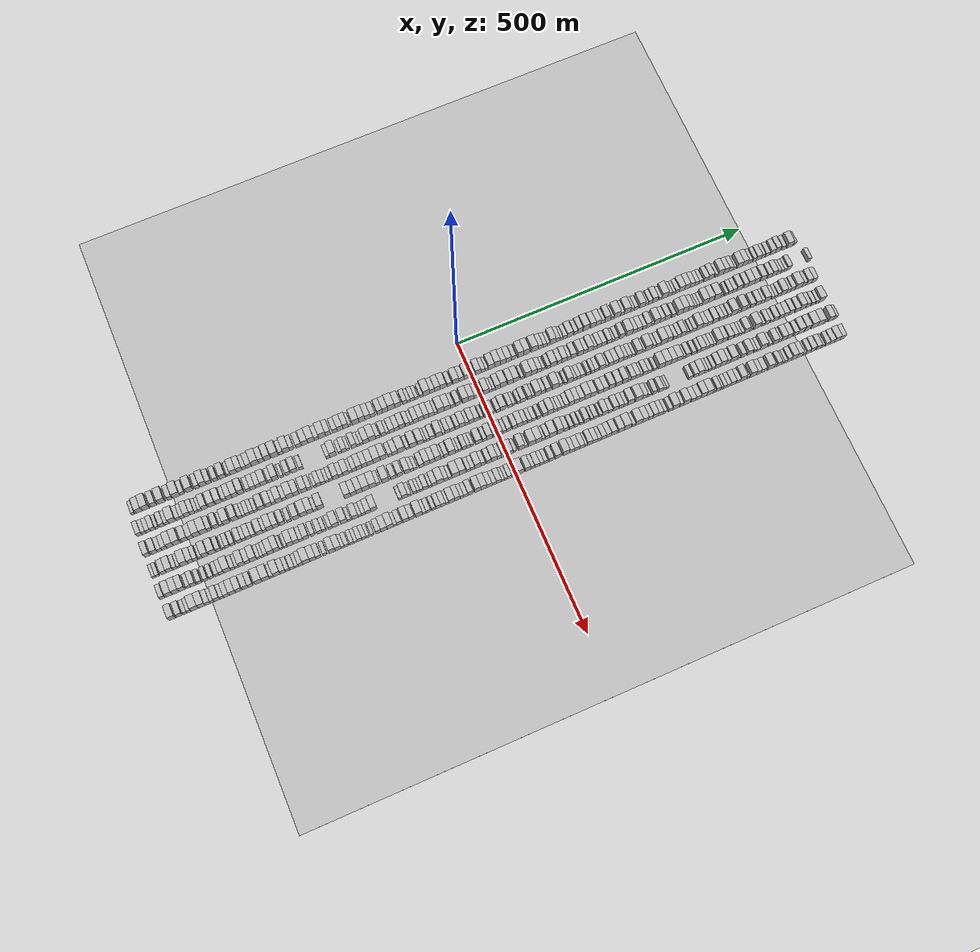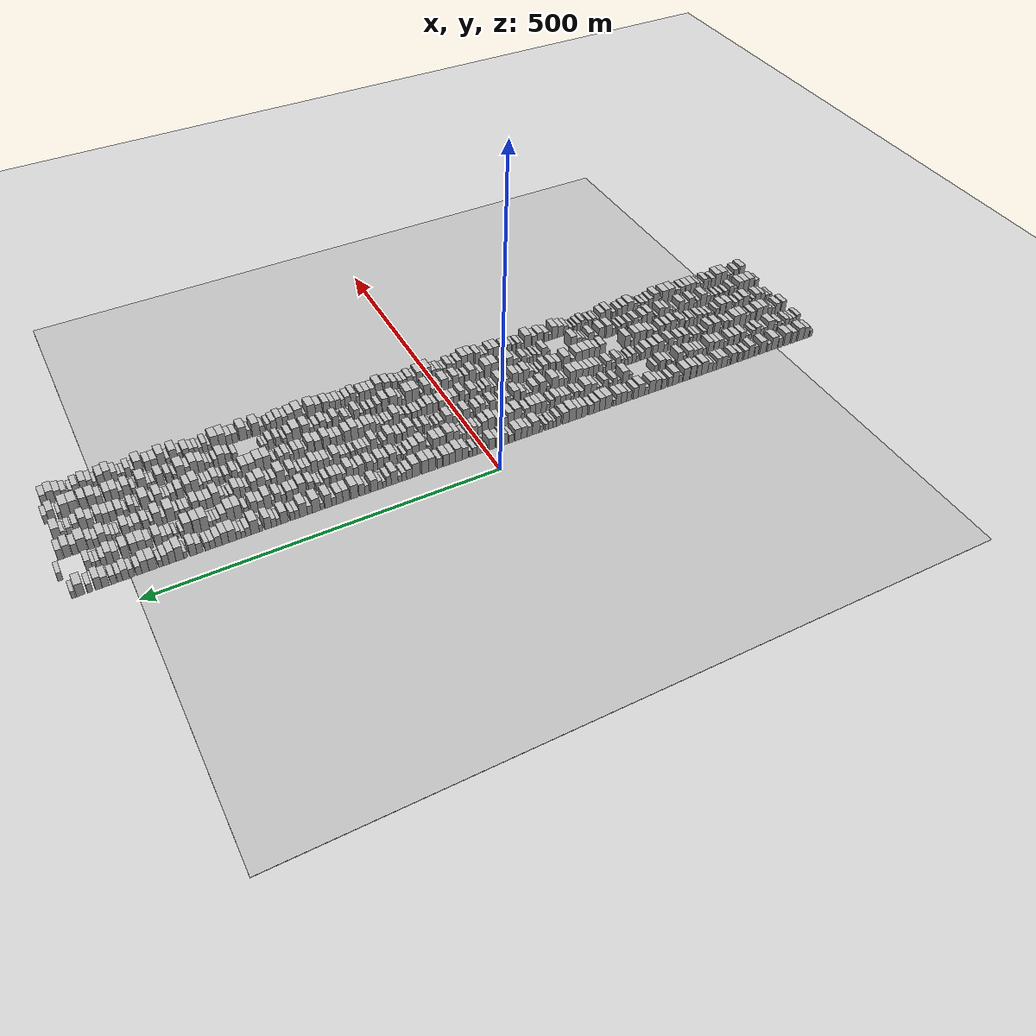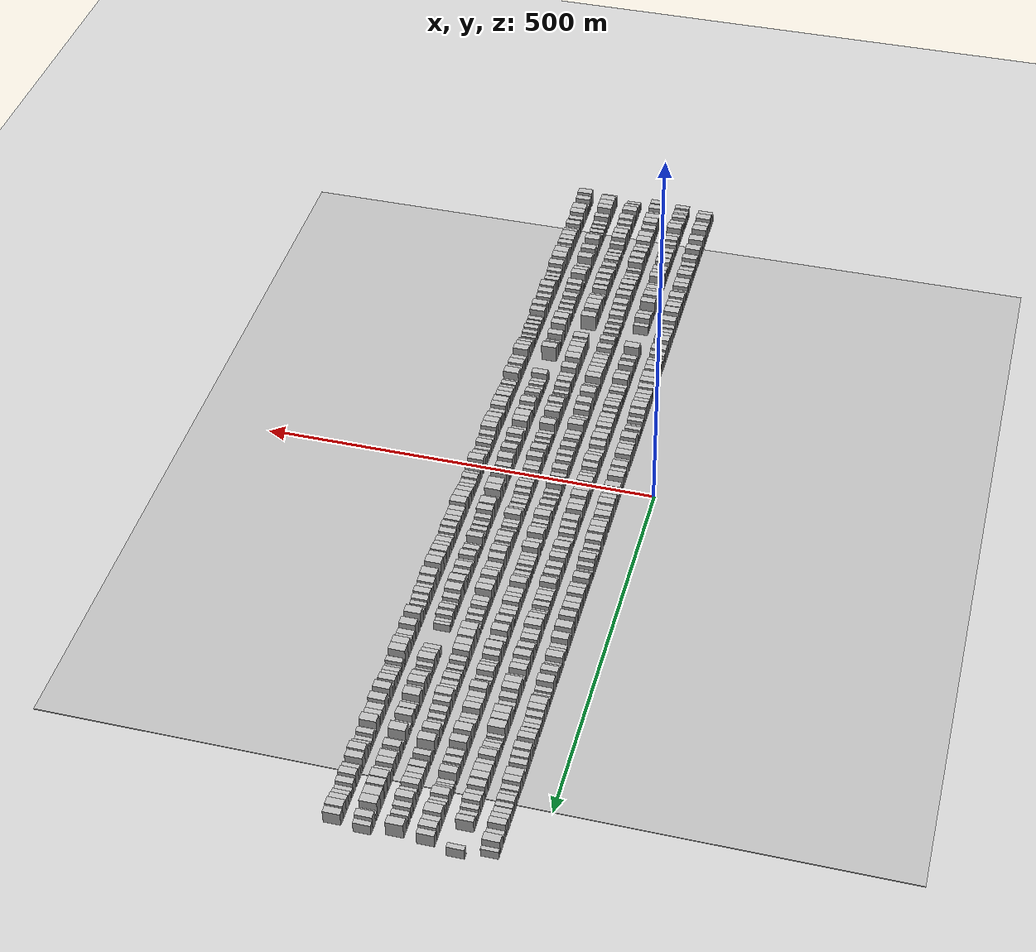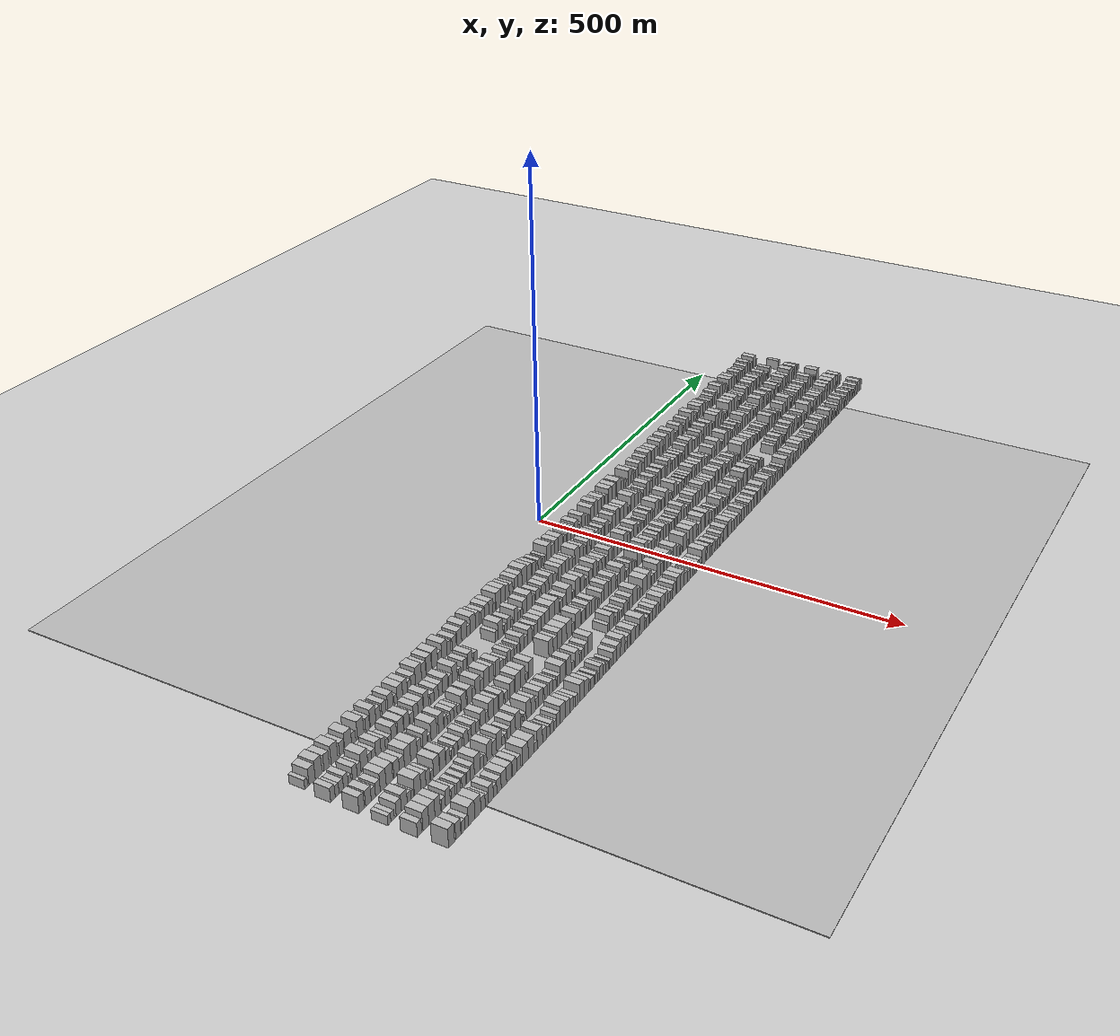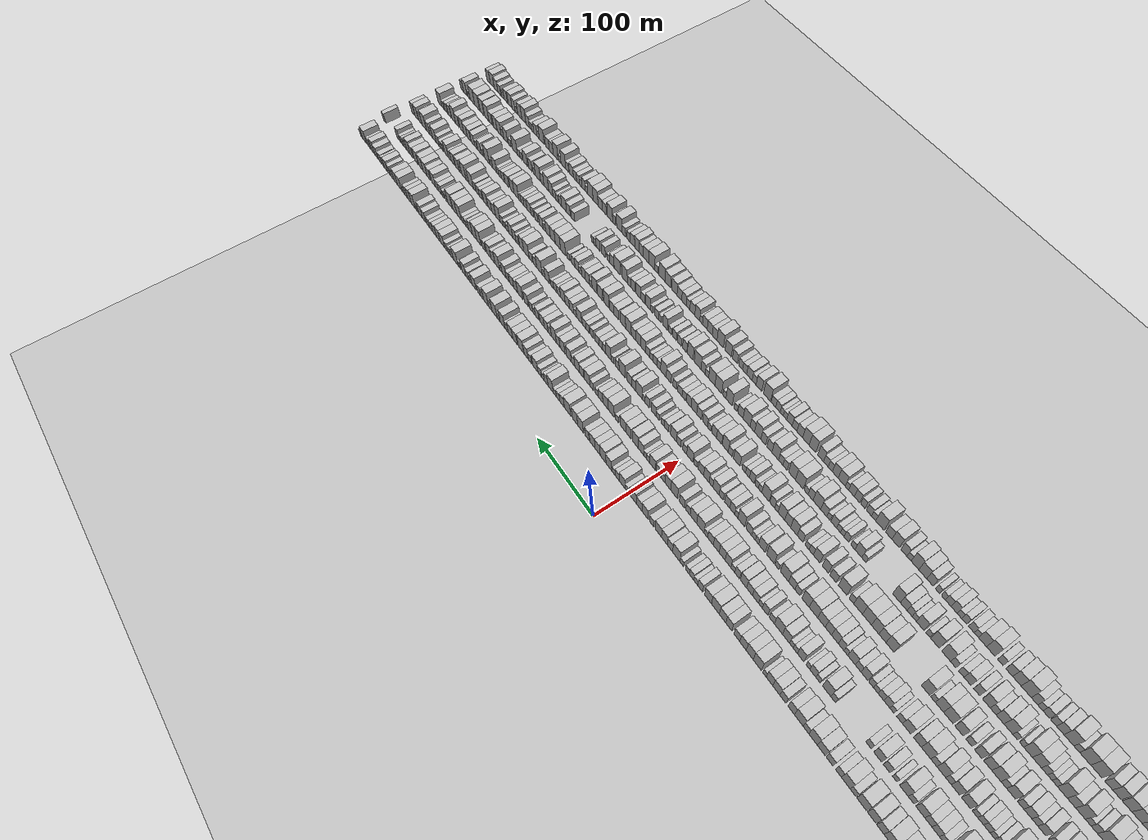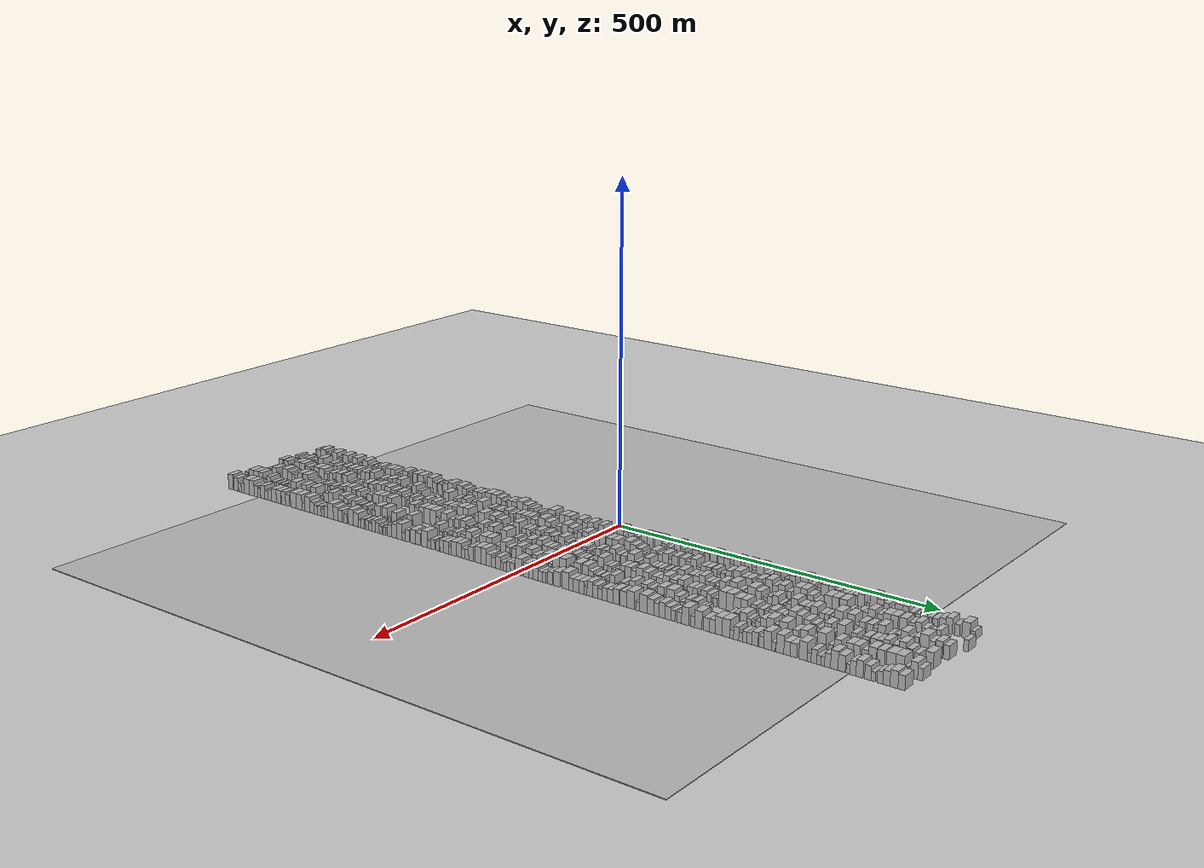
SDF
<?xml version="1.0" encoding="utf-8"?>

<sdf version="1.6">

   <world name="default">

      <gui fullscreen="0">

         <camera name="user_camera">

            <pose>-15 0 4.57585 0 0 0</pose>

            <view_controller>orbit</view_controller>

         </camera>

      </gui>

      <scene>

         <sky>

           <clouds>

             <speed>12</speed>

           </clouds>

         </sky>

         <ambient>0.4 0.4 0.4 1</ambient>

         <background>0.7 0.7 0.7 1</background>

         <shadows>1</shadows>

      </scene>

      <gravity>0 0 -9.8066</gravity>

      <magnetic_field>6e-06 2.3e-05 -4.2e-05</magnetic_field>

      <physics default="0" name="default_physics" type="ode">

         <ode>

            <solver>

               <type>quick</type>

               <iters>10</iters>

               <sor>1.0</sor>

               <use_dynamic_moi_rescaling>0</use_dynamic_moi_rescaling>

            </solver>

            <constraints>

               <cfm>0</cfm>

               <erp>0.2</erp>

               <contact_max_correcting_vel>100</contact_max_correcting_vel>

               <contact_surface_layer>0.001</contact_surface_layer>

            </constraints>

         </ode>

         <max_step_size>0.004</max_step_size>

         <real_time_factor>1</real_time_factor>

         <real_time_update_rate>250</real_time_update_rate>

      </physics>

      <light name="sun" type="directional">

         <cast_shadows>1</cast_shadows>

         <pose>0 0 10 0 0 0</pose>

         <diffuse>0.8 0.8 0.8 1</diffuse>

         <specular>0.2 0.2 0.2 1</specular>

         <attenuation>

            <range>1000</range>

            <constant>0.9</constant>

            <linear>0.01</linear>

            <quadratic>0.001</quadratic>

         </attenuation>

         <direction>-0.5 0.1 -0.9</direction>

      </light>

      <include>

         <name>ground_plane_1</name>

         <uri>model://HANNAS_ground_plane</uri>

         <pose>0 0 0  0 0 0</pose>

      </include>

      <include>

         <name>ground_plane_2</name>

         <uri>model://HANNAS_ground_plane</uri>

         <pose>100 0 0  0 0 0</pose>

      </include>

      <model name="building_1">

         <static>1</static>

         <pose frame="">50.0000 -564.5468 0 0.000000 0.000000 0.000000</pose>

         <link name="link">

            <pose frame="">0 0 6.00 0 0 0</pose>

            <collision name="collision">

               <geometry>

                  <box>

                     <size>20.0000 4.9063 12.0000</size>

                  </box>

               </geometry>

               <max_contacts>10</max_contacts>

               <surface>

                  <contact>

                     <ode/>

                  </contact>

                  <bounce/>

                  <friction>

                     <torsional>

                        <ode/>

                     </torsional>

                     <ode/>

                  </friction>

               </surface>

            </collision>

            <visual name="visual">

               <cast_shadows>0</cast_shadows>

               <geometry>

                  <box>

                     <size>20.0000 4.9063 12.0000</size>

                  </box>

               </geometry>

               <material>

                  <script>

                     <uri>model://HANNAS_wall/materials/scripts</uri>

                     <uri>model://HANNAS_wall/materials/textures</uri>

                     <name>vrc/HANNAS_wall</name>

                  </script>

               </material>

            </visual>

            <self_collide>0</self_collide>

            <enable_wind>0</enable_wind>

            <kinematic>0</kinematic>

         </link>

      </model>

      <model name="building_2">

         <static>1</static>

         <pose frame="">50.0000 -554.9758 0 0.000000 0.000000 0.000000</pose>

         <link name="link">

            <pose frame="">0 0 10.50 0 0 0</pose>

            <collision name="collision">

               <geometry>

                  <box>

                     <size>20.0000 10.2358 21.0000</size>

                  </box>

               </geometry>

               <max_contacts>10</max_contacts>

               <surface>

                  <contact>

                     <ode/>

                  </contact>

                  <bounce/>

                  <friction>

                     <torsional>

                        <ode/>

                     </torsional>

                     <ode/>

                  </friction>

               </surface>

            </collision>

            <visual name="visual">

               <cast_shadows>0</cast_shadows>

               <geometry>

                  <box>

                     <size>20.0000 10.2358 21.0000</size>

                  </box>

               </geometry>

               <material>

                  <script>

                     <uri>model://HANNAS_wall/materials/scripts</uri>

                     <uri>model://HANNAS_wall/materials/textures</uri>

                     <name>vrc/HANNAS_wall</name>

                  </script>

               </material>

            </visual>

            <self_collide>0</self_collide>

            <enable_wind>0</enable_wind>

            <kinematic>0</kinematic>

         </link>

      </model>

      <model name="building_3">

         <static>1</static>

         <pose frame="">50.0000 -544.1538 0 0.000000 0.000000 0.000000</pose>

         <link name="link">

            <pose frame="">0 0 12.00 0 0 0</pose>

            <collision name="collision">

               <geometry>

                  <box>

                     <size>20.0000 11.4081 24.0000</size>

                  </box>

               </geometry>

               <max_contacts>10</max_contacts>

               <surface>

                  <contact>

                     <ode/>

                  </contact>

                  <bounce/>

                  <friction>

                     <torsional>

                        <ode/>

                     </torsional>

                     <ode/>

                  </friction>

               </surface>

            </collision>

            <visual name="visual">

               <cast_shadows>0</cast_shadows>

               <geometry>

                  <box>

                     <size>20.0000 11.4081 24.0000</size>

                  </box>

               </geometry>

               <material>

                  <script>

                     <uri>model://HANNAS_wall/materials/scripts</uri>

                     <uri>model://HANNAS_wall/materials/textures</uri>

                     <name>vrc/HANNAS_wall</name>

                  </script>

               </material>

            </visual>

            <self_collide>0</self_collide>

            <enable_wind>0</enable_wind>

            <kinematic>0</kinematic>

         </link>

      </model>

      <model name="building_4">

         <static>1</static>

         <pose frame="">50.0000 -530.9648 0 0.000000 0.000000 0.000000</pose>

         <link name="link">

            <pose frame="">0 0 10.50 0 0 0</pose>

            <collision name="collision">

               <geometry>

                  <box>

                     <size>20.0000 8.9697 21.0000</size>

                  </box>

               </geometry>

               <max_contacts>10</max_contacts>

               <surface>

                  <contact>

                     <ode/>

                  </contact>

                  <bounce/>

                  <friction>

                     <torsional>

                        <ode/>

                     </torsional>

                     <ode/>

                  </friction>

               </surface>

            </collision>

            <visual name="visual">

               <cast_shadows>0</cast_shadows>

               <geometry>

                  <box>

                     <size>20.0000 8.9697 21.0000</size>

                  </box>

               </geometry>

               <material>

                  <script>

                     <uri>model://HANNAS_wall/materials/scripts</uri>

                     <uri>model://HANNAS_wall/materials/textures</uri>

                     <name>vrc/HANNAS_wall</name>

                  </script>

               </material>

            </visual>

            <self_collide>0</self_collide>

            <enable_wind>0</enable_wind>

            <kinematic>0</kinematic>

         </link>

      </model>

      <model name="building_5">

         <static>1</static>

         <pose frame="">50.0000 -517.8318 0 0.000000 0.000000 0.000000</pose>

         <link name="link">

            <pose frame="">0 0 12.00 0 0 0</pose>

            <collision name="collision">

               <geometry>

                  <box>

                     <size>20.0000 11.2964 24.0000</size>

                  </box>

               </geometry>

               <max_contacts>10</max_contacts>

               <surface>

                  <contact>

                     <ode/>

                  </contact>

                  <bounce/>

                  <friction>

                     <torsional>

                        <ode/>

                     </torsional>

                     <ode/>

                  </friction>

               </surface>

            </collision>

            <visual name="visual">

               <cast_shadows>0</cast_shadows>

               <geometry>

                  <box>

                     <size>20.0000 11.2964 24.0000</size>

                  </box>

               </geometry>

               <material>

                  <script>

                     <uri>model://HANNAS_wall/materials/scripts</uri>

                     <uri>model://HANNAS_wall/materials/textures</uri>

                     <name>vrc/HANNAS_wall</name>

                  </script>

               </material>

            </visual>

            <self_collide>0</self_collide>

            <enable_wind>0</enable_wind>

            <kinematic>0</kinematic>

         </link>

      </model>

      <model name="building_6">

         <static>1</static>

         <pose frame="">50.0000 -505.1996 0 0.000000 0.000000 0.000000</pose>

         <link name="link">

            <pose frame="">0 0 9.00 0 0 0</pose>

            <collision name="collision">

               <geometry>

                  <box>

                     <size>20.0000 7.9679 18.0000</size>

                  </box>

               </geometry>

               <max_contacts>10</max_contacts>

               <surface>

                  <contact>

                     <ode/>

                  </contact>

                  <bounce/>

                  <friction>

                     <torsional>

                        <ode/>

                     </torsional>

                     <ode/>

                  </friction>

               </surface>

            </collision>

            <visual name="visual">

               <cast_shadows>0</cast_shadows>

               <geometry>

                  <box>

                     <size>20.0000 7.9679 18.0000</size>

                  </box>

               </geometry>

               <material>

                  <script>

                     <uri>model://HANNAS_wall/materials/scripts</uri>

                     <uri>model://HANNAS_wall/materials/textures</uri>

                     <name>vrc/HANNAS_wall</name>

                  </script>

               </material>

            </visual>

            <self_collide>0</self_collide>

            <enable_wind>0</enable_wind>

            <kinematic>0</kinematic>

         </link>

      </model>

      <model name="building_7">

         <static>1</static>

         <pose frame="">50.0000 -494.2581 0 0.000000 0.000000 0.000000</pose>

         <link name="link">

            <pose frame="">0 0 12.00 0 0 0</pose>

            <collision name="collision">

               <geometry>

                  <box>

                     <size>20.0000 11.9151 24.0000</size>

                  </box>

               </geometry>

               <max_contacts>10</max_contacts>

               <surface>

                  <contact>

                     <ode/>

                  </contact>

                  <bounce/>

                  <friction>

                     <torsional>

                        <ode/>

                     </torsional>

                     <ode/>

                  </friction>

               </surface>

            </collision>

            <visual name="visual">

               <cast_shadows>0</cast_shadows>

               <geometry>

                  <box>

                     <size>20.0000 11.9151 24.0000</size>

                  </box>

               </geometry>

               <material>

                  <script>

                     <uri>model://HANNAS_wall/materials/scripts</uri>

                     <uri>model://HANNAS_wall/materials/textures</uri>

                     <name>vrc/HANNAS_wall</name>

                  </script>

               </material>

            </visual>

            <self_collide>0</self_collide>

            <enable_wind>0</enable_wind>

            <kinematic>0</kinematic>

         </link>

      </model>

      <model name="building_8">

         <static>1</static>

         <pose frame="">50.0000 -484.6999 0 0.000000 0.000000 0.000000</pose>

         <link name="link">

            <pose frame="">0 0 7.50 0 0 0</pose>

            <collision name="collision">

               <geometry>

                  <box>

                     <size>20.0000 7.2013 15.0000</size>

                  </box>

               </geometry>

               <max_contacts>10</max_contacts>

               <surface>

                  <contact>

                     <ode/>

                  </contact>

                  <bounce/>

                  <friction>

                     <torsional>

                        <ode/>

                     </torsional>

                     <ode/>

                  </friction>

               </surface>

            </collision>

            <visual name="visual">

               <cast_shadows>0</cast_shadows>

               <geometry>

                  <box>

                     <size>20.0000 7.2013 15.0000</size>

                  </box>

               </geometry>

               <material>

                  <script>

                     <uri>model://HANNAS_wall/materials/scripts</uri>

                     <uri>model://HANNAS_wall/materials/textures</uri>

                     <name>vrc/HANNAS_wall</name>

                  </script>

               </material>

            </visual>

            <self_collide>0</self_collide>

            <enable_wind>0</enable_wind>

            <kinematic>0</kinematic>

         </link>

      </model>

      <model name="building_9">

         <static>1</static>

         <pose frame="">50.0000 -472.4553 0 0.000000 0.000000 0.000000</pose>

         <link name="link">

            <pose frame="">0 0 12.00 0 0 0</pose>

            <collision name="collision">

               <geometry>

                  <box>

                     <size>20.0000 11.2879 24.0000</size>

                  </box>

               </geometry>

               <max_contacts>10</max_contacts>

               <surface>

                  <contact>

                     <ode/>

                  </contact>

                  <bounce/>

                  <friction>

                     <torsional>

                        <ode/>

                     </torsional>

                     <ode/>

                  </friction>

               </surface>

            </collision>

            <visual name="visual">

               <cast_shadows>0</cast_shadows>

               <geometry>

                  <box>

                     <size>20.0000 11.2879 24.0000</size>

                  </box>

               </geometry>

               <material>

                  <script>

                     <uri>model://HANNAS_wall/materials/scripts</uri>

                     <uri>model://HANNAS_wall/materials/textures</uri>

                     <name>vrc/HANNAS_wall</name>

                  </script>

               </material>

            </visual>

            <self_collide>0</self_collide>

            <enable_wind>0</enable_wind>

            <kinematic>0</kinematic>

         </link>

      </model>

      <model name="building_10">

         <static>1</static>

         <pose frame="">50.0000 -460.1695 0 0.000000 0.000000 0.000000</pose>

         <link name="link">

            <pose frame="">0 0 9.00 0 0 0</pose>

            <collision name="collision">

               <geometry>

                  <box>

                     <size>20.0000 7.2836 18.0000</size>

                  </box>

               </geometry>

               <max_contacts>10</max_contacts>

               <surface>

                  <contact>

                     <ode/>

                  </contact>

                  <bounce/>

                  <friction>

                     <torsional>

                        <ode/>

                     </torsional>

                     <ode/>

                  </friction>

               </surface>

            </collision>

            <visual name="visual">

               <cast_shadows>0</cast_shadows>

               <geometry>

                  <box>

                     <size>20.0000 7.2836 18.0000</size>

                  </box>

               </geometry>

               <material>

                  <script>

                     <uri>model://HANNAS_wall/materials/scripts</uri>

                     <uri>model://HANNAS_wall/materials/textures</uri>

                     <name>vrc/HANNAS_wall</name>

                  </script>

               </material>

            </visual>

            <self_collide>0</self_collide>

            <enable_wind>0</enable_wind>

            <kinematic>0</kinematic>

         </link>

      </model>

      <model name="building_11">

         <static>1</static>

         <pose frame="">50.0000 -450.4083 0 0.000000 0.000000 0.000000</pose>

         <link name="link">

            <pose frame="">0 0 12.00 0 0 0</pose>

            <collision name="collision">

               <geometry>

                  <box>

                     <size>20.0000 10.2388 24.0000</size>

                  </box>

               </geometry>

               <max_contacts>10</max_contacts>

               <surface>

                  <contact>

                     <ode/>

                  </contact>

                  <bounce/>

                  <friction>

                     <torsional>

                        <ode/>

                     </torsional>

                     <ode/>

                  </friction>

               </surface>

            </collision>

            <visual name="visual">

               <cast_shadows>0</cast_shadows>

               <geometry>

                  <box>

                     <size>20.0000 10.2388 24.0000</size>

                  </box>

               </geometry>

               <material>

                  <script>

                     <uri>model://HANNAS_wall/materials/scripts</uri>

                     <uri>model://HANNAS_wall/materials/textures</uri>

                     <name>vrc/HANNAS_wall</name>

                  </script>

               </material>

            </visual>

            <self_collide>0</self_collide>

            <enable_wind>0</enable_wind>

            <kinematic>0</kinematic>

         </link>

      </model>

      <model name="building_12">

         <static>1</static>

         <pose frame="">50.0000 -441.2658 0 0.000000 0.000000 0.000000</pose>

         <link name="link">

            <pose frame="">0 0 9.00 0 0 0</pose>

            <collision name="collision">

               <geometry>

                  <box>

                     <size>20.0000 8.0460 18.0000</size>

                  </box>

               </geometry>

               <max_contacts>10</max_contacts>

               <surface>

                  <contact>

                     <ode/>

                  </contact>

                  <bounce/>

                  <friction>

                     <torsional>

                        <ode/>

                     </torsional>

                     <ode/>

                  </friction>

               </surface>

            </collision>

            <visual name="visual">

               <cast_shadows>0</cast_shadows>

               <geometry>

                  <box>

                     <size>20.0000 8.0460 18.0000</size>

                  </box>

               </geometry>

               <material>

                  <script>

                     <uri>model://HANNAS_wall/materials/scripts</uri>

                     <uri>model://HANNAS_wall/materials/textures</uri>

                     <name>vrc/HANNAS_wall</name>

                  </script>

               </material>

            </visual>

            <self_collide>0</self_collide>

            <enable_wind>0</enable_wind>

            <kinematic>0</kinematic>

         </link>

      </model>

      <model name="building_13">

         <static>1</static>

         <pose frame="">50.0000 -430.3157 0 0.000000 0.000000 0.000000</pose>

         <link name="link">

            <pose frame="">0 0 9.00 0 0 0</pose>

            <collision name="collision">

               <geometry>

                  <box>

                     <size>20.0000 7.8542 18.0000</size>

                  </box>

               </geometry>

               <max_contacts>10</max_contacts>

               <surface>

                  <contact>

                     <ode/>

                  </contact>

                  <bounce/>

                  <friction>

                     <torsional>

                        <ode/>

                     </torsional>

                     <ode/>

                  </friction>

               </surface>

            </collision>

            <visual name="visual">

               <cast_shadows>0</cast_shadows>

               <geometry>

                  <box>

                     <size>20.0000 7.8542 18.0000</size>

                  </box>

               </geometry>

               <material>

                  <script>

                     <uri>model://HANNAS_wall/materials/scripts</uri>

                     <uri>model://HANNAS_wall/materials/textures</uri>

                     <name>vrc/HANNAS_wall</name>

                  </script>

               </material>

            </visual>

            <self_collide>0</self_collide>

            <enable_wind>0</enable_wind>

            <kinematic>0</kinematic>

         </link>

      </model>

      <model name="building_14">

         <static>1</static>

         <pose frame="">50.0000 -418.4295 0 0.000000 0.000000 0.000000</pose>

         <link name="link">

            <pose frame="">0 0 10.50 0 0 0</pose>

            <collision name="collision">

               <geometry>

                  <box>

                     <size>20.0000 9.9183 21.0000</size>

                  </box>

               </geometry>

               <max_contacts>10</max_contacts>

               <surface>

                  <contact>

                     <ode/>

                  </contact>

                  <bounce/>

                  <friction>

                     <torsional>

                        <ode/>

                     </torsional>

                     <ode/>

                  </friction>

               </surface>

            </collision>

            <visual name="visual">

               <cast_shadows>0</cast_shadows>

               <geometry>

                  <box>

                     <size>20.0000 9.9183 21.0000</size>

                  </box>

               </geometry>

               <material>

                  <script>

                     <uri>model://HANNAS_wall/materials/scripts</uri>

                     <uri>model://HANNAS_wall/materials/textures</uri>

                     <name>vrc/HANNAS_wall</name>

                  </script>

               </material>

            </visual>

            <self_collide>0</self_collide>

            <enable_wind>0</enable_wind>

            <kinematic>0</kinematic>

         </link>

      </model>

      <model name="building_15">

         <static>1</static>

         <pose frame="">50.0000 -408.7384 0 0.000000 0.000000 0.000000</pose>

         <link name="link">

            <pose frame="">0 0 6.00 0 0 0</pose>

            <collision name="collision">

               <geometry>

                  <box>

                     <size>20.0000 5.4639 12.0000</size>

                  </box>

               </geometry>

               <max_contacts>10</max_contacts>

               <surface>

                  <contact>

                     <ode/>

                  </contact>

                  <bounce/>

                  <friction>

                     <torsional>

                        <ode/>

                     </torsional>

                     <ode/>

                  </friction>

               </surface>

            </collision>

            <visual name="visual">

               <cast_shadows>0</cast_shadows>

               <geometry>

                  <box>

                     <size>20.0000 5.4639 12.0000</size>

                  </box>

               </geometry>

               <material>

                  <script>

                     <uri>model://HANNAS_wall/materials/scripts</uri>

                     <uri>model://HANNAS_wall/materials/textures</uri>

                     <name>vrc/HANNAS_wall</name>

                  </script>

               </material>

            </visual>

            <self_collide>0</self_collide>

            <enable_wind>0</enable_wind>

            <kinematic>0</kinematic>

         </link>

      </model>

      <model name="building_16">

         <static>1</static>

         <pose frame="">50.0000 -400.8172 0 0.000000 0.000000 0.000000</pose>

         <link name="link">

            <pose frame="">0 0 10.50 0 0 0</pose>

            <collision name="collision">

               <geometry>

                  <box>

                     <size>20.0000 10.3786 21.0000</size>

                  </box>

               </geometry>

               <max_contacts>10</max_contacts>

               <surface>

                  <contact>

                     <ode/>

                  </contact>

                  <bounce/>

                  <friction>

                     <torsional>

                        <ode/>

                     </torsional>

                     <ode/>

                  </friction>

               </surface>

            </collision>

            <visual name="visual">

               <cast_shadows>0</cast_shadows>

               <geometry>

                  <box>

                     <size>20.0000 10.3786 21.0000</size>

                  </box>

               </geometry>

               <material>

                  <script>

                     <uri>model://HANNAS_wall/materials/scripts</uri>

                     <uri>model://HANNAS_wall/materials/textures</uri>

                     <name>vrc/HANNAS_wall</name>

                  </script>

               </material>

            </visual>

            <self_collide>0</self_collide>

            <enable_wind>0</enable_wind>

            <kinematic>0</kinematic>

         </link>

      </model>

      <model name="building_17">

         <static>1</static>

         <pose frame="">50.0000 -391.1258 0 0.000000 0.000000 0.000000</pose>

         <link name="link">

            <pose frame="">0 0 10.50 0 0 0</pose>

            <collision name="collision">

               <geometry>

                  <box>

                     <size>20.0000 9.0041 21.0000</size>

                  </box>

               </geometry>

               <max_contacts>10</max_contacts>

               <surface>

                  <contact>

                     <ode/>

                  </contact>

                  <bounce/>

                  <friction>

                     <torsional>

                        <ode/>

                     </torsional>

                     <ode/>

                  </friction>

               </surface>

            </collision>

            <visual name="visual">

               <cast_shadows>0</cast_shadows>

               <geometry>

                  <box>

                     <size>20.0000 9.0041 21.0000</size>

                  </box>

               </geometry>

               <material>

                  <script>

                     <uri>model://HANNAS_wall/materials/scripts</uri>

                     <uri>model://HANNAS_wall/materials/textures</uri>

                     <name>vrc/HANNAS_wall</name>

                  </script>

               </material>

            </visual>

            <self_collide>0</self_collide>

            <enable_wind>0</enable_wind>

            <kinematic>0</kinematic>

         </link>

      </model>

      <model name="building_18">

         <static>1</static>

         <pose frame="">50.0000 -383.2806 0 0.000000 0.000000 0.000000</pose>

         <link name="link">

            <pose frame="">0 0 7.50 0 0 0</pose>

            <collision name="collision">

               <geometry>

                  <box>

                     <size>20.0000 6.6862 15.0000</size>

                  </box>

               </geometry>

               <max_contacts>10</max_contacts>

               <surface>

                  <contact>

                     <ode/>

                  </contact>

                  <bounce/>

                  <friction>

                     <torsional>

                        <ode/>

                     </torsional>

                     <ode/>

                  </friction>

               </surface>

            </collision>

            <visual name="visual">

               <cast_shadows>0</cast_shadows>

               <geometry>

                  <box>

                     <size>20.0000 6.6862 15.0000</size>

                  </box>

               </geometry>

               <material>

                  <script>

                     <uri>model://HANNAS_wall/materials/scripts</uri>

                     <uri>model://HANNAS_wall/materials/textures</uri>

                     <name>vrc/HANNAS_wall</name>

                  </script>

               </material>

            </visual>

            <self_collide>0</self_collide>

            <enable_wind>0</enable_wind>

            <kinematic>0</kinematic>

         </link>

      </model>

      <model name="building_19">

         <static>1</static>

         <pose frame="">50.0000 -375.5136 0 0.000000 0.000000 0.000000</pose>

         <link name="link">

            <pose frame="">0 0 9.00 0 0 0</pose>

            <collision name="collision">

               <geometry>

                  <box>

                     <size>20.0000 8.8477 18.0000</size>

                  </box>

               </geometry>

               <max_contacts>10</max_contacts>

               <surface>

                  <contact>

                     <ode/>

                  </contact>

                  <bounce/>

                  <friction>

                     <torsional>

                        <ode/>

                     </torsional>

                     <ode/>

                  </friction>

               </surface>

            </collision>

            <visual name="visual">

               <cast_shadows>0</cast_shadows>

               <geometry>

                  <box>

                     <size>20.0000 8.8477 18.0000</size>

                  </box>

               </geometry>

               <material>

                  <script>

                     <uri>model://HANNAS_wall/materials/scripts</uri>

                     <uri>model://HANNAS_wall/materials/textures</uri>

                     <name>vrc/HANNAS_wall</name>

                  </script>

               </material>

            </visual>

            <self_collide>0</self_collide>

            <enable_wind>0</enable_wind>

            <kinematic>0</kinematic>

         </link>

      </model>

      <model name="building_20">

         <static>1</static>

         <pose frame="">50.0000 -365.2161 0 0.000000 0.000000 0.000000</pose>

         <link name="link">

            <pose frame="">0 0 12.00 0 0 0</pose>

            <collision name="collision">

               <geometry>

                  <box>

                     <size>20.0000 11.7475 24.0000</size>

                  </box>

               </geometry>

               <max_contacts>10</max_contacts>

               <surface>

                  <contact>

                     <ode/>

                  </contact>

                  <bounce/>

                  <friction>

                     <torsional>

                        <ode/>

                     </torsional>

                     <ode/>

                  </friction>

               </surface>

            </collision>

            <visual name="visual">

               <cast_shadows>0</cast_shadows>

               <geometry>

                  <box>

                     <size>20.0000 11.7475 24.0000</size>

                  </box>

               </geometry>

               <material>

                  <script>

                     <uri>model://HANNAS_wall/materials/scripts</uri>

                     <uri>model://HANNAS_wall/materials/textures</uri>

                     <name>vrc/HANNAS_wall</name>

                  </script>

               </material>

            </visual>

            <self_collide>0</self_collide>

            <enable_wind>0</enable_wind>

            <kinematic>0</kinematic>

         </link>

      </model>

      <model name="building_21">

         <static>1</static>

         <pose frame="">50.0000 -355.0789 0 0.000000 0.000000 0.000000</pose>

         <link name="link">

            <pose frame="">0 0 10.50 0 0 0</pose>

            <collision name="collision">

               <geometry>

                  <box>

                     <size>20.0000 8.5269 21.0000</size>

                  </box>

               </geometry>

               <max_contacts>10</max_contacts>

               <surface>

                  <contact>

                     <ode/>

                  </contact>

                  <bounce/>

                  <friction>

                     <torsional>

                        <ode/>

                     </torsional>

                     <ode/>

                  </friction>

               </surface>

            </collision>

            <visual name="visual">

               <cast_shadows>0</cast_shadows>

               <geometry>

                  <box>

                     <size>20.0000 8.5269 21.0000</size>

                  </box>

               </geometry>

               <material>

                  <script>

                     <uri>model://HANNAS_wall/materials/scripts</uri>

                     <uri>model://HANNAS_wall/materials/textures</uri>

                     <name>vrc/HANNAS_wall</name>

                  </script>

               </material>

            </visual>

            <self_collide>0</self_collide>

            <enable_wind>0</enable_wind>

            <kinematic>0</kinematic>

         </link>

      </model>

      <model name="building_22">

         <static>1</static>

         <pose frame="">50.0000 -344.7363 0 0.000000 0.000000 0.000000</pose>

         <link name="link">

            <pose frame="">0 0 12.00 0 0 0</pose>

            <collision name="collision">

               <geometry>

                  <box>

                     <size>20.0000 10.1581 24.0000</size>

                  </box>

               </geometry>

               <max_contacts>10</max_contacts>

               <surface>

                  <contact>

                     <ode/>

                  </contact>

                  <bounce/>

                  <friction>

                     <torsional>

                        <ode/>

                     </torsional>

                     <ode/>

                  </friction>

               </surface>

            </collision>

            <visual name="visual">

               <cast_shadows>0</cast_shadows>

               <geometry>

                  <box>

                     <size>20.0000 10.1581 24.0000</size>

                  </box>

               </geometry>

               <material>

                  <script>

                     <uri>model://HANNAS_wall/materials/scripts</uri>

                     <uri>model://HANNAS_wall/materials/textures</uri>

                     <name>vrc/HANNAS_wall</name>

                  </script>

               </material>

            </visual>

            <self_collide>0</self_collide>

            <enable_wind>0</enable_wind>

            <kinematic>0</kinematic>

         </link>

      </model>

      <model name="building_23">

         <static>1</static>

         <pose frame="">50.0000 -332.7798 0 0.000000 0.000000 0.000000</pose>

         <link name="link">

            <pose frame="">0 0 12.00 0 0 0</pose>

            <collision name="collision">

               <geometry>

                  <box>

                     <size>20.0000 11.7550 24.0000</size>

                  </box>

               </geometry>

               <max_contacts>10</max_contacts>

               <surface>

                  <contact>

                     <ode/>

                  </contact>

                  <bounce/>

                  <friction>

                     <torsional>

                        <ode/>

                     </torsional>

                     <ode/>

                  </friction>

               </surface>

            </collision>

            <visual name="visual">

               <cast_shadows>0</cast_shadows>

               <geometry>

                  <box>

                     <size>20.0000 11.7550 24.0000</size>

                  </box>

               </geometry>

               <material>

                  <script>

                     <uri>model://HANNAS_wall/materials/scripts</uri>

                     <uri>model://HANNAS_wall/materials/textures</uri>

                     <name>vrc/HANNAS_wall</name>

                  </script>

               </material>

            </visual>

            <self_collide>0</self_collide>

            <enable_wind>0</enable_wind>

            <kinematic>0</kinematic>

         </link>

      </model>

      <model name="building_24">

         <static>1</static>

         <pose frame="">50.0000 -322.4275 0 0.000000 0.000000 0.000000</pose>

         <link name="link">

            <pose frame="">0 0 7.50 0 0 0</pose>

            <collision name="collision">

               <geometry>

                  <box>

                     <size>20.0000 6.9496 15.0000</size>

                  </box>

               </geometry>

               <max_contacts>10</max_contacts>

               <surface>

                  <contact>

                     <ode/>

                  </contact>

                  <bounce/>

                  <friction>

                     <torsional>

                        <ode/>

                     </torsional>

                     <ode/>

                  </friction>

               </surface>

            </collision>

            <visual name="visual">

               <cast_shadows>0</cast_shadows>

               <geometry>

                  <box>

                     <size>20.0000 6.9496 15.0000</size>

                  </box>

               </geometry>

               <material>

                  <script>

                     <uri>model://HANNAS_wall/materials/scripts</uri>

                     <uri>model://HANNAS_wall/materials/textures</uri>

                     <name>vrc/HANNAS_wall</name>

                  </script>

               </material>

            </visual>

            <self_collide>0</self_collide>

            <enable_wind>0</enable_wind>

            <kinematic>0</kinematic>

         </link>

      </model>

      <model name="building_25">

         <static>1</static>

         <pose frame="">50.0000 -313.5179 0 0.000000 0.000000 0.000000</pose>

         <link name="link">

            <pose frame="">0 0 12.00 0 0 0</pose>

            <collision name="collision">

               <geometry>

                  <box>

                     <size>20.0000 10.8697 24.0000</size>

                  </box>

               </geometry>

               <max_contacts>10</max_contacts>

               <surface>

                  <contact>

                     <ode/>

                  </contact>

                  <bounce/>

                  <friction>

                     <torsional>

                        <ode/>

                     </torsional>

                     <ode/>

                  </friction>

               </surface>

            </collision>

            <visual name="visual">

               <cast_shadows>0</cast_shadows>

               <geometry>

                  <box>

                     <size>20.0000 10.8697 24.0000</size>

                  </box>

               </geometry>

               <material>

                  <script>

                     <uri>model://HANNAS_wall/materials/scripts</uri>

                     <uri>model://HANNAS_wall/materials/textures</uri>

                     <name>vrc/HANNAS_wall</name>

                  </script>

               </material>

            </visual>

            <self_collide>0</self_collide>

            <enable_wind>0</enable_wind>

            <kinematic>0</kinematic>

         </link>

      </model>

      <model name="building_26">

         <static>1</static>

         <pose frame="">50.0000 -304.3919 0 0.000000 0.000000 0.000000</pose>

         <link name="link">

            <pose frame="">0 0 9.00 0 0 0</pose>

            <collision name="collision">

               <geometry>

                  <box>

                     <size>20.0000 7.3822 18.0000</size>

                  </box>

               </geometry>

               <max_contacts>10</max_contacts>

               <surface>

                  <contact>

                     <ode/>

                  </contact>

                  <bounce/>

                  <friction>

                     <torsional>

                        <ode/>

                     </torsional>

                     <ode/>

                  </friction>

               </surface>

            </collision>

            <visual name="visual">

               <cast_shadows>0</cast_shadows>

               <geometry>

                  <box>

                     <size>20.0000 7.3822 18.0000</size>

                  </box>

               </geometry>

               <material>

                  <script>

                     <uri>model://HANNAS_wall/materials/scripts</uri>

                     <uri>model://HANNAS_wall/materials/textures</uri>

                     <name>vrc/HANNAS_wall</name>

                  </script>

               </material>

            </visual>

            <self_collide>0</self_collide>

            <enable_wind>0</enable_wind>

            <kinematic>0</kinematic>

         </link>

      </model>

      <model name="building_27">

         <static>1</static>

         <pose frame="">50.0000 -293.3383 0 0.000000 0.000000 0.000000</pose>

         <link name="link">

            <pose frame="">0 0 9.00 0 0 0</pose>

            <collision name="collision">

               <geometry>

                  <box>

                     <size>20.0000 8.7250 18.0000</size>

                  </box>

               </geometry>

               <max_contacts>10</max_contacts>

               <surface>

                  <contact>

                     <ode/>

                  </contact>

                  <bounce/>

                  <friction>

                     <torsional>

                        <ode/>

                     </torsional>

                     <ode/>

                  </friction>

               </surface>

            </collision>

            <visual name="visual">

               <cast_shadows>0</cast_shadows>

               <geometry>

                  <box>

                     <size>20.0000 8.7250 18.0000</size>

                  </box>

               </geometry>

               <material>

                  <script>

                     <uri>model://HANNAS_wall/materials/scripts</uri>

                     <uri>model://HANNAS_wall/materials/textures</uri>

                     <name>vrc/HANNAS_wall</name>

                  </script>

               </material>

            </visual>

            <self_collide>0</self_collide>

            <enable_wind>0</enable_wind>

            <kinematic>0</kinematic>

         </link>

      </model>

      <model name="building_28">

         <static>1</static>

         <pose frame="">50.0000 -282.9297 0 0.000000 0.000000 0.000000</pose>

         <link name="link">

            <pose frame="">0 0 10.50 0 0 0</pose>

            <collision name="collision">

               <geometry>

                  <box>

                     <size>20.0000 10.0923 21.0000</size>

                  </box>

               </geometry>

               <max_contacts>10</max_contacts>

               <surface>

                  <contact>

                     <ode/>

                  </contact>

                  <bounce/>

                  <friction>

                     <torsional>

                        <ode/>

                     </torsional>

                     <ode/>

                  </friction>

               </surface>

            </collision>

            <visual name="visual">

               <cast_shadows>0</cast_shadows>

               <geometry>

                  <box>

                     <size>20.0000 10.0923 21.0000</size>

                  </box>

               </geometry>

               <material>

                  <script>

                     <uri>model://HANNAS_wall/materials/scripts</uri>

                     <uri>model://HANNAS_wall/materials/textures</uri>

                     <name>vrc/HANNAS_wall</name>

                  </script>

               </material>

            </visual>

            <self_collide>0</self_collide>

            <enable_wind>0</enable_wind>

            <kinematic>0</kinematic>

         </link>

      </model>

      <model name="building_29">

         <static>1</static>

         <pose frame="">50.0000 -272.3971 0 0.000000 0.000000 0.000000</pose>

         <link name="link">

            <pose frame="">0 0 12.00 0 0 0</pose>

            <collision name="collision">

               <geometry>

                  <box>

                     <size>20.0000 10.9728 24.0000</size>

                  </box>

               </geometry>

               <max_contacts>10</max_contacts>

               <surface>

                  <contact>

                     <ode/>

                  </contact>

                  <bounce/>

                  <friction>

                     <torsional>

                        <ode/>

                     </torsional>

                     <ode/>

                  </friction>

               </surface>

            </collision>

            <visual name="visual">

               <cast_shadows>0</cast_shadows>

               <geometry>

                  <box>

                     <size>20.0000 10.9728 24.0000</size>

                  </box>

               </geometry>

               <material>

                  <script>

                     <uri>model://HANNAS_wall/materials/scripts</uri>

                     <uri>model://HANNAS_wall/materials/textures</uri>

                     <name>vrc/HANNAS_wall</name>

                  </script>

               </material>

            </visual>

            <self_collide>0</self_collide>

            <enable_wind>0</enable_wind>

            <kinematic>0</kinematic>

         </link>

      </model>

      <model name="building_30">

         <static>1</static>

         <pose frame="">50.0000 -263.2354 0 0.000000 0.000000 0.000000</pose>

         <link name="link">

            <pose frame="">0 0 7.50 0 0 0</pose>

            <collision name="collision">

               <geometry>

                  <box>

                     <size>20.0000 7.3505 15.0000</size>

                  </box>

               </geometry>

               <max_contacts>10</max_contacts>

               <surface>

                  <contact>

                     <ode/>

                  </contact>

                  <bounce/>

                  <friction>

                     <torsional>

                        <ode/>

                     </torsional>

                     <ode/>

                  </friction>

               </surface>

            </collision>

            <visual name="visual">

               <cast_shadows>0</cast_shadows>

               <geometry>

                  <box>

                     <size>20.0000 7.3505 15.0000</size>

                  </box>

               </geometry>

               <material>

                  <script>

                     <uri>model://HANNAS_wall/materials/scripts</uri>

                     <uri>model://HANNAS_wall/materials/textures</uri>

                     <name>vrc/HANNAS_wall</name>

                  </script>

               </material>

            </visual>

            <self_collide>0</self_collide>

            <enable_wind>0</enable_wind>

            <kinematic>0</kinematic>

         </link>

      </model>

      <model name="building_31">

         <static>1</static>

         <pose frame="">50.0000 -253.8361 0 0.000000 0.000000 0.000000</pose>

         <link name="link">

            <pose frame="">0 0 12.00 0 0 0</pose>

            <collision name="collision">

               <geometry>

                  <box>

                     <size>20.0000 11.4482 24.0000</size>

                  </box>

               </geometry>

               <max_contacts>10</max_contacts>

               <surface>

                  <contact>

                     <ode/>

                  </contact>

                  <bounce/>

                  <friction>

                     <torsional>

                        <ode/>

                     </torsional>

                     <ode/>

                  </friction>

               </surface>

            </collision>

            <visual name="visual">

               <cast_shadows>0</cast_shadows>

               <geometry>

                  <box>

                     <size>20.0000 11.4482 24.0000</size>

                  </box>

               </geometry>

               <material>

                  <script>

                     <uri>model://HANNAS_wall/materials/scripts</uri>

                     <uri>model://HANNAS_wall/materials/textures</uri>

                     <name>vrc/HANNAS_wall</name>

                  </script>

               </material>

            </visual>

            <self_collide>0</self_collide>

            <enable_wind>0</enable_wind>

            <kinematic>0</kinematic>

         </link>

      </model>

      <model name="building_32">

         <static>1</static>

         <pose frame="">50.0000 -243.9017 0 0.000000 0.000000 0.000000</pose>

         <link name="link">

            <pose frame="">0 0 10.50 0 0 0</pose>

            <collision name="collision">

               <geometry>

                  <box>

                     <size>20.0000 8.4205 21.0000</size>

                  </box>

               </geometry>

               <max_contacts>10</max_contacts>

               <surface>

                  <contact>

                     <ode/>

                  </contact>

                  <bounce/>

                  <friction>

                     <torsional>

                        <ode/>

                     </torsional>

                     <ode/>

                  </friction>

               </surface>

            </collision>

            <visual name="visual">

               <cast_shadows>0</cast_shadows>

               <geometry>

                  <box>

                     <size>20.0000 8.4205 21.0000</size>

                  </box>

               </geometry>

               <material>

                  <script>

                     <uri>model://HANNAS_wall/materials/scripts</uri>

                     <uri>model://HANNAS_wall/materials/textures</uri>

                     <name>vrc/HANNAS_wall</name>

                  </script>

               </material>

            </visual>

            <self_collide>0</self_collide>

            <enable_wind>0</enable_wind>

            <kinematic>0</kinematic>

         </link>

      </model>

      <model name="building_33">

         <static>1</static>

         <pose frame="">50.0000 -232.6946 0 0.000000 0.000000 0.000000</pose>

         <link name="link">

            <pose frame="">0 0 9.00 0 0 0</pose>

            <collision name="collision">

               <geometry>

                  <box>

                     <size>20.0000 7.9936 18.0000</size>

                  </box>

               </geometry>

               <max_contacts>10</max_contacts>

               <surface>

                  <contact>

                     <ode/>

                  </contact>

                  <bounce/>

                  <friction>

                     <torsional>

                        <ode/>

                     </torsional>

                     <ode/>

                  </friction>

               </surface>

            </collision>

            <visual name="visual">

               <cast_shadows>0</cast_shadows>

               <geometry>

                  <box>

                     <size>20.0000 7.9936 18.0000</size>

                  </box>

               </geometry>

               <material>

                  <script>

                     <uri>model://HANNAS_wall/materials/scripts</uri>

                     <uri>model://HANNAS_wall/materials/textures</uri>

                     <name>vrc/HANNAS_wall</name>

                  </script>

               </material>

            </visual>

            <self_collide>0</self_collide>

            <enable_wind>0</enable_wind>

            <kinematic>0</kinematic>

         </link>

      </model>

      <model name="building_34">

         <static>1</static>

         <pose frame="">50.0000 -223.8232 0 0.000000 0.000000 0.000000</pose>

         <link name="link">

            <pose frame="">0 0 10.50 0 0 0</pose>

            <collision name="collision">

               <geometry>

                  <box>

                     <size>20.0000 9.7493 21.0000</size>

                  </box>

               </geometry>

               <max_contacts>10</max_contacts>

               <surface>

                  <contact>

                     <ode/>

                  </contact>

                  <bounce/>

                  <friction>

                     <torsional>

                        <ode/>

                     </torsional>

                     <ode/>

                  </friction>

               </surface>

            </collision>

            <visual name="visual">

               <cast_shadows>0</cast_shadows>

               <geometry>

                  <box>

                     <size>20.0000 9.7493 21.0000</size>

                  </box>

               </geometry>

               <material>

                  <script>

                     <uri>model://HANNAS_wall/materials/scripts</uri>

                     <uri>model://HANNAS_wall/materials/textures</uri>

                     <name>vrc/HANNAS_wall</name>

                  </script>

               </material>

            </visual>

            <self_collide>0</self_collide>

            <enable_wind>0</enable_wind>

            <kinematic>0</kinematic>

         </link>

      </model>

      <model name="building_35">

         <static>1</static>

         <pose frame="">50.0000 -214.5663 0 0.000000 0.000000 0.000000</pose>

         <link name="link">

            <pose frame="">0 0 10.50 0 0 0</pose>

            <collision name="collision">

               <geometry>

                  <box>

                     <size>20.0000 8.7644 21.0000</size>

                  </box>

               </geometry>

               <max_contacts>10</max_contacts>

               <surface>

                  <contact>

                     <ode/>

                  </contact>

                  <bounce/>

                  <friction>

                     <torsional>

                        <ode/>

                     </torsional>

                     <ode/>

                  </friction>

               </surface>

            </collision>

            <visual name="visual">

               <cast_shadows>0</cast_shadows>

               <geometry>

                  <box>

                     <size>20.0000 8.7644 21.0000</size>

                  </box>

               </geometry>

               <material>

                  <script>

                     <uri>model://HANNAS_wall/materials/scripts</uri>

                     <uri>model://HANNAS_wall/materials/textures</uri>

                     <name>vrc/HANNAS_wall</name>

                  </script>

               </material>

            </visual>

            <self_collide>0</self_collide>

            <enable_wind>0</enable_wind>

            <kinematic>0</kinematic>

         </link>

      </model>

      <model name="building_36">

         <static>1</static>

         <pose frame="">50.0000 -207.7610 0 0.000000 0.000000 0.000000</pose>

         <link name="link">

            <pose frame="">0 0 6.00 0 0 0</pose>

            <collision name="collision">

               <geometry>

                  <box>

                     <size>20.0000 4.8462 12.0000</size>

                  </box>

               </geometry>

               <max_contacts>10</max_contacts>

               <surface>

                  <contact>

                     <ode/>

                  </contact>

                  <bounce/>

                  <friction>

                     <torsional>

                        <ode/>

                     </torsional>

                     <ode/>

                  </friction>

               </surface>

            </collision>

            <visual name="visual">

               <cast_shadows>0</cast_shadows>

               <geometry>

                  <box>

                     <size>20.0000 4.8462 12.0000</size>

                  </box>

               </geometry>

               <material>

                  <script>

                     <uri>model://HANNAS_wall/materials/scripts</uri>

                     <uri>model://HANNAS_wall/materials/textures</uri>

                     <name>vrc/HANNAS_wall</name>

                  </script>

               </material>

            </visual>

            <self_collide>0</self_collide>

            <enable_wind>0</enable_wind>

            <kinematic>0</kinematic>

         </link>

      </model>

      <model name="building_37">

         <static>1</static>

         <pose frame="">50.0000 -197.6678 0 0.000000 0.000000 0.000000</pose>

         <link name="link">

            <pose frame="">0 0 12.00 0 0 0</pose>

            <collision name="collision">

               <geometry>

                  <box>

                     <size>20.0000 11.3402 24.0000</size>

                  </box>

               </geometry>

               <max_contacts>10</max_contacts>

               <surface>

                  <contact>

                     <ode/>

                  </contact>

                  <bounce/>

                  <friction>

                     <torsional>

                        <ode/>

                     </torsional>

                     <ode/>

                  </friction>

               </surface>

            </collision>

            <visual name="visual">

               <cast_shadows>0</cast_shadows>

               <geometry>

                  <box>

                     <size>20.0000 11.3402 24.0000</size>

                  </box>

               </geometry>

               <material>

                  <script>

                     <uri>model://HANNAS_wall/materials/scripts</uri>

                     <uri>model://HANNAS_wall/materials/textures</uri>

                     <name>vrc/HANNAS_wall</name>

                  </script>

               </material>

            </visual>

            <self_collide>0</self_collide>

            <enable_wind>0</enable_wind>

            <kinematic>0</kinematic>

         </link>

      </model>

      <model name="building_38">

         <static>1</static>

         <pose frame="">50.0000 -187.1057 0 0.000000 0.000000 0.000000</pose>

         <link name="link">

            <pose frame="">0 0 12.00 0 0 0</pose>

            <collision name="collision">

               <geometry>

                  <box>

                     <size>20.0000 9.7839 24.0000</size>

                  </box>

               </geometry>

               <max_contacts>10</max_contacts>

               <surface>

                  <contact>

                     <ode/>

                  </contact>

                  <bounce/>

                  <friction>

                     <torsional>

                        <ode/>

                     </torsional>

                     <ode/>

                  </friction>

               </surface>

            </collision>

            <visual name="visual">

               <cast_shadows>0</cast_shadows>

               <geometry>

                  <box>

                     <size>20.0000 9.7839 24.0000</size>

                  </box>

               </geometry>

               <material>

                  <script>

                     <uri>model://HANNAS_wall/materials/scripts</uri>

                     <uri>model://HANNAS_wall/materials/textures</uri>

                     <name>vrc/HANNAS_wall</name>

                  </script>

               </material>

            </visual>

            <self_collide>0</self_collide>

            <enable_wind>0</enable_wind>

            <kinematic>0</kinematic>

         </link>

      </model>

      <model name="building_39">

         <static>1</static>

         <pose frame="">50.0000 -177.5722 0 0.000000 0.000000 0.000000</pose>

         <link name="link">

            <pose frame="">0 0 10.50 0 0 0</pose>

            <collision name="collision">

               <geometry>

                  <box>

                     <size>20.0000 9.2833 21.0000</size>

                  </box>

               </geometry>

               <max_contacts>10</max_contacts>

               <surface>

                  <contact>

                     <ode/>

                  </contact>

                  <bounce/>

                  <friction>

                     <torsional>

                        <ode/>

                     </torsional>

                     <ode/>

                  </friction>

               </surface>

            </collision>

            <visual name="visual">

               <cast_shadows>0</cast_shadows>

               <geometry>

                  <box>

                     <size>20.0000 9.2833 21.0000</size>

                  </box>

               </geometry>

               <material>

                  <script>

                     <uri>model://HANNAS_wall/materials/scripts</uri>

                     <uri>model://HANNAS_wall/materials/textures</uri>

                     <name>vrc/HANNAS_wall</name>

                  </script>

               </material>

            </visual>

            <self_collide>0</self_collide>

            <enable_wind>0</enable_wind>

            <kinematic>0</kinematic>

         </link>

      </model>

      <model name="building_40">

         <static>1</static>

         <pose frame="">50.0000 -168.7454 0 0.000000 0.000000 0.000000</pose>

         <link name="link">

            <pose frame="">0 0 9.00 0 0 0</pose>

            <collision name="collision">

               <geometry>

                  <box>

                     <size>20.0000 8.3702 18.0000</size>

                  </box>

               </geometry>

               <max_contacts>10</max_contacts>

               <surface>

                  <contact>

                     <ode/>

                  </contact>

                  <bounce/>

                  <friction>

                     <torsional>

                        <ode/>

                     </torsional>

                     <ode/>

                  </friction>

               </surface>

            </collision>

            <visual name="visual">

               <cast_shadows>0</cast_shadows>

               <geometry>

                  <box>

                     <size>20.0000 8.3702 18.0000</size>

                  </box>

               </geometry>

               <material>

                  <script>

                     <uri>model://HANNAS_wall/materials/scripts</uri>

                     <uri>model://HANNAS_wall/materials/textures</uri>

                     <name>vrc/HANNAS_wall</name>

                  </script>

               </material>

            </visual>

            <self_collide>0</self_collide>

            <enable_wind>0</enable_wind>

            <kinematic>0</kinematic>

         </link>

      </model>

      <model name="building_41">

         <static>1</static>

         <pose frame="">50.0000 -157.1957 0 0.000000 0.000000 0.000000</pose>

         <link name="link">

            <pose frame="">0 0 10.50 0 0 0</pose>

            <collision name="collision">

               <geometry>

                  <box>

                     <size>20.0000 8.7293 21.0000</size>

                  </box>

               </geometry>

               <max_contacts>10</max_contacts>

               <surface>

                  <contact>

                     <ode/>

                  </contact>

                  <bounce/>

                  <friction>

                     <torsional>

                        <ode/>

                     </torsional>

                     <ode/>

                  </friction>

               </surface>

            </collision>

            <visual name="visual">

               <cast_shadows>0</cast_shadows>

               <geometry>

                  <box>

                     <size>20.0000 8.7293 21.0000</size>

                  </box>

               </geometry>

               <material>

                  <script>

                     <uri>model://HANNAS_wall/materials/scripts</uri>

                     <uri>model://HANNAS_wall/materials/textures</uri>

                     <name>vrc/HANNAS_wall</name>

                  </script>

               </material>

            </visual>

            <self_collide>0</self_collide>

            <enable_wind>0</enable_wind>

            <kinematic>0</kinematic>

         </link>

      </model>

      <model name="building_42">

         <static>1</static>

         <pose frame="">50.0000 -148.1162 0 0.000000 0.000000 0.000000</pose>

         <link name="link">

            <pose frame="">0 0 10.50 0 0 0</pose>

            <collision name="collision">

               <geometry>

                  <box>

                     <size>20.0000 9.4296 21.0000</size>

                  </box>

               </geometry>

               <max_contacts>10</max_contacts>

               <surface>

                  <contact>

                     <ode/>

                  </contact>

                  <bounce/>

                  <friction>

                     <torsional>

                        <ode/>

                     </torsional>

                     <ode/>

                  </friction>

               </surface>

            </collision>

            <visual name="visual">

               <cast_shadows>0</cast_shadows>

               <geometry>

                  <box>

                     <size>20.0000 9.4296 21.0000</size>

                  </box>

               </geometry>

               <material>

                  <script>

                     <uri>model://HANNAS_wall/materials/scripts</uri>

                     <uri>model://HANNAS_wall/materials/textures</uri>

                     <name>vrc/HANNAS_wall</name>

                  </script>

               </material>

            </visual>

            <self_collide>0</self_collide>

            <enable_wind>0</enable_wind>

            <kinematic>0</kinematic>

         </link>

      </model>

      <model name="building_43">

         <static>1</static>

         <pose frame="">50.0000 -137.5427 0 0.000000 0.000000 0.000000</pose>

         <link name="link">

            <pose frame="">0 0 12.00 0 0 0</pose>

            <collision name="collision">

               <geometry>

                  <box>

                     <size>20.0000 11.7174 24.0000</size>

                  </box>

               </geometry>

               <max_contacts>10</max_contacts>

               <surface>

                  <contact>

                     <ode/>

                  </contact>

                  <bounce/>

                  <friction>

                     <torsional>

                        <ode/>

                     </torsional>

                     <ode/>

                  </friction>

               </surface>

            </collision>

            <visual name="visual">

               <cast_shadows>0</cast_shadows>

               <geometry>

                  <box>

                     <size>20.0000 11.7174 24.0000</size>

                  </box>

               </geometry>

               <material>

                  <script>

                     <uri>model://HANNAS_wall/materials/scripts</uri>

                     <uri>model://HANNAS_wall/materials/textures</uri>

                     <name>vrc/HANNAS_wall</name>

                  </script>

               </material>

            </visual>

            <self_collide>0</self_collide>

            <enable_wind>0</enable_wind>

            <kinematic>0</kinematic>

         </link>

      </model>

      <model name="building_44">

         <static>1</static>

         <pose frame="">50.0000 -126.5563 0 0.000000 0.000000 0.000000</pose>

         <link name="link">

            <pose frame="">0 0 10.50 0 0 0</pose>

            <collision name="collision">

               <geometry>

                  <box>

                     <size>20.0000 10.2554 21.0000</size>

                  </box>

               </geometry>

               <max_contacts>10</max_contacts>

               <surface>

                  <contact>

                     <ode/>

                  </contact>

                  <bounce/>

                  <friction>

                     <torsional>

                        <ode/>

                     </torsional>

                     <ode/>

                  </friction>

               </surface>

            </collision>

            <visual name="visual">

               <cast_shadows>0</cast_shadows>

               <geometry>

                  <box>

                     <size>20.0000 10.2554 21.0000</size>

                  </box>

               </geometry>

               <material>

                  <script>

                     <uri>model://HANNAS_wall/materials/scripts</uri>

                     <uri>model://HANNAS_wall/materials/textures</uri>

                     <name>vrc/HANNAS_wall</name>

                  </script>

               </material>

            </visual>

            <self_collide>0</self_collide>

            <enable_wind>0</enable_wind>

            <kinematic>0</kinematic>

         </link>

      </model>

      <model name="building_45">

         <static>1</static>

         <pose frame="">50.0000 -114.7270 0 0.000000 0.000000 0.000000</pose>

         <link name="link">

            <pose frame="">0 0 9.00 0 0 0</pose>

            <collision name="collision">

               <geometry>

                  <box>

                     <size>20.0000 7.4034 18.0000</size>

                  </box>

               </geometry>

               <max_contacts>10</max_contacts>

               <surface>

                  <contact>

                     <ode/>

                  </contact>

                  <bounce/>

                  <friction>

                     <torsional>

                        <ode/>

                     </torsional>

                     <ode/>

                  </friction>

               </surface>

            </collision>

            <visual name="visual">

               <cast_shadows>0</cast_shadows>

               <geometry>

                  <box>

                     <size>20.0000 7.4034 18.0000</size>

                  </box>

               </geometry>

               <material>

                  <script>

                     <uri>model://HANNAS_wall/materials/scripts</uri>

                     <uri>model://HANNAS_wall/materials/textures</uri>

                     <name>vrc/HANNAS_wall</name>

                  </script>

               </material>

            </visual>

            <self_collide>0</self_collide>

            <enable_wind>0</enable_wind>

            <kinematic>0</kinematic>

         </link>

      </model>

      <model name="building_46">

         <static>1</static>

         <pose frame="">50.0000 -108.0802 0 0.000000 0.000000 0.000000</pose>

         <link name="link">

            <pose frame="">0 0 6.00 0 0 0</pose>

            <collision name="collision">

               <geometry>

                  <box>

                     <size>20.0000 5.8900 12.0000</size>

                  </box>

               </geometry>

               <max_contacts>10</max_contacts>

               <surface>

                  <contact>

                     <ode/>

                  </contact>

                  <bounce/>

                  <friction>

                     <torsional>

                        <ode/>

                     </torsional>

                     <ode/>

                  </friction>

               </surface>

            </collision>

            <visual name="visual">

               <cast_shadows>0</cast_shadows>

               <geometry>

                  <box>

                     <size>20.0000 5.8900 12.0000</size>

                  </box>

               </geometry>

               <material>

                  <script>

                     <uri>model://HANNAS_wall/materials/scripts</uri>

                     <uri>model://HANNAS_wall/materials/textures</uri>

                     <name>vrc/HANNAS_wall</name>

                  </script>

               </material>

            </visual>

            <self_collide>0</self_collide>

            <enable_wind>0</enable_wind>

            <kinematic>0</kinematic>

         </link>

      </model>

      <model name="building_47">

         <static>1</static>

         <pose frame="">50.0000 -101.6325 0 0.000000 0.000000 0.000000</pose>

         <link name="link">

            <pose frame="">0 0 7.50 0 0 0</pose>

            <collision name="collision">

               <geometry>

                  <box>

                     <size>20.0000 7.0054 15.0000</size>

                  </box>

               </geometry>

               <max_contacts>10</max_contacts>

               <surface>

                  <contact>

                     <ode/>

                  </contact>

                  <bounce/>

                  <friction>

                     <torsional>

                        <ode/>

                     </torsional>

                     <ode/>

                  </friction>

               </surface>

            </collision>

            <visual name="visual">

               <cast_shadows>0</cast_shadows>

               <geometry>

                  <box>

                     <size>20.0000 7.0054 15.0000</size>

                  </box>

               </geometry>

               <material>

                  <script>

                     <uri>model://HANNAS_wall/materials/scripts</uri>

                     <uri>model://HANNAS_wall/materials/textures</uri>

                     <name>vrc/HANNAS_wall</name>

                  </script>

               </material>

            </visual>

            <self_collide>0</self_collide>

            <enable_wind>0</enable_wind>

            <kinematic>0</kinematic>

         </link>

      </model>

      <model name="building_48">

         <static>1</static>

         <pose frame="">50.0000 -95.1875 0 0.000000 0.000000 0.000000</pose>

         <link name="link">

            <pose frame="">0 0 6.00 0 0 0</pose>

            <collision name="collision">

               <geometry>

                  <box>

                     <size>20.0000 5.8846 12.0000</size>

                  </box>

               </geometry>

               <max_contacts>10</max_contacts>

               <surface>

                  <contact>

                     <ode/>

                  </contact>

                  <bounce/>

                  <friction>

                     <torsional>

                        <ode/>

                     </torsional>

                     <ode/>

                  </friction>

               </surface>

            </collision>

            <visual name="visual">

               <cast_shadows>0</cast_shadows>

               <geometry>

                  <box>

                     <size>20.0000 5.8846 12.0000</size>

                  </box>

               </geometry>

               <material>

                  <script>

                     <uri>model://HANNAS_wall/materials/scripts</uri>

                     <uri>model://HANNAS_wall/materials/textures</uri>

                     <name>vrc/HANNAS_wall</name>

                  </script>

               </material>

            </visual>

            <self_collide>0</self_collide>

            <enable_wind>0</enable_wind>

            <kinematic>0</kinematic>

         </link>

      </model>

      <model name="building_49">

         <static>1</static>

         <pose frame="">50.0000 -86.5056 0 0.000000 0.000000 0.000000</pose>

         <link name="link">

            <pose frame="">0 0 6.00 0 0 0</pose>

            <collision name="collision">

               <geometry>

                  <box>

                     <size>20.0000 5.4793 12.0000</size>

                  </box>

               </geometry>

               <max_contacts>10</max_contacts>

               <surface>

                  <contact>

                     <ode/>

                  </contact>

                  <bounce/>

                  <friction>

                     <torsional>

                        <ode/>

                     </torsional>

                     <ode/>

                  </friction>

               </surface>

            </collision>

            <visual name="visual">

               <cast_shadows>0</cast_shadows>

               <geometry>

                  <box>

                     <size>20.0000 5.4793 12.0000</size>

                  </box>

               </geometry>

               <material>

                  <script>

                     <uri>model://HANNAS_wall/materials/scripts</uri>

                     <uri>model://HANNAS_wall/materials/textures</uri>

                     <name>vrc/HANNAS_wall</name>

                  </script>

               </material>

            </visual>

            <self_collide>0</self_collide>

            <enable_wind>0</enable_wind>

            <kinematic>0</kinematic>

         </link>

      </model>

      <model name="building_50">

         <static>1</static>

         <pose frame="">50.0000 -77.9951 0 0.000000 0.000000 0.000000</pose>

         <link name="link">

            <pose frame="">0 0 12.00 0 0 0</pose>

            <collision name="collision">

               <geometry>

                  <box>

                     <size>20.0000 11.5418 24.0000</size>

                  </box>

               </geometry>

               <max_contacts>10</max_contacts>

               <surface>

                  <contact>

                     <ode/>

                  </contact>

                  <bounce/>

                  <friction>

                     <torsional>

                        <ode/>

                     </torsional>

                     <ode/>

                  </friction>

               </surface>

            </collision>

            <visual name="visual">

               <cast_shadows>0</cast_shadows>

               <geometry>

                  <box>

                     <size>20.0000 11.5418 24.0000</size>

                  </box>

               </geometry>

               <material>

                  <script>

                     <uri>model://HANNAS_wall/materials/scripts</uri>

                     <uri>model://HANNAS_wall/materials/textures</uri>

                     <name>vrc/HANNAS_wall</name>

                  </script>

               </material>

            </visual>

            <self_collide>0</self_collide>

            <enable_wind>0</enable_wind>

            <kinematic>0</kinematic>

         </link>

      </model>

      <model name="building_51">

         <static>1</static>

         <pose frame="">50.0000 -68.1333 0 0.000000 0.000000 0.000000</pose>

         <link name="link">

            <pose frame="">0 0 9.00 0 0 0</pose>

            <collision name="collision">

               <geometry>

                  <box>

                     <size>20.0000 8.1817 18.0000</size>

                  </box>

               </geometry>

               <max_contacts>10</max_contacts>

               <surface>

                  <contact>

                     <ode/>

                  </contact>

                  <bounce/>

                  <friction>

                     <torsional>

                        <ode/>

                     </torsional>

                     <ode/>

                  </friction>

               </surface>

            </collision>

            <visual name="visual">

               <cast_shadows>0</cast_shadows>

               <geometry>

                  <box>

                     <size>20.0000 8.1817 18.0000</size>

                  </box>

               </geometry>

               <material>

                  <script>

                     <uri>model://HANNAS_wall/materials/scripts</uri>

                     <uri>model://HANNAS_wall/materials/textures</uri>

                     <name>vrc/HANNAS_wall</name>

                  </script>

               </material>

            </visual>

            <self_collide>0</self_collide>

            <enable_wind>0</enable_wind>

            <kinematic>0</kinematic>

         </link>

      </model>

      <model name="building_52">

         <static>1</static>

         <pose frame="">50.0000 -59.2234 0 0.000000 0.000000 0.000000</pose>

         <link name="link">

            <pose frame="">0 0 10.50 0 0 0</pose>

            <collision name="collision">

               <geometry>

                  <box>

                     <size>20.0000 9.6382 21.0000</size>

                  </box>

               </geometry>

               <max_contacts>10</max_contacts>

               <surface>

                  <contact>

                     <ode/>

                  </contact>

                  <bounce/>

                  <friction>

                     <torsional>

                        <ode/>

                     </torsional>

                     <ode/>

                  </friction>

               </surface>

            </collision>

            <visual name="visual">

               <cast_shadows>0</cast_shadows>

               <geometry>

                  <box>

                     <size>20.0000 9.6382 21.0000</size>

                  </box>

               </geometry>

               <material>

                  <script>

                     <uri>model://HANNAS_wall/materials/scripts</uri>

                     <uri>model://HANNAS_wall/materials/textures</uri>

                     <name>vrc/HANNAS_wall</name>

                  </script>

               </material>

            </visual>

            <self_collide>0</self_collide>

            <enable_wind>0</enable_wind>

            <kinematic>0</kinematic>

         </link>

      </model>

      <model name="building_53">

         <static>1</static>

         <pose frame="">50.0000 -49.3553 0 0.000000 0.000000 0.000000</pose>

         <link name="link">

            <pose frame="">0 0 10.50 0 0 0</pose>

            <collision name="collision">

               <geometry>

                  <box>

                     <size>20.0000 10.0978 21.0000</size>

                  </box>

               </geometry>

               <max_contacts>10</max_contacts>

               <surface>

                  <contact>

                     <ode/>

                  </contact>

                  <bounce/>

                  <friction>

                     <torsional>

                        <ode/>

                     </torsional>

                     <ode/>

                  </friction>

               </surface>

            </collision>

            <visual name="visual">

               <cast_shadows>0</cast_shadows>

               <geometry>

                  <box>

                     <size>20.0000 10.0978 21.0000</size>

                  </box>

               </geometry>

               <material>

                  <script>

                     <uri>model://HANNAS_wall/materials/scripts</uri>

                     <uri>model://HANNAS_wall/materials/textures</uri>

                     <name>vrc/HANNAS_wall</name>

                  </script>

               </material>

            </visual>

            <self_collide>0</self_collide>

            <enable_wind>0</enable_wind>

            <kinematic>0</kinematic>

         </link>

      </model>

      <model name="building_54">

         <static>1</static>

         <pose frame="">50.0000 -38.6630 0 0.000000 0.000000 0.000000</pose>

         <link name="link">

            <pose frame="">0 0 7.50 0 0 0</pose>

            <collision name="collision">

               <geometry>

                  <box>

                     <size>20.0000 7.2869 15.0000</size>

                  </box>

               </geometry>

               <max_contacts>10</max_contacts>

               <surface>

                  <contact>

                     <ode/>

                  </contact>

                  <bounce/>

                  <friction>

                     <torsional>

                        <ode/>

                     </torsional>

                     <ode/>

                  </friction>

               </surface>

            </collision>

            <visual name="visual">

               <cast_shadows>0</cast_shadows>

               <geometry>

                  <box>

                     <size>20.0000 7.2869 15.0000</size>

                  </box>

               </geometry>

               <material>

                  <script>

                     <uri>model://HANNAS_wall/materials/scripts</uri>

                     <uri>model://HANNAS_wall/materials/textures</uri>

                     <name>vrc/HANNAS_wall</name>

                  </script>

               </material>

            </visual>

            <self_collide>0</self_collide>

            <enable_wind>0</enable_wind>

            <kinematic>0</kinematic>

         </link>

      </model>

      <model name="building_55">

         <static>1</static>

         <pose frame="">50.0000 -27.7860 0 0.000000 0.000000 0.000000</pose>

         <link name="link">

            <pose frame="">0 0 10.50 0 0 0</pose>

            <collision name="collision">

               <geometry>

                  <box>

                     <size>20.0000 10.4671 21.0000</size>

                  </box>

               </geometry>

               <max_contacts>10</max_contacts>

               <surface>

                  <contact>

                     <ode/>

                  </contact>

                  <bounce/>

                  <friction>

                     <torsional>

                        <ode/>

                     </torsional>

                     <ode/>

                  </friction>

               </surface>

            </collision>

            <visual name="visual">

               <cast_shadows>0</cast_shadows>

               <geometry>

                  <box>

                     <size>20.0000 10.4671 21.0000</size>

                  </box>

               </geometry>

               <material>

                  <script>

                     <uri>model://HANNAS_wall/materials/scripts</uri>

                     <uri>model://HANNAS_wall/materials/textures</uri>

                     <name>vrc/HANNAS_wall</name>

                  </script>

               </material>

            </visual>

            <self_collide>0</self_collide>

            <enable_wind>0</enable_wind>

            <kinematic>0</kinematic>

         </link>

      </model>

      <model name="building_56">

         <static>1</static>

         <pose frame="">50.0000 -18.3479 0 0.000000 0.000000 0.000000</pose>

         <link name="link">

            <pose frame="">0 0 9.00 0 0 0</pose>

            <collision name="collision">

               <geometry>

                  <box>

                     <size>20.0000 8.4090 18.0000</size>

                  </box>

               </geometry>

               <max_contacts>10</max_contacts>

               <surface>

                  <contact>

                     <ode/>

                  </contact>

                  <bounce/>

                  <friction>

                     <torsional>

                        <ode/>

                     </torsional>

                     <ode/>

                  </friction>

               </surface>

            </collision>

            <visual name="visual">

               <cast_shadows>0</cast_shadows>

               <geometry>

                  <box>

                     <size>20.0000 8.4090 18.0000</size>

                  </box>

               </geometry>

               <material>

                  <script>

                     <uri>model://HANNAS_wall/materials/scripts</uri>

                     <uri>model://HANNAS_wall/materials/textures</uri>

                     <name>vrc/HANNAS_wall</name>

                  </script>

               </material>

            </visual>

            <self_collide>0</self_collide>

            <enable_wind>0</enable_wind>

            <kinematic>0</kinematic>

         </link>

      </model>

      <model name="building_57">

         <static>1</static>

         <pose frame="">50.0000 -8.1691 0 0.000000 0.000000 0.000000</pose>

         <link name="link">

            <pose frame="">0 0 10.50 0 0 0</pose>

            <collision name="collision">

               <geometry>

                  <box>

                     <size>20.0000 9.9487 21.0000</size>

                  </box>

               </geometry>

               <max_contacts>10</max_contacts>

               <surface>

                  <contact>

                     <ode/>

                  </contact>

                  <bounce/>

                  <friction>

                     <torsional>

                        <ode/>

                     </torsional>

                     <ode/>

                  </friction>

               </surface>

            </collision>

            <visual name="visual">

               <cast_shadows>0</cast_shadows>

               <geometry>

                  <box>

                     <size>20.0000 9.9487 21.0000</size>

                  </box>

               </geometry>

               <material>

                  <script>

                     <uri>model://HANNAS_wall/materials/scripts</uri>

                     <uri>model://HANNAS_wall/materials/textures</uri>

                     <name>vrc/HANNAS_wall</name>

                  </script>

               </material>

            </visual>

            <self_collide>0</self_collide>

            <enable_wind>0</enable_wind>

            <kinematic>0</kinematic>

         </link>

      </model>

      <model name="building_58">

         <static>1</static>

         <pose frame="">50.0000 2.6003 0 0.000000 0.000000 0.000000</pose>

         <link name="link">

            <pose frame="">0 0 6.00 0 0 0</pose>

            <collision name="collision">

               <geometry>

                  <box>

                     <size>20.0000 5.5902 12.0000</size>

                  </box>

               </geometry>

               <max_contacts>10</max_contacts>

               <surface>

                  <contact>

                     <ode/>

                  </contact>

                  <bounce/>

                  <friction>

                     <torsional>

                        <ode/>

                     </torsional>

                     <ode/>

                  </friction>

               </surface>

            </collision>

            <visual name="visual">

               <cast_shadows>0</cast_shadows>

               <geometry>

                  <box>

                     <size>20.0000 5.5902 12.0000</size>

                  </box>

               </geometry>

               <material>

                  <script>

                     <uri>model://HANNAS_wall/materials/scripts</uri>

                     <uri>model://HANNAS_wall/materials/textures</uri>

                     <name>vrc/HANNAS_wall</name>

                  </script>

               </material>

            </visual>

            <self_collide>0</self_collide>

            <enable_wind>0</enable_wind>

            <kinematic>0</kinematic>

         </link>

      </model>

      <model name="building_59">

         <static>1</static>

         <pose frame="">50.0000 10.1750 0 0.000000 0.000000 0.000000</pose>

         <link name="link">

            <pose frame="">0 0 10.50 0 0 0</pose>

            <collision name="collision">

               <geometry>

                  <box>

                     <size>20.0000 9.5592 21.0000</size>

                  </box>

               </geometry>

               <max_contacts>10</max_contacts>

               <surface>

                  <contact>

                     <ode/>

                  </contact>

                  <bounce/>

                  <friction>

                     <torsional>

                        <ode/>

                     </torsional>

                     <ode/>

                  </friction>

               </surface>

            </collision>

            <visual name="visual">

               <cast_shadows>0</cast_shadows>

               <geometry>

                  <box>

                     <size>20.0000 9.5592 21.0000</size>

                  </box>

               </geometry>

               <material>

                  <script>

                     <uri>model://HANNAS_wall/materials/scripts</uri>

                     <uri>model://HANNAS_wall/materials/textures</uri>

                     <name>vrc/HANNAS_wall</name>

                  </script>

               </material>

            </visual>

            <self_collide>0</self_collide>

            <enable_wind>0</enable_wind>

            <kinematic>0</kinematic>

         </link>

      </model>

      <model name="building_60">

         <static>1</static>

         <pose frame="">50.0000 18.6716 0 0.000000 0.000000 0.000000</pose>

         <link name="link">

            <pose frame="">0 0 7.50 0 0 0</pose>

            <collision name="collision">

               <geometry>

                  <box>

                     <size>20.0000 7.4339 15.0000</size>

                  </box>

               </geometry>

               <max_contacts>10</max_contacts>

               <surface>

                  <contact>

                     <ode/>

                  </contact>

                  <bounce/>

                  <friction>

                     <torsional>

                        <ode/>

                     </torsional>

                     <ode/>

                  </friction>

               </surface>

            </collision>

            <visual name="visual">

               <cast_shadows>0</cast_shadows>

               <geometry>

                  <box>

                     <size>20.0000 7.4339 15.0000</size>

                  </box>

               </geometry>

               <material>

                  <script>

                     <uri>model://HANNAS_wall/materials/scripts</uri>

                     <uri>model://HANNAS_wall/materials/textures</uri>

                     <name>vrc/HANNAS_wall</name>

                  </script>

               </material>

            </visual>

            <self_collide>0</self_collide>

            <enable_wind>0</enable_wind>

            <kinematic>0</kinematic>

         </link>

      </model>

      <model name="building_61">

         <static>1</static>

         <pose frame="">50.0000 24.9413 0 0.000000 0.000000 0.000000</pose>

         <link name="link">

            <pose frame="">0 0 6.00 0 0 0</pose>

            <collision name="collision">

               <geometry>

                  <box>

                     <size>20.0000 5.1055 12.0000</size>

                  </box>

               </geometry>

               <max_contacts>10</max_contacts>

               <surface>

                  <contact>

                     <ode/>

                  </contact>

                  <bounce/>

                  <friction>

                     <torsional>

                        <ode/>

                     </torsional>

                     <ode/>

                  </friction>

               </surface>

            </collision>

            <visual name="visual">

               <cast_shadows>0</cast_shadows>

               <geometry>

                  <box>

                     <size>20.0000 5.1055 12.0000</size>

                  </box>

               </geometry>

               <material>

                  <script>

                     <uri>model://HANNAS_wall/materials/scripts</uri>

                     <uri>model://HANNAS_wall/materials/textures</uri>

                     <name>vrc/HANNAS_wall</name>

                  </script>

               </material>

            </visual>

            <self_collide>0</self_collide>

            <enable_wind>0</enable_wind>

            <kinematic>0</kinematic>

         </link>

      </model>

      <model name="building_62">

         <static>1</static>

         <pose frame="">50.0000 33.5250 0 0.000000 0.000000 0.000000</pose>

         <link name="link">

            <pose frame="">0 0 10.50 0 0 0</pose>

            <collision name="collision">

               <geometry>

                  <box>

                     <size>20.0000 10.0618 21.0000</size>

                  </box>

               </geometry>

               <max_contacts>10</max_contacts>

               <surface>

                  <contact>

                     <ode/>

                  </contact>

                  <bounce/>

                  <friction>

                     <torsional>

                        <ode/>

                     </torsional>

                     <ode/>

                  </friction>

               </surface>

            </collision>

            <visual name="visual">

               <cast_shadows>0</cast_shadows>

               <geometry>

                  <box>

                     <size>20.0000 10.0618 21.0000</size>

                  </box>

               </geometry>

               <material>

                  <script>

                     <uri>model://HANNAS_wall/materials/scripts</uri>

                     <uri>model://HANNAS_wall/materials/textures</uri>

                     <name>vrc/HANNAS_wall</name>

                  </script>

               </material>

            </visual>

            <self_collide>0</self_collide>

            <enable_wind>0</enable_wind>

            <kinematic>0</kinematic>

         </link>

      </model>

      <model name="building_63">

         <static>1</static>

         <pose frame="">50.0000 43.6512 0 0.000000 0.000000 0.000000</pose>

         <link name="link">

            <pose frame="">0 0 12.00 0 0 0</pose>

            <collision name="collision">

               <geometry>

                  <box>

                     <size>20.0000 10.1907 24.0000</size>

                  </box>

               </geometry>

               <max_contacts>10</max_contacts>

               <surface>

                  <contact>

                     <ode/>

                  </contact>

                  <bounce/>

                  <friction>

                     <torsional>

                        <ode/>

                     </torsional>

                     <ode/>

                  </friction>

               </surface>

            </collision>

            <visual name="visual">

               <cast_shadows>0</cast_shadows>

               <geometry>

                  <box>

                     <size>20.0000 10.1907 24.0000</size>

                  </box>

               </geometry>

               <material>

                  <script>

                     <uri>model://HANNAS_wall/materials/scripts</uri>

                     <uri>model://HANNAS_wall/materials/textures</uri>

                     <name>vrc/HANNAS_wall</name>

                  </script>

               </material>

            </visual>

            <self_collide>0</self_collide>

            <enable_wind>0</enable_wind>

            <kinematic>0</kinematic>

         </link>

      </model>

      <model name="building_64">

         <static>1</static>

         <pose frame="">50.0000 53.2831 0 0.000000 0.000000 0.000000</pose>

         <link name="link">

            <pose frame="">0 0 10.50 0 0 0</pose>

            <collision name="collision">

               <geometry>

                  <box>

                     <size>20.0000 9.0732 21.0000</size>

                  </box>

               </geometry>

               <max_contacts>10</max_contacts>

               <surface>

                  <contact>

                     <ode/>

                  </contact>

                  <bounce/>

                  <friction>

                     <torsional>

                        <ode/>

                     </torsional>

                     <ode/>

                  </friction>

               </surface>

            </collision>

            <visual name="visual">

               <cast_shadows>0</cast_shadows>

               <geometry>

                  <box>

                     <size>20.0000 9.0732 21.0000</size>

                  </box>

               </geometry>

               <material>

                  <script>

                     <uri>model://HANNAS_wall/materials/scripts</uri>

                     <uri>model://HANNAS_wall/materials/textures</uri>

                     <name>vrc/HANNAS_wall</name>

                  </script>

               </material>

            </visual>

            <self_collide>0</self_collide>

            <enable_wind>0</enable_wind>

            <kinematic>0</kinematic>

         </link>

      </model>

      <model name="building_65">

         <static>1</static>

         <pose frame="">50.0000 62.5871 0 0.000000 0.000000 0.000000</pose>

         <link name="link">

            <pose frame="">0 0 10.50 0 0 0</pose>

            <collision name="collision">

               <geometry>

                  <box>

                     <size>20.0000 9.5346 21.0000</size>

                  </box>

               </geometry>

               <max_contacts>10</max_contacts>

               <surface>

                  <contact>

                     <ode/>

                  </contact>

                  <bounce/>

                  <friction>

                     <torsional>

                        <ode/>

                     </torsional>

                     <ode/>

                  </friction>

               </surface>

            </collision>

            <visual name="visual">

               <cast_shadows>0</cast_shadows>

               <geometry>

                  <box>

                     <size>20.0000 9.5346 21.0000</size>

                  </box>

               </geometry>

               <material>

                  <script>

                     <uri>model://HANNAS_wall/materials/scripts</uri>

                     <uri>model://HANNAS_wall/materials/textures</uri>

                     <name>vrc/HANNAS_wall</name>

                  </script>

               </material>

            </visual>

            <self_collide>0</self_collide>

            <enable_wind>0</enable_wind>

            <kinematic>0</kinematic>

         </link>

      </model>

      <model name="building_66">

         <static>1</static>

         <pose frame="">50.0000 72.0504 0 0.000000 0.000000 0.000000</pose>

         <link name="link">

            <pose frame="">0 0 9.00 0 0 0</pose>

            <collision name="collision">

               <geometry>

                  <box>

                     <size>20.0000 7.3921 18.0000</size>

                  </box>

               </geometry>

               <max_contacts>10</max_contacts>

               <surface>

                  <contact>

                     <ode/>

                  </contact>

                  <bounce/>

                  <friction>

                     <torsional>

                        <ode/>

                     </torsional>

                     <ode/>

                  </friction>

               </surface>

            </collision>

            <visual name="visual">

               <cast_shadows>0</cast_shadows>

               <geometry>

                  <box>

                     <size>20.0000 7.3921 18.0000</size>

                  </box>

               </geometry>

               <material>

                  <script>

                     <uri>model://HANNAS_wall/materials/scripts</uri>

                     <uri>model://HANNAS_wall/materials/textures</uri>

                     <name>vrc/HANNAS_wall</name>

                  </script>

               </material>

            </visual>

            <self_collide>0</self_collide>

            <enable_wind>0</enable_wind>

            <kinematic>0</kinematic>

         </link>

      </model>

      <model name="building_67">

         <static>1</static>

         <pose frame="">50.0000 83.8747 0 0.000000 0.000000 0.000000</pose>

         <link name="link">

            <pose frame="">0 0 12.00 0 0 0</pose>

            <collision name="collision">

               <geometry>

                  <box>

                     <size>20.0000 10.2564 24.0000</size>

                  </box>

               </geometry>

               <max_contacts>10</max_contacts>

               <surface>

                  <contact>

                     <ode/>

                  </contact>

                  <bounce/>

                  <friction>

                     <torsional>

                        <ode/>

                     </torsional>

                     <ode/>

                  </friction>

               </surface>

            </collision>

            <visual name="visual">

               <cast_shadows>0</cast_shadows>

               <geometry>

                  <box>

                     <size>20.0000 10.2564 24.0000</size>

                  </box>

               </geometry>

               <material>

                  <script>

                     <uri>model://HANNAS_wall/materials/scripts</uri>

                     <uri>model://HANNAS_wall/materials/textures</uri>

                     <name>vrc/HANNAS_wall</name>

                  </script>

               </material>

            </visual>

            <self_collide>0</self_collide>

            <enable_wind>0</enable_wind>

            <kinematic>0</kinematic>

         </link>

      </model>

      <model name="building_68">

         <static>1</static>

         <pose frame="">50.0000 94.0587 0 0.000000 0.000000 0.000000</pose>

         <link name="link">

            <pose frame="">0 0 12.00 0 0 0</pose>

            <collision name="collision">

               <geometry>

                  <box>

                     <size>20.0000 10.1116 24.0000</size>

                  </box>

               </geometry>

               <max_contacts>10</max_contacts>

               <surface>

                  <contact>

                     <ode/>

                  </contact>

                  <bounce/>

                  <friction>

                     <torsional>

                        <ode/>

                     </torsional>

                     <ode/>

                  </friction>

               </surface>

            </collision>

            <visual name="visual">

               <cast_shadows>0</cast_shadows>

               <geometry>

                  <box>

                     <size>20.0000 10.1116 24.0000</size>

                  </box>

               </geometry>

               <material>

                  <script>

                     <uri>model://HANNAS_wall/materials/scripts</uri>

                     <uri>model://HANNAS_wall/materials/textures</uri>

                     <name>vrc/HANNAS_wall</name>

                  </script>

               </material>

            </visual>

            <self_collide>0</self_collide>

            <enable_wind>0</enable_wind>

            <kinematic>0</kinematic>

         </link>

      </model>

      <model name="building_69">

         <static>1</static>

         <pose frame="">50.0000 107.9157 0 0.000000 0.000000 0.000000</pose>

         <link name="link">

            <pose frame="">0 0 12.00 0 0 0</pose>

            <collision name="collision">

               <geometry>

                  <box>

                     <size>20.0000 11.6024 24.0000</size>

                  </box>

               </geometry>

               <max_contacts>10</max_contacts>

               <surface>

                  <contact>

                     <ode/>

                  </contact>

                  <bounce/>

                  <friction>

                     <torsional>

                        <ode/>

                     </torsional>

                     <ode/>

                  </friction>

               </surface>

            </collision>

            <visual name="visual">

               <cast_shadows>0</cast_shadows>

               <geometry>

                  <box>

                     <size>20.0000 11.6024 24.0000</size>

                  </box>

               </geometry>

               <material>

                  <script>

                     <uri>model://HANNAS_wall/materials/scripts</uri>

                     <uri>model://HANNAS_wall/materials/textures</uri>

                     <name>vrc/HANNAS_wall</name>

                  </script>

               </material>

            </visual>

            <self_collide>0</self_collide>

            <enable_wind>0</enable_wind>

            <kinematic>0</kinematic>

         </link>

      </model>

      <model name="building_70">

         <static>1</static>

         <pose frame="">50.0000 117.9040 0 0.000000 0.000000 0.000000</pose>

         <link name="link">

            <pose frame="">0 0 9.00 0 0 0</pose>

            <collision name="collision">

               <geometry>

                  <box>

                     <size>20.0000 8.3743 18.0000</size>

                  </box>

               </geometry>

               <max_contacts>10</max_contacts>

               <surface>

                  <contact>

                     <ode/>

                  </contact>

                  <bounce/>

                  <friction>

                     <torsional>

                        <ode/>

                     </torsional>

                     <ode/>

                  </friction>

               </surface>

            </collision>

            <visual name="visual">

               <cast_shadows>0</cast_shadows>

               <geometry>

                  <box>

                     <size>20.0000 8.3743 18.0000</size>

                  </box>

               </geometry>

               <material>

                  <script>

                     <uri>model://HANNAS_wall/materials/scripts</uri>

                     <uri>model://HANNAS_wall/materials/textures</uri>

                     <name>vrc/HANNAS_wall</name>

                  </script>

               </material>

            </visual>

            <self_collide>0</self_collide>

            <enable_wind>0</enable_wind>

            <kinematic>0</kinematic>

         </link>

      </model>

      <model name="building_71">

         <static>1</static>

         <pose frame="">50.0000 125.5393 0 0.000000 0.000000 0.000000</pose>

         <link name="link">

            <pose frame="">0 0 7.50 0 0 0</pose>

            <collision name="collision">

               <geometry>

                  <box>

                     <size>20.0000 6.8961 15.0000</size>

                  </box>

               </geometry>

               <max_contacts>10</max_contacts>

               <surface>

                  <contact>

                     <ode/>

                  </contact>

                  <bounce/>

                  <friction>

                     <torsional>

                        <ode/>

                     </torsional>

                     <ode/>

                  </friction>

               </surface>

            </collision>

            <visual name="visual">

               <cast_shadows>0</cast_shadows>

               <geometry>

                  <box>

                     <size>20.0000 6.8961 15.0000</size>

                  </box>

               </geometry>

               <material>

                  <script>

                     <uri>model://HANNAS_wall/materials/scripts</uri>

                     <uri>model://HANNAS_wall/materials/textures</uri>

                     <name>vrc/HANNAS_wall</name>

                  </script>

               </material>

            </visual>

            <self_collide>0</self_collide>

            <enable_wind>0</enable_wind>

            <kinematic>0</kinematic>

         </link>

      </model>

      <model name="building_72">

         <static>1</static>

         <pose frame="">50.0000 131.9110 0 0.000000 0.000000 0.000000</pose>

         <link name="link">

            <pose frame="">0 0 6.00 0 0 0</pose>

            <collision name="collision">

               <geometry>

                  <box>

                     <size>20.0000 5.8474 12.0000</size>

                  </box>

               </geometry>

               <max_contacts>10</max_contacts>

               <surface>

                  <contact>

                     <ode/>

                  </contact>

                  <bounce/>

                  <friction>

                     <torsional>

                        <ode/>

                     </torsional>

                     <ode/>

                  </friction>

               </surface>

            </collision>

            <visual name="visual">

               <cast_shadows>0</cast_shadows>

               <geometry>

                  <box>

                     <size>20.0000 5.8474 12.0000</size>

                  </box>

               </geometry>

               <material>

                  <script>

                     <uri>model://HANNAS_wall/materials/scripts</uri>

                     <uri>model://HANNAS_wall/materials/textures</uri>

                     <name>vrc/HANNAS_wall</name>

                  </script>

               </material>

            </visual>

            <self_collide>0</self_collide>

            <enable_wind>0</enable_wind>

            <kinematic>0</kinematic>

         </link>

      </model>

      <model name="building_73">

         <static>1</static>

         <pose frame="">50.0000 139.7743 0 0.000000 0.000000 0.000000</pose>

         <link name="link">

            <pose frame="">0 0 12.00 0 0 0</pose>

            <collision name="collision">

               <geometry>

                  <box>

                     <size>20.0000 9.8790 24.0000</size>

                  </box>

               </geometry>

               <max_contacts>10</max_contacts>

               <surface>

                  <contact>

                     <ode/>

                  </contact>

                  <bounce/>

                  <friction>

                     <torsional>

                        <ode/>

                     </torsional>

                     <ode/>

                  </friction>

               </surface>

            </collision>

            <visual name="visual">

               <cast_shadows>0</cast_shadows>

               <geometry>

                  <box>

                     <size>20.0000 9.8790 24.0000</size>

                  </box>

               </geometry>

               <material>

                  <script>

                     <uri>model://HANNAS_wall/materials/scripts</uri>

                     <uri>model://HANNAS_wall/materials/textures</uri>

                     <name>vrc/HANNAS_wall</name>

                  </script>

               </material>

            </visual>

            <self_collide>0</self_collide>

            <enable_wind>0</enable_wind>

            <kinematic>0</kinematic>

         </link>

      </model>

      <model name="building_74">

         <static>1</static>

         <pose frame="">50.0000 148.4170 0 0.000000 0.000000 0.000000</pose>

         <link name="link">

            <pose frame="">0 0 9.00 0 0 0</pose>

            <collision name="collision">

               <geometry>

                  <box>

                     <size>20.0000 7.4064 18.0000</size>

                  </box>

               </geometry>

               <max_contacts>10</max_contacts>

               <surface>

                  <contact>

                     <ode/>

                  </contact>

                  <bounce/>

                  <friction>

                     <torsional>

                        <ode/>

                     </torsional>

                     <ode/>

                  </friction>

               </surface>

            </collision>

            <visual name="visual">

               <cast_shadows>0</cast_shadows>

               <geometry>

                  <box>

                     <size>20.0000 7.4064 18.0000</size>

                  </box>

               </geometry>

               <material>

                  <script>

                     <uri>model://HANNAS_wall/materials/scripts</uri>

                     <uri>model://HANNAS_wall/materials/textures</uri>

                     <name>vrc/HANNAS_wall</name>

                  </script>

               </material>

            </visual>

            <self_collide>0</self_collide>

            <enable_wind>0</enable_wind>

            <kinematic>0</kinematic>

         </link>

      </model>

      <model name="building_75">

         <static>1</static>

         <pose frame="">50.0000 154.8145 0 0.000000 0.000000 0.000000</pose>

         <link name="link">

            <pose frame="">0 0 6.00 0 0 0</pose>

            <collision name="collision">

               <geometry>

                  <box>

                     <size>20.0000 5.3887 12.0000</size>

                  </box>

               </geometry>

               <max_contacts>10</max_contacts>

               <surface>

                  <contact>

                     <ode/>

                  </contact>

                  <bounce/>

                  <friction>

                     <torsional>

                        <ode/>

                     </torsional>

                     <ode/>

                  </friction>

               </surface>

            </collision>

            <visual name="visual">

               <cast_shadows>0</cast_shadows>

               <geometry>

                  <box>

                     <size>20.0000 5.3887 12.0000</size>

                  </box>

               </geometry>

               <material>

                  <script>

                     <uri>model://HANNAS_wall/materials/scripts</uri>

                     <uri>model://HANNAS_wall/materials/textures</uri>

                     <name>vrc/HANNAS_wall</name>

                  </script>

               </material>

            </visual>

            <self_collide>0</self_collide>

            <enable_wind>0</enable_wind>

            <kinematic>0</kinematic>

         </link>

      </model>

      <model name="building_76">

         <static>1</static>

         <pose frame="">50.0000 161.0354 0 0.000000 0.000000 0.000000</pose>

         <link name="link">

            <pose frame="">0 0 7.50 0 0 0</pose>

            <collision name="collision">

               <geometry>

                  <box>

                     <size>20.0000 7.0530 15.0000</size>

                  </box>

               </geometry>

               <max_contacts>10</max_contacts>

               <surface>

                  <contact>

                     <ode/>

                  </contact>

                  <bounce/>

                  <friction>

                     <torsional>

                        <ode/>

                     </torsional>

                     <ode/>

                  </friction>

               </surface>

            </collision>

            <visual name="visual">

               <cast_shadows>0</cast_shadows>

               <geometry>

                  <box>

                     <size>20.0000 7.0530 15.0000</size>

                  </box>

               </geometry>

               <material>

                  <script>

                     <uri>model://HANNAS_wall/materials/scripts</uri>

                     <uri>model://HANNAS_wall/materials/textures</uri>

                     <name>vrc/HANNAS_wall</name>

                  </script>

               </material>

            </visual>

            <self_collide>0</self_collide>

            <enable_wind>0</enable_wind>

            <kinematic>0</kinematic>

         </link>

      </model>

      <model name="building_77">

         <static>1</static>

         <pose frame="">50.0000 169.6008 0 0.000000 0.000000 0.000000</pose>

         <link name="link">

            <pose frame="">0 0 10.50 0 0 0</pose>

            <collision name="collision">

               <geometry>

                  <box>

                     <size>20.0000 10.0778 21.0000</size>

                  </box>

               </geometry>

               <max_contacts>10</max_contacts>

               <surface>

                  <contact>

                     <ode/>

                  </contact>

                  <bounce/>

                  <friction>

                     <torsional>

                        <ode/>

                     </torsional>

                     <ode/>

                  </friction>

               </surface>

            </collision>

            <visual name="visual">

               <cast_shadows>0</cast_shadows>

               <geometry>

                  <box>

                     <size>20.0000 10.0778 21.0000</size>

                  </box>

               </geometry>

               <material>

                  <script>

                     <uri>model://HANNAS_wall/materials/scripts</uri>

                     <uri>model://HANNAS_wall/materials/textures</uri>

                     <name>vrc/HANNAS_wall</name>

                  </script>

               </material>

            </visual>

            <self_collide>0</self_collide>

            <enable_wind>0</enable_wind>

            <kinematic>0</kinematic>

         </link>

      </model>

      <model name="building_78">

         <static>1</static>

         <pose frame="">50.0000 179.9254 0 0.000000 0.000000 0.000000</pose>

         <link name="link">

            <pose frame="">0 0 7.50 0 0 0</pose>

            <collision name="collision">

               <geometry>

                  <box>

                     <size>20.0000 6.5714 15.0000</size>

                  </box>

               </geometry>

               <max_contacts>10</max_contacts>

               <surface>

                  <contact>

                     <ode/>

                  </contact>

                  <bounce/>

                  <friction>

                     <torsional>

                        <ode/>

                     </torsional>

                     <ode/>

                  </friction>

               </surface>

            </collision>

            <visual name="visual">

               <cast_shadows>0</cast_shadows>

               <geometry>

                  <box>

                     <size>20.0000 6.5714 15.0000</size>

                  </box>

               </geometry>

               <material>

                  <script>

                     <uri>model://HANNAS_wall/materials/scripts</uri>

                     <uri>model://HANNAS_wall/materials/textures</uri>

                     <name>vrc/HANNAS_wall</name>

                  </script>

               </material>

            </visual>

            <self_collide>0</self_collide>

            <enable_wind>0</enable_wind>

            <kinematic>0</kinematic>

         </link>

      </model>

      <model name="building_79">

         <static>1</static>

         <pose frame="">50.0000 187.4204 0 0.000000 0.000000 0.000000</pose>

         <link name="link">

            <pose frame="">0 0 10.50 0 0 0</pose>

            <collision name="collision">

               <geometry>

                  <box>

                     <size>20.0000 8.4186 21.0000</size>

                  </box>

               </geometry>

               <max_contacts>10</max_contacts>

               <surface>

                  <contact>

                     <ode/>

                  </contact>

                  <bounce/>

                  <friction>

                     <torsional>

                        <ode/>

                     </torsional>

                     <ode/>

                  </friction>

               </surface>

            </collision>

            <visual name="visual">

               <cast_shadows>0</cast_shadows>

               <geometry>

                  <box>

                     <size>20.0000 8.4186 21.0000</size>

                  </box>

               </geometry>

               <material>

                  <script>

                     <uri>model://HANNAS_wall/materials/scripts</uri>

                     <uri>model://HANNAS_wall/materials/textures</uri>

                     <name>vrc/HANNAS_wall</name>

                  </script>

               </material>

            </visual>

            <self_collide>0</self_collide>

            <enable_wind>0</enable_wind>

            <kinematic>0</kinematic>

         </link>

      </model>

      <model name="building_80">

         <static>1</static>

         <pose frame="">50.0000 198.0092 0 0.000000 0.000000 0.000000</pose>

         <link name="link">

            <pose frame="">0 0 12.00 0 0 0</pose>

            <collision name="collision">

               <geometry>

                  <box>

                     <size>20.0000 10.7590 24.0000</size>

                  </box>

               </geometry>

               <max_contacts>10</max_contacts>

               <surface>

                  <contact>

                     <ode/>

                  </contact>

                  <bounce/>

                  <friction>

                     <torsional>

                        <ode/>

                     </torsional>

                     <ode/>

                  </friction>

               </surface>

            </collision>

            <visual name="visual">

               <cast_shadows>0</cast_shadows>

               <geometry>

                  <box>

                     <size>20.0000 10.7590 24.0000</size>

                  </box>

               </geometry>

               <material>

                  <script>

                     <uri>model://HANNAS_wall/materials/scripts</uri>

                     <uri>model://HANNAS_wall/materials/textures</uri>

                     <name>vrc/HANNAS_wall</name>

                  </script>

               </material>

            </visual>

            <self_collide>0</self_collide>

            <enable_wind>0</enable_wind>

            <kinematic>0</kinematic>

         </link>

      </model>

      <model name="building_81">

         <static>1</static>

         <pose frame="">50.0000 210.0271 0 0.000000 0.000000 0.000000</pose>

         <link name="link">

            <pose frame="">0 0 10.50 0 0 0</pose>

            <collision name="collision">

               <geometry>

                  <box>

                     <size>20.0000 9.2769 21.0000</size>

                  </box>

               </geometry>

               <max_contacts>10</max_contacts>

               <surface>

                  <contact>

                     <ode/>

                  </contact>

                  <bounce/>

                  <friction>

                     <torsional>

                        <ode/>

                     </torsional>

                     <ode/>

                  </friction>

               </surface>

            </collision>

            <visual name="visual">

               <cast_shadows>0</cast_shadows>

               <geometry>

                  <box>

                     <size>20.0000 9.2769 21.0000</size>

                  </box>

               </geometry>

               <material>

                  <script>

                     <uri>model://HANNAS_wall/materials/scripts</uri>

                     <uri>model://HANNAS_wall/materials/textures</uri>

                     <name>vrc/HANNAS_wall</name>

                  </script>

               </material>

            </visual>

            <self_collide>0</self_collide>

            <enable_wind>0</enable_wind>

            <kinematic>0</kinematic>

         </link>

      </model>

      <model name="building_82">

         <static>1</static>

         <pose frame="">50.0000 219.4054 0 0.000000 0.000000 0.000000</pose>

         <link name="link">

            <pose frame="">0 0 10.50 0 0 0</pose>

            <collision name="collision">

               <geometry>

                  <box>

                     <size>20.0000 9.4798 21.0000</size>

                  </box>

               </geometry>

               <max_contacts>10</max_contacts>

               <surface>

                  <contact>

                     <ode/>

                  </contact>

                  <bounce/>

                  <friction>

                     <torsional>

                        <ode/>

                     </torsional>

                     <ode/>

                  </friction>

               </surface>

            </collision>

            <visual name="visual">

               <cast_shadows>0</cast_shadows>

               <geometry>

                  <box>

                     <size>20.0000 9.4798 21.0000</size>

                  </box>

               </geometry>

               <material>

                  <script>

                     <uri>model://HANNAS_wall/materials/scripts</uri>

                     <uri>model://HANNAS_wall/materials/textures</uri>

                     <name>vrc/HANNAS_wall</name>

                  </script>

               </material>

            </visual>

            <self_collide>0</self_collide>

            <enable_wind>0</enable_wind>

            <kinematic>0</kinematic>

         </link>

      </model>

      <model name="building_83">

         <static>1</static>

         <pose frame="">50.0000 227.3991 0 0.000000 0.000000 0.000000</pose>

         <link name="link">

            <pose frame="">0 0 7.50 0 0 0</pose>

            <collision name="collision">

               <geometry>

                  <box>

                     <size>20.0000 6.5075 15.0000</size>

                  </box>

               </geometry>

               <max_contacts>10</max_contacts>

               <surface>

                  <contact>

                     <ode/>

                  </contact>

                  <bounce/>

                  <friction>

                     <torsional>

                        <ode/>

                     </torsional>

                     <ode/>

                  </friction>

               </surface>

            </collision>

            <visual name="visual">

               <cast_shadows>0</cast_shadows>

               <geometry>

                  <box>

                     <size>20.0000 6.5075 15.0000</size>

                  </box>

               </geometry>

               <material>

                  <script>

                     <uri>model://HANNAS_wall/materials/scripts</uri>

                     <uri>model://HANNAS_wall/materials/textures</uri>

                     <name>vrc/HANNAS_wall</name>

                  </script>

               </material>

            </visual>

            <self_collide>0</self_collide>

            <enable_wind>0</enable_wind>

            <kinematic>0</kinematic>

         </link>

      </model>

      <model name="building_84">

         <static>1</static>

         <pose frame="">50.0000 235.5569 0 0.000000 0.000000 0.000000</pose>

         <link name="link">

            <pose frame="">0 0 12.00 0 0 0</pose>

            <collision name="collision">

               <geometry>

                  <box>

                     <size>20.0000 9.8081 24.0000</size>

                  </box>

               </geometry>

               <max_contacts>10</max_contacts>

               <surface>

                  <contact>

                     <ode/>

                  </contact>

                  <bounce/>

                  <friction>

                     <torsional>

                        <ode/>

                     </torsional>

                     <ode/>

                  </friction>

               </surface>

            </collision>

            <visual name="visual">

               <cast_shadows>0</cast_shadows>

               <geometry>

                  <box>

                     <size>20.0000 9.8081 24.0000</size>

                  </box>

               </geometry>

               <material>

                  <script>

                     <uri>model://HANNAS_wall/materials/scripts</uri>

                     <uri>model://HANNAS_wall/materials/textures</uri>

                     <name>vrc/HANNAS_wall</name>

                  </script>

               </material>

            </visual>

            <self_collide>0</self_collide>

            <enable_wind>0</enable_wind>

            <kinematic>0</kinematic>

         </link>

      </model>

      <model name="building_85">

         <static>1</static>

         <pose frame="">50.0000 244.1753 0 0.000000 0.000000 0.000000</pose>

         <link name="link">

            <pose frame="">0 0 6.00 0 0 0</pose>

            <collision name="collision">

               <geometry>

                  <box>

                     <size>20.0000 5.4287 12.0000</size>

                  </box>

               </geometry>

               <max_contacts>10</max_contacts>

               <surface>

                  <contact>

                     <ode/>

                  </contact>

                  <bounce/>

                  <friction>

                     <torsional>

                        <ode/>

                     </torsional>

                     <ode/>

                  </friction>

               </surface>

            </collision>

            <visual name="visual">

               <cast_shadows>0</cast_shadows>

               <geometry>

                  <box>

                     <size>20.0000 5.4287 12.0000</size>

                  </box>

               </geometry>

               <material>

                  <script>

                     <uri>model://HANNAS_wall/materials/scripts</uri>

                     <uri>model://HANNAS_wall/materials/textures</uri>

                     <name>vrc/HANNAS_wall</name>

                  </script>

               </material>

            </visual>

            <self_collide>0</self_collide>

            <enable_wind>0</enable_wind>

            <kinematic>0</kinematic>

         </link>

      </model>

      <model name="building_86">

         <static>1</static>

         <pose frame="">50.0000 252.5469 0 0.000000 0.000000 0.000000</pose>

         <link name="link">

            <pose frame="">0 0 12.00 0 0 0</pose>

            <collision name="collision">

               <geometry>

                  <box>

                     <size>20.0000 11.3147 24.0000</size>

                  </box>

               </geometry>

               <max_contacts>10</max_contacts>

               <surface>

                  <contact>

                     <ode/>

                  </contact>

                  <bounce/>

                  <friction>

                     <torsional>

                        <ode/>

                     </torsional>

                     <ode/>

                  </friction>

               </surface>

            </collision>

            <visual name="visual">

               <cast_shadows>0</cast_shadows>

               <geometry>

                  <box>

                     <size>20.0000 11.3147 24.0000</size>

                  </box>

               </geometry>

               <material>

                  <script>

                     <uri>model://HANNAS_wall/materials/scripts</uri>

                     <uri>model://HANNAS_wall/materials/textures</uri>

                     <name>vrc/HANNAS_wall</name>

                  </script>

               </material>

            </visual>

            <self_collide>0</self_collide>

            <enable_wind>0</enable_wind>

            <kinematic>0</kinematic>

         </link>

      </model>

      <model name="building_87">

         <static>1</static>

         <pose frame="">50.0000 261.6613 0 0.000000 0.000000 0.000000</pose>

         <link name="link">

            <pose frame="">0 0 7.50 0 0 0</pose>

            <collision name="collision">

               <geometry>

                  <box>

                     <size>20.0000 6.9141 15.0000</size>

                  </box>

               </geometry>

               <max_contacts>10</max_contacts>

               <surface>

                  <contact>

                     <ode/>

                  </contact>

                  <bounce/>

                  <friction>

                     <torsional>

                        <ode/>

                     </torsional>

                     <ode/>

                  </friction>

               </surface>

            </collision>

            <visual name="visual">

               <cast_shadows>0</cast_shadows>

               <geometry>

                  <box>

                     <size>20.0000 6.9141 15.0000</size>

                  </box>

               </geometry>

               <material>

                  <script>

                     <uri>model://HANNAS_wall/materials/scripts</uri>

                     <uri>model://HANNAS_wall/materials/textures</uri>

                     <name>vrc/HANNAS_wall</name>

                  </script>

               </material>

            </visual>

            <self_collide>0</self_collide>

            <enable_wind>0</enable_wind>

            <kinematic>0</kinematic>

         </link>

      </model>

      <model name="building_88">

         <static>1</static>

         <pose frame="">50.0000 270.5247 0 0.000000 0.000000 0.000000</pose>

         <link name="link">

            <pose frame="">0 0 12.00 0 0 0</pose>

            <collision name="collision">

               <geometry>

                  <box>

                     <size>20.0000 10.8127 24.0000</size>

                  </box>

               </geometry>

               <max_contacts>10</max_contacts>

               <surface>

                  <contact>

                     <ode/>

                  </contact>

                  <bounce/>

                  <friction>

                     <torsional>

                        <ode/>

                     </torsional>

                     <ode/>

                  </friction>

               </surface>

            </collision>

            <visual name="visual">

               <cast_shadows>0</cast_shadows>

               <geometry>

                  <box>

                     <size>20.0000 10.8127 24.0000</size>

                  </box>

               </geometry>

               <material>

                  <script>

                     <uri>model://HANNAS_wall/materials/scripts</uri>

                     <uri>model://HANNAS_wall/materials/textures</uri>

                     <name>vrc/HANNAS_wall</name>

                  </script>

               </material>

            </visual>

            <self_collide>0</self_collide>

            <enable_wind>0</enable_wind>

            <kinematic>0</kinematic>

         </link>

      </model>

      <model name="building_89">

         <static>1</static>

         <pose frame="">50.0000 279.1610 0 0.000000 0.000000 0.000000</pose>

         <link name="link">

            <pose frame="">0 0 7.50 0 0 0</pose>

            <collision name="collision">

               <geometry>

                  <box>

                     <size>20.0000 6.4599 15.0000</size>

                  </box>

               </geometry>

               <max_contacts>10</max_contacts>

               <surface>

                  <contact>

                     <ode/>

                  </contact>

                  <bounce/>

                  <friction>

                     <torsional>

                        <ode/>

                     </torsional>

                     <ode/>

                  </friction>

               </surface>

            </collision>

            <visual name="visual">

               <cast_shadows>0</cast_shadows>

               <geometry>

                  <box>

                     <size>20.0000 6.4599 15.0000</size>

                  </box>

               </geometry>

               <material>

                  <script>

                     <uri>model://HANNAS_wall/materials/scripts</uri>

                     <uri>model://HANNAS_wall/materials/textures</uri>

                     <name>vrc/HANNAS_wall</name>

                  </script>

               </material>

            </visual>

            <self_collide>0</self_collide>

            <enable_wind>0</enable_wind>

            <kinematic>0</kinematic>

         </link>

      </model>

      <model name="building_90">

         <static>1</static>

         <pose frame="">50.0000 285.5674 0 0.000000 0.000000 0.000000</pose>

         <link name="link">

            <pose frame="">0 0 7.50 0 0 0</pose>

            <collision name="collision">

               <geometry>

                  <box>

                     <size>20.0000 6.3528 15.0000</size>

                  </box>

               </geometry>

               <max_contacts>10</max_contacts>

               <surface>

                  <contact>

                     <ode/>

                  </contact>

                  <bounce/>

                  <friction>

                     <torsional>

                        <ode/>

                     </torsional>

                     <ode/>

                  </friction>

               </surface>

            </collision>

            <visual name="visual">

               <cast_shadows>0</cast_shadows>

               <geometry>

                  <box>

                     <size>20.0000 6.3528 15.0000</size>

                  </box>

               </geometry>

               <material>

                  <script>

                     <uri>model://HANNAS_wall/materials/scripts</uri>

                     <uri>model://HANNAS_wall/materials/textures</uri>

                     <name>vrc/HANNAS_wall</name>

                  </script>

               </material>

            </visual>

            <self_collide>0</self_collide>

            <enable_wind>0</enable_wind>

            <kinematic>0</kinematic>

         </link>

      </model>

      <model name="building_91">

         <static>1</static>

         <pose frame="">50.0000 296.8484 0 0.000000 0.000000 0.000000</pose>

         <link name="link">

            <pose frame="">0 0 10.50 0 0 0</pose>

            <collision name="collision">

               <geometry>

                  <box>

                     <size>20.0000 10.2094 21.0000</size>

                  </box>

               </geometry>

               <max_contacts>10</max_contacts>

               <surface>

                  <contact>

                     <ode/>

                  </contact>

                  <bounce/>

                  <friction>

                     <torsional>

                        <ode/>

                     </torsional>

                     <ode/>

                  </friction>

               </surface>

            </collision>

            <visual name="visual">

               <cast_shadows>0</cast_shadows>

               <geometry>

                  <box>

                     <size>20.0000 10.2094 21.0000</size>

                  </box>

               </geometry>

               <material>

                  <script>

                     <uri>model://HANNAS_wall/materials/scripts</uri>

                     <uri>model://HANNAS_wall/materials/textures</uri>

                     <name>vrc/HANNAS_wall</name>

                  </script>

               </material>

            </visual>

            <self_collide>0</self_collide>

            <enable_wind>0</enable_wind>

            <kinematic>0</kinematic>

         </link>

      </model>

      <model name="building_92">

         <static>1</static>

         <pose frame="">50.0000 304.7949 0 0.000000 0.000000 0.000000</pose>

         <link name="link">

            <pose frame="">0 0 6.00 0 0 0</pose>

            <collision name="collision">

               <geometry>

                  <box>

                     <size>20.0000 5.6836 12.0000</size>

                  </box>

               </geometry>

               <max_contacts>10</max_contacts>

               <surface>

                  <contact>

                     <ode/>

                  </contact>

                  <bounce/>

                  <friction>

                     <torsional>

                        <ode/>

                     </torsional>

                     <ode/>

                  </friction>

               </surface>

            </collision>

            <visual name="visual">

               <cast_shadows>0</cast_shadows>

               <geometry>

                  <box>

                     <size>20.0000 5.6836 12.0000</size>

                  </box>

               </geometry>

               <material>

                  <script>

                     <uri>model://HANNAS_wall/materials/scripts</uri>

                     <uri>model://HANNAS_wall/materials/textures</uri>

                     <name>vrc/HANNAS_wall</name>

                  </script>

               </material>

            </visual>

            <self_collide>0</self_collide>

            <enable_wind>0</enable_wind>

            <kinematic>0</kinematic>

         </link>

      </model>

      <model name="building_93">

         <static>1</static>

         <pose frame="">50.0000 311.1766 0 0.000000 0.000000 0.000000</pose>

         <link name="link">

            <pose frame="">0 0 7.50 0 0 0</pose>

            <collision name="collision">

               <geometry>

                  <box>

                     <size>20.0000 7.0799 15.0000</size>

                  </box>

               </geometry>

               <max_contacts>10</max_contacts>

               <surface>

                  <contact>

                     <ode/>

                  </contact>

                  <bounce/>

                  <friction>

                     <torsional>

                        <ode/>

                     </torsional>

                     <ode/>

                  </friction>

               </surface>

            </collision>

            <visual name="visual">

               <cast_shadows>0</cast_shadows>

               <geometry>

                  <box>

                     <size>20.0000 7.0799 15.0000</size>

                  </box>

               </geometry>

               <material>

                  <script>

                     <uri>model://HANNAS_wall/materials/scripts</uri>

                     <uri>model://HANNAS_wall/materials/textures</uri>

                     <name>vrc/HANNAS_wall</name>

                  </script>

               </material>

            </visual>

            <self_collide>0</self_collide>

            <enable_wind>0</enable_wind>

            <kinematic>0</kinematic>

         </link>

      </model>

      <model name="building_94">

         <static>1</static>

         <pose frame="">50.0000 319.1856 0 0.000000 0.000000 0.000000</pose>

         <link name="link">

            <pose frame="">0 0 10.50 0 0 0</pose>

            <collision name="collision">

               <geometry>

                  <box>

                     <size>20.0000 8.9381 21.0000</size>

                  </box>

               </geometry>

               <max_contacts>10</max_contacts>

               <surface>

                  <contact>

                     <ode/>

                  </contact>

                  <bounce/>

                  <friction>

                     <torsional>

                        <ode/>

                     </torsional>

                     <ode/>

                  </friction>

               </surface>

            </collision>

            <visual name="visual">

               <cast_shadows>0</cast_shadows>

               <geometry>

                  <box>

                     <size>20.0000 8.9381 21.0000</size>

                  </box>

               </geometry>

               <material>

                  <script>

                     <uri>model://HANNAS_wall/materials/scripts</uri>

                     <uri>model://HANNAS_wall/materials/textures</uri>

                     <name>vrc/HANNAS_wall</name>

                  </script>

               </material>

            </visual>

            <self_collide>0</self_collide>

            <enable_wind>0</enable_wind>

            <kinematic>0</kinematic>

         </link>

      </model>

      <model name="building_95">

         <static>1</static>

         <pose frame="">50.0000 329.0672 0 0.000000 0.000000 0.000000</pose>

         <link name="link">

            <pose frame="">0 0 6.00 0 0 0</pose>

            <collision name="collision">

               <geometry>

                  <box>

                     <size>20.0000 4.8250 12.0000</size>

                  </box>

               </geometry>

               <max_contacts>10</max_contacts>

               <surface>

                  <contact>

                     <ode/>

                  </contact>

                  <bounce/>

                  <friction>

                     <torsional>

                        <ode/>

                     </torsional>

                     <ode/>

                  </friction>

               </surface>

            </collision>

            <visual name="visual">

               <cast_shadows>0</cast_shadows>

               <geometry>

                  <box>

                     <size>20.0000 4.8250 12.0000</size>

                  </box>

               </geometry>

               <material>

                  <script>

                     <uri>model://HANNAS_wall/materials/scripts</uri>

                     <uri>model://HANNAS_wall/materials/textures</uri>

                     <name>vrc/HANNAS_wall</name>

                  </script>

               </material>

            </visual>

            <self_collide>0</self_collide>

            <enable_wind>0</enable_wind>

            <kinematic>0</kinematic>

         </link>

      </model>

      <model name="building_96">

         <static>1</static>

         <pose frame="">50.0000 337.0704 0 0.000000 0.000000 0.000000</pose>

         <link name="link">

            <pose frame="">0 0 12.00 0 0 0</pose>

            <collision name="collision">

               <geometry>

                  <box>

                     <size>20.0000 11.1813 24.0000</size>

                  </box>

               </geometry>

               <max_contacts>10</max_contacts>

               <surface>

                  <contact>

                     <ode/>

                  </contact>

                  <bounce/>

                  <friction>

                     <torsional>

                        <ode/>

                     </torsional>

                     <ode/>

                  </friction>

               </surface>

            </collision>

            <visual name="visual">

               <cast_shadows>0</cast_shadows>

               <geometry>

                  <box>

                     <size>20.0000 11.1813 24.0000</size>

                  </box>

               </geometry>

               <material>

                  <script>

                     <uri>model://HANNAS_wall/materials/scripts</uri>

                     <uri>model://HANNAS_wall/materials/textures</uri>

                     <name>vrc/HANNAS_wall</name>

                  </script>

               </material>

            </visual>

            <self_collide>0</self_collide>

            <enable_wind>0</enable_wind>

            <kinematic>0</kinematic>

         </link>

      </model>

      <model name="building_97">

         <static>1</static>

         <pose frame="">50.0000 346.1988 0 0.000000 0.000000 0.000000</pose>

         <link name="link">

            <pose frame="">0 0 7.50 0 0 0</pose>

            <collision name="collision">

               <geometry>

                  <box>

                     <size>20.0000 7.0755 15.0000</size>

                  </box>

               </geometry>

               <max_contacts>10</max_contacts>

               <surface>

                  <contact>

                     <ode/>

                  </contact>

                  <bounce/>

                  <friction>

                     <torsional>

                        <ode/>

                     </torsional>

                     <ode/>

                  </friction>

               </surface>

            </collision>

            <visual name="visual">

               <cast_shadows>0</cast_shadows>

               <geometry>

                  <box>

                     <size>20.0000 7.0755 15.0000</size>

                  </box>

               </geometry>

               <material>

                  <script>

                     <uri>model://HANNAS_wall/materials/scripts</uri>

                     <uri>model://HANNAS_wall/materials/textures</uri>

                     <name>vrc/HANNAS_wall</name>

                  </script>

               </material>

            </visual>

            <self_collide>0</self_collide>

            <enable_wind>0</enable_wind>

            <kinematic>0</kinematic>

         </link>

      </model>

      <model name="building_98">

         <static>1</static>

         <pose frame="">50.0000 352.6234 0 0.000000 0.000000 0.000000</pose>

         <link name="link">

            <pose frame="">0 0 6.00 0 0 0</pose>

            <collision name="collision">

               <geometry>

                  <box>

                     <size>20.0000 5.7739 12.0000</size>

                  </box>

               </geometry>

               <max_contacts>10</max_contacts>

               <surface>

                  <contact>

                     <ode/>

                  </contact>

                  <bounce/>

                  <friction>

                     <torsional>

                        <ode/>

                     </torsional>

                     <ode/>

                  </friction>

               </surface>

            </collision>

            <visual name="visual">

               <cast_shadows>0</cast_shadows>

               <geometry>

                  <box>

                     <size>20.0000 5.7739 12.0000</size>

                  </box>

               </geometry>

               <material>

                  <script>

                     <uri>model://HANNAS_wall/materials/scripts</uri>

                     <uri>model://HANNAS_wall/materials/textures</uri>

                     <name>vrc/HANNAS_wall</name>

                  </script>

               </material>

            </visual>

            <self_collide>0</self_collide>

            <enable_wind>0</enable_wind>

            <kinematic>0</kinematic>

         </link>

      </model>

      <model name="building_99">

         <static>1</static>

         <pose frame="">50.0000 358.7915 0 0.000000 0.000000 0.000000</pose>

         <link name="link">

            <pose frame="">0 0 7.50 0 0 0</pose>

            <collision name="collision">

               <geometry>

                  <box>

                     <size>20.0000 6.5623 15.0000</size>

                  </box>

               </geometry>

               <max_contacts>10</max_contacts>

               <surface>

                  <contact>

                     <ode/>

                  </contact>

                  <bounce/>

                  <friction>

                     <torsional>

                        <ode/>

                     </torsional>

                     <ode/>

                  </friction>

               </surface>

            </collision>

            <visual name="visual">

               <cast_shadows>0</cast_shadows>

               <geometry>

                  <box>

                     <size>20.0000 6.5623 15.0000</size>

                  </box>

               </geometry>

               <material>

                  <script>

                     <uri>model://HANNAS_wall/materials/scripts</uri>

                     <uri>model://HANNAS_wall/materials/textures</uri>

                     <name>vrc/HANNAS_wall</name>

                  </script>

               </material>

            </visual>

            <self_collide>0</self_collide>

            <enable_wind>0</enable_wind>

            <kinematic>0</kinematic>

         </link>

      </model>

      <model name="building_100">

         <static>1</static>

         <pose frame="">50.0000 367.2585 0 0.000000 0.000000 0.000000</pose>

         <link name="link">

            <pose frame="">0 0 10.50 0 0 0</pose>

            <collision name="collision">

               <geometry>

                  <box>

                     <size>20.0000 10.3717 21.0000</size>

                  </box>

               </geometry>

               <max_contacts>10</max_contacts>

               <surface>

                  <contact>

                     <ode/>

                  </contact>

                  <bounce/>

                  <friction>

                     <torsional>

                        <ode/>

                     </torsional>

                     <ode/>

                  </friction>

               </surface>

            </collision>

            <visual name="visual">

               <cast_shadows>0</cast_shadows>

               <geometry>

                  <box>

                     <size>20.0000 10.3717 21.0000</size>

                  </box>

               </geometry>

               <material>

                  <script>

                     <uri>model://HANNAS_wall/materials/scripts</uri>

                     <uri>model://HANNAS_wall/materials/textures</uri>

                     <name>vrc/HANNAS_wall</name>

                  </script>

               </material>

            </visual>

            <self_collide>0</self_collide>

            <enable_wind>0</enable_wind>

            <kinematic>0</kinematic>

         </link>

      </model>

      <model name="building_101">

         <static>1</static>

         <pose frame="">50.0000 376.9715 0 0.000000 0.000000 0.000000</pose>

         <link name="link">

            <pose frame="">0 0 10.50 0 0 0</pose>

            <collision name="collision">

               <geometry>

                  <box>

                     <size>20.0000 9.0543 21.0000</size>

                  </box>

               </geometry>

               <max_contacts>10</max_contacts>

               <surface>

                  <contact>

                     <ode/>

                  </contact>

                  <bounce/>

                  <friction>

                     <torsional>

                        <ode/>

                     </torsional>

                     <ode/>

                  </friction>

               </surface>

            </collision>

            <visual name="visual">

               <cast_shadows>0</cast_shadows>

               <geometry>

                  <box>

                     <size>20.0000 9.0543 21.0000</size>

                  </box>

               </geometry>

               <material>

                  <script>

                     <uri>model://HANNAS_wall/materials/scripts</uri>

                     <uri>model://HANNAS_wall/materials/textures</uri>

                     <name>vrc/HANNAS_wall</name>

                  </script>

               </material>

            </visual>

            <self_collide>0</self_collide>

            <enable_wind>0</enable_wind>

            <kinematic>0</kinematic>

         </link>

      </model>

      <model name="building_102">

         <static>1</static>

         <pose frame="">50.0000 385.7021 0 0.000000 0.000000 0.000000</pose>

         <link name="link">

            <pose frame="">0 0 9.00 0 0 0</pose>

            <collision name="collision">

               <geometry>

                  <box>

                     <size>20.0000 8.4068 18.0000</size>

                  </box>

               </geometry>

               <max_contacts>10</max_contacts>

               <surface>

                  <contact>

                     <ode/>

                  </contact>

                  <bounce/>

                  <friction>

                     <torsional>

                        <ode/>

                     </torsional>

                     <ode/>

                  </friction>

               </surface>

            </collision>

            <visual name="visual">

               <cast_shadows>0</cast_shadows>

               <geometry>

                  <box>

                     <size>20.0000 8.4068 18.0000</size>

                  </box>

               </geometry>

               <material>

                  <script>

                     <uri>model://HANNAS_wall/materials/scripts</uri>

                     <uri>model://HANNAS_wall/materials/textures</uri>

                     <name>vrc/HANNAS_wall</name>

                  </script>

               </material>

            </visual>

            <self_collide>0</self_collide>

            <enable_wind>0</enable_wind>

            <kinematic>0</kinematic>

         </link>

      </model>

      <model name="building_103">

         <static>1</static>

         <pose frame="">50.0000 393.6003 0 0.000000 0.000000 0.000000</pose>

         <link name="link">

            <pose frame="">0 0 7.50 0 0 0</pose>

            <collision name="collision">

               <geometry>

                  <box>

                     <size>20.0000 7.3897 15.0000</size>

                  </box>

               </geometry>

               <max_contacts>10</max_contacts>

               <surface>

                  <contact>

                     <ode/>

                  </contact>

                  <bounce/>

                  <friction>

                     <torsional>

                        <ode/>

                     </torsional>

                     <ode/>

                  </friction>

               </surface>

            </collision>

            <visual name="visual">

               <cast_shadows>0</cast_shadows>

               <geometry>

                  <box>

                     <size>20.0000 7.3897 15.0000</size>

                  </box>

               </geometry>

               <material>

                  <script>

                     <uri>model://HANNAS_wall/materials/scripts</uri>

                     <uri>model://HANNAS_wall/materials/textures</uri>

                     <name>vrc/HANNAS_wall</name>

                  </script>

               </material>

            </visual>

            <self_collide>0</self_collide>

            <enable_wind>0</enable_wind>

            <kinematic>0</kinematic>

         </link>

      </model>

      <model name="building_104">

         <static>1</static>

         <pose frame="">50.0000 400.5001 0 0.000000 0.000000 0.000000</pose>

         <link name="link">

            <pose frame="">0 0 7.50 0 0 0</pose>

            <collision name="collision">

               <geometry>

                  <box>

                     <size>20.0000 6.4099 15.0000</size>

                  </box>

               </geometry>

               <max_contacts>10</max_contacts>

               <surface>

                  <contact>

                     <ode/>

                  </contact>

                  <bounce/>

                  <friction>

                     <torsional>

                        <ode/>

                     </torsional>

                     <ode/>

                  </friction>

               </surface>

            </collision>

            <visual name="visual">

               <cast_shadows>0</cast_shadows>

               <geometry>

                  <box>

                     <size>20.0000 6.4099 15.0000</size>

                  </box>

               </geometry>

               <material>

                  <script>

                     <uri>model://HANNAS_wall/materials/scripts</uri>

                     <uri>model://HANNAS_wall/materials/textures</uri>

                     <name>vrc/HANNAS_wall</name>

                  </script>

               </material>

            </visual>

            <self_collide>0</self_collide>

            <enable_wind>0</enable_wind>

            <kinematic>0</kinematic>

         </link>

      </model>

      <model name="building_105">

         <static>1</static>

         <pose frame="">50.0000 410.7465 0 0.000000 0.000000 0.000000</pose>

         <link name="link">

            <pose frame="">0 0 9.00 0 0 0</pose>

            <collision name="collision">

               <geometry>

                  <box>

                     <size>20.0000 8.0827 18.0000</size>

                  </box>

               </geometry>

               <max_contacts>10</max_contacts>

               <surface>

                  <contact>

                     <ode/>

                  </contact>

                  <bounce/>

                  <friction>

                     <torsional>

                        <ode/>

                     </torsional>

                     <ode/>

                  </friction>

               </surface>

            </collision>

            <visual name="visual">

               <cast_shadows>0</cast_shadows>

               <geometry>

                  <box>

                     <size>20.0000 8.0827 18.0000</size>

                  </box>

               </geometry>

               <material>

                  <script>

                     <uri>model://HANNAS_wall/materials/scripts</uri>

                     <uri>model://HANNAS_wall/materials/textures</uri>

                     <name>vrc/HANNAS_wall</name>

                  </script>

               </material>

            </visual>

            <self_collide>0</self_collide>

            <enable_wind>0</enable_wind>

            <kinematic>0</kinematic>

         </link>

      </model>

      <model name="building_106">

         <static>1</static>

         <pose frame="">50.0000 419.3283 0 0.000000 0.000000 0.000000</pose>

         <link name="link">

            <pose frame="">0 0 10.50 0 0 0</pose>

            <collision name="collision">

               <geometry>

                  <box>

                     <size>20.0000 9.0811 21.0000</size>

                  </box>

               </geometry>

               <max_contacts>10</max_contacts>

               <surface>

                  <contact>

                     <ode/>

                  </contact>

                  <bounce/>

                  <friction>

                     <torsional>

                        <ode/>

                     </torsional>

                     <ode/>

                  </friction>

               </surface>

            </collision>

            <visual name="visual">

               <cast_shadows>0</cast_shadows>

               <geometry>

                  <box>

                     <size>20.0000 9.0811 21.0000</size>

                  </box>

               </geometry>

               <material>

                  <script>

                     <uri>model://HANNAS_wall/materials/scripts</uri>

                     <uri>model://HANNAS_wall/materials/textures</uri>

                     <name>vrc/HANNAS_wall</name>

                  </script>

               </material>

            </visual>

            <self_collide>0</self_collide>

            <enable_wind>0</enable_wind>

            <kinematic>0</kinematic>

         </link>

      </model>

      <model name="building_107">

         <static>1</static>

         <pose frame="">50.0000 429.3138 0 0.000000 0.000000 0.000000</pose>

         <link name="link">

            <pose frame="">0 0 6.00 0 0 0</pose>

            <collision name="collision">

               <geometry>

                  <box>

                     <size>20.0000 4.8898 12.0000</size>

                  </box>

               </geometry>

               <max_contacts>10</max_contacts>

               <surface>

                  <contact>

                     <ode/>

                  </contact>

                  <bounce/>

                  <friction>

                     <torsional>

                        <ode/>

                     </torsional>

                     <ode/>

                  </friction>

               </surface>

            </collision>

            <visual name="visual">

               <cast_shadows>0</cast_shadows>

               <geometry>

                  <box>

                     <size>20.0000 4.8898 12.0000</size>

                  </box>

               </geometry>

               <material>

                  <script>

                     <uri>model://HANNAS_wall/materials/scripts</uri>

                     <uri>model://HANNAS_wall/materials/textures</uri>

                     <name>vrc/HANNAS_wall</name>

                  </script>

               </material>

            </visual>

            <self_collide>0</self_collide>

            <enable_wind>0</enable_wind>

            <kinematic>0</kinematic>

         </link>

      </model>

      <model name="building_108">

         <static>1</static>

         <pose frame="">50.0000 436.8290 0 0.000000 0.000000 0.000000</pose>

         <link name="link">

            <pose frame="">0 0 12.00 0 0 0</pose>

            <collision name="collision">

               <geometry>

                  <box>

                     <size>20.0000 10.1405 24.0000</size>

                  </box>

               </geometry>

               <max_contacts>10</max_contacts>

               <surface>

                  <contact>

                     <ode/>

                  </contact>

                  <bounce/>

                  <friction>

                     <torsional>

                        <ode/>

                     </torsional>

                     <ode/>

                  </friction>

               </surface>

            </collision>

            <visual name="visual">

               <cast_shadows>0</cast_shadows>

               <geometry>

                  <box>

                     <size>20.0000 10.1405 24.0000</size>

                  </box>

               </geometry>

               <material>

                  <script>

                     <uri>model://HANNAS_wall/materials/scripts</uri>

                     <uri>model://HANNAS_wall/materials/textures</uri>

                     <name>vrc/HANNAS_wall</name>

                  </script>

               </material>

            </visual>

            <self_collide>0</self_collide>

            <enable_wind>0</enable_wind>

            <kinematic>0</kinematic>

         </link>

      </model>

      <model name="building_109">

         <static>1</static>

         <pose frame="">50.0000 446.3508 0 0.000000 0.000000 0.000000</pose>

         <link name="link">

            <pose frame="">0 0 10.50 0 0 0</pose>

            <collision name="collision">

               <geometry>

                  <box>

                     <size>20.0000 8.9032 21.0000</size>

                  </box>

               </geometry>

               <max_contacts>10</max_contacts>

               <surface>

                  <contact>

                     <ode/>

                  </contact>

                  <bounce/>

                  <friction>

                     <torsional>

                        <ode/>

                     </torsional>

                     <ode/>

                  </friction>

               </surface>

            </collision>

            <visual name="visual">

               <cast_shadows>0</cast_shadows>

               <geometry>

                  <box>

                     <size>20.0000 8.9032 21.0000</size>

                  </box>

               </geometry>

               <material>

                  <script>

                     <uri>model://HANNAS_wall/materials/scripts</uri>

                     <uri>model://HANNAS_wall/materials/textures</uri>

                     <name>vrc/HANNAS_wall</name>

                  </script>

               </material>

            </visual>

            <self_collide>0</self_collide>

            <enable_wind>0</enable_wind>

            <kinematic>0</kinematic>

         </link>

      </model>

      <model name="building_110">

         <static>1</static>

         <pose frame="">50.0000 454.7352 0 0.000000 0.000000 0.000000</pose>

         <link name="link">

            <pose frame="">0 0 9.00 0 0 0</pose>

            <collision name="collision">

               <geometry>

                  <box>

                     <size>20.0000 7.8656 18.0000</size>

                  </box>

               </geometry>

               <max_contacts>10</max_contacts>

               <surface>

                  <contact>

                     <ode/>

                  </contact>

                  <bounce/>

                  <friction>

                     <torsional>

                        <ode/>

                     </torsional>

                     <ode/>

                  </friction>

               </surface>

            </collision>

            <visual name="visual">

               <cast_shadows>0</cast_shadows>

               <geometry>

                  <box>

                     <size>20.0000 7.8656 18.0000</size>

                  </box>

               </geometry>

               <material>

                  <script>

                     <uri>model://HANNAS_wall/materials/scripts</uri>

                     <uri>model://HANNAS_wall/materials/textures</uri>

                     <name>vrc/HANNAS_wall</name>

                  </script>

               </material>

            </visual>

            <self_collide>0</self_collide>

            <enable_wind>0</enable_wind>

            <kinematic>0</kinematic>

         </link>

      </model>

      <model name="building_111">

         <static>1</static>

         <pose frame="">50.0000 461.3962 0 0.000000 0.000000 0.000000</pose>

         <link name="link">

            <pose frame="">0 0 6.00 0 0 0</pose>

            <collision name="collision">

               <geometry>

                  <box>

                     <size>20.0000 5.4565 12.0000</size>

                  </box>

               </geometry>

               <max_contacts>10</max_contacts>

               <surface>

                  <contact>

                     <ode/>

                  </contact>

                  <bounce/>

                  <friction>

                     <torsional>

                        <ode/>

                     </torsional>

                     <ode/>

                  </friction>

               </surface>

            </collision>

            <visual name="visual">

               <cast_shadows>0</cast_shadows>

               <geometry>

                  <box>

                     <size>20.0000 5.4565 12.0000</size>

                  </box>

               </geometry>

               <material>

                  <script>

                     <uri>model://HANNAS_wall/materials/scripts</uri>

                     <uri>model://HANNAS_wall/materials/textures</uri>

                     <name>vrc/HANNAS_wall</name>

                  </script>

               </material>

            </visual>

            <self_collide>0</self_collide>

            <enable_wind>0</enable_wind>

            <kinematic>0</kinematic>

         </link>

      </model>

      <model name="building_112">

         <static>1</static>

         <pose frame="">50.0000 471.2989 0 0.000000 0.000000 0.000000</pose>

         <link name="link">

            <pose frame="">0 0 10.50 0 0 0</pose>

            <collision name="collision">

               <geometry>

                  <box>

                     <size>20.0000 10.3489 21.0000</size>

                  </box>

               </geometry>

               <max_contacts>10</max_contacts>

               <surface>

                  <contact>

                     <ode/>

                  </contact>

                  <bounce/>

                  <friction>

                     <torsional>

                        <ode/>

                     </torsional>

                     <ode/>

                  </friction>

               </surface>

            </collision>

            <visual name="visual">

               <cast_shadows>0</cast_shadows>

               <geometry>

                  <box>

                     <size>20.0000 10.3489 21.0000</size>

                  </box>

               </geometry>

               <material>

                  <script>

                     <uri>model://HANNAS_wall/materials/scripts</uri>

                     <uri>model://HANNAS_wall/materials/textures</uri>

                     <name>vrc/HANNAS_wall</name>

                  </script>

               </material>

            </visual>

            <self_collide>0</self_collide>

            <enable_wind>0</enable_wind>

            <kinematic>0</kinematic>

         </link>

      </model>

      <model name="building_113">

         <static>1</static>

         <pose frame="">50.0000 480.9723 0 0.000000 0.000000 0.000000</pose>

         <link name="link">

            <pose frame="">0 0 10.50 0 0 0</pose>

            <collision name="collision">

               <geometry>

                  <box>

                     <size>20.0000 8.9978 21.0000</size>

                  </box>

               </geometry>

               <max_contacts>10</max_contacts>

               <surface>

                  <contact>

                     <ode/>

                  </contact>

                  <bounce/>

                  <friction>

                     <torsional>

                        <ode/>

                     </torsional>

                     <ode/>

                  </friction>

               </surface>

            </collision>

            <visual name="visual">

               <cast_shadows>0</cast_shadows>

               <geometry>

                  <box>

                     <size>20.0000 8.9978 21.0000</size>

                  </box>

               </geometry>

               <material>

                  <script>

                     <uri>model://HANNAS_wall/materials/scripts</uri>

                     <uri>model://HANNAS_wall/materials/textures</uri>

                     <name>vrc/HANNAS_wall</name>

                  </script>

               </material>

            </visual>

            <self_collide>0</self_collide>

            <enable_wind>0</enable_wind>

            <kinematic>0</kinematic>

         </link>

      </model>

      <model name="building_114">

         <static>1</static>

         <pose frame="">50.0000 489.1325 0 0.000000 0.000000 0.000000</pose>

         <link name="link">

            <pose frame="">0 0 7.50 0 0 0</pose>

            <collision name="collision">

               <geometry>

                  <box>

                     <size>20.0000 7.3226 15.0000</size>

                  </box>

               </geometry>

               <max_contacts>10</max_contacts>

               <surface>

                  <contact>

                     <ode/>

                  </contact>

                  <bounce/>

                  <friction>

                     <torsional>

                        <ode/>

                     </torsional>

                     <ode/>

                  </friction>

               </surface>

            </collision>

            <visual name="visual">

               <cast_shadows>0</cast_shadows>

               <geometry>

                  <box>

                     <size>20.0000 7.3226 15.0000</size>

                  </box>

               </geometry>

               <material>

                  <script>

                     <uri>model://HANNAS_wall/materials/scripts</uri>

                     <uri>model://HANNAS_wall/materials/textures</uri>

                     <name>vrc/HANNAS_wall</name>

                  </script>

               </material>

            </visual>

            <self_collide>0</self_collide>

            <enable_wind>0</enable_wind>

            <kinematic>0</kinematic>

         </link>

      </model>

      <model name="building_115">

         <static>1</static>

         <pose frame="">50.0000 498.0168 0 0.000000 0.000000 0.000000</pose>

         <link name="link">

            <pose frame="">0 0 7.50 0 0 0</pose>

            <collision name="collision">

               <geometry>

                  <box>

                     <size>20.0000 6.4461 15.0000</size>

                  </box>

               </geometry>

               <max_contacts>10</max_contacts>

               <surface>

                  <contact>

                     <ode/>

                  </contact>

                  <bounce/>

                  <friction>

                     <torsional>

                        <ode/>

                     </torsional>

                     <ode/>

                  </friction>

               </surface>

            </collision>

            <visual name="visual">

               <cast_shadows>0</cast_shadows>

               <geometry>

                  <box>

                     <size>20.0000 6.4461 15.0000</size>

                  </box>

               </geometry>

               <material>

                  <script>

                     <uri>model://HANNAS_wall/materials/scripts</uri>

                     <uri>model://HANNAS_wall/materials/textures</uri>

                     <name>vrc/HANNAS_wall</name>

                  </script>

               </material>

            </visual>

            <self_collide>0</self_collide>

            <enable_wind>0</enable_wind>

            <kinematic>0</kinematic>

         </link>

      </model>

      <model name="building_116">

         <static>1</static>

         <pose frame="">50.0000 505.6625 0 0.000000 0.000000 0.000000</pose>

         <link name="link">

            <pose frame="">0 0 9.00 0 0 0</pose>

            <collision name="collision">

               <geometry>

                  <box>

                     <size>20.0000 8.8452 18.0000</size>

                  </box>

               </geometry>

               <max_contacts>10</max_contacts>

               <surface>

                  <contact>

                     <ode/>

                  </contact>

                  <bounce/>

                  <friction>

                     <torsional>

                        <ode/>

                     </torsional>

                     <ode/>

                  </friction>

               </surface>

            </collision>

            <visual name="visual">

               <cast_shadows>0</cast_shadows>

               <geometry>

                  <box>

                     <size>20.0000 8.8452 18.0000</size>

                  </box>

               </geometry>

               <material>

                  <script>

                     <uri>model://HANNAS_wall/materials/scripts</uri>

                     <uri>model://HANNAS_wall/materials/textures</uri>

                     <name>vrc/HANNAS_wall</name>

                  </script>

               </material>

            </visual>

            <self_collide>0</self_collide>

            <enable_wind>0</enable_wind>

            <kinematic>0</kinematic>

         </link>

      </model>

      <model name="building_117">

         <static>1</static>

         <pose frame="">50.0000 513.2185 0 0.000000 0.000000 0.000000</pose>

         <link name="link">

            <pose frame="">0 0 7.50 0 0 0</pose>

            <collision name="collision">

               <geometry>

                  <box>

                     <size>20.0000 6.2669 15.0000</size>

                  </box>

               </geometry>

               <max_contacts>10</max_contacts>

               <surface>

                  <contact>

                     <ode/>

                  </contact>

                  <bounce/>

                  <friction>

                     <torsional>

                        <ode/>

                     </torsional>

                     <ode/>

                  </friction>

               </surface>

            </collision>

            <visual name="visual">

               <cast_shadows>0</cast_shadows>

               <geometry>

                  <box>

                     <size>20.0000 6.2669 15.0000</size>

                  </box>

               </geometry>

               <material>

                  <script>

                     <uri>model://HANNAS_wall/materials/scripts</uri>

                     <uri>model://HANNAS_wall/materials/textures</uri>

                     <name>vrc/HANNAS_wall</name>

                  </script>

               </material>

            </visual>

            <self_collide>0</self_collide>

            <enable_wind>0</enable_wind>

            <kinematic>0</kinematic>

         </link>

      </model>

      <model name="building_118">

         <static>1</static>

         <pose frame="">50.0000 521.0438 0 0.000000 0.000000 0.000000</pose>

         <link name="link">

            <pose frame="">0 0 7.50 0 0 0</pose>

            <collision name="collision">

               <geometry>

                  <box>

                     <size>20.0000 7.3837 15.0000</size>

                  </box>

               </geometry>

               <max_contacts>10</max_contacts>

               <surface>

                  <contact>

                     <ode/>

                  </contact>

                  <bounce/>

                  <friction>

                     <torsional>

                        <ode/>

                     </torsional>

                     <ode/>

                  </friction>

               </surface>

            </collision>

            <visual name="visual">

               <cast_shadows>0</cast_shadows>

               <geometry>

                  <box>

                     <size>20.0000 7.3837 15.0000</size>

                  </box>

               </geometry>

               <material>

                  <script>

                     <uri>model://HANNAS_wall/materials/scripts</uri>

                     <uri>model://HANNAS_wall/materials/textures</uri>

                     <name>vrc/HANNAS_wall</name>

                  </script>

               </material>

            </visual>

            <self_collide>0</self_collide>

            <enable_wind>0</enable_wind>

            <kinematic>0</kinematic>

         </link>

      </model>

      <model name="building_119">

         <static>1</static>

         <pose frame="">50.0000 531.1199 0 0.000000 0.000000 0.000000</pose>

         <link name="link">

            <pose frame="">0 0 9.00 0 0 0</pose>

            <collision name="collision">

               <geometry>

                  <box>

                     <size>20.0000 8.7686 18.0000</size>

                  </box>

               </geometry>

               <max_contacts>10</max_contacts>

               <surface>

                  <contact>

                     <ode/>

                  </contact>

                  <bounce/>

                  <friction>

                     <torsional>

                        <ode/>

                     </torsional>

                     <ode/>

                  </friction>

               </surface>

            </collision>

            <visual name="visual">

               <cast_shadows>0</cast_shadows>

               <geometry>

                  <box>

                     <size>20.0000 8.7686 18.0000</size>

                  </box>

               </geometry>

               <material>

                  <script>

                     <uri>model://HANNAS_wall/materials/scripts</uri>

                     <uri>model://HANNAS_wall/materials/textures</uri>

                     <name>vrc/HANNAS_wall</name>

                  </script>

               </material>

            </visual>

            <self_collide>0</self_collide>

            <enable_wind>0</enable_wind>

            <kinematic>0</kinematic>

         </link>

      </model>

      <model name="building_120">

         <static>1</static>

         <pose frame="">50.0000 539.7462 0 0.000000 0.000000 0.000000</pose>

         <link name="link">

            <pose frame="">0 0 10.50 0 0 0</pose>

            <collision name="collision">

               <geometry>

                  <box>

                     <size>20.0000 8.4839 21.0000</size>

                  </box>

               </geometry>

               <max_contacts>10</max_contacts>

               <surface>

                  <contact>

                     <ode/>

                  </contact>

                  <bounce/>

                  <friction>

                     <torsional>

                        <ode/>

                     </torsional>

                     <ode/>

                  </friction>

               </surface>

            </collision>

            <visual name="visual">

               <cast_shadows>0</cast_shadows>

               <geometry>

                  <box>

                     <size>20.0000 8.4839 21.0000</size>

                  </box>

               </geometry>

               <material>

                  <script>

                     <uri>model://HANNAS_wall/materials/scripts</uri>

                     <uri>model://HANNAS_wall/materials/textures</uri>

                     <name>vrc/HANNAS_wall</name>

                  </script>

               </material>

            </visual>

            <self_collide>0</self_collide>

            <enable_wind>0</enable_wind>

            <kinematic>0</kinematic>

         </link>

      </model>

      <model name="building_121">

         <static>1</static>

         <pose frame="">50.0000 550.4350 0 0.000000 0.000000 0.000000</pose>

         <link name="link">

            <pose frame="">0 0 7.50 0 0 0</pose>

            <collision name="collision">

               <geometry>

                  <box>

                     <size>20.0000 6.8938 15.0000</size>

                  </box>

               </geometry>

               <max_contacts>10</max_contacts>

               <surface>

                  <contact>

                     <ode/>

                  </contact>

                  <bounce/>

                  <friction>

                     <torsional>

                        <ode/>

                     </torsional>

                     <ode/>

                  </friction>

               </surface>

            </collision>

            <visual name="visual">

               <cast_shadows>0</cast_shadows>

               <geometry>

                  <box>

                     <size>20.0000 6.8938 15.0000</size>

                  </box>

               </geometry>

               <material>

                  <script>

                     <uri>model://HANNAS_wall/materials/scripts</uri>

                     <uri>model://HANNAS_wall/materials/textures</uri>

                     <name>vrc/HANNAS_wall</name>

                  </script>

               </material>

            </visual>

            <self_collide>0</self_collide>

            <enable_wind>0</enable_wind>

            <kinematic>0</kinematic>

         </link>

      </model>

      <model name="building_122">

         <static>1</static>

         <pose frame="">50.0000 562.0634 0 0.000000 0.000000 0.000000</pose>

         <link name="link">

            <pose frame="">0 0 10.50 0 0 0</pose>

            <collision name="collision">

               <geometry>

                  <box>

                     <size>20.0000 10.3630 21.0000</size>

                  </box>

               </geometry>

               <max_contacts>10</max_contacts>

               <surface>

                  <contact>

                     <ode/>

                  </contact>

                  <bounce/>

                  <friction>

                     <torsional>

                        <ode/>

                     </torsional>

                     <ode/>

                  </friction>

               </surface>

            </collision>

            <visual name="visual">

               <cast_shadows>0</cast_shadows>

               <geometry>

                  <box>

                     <size>20.0000 10.3630 21.0000</size>

                  </box>

               </geometry>

               <material>

                  <script>

                     <uri>model://HANNAS_wall/materials/scripts</uri>

                     <uri>model://HANNAS_wall/materials/textures</uri>

                     <name>vrc/HANNAS_wall</name>

                  </script>

               </material>

            </visual>

            <self_collide>0</self_collide>

            <enable_wind>0</enable_wind>

            <kinematic>0</kinematic>

         </link>

      </model>

      <model name="building_123">

         <static>1</static>

         <pose frame="">50.0000 570.8287 0 0.000000 0.000000 0.000000</pose>

         <link name="link">

            <pose frame="">0 0 6.00 0 0 0</pose>

            <collision name="collision">

               <geometry>

                  <box>

                     <size>20.0000 5.1676 12.0000</size>

                  </box>

               </geometry>

               <max_contacts>10</max_contacts>

               <surface>

                  <contact>

                     <ode/>

                  </contact>

                  <bounce/>

                  <friction>

                     <torsional>

                        <ode/>

                     </torsional>

                     <ode/>

                  </friction>

               </surface>

            </collision>

            <visual name="visual">

               <cast_shadows>0</cast_shadows>

               <geometry>

                  <box>

                     <size>20.0000 5.1676 12.0000</size>

                  </box>

               </geometry>

               <material>

                  <script>

                     <uri>model://HANNAS_wall/materials/scripts</uri>

                     <uri>model://HANNAS_wall/materials/textures</uri>

                     <name>vrc/HANNAS_wall</name>

                  </script>

               </material>

            </visual>

            <self_collide>0</self_collide>

            <enable_wind>0</enable_wind>

            <kinematic>0</kinematic>

         </link>

      </model>

      <model name="building_124">

         <static>1</static>

         <pose frame="">85.0000 -566.2635 0 0.000000 0.000000 0.000000</pose>

         <link name="link">

            <pose frame="">0 0 9.00 0 0 0</pose>

            <collision name="collision">

               <geometry>

                  <box>

                     <size>20.0000 7.4731 18.0000</size>

                  </box>

               </geometry>

               <max_contacts>10</max_contacts>

               <surface>

                  <contact>

                     <ode/>

                  </contact>

                  <bounce/>

                  <friction>

                     <torsional>

                        <ode/>

                     </torsional>

                     <ode/>

                  </friction>

               </surface>

            </collision>

            <visual name="visual">

               <cast_shadows>0</cast_shadows>

               <geometry>

                  <box>

                     <size>20.0000 7.4731 18.0000</size>

                  </box>

               </geometry>

               <material>

                  <script>

                     <uri>model://HANNAS_wall/materials/scripts</uri>

                     <uri>model://HANNAS_wall/materials/textures</uri>

                     <name>vrc/HANNAS_wall</name>

                  </script>

               </material>

            </visual>

            <self_collide>0</self_collide>

            <enable_wind>0</enable_wind>

            <kinematic>0</kinematic>

         </link>

      </model>

      <model name="building_125">

         <static>1</static>

         <pose frame="">85.0000 -559.3374 0 0.000000 0.000000 0.000000</pose>

         <link name="link">

            <pose frame="">0 0 7.50 0 0 0</pose>

            <collision name="collision">

               <geometry>

                  <box>

                     <size>20.0000 6.3791 15.0000</size>

                  </box>

               </geometry>

               <max_contacts>10</max_contacts>

               <surface>

                  <contact>

                     <ode/>

                  </contact>

                  <bounce/>

                  <friction>

                     <torsional>

                        <ode/>

                     </torsional>

                     <ode/>

                  </friction>

               </surface>

            </collision>

            <visual name="visual">

               <cast_shadows>0</cast_shadows>

               <geometry>

                  <box>

                     <size>20.0000 6.3791 15.0000</size>

                  </box>

               </geometry>

               <material>

                  <script>

                     <uri>model://HANNAS_wall/materials/scripts</uri>

                     <uri>model://HANNAS_wall/materials/textures</uri>

                     <name>vrc/HANNAS_wall</name>

                  </script>

               </material>

            </visual>

            <self_collide>0</self_collide>

            <enable_wind>0</enable_wind>

            <kinematic>0</kinematic>

         </link>

      </model>

      <model name="building_126">

         <static>1</static>

         <pose frame="">85.0000 -552.4116 0 0.000000 0.000000 0.000000</pose>

         <link name="link">

            <pose frame="">0 0 7.50 0 0 0</pose>

            <collision name="collision">

               <geometry>

                  <box>

                     <size>20.0000 7.4724 15.0000</size>

                  </box>

               </geometry>

               <max_contacts>10</max_contacts>

               <surface>

                  <contact>

                     <ode/>

                  </contact>

                  <bounce/>

                  <friction>

                     <torsional>

                        <ode/>

                     </torsional>

                     <ode/>

                  </friction>

               </surface>

            </collision>

            <visual name="visual">

               <cast_shadows>0</cast_shadows>

               <geometry>

                  <box>

                     <size>20.0000 7.4724 15.0000</size>

                  </box>

               </geometry>

               <material>

                  <script>

                     <uri>model://HANNAS_wall/materials/scripts</uri>

                     <uri>model://HANNAS_wall/materials/textures</uri>

                     <name>vrc/HANNAS_wall</name>

                  </script>

               </material>

            </visual>

            <self_collide>0</self_collide>

            <enable_wind>0</enable_wind>

            <kinematic>0</kinematic>

         </link>

      </model>

      <model name="building_127">

         <static>1</static>

         <pose frame="">85.0000 -544.7323 0 0.000000 0.000000 0.000000</pose>

         <link name="link">

            <pose frame="">0 0 9.00 0 0 0</pose>

            <collision name="collision">

               <geometry>

                  <box>

                     <size>20.0000 7.8861 18.0000</size>

                  </box>

               </geometry>

               <max_contacts>10</max_contacts>

               <surface>

                  <contact>

                     <ode/>

                  </contact>

                  <bounce/>

                  <friction>

                     <torsional>

                        <ode/>

                     </torsional>

                     <ode/>

                  </friction>

               </surface>

            </collision>

            <visual name="visual">

               <cast_shadows>0</cast_shadows>

               <geometry>

                  <box>

                     <size>20.0000 7.8861 18.0000</size>

                  </box>

               </geometry>

               <material>

                  <script>

                     <uri>model://HANNAS_wall/materials/scripts</uri>

                     <uri>model://HANNAS_wall/materials/textures</uri>

                     <name>vrc/HANNAS_wall</name>

                  </script>

               </material>

            </visual>

            <self_collide>0</self_collide>

            <enable_wind>0</enable_wind>

            <kinematic>0</kinematic>

         </link>

      </model>

      <model name="building_128">

         <static>1</static>

         <pose frame="">85.0000 -538.2182 0 0.000000 0.000000 0.000000</pose>

         <link name="link">

            <pose frame="">0 0 6.00 0 0 0</pose>

            <collision name="collision">

               <geometry>

                  <box>

                     <size>20.0000 5.1420 12.0000</size>

                  </box>

               </geometry>

               <max_contacts>10</max_contacts>

               <surface>

                  <contact>

                     <ode/>

                  </contact>

                  <bounce/>

                  <friction>

                     <torsional>

                        <ode/>

                     </torsional>

                     <ode/>

                  </friction>

               </surface>

            </collision>

            <visual name="visual">

               <cast_shadows>0</cast_shadows>

               <geometry>

                  <box>

                     <size>20.0000 5.1420 12.0000</size>

                  </box>

               </geometry>

               <material>

                  <script>

                     <uri>model://HANNAS_wall/materials/scripts</uri>

                     <uri>model://HANNAS_wall/materials/textures</uri>

                     <name>vrc/HANNAS_wall</name>

                  </script>

               </material>

            </visual>

            <self_collide>0</self_collide>

            <enable_wind>0</enable_wind>

            <kinematic>0</kinematic>

         </link>

      </model>

      <model name="building_129">

         <static>1</static>

         <pose frame="">85.0000 -529.7284 0 0.000000 0.000000 0.000000</pose>

         <link name="link">

            <pose frame="">0 0 9.00 0 0 0</pose>

            <collision name="collision">

               <geometry>

                  <box>

                     <size>20.0000 7.8377 18.0000</size>

                  </box>

               </geometry>

               <max_contacts>10</max_contacts>

               <surface>

                  <contact>

                     <ode/>

                  </contact>

                  <bounce/>

                  <friction>

                     <torsional>

                        <ode/>

                     </torsional>

                     <ode/>

                  </friction>

               </surface>

            </collision>

            <visual name="visual">

               <cast_shadows>0</cast_shadows>

               <geometry>

                  <box>

                     <size>20.0000 7.8377 18.0000</size>

                  </box>

               </geometry>

               <material>

                  <script>

                     <uri>model://HANNAS_wall/materials/scripts</uri>

                     <uri>model://HANNAS_wall/materials/textures</uri>

                     <name>vrc/HANNAS_wall</name>

                  </script>

               </material>

            </visual>

            <self_collide>0</self_collide>

            <enable_wind>0</enable_wind>

            <kinematic>0</kinematic>

         </link>

      </model>

      <model name="building_130">

         <static>1</static>

         <pose frame="">85.0000 -522.5025 0 0.000000 0.000000 0.000000</pose>

         <link name="link">

            <pose frame="">0 0 7.50 0 0 0</pose>

            <collision name="collision">

               <geometry>

                  <box>

                     <size>20.0000 6.6141 15.0000</size>

                  </box>

               </geometry>

               <max_contacts>10</max_contacts>

               <surface>

                  <contact>

                     <ode/>

                  </contact>

                  <bounce/>

                  <friction>

                     <torsional>

                        <ode/>

                     </torsional>

                     <ode/>

                  </friction>

               </surface>

            </collision>

            <visual name="visual">

               <cast_shadows>0</cast_shadows>

               <geometry>

                  <box>

                     <size>20.0000 6.6141 15.0000</size>

                  </box>

               </geometry>

               <material>

                  <script>

                     <uri>model://HANNAS_wall/materials/scripts</uri>

                     <uri>model://HANNAS_wall/materials/textures</uri>

                     <name>vrc/HANNAS_wall</name>

                  </script>

               </material>

            </visual>

            <self_collide>0</self_collide>

            <enable_wind>0</enable_wind>

            <kinematic>0</kinematic>

         </link>

      </model>

      <model name="building_131">

         <static>1</static>

         <pose frame="">85.0000 -513.2523 0 0.000000 0.000000 0.000000</pose>

         <link name="link">

            <pose frame="">0 0 12.00 0 0 0</pose>

            <collision name="collision">

               <geometry>

                  <box>

                     <size>20.0000 11.8865 24.0000</size>

                  </box>

               </geometry>

               <max_contacts>10</max_contacts>

               <surface>

                  <contact>

                     <ode/>

                  </contact>

                  <bounce/>

                  <friction>

                     <torsional>

                        <ode/>

                     </torsional>

                     <ode/>

                  </friction>

               </surface>

            </collision>

            <visual name="visual">

               <cast_shadows>0</cast_shadows>

               <geometry>

                  <box>

                     <size>20.0000 11.8865 24.0000</size>

                  </box>

               </geometry>

               <material>

                  <script>

                     <uri>model://HANNAS_wall/materials/scripts</uri>

                     <uri>model://HANNAS_wall/materials/textures</uri>

                     <name>vrc/HANNAS_wall</name>

                  </script>

               </material>

            </visual>

            <self_collide>0</self_collide>

            <enable_wind>0</enable_wind>

            <kinematic>0</kinematic>

         </link>

      </model>

      <model name="building_132">

         <static>1</static>

         <pose frame="">85.0000 -503.9702 0 0.000000 0.000000 0.000000</pose>

         <link name="link">

            <pose frame="">0 0 7.50 0 0 0</pose>

            <collision name="collision">

               <geometry>

                  <box>

                     <size>20.0000 6.6778 15.0000</size>

                  </box>

               </geometry>

               <max_contacts>10</max_contacts>

               <surface>

                  <contact>

                     <ode/>

                  </contact>

                  <bounce/>

                  <friction>

                     <torsional>

                        <ode/>

                     </torsional>

                     <ode/>

                  </friction>

               </surface>

            </collision>

            <visual name="visual">

               <cast_shadows>0</cast_shadows>

               <geometry>

                  <box>

                     <size>20.0000 6.6778 15.0000</size>

                  </box>

               </geometry>

               <material>

                  <script>

                     <uri>model://HANNAS_wall/materials/scripts</uri>

                     <uri>model://HANNAS_wall/materials/textures</uri>

                     <name>vrc/HANNAS_wall</name>

                  </script>

               </material>

            </visual>

            <self_collide>0</self_collide>

            <enable_wind>0</enable_wind>

            <kinematic>0</kinematic>

         </link>

      </model>

      <model name="building_133">

         <static>1</static>

         <pose frame="">85.0000 -497.2161 0 0.000000 0.000000 0.000000</pose>

         <link name="link">

            <pose frame="">0 0 7.50 0 0 0</pose>

            <collision name="collision">

               <geometry>

                  <box>

                     <size>20.0000 6.8303 15.0000</size>

                  </box>

               </geometry>

               <max_contacts>10</max_contacts>

               <surface>

                  <contact>

                     <ode/>

                  </contact>

                  <bounce/>

                  <friction>

                     <torsional>

                        <ode/>

                     </torsional>

                     <ode/>

                  </friction>

               </surface>

            </collision>

            <visual name="visual">

               <cast_shadows>0</cast_shadows>

               <geometry>

                  <box>

                     <size>20.0000 6.8303 15.0000</size>

                  </box>

               </geometry>

               <material>

                  <script>

                     <uri>model://HANNAS_wall/materials/scripts</uri>

                     <uri>model://HANNAS_wall/materials/textures</uri>

                     <name>vrc/HANNAS_wall</name>

                  </script>

               </material>

            </visual>

            <self_collide>0</self_collide>

            <enable_wind>0</enable_wind>

            <kinematic>0</kinematic>

         </link>

      </model>

      <model name="building_134">

         <static>1</static>

         <pose frame="">85.0000 -489.0742 0 0.000000 0.000000 0.000000</pose>

         <link name="link">

            <pose frame="">0 0 10.50 0 0 0</pose>

            <collision name="collision">

               <geometry>

                  <box>

                     <size>20.0000 9.4535 21.0000</size>

                  </box>

               </geometry>

               <max_contacts>10</max_contacts>

               <surface>

                  <contact>

                     <ode/>

                  </contact>

                  <bounce/>

                  <friction>

                     <torsional>

                        <ode/>

                     </torsional>

                     <ode/>

                  </friction>

               </surface>

            </collision>

            <visual name="visual">

               <cast_shadows>0</cast_shadows>

               <geometry>

                  <box>

                     <size>20.0000 9.4535 21.0000</size>

                  </box>

               </geometry>

               <material>

                  <script>

                     <uri>model://HANNAS_wall/materials/scripts</uri>

                     <uri>model://HANNAS_wall/materials/textures</uri>

                     <name>vrc/HANNAS_wall</name>

                  </script>

               </material>

            </visual>

            <self_collide>0</self_collide>

            <enable_wind>0</enable_wind>

            <kinematic>0</kinematic>

         </link>

      </model>

      <model name="building_135">

         <static>1</static>

         <pose frame="">85.0000 -480.5725 0 0.000000 0.000000 0.000000</pose>

         <link name="link">

            <pose frame="">0 0 9.00 0 0 0</pose>

            <collision name="collision">

               <geometry>

                  <box>

                     <size>20.0000 7.5499 18.0000</size>

                  </box>

               </geometry>

               <max_contacts>10</max_contacts>

               <surface>

                  <contact>

                     <ode/>

                  </contact>

                  <bounce/>

                  <friction>

                     <torsional>

                        <ode/>

                     </torsional>

                     <ode/>

                  </friction>

               </surface>

            </collision>

            <visual name="visual">

               <cast_shadows>0</cast_shadows>

               <geometry>

                  <box>

                     <size>20.0000 7.5499 18.0000</size>

                  </box>

               </geometry>

               <material>

                  <script>

                     <uri>model://HANNAS_wall/materials/scripts</uri>

                     <uri>model://HANNAS_wall/materials/textures</uri>

                     <name>vrc/HANNAS_wall</name>

                  </script>

               </material>

            </visual>

            <self_collide>0</self_collide>

            <enable_wind>0</enable_wind>

            <kinematic>0</kinematic>

         </link>

      </model>

      <model name="building_136">

         <static>1</static>

         <pose frame="">85.0000 -474.0536 0 0.000000 0.000000 0.000000</pose>

         <link name="link">

            <pose frame="">0 0 6.00 0 0 0</pose>

            <collision name="collision">

               <geometry>

                  <box>

                     <size>20.0000 5.4880 12.0000</size>

                  </box>

               </geometry>

               <max_contacts>10</max_contacts>

               <surface>

                  <contact>

                     <ode/>

                  </contact>

                  <bounce/>

                  <friction>

                     <torsional>

                        <ode/>

                     </torsional>

                     <ode/>

                  </friction>

               </surface>

            </collision>

            <visual name="visual">

               <cast_shadows>0</cast_shadows>

               <geometry>

                  <box>

                     <size>20.0000 5.4880 12.0000</size>

                  </box>

               </geometry>

               <material>

                  <script>

                     <uri>model://HANNAS_wall/materials/scripts</uri>

                     <uri>model://HANNAS_wall/materials/textures</uri>

                     <name>vrc/HANNAS_wall</name>

                  </script>

               </material>

            </visual>

            <self_collide>0</self_collide>

            <enable_wind>0</enable_wind>

            <kinematic>0</kinematic>

         </link>

      </model>

      <model name="building_137">

         <static>1</static>

         <pose frame="">85.0000 -468.4602 0 0.000000 0.000000 0.000000</pose>

         <link name="link">

            <pose frame="">0 0 6.00 0 0 0</pose>

            <collision name="collision">

               <geometry>

                  <box>

                     <size>20.0000 5.6988 12.0000</size>

                  </box>

               </geometry>

               <max_contacts>10</max_contacts>

               <surface>

                  <contact>

                     <ode/>

                  </contact>

                  <bounce/>

                  <friction>

                     <torsional>

                        <ode/>

                     </torsional>

                     <ode/>

                  </friction>

               </surface>

            </collision>

            <visual name="visual">

               <cast_shadows>0</cast_shadows>

               <geometry>

                  <box>

                     <size>20.0000 5.6988 12.0000</size>

                  </box>

               </geometry>

               <material>

                  <script>

                     <uri>model://HANNAS_wall/materials/scripts</uri>

                     <uri>model://HANNAS_wall/materials/textures</uri>

                     <name>vrc/HANNAS_wall</name>

                  </script>

               </material>

            </visual>

            <self_collide>0</self_collide>

            <enable_wind>0</enable_wind>

            <kinematic>0</kinematic>

         </link>

      </model>

      <model name="building_138">

         <static>1</static>

         <pose frame="">85.0000 -460.8931 0 0.000000 0.000000 0.000000</pose>

         <link name="link">

            <pose frame="">0 0 10.50 0 0 0</pose>

            <collision name="collision">

               <geometry>

                  <box>

                     <size>20.0000 9.4354 21.0000</size>

                  </box>

               </geometry>

               <max_contacts>10</max_contacts>

               <surface>

                  <contact>

                     <ode/>

                  </contact>

                  <bounce/>

                  <friction>

                     <torsional>

                        <ode/>

                     </torsional>

                     <ode/>

                  </friction>

               </surface>

            </collision>

            <visual name="visual">

               <cast_shadows>0</cast_shadows>

               <geometry>

                  <box>

                     <size>20.0000 9.4354 21.0000</size>

                  </box>

               </geometry>

               <material>

                  <script>

                     <uri>model://HANNAS_wall/materials/scripts</uri>

                     <uri>model://HANNAS_wall/materials/textures</uri>

                     <name>vrc/HANNAS_wall</name>

                  </script>

               </material>

            </visual>

            <self_collide>0</self_collide>

            <enable_wind>0</enable_wind>

            <kinematic>0</kinematic>

         </link>

      </model>

      <model name="building_139">

         <static>1</static>

         <pose frame="">85.0000 -448.9372 0 0.000000 0.000000 0.000000</pose>

         <link name="link">

            <pose frame="">0 0 10.50 0 0 0</pose>

            <collision name="collision">

               <geometry>

                  <box>

                     <size>20.0000 10.4764 21.0000</size>

                  </box>

               </geometry>

               <max_contacts>10</max_contacts>

               <surface>

                  <contact>

                     <ode/>

                  </contact>

                  <bounce/>

                  <friction>

                     <torsional>

                        <ode/>

                     </torsional>

                     <ode/>

                  </friction>

               </surface>

            </collision>

            <visual name="visual">

               <cast_shadows>0</cast_shadows>

               <geometry>

                  <box>

                     <size>20.0000 10.4764 21.0000</size>

                  </box>

               </geometry>

               <material>

                  <script>

                     <uri>model://HANNAS_wall/materials/scripts</uri>

                     <uri>model://HANNAS_wall/materials/textures</uri>

                     <name>vrc/HANNAS_wall</name>

                  </script>

               </material>

            </visual>

            <self_collide>0</self_collide>

            <enable_wind>0</enable_wind>

            <kinematic>0</kinematic>

         </link>

      </model>

      <model name="building_140">

         <static>1</static>

         <pose frame="">85.0000 -437.8770 0 0.000000 0.000000 0.000000</pose>

         <link name="link">

            <pose frame="">0 0 10.50 0 0 0</pose>

            <collision name="collision">

               <geometry>

                  <box>

                     <size>20.0000 9.6440 21.0000</size>

                  </box>

               </geometry>

               <max_contacts>10</max_contacts>

               <surface>

                  <contact>

                     <ode/>

                  </contact>

                  <bounce/>

                  <friction>

                     <torsional>

                        <ode/>

                     </torsional>

                     <ode/>

                  </friction>

               </surface>

            </collision>

            <visual name="visual">

               <cast_shadows>0</cast_shadows>

               <geometry>

                  <box>

                     <size>20.0000 9.6440 21.0000</size>

                  </box>

               </geometry>

               <material>

                  <script>

                     <uri>model://HANNAS_wall/materials/scripts</uri>

                     <uri>model://HANNAS_wall/materials/textures</uri>

                     <name>vrc/HANNAS_wall</name>

                  </script>

               </material>

            </visual>

            <self_collide>0</self_collide>

            <enable_wind>0</enable_wind>

            <kinematic>0</kinematic>

         </link>

      </model>

      <model name="building_141">

         <static>1</static>

         <pose frame="">85.0000 -428.5387 0 0.000000 0.000000 0.000000</pose>

         <link name="link">

            <pose frame="">0 0 7.50 0 0 0</pose>

            <collision name="collision">

               <geometry>

                  <box>

                     <size>20.0000 7.0325 15.0000</size>

                  </box>

               </geometry>

               <max_contacts>10</max_contacts>

               <surface>

                  <contact>

                     <ode/>

                  </contact>

                  <bounce/>

                  <friction>

                     <torsional>

                        <ode/>

                     </torsional>

                     <ode/>

                  </friction>

               </surface>

            </collision>

            <visual name="visual">

               <cast_shadows>0</cast_shadows>

               <geometry>

                  <box>

                     <size>20.0000 7.0325 15.0000</size>

                  </box>

               </geometry>

               <material>

                  <script>

                     <uri>model://HANNAS_wall/materials/scripts</uri>

                     <uri>model://HANNAS_wall/materials/textures</uri>

                     <name>vrc/HANNAS_wall</name>

                  </script>

               </material>

            </visual>

            <self_collide>0</self_collide>

            <enable_wind>0</enable_wind>

            <kinematic>0</kinematic>

         </link>

      </model>

      <model name="building_142">

         <static>1</static>

         <pose frame="">85.0000 -420.6408 0 0.000000 0.000000 0.000000</pose>

         <link name="link">

            <pose frame="">0 0 10.50 0 0 0</pose>

            <collision name="collision">

               <geometry>

                  <box>

                     <size>20.0000 8.7633 21.0000</size>

                  </box>

               </geometry>

               <max_contacts>10</max_contacts>

               <surface>

                  <contact>

                     <ode/>

                  </contact>

                  <bounce/>

                  <friction>

                     <torsional>

                        <ode/>

                     </torsional>

                     <ode/>

                  </friction>

               </surface>

            </collision>

            <visual name="visual">

               <cast_shadows>0</cast_shadows>

               <geometry>

                  <box>

                     <size>20.0000 8.7633 21.0000</size>

                  </box>

               </geometry>

               <material>

                  <script>

                     <uri>model://HANNAS_wall/materials/scripts</uri>

                     <uri>model://HANNAS_wall/materials/textures</uri>

                     <name>vrc/HANNAS_wall</name>

                  </script>

               </material>

            </visual>

            <self_collide>0</self_collide>

            <enable_wind>0</enable_wind>

            <kinematic>0</kinematic>

         </link>

      </model>

      <model name="building_143">

         <static>1</static>

         <pose frame="">85.0000 -411.5036 0 0.000000 0.000000 0.000000</pose>

         <link name="link">

            <pose frame="">0 0 10.50 0 0 0</pose>

            <collision name="collision">

               <geometry>

                  <box>

                     <size>20.0000 9.5112 21.0000</size>

                  </box>

               </geometry>

               <max_contacts>10</max_contacts>

               <surface>

                  <contact>

                     <ode/>

                  </contact>

                  <bounce/>

                  <friction>

                     <torsional>

                        <ode/>

                     </torsional>

                     <ode/>

                  </friction>

               </surface>

            </collision>

            <visual name="visual">

               <cast_shadows>0</cast_shadows>

               <geometry>

                  <box>

                     <size>20.0000 9.5112 21.0000</size>

                  </box>

               </geometry>

               <material>

                  <script>

                     <uri>model://HANNAS_wall/materials/scripts</uri>

                     <uri>model://HANNAS_wall/materials/textures</uri>

                     <name>vrc/HANNAS_wall</name>

                  </script>

               </material>

            </visual>

            <self_collide>0</self_collide>

            <enable_wind>0</enable_wind>

            <kinematic>0</kinematic>

         </link>

      </model>

      <model name="building_144">

         <static>1</static>

         <pose frame="">85.0000 -400.9338 0 0.000000 0.000000 0.000000</pose>

         <link name="link">

            <pose frame="">0 0 12.00 0 0 0</pose>

            <collision name="collision">

               <geometry>

                  <box>

                     <size>20.0000 9.6284 24.0000</size>

                  </box>

               </geometry>

               <max_contacts>10</max_contacts>

               <surface>

                  <contact>

                     <ode/>

                  </contact>

                  <bounce/>

                  <friction>

                     <torsional>

                        <ode/>

                     </torsional>

                     <ode/>

                  </friction>

               </surface>

            </collision>

            <visual name="visual">

               <cast_shadows>0</cast_shadows>

               <geometry>

                  <box>

                     <size>20.0000 9.6284 24.0000</size>

                  </box>

               </geometry>

               <material>

                  <script>

                     <uri>model://HANNAS_wall/materials/scripts</uri>

                     <uri>model://HANNAS_wall/materials/textures</uri>

                     <name>vrc/HANNAS_wall</name>

                  </script>

               </material>

            </visual>

            <self_collide>0</self_collide>

            <enable_wind>0</enable_wind>

            <kinematic>0</kinematic>

         </link>

      </model>

      <model name="building_145">

         <static>1</static>

         <pose frame="">85.0000 -389.4943 0 0.000000 0.000000 0.000000</pose>

         <link name="link">

            <pose frame="">0 0 7.50 0 0 0</pose>

            <collision name="collision">

               <geometry>

                  <box>

                     <size>20.0000 7.2508 15.0000</size>

                  </box>

               </geometry>

               <max_contacts>10</max_contacts>

               <surface>

                  <contact>

                     <ode/>

                  </contact>

                  <bounce/>

                  <friction>

                     <torsional>

                        <ode/>

                     </torsional>

                     <ode/>

                  </friction>

               </surface>

            </collision>

            <visual name="visual">

               <cast_shadows>0</cast_shadows>

               <geometry>

                  <box>

                     <size>20.0000 7.2508 15.0000</size>

                  </box>

               </geometry>

               <material>

                  <script>

                     <uri>model://HANNAS_wall/materials/scripts</uri>

                     <uri>model://HANNAS_wall/materials/textures</uri>

                     <name>vrc/HANNAS_wall</name>

                  </script>

               </material>

            </visual>

            <self_collide>0</self_collide>

            <enable_wind>0</enable_wind>

            <kinematic>0</kinematic>

         </link>

      </model>

      <model name="building_146">

         <static>1</static>

         <pose frame="">85.0000 -381.6085 0 0.000000 0.000000 0.000000</pose>

         <link name="link">

            <pose frame="">0 0 9.00 0 0 0</pose>

            <collision name="collision">

               <geometry>

                  <box>

                     <size>20.0000 8.5208 18.0000</size>

                  </box>

               </geometry>

               <max_contacts>10</max_contacts>

               <surface>

                  <contact>

                     <ode/>

                  </contact>

                  <bounce/>

                  <friction>

                     <torsional>

                        <ode/>

                     </torsional>

                     <ode/>

                  </friction>

               </surface>

            </collision>

            <visual name="visual">

               <cast_shadows>0</cast_shadows>

               <geometry>

                  <box>

                     <size>20.0000 8.5208 18.0000</size>

                  </box>

               </geometry>

               <material>

                  <script>

                     <uri>model://HANNAS_wall/materials/scripts</uri>

                     <uri>model://HANNAS_wall/materials/textures</uri>

                     <name>vrc/HANNAS_wall</name>

                  </script>

               </material>

            </visual>

            <self_collide>0</self_collide>

            <enable_wind>0</enable_wind>

            <kinematic>0</kinematic>

         </link>

      </model>

      <model name="building_147">

         <static>1</static>

         <pose frame="">85.0000 -373.3010 0 0.000000 0.000000 0.000000</pose>

         <link name="link">

            <pose frame="">0 0 9.00 0 0 0</pose>

            <collision name="collision">

               <geometry>

                  <box>

                     <size>20.0000 8.0942 18.0000</size>

                  </box>

               </geometry>

               <max_contacts>10</max_contacts>

               <surface>

                  <contact>

                     <ode/>

                  </contact>

                  <bounce/>

                  <friction>

                     <torsional>

                        <ode/>

                     </torsional>

                     <ode/>

                  </friction>

               </surface>

            </collision>

            <visual name="visual">

               <cast_shadows>0</cast_shadows>

               <geometry>

                  <box>

                     <size>20.0000 8.0942 18.0000</size>

                  </box>

               </geometry>

               <material>

                  <script>

                     <uri>model://HANNAS_wall/materials/scripts</uri>

                     <uri>model://HANNAS_wall/materials/textures</uri>

                     <name>vrc/HANNAS_wall</name>

                  </script>

               </material>

            </visual>

            <self_collide>0</self_collide>

            <enable_wind>0</enable_wind>

            <kinematic>0</kinematic>

         </link>

      </model>

      <model name="building_148">

         <static>1</static>

         <pose frame="">85.0000 -364.0726 0 0.000000 0.000000 0.000000</pose>

         <link name="link">

            <pose frame="">0 0 10.50 0 0 0</pose>

            <collision name="collision">

               <geometry>

                  <box>

                     <size>20.0000 10.3627 21.0000</size>

                  </box>

               </geometry>

               <max_contacts>10</max_contacts>

               <surface>

                  <contact>

                     <ode/>

                  </contact>

                  <bounce/>

                  <friction>

                     <torsional>

                        <ode/>

                     </torsional>

                     <ode/>

                  </friction>

               </surface>

            </collision>

            <visual name="visual">

               <cast_shadows>0</cast_shadows>

               <geometry>

                  <box>

                     <size>20.0000 10.3627 21.0000</size>

                  </box>

               </geometry>

               <material>

                  <script>

                     <uri>model://HANNAS_wall/materials/scripts</uri>

                     <uri>model://HANNAS_wall/materials/textures</uri>

                     <name>vrc/HANNAS_wall</name>

                  </script>

               </material>

            </visual>

            <self_collide>0</self_collide>

            <enable_wind>0</enable_wind>

            <kinematic>0</kinematic>

         </link>

      </model>

      <model name="building_149">

         <static>1</static>

         <pose frame="">85.0000 -353.4788 0 0.000000 0.000000 0.000000</pose>

         <link name="link">

            <pose frame="">0 0 7.50 0 0 0</pose>

            <collision name="collision">

               <geometry>

                  <box>

                     <size>20.0000 6.8248 15.0000</size>

                  </box>

               </geometry>

               <max_contacts>10</max_contacts>

               <surface>

                  <contact>

                     <ode/>

                  </contact>

                  <bounce/>

                  <friction>

                     <torsional>

                        <ode/>

                     </torsional>

                     <ode/>

                  </friction>

               </surface>

            </collision>

            <visual name="visual">

               <cast_shadows>0</cast_shadows>

               <geometry>

                  <box>

                     <size>20.0000 6.8248 15.0000</size>

                  </box>

               </geometry>

               <material>

                  <script>

                     <uri>model://HANNAS_wall/materials/scripts</uri>

                     <uri>model://HANNAS_wall/materials/textures</uri>

                     <name>vrc/HANNAS_wall</name>

                  </script>

               </material>

            </visual>

            <self_collide>0</self_collide>

            <enable_wind>0</enable_wind>

            <kinematic>0</kinematic>

         </link>

      </model>

      <model name="building_150">

         <static>1</static>

         <pose frame="">85.0000 -344.9980 0 0.000000 0.000000 0.000000</pose>

         <link name="link">

            <pose frame="">0 0 12.00 0 0 0</pose>

            <collision name="collision">

               <geometry>

                  <box>

                     <size>20.0000 10.1369 24.0000</size>

                  </box>

               </geometry>

               <max_contacts>10</max_contacts>

               <surface>

                  <contact>

                     <ode/>

                  </contact>

                  <bounce/>

                  <friction>

                     <torsional>

                        <ode/>

                     </torsional>

                     <ode/>

                  </friction>

               </surface>

            </collision>

            <visual name="visual">

               <cast_shadows>0</cast_shadows>

               <geometry>

                  <box>

                     <size>20.0000 10.1369 24.0000</size>

                  </box>

               </geometry>

               <material>

                  <script>

                     <uri>model://HANNAS_wall/materials/scripts</uri>

                     <uri>model://HANNAS_wall/materials/textures</uri>

                     <name>vrc/HANNAS_wall</name>

                  </script>

               </material>

            </visual>

            <self_collide>0</self_collide>

            <enable_wind>0</enable_wind>

            <kinematic>0</kinematic>

         </link>

      </model>

      <model name="building_151">

         <static>1</static>

         <pose frame="">85.0000 -334.1780 0 0.000000 0.000000 0.000000</pose>

         <link name="link">

            <pose frame="">0 0 6.00 0 0 0</pose>

            <collision name="collision">

               <geometry>

                  <box>

                     <size>20.0000 5.5031 12.0000</size>

                  </box>

               </geometry>

               <max_contacts>10</max_contacts>

               <surface>

                  <contact>

                     <ode/>

                  </contact>

                  <bounce/>

                  <friction>

                     <torsional>

                        <ode/>

                     </torsional>

                     <ode/>

                  </friction>

               </surface>

            </collision>

            <visual name="visual">

               <cast_shadows>0</cast_shadows>

               <geometry>

                  <box>

                     <size>20.0000 5.5031 12.0000</size>

                  </box>

               </geometry>

               <material>

                  <script>

                     <uri>model://HANNAS_wall/materials/scripts</uri>

                     <uri>model://HANNAS_wall/materials/textures</uri>

                     <name>vrc/HANNAS_wall</name>

                  </script>

               </material>

            </visual>

            <self_collide>0</self_collide>

            <enable_wind>0</enable_wind>

            <kinematic>0</kinematic>

         </link>

      </model>

      <model name="building_152">

         <static>1</static>

         <pose frame="">85.0000 -324.4400 0 0.000000 0.000000 0.000000</pose>

         <link name="link">

            <pose frame="">0 0 9.00 0 0 0</pose>

            <collision name="collision">

               <geometry>

                  <box>

                     <size>20.0000 7.9727 18.0000</size>

                  </box>

               </geometry>

               <max_contacts>10</max_contacts>

               <surface>

                  <contact>

                     <ode/>

                  </contact>

                  <bounce/>

                  <friction>

                     <torsional>

                        <ode/>

                     </torsional>

                     <ode/>

                  </friction>

               </surface>

            </collision>

            <visual name="visual">

               <cast_shadows>0</cast_shadows>

               <geometry>

                  <box>

                     <size>20.0000 7.9727 18.0000</size>

                  </box>

               </geometry>

               <material>

                  <script>

                     <uri>model://HANNAS_wall/materials/scripts</uri>

                     <uri>model://HANNAS_wall/materials/textures</uri>

                     <name>vrc/HANNAS_wall</name>

                  </script>

               </material>

            </visual>

            <self_collide>0</self_collide>

            <enable_wind>0</enable_wind>

            <kinematic>0</kinematic>

         </link>

      </model>

      <model name="building_153">

         <static>1</static>

         <pose frame="">85.0000 -313.6113 0 0.000000 0.000000 0.000000</pose>

         <link name="link">

            <pose frame="">0 0 10.50 0 0 0</pose>

            <collision name="collision">

               <geometry>

                  <box>

                     <size>20.0000 9.6847 21.0000</size>

                  </box>

               </geometry>

               <max_contacts>10</max_contacts>

               <surface>

                  <contact>

                     <ode/>

                  </contact>

                  <bounce/>

                  <friction>

                     <torsional>

                        <ode/>

                     </torsional>

                     <ode/>

                  </friction>

               </surface>

            </collision>

            <visual name="visual">

               <cast_shadows>0</cast_shadows>

               <geometry>

                  <box>

                     <size>20.0000 9.6847 21.0000</size>

                  </box>

               </geometry>

               <material>

                  <script>

                     <uri>model://HANNAS_wall/materials/scripts</uri>

                     <uri>model://HANNAS_wall/materials/textures</uri>

                     <name>vrc/HANNAS_wall</name>

                  </script>

               </material>

            </visual>

            <self_collide>0</self_collide>

            <enable_wind>0</enable_wind>

            <kinematic>0</kinematic>

         </link>

      </model>

      <model name="building_154">

         <static>1</static>

         <pose frame="">85.0000 -302.3783 0 0.000000 0.000000 0.000000</pose>

         <link name="link">

            <pose frame="">0 0 7.50 0 0 0</pose>

            <collision name="collision">

               <geometry>

                  <box>

                     <size>20.0000 6.7813 15.0000</size>

                  </box>

               </geometry>

               <max_contacts>10</max_contacts>

               <surface>

                  <contact>

                     <ode/>

                  </contact>

                  <bounce/>

                  <friction>

                     <torsional>

                        <ode/>

                     </torsional>

                     <ode/>

                  </friction>

               </surface>

            </collision>

            <visual name="visual">

               <cast_shadows>0</cast_shadows>

               <geometry>

                  <box>

                     <size>20.0000 6.7813 15.0000</size>

                  </box>

               </geometry>

               <material>

                  <script>

                     <uri>model://HANNAS_wall/materials/scripts</uri>

                     <uri>model://HANNAS_wall/materials/textures</uri>

                     <name>vrc/HANNAS_wall</name>

                  </script>

               </material>

            </visual>

            <self_collide>0</self_collide>

            <enable_wind>0</enable_wind>

            <kinematic>0</kinematic>

         </link>

      </model>

      <model name="building_155">

         <static>1</static>

         <pose frame="">85.0000 -257.7078 0 0.000000 0.000000 0.000000</pose>

         <link name="link">

            <pose frame="">0 0 7.50 0 0 0</pose>

            <collision name="collision">

               <geometry>

                  <box>

                     <size>20.0000 6.1866 15.0000</size>

                  </box>

               </geometry>

               <max_contacts>10</max_contacts>

               <surface>

                  <contact>

                     <ode/>

                  </contact>

                  <bounce/>

                  <friction>

                     <torsional>

                        <ode/>

                     </torsional>

                     <ode/>

                  </friction>

               </surface>

            </collision>

            <visual name="visual">

               <cast_shadows>0</cast_shadows>

               <geometry>

                  <box>

                     <size>20.0000 6.1866 15.0000</size>

                  </box>

               </geometry>

               <material>

                  <script>

                     <uri>model://HANNAS_wall/materials/scripts</uri>

                     <uri>model://HANNAS_wall/materials/textures</uri>

                     <name>vrc/HANNAS_wall</name>

                  </script>

               </material>

            </visual>

            <self_collide>0</self_collide>

            <enable_wind>0</enable_wind>

            <kinematic>0</kinematic>

         </link>

      </model>

      <model name="building_156">

         <static>1</static>

         <pose frame="">85.0000 -249.1317 0 0.000000 0.000000 0.000000</pose>

         <link name="link">

            <pose frame="">0 0 12.00 0 0 0</pose>

            <collision name="collision">

               <geometry>

                  <box>

                     <size>20.0000 10.9655 24.0000</size>

                  </box>

               </geometry>

               <max_contacts>10</max_contacts>

               <surface>

                  <contact>

                     <ode/>

                  </contact>

                  <bounce/>

                  <friction>

                     <torsional>

                        <ode/>

                     </torsional>

                     <ode/>

                  </friction>

               </surface>

            </collision>

            <visual name="visual">

               <cast_shadows>0</cast_shadows>

               <geometry>

                  <box>

                     <size>20.0000 10.9655 24.0000</size>

                  </box>

               </geometry>

               <material>

                  <script>

                     <uri>model://HANNAS_wall/materials/scripts</uri>

                     <uri>model://HANNAS_wall/materials/textures</uri>

                     <name>vrc/HANNAS_wall</name>

                  </script>

               </material>

            </visual>

            <self_collide>0</self_collide>

            <enable_wind>0</enable_wind>

            <kinematic>0</kinematic>

         </link>

      </model>

      <model name="building_157">

         <static>1</static>

         <pose frame="">85.0000 -237.7383 0 0.000000 0.000000 0.000000</pose>

         <link name="link">

            <pose frame="">0 0 6.00 0 0 0</pose>

            <collision name="collision">

               <geometry>

                  <box>

                     <size>20.0000 5.8213 12.0000</size>

                  </box>

               </geometry>

               <max_contacts>10</max_contacts>

               <surface>

                  <contact>

                     <ode/>

                  </contact>

                  <bounce/>

                  <friction>

                     <torsional>

                        <ode/>

                     </torsional>

                     <ode/>

                  </friction>

               </surface>

            </collision>

            <visual name="visual">

               <cast_shadows>0</cast_shadows>

               <geometry>

                  <box>

                     <size>20.0000 5.8213 12.0000</size>

                  </box>

               </geometry>

               <material>

                  <script>

                     <uri>model://HANNAS_wall/materials/scripts</uri>

                     <uri>model://HANNAS_wall/materials/textures</uri>

                     <name>vrc/HANNAS_wall</name>

                  </script>

               </material>

            </visual>

            <self_collide>0</self_collide>

            <enable_wind>0</enable_wind>

            <kinematic>0</kinematic>

         </link>

      </model>

      <model name="building_158">

         <static>1</static>

         <pose frame="">85.0000 -230.7864 0 0.000000 0.000000 0.000000</pose>

         <link name="link">

            <pose frame="">0 0 9.00 0 0 0</pose>

            <collision name="collision">

               <geometry>

                  <box>

                     <size>20.0000 8.0825 18.0000</size>

                  </box>

               </geometry>

               <max_contacts>10</max_contacts>

               <surface>

                  <contact>

                     <ode/>

                  </contact>

                  <bounce/>

                  <friction>

                     <torsional>

                        <ode/>

                     </torsional>

                     <ode/>

                  </friction>

               </surface>

            </collision>

            <visual name="visual">

               <cast_shadows>0</cast_shadows>

               <geometry>

                  <box>

                     <size>20.0000 8.0825 18.0000</size>

                  </box>

               </geometry>

               <material>

                  <script>

                     <uri>model://HANNAS_wall/materials/scripts</uri>

                     <uri>model://HANNAS_wall/materials/textures</uri>

                     <name>vrc/HANNAS_wall</name>

                  </script>

               </material>

            </visual>

            <self_collide>0</self_collide>

            <enable_wind>0</enable_wind>

            <kinematic>0</kinematic>

         </link>

      </model>

      <model name="building_159">

         <static>1</static>

         <pose frame="">85.0000 -224.2252 0 0.000000 0.000000 0.000000</pose>

         <link name="link">

            <pose frame="">0 0 6.00 0 0 0</pose>

            <collision name="collision">

               <geometry>

                  <box>

                     <size>20.0000 5.0398 12.0000</size>

                  </box>

               </geometry>

               <max_contacts>10</max_contacts>

               <surface>

                  <contact>

                     <ode/>

                  </contact>

                  <bounce/>

                  <friction>

                     <torsional>

                        <ode/>

                     </torsional>

                     <ode/>

                  </friction>

               </surface>

            </collision>

            <visual name="visual">

               <cast_shadows>0</cast_shadows>

               <geometry>

                  <box>

                     <size>20.0000 5.0398 12.0000</size>

                  </box>

               </geometry>

               <material>

                  <script>

                     <uri>model://HANNAS_wall/materials/scripts</uri>

                     <uri>model://HANNAS_wall/materials/textures</uri>

                     <name>vrc/HANNAS_wall</name>

                  </script>

               </material>

            </visual>

            <self_collide>0</self_collide>

            <enable_wind>0</enable_wind>

            <kinematic>0</kinematic>

         </link>

      </model>

      <model name="building_160">

         <static>1</static>

         <pose frame="">85.0000 -214.3400 0 0.000000 0.000000 0.000000</pose>

         <link name="link">

            <pose frame="">0 0 10.50 0 0 0</pose>

            <collision name="collision">

               <geometry>

                  <box>

                     <size>20.0000 8.7306 21.0000</size>

                  </box>

               </geometry>

               <max_contacts>10</max_contacts>

               <surface>

                  <contact>

                     <ode/>

                  </contact>

                  <bounce/>

                  <friction>

                     <torsional>

                        <ode/>

                     </torsional>

                     <ode/>

                  </friction>

               </surface>

            </collision>

            <visual name="visual">

               <cast_shadows>0</cast_shadows>

               <geometry>

                  <box>

                     <size>20.0000 8.7306 21.0000</size>

                  </box>

               </geometry>

               <material>

                  <script>

                     <uri>model://HANNAS_wall/materials/scripts</uri>

                     <uri>model://HANNAS_wall/materials/textures</uri>

                     <name>vrc/HANNAS_wall</name>

                  </script>

               </material>

            </visual>

            <self_collide>0</self_collide>

            <enable_wind>0</enable_wind>

            <kinematic>0</kinematic>

         </link>

      </model>

      <model name="building_161">

         <static>1</static>

         <pose frame="">85.0000 -207.1193 0 0.000000 0.000000 0.000000</pose>

         <link name="link">

            <pose frame="">0 0 6.00 0 0 0</pose>

            <collision name="collision">

               <geometry>

                  <box>

                     <size>20.0000 5.7108 12.0000</size>

                  </box>

               </geometry>

               <max_contacts>10</max_contacts>

               <surface>

                  <contact>

                     <ode/>

                  </contact>

                  <bounce/>

                  <friction>

                     <torsional>

                        <ode/>

                     </torsional>

                     <ode/>

                  </friction>

               </surface>

            </collision>

            <visual name="visual">

               <cast_shadows>0</cast_shadows>

               <geometry>

                  <box>

                     <size>20.0000 5.7108 12.0000</size>

                  </box>

               </geometry>

               <material>

                  <script>

                     <uri>model://HANNAS_wall/materials/scripts</uri>

                     <uri>model://HANNAS_wall/materials/textures</uri>

                     <name>vrc/HANNAS_wall</name>

                  </script>

               </material>

            </visual>

            <self_collide>0</self_collide>

            <enable_wind>0</enable_wind>

            <kinematic>0</kinematic>

         </link>

      </model>

      <model name="building_162">

         <static>1</static>

         <pose frame="">85.0000 -201.7443 0 0.000000 0.000000 0.000000</pose>

         <link name="link">

            <pose frame="">0 0 6.00 0 0 0</pose>

            <collision name="collision">

               <geometry>

                  <box>

                     <size>20.0000 5.0394 12.0000</size>

                  </box>

               </geometry>

               <max_contacts>10</max_contacts>

               <surface>

                  <contact>

                     <ode/>

                  </contact>

                  <bounce/>

                  <friction>

                     <torsional>

                        <ode/>

                     </torsional>

                     <ode/>

                  </friction>

               </surface>

            </collision>

            <visual name="visual">

               <cast_shadows>0</cast_shadows>

               <geometry>

                  <box>

                     <size>20.0000 5.0394 12.0000</size>

                  </box>

               </geometry>

               <material>

                  <script>

                     <uri>model://HANNAS_wall/materials/scripts</uri>

                     <uri>model://HANNAS_wall/materials/textures</uri>

                     <name>vrc/HANNAS_wall</name>

                  </script>

               </material>

            </visual>

            <self_collide>0</self_collide>

            <enable_wind>0</enable_wind>

            <kinematic>0</kinematic>

         </link>

      </model>

      <model name="building_163">

         <static>1</static>

         <pose frame="">85.0000 -194.3508 0 0.000000 0.000000 0.000000</pose>

         <link name="link">

            <pose frame="">0 0 10.50 0 0 0</pose>

            <collision name="collision">

               <geometry>

                  <box>

                     <size>20.0000 9.7474 21.0000</size>

                  </box>

               </geometry>

               <max_contacts>10</max_contacts>

               <surface>

                  <contact>

                     <ode/>

                  </contact>

                  <bounce/>

                  <friction>

                     <torsional>

                        <ode/>

                     </torsional>

                     <ode/>

                  </friction>

               </surface>

            </collision>

            <visual name="visual">

               <cast_shadows>0</cast_shadows>

               <geometry>

                  <box>

                     <size>20.0000 9.7474 21.0000</size>

                  </box>

               </geometry>

               <material>

                  <script>

                     <uri>model://HANNAS_wall/materials/scripts</uri>

                     <uri>model://HANNAS_wall/materials/textures</uri>

                     <name>vrc/HANNAS_wall</name>

                  </script>

               </material>

            </visual>

            <self_collide>0</self_collide>

            <enable_wind>0</enable_wind>

            <kinematic>0</kinematic>

         </link>

      </model>

      <model name="building_164">

         <static>1</static>

         <pose frame="">85.0000 -183.8137 0 0.000000 0.000000 0.000000</pose>

         <link name="link">

            <pose frame="">0 0 12.00 0 0 0</pose>

            <collision name="collision">

               <geometry>

                  <box>

                     <size>20.0000 11.3268 24.0000</size>

                  </box>

               </geometry>

               <max_contacts>10</max_contacts>

               <surface>

                  <contact>

                     <ode/>

                  </contact>

                  <bounce/>

                  <friction>

                     <torsional>

                        <ode/>

                     </torsional>

                     <ode/>

                  </friction>

               </surface>

            </collision>

            <visual name="visual">

               <cast_shadows>0</cast_shadows>

               <geometry>

                  <box>

                     <size>20.0000 11.3268 24.0000</size>

                  </box>

               </geometry>

               <material>

                  <script>

                     <uri>model://HANNAS_wall/materials/scripts</uri>

                     <uri>model://HANNAS_wall/materials/textures</uri>

                     <name>vrc/HANNAS_wall</name>

                  </script>

               </material>

            </visual>

            <self_collide>0</self_collide>

            <enable_wind>0</enable_wind>

            <kinematic>0</kinematic>

         </link>

      </model>

      <model name="building_165">

         <static>1</static>

         <pose frame="">85.0000 -174.5370 0 0.000000 0.000000 0.000000</pose>

         <link name="link">

            <pose frame="">0 0 7.50 0 0 0</pose>

            <collision name="collision">

               <geometry>

                  <box>

                     <size>20.0000 7.2267 15.0000</size>

                  </box>

               </geometry>

               <max_contacts>10</max_contacts>

               <surface>

                  <contact>

                     <ode/>

                  </contact>

                  <bounce/>

                  <friction>

                     <torsional>

                        <ode/>

                     </torsional>

                     <ode/>

                  </friction>

               </surface>

            </collision>

            <visual name="visual">

               <cast_shadows>0</cast_shadows>

               <geometry>

                  <box>

                     <size>20.0000 7.2267 15.0000</size>

                  </box>

               </geometry>

               <material>

                  <script>

                     <uri>model://HANNAS_wall/materials/scripts</uri>

                     <uri>model://HANNAS_wall/materials/textures</uri>

                     <name>vrc/HANNAS_wall</name>

                  </script>

               </material>

            </visual>

            <self_collide>0</self_collide>

            <enable_wind>0</enable_wind>

            <kinematic>0</kinematic>

         </link>

      </model>

      <model name="building_166">

         <static>1</static>

         <pose frame="">85.0000 -164.9073 0 0.000000 0.000000 0.000000</pose>

         <link name="link">

            <pose frame="">0 0 9.00 0 0 0</pose>

            <collision name="collision">

               <geometry>

                  <box>

                     <size>20.0000 8.0326 18.0000</size>

                  </box>

               </geometry>

               <max_contacts>10</max_contacts>

               <surface>

                  <contact>

                     <ode/>

                  </contact>

                  <bounce/>

                  <friction>

                     <torsional>

                        <ode/>

                     </torsional>

                     <ode/>

                  </friction>

               </surface>

            </collision>

            <visual name="visual">

               <cast_shadows>0</cast_shadows>

               <geometry>

                  <box>

                     <size>20.0000 8.0326 18.0000</size>

                  </box>

               </geometry>

               <material>

                  <script>

                     <uri>model://HANNAS_wall/materials/scripts</uri>

                     <uri>model://HANNAS_wall/materials/textures</uri>

                     <name>vrc/HANNAS_wall</name>

                  </script>

               </material>

            </visual>

            <self_collide>0</self_collide>

            <enable_wind>0</enable_wind>

            <kinematic>0</kinematic>

         </link>

      </model>

      <model name="building_167">

         <static>1</static>

         <pose frame="">85.0000 -158.2112 0 0.000000 0.000000 0.000000</pose>

         <link name="link">

            <pose frame="">0 0 6.00 0 0 0</pose>

            <collision name="collision">

               <geometry>

                  <box>

                     <size>20.0000 5.3596 12.0000</size>

                  </box>

               </geometry>

               <max_contacts>10</max_contacts>

               <surface>

                  <contact>

                     <ode/>

                  </contact>

                  <bounce/>

                  <friction>

                     <torsional>

                        <ode/>

                     </torsional>

                     <ode/>

                  </friction>

               </surface>

            </collision>

            <visual name="visual">

               <cast_shadows>0</cast_shadows>

               <geometry>

                  <box>

                     <size>20.0000 5.3596 12.0000</size>

                  </box>

               </geometry>

               <material>

                  <script>

                     <uri>model://HANNAS_wall/materials/scripts</uri>

                     <uri>model://HANNAS_wall/materials/textures</uri>

                     <name>vrc/HANNAS_wall</name>

                  </script>

               </material>

            </visual>

            <self_collide>0</self_collide>

            <enable_wind>0</enable_wind>

            <kinematic>0</kinematic>

         </link>

      </model>

      <model name="building_168">

         <static>1</static>

         <pose frame="">85.0000 -151.1226 0 0.000000 0.000000 0.000000</pose>

         <link name="link">

            <pose frame="">0 0 9.00 0 0 0</pose>

            <collision name="collision">

               <geometry>

                  <box>

                     <size>20.0000 8.8175 18.0000</size>

                  </box>

               </geometry>

               <max_contacts>10</max_contacts>

               <surface>

                  <contact>

                     <ode/>

                  </contact>

                  <bounce/>

                  <friction>

                     <torsional>

                        <ode/>

                     </torsional>

                     <ode/>

                  </friction>

               </surface>

            </collision>

            <visual name="visual">

               <cast_shadows>0</cast_shadows>

               <geometry>

                  <box>

                     <size>20.0000 8.8175 18.0000</size>

                  </box>

               </geometry>

               <material>

                  <script>

                     <uri>model://HANNAS_wall/materials/scripts</uri>

                     <uri>model://HANNAS_wall/materials/textures</uri>

                     <name>vrc/HANNAS_wall</name>

                  </script>

               </material>

            </visual>

            <self_collide>0</self_collide>

            <enable_wind>0</enable_wind>

            <kinematic>0</kinematic>

         </link>

      </model>

      <model name="building_169">

         <static>1</static>

         <pose frame="">85.0000 -142.4586 0 0.000000 0.000000 0.000000</pose>

         <link name="link">

            <pose frame="">0 0 9.00 0 0 0</pose>

            <collision name="collision">

               <geometry>

                  <box>

                     <size>20.0000 8.5105 18.0000</size>

                  </box>

               </geometry>

               <max_contacts>10</max_contacts>

               <surface>

                  <contact>

                     <ode/>

                  </contact>

                  <bounce/>

                  <friction>

                     <torsional>

                        <ode/>

                     </torsional>

                     <ode/>

                  </friction>

               </surface>

            </collision>

            <visual name="visual">

               <cast_shadows>0</cast_shadows>

               <geometry>

                  <box>

                     <size>20.0000 8.5105 18.0000</size>

                  </box>

               </geometry>

               <material>

                  <script>

                     <uri>model://HANNAS_wall/materials/scripts</uri>

                     <uri>model://HANNAS_wall/materials/textures</uri>

                     <name>vrc/HANNAS_wall</name>

                  </script>

               </material>

            </visual>

            <self_collide>0</self_collide>

            <enable_wind>0</enable_wind>

            <kinematic>0</kinematic>

         </link>

      </model>

      <model name="building_170">

         <static>1</static>

         <pose frame="">85.0000 -133.5692 0 0.000000 0.000000 0.000000</pose>

         <link name="link">

            <pose frame="">0 0 10.50 0 0 0</pose>

            <collision name="collision">

               <geometry>

                  <box>

                     <size>20.0000 9.2683 21.0000</size>

                  </box>

               </geometry>

               <max_contacts>10</max_contacts>

               <surface>

                  <contact>

                     <ode/>

                  </contact>

                  <bounce/>

                  <friction>

                     <torsional>

                        <ode/>

                     </torsional>

                     <ode/>

                  </friction>

               </surface>

            </collision>

            <visual name="visual">

               <cast_shadows>0</cast_shadows>

               <geometry>

                  <box>

                     <size>20.0000 9.2683 21.0000</size>

                  </box>

               </geometry>

               <material>

                  <script>

                     <uri>model://HANNAS_wall/materials/scripts</uri>

                     <uri>model://HANNAS_wall/materials/textures</uri>

                     <name>vrc/HANNAS_wall</name>

                  </script>

               </material>

            </visual>

            <self_collide>0</self_collide>

            <enable_wind>0</enable_wind>

            <kinematic>0</kinematic>

         </link>

      </model>

      <model name="building_171">

         <static>1</static>

         <pose frame="">85.0000 -124.3135 0 0.000000 0.000000 0.000000</pose>

         <link name="link">

            <pose frame="">0 0 9.00 0 0 0</pose>

            <collision name="collision">

               <geometry>

                  <box>

                     <size>20.0000 7.2431 18.0000</size>

                  </box>

               </geometry>

               <max_contacts>10</max_contacts>

               <surface>

                  <contact>

                     <ode/>

                  </contact>

                  <bounce/>

                  <friction>

                     <torsional>

                        <ode/>

                     </torsional>

                     <ode/>

                  </friction>

               </surface>

            </collision>

            <visual name="visual">

               <cast_shadows>0</cast_shadows>

               <geometry>

                  <box>

                     <size>20.0000 7.2431 18.0000</size>

                  </box>

               </geometry>

               <material>

                  <script>

                     <uri>model://HANNAS_wall/materials/scripts</uri>

                     <uri>model://HANNAS_wall/materials/textures</uri>

                     <name>vrc/HANNAS_wall</name>

                  </script>

               </material>

            </visual>

            <self_collide>0</self_collide>

            <enable_wind>0</enable_wind>

            <kinematic>0</kinematic>

         </link>

      </model>

      <model name="building_172">

         <static>1</static>

         <pose frame="">85.0000 -117.8173 0 0.000000 0.000000 0.000000</pose>

         <link name="link">

            <pose frame="">0 0 6.00 0 0 0</pose>

            <collision name="collision">

               <geometry>

                  <box>

                     <size>20.0000 5.7494 12.0000</size>

                  </box>

               </geometry>

               <max_contacts>10</max_contacts>

               <surface>

                  <contact>

                     <ode/>

                  </contact>

                  <bounce/>

                  <friction>

                     <torsional>

                        <ode/>

                     </torsional>

                     <ode/>

                  </friction>

               </surface>

            </collision>

            <visual name="visual">

               <cast_shadows>0</cast_shadows>

               <geometry>

                  <box>

                     <size>20.0000 5.7494 12.0000</size>

                  </box>

               </geometry>

               <material>

                  <script>

                     <uri>model://HANNAS_wall/materials/scripts</uri>

                     <uri>model://HANNAS_wall/materials/textures</uri>

                     <name>vrc/HANNAS_wall</name>

                  </script>

               </material>

            </visual>

            <self_collide>0</self_collide>

            <enable_wind>0</enable_wind>

            <kinematic>0</kinematic>

         </link>

      </model>

      <model name="building_173">

         <static>1</static>

         <pose frame="">85.0000 -110.6267 0 0.000000 0.000000 0.000000</pose>

         <link name="link">

            <pose frame="">0 0 10.50 0 0 0</pose>

            <collision name="collision">

               <geometry>

                  <box>

                     <size>20.0000 8.6318 21.0000</size>

                  </box>

               </geometry>

               <max_contacts>10</max_contacts>

               <surface>

                  <contact>

                     <ode/>

                  </contact>

                  <bounce/>

                  <friction>

                     <torsional>

                        <ode/>

                     </torsional>

                     <ode/>

                  </friction>

               </surface>

            </collision>

            <visual name="visual">

               <cast_shadows>0</cast_shadows>

               <geometry>

                  <box>

                     <size>20.0000 8.6318 21.0000</size>

                  </box>

               </geometry>

               <material>

                  <script>

                     <uri>model://HANNAS_wall/materials/scripts</uri>

                     <uri>model://HANNAS_wall/materials/textures</uri>

                     <name>vrc/HANNAS_wall</name>

                  </script>

               </material>

            </visual>

            <self_collide>0</self_collide>

            <enable_wind>0</enable_wind>

            <kinematic>0</kinematic>

         </link>

      </model>

      <model name="building_174">

         <static>1</static>

         <pose frame="">85.0000 -101.7493 0 0.000000 0.000000 0.000000</pose>

         <link name="link">

            <pose frame="">0 0 10.50 0 0 0</pose>

            <collision name="collision">

               <geometry>

                  <box>

                     <size>20.0000 9.1229 21.0000</size>

                  </box>

               </geometry>

               <max_contacts>10</max_contacts>

               <surface>

                  <contact>

                     <ode/>

                  </contact>

                  <bounce/>

                  <friction>

                     <torsional>

                        <ode/>

                     </torsional>

                     <ode/>

                  </friction>

               </surface>

            </collision>

            <visual name="visual">

               <cast_shadows>0</cast_shadows>

               <geometry>

                  <box>

                     <size>20.0000 9.1229 21.0000</size>

                  </box>

               </geometry>

               <material>

                  <script>

                     <uri>model://HANNAS_wall/materials/scripts</uri>

                     <uri>model://HANNAS_wall/materials/textures</uri>

                     <name>vrc/HANNAS_wall</name>

                  </script>

               </material>

            </visual>

            <self_collide>0</self_collide>

            <enable_wind>0</enable_wind>

            <kinematic>0</kinematic>

         </link>

      </model>

      <model name="building_175">

         <static>1</static>

         <pose frame="">85.0000 -92.7493 0 0.000000 0.000000 0.000000</pose>

         <link name="link">

            <pose frame="">0 0 10.50 0 0 0</pose>

            <collision name="collision">

               <geometry>

                  <box>

                     <size>20.0000 8.8771 21.0000</size>

                  </box>

               </geometry>

               <max_contacts>10</max_contacts>

               <surface>

                  <contact>

                     <ode/>

                  </contact>

                  <bounce/>

                  <friction>

                     <torsional>

                        <ode/>

                     </torsional>

                     <ode/>

                  </friction>

               </surface>

            </collision>

            <visual name="visual">

               <cast_shadows>0</cast_shadows>

               <geometry>

                  <box>

                     <size>20.0000 8.8771 21.0000</size>

                  </box>

               </geometry>

               <material>

                  <script>

                     <uri>model://HANNAS_wall/materials/scripts</uri>

                     <uri>model://HANNAS_wall/materials/textures</uri>

                     <name>vrc/HANNAS_wall</name>

                  </script>

               </material>

            </visual>

            <self_collide>0</self_collide>

            <enable_wind>0</enable_wind>

            <kinematic>0</kinematic>

         </link>

      </model>

      <model name="building_176">

         <static>1</static>

         <pose frame="">85.0000 -83.8791 0 0.000000 0.000000 0.000000</pose>

         <link name="link">

            <pose frame="">0 0 9.00 0 0 0</pose>

            <collision name="collision">

               <geometry>

                  <box>

                     <size>20.0000 8.8634 18.0000</size>

                  </box>

               </geometry>

               <max_contacts>10</max_contacts>

               <surface>

                  <contact>

                     <ode/>

                  </contact>

                  <bounce/>

                  <friction>

                     <torsional>

                        <ode/>

                     </torsional>

                     <ode/>

                  </friction>

               </surface>

            </collision>

            <visual name="visual">

               <cast_shadows>0</cast_shadows>

               <geometry>

                  <box>

                     <size>20.0000 8.8634 18.0000</size>

                  </box>

               </geometry>

               <material>

                  <script>

                     <uri>model://HANNAS_wall/materials/scripts</uri>

                     <uri>model://HANNAS_wall/materials/textures</uri>

                     <name>vrc/HANNAS_wall</name>

                  </script>

               </material>

            </visual>

            <self_collide>0</self_collide>

            <enable_wind>0</enable_wind>

            <kinematic>0</kinematic>

         </link>

      </model>

      <model name="building_177">

         <static>1</static>

         <pose frame="">85.0000 -76.6823 0 0.000000 0.000000 0.000000</pose>

         <link name="link">

            <pose frame="">0 0 6.00 0 0 0</pose>

            <collision name="collision">

               <geometry>

                  <box>

                     <size>20.0000 5.5302 12.0000</size>

                  </box>

               </geometry>

               <max_contacts>10</max_contacts>

               <surface>

                  <contact>

                     <ode/>

                  </contact>

                  <bounce/>

                  <friction>

                     <torsional>

                        <ode/>

                     </torsional>

                     <ode/>

                  </friction>

               </surface>

            </collision>

            <visual name="visual">

               <cast_shadows>0</cast_shadows>

               <geometry>

                  <box>

                     <size>20.0000 5.5302 12.0000</size>

                  </box>

               </geometry>

               <material>

                  <script>

                     <uri>model://HANNAS_wall/materials/scripts</uri>

                     <uri>model://HANNAS_wall/materials/textures</uri>

                     <name>vrc/HANNAS_wall</name>

                  </script>

               </material>

            </visual>

            <self_collide>0</self_collide>

            <enable_wind>0</enable_wind>

            <kinematic>0</kinematic>

         </link>

      </model>

      <model name="building_178">

         <static>1</static>

         <pose frame="">85.0000 -68.1731 0 0.000000 0.000000 0.000000</pose>

         <link name="link">

            <pose frame="">0 0 12.00 0 0 0</pose>

            <collision name="collision">

               <geometry>

                  <box>

                     <size>20.0000 11.4882 24.0000</size>

                  </box>

               </geometry>

               <max_contacts>10</max_contacts>

               <surface>

                  <contact>

                     <ode/>

                  </contact>

                  <bounce/>

                  <friction>

                     <torsional>

                        <ode/>

                     </torsional>

                     <ode/>

                  </friction>

               </surface>

            </collision>

            <visual name="visual">

               <cast_shadows>0</cast_shadows>

               <geometry>

                  <box>

                     <size>20.0000 11.4882 24.0000</size>

                  </box>

               </geometry>

               <material>

                  <script>

                     <uri>model://HANNAS_wall/materials/scripts</uri>

                     <uri>model://HANNAS_wall/materials/textures</uri>

                     <name>vrc/HANNAS_wall</name>

                  </script>

               </material>

            </visual>

            <self_collide>0</self_collide>

            <enable_wind>0</enable_wind>

            <kinematic>0</kinematic>

         </link>

      </model>

      <model name="building_179">

         <static>1</static>

         <pose frame="">85.0000 -57.2550 0 0.000000 0.000000 0.000000</pose>

         <link name="link">

            <pose frame="">0 0 10.50 0 0 0</pose>

            <collision name="collision">

               <geometry>

                  <box>

                     <size>20.0000 10.3480 21.0000</size>

                  </box>

               </geometry>

               <max_contacts>10</max_contacts>

               <surface>

                  <contact>

                     <ode/>

                  </contact>

                  <bounce/>

                  <friction>

                     <torsional>

                        <ode/>

                     </torsional>

                     <ode/>

                  </friction>

               </surface>

            </collision>

            <visual name="visual">

               <cast_shadows>0</cast_shadows>

               <geometry>

                  <box>

                     <size>20.0000 10.3480 21.0000</size>

                  </box>

               </geometry>

               <material>

                  <script>

                     <uri>model://HANNAS_wall/materials/scripts</uri>

                     <uri>model://HANNAS_wall/materials/textures</uri>

                     <name>vrc/HANNAS_wall</name>

                  </script>

               </material>

            </visual>

            <self_collide>0</self_collide>

            <enable_wind>0</enable_wind>

            <kinematic>0</kinematic>

         </link>

      </model>

      <model name="building_180">

         <static>1</static>

         <pose frame="">85.0000 -48.6281 0 0.000000 0.000000 0.000000</pose>

         <link name="link">

            <pose frame="">0 0 7.50 0 0 0</pose>

            <collision name="collision">

               <geometry>

                  <box>

                     <size>20.0000 6.9058 15.0000</size>

                  </box>

               </geometry>

               <max_contacts>10</max_contacts>

               <surface>

                  <contact>

                     <ode/>

                  </contact>

                  <bounce/>

                  <friction>

                     <torsional>

                        <ode/>

                     </torsional>

                     <ode/>

                  </friction>

               </surface>

            </collision>

            <visual name="visual">

               <cast_shadows>0</cast_shadows>

               <geometry>

                  <box>

                     <size>20.0000 6.9058 15.0000</size>

                  </box>

               </geometry>

               <material>

                  <script>

                     <uri>model://HANNAS_wall/materials/scripts</uri>

                     <uri>model://HANNAS_wall/materials/textures</uri>

                     <name>vrc/HANNAS_wall</name>

                  </script>

               </material>

            </visual>

            <self_collide>0</self_collide>

            <enable_wind>0</enable_wind>

            <kinematic>0</kinematic>

         </link>

      </model>

      <model name="building_181">

         <static>1</static>

         <pose frame="">85.0000 -38.9737 0 0.000000 0.000000 0.000000</pose>

         <link name="link">

            <pose frame="">0 0 9.00 0 0 0</pose>

            <collision name="collision">

               <geometry>

                  <box>

                     <size>20.0000 8.4031 18.0000</size>

                  </box>

               </geometry>

               <max_contacts>10</max_contacts>

               <surface>

                  <contact>

                     <ode/>

                  </contact>

                  <bounce/>

                  <friction>

                     <torsional>

                        <ode/>

                     </torsional>

                     <ode/>

                  </friction>

               </surface>

            </collision>

            <visual name="visual">

               <cast_shadows>0</cast_shadows>

               <geometry>

                  <box>

                     <size>20.0000 8.4031 18.0000</size>

                  </box>

               </geometry>

               <material>

                  <script>

                     <uri>model://HANNAS_wall/materials/scripts</uri>

                     <uri>model://HANNAS_wall/materials/textures</uri>

                     <name>vrc/HANNAS_wall</name>

                  </script>

               </material>

            </visual>

            <self_collide>0</self_collide>

            <enable_wind>0</enable_wind>

            <kinematic>0</kinematic>

         </link>

      </model>

      <model name="building_182">

         <static>1</static>

         <pose frame="">85.0000 -26.3958 0 0.000000 0.000000 0.000000</pose>

         <link name="link">

            <pose frame="">0 0 12.00 0 0 0</pose>

            <collision name="collision">

               <geometry>

                  <box>

                     <size>20.0000 10.7527 24.0000</size>

                  </box>

               </geometry>

               <max_contacts>10</max_contacts>

               <surface>

                  <contact>

                     <ode/>

                  </contact>

                  <bounce/>

                  <friction>

                     <torsional>

                        <ode/>

                     </torsional>

                     <ode/>

                  </friction>

               </surface>

            </collision>

            <visual name="visual">

               <cast_shadows>0</cast_shadows>

               <geometry>

                  <box>

                     <size>20.0000 10.7527 24.0000</size>

                  </box>

               </geometry>

               <material>

                  <script>

                     <uri>model://HANNAS_wall/materials/scripts</uri>

                     <uri>model://HANNAS_wall/materials/textures</uri>

                     <name>vrc/HANNAS_wall</name>

                  </script>

               </material>

            </visual>

            <self_collide>0</self_collide>

            <enable_wind>0</enable_wind>

            <kinematic>0</kinematic>

         </link>

      </model>

      <model name="building_183">

         <static>1</static>

         <pose frame="">85.0000 -16.2431 0 0.000000 0.000000 0.000000</pose>

         <link name="link">

            <pose frame="">0 0 10.50 0 0 0</pose>

            <collision name="collision">

               <geometry>

                  <box>

                     <size>20.0000 9.5525 21.0000</size>

                  </box>

               </geometry>

               <max_contacts>10</max_contacts>

               <surface>

                  <contact>

                     <ode/>

                  </contact>

                  <bounce/>

                  <friction>

                     <torsional>

                        <ode/>

                     </torsional>

                     <ode/>

                  </friction>

               </surface>

            </collision>

            <visual name="visual">

               <cast_shadows>0</cast_shadows>

               <geometry>

                  <box>

                     <size>20.0000 9.5525 21.0000</size>

                  </box>

               </geometry>

               <material>

                  <script>

                     <uri>model://HANNAS_wall/materials/scripts</uri>

                     <uri>model://HANNAS_wall/materials/textures</uri>

                     <name>vrc/HANNAS_wall</name>

                  </script>

               </material>

            </visual>

            <self_collide>0</self_collide>

            <enable_wind>0</enable_wind>

            <kinematic>0</kinematic>

         </link>

      </model>

      <model name="building_184">

         <static>1</static>

         <pose frame="">85.0000 -7.9561 0 0.000000 0.000000 0.000000</pose>

         <link name="link">

            <pose frame="">0 0 7.50 0 0 0</pose>

            <collision name="collision">

               <geometry>

                  <box>

                     <size>20.0000 7.0215 15.0000</size>

                  </box>

               </geometry>

               <max_contacts>10</max_contacts>

               <surface>

                  <contact>

                     <ode/>

                  </contact>

                  <bounce/>

                  <friction>

                     <torsional>

                        <ode/>

                     </torsional>

                     <ode/>

                  </friction>

               </surface>

            </collision>

            <visual name="visual">

               <cast_shadows>0</cast_shadows>

               <geometry>

                  <box>

                     <size>20.0000 7.0215 15.0000</size>

                  </box>

               </geometry>

               <material>

                  <script>

                     <uri>model://HANNAS_wall/materials/scripts</uri>

                     <uri>model://HANNAS_wall/materials/textures</uri>

                     <name>vrc/HANNAS_wall</name>

                  </script>

               </material>

            </visual>

            <self_collide>0</self_collide>

            <enable_wind>0</enable_wind>

            <kinematic>0</kinematic>

         </link>

      </model>

      <model name="building_185">

         <static>1</static>

         <pose frame="">85.0000 -0.5476 0 0.000000 0.000000 0.000000</pose>

         <link name="link">

            <pose frame="">0 0 9.00 0 0 0</pose>

            <collision name="collision">

               <geometry>

                  <box>

                     <size>20.0000 7.7955 18.0000</size>

                  </box>

               </geometry>

               <max_contacts>10</max_contacts>

               <surface>

                  <contact>

                     <ode/>

                  </contact>

                  <bounce/>

                  <friction>

                     <torsional>

                        <ode/>

                     </torsional>

                     <ode/>

                  </friction>

               </surface>

            </collision>

            <visual name="visual">

               <cast_shadows>0</cast_shadows>

               <geometry>

                  <box>

                     <size>20.0000 7.7955 18.0000</size>

                  </box>

               </geometry>

               <material>

                  <script>

                     <uri>model://HANNAS_wall/materials/scripts</uri>

                     <uri>model://HANNAS_wall/materials/textures</uri>

                     <name>vrc/HANNAS_wall</name>

                  </script>

               </material>

            </visual>

            <self_collide>0</self_collide>

            <enable_wind>0</enable_wind>

            <kinematic>0</kinematic>

         </link>

      </model>

      <model name="building_186">

         <static>1</static>

         <pose frame="">85.0000 9.2130 0 0.000000 0.000000 0.000000</pose>

         <link name="link">

            <pose frame="">0 0 10.50 0 0 0</pose>

            <collision name="collision">

               <geometry>

                  <box>

                     <size>20.0000 9.7259 21.0000</size>

                  </box>

               </geometry>

               <max_contacts>10</max_contacts>

               <surface>

                  <contact>

                     <ode/>

                  </contact>

                  <bounce/>

                  <friction>

                     <torsional>

                        <ode/>

                     </torsional>

                     <ode/>

                  </friction>

               </surface>

            </collision>

            <visual name="visual">

               <cast_shadows>0</cast_shadows>

               <geometry>

                  <box>

                     <size>20.0000 9.7259 21.0000</size>

                  </box>

               </geometry>

               <material>

                  <script>

                     <uri>model://HANNAS_wall/materials/scripts</uri>

                     <uri>model://HANNAS_wall/materials/textures</uri>

                     <name>vrc/HANNAS_wall</name>

                  </script>

               </material>

            </visual>

            <self_collide>0</self_collide>

            <enable_wind>0</enable_wind>

            <kinematic>0</kinematic>

         </link>

      </model>

      <model name="building_187">

         <static>1</static>

         <pose frame="">85.0000 16.8855 0 0.000000 0.000000 0.000000</pose>

         <link name="link">

            <pose frame="">0 0 6.00 0 0 0</pose>

            <collision name="collision">

               <geometry>

                  <box>

                     <size>20.0000 5.6191 12.0000</size>

                  </box>

               </geometry>

               <max_contacts>10</max_contacts>

               <surface>

                  <contact>

                     <ode/>

                  </contact>

                  <bounce/>

                  <friction>

                     <torsional>

                        <ode/>

                     </torsional>

                     <ode/>

                  </friction>

               </surface>

            </collision>

            <visual name="visual">

               <cast_shadows>0</cast_shadows>

               <geometry>

                  <box>

                     <size>20.0000 5.6191 12.0000</size>

                  </box>

               </geometry>

               <material>

                  <script>

                     <uri>model://HANNAS_wall/materials/scripts</uri>

                     <uri>model://HANNAS_wall/materials/textures</uri>

                     <name>vrc/HANNAS_wall</name>

                  </script>

               </material>

            </visual>

            <self_collide>0</self_collide>

            <enable_wind>0</enable_wind>

            <kinematic>0</kinematic>

         </link>

      </model>

      <model name="building_188">

         <static>1</static>

         <pose frame="">85.0000 22.1288 0 0.000000 0.000000 0.000000</pose>

         <link name="link">

            <pose frame="">0 0 6.00 0 0 0</pose>

            <collision name="collision">

               <geometry>

                  <box>

                     <size>20.0000 4.8674 12.0000</size>

                  </box>

               </geometry>

               <max_contacts>10</max_contacts>

               <surface>

                  <contact>

                     <ode/>

                  </contact>

                  <bounce/>

                  <friction>

                     <torsional>

                        <ode/>

                     </torsional>

                     <ode/>

                  </friction>

               </surface>

            </collision>

            <visual name="visual">

               <cast_shadows>0</cast_shadows>

               <geometry>

                  <box>

                     <size>20.0000 4.8674 12.0000</size>

                  </box>

               </geometry>

               <material>

                  <script>

                     <uri>model://HANNAS_wall/materials/scripts</uri>

                     <uri>model://HANNAS_wall/materials/textures</uri>

                     <name>vrc/HANNAS_wall</name>

                  </script>

               </material>

            </visual>

            <self_collide>0</self_collide>

            <enable_wind>0</enable_wind>

            <kinematic>0</kinematic>

         </link>

      </model>

      <model name="building_189">

         <static>1</static>

         <pose frame="">85.0000 28.9378 0 0.000000 0.000000 0.000000</pose>

         <link name="link">

            <pose frame="">0 0 10.50 0 0 0</pose>

            <collision name="collision">

               <geometry>

                  <box>

                     <size>20.0000 8.7505 21.0000</size>

                  </box>

               </geometry>

               <max_contacts>10</max_contacts>

               <surface>

                  <contact>

                     <ode/>

                  </contact>

                  <bounce/>

                  <friction>

                     <torsional>

                        <ode/>

                     </torsional>

                     <ode/>

                  </friction>

               </surface>

            </collision>

            <visual name="visual">

               <cast_shadows>0</cast_shadows>

               <geometry>

                  <box>

                     <size>20.0000 8.7505 21.0000</size>

                  </box>

               </geometry>

               <material>

                  <script>

                     <uri>model://HANNAS_wall/materials/scripts</uri>

                     <uri>model://HANNAS_wall/materials/textures</uri>

                     <name>vrc/HANNAS_wall</name>

                  </script>

               </material>

            </visual>

            <self_collide>0</self_collide>

            <enable_wind>0</enable_wind>

            <kinematic>0</kinematic>

         </link>

      </model>

      <model name="building_190">

         <static>1</static>

         <pose frame="">85.0000 38.7051 0 0.000000 0.000000 0.000000</pose>

         <link name="link">

            <pose frame="">0 0 12.00 0 0 0</pose>

            <collision name="collision">

               <geometry>

                  <box>

                     <size>20.0000 10.7841 24.0000</size>

                  </box>

               </geometry>

               <max_contacts>10</max_contacts>

               <surface>

                  <contact>

                     <ode/>

                  </contact>

                  <bounce/>

                  <friction>

                     <torsional>

                        <ode/>

                     </torsional>

                     <ode/>

                  </friction>

               </surface>

            </collision>

            <visual name="visual">

               <cast_shadows>0</cast_shadows>

               <geometry>

                  <box>

                     <size>20.0000 10.7841 24.0000</size>

                  </box>

               </geometry>

               <material>

                  <script>

                     <uri>model://HANNAS_wall/materials/scripts</uri>

                     <uri>model://HANNAS_wall/materials/textures</uri>

                     <name>vrc/HANNAS_wall</name>

                  </script>

               </material>

            </visual>

            <self_collide>0</self_collide>

            <enable_wind>0</enable_wind>

            <kinematic>0</kinematic>

         </link>

      </model>

      <model name="building_191">

         <static>1</static>

         <pose frame="">85.0000 50.6989 0 0.000000 0.000000 0.000000</pose>

         <link name="link">

            <pose frame="">0 0 10.50 0 0 0</pose>

            <collision name="collision">

               <geometry>

                  <box>

                     <size>20.0000 9.2036 21.0000</size>

                  </box>

               </geometry>

               <max_contacts>10</max_contacts>

               <surface>

                  <contact>

                     <ode/>

                  </contact>

                  <bounce/>

                  <friction>

                     <torsional>

                        <ode/>

                     </torsional>

                     <ode/>

                  </friction>

               </surface>

            </collision>

            <visual name="visual">

               <cast_shadows>0</cast_shadows>

               <geometry>

                  <box>

                     <size>20.0000 9.2036 21.0000</size>

                  </box>

               </geometry>

               <material>

                  <script>

                     <uri>model://HANNAS_wall/materials/scripts</uri>

                     <uri>model://HANNAS_wall/materials/textures</uri>

                     <name>vrc/HANNAS_wall</name>

                  </script>

               </material>

            </visual>

            <self_collide>0</self_collide>

            <enable_wind>0</enable_wind>

            <kinematic>0</kinematic>

         </link>

      </model>

      <model name="building_192">

         <static>1</static>

         <pose frame="">85.0000 60.4171 0 0.000000 0.000000 0.000000</pose>

         <link name="link">

            <pose frame="">0 0 10.50 0 0 0</pose>

            <collision name="collision">

               <geometry>

                  <box>

                     <size>20.0000 10.2328 21.0000</size>

                  </box>

               </geometry>

               <max_contacts>10</max_contacts>

               <surface>

                  <contact>

                     <ode/>

                  </contact>

                  <bounce/>

                  <friction>

                     <torsional>

                        <ode/>

                     </torsional>

                     <ode/>

                  </friction>

               </surface>

            </collision>

            <visual name="visual">

               <cast_shadows>0</cast_shadows>

               <geometry>

                  <box>

                     <size>20.0000 10.2328 21.0000</size>

                  </box>

               </geometry>

               <material>

                  <script>

                     <uri>model://HANNAS_wall/materials/scripts</uri>

                     <uri>model://HANNAS_wall/materials/textures</uri>

                     <name>vrc/HANNAS_wall</name>

                  </script>

               </material>

            </visual>

            <self_collide>0</self_collide>

            <enable_wind>0</enable_wind>

            <kinematic>0</kinematic>

         </link>

      </model>

      <model name="building_193">

         <static>1</static>

         <pose frame="">85.0000 71.1842 0 0.000000 0.000000 0.000000</pose>

         <link name="link">

            <pose frame="">0 0 6.00 0 0 0</pose>

            <collision name="collision">

               <geometry>

                  <box>

                     <size>20.0000 5.3014 12.0000</size>

                  </box>

               </geometry>

               <max_contacts>10</max_contacts>

               <surface>

                  <contact>

                     <ode/>

                  </contact>

                  <bounce/>

                  <friction>

                     <torsional>

                        <ode/>

                     </torsional>

                     <ode/>

                  </friction>

               </surface>

            </collision>

            <visual name="visual">

               <cast_shadows>0</cast_shadows>

               <geometry>

                  <box>

                     <size>20.0000 5.3014 12.0000</size>

                  </box>

               </geometry>

               <material>

                  <script>

                     <uri>model://HANNAS_wall/materials/scripts</uri>

                     <uri>model://HANNAS_wall/materials/textures</uri>

                     <name>vrc/HANNAS_wall</name>

                  </script>

               </material>

            </visual>

            <self_collide>0</self_collide>

            <enable_wind>0</enable_wind>

            <kinematic>0</kinematic>

         </link>

      </model>

      <model name="building_194">

         <static>1</static>

         <pose frame="">85.0000 81.2009 0 0.000000 0.000000 0.000000</pose>

         <link name="link">

            <pose frame="">0 0 12.00 0 0 0</pose>

            <collision name="collision">

               <geometry>

                  <box>

                     <size>20.0000 10.7320 24.0000</size>

                  </box>

               </geometry>

               <max_contacts>10</max_contacts>

               <surface>

                  <contact>

                     <ode/>

                  </contact>

                  <bounce/>

                  <friction>

                     <torsional>

                        <ode/>

                     </torsional>

                     <ode/>

                  </friction>

               </surface>

            </collision>

            <visual name="visual">

               <cast_shadows>0</cast_shadows>

               <geometry>

                  <box>

                     <size>20.0000 10.7320 24.0000</size>

                  </box>

               </geometry>

               <material>

                  <script>

                     <uri>model://HANNAS_wall/materials/scripts</uri>

                     <uri>model://HANNAS_wall/materials/textures</uri>

                     <name>vrc/HANNAS_wall</name>

                  </script>

               </material>

            </visual>

            <self_collide>0</self_collide>

            <enable_wind>0</enable_wind>

            <kinematic>0</kinematic>

         </link>

      </model>

      <model name="building_195">

         <static>1</static>

         <pose frame="">85.0000 91.5260 0 0.000000 0.000000 0.000000</pose>

         <link name="link">

            <pose frame="">0 0 10.50 0 0 0</pose>

            <collision name="collision">

               <geometry>

                  <box>

                     <size>20.0000 9.9181 21.0000</size>

                  </box>

               </geometry>

               <max_contacts>10</max_contacts>

               <surface>

                  <contact>

                     <ode/>

                  </contact>

                  <bounce/>

                  <friction>

                     <torsional>

                        <ode/>

                     </torsional>

                     <ode/>

                  </friction>

               </surface>

            </collision>

            <visual name="visual">

               <cast_shadows>0</cast_shadows>

               <geometry>

                  <box>

                     <size>20.0000 9.9181 21.0000</size>

                  </box>

               </geometry>

               <material>

                  <script>

                     <uri>model://HANNAS_wall/materials/scripts</uri>

                     <uri>model://HANNAS_wall/materials/textures</uri>

                     <name>vrc/HANNAS_wall</name>

                  </script>

               </material>

            </visual>

            <self_collide>0</self_collide>

            <enable_wind>0</enable_wind>

            <kinematic>0</kinematic>

         </link>

      </model>

      <model name="building_196">

         <static>1</static>

         <pose frame="">85.0000 100.5486 0 0.000000 0.000000 0.000000</pose>

         <link name="link">

            <pose frame="">0 0 9.00 0 0 0</pose>

            <collision name="collision">

               <geometry>

                  <box>

                     <size>20.0000 8.1271 18.0000</size>

                  </box>

               </geometry>

               <max_contacts>10</max_contacts>

               <surface>

                  <contact>

                     <ode/>

                  </contact>

                  <bounce/>

                  <friction>

                     <torsional>

                        <ode/>

                     </torsional>

                     <ode/>

                  </friction>

               </surface>

            </collision>

            <visual name="visual">

               <cast_shadows>0</cast_shadows>

               <geometry>

                  <box>

                     <size>20.0000 8.1271 18.0000</size>

                  </box>

               </geometry>

               <material>

                  <script>

                     <uri>model://HANNAS_wall/materials/scripts</uri>

                     <uri>model://HANNAS_wall/materials/textures</uri>

                     <name>vrc/HANNAS_wall</name>

                  </script>

               </material>

            </visual>

            <self_collide>0</self_collide>

            <enable_wind>0</enable_wind>

            <kinematic>0</kinematic>

         </link>

      </model>

      <model name="building_197">

         <static>1</static>

         <pose frame="">85.0000 107.5792 0 0.000000 0.000000 0.000000</pose>

         <link name="link">

            <pose frame="">0 0 6.00 0 0 0</pose>

            <collision name="collision">

               <geometry>

                  <box>

                     <size>20.0000 5.9340 12.0000</size>

                  </box>

               </geometry>

               <max_contacts>10</max_contacts>

               <surface>

                  <contact>

                     <ode/>

                  </contact>

                  <bounce/>

                  <friction>

                     <torsional>

                        <ode/>

                     </torsional>

                     <ode/>

                  </friction>

               </surface>

            </collision>

            <visual name="visual">

               <cast_shadows>0</cast_shadows>

               <geometry>

                  <box>

                     <size>20.0000 5.9340 12.0000</size>

                  </box>

               </geometry>

               <material>

                  <script>

                     <uri>model://HANNAS_wall/materials/scripts</uri>

                     <uri>model://HANNAS_wall/materials/textures</uri>

                     <name>vrc/HANNAS_wall</name>

                  </script>

               </material>

            </visual>

            <self_collide>0</self_collide>

            <enable_wind>0</enable_wind>

            <kinematic>0</kinematic>

         </link>

      </model>

      <model name="building_198">

         <static>1</static>

         <pose frame="">85.0000 116.7758 0 0.000000 0.000000 0.000000</pose>

         <link name="link">

            <pose frame="">0 0 7.50 0 0 0</pose>

            <collision name="collision">

               <geometry>

                  <box>

                     <size>20.0000 6.4592 15.0000</size>

                  </box>

               </geometry>

               <max_contacts>10</max_contacts>

               <surface>

                  <contact>

                     <ode/>

                  </contact>

                  <bounce/>

                  <friction>

                     <torsional>

                        <ode/>

                     </torsional>

                     <ode/>

                  </friction>

               </surface>

            </collision>

            <visual name="visual">

               <cast_shadows>0</cast_shadows>

               <geometry>

                  <box>

                     <size>20.0000 6.4592 15.0000</size>

                  </box>

               </geometry>

               <material>

                  <script>

                     <uri>model://HANNAS_wall/materials/scripts</uri>

                     <uri>model://HANNAS_wall/materials/textures</uri>

                     <name>vrc/HANNAS_wall</name>

                  </script>

               </material>

            </visual>

            <self_collide>0</self_collide>

            <enable_wind>0</enable_wind>

            <kinematic>0</kinematic>

         </link>

      </model>

      <model name="building_199">

         <static>1</static>

         <pose frame="">85.0000 125.2297 0 0.000000 0.000000 0.000000</pose>

         <link name="link">

            <pose frame="">0 0 10.50 0 0 0</pose>

            <collision name="collision">

               <geometry>

                  <box>

                     <size>20.0000 10.4485 21.0000</size>

                  </box>

               </geometry>

               <max_contacts>10</max_contacts>

               <surface>

                  <contact>

                     <ode/>

                  </contact>

                  <bounce/>

                  <friction>

                     <torsional>

                        <ode/>

                     </torsional>

                     <ode/>

                  </friction>

               </surface>

            </collision>

            <visual name="visual">

               <cast_shadows>0</cast_shadows>

               <geometry>

                  <box>

                     <size>20.0000 10.4485 21.0000</size>

                  </box>

               </geometry>

               <material>

                  <script>

                     <uri>model://HANNAS_wall/materials/scripts</uri>

                     <uri>model://HANNAS_wall/materials/textures</uri>

                     <name>vrc/HANNAS_wall</name>

                  </script>

               </material>

            </visual>

            <self_collide>0</self_collide>

            <enable_wind>0</enable_wind>

            <kinematic>0</kinematic>

         </link>

      </model>

      <model name="building_200">

         <static>1</static>

         <pose frame="">85.0000 135.4987 0 0.000000 0.000000 0.000000</pose>

         <link name="link">

            <pose frame="">0 0 9.00 0 0 0</pose>

            <collision name="collision">

               <geometry>

                  <box>

                     <size>20.0000 8.0895 18.0000</size>

                  </box>

               </geometry>

               <max_contacts>10</max_contacts>

               <surface>

                  <contact>

                     <ode/>

                  </contact>

                  <bounce/>

                  <friction>

                     <torsional>

                        <ode/>

                     </torsional>

                     <ode/>

                  </friction>

               </surface>

            </collision>

            <visual name="visual">

               <cast_shadows>0</cast_shadows>

               <geometry>

                  <box>

                     <size>20.0000 8.0895 18.0000</size>

                  </box>

               </geometry>

               <material>

                  <script>

                     <uri>model://HANNAS_wall/materials/scripts</uri>

                     <uri>model://HANNAS_wall/materials/textures</uri>

                     <name>vrc/HANNAS_wall</name>

                  </script>

               </material>

            </visual>

            <self_collide>0</self_collide>

            <enable_wind>0</enable_wind>

            <kinematic>0</kinematic>

         </link>

      </model>

      <model name="building_201">

         <static>1</static>

         <pose frame="">85.0000 144.2109 0 0.000000 0.000000 0.000000</pose>

         <link name="link">

            <pose frame="">0 0 10.50 0 0 0</pose>

            <collision name="collision">

               <geometry>

                  <box>

                     <size>20.0000 9.3350 21.0000</size>

                  </box>

               </geometry>

               <max_contacts>10</max_contacts>

               <surface>

                  <contact>

                     <ode/>

                  </contact>

                  <bounce/>

                  <friction>

                     <torsional>

                        <ode/>

                     </torsional>

                     <ode/>

                  </friction>

               </surface>

            </collision>

            <visual name="visual">

               <cast_shadows>0</cast_shadows>

               <geometry>

                  <box>

                     <size>20.0000 9.3350 21.0000</size>

                  </box>

               </geometry>

               <material>

                  <script>

                     <uri>model://HANNAS_wall/materials/scripts</uri>

                     <uri>model://HANNAS_wall/materials/textures</uri>

                     <name>vrc/HANNAS_wall</name>

                  </script>

               </material>

            </visual>

            <self_collide>0</self_collide>

            <enable_wind>0</enable_wind>

            <kinematic>0</kinematic>

         </link>

      </model>

      <model name="building_202">

         <static>1</static>

         <pose frame="">85.0000 152.1112 0 0.000000 0.000000 0.000000</pose>

         <link name="link">

            <pose frame="">0 0 7.50 0 0 0</pose>

            <collision name="collision">

               <geometry>

                  <box>

                     <size>20.0000 6.4655 15.0000</size>

                  </box>

               </geometry>

               <max_contacts>10</max_contacts>

               <surface>

                  <contact>

                     <ode/>

                  </contact>

                  <bounce/>

                  <friction>

                     <torsional>

                        <ode/>

                     </torsional>

                     <ode/>

                  </friction>

               </surface>

            </collision>

            <visual name="visual">

               <cast_shadows>0</cast_shadows>

               <geometry>

                  <box>

                     <size>20.0000 6.4655 15.0000</size>

                  </box>

               </geometry>

               <material>

                  <script>

                     <uri>model://HANNAS_wall/materials/scripts</uri>

                     <uri>model://HANNAS_wall/materials/textures</uri>

                     <name>vrc/HANNAS_wall</name>

                  </script>

               </material>

            </visual>

            <self_collide>0</self_collide>

            <enable_wind>0</enable_wind>

            <kinematic>0</kinematic>

         </link>

      </model>

      <model name="building_203">

         <static>1</static>

         <pose frame="">85.0000 159.9996 0 0.000000 0.000000 0.000000</pose>

         <link name="link">

            <pose frame="">0 0 10.50 0 0 0</pose>

            <collision name="collision">

               <geometry>

                  <box>

                     <size>20.0000 9.3115 21.0000</size>

                  </box>

               </geometry>

               <max_contacts>10</max_contacts>

               <surface>

                  <contact>

                     <ode/>

                  </contact>

                  <bounce/>

                  <friction>

                     <torsional>

                        <ode/>

                     </torsional>

                     <ode/>

                  </friction>

               </surface>

            </collision>

            <visual name="visual">

               <cast_shadows>0</cast_shadows>

               <geometry>

                  <box>

                     <size>20.0000 9.3115 21.0000</size>

                  </box>

               </geometry>

               <material>

                  <script>

                     <uri>model://HANNAS_wall/materials/scripts</uri>

                     <uri>model://HANNAS_wall/materials/textures</uri>

                     <name>vrc/HANNAS_wall</name>

                  </script>

               </material>

            </visual>

            <self_collide>0</self_collide>

            <enable_wind>0</enable_wind>

            <kinematic>0</kinematic>

         </link>

      </model>

      <model name="building_204">

         <static>1</static>

         <pose frame="">85.0000 172.3612 0 0.000000 0.000000 0.000000</pose>

         <link name="link">

            <pose frame="">0 0 10.50 0 0 0</pose>

            <collision name="collision">

               <geometry>

                  <box>

                     <size>20.0000 9.4116 21.0000</size>

                  </box>

               </geometry>

               <max_contacts>10</max_contacts>

               <surface>

                  <contact>

                     <ode/>

                  </contact>

                  <bounce/>

                  <friction>

                     <torsional>

                        <ode/>

                     </torsional>

                     <ode/>

                  </friction>

               </surface>

            </collision>

            <visual name="visual">

               <cast_shadows>0</cast_shadows>

               <geometry>

                  <box>

                     <size>20.0000 9.4116 21.0000</size>

                  </box>

               </geometry>

               <material>

                  <script>

                     <uri>model://HANNAS_wall/materials/scripts</uri>

                     <uri>model://HANNAS_wall/materials/textures</uri>

                     <name>vrc/HANNAS_wall</name>

                  </script>

               </material>

            </visual>

            <self_collide>0</self_collide>

            <enable_wind>0</enable_wind>

            <kinematic>0</kinematic>

         </link>

      </model>

      <model name="building_205">

         <static>1</static>

         <pose frame="">85.0000 180.7845 0 0.000000 0.000000 0.000000</pose>

         <link name="link">

            <pose frame="">0 0 9.00 0 0 0</pose>

            <collision name="collision">

               <geometry>

                  <box>

                     <size>20.0000 7.4351 18.0000</size>

                  </box>

               </geometry>

               <max_contacts>10</max_contacts>

               <surface>

                  <contact>

                     <ode/>

                  </contact>

                  <bounce/>

                  <friction>

                     <torsional>

                        <ode/>

                     </torsional>

                     <ode/>

                  </friction>

               </surface>

            </collision>

            <visual name="visual">

               <cast_shadows>0</cast_shadows>

               <geometry>

                  <box>

                     <size>20.0000 7.4351 18.0000</size>

                  </box>

               </geometry>

               <material>

                  <script>

                     <uri>model://HANNAS_wall/materials/scripts</uri>

                     <uri>model://HANNAS_wall/materials/textures</uri>

                     <name>vrc/HANNAS_wall</name>

                  </script>

               </material>

            </visual>

            <self_collide>0</self_collide>

            <enable_wind>0</enable_wind>

            <kinematic>0</kinematic>

         </link>

      </model>

      <model name="building_206">

         <static>1</static>

         <pose frame="">85.0000 189.3465 0 0.000000 0.000000 0.000000</pose>

         <link name="link">

            <pose frame="">0 0 12.00 0 0 0</pose>

            <collision name="collision">

               <geometry>

                  <box>

                     <size>20.0000 9.6888 24.0000</size>

                  </box>

               </geometry>

               <max_contacts>10</max_contacts>

               <surface>

                  <contact>

                     <ode/>

                  </contact>

                  <bounce/>

                  <friction>

                     <torsional>

                        <ode/>

                     </torsional>

                     <ode/>

                  </friction>

               </surface>

            </collision>

            <visual name="visual">

               <cast_shadows>0</cast_shadows>

               <geometry>

                  <box>

                     <size>20.0000 9.6888 24.0000</size>

                  </box>

               </geometry>

               <material>

                  <script>

                     <uri>model://HANNAS_wall/materials/scripts</uri>

                     <uri>model://HANNAS_wall/materials/textures</uri>

                     <name>vrc/HANNAS_wall</name>

                  </script>

               </material>

            </visual>

            <self_collide>0</self_collide>

            <enable_wind>0</enable_wind>

            <kinematic>0</kinematic>

         </link>

      </model>

      <model name="building_207">

         <static>1</static>

         <pose frame="">85.0000 197.4402 0 0.000000 0.000000 0.000000</pose>

         <link name="link">

            <pose frame="">0 0 7.50 0 0 0</pose>

            <collision name="collision">

               <geometry>

                  <box>

                     <size>20.0000 6.4986 15.0000</size>

                  </box>

               </geometry>

               <max_contacts>10</max_contacts>

               <surface>

                  <contact>

                     <ode/>

                  </contact>

                  <bounce/>

                  <friction>

                     <torsional>

                        <ode/>

                     </torsional>

                     <ode/>

                  </friction>

               </surface>

            </collision>

            <visual name="visual">

               <cast_shadows>0</cast_shadows>

               <geometry>

                  <box>

                     <size>20.0000 6.4986 15.0000</size>

                  </box>

               </geometry>

               <material>

                  <script>

                     <uri>model://HANNAS_wall/materials/scripts</uri>

                     <uri>model://HANNAS_wall/materials/textures</uri>

                     <name>vrc/HANNAS_wall</name>

                  </script>

               </material>

            </visual>

            <self_collide>0</self_collide>

            <enable_wind>0</enable_wind>

            <kinematic>0</kinematic>

         </link>

      </model>

      <model name="building_208">

         <static>1</static>

         <pose frame="">85.0000 204.7142 0 0.000000 0.000000 0.000000</pose>

         <link name="link">

            <pose frame="">0 0 9.00 0 0 0</pose>

            <collision name="collision">

               <geometry>

                  <box>

                     <size>20.0000 8.0495 18.0000</size>

                  </box>

               </geometry>

               <max_contacts>10</max_contacts>

               <surface>

                  <contact>

                     <ode/>

                  </contact>

                  <bounce/>

                  <friction>

                     <torsional>

                        <ode/>

                     </torsional>

                     <ode/>

                  </friction>

               </surface>

            </collision>

            <visual name="visual">

               <cast_shadows>0</cast_shadows>

               <geometry>

                  <box>

                     <size>20.0000 8.0495 18.0000</size>

                  </box>

               </geometry>

               <material>

                  <script>

                     <uri>model://HANNAS_wall/materials/scripts</uri>

                     <uri>model://HANNAS_wall/materials/textures</uri>

                     <name>vrc/HANNAS_wall</name>

                  </script>

               </material>

            </visual>

            <self_collide>0</self_collide>

            <enable_wind>0</enable_wind>

            <kinematic>0</kinematic>

         </link>

      </model>

      <model name="building_209">

         <static>1</static>

         <pose frame="">85.0000 212.8625 0 0.000000 0.000000 0.000000</pose>

         <link name="link">

            <pose frame="">0 0 9.00 0 0 0</pose>

            <collision name="collision">

               <geometry>

                  <box>

                     <size>20.0000 8.2471 18.0000</size>

                  </box>

               </geometry>

               <max_contacts>10</max_contacts>

               <surface>

                  <contact>

                     <ode/>

                  </contact>

                  <bounce/>

                  <friction>

                     <torsional>

                        <ode/>

                     </torsional>

                     <ode/>

                  </friction>

               </surface>

            </collision>

            <visual name="visual">

               <cast_shadows>0</cast_shadows>

               <geometry>

                  <box>

                     <size>20.0000 8.2471 18.0000</size>

                  </box>

               </geometry>

               <material>

                  <script>

                     <uri>model://HANNAS_wall/materials/scripts</uri>

                     <uri>model://HANNAS_wall/materials/textures</uri>

                     <name>vrc/HANNAS_wall</name>

                  </script>

               </material>

            </visual>

            <self_collide>0</self_collide>

            <enable_wind>0</enable_wind>

            <kinematic>0</kinematic>

         </link>

      </model>

      <model name="building_210">

         <static>1</static>

         <pose frame="">85.0000 222.8171 0 0.000000 0.000000 0.000000</pose>

         <link name="link">

            <pose frame="">0 0 9.00 0 0 0</pose>

            <collision name="collision">

               <geometry>

                  <box>

                     <size>20.0000 7.6621 18.0000</size>

                  </box>

               </geometry>

               <max_contacts>10</max_contacts>

               <surface>

                  <contact>

                     <ode/>

                  </contact>

                  <bounce/>

                  <friction>

                     <torsional>

                        <ode/>

                     </torsional>

                     <ode/>

                  </friction>

               </surface>

            </collision>

            <visual name="visual">

               <cast_shadows>0</cast_shadows>

               <geometry>

                  <box>

                     <size>20.0000 7.6621 18.0000</size>

                  </box>

               </geometry>

               <material>

                  <script>

                     <uri>model://HANNAS_wall/materials/scripts</uri>

                     <uri>model://HANNAS_wall/materials/textures</uri>

                     <name>vrc/HANNAS_wall</name>

                  </script>

               </material>

            </visual>

            <self_collide>0</self_collide>

            <enable_wind>0</enable_wind>

            <kinematic>0</kinematic>

         </link>

      </model>

      <model name="building_211">

         <static>1</static>

         <pose frame="">85.0000 229.2133 0 0.000000 0.000000 0.000000</pose>

         <link name="link">

            <pose frame="">0 0 6.00 0 0 0</pose>

            <collision name="collision">

               <geometry>

                  <box>

                     <size>20.0000 5.1302 12.0000</size>

                  </box>

               </geometry>

               <max_contacts>10</max_contacts>

               <surface>

                  <contact>

                     <ode/>

                  </contact>

                  <bounce/>

                  <friction>

                     <torsional>

                        <ode/>

                     </torsional>

                     <ode/>

                  </friction>

               </surface>

            </collision>

            <visual name="visual">

               <cast_shadows>0</cast_shadows>

               <geometry>

                  <box>

                     <size>20.0000 5.1302 12.0000</size>

                  </box>

               </geometry>

               <material>

                  <script>

                     <uri>model://HANNAS_wall/materials/scripts</uri>

                     <uri>model://HANNAS_wall/materials/textures</uri>

                     <name>vrc/HANNAS_wall</name>

                  </script>

               </material>

            </visual>

            <self_collide>0</self_collide>

            <enable_wind>0</enable_wind>

            <kinematic>0</kinematic>

         </link>

      </model>

      <model name="building_212">

         <static>1</static>

         <pose frame="">85.0000 235.1279 0 0.000000 0.000000 0.000000</pose>

         <link name="link">

            <pose frame="">0 0 7.50 0 0 0</pose>

            <collision name="collision">

               <geometry>

                  <box>

                     <size>20.0000 6.6992 15.0000</size>

                  </box>

               </geometry>

               <max_contacts>10</max_contacts>

               <surface>

                  <contact>

                     <ode/>

                  </contact>

                  <bounce/>

                  <friction>

                     <torsional>

                        <ode/>

                     </torsional>

                     <ode/>

                  </friction>

               </surface>

            </collision>

            <visual name="visual">

               <cast_shadows>0</cast_shadows>

               <geometry>

                  <box>

                     <size>20.0000 6.6992 15.0000</size>

                  </box>

               </geometry>

               <material>

                  <script>

                     <uri>model://HANNAS_wall/materials/scripts</uri>

                     <uri>model://HANNAS_wall/materials/textures</uri>

                     <name>vrc/HANNAS_wall</name>

                  </script>

               </material>

            </visual>

            <self_collide>0</self_collide>

            <enable_wind>0</enable_wind>

            <kinematic>0</kinematic>

         </link>

      </model>

      <model name="building_213">

         <static>1</static>

         <pose frame="">85.0000 244.7618 0 0.000000 0.000000 0.000000</pose>

         <link name="link">

            <pose frame="">0 0 10.50 0 0 0</pose>

            <collision name="collision">

               <geometry>

                  <box>

                     <size>20.0000 8.5686 21.0000</size>

                  </box>

               </geometry>

               <max_contacts>10</max_contacts>

               <surface>

                  <contact>

                     <ode/>

                  </contact>

                  <bounce/>

                  <friction>

                     <torsional>

                        <ode/>

                     </torsional>

                     <ode/>

                  </friction>

               </surface>

            </collision>

            <visual name="visual">

               <cast_shadows>0</cast_shadows>

               <geometry>

                  <box>

                     <size>20.0000 8.5686 21.0000</size>

                  </box>

               </geometry>

               <material>

                  <script>

                     <uri>model://HANNAS_wall/materials/scripts</uri>

                     <uri>model://HANNAS_wall/materials/textures</uri>

                     <name>vrc/HANNAS_wall</name>

                  </script>

               </material>

            </visual>

            <self_collide>0</self_collide>

            <enable_wind>0</enable_wind>

            <kinematic>0</kinematic>

         </link>

      </model>

      <model name="building_214">

         <static>1</static>

         <pose frame="">85.0000 257.6041 0 0.000000 0.000000 0.000000</pose>

         <link name="link">

            <pose frame="">0 0 12.00 0 0 0</pose>

            <collision name="collision">

               <geometry>

                  <box>

                     <size>20.0000 11.1158 24.0000</size>

                  </box>

               </geometry>

               <max_contacts>10</max_contacts>

               <surface>

                  <contact>

                     <ode/>

                  </contact>

                  <bounce/>

                  <friction>

                     <torsional>

                        <ode/>

                     </torsional>

                     <ode/>

                  </friction>

               </surface>

            </collision>

            <visual name="visual">

               <cast_shadows>0</cast_shadows>

               <geometry>

                  <box>

                     <size>20.0000 11.1158 24.0000</size>

                  </box>

               </geometry>

               <material>

                  <script>

                     <uri>model://HANNAS_wall/materials/scripts</uri>

                     <uri>model://HANNAS_wall/materials/textures</uri>

                     <name>vrc/HANNAS_wall</name>

                  </script>

               </material>

            </visual>

            <self_collide>0</self_collide>

            <enable_wind>0</enable_wind>

            <kinematic>0</kinematic>

         </link>

      </model>

      <model name="building_215">

         <static>1</static>

         <pose frame="">85.0000 267.1435 0 0.000000 0.000000 0.000000</pose>

         <link name="link">

            <pose frame="">0 0 9.00 0 0 0</pose>

            <collision name="collision">

               <geometry>

                  <box>

                     <size>20.0000 7.9631 18.0000</size>

                  </box>

               </geometry>

               <max_contacts>10</max_contacts>

               <surface>

                  <contact>

                     <ode/>

                  </contact>

                  <bounce/>

                  <friction>

                     <torsional>

                        <ode/>

                     </torsional>

                     <ode/>

                  </friction>

               </surface>

            </collision>

            <visual name="visual">

               <cast_shadows>0</cast_shadows>

               <geometry>

                  <box>

                     <size>20.0000 7.9631 18.0000</size>

                  </box>

               </geometry>

               <material>

                  <script>

                     <uri>model://HANNAS_wall/materials/scripts</uri>

                     <uri>model://HANNAS_wall/materials/textures</uri>

                     <name>vrc/HANNAS_wall</name>

                  </script>

               </material>

            </visual>

            <self_collide>0</self_collide>

            <enable_wind>0</enable_wind>

            <kinematic>0</kinematic>

         </link>

      </model>

      <model name="building_216">

         <static>1</static>

         <pose frame="">85.0000 275.5664 0 0.000000 0.000000 0.000000</pose>

         <link name="link">

            <pose frame="">0 0 9.00 0 0 0</pose>

            <collision name="collision">

               <geometry>

                  <box>

                     <size>20.0000 8.8827 18.0000</size>

                  </box>

               </geometry>

               <max_contacts>10</max_contacts>

               <surface>

                  <contact>

                     <ode/>

                  </contact>

                  <bounce/>

                  <friction>

                     <torsional>

                        <ode/>

                     </torsional>

                     <ode/>

                  </friction>

               </surface>

            </collision>

            <visual name="visual">

               <cast_shadows>0</cast_shadows>

               <geometry>

                  <box>

                     <size>20.0000 8.8827 18.0000</size>

                  </box>

               </geometry>

               <material>

                  <script>

                     <uri>model://HANNAS_wall/materials/scripts</uri>

                     <uri>model://HANNAS_wall/materials/textures</uri>

                     <name>vrc/HANNAS_wall</name>

                  </script>

               </material>

            </visual>

            <self_collide>0</self_collide>

            <enable_wind>0</enable_wind>

            <kinematic>0</kinematic>

         </link>

      </model>

      <model name="building_217">

         <static>1</static>

         <pose frame="">85.0000 284.1300 0 0.000000 0.000000 0.000000</pose>

         <link name="link">

            <pose frame="">0 0 7.50 0 0 0</pose>

            <collision name="collision">

               <geometry>

                  <box>

                     <size>20.0000 6.2444 15.0000</size>

                  </box>

               </geometry>

               <max_contacts>10</max_contacts>

               <surface>

                  <contact>

                     <ode/>

                  </contact>

                  <bounce/>

                  <friction>

                     <torsional>

                        <ode/>

                     </torsional>

                     <ode/>

                  </friction>

               </surface>

            </collision>

            <visual name="visual">

               <cast_shadows>0</cast_shadows>

               <geometry>

                  <box>

                     <size>20.0000 6.2444 15.0000</size>

                  </box>

               </geometry>

               <material>

                  <script>

                     <uri>model://HANNAS_wall/materials/scripts</uri>

                     <uri>model://HANNAS_wall/materials/textures</uri>

                     <name>vrc/HANNAS_wall</name>

                  </script>

               </material>

            </visual>

            <self_collide>0</self_collide>

            <enable_wind>0</enable_wind>

            <kinematic>0</kinematic>

         </link>

      </model>

      <model name="building_218">

         <static>1</static>

         <pose frame="">85.0000 291.6816 0 0.000000 0.000000 0.000000</pose>

         <link name="link">

            <pose frame="">0 0 10.50 0 0 0</pose>

            <collision name="collision">

               <geometry>

                  <box>

                     <size>20.0000 8.8589 21.0000</size>

                  </box>

               </geometry>

               <max_contacts>10</max_contacts>

               <surface>

                  <contact>

                     <ode/>

                  </contact>

                  <bounce/>

                  <friction>

                     <torsional>

                        <ode/>

                     </torsional>

                     <ode/>

                  </friction>

               </surface>

            </collision>

            <visual name="visual">

               <cast_shadows>0</cast_shadows>

               <geometry>

                  <box>

                     <size>20.0000 8.8589 21.0000</size>

                  </box>

               </geometry>

               <material>

                  <script>

                     <uri>model://HANNAS_wall/materials/scripts</uri>

                     <uri>model://HANNAS_wall/materials/textures</uri>

                     <name>vrc/HANNAS_wall</name>

                  </script>

               </material>

            </visual>

            <self_collide>0</self_collide>

            <enable_wind>0</enable_wind>

            <kinematic>0</kinematic>

         </link>

      </model>

      <model name="building_219">

         <static>1</static>

         <pose frame="">85.0000 298.5380 0 0.000000 0.000000 0.000000</pose>

         <link name="link">

            <pose frame="">0 0 6.00 0 0 0</pose>

            <collision name="collision">

               <geometry>

                  <box>

                     <size>20.0000 4.8538 12.0000</size>

                  </box>

               </geometry>

               <max_contacts>10</max_contacts>

               <surface>

                  <contact>

                     <ode/>

                  </contact>

                  <bounce/>

                  <friction>

                     <torsional>

                        <ode/>

                     </torsional>

                     <ode/>

                  </friction>

               </surface>

            </collision>

            <visual name="visual">

               <cast_shadows>0</cast_shadows>

               <geometry>

                  <box>

                     <size>20.0000 4.8538 12.0000</size>

                  </box>

               </geometry>

               <material>

                  <script>

                     <uri>model://HANNAS_wall/materials/scripts</uri>

                     <uri>model://HANNAS_wall/materials/textures</uri>

                     <name>vrc/HANNAS_wall</name>

                  </script>

               </material>

            </visual>

            <self_collide>0</self_collide>

            <enable_wind>0</enable_wind>

            <kinematic>0</kinematic>

         </link>

      </model>

      <model name="building_220">

         <static>1</static>

         <pose frame="">85.0000 306.1239 0 0.000000 0.000000 0.000000</pose>

         <link name="link">

            <pose frame="">0 0 12.00 0 0 0</pose>

            <collision name="collision">

               <geometry>

                  <box>

                     <size>20.0000 10.3181 24.0000</size>

                  </box>

               </geometry>

               <max_contacts>10</max_contacts>

               <surface>

                  <contact>

                     <ode/>

                  </contact>

                  <bounce/>

                  <friction>

                     <torsional>

                        <ode/>

                     </torsional>

                     <ode/>

                  </friction>

               </surface>

            </collision>

            <visual name="visual">

               <cast_shadows>0</cast_shadows>

               <geometry>

                  <box>

                     <size>20.0000 10.3181 24.0000</size>

                  </box>

               </geometry>

               <material>

                  <script>

                     <uri>model://HANNAS_wall/materials/scripts</uri>

                     <uri>model://HANNAS_wall/materials/textures</uri>

                     <name>vrc/HANNAS_wall</name>

                  </script>

               </material>

            </visual>

            <self_collide>0</self_collide>

            <enable_wind>0</enable_wind>

            <kinematic>0</kinematic>

         </link>

      </model>

      <model name="building_221">

         <static>1</static>

         <pose frame="">85.0000 315.7586 0 0.000000 0.000000 0.000000</pose>

         <link name="link">

            <pose frame="">0 0 9.00 0 0 0</pose>

            <collision name="collision">

               <geometry>

                  <box>

                     <size>20.0000 8.9513 18.0000</size>

                  </box>

               </geometry>

               <max_contacts>10</max_contacts>

               <surface>

                  <contact>

                     <ode/>

                  </contact>

                  <bounce/>

                  <friction>

                     <torsional>

                        <ode/>

                     </torsional>

                     <ode/>

                  </friction>

               </surface>

            </collision>

            <visual name="visual">

               <cast_shadows>0</cast_shadows>

               <geometry>

                  <box>

                     <size>20.0000 8.9513 18.0000</size>

                  </box>

               </geometry>

               <material>

                  <script>

                     <uri>model://HANNAS_wall/materials/scripts</uri>

                     <uri>model://HANNAS_wall/materials/textures</uri>

                     <name>vrc/HANNAS_wall</name>

                  </script>

               </material>

            </visual>

            <self_collide>0</self_collide>

            <enable_wind>0</enable_wind>

            <kinematic>0</kinematic>

         </link>

      </model>

      <model name="building_222">

         <static>1</static>

         <pose frame="">85.0000 324.8731 0 0.000000 0.000000 0.000000</pose>

         <link name="link">

            <pose frame="">0 0 10.50 0 0 0</pose>

            <collision name="collision">

               <geometry>

                  <box>

                     <size>20.0000 9.2776 21.0000</size>

                  </box>

               </geometry>

               <max_contacts>10</max_contacts>

               <surface>

                  <contact>

                     <ode/>

                  </contact>

                  <bounce/>

                  <friction>

                     <torsional>

                        <ode/>

                     </torsional>

                     <ode/>

                  </friction>

               </surface>

            </collision>

            <visual name="visual">

               <cast_shadows>0</cast_shadows>

               <geometry>

                  <box>

                     <size>20.0000 9.2776 21.0000</size>

                  </box>

               </geometry>

               <material>

                  <script>

                     <uri>model://HANNAS_wall/materials/scripts</uri>

                     <uri>model://HANNAS_wall/materials/textures</uri>

                     <name>vrc/HANNAS_wall</name>

                  </script>

               </material>

            </visual>

            <self_collide>0</self_collide>

            <enable_wind>0</enable_wind>

            <kinematic>0</kinematic>

         </link>

      </model>

      <model name="building_223">

         <static>1</static>

         <pose frame="">85.0000 335.8381 0 0.000000 0.000000 0.000000</pose>

         <link name="link">

            <pose frame="">0 0 7.50 0 0 0</pose>

            <collision name="collision">

               <geometry>

                  <box>

                     <size>20.0000 6.6525 15.0000</size>

                  </box>

               </geometry>

               <max_contacts>10</max_contacts>

               <surface>

                  <contact>

                     <ode/>

                  </contact>

                  <bounce/>

                  <friction>

                     <torsional>

                        <ode/>

                     </torsional>

                     <ode/>

                  </friction>

               </surface>

            </collision>

            <visual name="visual">

               <cast_shadows>0</cast_shadows>

               <geometry>

                  <box>

                     <size>20.0000 6.6525 15.0000</size>

                  </box>

               </geometry>

               <material>

                  <script>

                     <uri>model://HANNAS_wall/materials/scripts</uri>

                     <uri>model://HANNAS_wall/materials/textures</uri>

                     <name>vrc/HANNAS_wall</name>

                  </script>

               </material>

            </visual>

            <self_collide>0</self_collide>

            <enable_wind>0</enable_wind>

            <kinematic>0</kinematic>

         </link>

      </model>

      <model name="building_224">

         <static>1</static>

         <pose frame="">85.0000 347.1296 0 0.000000 0.000000 0.000000</pose>

         <link name="link">

            <pose frame="">0 0 12.00 0 0 0</pose>

            <collision name="collision">

               <geometry>

                  <box>

                     <size>20.0000 9.9305 24.0000</size>

                  </box>

               </geometry>

               <max_contacts>10</max_contacts>

               <surface>

                  <contact>

                     <ode/>

                  </contact>

                  <bounce/>

                  <friction>

                     <torsional>

                        <ode/>

                     </torsional>

                     <ode/>

                  </friction>

               </surface>

            </collision>

            <visual name="visual">

               <cast_shadows>0</cast_shadows>

               <geometry>

                  <box>

                     <size>20.0000 9.9305 24.0000</size>

                  </box>

               </geometry>

               <material>

                  <script>

                     <uri>model://HANNAS_wall/materials/scripts</uri>

                     <uri>model://HANNAS_wall/materials/textures</uri>

                     <name>vrc/HANNAS_wall</name>

                  </script>

               </material>

            </visual>

            <self_collide>0</self_collide>

            <enable_wind>0</enable_wind>

            <kinematic>0</kinematic>

         </link>

      </model>

      <model name="building_225">

         <static>1</static>

         <pose frame="">85.0000 357.0071 0 0.000000 0.000000 0.000000</pose>

         <link name="link">

            <pose frame="">0 0 12.00 0 0 0</pose>

            <collision name="collision">

               <geometry>

                  <box>

                     <size>20.0000 9.8245 24.0000</size>

                  </box>

               </geometry>

               <max_contacts>10</max_contacts>

               <surface>

                  <contact>

                     <ode/>

                  </contact>

                  <bounce/>

                  <friction>

                     <torsional>

                        <ode/>

                     </torsional>

                     <ode/>

                  </friction>

               </surface>

            </collision>

            <visual name="visual">

               <cast_shadows>0</cast_shadows>

               <geometry>

                  <box>

                     <size>20.0000 9.8245 24.0000</size>

                  </box>

               </geometry>

               <material>

                  <script>

                     <uri>model://HANNAS_wall/materials/scripts</uri>

                     <uri>model://HANNAS_wall/materials/textures</uri>

                     <name>vrc/HANNAS_wall</name>

                  </script>

               </material>

            </visual>

            <self_collide>0</self_collide>

            <enable_wind>0</enable_wind>

            <kinematic>0</kinematic>

         </link>

      </model>

      <model name="building_226">

         <static>1</static>

         <pose frame="">85.0000 366.3781 0 0.000000 0.000000 0.000000</pose>

         <link name="link">

            <pose frame="">0 0 9.00 0 0 0</pose>

            <collision name="collision">

               <geometry>

                  <box>

                     <size>20.0000 8.9176 18.0000</size>

                  </box>

               </geometry>

               <max_contacts>10</max_contacts>

               <surface>

                  <contact>

                     <ode/>

                  </contact>

                  <bounce/>

                  <friction>

                     <torsional>

                        <ode/>

                     </torsional>

                     <ode/>

                  </friction>

               </surface>

            </collision>

            <visual name="visual">

               <cast_shadows>0</cast_shadows>

               <geometry>

                  <box>

                     <size>20.0000 8.9176 18.0000</size>

                  </box>

               </geometry>

               <material>

                  <script>

                     <uri>model://HANNAS_wall/materials/scripts</uri>

                     <uri>model://HANNAS_wall/materials/textures</uri>

                     <name>vrc/HANNAS_wall</name>

                  </script>

               </material>

            </visual>

            <self_collide>0</self_collide>

            <enable_wind>0</enable_wind>

            <kinematic>0</kinematic>

         </link>

      </model>

      <model name="building_227">

         <static>1</static>

         <pose frame="">85.0000 373.6518 0 0.000000 0.000000 0.000000</pose>

         <link name="link">

            <pose frame="">0 0 6.00 0 0 0</pose>

            <collision name="collision">

               <geometry>

                  <box>

                     <size>20.0000 5.6298 12.0000</size>

                  </box>

               </geometry>

               <max_contacts>10</max_contacts>

               <surface>

                  <contact>

                     <ode/>

                  </contact>

                  <bounce/>

                  <friction>

                     <torsional>

                        <ode/>

                     </torsional>

                     <ode/>

                  </friction>

               </surface>

            </collision>

            <visual name="visual">

               <cast_shadows>0</cast_shadows>

               <geometry>

                  <box>

                     <size>20.0000 5.6298 12.0000</size>

                  </box>

               </geometry>

               <material>

                  <script>

                     <uri>model://HANNAS_wall/materials/scripts</uri>

                     <uri>model://HANNAS_wall/materials/textures</uri>

                     <name>vrc/HANNAS_wall</name>

                  </script>

               </material>

            </visual>

            <self_collide>0</self_collide>

            <enable_wind>0</enable_wind>

            <kinematic>0</kinematic>

         </link>

      </model>

      <model name="building_228">

         <static>1</static>

         <pose frame="">85.0000 378.8743 0 0.000000 0.000000 0.000000</pose>

         <link name="link">

            <pose frame="">0 0 6.00 0 0 0</pose>

            <collision name="collision">

               <geometry>

                  <box>

                     <size>20.0000 4.8153 12.0000</size>

                  </box>

               </geometry>

               <max_contacts>10</max_contacts>

               <surface>

                  <contact>

                     <ode/>

                  </contact>

                  <bounce/>

                  <friction>

                     <torsional>

                        <ode/>

                     </torsional>

                     <ode/>

                  </friction>

               </surface>

            </collision>

            <visual name="visual">

               <cast_shadows>0</cast_shadows>

               <geometry>

                  <box>

                     <size>20.0000 4.8153 12.0000</size>

                  </box>

               </geometry>

               <material>

                  <script>

                     <uri>model://HANNAS_wall/materials/scripts</uri>

                     <uri>model://HANNAS_wall/materials/textures</uri>

                     <name>vrc/HANNAS_wall</name>

                  </script>

               </material>

            </visual>

            <self_collide>0</self_collide>

            <enable_wind>0</enable_wind>

            <kinematic>0</kinematic>

         </link>

      </model>

      <model name="building_229">

         <static>1</static>

         <pose frame="">85.0000 384.1124 0 0.000000 0.000000 0.000000</pose>

         <link name="link">

            <pose frame="">0 0 6.00 0 0 0</pose>

            <collision name="collision">

               <geometry>

                  <box>

                     <size>20.0000 5.6608 12.0000</size>

                  </box>

               </geometry>

               <max_contacts>10</max_contacts>

               <surface>

                  <contact>

                     <ode/>

                  </contact>

                  <bounce/>

                  <friction>

                     <torsional>

                        <ode/>

                     </torsional>

                     <ode/>

                  </friction>

               </surface>

            </collision>

            <visual name="visual">

               <cast_shadows>0</cast_shadows>

               <geometry>

                  <box>

                     <size>20.0000 5.6608 12.0000</size>

                  </box>

               </geometry>

               <material>

                  <script>

                     <uri>model://HANNAS_wall/materials/scripts</uri>

                     <uri>model://HANNAS_wall/materials/textures</uri>

                     <name>vrc/HANNAS_wall</name>

                  </script>

               </material>

            </visual>

            <self_collide>0</self_collide>

            <enable_wind>0</enable_wind>

            <kinematic>0</kinematic>

         </link>

      </model>

      <model name="building_230">

         <static>1</static>

         <pose frame="">85.0000 392.2207 0 0.000000 0.000000 0.000000</pose>

         <link name="link">

            <pose frame="">0 0 12.00 0 0 0</pose>

            <collision name="collision">

               <geometry>

                  <box>

                     <size>20.0000 10.5559 24.0000</size>

                  </box>

               </geometry>

               <max_contacts>10</max_contacts>

               <surface>

                  <contact>

                     <ode/>

                  </contact>

                  <bounce/>

                  <friction>

                     <torsional>

                        <ode/>

                     </torsional>

                     <ode/>

                  </friction>

               </surface>

            </collision>

            <visual name="visual">

               <cast_shadows>0</cast_shadows>

               <geometry>

                  <box>

                     <size>20.0000 10.5559 24.0000</size>

                  </box>

               </geometry>

               <material>

                  <script>

                     <uri>model://HANNAS_wall/materials/scripts</uri>

                     <uri>model://HANNAS_wall/materials/textures</uri>

                     <name>vrc/HANNAS_wall</name>

                  </script>

               </material>

            </visual>

            <self_collide>0</self_collide>

            <enable_wind>0</enable_wind>

            <kinematic>0</kinematic>

         </link>

      </model>

      <model name="building_231">

         <static>1</static>

         <pose frame="">85.0000 402.3198 0 0.000000 0.000000 0.000000</pose>

         <link name="link">

            <pose frame="">0 0 12.00 0 0 0</pose>

            <collision name="collision">

               <geometry>

                  <box>

                     <size>20.0000 9.6423 24.0000</size>

                  </box>

               </geometry>

               <max_contacts>10</max_contacts>

               <surface>

                  <contact>

                     <ode/>

                  </contact>

                  <bounce/>

                  <friction>

                     <torsional>

                        <ode/>

                     </torsional>

                     <ode/>

                  </friction>

               </surface>

            </collision>

            <visual name="visual">

               <cast_shadows>0</cast_shadows>

               <geometry>

                  <box>

                     <size>20.0000 9.6423 24.0000</size>

                  </box>

               </geometry>

               <material>

                  <script>

                     <uri>model://HANNAS_wall/materials/scripts</uri>

                     <uri>model://HANNAS_wall/materials/textures</uri>

                     <name>vrc/HANNAS_wall</name>

                  </script>

               </material>

            </visual>

            <self_collide>0</self_collide>

            <enable_wind>0</enable_wind>

            <kinematic>0</kinematic>

         </link>

      </model>

      <model name="building_232">

         <static>1</static>

         <pose frame="">85.0000 413.7458 0 0.000000 0.000000 0.000000</pose>

         <link name="link">

            <pose frame="">0 0 12.00 0 0 0</pose>

            <collision name="collision">

               <geometry>

                  <box>

                     <size>20.0000 11.2096 24.0000</size>

                  </box>

               </geometry>

               <max_contacts>10</max_contacts>

               <surface>

                  <contact>

                     <ode/>

                  </contact>

                  <bounce/>

                  <friction>

                     <torsional>

                        <ode/>

                     </torsional>

                     <ode/>

                  </friction>

               </surface>

            </collision>

            <visual name="visual">

               <cast_shadows>0</cast_shadows>

               <geometry>

                  <box>

                     <size>20.0000 11.2096 24.0000</size>

                  </box>

               </geometry>

               <material>

                  <script>

                     <uri>model://HANNAS_wall/materials/scripts</uri>

                     <uri>model://HANNAS_wall/materials/textures</uri>

                     <name>vrc/HANNAS_wall</name>

                  </script>

               </material>

            </visual>

            <self_collide>0</self_collide>

            <enable_wind>0</enable_wind>

            <kinematic>0</kinematic>

         </link>

      </model>

      <model name="building_233">

         <static>1</static>

         <pose frame="">85.0000 421.8746 0 0.000000 0.000000 0.000000</pose>

         <link name="link">

            <pose frame="">0 0 6.00 0 0 0</pose>

            <collision name="collision">

               <geometry>

                  <box>

                     <size>20.0000 5.0479 12.0000</size>

                  </box>

               </geometry>

               <max_contacts>10</max_contacts>

               <surface>

                  <contact>

                     <ode/>

                  </contact>

                  <bounce/>

                  <friction>

                     <torsional>

                        <ode/>

                     </torsional>

                     <ode/>

                  </friction>

               </surface>

            </collision>

            <visual name="visual">

               <cast_shadows>0</cast_shadows>

               <geometry>

                  <box>

                     <size>20.0000 5.0479 12.0000</size>

                  </box>

               </geometry>

               <material>

                  <script>

                     <uri>model://HANNAS_wall/materials/scripts</uri>

                     <uri>model://HANNAS_wall/materials/textures</uri>

                     <name>vrc/HANNAS_wall</name>

                  </script>

               </material>

            </visual>

            <self_collide>0</self_collide>

            <enable_wind>0</enable_wind>

            <kinematic>0</kinematic>

         </link>

      </model>

      <model name="building_234">

         <static>1</static>

         <pose frame="">85.0000 430.0016 0 0.000000 0.000000 0.000000</pose>

         <link name="link">

            <pose frame="">0 0 6.00 0 0 0</pose>

            <collision name="collision">

               <geometry>

                  <box>

                     <size>20.0000 5.2061 12.0000</size>

                  </box>

               </geometry>

               <max_contacts>10</max_contacts>

               <surface>

                  <contact>

                     <ode/>

                  </contact>

                  <bounce/>

                  <friction>

                     <torsional>

                        <ode/>

                     </torsional>

                     <ode/>

                  </friction>

               </surface>

            </collision>

            <visual name="visual">

               <cast_shadows>0</cast_shadows>

               <geometry>

                  <box>

                     <size>20.0000 5.2061 12.0000</size>

                  </box>

               </geometry>

               <material>

                  <script>

                     <uri>model://HANNAS_wall/materials/scripts</uri>

                     <uri>model://HANNAS_wall/materials/textures</uri>

                     <name>vrc/HANNAS_wall</name>

                  </script>

               </material>

            </visual>

            <self_collide>0</self_collide>

            <enable_wind>0</enable_wind>

            <kinematic>0</kinematic>

         </link>

      </model>

      <model name="building_235">

         <static>1</static>

         <pose frame="">85.0000 437.2531 0 0.000000 0.000000 0.000000</pose>

         <link name="link">

            <pose frame="">0 0 7.50 0 0 0</pose>

            <collision name="collision">

               <geometry>

                  <box>

                     <size>20.0000 7.2970 15.0000</size>

                  </box>

               </geometry>

               <max_contacts>10</max_contacts>

               <surface>

                  <contact>

                     <ode/>

                  </contact>

                  <bounce/>

                  <friction>

                     <torsional>

                        <ode/>

                     </torsional>

                     <ode/>

                  </friction>

               </surface>

            </collision>

            <visual name="visual">

               <cast_shadows>0</cast_shadows>

               <geometry>

                  <box>

                     <size>20.0000 7.2970 15.0000</size>

                  </box>

               </geometry>

               <material>

                  <script>

                     <uri>model://HANNAS_wall/materials/scripts</uri>

                     <uri>model://HANNAS_wall/materials/textures</uri>

                     <name>vrc/HANNAS_wall</name>

                  </script>

               </material>

            </visual>

            <self_collide>0</self_collide>

            <enable_wind>0</enable_wind>

            <kinematic>0</kinematic>

         </link>

      </model>

      <model name="building_236">

         <static>1</static>

         <pose frame="">85.0000 444.5015 0 0.000000 0.000000 0.000000</pose>

         <link name="link">

            <pose frame="">0 0 7.50 0 0 0</pose>

            <collision name="collision">

               <geometry>

                  <box>

                     <size>20.0000 7.2000 15.0000</size>

                  </box>

               </geometry>

               <max_contacts>10</max_contacts>

               <surface>

                  <contact>

                     <ode/>

                  </contact>

                  <bounce/>

                  <friction>

                     <torsional>

                        <ode/>

                     </torsional>

                     <ode/>

                  </friction>

               </surface>

            </collision>

            <visual name="visual">

               <cast_shadows>0</cast_shadows>

               <geometry>

                  <box>

                     <size>20.0000 7.2000 15.0000</size>

                  </box>

               </geometry>

               <material>

                  <script>

                     <uri>model://HANNAS_wall/materials/scripts</uri>

                     <uri>model://HANNAS_wall/materials/textures</uri>

                     <name>vrc/HANNAS_wall</name>

                  </script>

               </material>

            </visual>

            <self_collide>0</self_collide>

            <enable_wind>0</enable_wind>

            <kinematic>0</kinematic>

         </link>

      </model>

      <model name="building_237">

         <static>1</static>

         <pose frame="">85.0000 452.9083 0 0.000000 0.000000 0.000000</pose>

         <link name="link">

            <pose frame="">0 0 10.50 0 0 0</pose>

            <collision name="collision">

               <geometry>

                  <box>

                     <size>20.0000 9.6135 21.0000</size>

                  </box>

               </geometry>

               <max_contacts>10</max_contacts>

               <surface>

                  <contact>

                     <ode/>

                  </contact>

                  <bounce/>

                  <friction>

                     <torsional>

                        <ode/>

                     </torsional>

                     <ode/>

                  </friction>

               </surface>

            </collision>

            <visual name="visual">

               <cast_shadows>0</cast_shadows>

               <geometry>

                  <box>

                     <size>20.0000 9.6135 21.0000</size>

                  </box>

               </geometry>

               <material>

                  <script>

                     <uri>model://HANNAS_wall/materials/scripts</uri>

                     <uri>model://HANNAS_wall/materials/textures</uri>

                     <name>vrc/HANNAS_wall</name>

                  </script>

               </material>

            </visual>

            <self_collide>0</self_collide>

            <enable_wind>0</enable_wind>

            <kinematic>0</kinematic>

         </link>

      </model>

      <model name="building_238">

         <static>1</static>

         <pose frame="">85.0000 464.8194 0 0.000000 0.000000 0.000000</pose>

         <link name="link">

            <pose frame="">0 0 9.00 0 0 0</pose>

            <collision name="collision">

               <geometry>

                  <box>

                     <size>20.0000 8.2087 18.0000</size>

                  </box>

               </geometry>

               <max_contacts>10</max_contacts>

               <surface>

                  <contact>

                     <ode/>

                  </contact>

                  <bounce/>

                  <friction>

                     <torsional>

                        <ode/>

                     </torsional>

                     <ode/>

                  </friction>

               </surface>

            </collision>

            <visual name="visual">

               <cast_shadows>0</cast_shadows>

               <geometry>

                  <box>

                     <size>20.0000 8.2087 18.0000</size>

                  </box>

               </geometry>

               <material>

                  <script>

                     <uri>model://HANNAS_wall/materials/scripts</uri>

                     <uri>model://HANNAS_wall/materials/textures</uri>

                     <name>vrc/HANNAS_wall</name>

                  </script>

               </material>

            </visual>

            <self_collide>0</self_collide>

            <enable_wind>0</enable_wind>

            <kinematic>0</kinematic>

         </link>

      </model>

      <model name="building_239">

         <static>1</static>

         <pose frame="">85.0000 474.1618 0 0.000000 0.000000 0.000000</pose>

         <link name="link">

            <pose frame="">0 0 10.50 0 0 0</pose>

            <collision name="collision">

               <geometry>

                  <box>

                     <size>20.0000 10.4761 21.0000</size>

                  </box>

               </geometry>

               <max_contacts>10</max_contacts>

               <surface>

                  <contact>

                     <ode/>

                  </contact>

                  <bounce/>

                  <friction>

                     <torsional>

                        <ode/>

                     </torsional>

                     <ode/>

                  </friction>

               </surface>

            </collision>

            <visual name="visual">

               <cast_shadows>0</cast_shadows>

               <geometry>

                  <box>

                     <size>20.0000 10.4761 21.0000</size>

                  </box>

               </geometry>

               <material>

                  <script>

                     <uri>model://HANNAS_wall/materials/scripts</uri>

                     <uri>model://HANNAS_wall/materials/textures</uri>

                     <name>vrc/HANNAS_wall</name>

                  </script>

               </material>

            </visual>

            <self_collide>0</self_collide>

            <enable_wind>0</enable_wind>

            <kinematic>0</kinematic>

         </link>

      </model>

      <model name="building_240">

         <static>1</static>

         <pose frame="">85.0000 484.1912 0 0.000000 0.000000 0.000000</pose>

         <link name="link">

            <pose frame="">0 0 10.50 0 0 0</pose>

            <collision name="collision">

               <geometry>

                  <box>

                     <size>20.0000 9.5825 21.0000</size>

                  </box>

               </geometry>

               <max_contacts>10</max_contacts>

               <surface>

                  <contact>

                     <ode/>

                  </contact>

                  <bounce/>

                  <friction>

                     <torsional>

                        <ode/>

                     </torsional>

                     <ode/>

                  </friction>

               </surface>

            </collision>

            <visual name="visual">

               <cast_shadows>0</cast_shadows>

               <geometry>

                  <box>

                     <size>20.0000 9.5825 21.0000</size>

                  </box>

               </geometry>

               <material>

                  <script>

                     <uri>model://HANNAS_wall/materials/scripts</uri>

                     <uri>model://HANNAS_wall/materials/textures</uri>

                     <name>vrc/HANNAS_wall</name>

                  </script>

               </material>

            </visual>

            <self_collide>0</self_collide>

            <enable_wind>0</enable_wind>

            <kinematic>0</kinematic>

         </link>

      </model>

      <model name="building_241">

         <static>1</static>

         <pose frame="">85.0000 495.8371 0 0.000000 0.000000 0.000000</pose>

         <link name="link">

            <pose frame="">0 0 10.50 0 0 0</pose>

            <collision name="collision">

               <geometry>

                  <box>

                     <size>20.0000 9.7093 21.0000</size>

                  </box>

               </geometry>

               <max_contacts>10</max_contacts>

               <surface>

                  <contact>

                     <ode/>

                  </contact>

                  <bounce/>

                  <friction>

                     <torsional>

                        <ode/>

                     </torsional>

                     <ode/>

                  </friction>

               </surface>

            </collision>

            <visual name="visual">

               <cast_shadows>0</cast_shadows>

               <geometry>

                  <box>

                     <size>20.0000 9.7093 21.0000</size>

                  </box>

               </geometry>

               <material>

                  <script>

                     <uri>model://HANNAS_wall/materials/scripts</uri>

                     <uri>model://HANNAS_wall/materials/textures</uri>

                     <name>vrc/HANNAS_wall</name>

                  </script>

               </material>

            </visual>

            <self_collide>0</self_collide>

            <enable_wind>0</enable_wind>

            <kinematic>0</kinematic>

         </link>

      </model>

      <model name="building_242">

         <static>1</static>

         <pose frame="">85.0000 507.7161 0 0.000000 0.000000 0.000000</pose>

         <link name="link">

            <pose frame="">0 0 9.00 0 0 0</pose>

            <collision name="collision">

               <geometry>

                  <box>

                     <size>20.0000 8.0488 18.0000</size>

                  </box>

               </geometry>

               <max_contacts>10</max_contacts>

               <surface>

                  <contact>

                     <ode/>

                  </contact>

                  <bounce/>

                  <friction>

                     <torsional>

                        <ode/>

                     </torsional>

                     <ode/>

                  </friction>

               </surface>

            </collision>

            <visual name="visual">

               <cast_shadows>0</cast_shadows>

               <geometry>

                  <box>

                     <size>20.0000 8.0488 18.0000</size>

                  </box>

               </geometry>

               <material>

                  <script>

                     <uri>model://HANNAS_wall/materials/scripts</uri>

                     <uri>model://HANNAS_wall/materials/textures</uri>

                     <name>vrc/HANNAS_wall</name>

                  </script>

               </material>

            </visual>

            <self_collide>0</self_collide>

            <enable_wind>0</enable_wind>

            <kinematic>0</kinematic>

         </link>

      </model>

      <model name="building_243">

         <static>1</static>

         <pose frame="">85.0000 516.0620 0 0.000000 0.000000 0.000000</pose>

         <link name="link">

            <pose frame="">0 0 10.50 0 0 0</pose>

            <collision name="collision">

               <geometry>

                  <box>

                     <size>20.0000 8.6430 21.0000</size>

                  </box>

               </geometry>

               <max_contacts>10</max_contacts>

               <surface>

                  <contact>

                     <ode/>

                  </contact>

                  <bounce/>

                  <friction>

                     <torsional>

                        <ode/>

                     </torsional>

                     <ode/>

                  </friction>

               </surface>

            </collision>

            <visual name="visual">

               <cast_shadows>0</cast_shadows>

               <geometry>

                  <box>

                     <size>20.0000 8.6430 21.0000</size>

                  </box>

               </geometry>

               <material>

                  <script>

                     <uri>model://HANNAS_wall/materials/scripts</uri>

                     <uri>model://HANNAS_wall/materials/textures</uri>

                     <name>vrc/HANNAS_wall</name>

                  </script>

               </material>

            </visual>

            <self_collide>0</self_collide>

            <enable_wind>0</enable_wind>

            <kinematic>0</kinematic>

         </link>

      </model>

      <model name="building_244">

         <static>1</static>

         <pose frame="">85.0000 523.8253 0 0.000000 0.000000 0.000000</pose>

         <link name="link">

            <pose frame="">0 0 7.50 0 0 0</pose>

            <collision name="collision">

               <geometry>

                  <box>

                     <size>20.0000 6.8836 15.0000</size>

                  </box>

               </geometry>

               <max_contacts>10</max_contacts>

               <surface>

                  <contact>

                     <ode/>

                  </contact>

                  <bounce/>

                  <friction>

                     <torsional>

                        <ode/>

                     </torsional>

                     <ode/>

                  </friction>

               </surface>

            </collision>

            <visual name="visual">

               <cast_shadows>0</cast_shadows>

               <geometry>

                  <box>

                     <size>20.0000 6.8836 15.0000</size>

                  </box>

               </geometry>

               <material>

                  <script>

                     <uri>model://HANNAS_wall/materials/scripts</uri>

                     <uri>model://HANNAS_wall/materials/textures</uri>

                     <name>vrc/HANNAS_wall</name>

                  </script>

               </material>

            </visual>

            <self_collide>0</self_collide>

            <enable_wind>0</enable_wind>

            <kinematic>0</kinematic>

         </link>

      </model>

      <model name="building_245">

         <static>1</static>

         <pose frame="">85.0000 530.8818 0 0.000000 0.000000 0.000000</pose>

         <link name="link">

            <pose frame="">0 0 6.00 0 0 0</pose>

            <collision name="collision">

               <geometry>

                  <box>

                     <size>20.0000 5.2294 12.0000</size>

                  </box>

               </geometry>

               <max_contacts>10</max_contacts>

               <surface>

                  <contact>

                     <ode/>

                  </contact>

                  <bounce/>

                  <friction>

                     <torsional>

                        <ode/>

                     </torsional>

                     <ode/>

                  </friction>

               </surface>

            </collision>

            <visual name="visual">

               <cast_shadows>0</cast_shadows>

               <geometry>

                  <box>

                     <size>20.0000 5.2294 12.0000</size>

                  </box>

               </geometry>

               <material>

                  <script>

                     <uri>model://HANNAS_wall/materials/scripts</uri>

                     <uri>model://HANNAS_wall/materials/textures</uri>

                     <name>vrc/HANNAS_wall</name>

                  </script>

               </material>

            </visual>

            <self_collide>0</self_collide>

            <enable_wind>0</enable_wind>

            <kinematic>0</kinematic>

         </link>

      </model>

      <model name="building_246">

         <static>1</static>

         <pose frame="">85.0000 536.0272 0 0.000000 0.000000 0.000000</pose>

         <link name="link">

            <pose frame="">0 0 6.00 0 0 0</pose>

            <collision name="collision">

               <geometry>

                  <box>

                     <size>20.0000 5.0616 12.0000</size>

                  </box>

               </geometry>

               <max_contacts>10</max_contacts>

               <surface>

                  <contact>

                     <ode/>

                  </contact>

                  <bounce/>

                  <friction>

                     <torsional>

                        <ode/>

                     </torsional>

                     <ode/>

                  </friction>

               </surface>

            </collision>

            <visual name="visual">

               <cast_shadows>0</cast_shadows>

               <geometry>

                  <box>

                     <size>20.0000 5.0616 12.0000</size>

                  </box>

               </geometry>

               <material>

                  <script>

                     <uri>model://HANNAS_wall/materials/scripts</uri>

                     <uri>model://HANNAS_wall/materials/textures</uri>

                     <name>vrc/HANNAS_wall</name>

                  </script>

               </material>

            </visual>

            <self_collide>0</self_collide>

            <enable_wind>0</enable_wind>

            <kinematic>0</kinematic>

         </link>

      </model>

      <model name="building_247">

         <static>1</static>

         <pose frame="">85.0000 542.3415 0 0.000000 0.000000 0.000000</pose>

         <link name="link">

            <pose frame="">0 0 9.00 0 0 0</pose>

            <collision name="collision">

               <geometry>

                  <box>

                     <size>20.0000 7.5668 18.0000</size>

                  </box>

               </geometry>

               <max_contacts>10</max_contacts>

               <surface>

                  <contact>

                     <ode/>

                  </contact>

                  <bounce/>

                  <friction>

                     <torsional>

                        <ode/>

                     </torsional>

                     <ode/>

                  </friction>

               </surface>

            </collision>

            <visual name="visual">

               <cast_shadows>0</cast_shadows>

               <geometry>

                  <box>

                     <size>20.0000 7.5668 18.0000</size>

                  </box>

               </geometry>

               <material>

                  <script>

                     <uri>model://HANNAS_wall/materials/scripts</uri>

                     <uri>model://HANNAS_wall/materials/textures</uri>

                     <name>vrc/HANNAS_wall</name>

                  </script>

               </material>

            </visual>

            <self_collide>0</self_collide>

            <enable_wind>0</enable_wind>

            <kinematic>0</kinematic>

         </link>

      </model>

      <model name="building_248">

         <static>1</static>

         <pose frame="">85.0000 578.6825 0 0.000000 0.000000 0.000000</pose>

         <link name="link">

            <pose frame="">0 0 7.50 0 0 0</pose>

            <collision name="collision">

               <geometry>

                  <box>

                     <size>20.0000 6.3717 15.0000</size>

                  </box>

               </geometry>

               <max_contacts>10</max_contacts>

               <surface>

                  <contact>

                     <ode/>

                  </contact>

                  <bounce/>

                  <friction>

                     <torsional>

                        <ode/>

                     </torsional>

                     <ode/>

                  </friction>

               </surface>

            </collision>

            <visual name="visual">

               <cast_shadows>0</cast_shadows>

               <geometry>

                  <box>

                     <size>20.0000 6.3717 15.0000</size>

                  </box>

               </geometry>

               <material>

                  <script>

                     <uri>model://HANNAS_wall/materials/scripts</uri>

                     <uri>model://HANNAS_wall/materials/textures</uri>

                     <name>vrc/HANNAS_wall</name>

                  </script>

               </material>

            </visual>

            <self_collide>0</self_collide>

            <enable_wind>0</enable_wind>

            <kinematic>0</kinematic>

         </link>

      </model>

      <model name="building_249">

         <static>1</static>

         <pose frame="">120.0000 -565.5564 0 0.000000 0.000000 0.000000</pose>

         <link name="link">

            <pose frame="">0 0 10.50 0 0 0</pose>

            <collision name="collision">

               <geometry>

                  <box>

                     <size>20.0000 8.8873 21.0000</size>

                  </box>

               </geometry>

               <max_contacts>10</max_contacts>

               <surface>

                  <contact>

                     <ode/>

                  </contact>

                  <bounce/>

                  <friction>

                     <torsional>

                        <ode/>

                     </torsional>

                     <ode/>

                  </friction>

               </surface>

            </collision>

            <visual name="visual">

               <cast_shadows>0</cast_shadows>

               <geometry>

                  <box>

                     <size>20.0000 8.8873 21.0000</size>

                  </box>

               </geometry>

               <material>

                  <script>

                     <uri>model://HANNAS_wall/materials/scripts</uri>

                     <uri>model://HANNAS_wall/materials/textures</uri>

                     <name>vrc/HANNAS_wall</name>

                  </script>

               </material>

            </visual>

            <self_collide>0</self_collide>

            <enable_wind>0</enable_wind>

            <kinematic>0</kinematic>

         </link>

      </model>

      <model name="building_250">

         <static>1</static>

         <pose frame="">120.0000 -554.2955 0 0.000000 0.000000 0.000000</pose>

         <link name="link">

            <pose frame="">0 0 10.50 0 0 0</pose>

            <collision name="collision">

               <geometry>

                  <box>

                     <size>20.0000 9.6345 21.0000</size>

                  </box>

               </geometry>

               <max_contacts>10</max_contacts>

               <surface>

                  <contact>

                     <ode/>

                  </contact>

                  <bounce/>

                  <friction>

                     <torsional>

                        <ode/>

                     </torsional>

                     <ode/>

                  </friction>

               </surface>

            </collision>

            <visual name="visual">

               <cast_shadows>0</cast_shadows>

               <geometry>

                  <box>

                     <size>20.0000 9.6345 21.0000</size>

                  </box>

               </geometry>

               <material>

                  <script>

                     <uri>model://HANNAS_wall/materials/scripts</uri>

                     <uri>model://HANNAS_wall/materials/textures</uri>

                     <name>vrc/HANNAS_wall</name>

                  </script>

               </material>

            </visual>

            <self_collide>0</self_collide>

            <enable_wind>0</enable_wind>

            <kinematic>0</kinematic>

         </link>

      </model>

      <model name="building_251">

         <static>1</static>

         <pose frame="">120.0000 -545.8975 0 0.000000 0.000000 0.000000</pose>

         <link name="link">

            <pose frame="">0 0 7.50 0 0 0</pose>

            <collision name="collision">

               <geometry>

                  <box>

                     <size>20.0000 7.1614 15.0000</size>

                  </box>

               </geometry>

               <max_contacts>10</max_contacts>

               <surface>

                  <contact>

                     <ode/>

                  </contact>

                  <bounce/>

                  <friction>

                     <torsional>

                        <ode/>

                     </torsional>

                     <ode/>

                  </friction>

               </surface>

            </collision>

            <visual name="visual">

               <cast_shadows>0</cast_shadows>

               <geometry>

                  <box>

                     <size>20.0000 7.1614 15.0000</size>

                  </box>

               </geometry>

               <material>

                  <script>

                     <uri>model://HANNAS_wall/materials/scripts</uri>

                     <uri>model://HANNAS_wall/materials/textures</uri>

                     <name>vrc/HANNAS_wall</name>

                  </script>

               </material>

            </visual>

            <self_collide>0</self_collide>

            <enable_wind>0</enable_wind>

            <kinematic>0</kinematic>

         </link>

      </model>

      <model name="building_252">

         <static>1</static>

         <pose frame="">120.0000 -538.2327 0 0.000000 0.000000 0.000000</pose>

         <link name="link">

            <pose frame="">0 0 9.00 0 0 0</pose>

            <collision name="collision">

               <geometry>

                  <box>

                     <size>20.0000 8.1682 18.0000</size>

                  </box>

               </geometry>

               <max_contacts>10</max_contacts>

               <surface>

                  <contact>

                     <ode/>

                  </contact>

                  <bounce/>

                  <friction>

                     <torsional>

                        <ode/>

                     </torsional>

                     <ode/>

                  </friction>

               </surface>

            </collision>

            <visual name="visual">

               <cast_shadows>0</cast_shadows>

               <geometry>

                  <box>

                     <size>20.0000 8.1682 18.0000</size>

                  </box>

               </geometry>

               <material>

                  <script>

                     <uri>model://HANNAS_wall/materials/scripts</uri>

                     <uri>model://HANNAS_wall/materials/textures</uri>

                     <name>vrc/HANNAS_wall</name>

                  </script>

               </material>

            </visual>

            <self_collide>0</self_collide>

            <enable_wind>0</enable_wind>

            <kinematic>0</kinematic>

         </link>

      </model>

      <model name="building_253">

         <static>1</static>

         <pose frame="">120.0000 -529.0199 0 0.000000 0.000000 0.000000</pose>

         <link name="link">

            <pose frame="">0 0 12.00 0 0 0</pose>

            <collision name="collision">

               <geometry>

                  <box>

                     <size>20.0000 10.2574 24.0000</size>

                  </box>

               </geometry>

               <max_contacts>10</max_contacts>

               <surface>

                  <contact>

                     <ode/>

                  </contact>

                  <bounce/>

                  <friction>

                     <torsional>

                        <ode/>

                     </torsional>

                     <ode/>

                  </friction>

               </surface>

            </collision>

            <visual name="visual">

               <cast_shadows>0</cast_shadows>

               <geometry>

                  <box>

                     <size>20.0000 10.2574 24.0000</size>

                  </box>

               </geometry>

               <material>

                  <script>

                     <uri>model://HANNAS_wall/materials/scripts</uri>

                     <uri>model://HANNAS_wall/materials/textures</uri>

                     <name>vrc/HANNAS_wall</name>

                  </script>

               </material>

            </visual>

            <self_collide>0</self_collide>

            <enable_wind>0</enable_wind>

            <kinematic>0</kinematic>

         </link>

      </model>

      <model name="building_254">

         <static>1</static>

         <pose frame="">120.0000 -518.2237 0 0.000000 0.000000 0.000000</pose>

         <link name="link">

            <pose frame="">0 0 12.00 0 0 0</pose>

            <collision name="collision">

               <geometry>

                  <box>

                     <size>20.0000 11.3351 24.0000</size>

                  </box>

               </geometry>

               <max_contacts>10</max_contacts>

               <surface>

                  <contact>

                     <ode/>

                  </contact>

                  <bounce/>

                  <friction>

                     <torsional>

                        <ode/>

                     </torsional>

                     <ode/>

                  </friction>

               </surface>

            </collision>

            <visual name="visual">

               <cast_shadows>0</cast_shadows>

               <geometry>

                  <box>

                     <size>20.0000 11.3351 24.0000</size>

                  </box>

               </geometry>

               <material>

                  <script>

                     <uri>model://HANNAS_wall/materials/scripts</uri>

                     <uri>model://HANNAS_wall/materials/textures</uri>

                     <name>vrc/HANNAS_wall</name>

                  </script>

               </material>

            </visual>

            <self_collide>0</self_collide>

            <enable_wind>0</enable_wind>

            <kinematic>0</kinematic>

         </link>

      </model>

      <model name="building_255">

         <static>1</static>

         <pose frame="">120.0000 -505.6805 0 0.000000 0.000000 0.000000</pose>

         <link name="link">

            <pose frame="">0 0 10.50 0 0 0</pose>

            <collision name="collision">

               <geometry>

                  <box>

                     <size>20.0000 9.7513 21.0000</size>

                  </box>

               </geometry>

               <max_contacts>10</max_contacts>

               <surface>

                  <contact>

                     <ode/>

                  </contact>

                  <bounce/>

                  <friction>

                     <torsional>

                        <ode/>

                     </torsional>

                     <ode/>

                  </friction>

               </surface>

            </collision>

            <visual name="visual">

               <cast_shadows>0</cast_shadows>

               <geometry>

                  <box>

                     <size>20.0000 9.7513 21.0000</size>

                  </box>

               </geometry>

               <material>

                  <script>

                     <uri>model://HANNAS_wall/materials/scripts</uri>

                     <uri>model://HANNAS_wall/materials/textures</uri>

                     <name>vrc/HANNAS_wall</name>

                  </script>

               </material>

            </visual>

            <self_collide>0</self_collide>

            <enable_wind>0</enable_wind>

            <kinematic>0</kinematic>

         </link>

      </model>

      <model name="building_256">

         <static>1</static>

         <pose frame="">120.0000 -496.3070 0 0.000000 0.000000 0.000000</pose>

         <link name="link">

            <pose frame="">0 0 9.00 0 0 0</pose>

            <collision name="collision">

               <geometry>

                  <box>

                     <size>20.0000 8.9957 18.0000</size>

                  </box>

               </geometry>

               <max_contacts>10</max_contacts>

               <surface>

                  <contact>

                     <ode/>

                  </contact>

                  <bounce/>

                  <friction>

                     <torsional>

                        <ode/>

                     </torsional>

                     <ode/>

                  </friction>

               </surface>

            </collision>

            <visual name="visual">

               <cast_shadows>0</cast_shadows>

               <geometry>

                  <box>

                     <size>20.0000 8.9957 18.0000</size>

                  </box>

               </geometry>

               <material>

                  <script>

                     <uri>model://HANNAS_wall/materials/scripts</uri>

                     <uri>model://HANNAS_wall/materials/textures</uri>

                     <name>vrc/HANNAS_wall</name>

                  </script>

               </material>

            </visual>

            <self_collide>0</self_collide>

            <enable_wind>0</enable_wind>

            <kinematic>0</kinematic>

         </link>

      </model>

      <model name="building_257">

         <static>1</static>

         <pose frame="">120.0000 -486.2618 0 0.000000 0.000000 0.000000</pose>

         <link name="link">

            <pose frame="">0 0 12.00 0 0 0</pose>

            <collision name="collision">

               <geometry>

                  <box>

                     <size>20.0000 11.0946 24.0000</size>

                  </box>

               </geometry>

               <max_contacts>10</max_contacts>

               <surface>

                  <contact>

                     <ode/>

                  </contact>

                  <bounce/>

                  <friction>

                     <torsional>

                        <ode/>

                     </torsional>

                     <ode/>

                  </friction>

               </surface>

            </collision>

            <visual name="visual">

               <cast_shadows>0</cast_shadows>

               <geometry>

                  <box>

                     <size>20.0000 11.0946 24.0000</size>

                  </box>

               </geometry>

               <material>

                  <script>

                     <uri>model://HANNAS_wall/materials/scripts</uri>

                     <uri>model://HANNAS_wall/materials/textures</uri>

                     <name>vrc/HANNAS_wall</name>

                  </script>

               </material>

            </visual>

            <self_collide>0</self_collide>

            <enable_wind>0</enable_wind>

            <kinematic>0</kinematic>

         </link>

      </model>

      <model name="building_258">

         <static>1</static>

         <pose frame="">120.0000 -474.7993 0 0.000000 0.000000 0.000000</pose>

         <link name="link">

            <pose frame="">0 0 12.00 0 0 0</pose>

            <collision name="collision">

               <geometry>

                  <box>

                     <size>20.0000 11.8305 24.0000</size>

                  </box>

               </geometry>

               <max_contacts>10</max_contacts>

               <surface>

                  <contact>

                     <ode/>

                  </contact>

                  <bounce/>

                  <friction>

                     <torsional>

                        <ode/>

                     </torsional>

                     <ode/>

                  </friction>

               </surface>

            </collision>

            <visual name="visual">

               <cast_shadows>0</cast_shadows>

               <geometry>

                  <box>

                     <size>20.0000 11.8305 24.0000</size>

                  </box>

               </geometry>

               <material>

                  <script>

                     <uri>model://HANNAS_wall/materials/scripts</uri>

                     <uri>model://HANNAS_wall/materials/textures</uri>

                     <name>vrc/HANNAS_wall</name>

                  </script>

               </material>

            </visual>

            <self_collide>0</self_collide>

            <enable_wind>0</enable_wind>

            <kinematic>0</kinematic>

         </link>

      </model>

      <model name="building_259">

         <static>1</static>

         <pose frame="">120.0000 -465.1584 0 0.000000 0.000000 0.000000</pose>

         <link name="link">

            <pose frame="">0 0 9.00 0 0 0</pose>

            <collision name="collision">

               <geometry>

                  <box>

                     <size>20.0000 7.4514 18.0000</size>

                  </box>

               </geometry>

               <max_contacts>10</max_contacts>

               <surface>

                  <contact>

                     <ode/>

                  </contact>

                  <bounce/>

                  <friction>

                     <torsional>

                        <ode/>

                     </torsional>

                     <ode/>

                  </friction>

               </surface>

            </collision>

            <visual name="visual">

               <cast_shadows>0</cast_shadows>

               <geometry>

                  <box>

                     <size>20.0000 7.4514 18.0000</size>

                  </box>

               </geometry>

               <material>

                  <script>

                     <uri>model://HANNAS_wall/materials/scripts</uri>

                     <uri>model://HANNAS_wall/materials/textures</uri>

                     <name>vrc/HANNAS_wall</name>

                  </script>

               </material>

            </visual>

            <self_collide>0</self_collide>

            <enable_wind>0</enable_wind>

            <kinematic>0</kinematic>

         </link>

      </model>

      <model name="building_260">

         <static>1</static>

         <pose frame="">120.0000 -454.1646 0 0.000000 0.000000 0.000000</pose>

         <link name="link">

            <pose frame="">0 0 10.50 0 0 0</pose>

            <collision name="collision">

               <geometry>

                  <box>

                     <size>20.0000 8.5362 21.0000</size>

                  </box>

               </geometry>

               <max_contacts>10</max_contacts>

               <surface>

                  <contact>

                     <ode/>

                  </contact>

                  <bounce/>

                  <friction>

                     <torsional>

                        <ode/>

                     </torsional>

                     <ode/>

                  </friction>

               </surface>

            </collision>

            <visual name="visual">

               <cast_shadows>0</cast_shadows>

               <geometry>

                  <box>

                     <size>20.0000 8.5362 21.0000</size>

                  </box>

               </geometry>

               <material>

                  <script>

                     <uri>model://HANNAS_wall/materials/scripts</uri>

                     <uri>model://HANNAS_wall/materials/textures</uri>

                     <name>vrc/HANNAS_wall</name>

                  </script>

               </material>

            </visual>

            <self_collide>0</self_collide>

            <enable_wind>0</enable_wind>

            <kinematic>0</kinematic>

         </link>

      </model>

      <model name="building_261">

         <static>1</static>

         <pose frame="">120.0000 -446.1384 0 0.000000 0.000000 0.000000</pose>

         <link name="link">

            <pose frame="">0 0 6.00 0 0 0</pose>

            <collision name="collision">

               <geometry>

                  <box>

                     <size>20.0000 5.5163 12.0000</size>

                  </box>

               </geometry>

               <max_contacts>10</max_contacts>

               <surface>

                  <contact>

                     <ode/>

                  </contact>

                  <bounce/>

                  <friction>

                     <torsional>

                        <ode/>

                     </torsional>

                     <ode/>

                  </friction>

               </surface>

            </collision>

            <visual name="visual">

               <cast_shadows>0</cast_shadows>

               <geometry>

                  <box>

                     <size>20.0000 5.5163 12.0000</size>

                  </box>

               </geometry>

               <material>

                  <script>

                     <uri>model://HANNAS_wall/materials/scripts</uri>

                     <uri>model://HANNAS_wall/materials/textures</uri>

                     <name>vrc/HANNAS_wall</name>

                  </script>

               </material>

            </visual>

            <self_collide>0</self_collide>

            <enable_wind>0</enable_wind>

            <kinematic>0</kinematic>

         </link>

      </model>

      <model name="building_262">

         <static>1</static>

         <pose frame="">120.0000 -437.7333 0 0.000000 0.000000 0.000000</pose>

         <link name="link">

            <pose frame="">0 0 12.00 0 0 0</pose>

            <collision name="collision">

               <geometry>

                  <box>

                     <size>20.0000 11.2940 24.0000</size>

                  </box>

               </geometry>

               <max_contacts>10</max_contacts>

               <surface>

                  <contact>

                     <ode/>

                  </contact>

                  <bounce/>

                  <friction>

                     <torsional>

                        <ode/>

                     </torsional>

                     <ode/>

                  </friction>

               </surface>

            </collision>

            <visual name="visual">

               <cast_shadows>0</cast_shadows>

               <geometry>

                  <box>

                     <size>20.0000 11.2940 24.0000</size>

                  </box>

               </geometry>

               <material>

                  <script>

                     <uri>model://HANNAS_wall/materials/scripts</uri>

                     <uri>model://HANNAS_wall/materials/textures</uri>

                     <name>vrc/HANNAS_wall</name>

                  </script>

               </material>

            </visual>

            <self_collide>0</self_collide>

            <enable_wind>0</enable_wind>

            <kinematic>0</kinematic>

         </link>

      </model>

      <model name="building_263">

         <static>1</static>

         <pose frame="">120.0000 -424.2362 0 0.000000 0.000000 0.000000</pose>

         <link name="link">

            <pose frame="">0 0 12.00 0 0 0</pose>

            <collision name="collision">

               <geometry>

                  <box>

                     <size>20.0000 9.7001 24.0000</size>

                  </box>

               </geometry>

               <max_contacts>10</max_contacts>

               <surface>

                  <contact>

                     <ode/>

                  </contact>

                  <bounce/>

                  <friction>

                     <torsional>

                        <ode/>

                     </torsional>

                     <ode/>

                  </friction>

               </surface>

            </collision>

            <visual name="visual">

               <cast_shadows>0</cast_shadows>

               <geometry>

                  <box>

                     <size>20.0000 9.7001 24.0000</size>

                  </box>

               </geometry>

               <material>

                  <script>

                     <uri>model://HANNAS_wall/materials/scripts</uri>

                     <uri>model://HANNAS_wall/materials/textures</uri>

                     <name>vrc/HANNAS_wall</name>

                  </script>

               </material>

            </visual>

            <self_collide>0</self_collide>

            <enable_wind>0</enable_wind>

            <kinematic>0</kinematic>

         </link>

      </model>

      <model name="building_264">

         <static>1</static>

         <pose frame="">120.0000 -415.3367 0 0.000000 0.000000 0.000000</pose>

         <link name="link">

            <pose frame="">0 0 7.50 0 0 0</pose>

            <collision name="collision">

               <geometry>

                  <box>

                     <size>20.0000 6.0988 15.0000</size>

                  </box>

               </geometry>

               <max_contacts>10</max_contacts>

               <surface>

                  <contact>

                     <ode/>

                  </contact>

                  <bounce/>

                  <friction>

                     <torsional>

                        <ode/>

                     </torsional>

                     <ode/>

                  </friction>

               </surface>

            </collision>

            <visual name="visual">

               <cast_shadows>0</cast_shadows>

               <geometry>

                  <box>

                     <size>20.0000 6.0988 15.0000</size>

                  </box>

               </geometry>

               <material>

                  <script>

                     <uri>model://HANNAS_wall/materials/scripts</uri>

                     <uri>model://HANNAS_wall/materials/textures</uri>

                     <name>vrc/HANNAS_wall</name>

                  </script>

               </material>

            </visual>

            <self_collide>0</self_collide>

            <enable_wind>0</enable_wind>

            <kinematic>0</kinematic>

         </link>

      </model>

      <model name="building_265">

         <static>1</static>

         <pose frame="">120.0000 -409.6301 0 0.000000 0.000000 0.000000</pose>

         <link name="link">

            <pose frame="">0 0 6.00 0 0 0</pose>

            <collision name="collision">

               <geometry>

                  <box>

                     <size>20.0000 5.3146 12.0000</size>

                  </box>

               </geometry>

               <max_contacts>10</max_contacts>

               <surface>

                  <contact>

                     <ode/>

                  </contact>

                  <bounce/>

                  <friction>

                     <torsional>

                        <ode/>

                     </torsional>

                     <ode/>

                  </friction>

               </surface>

            </collision>

            <visual name="visual">

               <cast_shadows>0</cast_shadows>

               <geometry>

                  <box>

                     <size>20.0000 5.3146 12.0000</size>

                  </box>

               </geometry>

               <material>

                  <script>

                     <uri>model://HANNAS_wall/materials/scripts</uri>

                     <uri>model://HANNAS_wall/materials/textures</uri>

                     <name>vrc/HANNAS_wall</name>

                  </script>

               </material>

            </visual>

            <self_collide>0</self_collide>

            <enable_wind>0</enable_wind>

            <kinematic>0</kinematic>

         </link>

      </model>

      <model name="building_266">

         <static>1</static>

         <pose frame="">120.0000 -403.4768 0 0.000000 0.000000 0.000000</pose>

         <link name="link">

            <pose frame="">0 0 7.50 0 0 0</pose>

            <collision name="collision">

               <geometry>

                  <box>

                     <size>20.0000 6.9920 15.0000</size>

                  </box>

               </geometry>

               <max_contacts>10</max_contacts>

               <surface>

                  <contact>

                     <ode/>

                  </contact>

                  <bounce/>

                  <friction>

                     <torsional>

                        <ode/>

                     </torsional>

                     <ode/>

                  </friction>

               </surface>

            </collision>

            <visual name="visual">

               <cast_shadows>0</cast_shadows>

               <geometry>

                  <box>

                     <size>20.0000 6.9920 15.0000</size>

                  </box>

               </geometry>

               <material>

                  <script>

                     <uri>model://HANNAS_wall/materials/scripts</uri>

                     <uri>model://HANNAS_wall/materials/textures</uri>

                     <name>vrc/HANNAS_wall</name>

                  </script>

               </material>

            </visual>

            <self_collide>0</self_collide>

            <enable_wind>0</enable_wind>

            <kinematic>0</kinematic>

         </link>

      </model>

      <model name="building_267">

         <static>1</static>

         <pose frame="">120.0000 -396.7934 0 0.000000 0.000000 0.000000</pose>

         <link name="link">

            <pose frame="">0 0 7.50 0 0 0</pose>

            <collision name="collision">

               <geometry>

                  <box>

                     <size>20.0000 6.3747 15.0000</size>

                  </box>

               </geometry>

               <max_contacts>10</max_contacts>

               <surface>

                  <contact>

                     <ode/>

                  </contact>

                  <bounce/>

                  <friction>

                     <torsional>

                        <ode/>

                     </torsional>

                     <ode/>

                  </friction>

               </surface>

            </collision>

            <visual name="visual">

               <cast_shadows>0</cast_shadows>

               <geometry>

                  <box>

                     <size>20.0000 6.3747 15.0000</size>

                  </box>

               </geometry>

               <material>

                  <script>

                     <uri>model://HANNAS_wall/materials/scripts</uri>

                     <uri>model://HANNAS_wall/materials/textures</uri>

                     <name>vrc/HANNAS_wall</name>

                  </script>

               </material>

            </visual>

            <self_collide>0</self_collide>

            <enable_wind>0</enable_wind>

            <kinematic>0</kinematic>

         </link>

      </model>

      <model name="building_268">

         <static>1</static>

         <pose frame="">120.0000 -390.6112 0 0.000000 0.000000 0.000000</pose>

         <link name="link">

            <pose frame="">0 0 6.00 0 0 0</pose>

            <collision name="collision">

               <geometry>

                  <box>

                     <size>20.0000 5.9897 12.0000</size>

                  </box>

               </geometry>

               <max_contacts>10</max_contacts>

               <surface>

                  <contact>

                     <ode/>

                  </contact>

                  <bounce/>

                  <friction>

                     <torsional>

                        <ode/>

                     </torsional>

                     <ode/>

                  </friction>

               </surface>

            </collision>

            <visual name="visual">

               <cast_shadows>0</cast_shadows>

               <geometry>

                  <box>

                     <size>20.0000 5.9897 12.0000</size>

                  </box>

               </geometry>

               <material>

                  <script>

                     <uri>model://HANNAS_wall/materials/scripts</uri>

                     <uri>model://HANNAS_wall/materials/textures</uri>

                     <name>vrc/HANNAS_wall</name>

                  </script>

               </material>

            </visual>

            <self_collide>0</self_collide>

            <enable_wind>0</enable_wind>

            <kinematic>0</kinematic>

         </link>

      </model>

      <model name="building_269">

         <static>1</static>

         <pose frame="">120.0000 -380.5151 0 0.000000 0.000000 0.000000</pose>

         <link name="link">

            <pose frame="">0 0 10.50 0 0 0</pose>

            <collision name="collision">

               <geometry>

                  <box>

                     <size>20.0000 10.2025 21.0000</size>

                  </box>

               </geometry>

               <max_contacts>10</max_contacts>

               <surface>

                  <contact>

                     <ode/>

                  </contact>

                  <bounce/>

                  <friction>

                     <torsional>

                        <ode/>

                     </torsional>

                     <ode/>

                  </friction>

               </surface>

            </collision>

            <visual name="visual">

               <cast_shadows>0</cast_shadows>

               <geometry>

                  <box>

                     <size>20.0000 10.2025 21.0000</size>

                  </box>

               </geometry>

               <material>

                  <script>

                     <uri>model://HANNAS_wall/materials/scripts</uri>

                     <uri>model://HANNAS_wall/materials/textures</uri>

                     <name>vrc/HANNAS_wall</name>

                  </script>

               </material>

            </visual>

            <self_collide>0</self_collide>

            <enable_wind>0</enable_wind>

            <kinematic>0</kinematic>

         </link>

      </model>

      <model name="building_270">

         <static>1</static>

         <pose frame="">120.0000 -368.5927 0 0.000000 0.000000 0.000000</pose>

         <link name="link">

            <pose frame="">0 0 10.50 0 0 0</pose>

            <collision name="collision">

               <geometry>

                  <box>

                     <size>20.0000 9.6423 21.0000</size>

                  </box>

               </geometry>

               <max_contacts>10</max_contacts>

               <surface>

                  <contact>

                     <ode/>

                  </contact>

                  <bounce/>

                  <friction>

                     <torsional>

                        <ode/>

                     </torsional>

                     <ode/>

                  </friction>

               </surface>

            </collision>

            <visual name="visual">

               <cast_shadows>0</cast_shadows>

               <geometry>

                  <box>

                     <size>20.0000 9.6423 21.0000</size>

                  </box>

               </geometry>

               <material>

                  <script>

                     <uri>model://HANNAS_wall/materials/scripts</uri>

                     <uri>model://HANNAS_wall/materials/textures</uri>

                     <name>vrc/HANNAS_wall</name>

                  </script>

               </material>

            </visual>

            <self_collide>0</self_collide>

            <enable_wind>0</enable_wind>

            <kinematic>0</kinematic>

         </link>

      </model>

      <model name="building_271">

         <static>1</static>

         <pose frame="">120.0000 -360.5662 0 0.000000 0.000000 0.000000</pose>

         <link name="link">

            <pose frame="">0 0 7.50 0 0 0</pose>

            <collision name="collision">

               <geometry>

                  <box>

                     <size>20.0000 6.4107 15.0000</size>

                  </box>

               </geometry>

               <max_contacts>10</max_contacts>

               <surface>

                  <contact>

                     <ode/>

                  </contact>

                  <bounce/>

                  <friction>

                     <torsional>

                        <ode/>

                     </torsional>

                     <ode/>

                  </friction>

               </surface>

            </collision>

            <visual name="visual">

               <cast_shadows>0</cast_shadows>

               <geometry>

                  <box>

                     <size>20.0000 6.4107 15.0000</size>

                  </box>

               </geometry>

               <material>

                  <script>

                     <uri>model://HANNAS_wall/materials/scripts</uri>

                     <uri>model://HANNAS_wall/materials/textures</uri>

                     <name>vrc/HANNAS_wall</name>

                  </script>

               </material>

            </visual>

            <self_collide>0</self_collide>

            <enable_wind>0</enable_wind>

            <kinematic>0</kinematic>

         </link>

      </model>

      <model name="building_272">

         <static>1</static>

         <pose frame="">120.0000 -352.2368 0 0.000000 0.000000 0.000000</pose>

         <link name="link">

            <pose frame="">0 0 12.00 0 0 0</pose>

            <collision name="collision">

               <geometry>

                  <box>

                     <size>20.0000 10.2481 24.0000</size>

                  </box>

               </geometry>

               <max_contacts>10</max_contacts>

               <surface>

                  <contact>

                     <ode/>

                  </contact>

                  <bounce/>

                  <friction>

                     <torsional>

                        <ode/>

                     </torsional>

                     <ode/>

                  </friction>

               </surface>

            </collision>

            <visual name="visual">

               <cast_shadows>0</cast_shadows>

               <geometry>

                  <box>

                     <size>20.0000 10.2481 24.0000</size>

                  </box>

               </geometry>

               <material>

                  <script>

                     <uri>model://HANNAS_wall/materials/scripts</uri>

                     <uri>model://HANNAS_wall/materials/textures</uri>

                     <name>vrc/HANNAS_wall</name>

                  </script>

               </material>

            </visual>

            <self_collide>0</self_collide>

            <enable_wind>0</enable_wind>

            <kinematic>0</kinematic>

         </link>

      </model>

      <model name="building_273">

         <static>1</static>

         <pose frame="">120.0000 -343.5288 0 0.000000 0.000000 0.000000</pose>

         <link name="link">

            <pose frame="">0 0 7.50 0 0 0</pose>

            <collision name="collision">

               <geometry>

                  <box>

                     <size>20.0000 7.1679 15.0000</size>

                  </box>

               </geometry>

               <max_contacts>10</max_contacts>

               <surface>

                  <contact>

                     <ode/>

                  </contact>

                  <bounce/>

                  <friction>

                     <torsional>

                        <ode/>

                     </torsional>

                     <ode/>

                  </friction>

               </surface>

            </collision>

            <visual name="visual">

               <cast_shadows>0</cast_shadows>

               <geometry>

                  <box>

                     <size>20.0000 7.1679 15.0000</size>

                  </box>

               </geometry>

               <material>

                  <script>

                     <uri>model://HANNAS_wall/materials/scripts</uri>

                     <uri>model://HANNAS_wall/materials/textures</uri>

                     <name>vrc/HANNAS_wall</name>

                  </script>

               </material>

            </visual>

            <self_collide>0</self_collide>

            <enable_wind>0</enable_wind>

            <kinematic>0</kinematic>

         </link>

      </model>

      <model name="building_274">

         <static>1</static>

         <pose frame="">120.0000 -334.2802 0 0.000000 0.000000 0.000000</pose>

         <link name="link">

            <pose frame="">0 0 12.00 0 0 0</pose>

            <collision name="collision">

               <geometry>

                  <box>

                     <size>20.0000 11.3291 24.0000</size>

                  </box>

               </geometry>

               <max_contacts>10</max_contacts>

               <surface>

                  <contact>

                     <ode/>

                  </contact>

                  <bounce/>

                  <friction>

                     <torsional>

                        <ode/>

                     </torsional>

                     <ode/>

                  </friction>

               </surface>

            </collision>

            <visual name="visual">

               <cast_shadows>0</cast_shadows>

               <geometry>

                  <box>

                     <size>20.0000 11.3291 24.0000</size>

                  </box>

               </geometry>

               <material>

                  <script>

                     <uri>model://HANNAS_wall/materials/scripts</uri>

                     <uri>model://HANNAS_wall/materials/textures</uri>

                     <name>vrc/HANNAS_wall</name>

                  </script>

               </material>

            </visual>

            <self_collide>0</self_collide>

            <enable_wind>0</enable_wind>

            <kinematic>0</kinematic>

         </link>

      </model>

      <model name="building_275">

         <static>1</static>

         <pose frame="">120.0000 -323.8529 0 0.000000 0.000000 0.000000</pose>

         <link name="link">

            <pose frame="">0 0 10.50 0 0 0</pose>

            <collision name="collision">

               <geometry>

                  <box>

                     <size>20.0000 9.5256 21.0000</size>

                  </box>

               </geometry>

               <max_contacts>10</max_contacts>

               <surface>

                  <contact>

                     <ode/>

                  </contact>

                  <bounce/>

                  <friction>

                     <torsional>

                        <ode/>

                     </torsional>

                     <ode/>

                  </friction>

               </surface>

            </collision>

            <visual name="visual">

               <cast_shadows>0</cast_shadows>

               <geometry>

                  <box>

                     <size>20.0000 9.5256 21.0000</size>

                  </box>

               </geometry>

               <material>

                  <script>

                     <uri>model://HANNAS_wall/materials/scripts</uri>

                     <uri>model://HANNAS_wall/materials/textures</uri>

                     <name>vrc/HANNAS_wall</name>

                  </script>

               </material>

            </visual>

            <self_collide>0</self_collide>

            <enable_wind>0</enable_wind>

            <kinematic>0</kinematic>

         </link>

      </model>

      <model name="building_276">

         <static>1</static>

         <pose frame="">120.0000 -310.9831 0 0.000000 0.000000 0.000000</pose>

         <link name="link">

            <pose frame="">0 0 10.50 0 0 0</pose>

            <collision name="collision">

               <geometry>

                  <box>

                     <size>20.0000 10.2139 21.0000</size>

                  </box>

               </geometry>

               <max_contacts>10</max_contacts>

               <surface>

                  <contact>

                     <ode/>

                  </contact>

                  <bounce/>

                  <friction>

                     <torsional>

                        <ode/>

                     </torsional>

                     <ode/>

                  </friction>

               </surface>

            </collision>

            <visual name="visual">

               <cast_shadows>0</cast_shadows>

               <geometry>

                  <box>

                     <size>20.0000 10.2139 21.0000</size>

                  </box>

               </geometry>

               <material>

                  <script>

                     <uri>model://HANNAS_wall/materials/scripts</uri>

                     <uri>model://HANNAS_wall/materials/textures</uri>

                     <name>vrc/HANNAS_wall</name>

                  </script>

               </material>

            </visual>

            <self_collide>0</self_collide>

            <enable_wind>0</enable_wind>

            <kinematic>0</kinematic>

         </link>

      </model>

      <model name="building_277">

         <static>1</static>

         <pose frame="">120.0000 -302.2468 0 0.000000 0.000000 0.000000</pose>

         <link name="link">

            <pose frame="">0 0 7.50 0 0 0</pose>

            <collision name="collision">

               <geometry>

                  <box>

                     <size>20.0000 7.2587 15.0000</size>

                  </box>

               </geometry>

               <max_contacts>10</max_contacts>

               <surface>

                  <contact>

                     <ode/>

                  </contact>

                  <bounce/>

                  <friction>

                     <torsional>

                        <ode/>

                     </torsional>

                     <ode/>

                  </friction>

               </surface>

            </collision>

            <visual name="visual">

               <cast_shadows>0</cast_shadows>

               <geometry>

                  <box>

                     <size>20.0000 7.2587 15.0000</size>

                  </box>

               </geometry>

               <material>

                  <script>

                     <uri>model://HANNAS_wall/materials/scripts</uri>

                     <uri>model://HANNAS_wall/materials/textures</uri>

                     <name>vrc/HANNAS_wall</name>

                  </script>

               </material>

            </visual>

            <self_collide>0</self_collide>

            <enable_wind>0</enable_wind>

            <kinematic>0</kinematic>

         </link>

      </model>

      <model name="building_278">

         <static>1</static>

         <pose frame="">120.0000 -293.0318 0 0.000000 0.000000 0.000000</pose>

         <link name="link">

            <pose frame="">0 0 6.00 0 0 0</pose>

            <collision name="collision">

               <geometry>

                  <box>

                     <size>20.0000 5.1713 12.0000</size>

                  </box>

               </geometry>

               <max_contacts>10</max_contacts>

               <surface>

                  <contact>

                     <ode/>

                  </contact>

                  <bounce/>

                  <friction>

                     <torsional>

                        <ode/>

                     </torsional>

                     <ode/>

                  </friction>

               </surface>

            </collision>

            <visual name="visual">

               <cast_shadows>0</cast_shadows>

               <geometry>

                  <box>

                     <size>20.0000 5.1713 12.0000</size>

                  </box>

               </geometry>

               <material>

                  <script>

                     <uri>model://HANNAS_wall/materials/scripts</uri>

                     <uri>model://HANNAS_wall/materials/textures</uri>

                     <name>vrc/HANNAS_wall</name>

                  </script>

               </material>

            </visual>

            <self_collide>0</self_collide>

            <enable_wind>0</enable_wind>

            <kinematic>0</kinematic>

         </link>

      </model>

      <model name="building_279">

         <static>1</static>

         <pose frame="">120.0000 -286.7507 0 0.000000 0.000000 0.000000</pose>

         <link name="link">

            <pose frame="">0 0 9.00 0 0 0</pose>

            <collision name="collision">

               <geometry>

                  <box>

                     <size>20.0000 7.3909 18.0000</size>

                  </box>

               </geometry>

               <max_contacts>10</max_contacts>

               <surface>

                  <contact>

                     <ode/>

                  </contact>

                  <bounce/>

                  <friction>

                     <torsional>

                        <ode/>

                     </torsional>

                     <ode/>

                  </friction>

               </surface>

            </collision>

            <visual name="visual">

               <cast_shadows>0</cast_shadows>

               <geometry>

                  <box>

                     <size>20.0000 7.3909 18.0000</size>

                  </box>

               </geometry>

               <material>

                  <script>

                     <uri>model://HANNAS_wall/materials/scripts</uri>

                     <uri>model://HANNAS_wall/materials/textures</uri>

                     <name>vrc/HANNAS_wall</name>

                  </script>

               </material>

            </visual>

            <self_collide>0</self_collide>

            <enable_wind>0</enable_wind>

            <kinematic>0</kinematic>

         </link>

      </model>

      <model name="building_280">

         <static>1</static>

         <pose frame="">120.0000 -279.3566 0 0.000000 0.000000 0.000000</pose>

         <link name="link">

            <pose frame="">0 0 7.50 0 0 0</pose>

            <collision name="collision">

               <geometry>

                  <box>

                     <size>20.0000 7.3972 15.0000</size>

                  </box>

               </geometry>

               <max_contacts>10</max_contacts>

               <surface>

                  <contact>

                     <ode/>

                  </contact>

                  <bounce/>

                  <friction>

                     <torsional>

                        <ode/>

                     </torsional>

                     <ode/>

                  </friction>

               </surface>

            </collision>

            <visual name="visual">

               <cast_shadows>0</cast_shadows>

               <geometry>

                  <box>

                     <size>20.0000 7.3972 15.0000</size>

                  </box>

               </geometry>

               <material>

                  <script>

                     <uri>model://HANNAS_wall/materials/scripts</uri>

                     <uri>model://HANNAS_wall/materials/textures</uri>

                     <name>vrc/HANNAS_wall</name>

                  </script>

               </material>

            </visual>

            <self_collide>0</self_collide>

            <enable_wind>0</enable_wind>

            <kinematic>0</kinematic>

         </link>

      </model>

      <model name="building_281">

         <static>1</static>

         <pose frame="">120.0000 -272.8051 0 0.000000 0.000000 0.000000</pose>

         <link name="link">

            <pose frame="">0 0 6.00 0 0 0</pose>

            <collision name="collision">

               <geometry>

                  <box>

                     <size>20.0000 5.7058 12.0000</size>

                  </box>

               </geometry>

               <max_contacts>10</max_contacts>

               <surface>

                  <contact>

                     <ode/>

                  </contact>

                  <bounce/>

                  <friction>

                     <torsional>

                        <ode/>

                     </torsional>

                     <ode/>

                  </friction>

               </surface>

            </collision>

            <visual name="visual">

               <cast_shadows>0</cast_shadows>

               <geometry>

                  <box>

                     <size>20.0000 5.7058 12.0000</size>

                  </box>

               </geometry>

               <material>

                  <script>

                     <uri>model://HANNAS_wall/materials/scripts</uri>

                     <uri>model://HANNAS_wall/materials/textures</uri>

                     <name>vrc/HANNAS_wall</name>

                  </script>

               </material>

            </visual>

            <self_collide>0</self_collide>

            <enable_wind>0</enable_wind>

            <kinematic>0</kinematic>

         </link>

      </model>

      <model name="building_282">

         <static>1</static>

         <pose frame="">120.0000 -266.8760 0 0.000000 0.000000 0.000000</pose>

         <link name="link">

            <pose frame="">0 0 7.50 0 0 0</pose>

            <collision name="collision">

               <geometry>

                  <box>

                     <size>20.0000 6.1522 15.0000</size>

                  </box>

               </geometry>

               <max_contacts>10</max_contacts>

               <surface>

                  <contact>

                     <ode/>

                  </contact>

                  <bounce/>

                  <friction>

                     <torsional>

                        <ode/>

                     </torsional>

                     <ode/>

                  </friction>

               </surface>

            </collision>

            <visual name="visual">

               <cast_shadows>0</cast_shadows>

               <geometry>

                  <box>

                     <size>20.0000 6.1522 15.0000</size>

                  </box>

               </geometry>

               <material>

                  <script>

                     <uri>model://HANNAS_wall/materials/scripts</uri>

                     <uri>model://HANNAS_wall/materials/textures</uri>

                     <name>vrc/HANNAS_wall</name>

                  </script>

               </material>

            </visual>

            <self_collide>0</self_collide>

            <enable_wind>0</enable_wind>

            <kinematic>0</kinematic>

         </link>

      </model>

      <model name="building_283">

         <static>1</static>

         <pose frame="">120.0000 -258.3153 0 0.000000 0.000000 0.000000</pose>

         <link name="link">

            <pose frame="">0 0 10.50 0 0 0</pose>

            <collision name="collision">

               <geometry>

                  <box>

                     <size>20.0000 8.9694 21.0000</size>

                  </box>

               </geometry>

               <max_contacts>10</max_contacts>

               <surface>

                  <contact>

                     <ode/>

                  </contact>

                  <bounce/>

                  <friction>

                     <torsional>

                        <ode/>

                     </torsional>

                     <ode/>

                  </friction>

               </surface>

            </collision>

            <visual name="visual">

               <cast_shadows>0</cast_shadows>

               <geometry>

                  <box>

                     <size>20.0000 8.9694 21.0000</size>

                  </box>

               </geometry>

               <material>

                  <script>

                     <uri>model://HANNAS_wall/materials/scripts</uri>

                     <uri>model://HANNAS_wall/materials/textures</uri>

                     <name>vrc/HANNAS_wall</name>

                  </script>

               </material>

            </visual>

            <self_collide>0</self_collide>

            <enable_wind>0</enable_wind>

            <kinematic>0</kinematic>

         </link>

      </model>

      <model name="building_284">

         <static>1</static>

         <pose frame="">120.0000 -250.1777 0 0.000000 0.000000 0.000000</pose>

         <link name="link">

            <pose frame="">0 0 7.50 0 0 0</pose>

            <collision name="collision">

               <geometry>

                  <box>

                     <size>20.0000 7.3058 15.0000</size>

                  </box>

               </geometry>

               <max_contacts>10</max_contacts>

               <surface>

                  <contact>

                     <ode/>

                  </contact>

                  <bounce/>

                  <friction>

                     <torsional>

                        <ode/>

                     </torsional>

                     <ode/>

                  </friction>

               </surface>

            </collision>

            <visual name="visual">

               <cast_shadows>0</cast_shadows>

               <geometry>

                  <box>

                     <size>20.0000 7.3058 15.0000</size>

                  </box>

               </geometry>

               <material>

                  <script>

                     <uri>model://HANNAS_wall/materials/scripts</uri>

                     <uri>model://HANNAS_wall/materials/textures</uri>

                     <name>vrc/HANNAS_wall</name>

                  </script>

               </material>

            </visual>

            <self_collide>0</self_collide>

            <enable_wind>0</enable_wind>

            <kinematic>0</kinematic>

         </link>

      </model>

      <model name="building_285">

         <static>1</static>

         <pose frame="">120.0000 -241.5943 0 0.000000 0.000000 0.000000</pose>

         <link name="link">

            <pose frame="">0 0 10.50 0 0 0</pose>

            <collision name="collision">

               <geometry>

                  <box>

                     <size>20.0000 9.8610 21.0000</size>

                  </box>

               </geometry>

               <max_contacts>10</max_contacts>

               <surface>

                  <contact>

                     <ode/>

                  </contact>

                  <bounce/>

                  <friction>

                     <torsional>

                        <ode/>

                     </torsional>

                     <ode/>

                  </friction>

               </surface>

            </collision>

            <visual name="visual">

               <cast_shadows>0</cast_shadows>

               <geometry>

                  <box>

                     <size>20.0000 9.8610 21.0000</size>

                  </box>

               </geometry>

               <material>

                  <script>

                     <uri>model://HANNAS_wall/materials/scripts</uri>

                     <uri>model://HANNAS_wall/materials/textures</uri>

                     <name>vrc/HANNAS_wall</name>

                  </script>

               </material>

            </visual>

            <self_collide>0</self_collide>

            <enable_wind>0</enable_wind>

            <kinematic>0</kinematic>

         </link>

      </model>

      <model name="building_286">

         <static>1</static>

         <pose frame="">120.0000 -234.0752 0 0.000000 0.000000 0.000000</pose>

         <link name="link">

            <pose frame="">0 0 6.00 0 0 0</pose>

            <collision name="collision">

               <geometry>

                  <box>

                     <size>20.0000 5.1771 12.0000</size>

                  </box>

               </geometry>

               <max_contacts>10</max_contacts>

               <surface>

                  <contact>

                     <ode/>

                  </contact>

                  <bounce/>

                  <friction>

                     <torsional>

                        <ode/>

                     </torsional>

                     <ode/>

                  </friction>

               </surface>

            </collision>

            <visual name="visual">

               <cast_shadows>0</cast_shadows>

               <geometry>

                  <box>

                     <size>20.0000 5.1771 12.0000</size>

                  </box>

               </geometry>

               <material>

                  <script>

                     <uri>model://HANNAS_wall/materials/scripts</uri>

                     <uri>model://HANNAS_wall/materials/textures</uri>

                     <name>vrc/HANNAS_wall</name>

                  </script>

               </material>

            </visual>

            <self_collide>0</self_collide>

            <enable_wind>0</enable_wind>

            <kinematic>0</kinematic>

         </link>

      </model>

      <model name="building_287">

         <static>1</static>

         <pose frame="">120.0000 -227.8074 0 0.000000 0.000000 0.000000</pose>

         <link name="link">

            <pose frame="">0 0 9.00 0 0 0</pose>

            <collision name="collision">

               <geometry>

                  <box>

                     <size>20.0000 7.3585 18.0000</size>

                  </box>

               </geometry>

               <max_contacts>10</max_contacts>

               <surface>

                  <contact>

                     <ode/>

                  </contact>

                  <bounce/>

                  <friction>

                     <torsional>

                        <ode/>

                     </torsional>

                     <ode/>

                  </friction>

               </surface>

            </collision>

            <visual name="visual">

               <cast_shadows>0</cast_shadows>

               <geometry>

                  <box>

                     <size>20.0000 7.3585 18.0000</size>

                  </box>

               </geometry>

               <material>

                  <script>

                     <uri>model://HANNAS_wall/materials/scripts</uri>

                     <uri>model://HANNAS_wall/materials/textures</uri>

                     <name>vrc/HANNAS_wall</name>

                  </script>

               </material>

            </visual>

            <self_collide>0</self_collide>

            <enable_wind>0</enable_wind>

            <kinematic>0</kinematic>

         </link>

      </model>

      <model name="building_288">

         <static>1</static>

         <pose frame="">120.0000 -219.5639 0 0.000000 0.000000 0.000000</pose>

         <link name="link">

            <pose frame="">0 0 10.50 0 0 0</pose>

            <collision name="collision">

               <geometry>

                  <box>

                     <size>20.0000 9.1284 21.0000</size>

                  </box>

               </geometry>

               <max_contacts>10</max_contacts>

               <surface>

                  <contact>

                     <ode/>

                  </contact>

                  <bounce/>

                  <friction>

                     <torsional>

                        <ode/>

                     </torsional>

                     <ode/>

                  </friction>

               </surface>

            </collision>

            <visual name="visual">

               <cast_shadows>0</cast_shadows>

               <geometry>

                  <box>

                     <size>20.0000 9.1284 21.0000</size>

                  </box>

               </geometry>

               <material>

                  <script>

                     <uri>model://HANNAS_wall/materials/scripts</uri>

                     <uri>model://HANNAS_wall/materials/textures</uri>

                     <name>vrc/HANNAS_wall</name>

                  </script>

               </material>

            </visual>

            <self_collide>0</self_collide>

            <enable_wind>0</enable_wind>

            <kinematic>0</kinematic>

         </link>

      </model>

      <model name="building_289">

         <static>1</static>

         <pose frame="">120.0000 -210.7158 0 0.000000 0.000000 0.000000</pose>

         <link name="link">

            <pose frame="">0 0 10.50 0 0 0</pose>

            <collision name="collision">

               <geometry>

                  <box>

                     <size>20.0000 8.5678 21.0000</size>

                  </box>

               </geometry>

               <max_contacts>10</max_contacts>

               <surface>

                  <contact>

                     <ode/>

                  </contact>

                  <bounce/>

                  <friction>

                     <torsional>

                        <ode/>

                     </torsional>

                     <ode/>

                  </friction>

               </surface>

            </collision>

            <visual name="visual">

               <cast_shadows>0</cast_shadows>

               <geometry>

                  <box>

                     <size>20.0000 8.5678 21.0000</size>

                  </box>

               </geometry>

               <material>

                  <script>

                     <uri>model://HANNAS_wall/materials/scripts</uri>

                     <uri>model://HANNAS_wall/materials/textures</uri>

                     <name>vrc/HANNAS_wall</name>

                  </script>

               </material>

            </visual>

            <self_collide>0</self_collide>

            <enable_wind>0</enable_wind>

            <kinematic>0</kinematic>

         </link>

      </model>

      <model name="building_290">

         <static>1</static>

         <pose frame="">120.0000 -201.2927 0 0.000000 0.000000 0.000000</pose>

         <link name="link">

            <pose frame="">0 0 10.50 0 0 0</pose>

            <collision name="collision">

               <geometry>

                  <box>

                     <size>20.0000 10.2783 21.0000</size>

                  </box>

               </geometry>

               <max_contacts>10</max_contacts>

               <surface>

                  <contact>

                     <ode/>

                  </contact>

                  <bounce/>

                  <friction>

                     <torsional>

                        <ode/>

                     </torsional>

                     <ode/>

                  </friction>

               </surface>

            </collision>

            <visual name="visual">

               <cast_shadows>0</cast_shadows>

               <geometry>

                  <box>

                     <size>20.0000 10.2783 21.0000</size>

                  </box>

               </geometry>

               <material>

                  <script>

                     <uri>model://HANNAS_wall/materials/scripts</uri>

                     <uri>model://HANNAS_wall/materials/textures</uri>

                     <name>vrc/HANNAS_wall</name>

                  </script>

               </material>

            </visual>

            <self_collide>0</self_collide>

            <enable_wind>0</enable_wind>

            <kinematic>0</kinematic>

         </link>

      </model>

      <model name="building_291">

         <static>1</static>

         <pose frame="">120.0000 -190.3568 0 0.000000 0.000000 0.000000</pose>

         <link name="link">

            <pose frame="">0 0 12.00 0 0 0</pose>

            <collision name="collision">

               <geometry>

                  <box>

                     <size>20.0000 11.5934 24.0000</size>

                  </box>

               </geometry>

               <max_contacts>10</max_contacts>

               <surface>

                  <contact>

                     <ode/>

                  </contact>

                  <bounce/>

                  <friction>

                     <torsional>

                        <ode/>

                     </torsional>

                     <ode/>

                  </friction>

               </surface>

            </collision>

            <visual name="visual">

               <cast_shadows>0</cast_shadows>

               <geometry>

                  <box>

                     <size>20.0000 11.5934 24.0000</size>

                  </box>

               </geometry>

               <material>

                  <script>

                     <uri>model://HANNAS_wall/materials/scripts</uri>

                     <uri>model://HANNAS_wall/materials/textures</uri>

                     <name>vrc/HANNAS_wall</name>

                  </script>

               </material>

            </visual>

            <self_collide>0</self_collide>

            <enable_wind>0</enable_wind>

            <kinematic>0</kinematic>

         </link>

      </model>

      <model name="building_292">

         <static>1</static>

         <pose frame="">120.0000 -179.4773 0 0.000000 0.000000 0.000000</pose>

         <link name="link">

            <pose frame="">0 0 12.00 0 0 0</pose>

            <collision name="collision">

               <geometry>

                  <box>

                     <size>20.0000 10.1656 24.0000</size>

                  </box>

               </geometry>

               <max_contacts>10</max_contacts>

               <surface>

                  <contact>

                     <ode/>

                  </contact>

                  <bounce/>

                  <friction>

                     <torsional>

                        <ode/>

                     </torsional>

                     <ode/>

                  </friction>

               </surface>

            </collision>

            <visual name="visual">

               <cast_shadows>0</cast_shadows>

               <geometry>

                  <box>

                     <size>20.0000 10.1656 24.0000</size>

                  </box>

               </geometry>

               <material>

                  <script>

                     <uri>model://HANNAS_wall/materials/scripts</uri>

                     <uri>model://HANNAS_wall/materials/textures</uri>

                     <name>vrc/HANNAS_wall</name>

                  </script>

               </material>

            </visual>

            <self_collide>0</self_collide>

            <enable_wind>0</enable_wind>

            <kinematic>0</kinematic>

         </link>

      </model>

      <model name="building_293">

         <static>1</static>

         <pose frame="">120.0000 -167.9803 0 0.000000 0.000000 0.000000</pose>

         <link name="link">

            <pose frame="">0 0 7.50 0 0 0</pose>

            <collision name="collision">

               <geometry>

                  <box>

                     <size>20.0000 6.8285 15.0000</size>

                  </box>

               </geometry>

               <max_contacts>10</max_contacts>

               <surface>

                  <contact>

                     <ode/>

                  </contact>

                  <bounce/>

                  <friction>

                     <torsional>

                        <ode/>

                     </torsional>

                     <ode/>

                  </friction>

               </surface>

            </collision>

            <visual name="visual">

               <cast_shadows>0</cast_shadows>

               <geometry>

                  <box>

                     <size>20.0000 6.8285 15.0000</size>

                  </box>

               </geometry>

               <material>

                  <script>

                     <uri>model://HANNAS_wall/materials/scripts</uri>

                     <uri>model://HANNAS_wall/materials/textures</uri>

                     <name>vrc/HANNAS_wall</name>

                  </script>

               </material>

            </visual>

            <self_collide>0</self_collide>

            <enable_wind>0</enable_wind>

            <kinematic>0</kinematic>

         </link>

      </model>

      <model name="building_294">

         <static>1</static>

         <pose frame="">120.0000 -160.0704 0 0.000000 0.000000 0.000000</pose>

         <link name="link">

            <pose frame="">0 0 9.00 0 0 0</pose>

            <collision name="collision">

               <geometry>

                  <box>

                     <size>20.0000 8.9911 18.0000</size>

                  </box>

               </geometry>

               <max_contacts>10</max_contacts>

               <surface>

                  <contact>

                     <ode/>

                  </contact>

                  <bounce/>

                  <friction>

                     <torsional>

                        <ode/>

                     </torsional>

                     <ode/>

                  </friction>

               </surface>

            </collision>

            <visual name="visual">

               <cast_shadows>0</cast_shadows>

               <geometry>

                  <box>

                     <size>20.0000 8.9911 18.0000</size>

                  </box>

               </geometry>

               <material>

                  <script>

                     <uri>model://HANNAS_wall/materials/scripts</uri>

                     <uri>model://HANNAS_wall/materials/textures</uri>

                     <name>vrc/HANNAS_wall</name>

                  </script>

               </material>

            </visual>

            <self_collide>0</self_collide>

            <enable_wind>0</enable_wind>

            <kinematic>0</kinematic>

         </link>

      </model>

      <model name="building_295">

         <static>1</static>

         <pose frame="">120.0000 -149.6045 0 0.000000 0.000000 0.000000</pose>

         <link name="link">

            <pose frame="">0 0 12.00 0 0 0</pose>

            <collision name="collision">

               <geometry>

                  <box>

                     <size>20.0000 11.9408 24.0000</size>

                  </box>

               </geometry>

               <max_contacts>10</max_contacts>

               <surface>

                  <contact>

                     <ode/>

                  </contact>

                  <bounce/>

                  <friction>

                     <torsional>

                        <ode/>

                     </torsional>

                     <ode/>

                  </friction>

               </surface>

            </collision>

            <visual name="visual">

               <cast_shadows>0</cast_shadows>

               <geometry>

                  <box>

                     <size>20.0000 11.9408 24.0000</size>

                  </box>

               </geometry>

               <material>

                  <script>

                     <uri>model://HANNAS_wall/materials/scripts</uri>

                     <uri>model://HANNAS_wall/materials/textures</uri>

                     <name>vrc/HANNAS_wall</name>

                  </script>

               </material>

            </visual>

            <self_collide>0</self_collide>

            <enable_wind>0</enable_wind>

            <kinematic>0</kinematic>

         </link>

      </model>

      <model name="building_296">

         <static>1</static>

         <pose frame="">120.0000 -138.8288 0 0.000000 0.000000 0.000000</pose>

         <link name="link">

            <pose frame="">0 0 6.00 0 0 0</pose>

            <collision name="collision">

               <geometry>

                  <box>

                     <size>20.0000 5.6105 12.0000</size>

                  </box>

               </geometry>

               <max_contacts>10</max_contacts>

               <surface>

                  <contact>

                     <ode/>

                  </contact>

                  <bounce/>

                  <friction>

                     <torsional>

                        <ode/>

                     </torsional>

                     <ode/>

                  </friction>

               </surface>

            </collision>

            <visual name="visual">

               <cast_shadows>0</cast_shadows>

               <geometry>

                  <box>

                     <size>20.0000 5.6105 12.0000</size>

                  </box>

               </geometry>

               <material>

                  <script>

                     <uri>model://HANNAS_wall/materials/scripts</uri>

                     <uri>model://HANNAS_wall/materials/textures</uri>

                     <name>vrc/HANNAS_wall</name>

                  </script>

               </material>

            </visual>

            <self_collide>0</self_collide>

            <enable_wind>0</enable_wind>

            <kinematic>0</kinematic>

         </link>

      </model>

      <model name="building_297">

         <static>1</static>

         <pose frame="">120.0000 -129.3568 0 0.000000 0.000000 0.000000</pose>

         <link name="link">

            <pose frame="">0 0 12.00 0 0 0</pose>

            <collision name="collision">

               <geometry>

                  <box>

                     <size>20.0000 11.3334 24.0000</size>

                  </box>

               </geometry>

               <max_contacts>10</max_contacts>

               <surface>

                  <contact>

                     <ode/>

                  </contact>

                  <bounce/>

                  <friction>

                     <torsional>

                        <ode/>

                     </torsional>

                     <ode/>

                  </friction>

               </surface>

            </collision>

            <visual name="visual">

               <cast_shadows>0</cast_shadows>

               <geometry>

                  <box>

                     <size>20.0000 11.3334 24.0000</size>

                  </box>

               </geometry>

               <material>

                  <script>

                     <uri>model://HANNAS_wall/materials/scripts</uri>

                     <uri>model://HANNAS_wall/materials/textures</uri>

                     <name>vrc/HANNAS_wall</name>

                  </script>

               </material>

            </visual>

            <self_collide>0</self_collide>

            <enable_wind>0</enable_wind>

            <kinematic>0</kinematic>

         </link>

      </model>

      <model name="building_298">

         <static>1</static>

         <pose frame="">120.0000 -116.7527 0 0.000000 0.000000 0.000000</pose>

         <link name="link">

            <pose frame="">0 0 10.50 0 0 0</pose>

            <collision name="collision">

               <geometry>

                  <box>

                     <size>20.0000 9.8749 21.0000</size>

                  </box>

               </geometry>

               <max_contacts>10</max_contacts>

               <surface>

                  <contact>

                     <ode/>

                  </contact>

                  <bounce/>

                  <friction>

                     <torsional>

                        <ode/>

                     </torsional>

                     <ode/>

                  </friction>

               </surface>

            </collision>

            <visual name="visual">

               <cast_shadows>0</cast_shadows>

               <geometry>

                  <box>

                     <size>20.0000 9.8749 21.0000</size>

                  </box>

               </geometry>

               <material>

                  <script>

                     <uri>model://HANNAS_wall/materials/scripts</uri>

                     <uri>model://HANNAS_wall/materials/textures</uri>

                     <name>vrc/HANNAS_wall</name>

                  </script>

               </material>

            </visual>

            <self_collide>0</self_collide>

            <enable_wind>0</enable_wind>

            <kinematic>0</kinematic>

         </link>

      </model>

      <model name="building_299">

         <static>1</static>

         <pose frame="">120.0000 -109.3973 0 0.000000 0.000000 0.000000</pose>

         <link name="link">

            <pose frame="">0 0 6.00 0 0 0</pose>

            <collision name="collision">

               <geometry>

                  <box>

                     <size>20.0000 4.8359 12.0000</size>

                  </box>

               </geometry>

               <max_contacts>10</max_contacts>

               <surface>

                  <contact>

                     <ode/>

                  </contact>

                  <bounce/>

                  <friction>

                     <torsional>

                        <ode/>

                     </torsional>

                     <ode/>

                  </friction>

               </surface>

            </collision>

            <visual name="visual">

               <cast_shadows>0</cast_shadows>

               <geometry>

                  <box>

                     <size>20.0000 4.8359 12.0000</size>

                  </box>

               </geometry>

               <material>

                  <script>

                     <uri>model://HANNAS_wall/materials/scripts</uri>

                     <uri>model://HANNAS_wall/materials/textures</uri>

                     <name>vrc/HANNAS_wall</name>

                  </script>

               </material>

            </visual>

            <self_collide>0</self_collide>

            <enable_wind>0</enable_wind>

            <kinematic>0</kinematic>

         </link>

      </model>

      <model name="building_300">

         <static>1</static>

         <pose frame="">120.0000 -104.1195 0 0.000000 0.000000 0.000000</pose>

         <link name="link">

            <pose frame="">0 0 6.00 0 0 0</pose>

            <collision name="collision">

               <geometry>

                  <box>

                     <size>20.0000 5.7197 12.0000</size>

                  </box>

               </geometry>

               <max_contacts>10</max_contacts>

               <surface>

                  <contact>

                     <ode/>

                  </contact>

                  <bounce/>

                  <friction>

                     <torsional>

                        <ode/>

                     </torsional>

                     <ode/>

                  </friction>

               </surface>

            </collision>

            <visual name="visual">

               <cast_shadows>0</cast_shadows>

               <geometry>

                  <box>

                     <size>20.0000 5.7197 12.0000</size>

                  </box>

               </geometry>

               <material>

                  <script>

                     <uri>model://HANNAS_wall/materials/scripts</uri>

                     <uri>model://HANNAS_wall/materials/textures</uri>

                     <name>vrc/HANNAS_wall</name>

                  </script>

               </material>

            </visual>

            <self_collide>0</self_collide>

            <enable_wind>0</enable_wind>

            <kinematic>0</kinematic>

         </link>

      </model>

      <model name="building_301">

         <static>1</static>

         <pose frame="">120.0000 -97.0399 0 0.000000 0.000000 0.000000</pose>

         <link name="link">

            <pose frame="">0 0 9.00 0 0 0</pose>

            <collision name="collision">

               <geometry>

                  <box>

                     <size>20.0000 8.4394 18.0000</size>

                  </box>

               </geometry>

               <max_contacts>10</max_contacts>

               <surface>

                  <contact>

                     <ode/>

                  </contact>

                  <bounce/>

                  <friction>

                     <torsional>

                        <ode/>

                     </torsional>

                     <ode/>

                  </friction>

               </surface>

            </collision>

            <visual name="visual">

               <cast_shadows>0</cast_shadows>

               <geometry>

                  <box>

                     <size>20.0000 8.4394 18.0000</size>

                  </box>

               </geometry>

               <material>

                  <script>

                     <uri>model://HANNAS_wall/materials/scripts</uri>

                     <uri>model://HANNAS_wall/materials/textures</uri>

                     <name>vrc/HANNAS_wall</name>

                  </script>

               </material>

            </visual>

            <self_collide>0</self_collide>

            <enable_wind>0</enable_wind>

            <kinematic>0</kinematic>

         </link>

      </model>

      <model name="building_302">

         <static>1</static>

         <pose frame="">120.0000 -85.6773 0 0.000000 0.000000 0.000000</pose>

         <link name="link">

            <pose frame="">0 0 12.00 0 0 0</pose>

            <collision name="collision">

               <geometry>

                  <box>

                     <size>20.0000 10.2858 24.0000</size>

                  </box>

               </geometry>

               <max_contacts>10</max_contacts>

               <surface>

                  <contact>

                     <ode/>

                  </contact>

                  <bounce/>

                  <friction>

                     <torsional>

                        <ode/>

                     </torsional>

                     <ode/>

                  </friction>

               </surface>

            </collision>

            <visual name="visual">

               <cast_shadows>0</cast_shadows>

               <geometry>

                  <box>

                     <size>20.0000 10.2858 24.0000</size>

                  </box>

               </geometry>

               <material>

                  <script>

                     <uri>model://HANNAS_wall/materials/scripts</uri>

                     <uri>model://HANNAS_wall/materials/textures</uri>

                     <name>vrc/HANNAS_wall</name>

                  </script>

               </material>

            </visual>

            <self_collide>0</self_collide>

            <enable_wind>0</enable_wind>

            <kinematic>0</kinematic>

         </link>

      </model>

      <model name="building_303">

         <static>1</static>

         <pose frame="">120.0000 -78.0714 0 0.000000 0.000000 0.000000</pose>

         <link name="link">

            <pose frame="">0 0 6.00 0 0 0</pose>

            <collision name="collision">

               <geometry>

                  <box>

                     <size>20.0000 4.9260 12.0000</size>

                  </box>

               </geometry>

               <max_contacts>10</max_contacts>

               <surface>

                  <contact>

                     <ode/>

                  </contact>

                  <bounce/>

                  <friction>

                     <torsional>

                        <ode/>

                     </torsional>

                     <ode/>

                  </friction>

               </surface>

            </collision>

            <visual name="visual">

               <cast_shadows>0</cast_shadows>

               <geometry>

                  <box>

                     <size>20.0000 4.9260 12.0000</size>

                  </box>

               </geometry>

               <material>

                  <script>

                     <uri>model://HANNAS_wall/materials/scripts</uri>

                     <uri>model://HANNAS_wall/materials/textures</uri>

                     <name>vrc/HANNAS_wall</name>

                  </script>

               </material>

            </visual>

            <self_collide>0</self_collide>

            <enable_wind>0</enable_wind>

            <kinematic>0</kinematic>

         </link>

      </model>

      <model name="building_304">

         <static>1</static>

         <pose frame="">120.0000 -71.7661 0 0.000000 0.000000 0.000000</pose>

         <link name="link">

            <pose frame="">0 0 9.00 0 0 0</pose>

            <collision name="collision">

               <geometry>

                  <box>

                     <size>20.0000 7.6847 18.0000</size>

                  </box>

               </geometry>

               <max_contacts>10</max_contacts>

               <surface>

                  <contact>

                     <ode/>

                  </contact>

                  <bounce/>

                  <friction>

                     <torsional>

                        <ode/>

                     </torsional>

                     <ode/>

                  </friction>

               </surface>

            </collision>

            <visual name="visual">

               <cast_shadows>0</cast_shadows>

               <geometry>

                  <box>

                     <size>20.0000 7.6847 18.0000</size>

                  </box>

               </geometry>

               <material>

                  <script>

                     <uri>model://HANNAS_wall/materials/scripts</uri>

                     <uri>model://HANNAS_wall/materials/textures</uri>

                     <name>vrc/HANNAS_wall</name>

                  </script>

               </material>

            </visual>

            <self_collide>0</self_collide>

            <enable_wind>0</enable_wind>

            <kinematic>0</kinematic>

         </link>

      </model>

      <model name="building_305">

         <static>1</static>

         <pose frame="">120.0000 -63.9236 0 0.000000 0.000000 0.000000</pose>

         <link name="link">

            <pose frame="">0 0 9.00 0 0 0</pose>

            <collision name="collision">

               <geometry>

                  <box>

                     <size>20.0000 8.0004 18.0000</size>

                  </box>

               </geometry>

               <max_contacts>10</max_contacts>

               <surface>

                  <contact>

                     <ode/>

                  </contact>

                  <bounce/>

                  <friction>

                     <torsional>

                        <ode/>

                     </torsional>

                     <ode/>

                  </friction>

               </surface>

            </collision>

            <visual name="visual">

               <cast_shadows>0</cast_shadows>

               <geometry>

                  <box>

                     <size>20.0000 8.0004 18.0000</size>

                  </box>

               </geometry>

               <material>

                  <script>

                     <uri>model://HANNAS_wall/materials/scripts</uri>

                     <uri>model://HANNAS_wall/materials/textures</uri>

                     <name>vrc/HANNAS_wall</name>

                  </script>

               </material>

            </visual>

            <self_collide>0</self_collide>

            <enable_wind>0</enable_wind>

            <kinematic>0</kinematic>

         </link>

      </model>

      <model name="building_306">

         <static>1</static>

         <pose frame="">120.0000 -54.5290 0 0.000000 0.000000 0.000000</pose>

         <link name="link">

            <pose frame="">0 0 7.50 0 0 0</pose>

            <collision name="collision">

               <geometry>

                  <box>

                     <size>20.0000 6.7887 15.0000</size>

                  </box>

               </geometry>

               <max_contacts>10</max_contacts>

               <surface>

                  <contact>

                     <ode/>

                  </contact>

                  <bounce/>

                  <friction>

                     <torsional>

                        <ode/>

                     </torsional>

                     <ode/>

                  </friction>

               </surface>

            </collision>

            <visual name="visual">

               <cast_shadows>0</cast_shadows>

               <geometry>

                  <box>

                     <size>20.0000 6.7887 15.0000</size>

                  </box>

               </geometry>

               <material>

                  <script>

                     <uri>model://HANNAS_wall/materials/scripts</uri>

                     <uri>model://HANNAS_wall/materials/textures</uri>

                     <name>vrc/HANNAS_wall</name>

                  </script>

               </material>

            </visual>

            <self_collide>0</self_collide>

            <enable_wind>0</enable_wind>

            <kinematic>0</kinematic>

         </link>

      </model>

      <model name="building_307">

         <static>1</static>

         <pose frame="">120.0000 -46.2588 0 0.000000 0.000000 0.000000</pose>

         <link name="link">

            <pose frame="">0 0 10.50 0 0 0</pose>

            <collision name="collision">

               <geometry>

                  <box>

                     <size>20.0000 9.7516 21.0000</size>

                  </box>

               </geometry>

               <max_contacts>10</max_contacts>

               <surface>

                  <contact>

                     <ode/>

                  </contact>

                  <bounce/>

                  <friction>

                     <torsional>

                        <ode/>

                     </torsional>

                     <ode/>

                  </friction>

               </surface>

            </collision>

            <visual name="visual">

               <cast_shadows>0</cast_shadows>

               <geometry>

                  <box>

                     <size>20.0000 9.7516 21.0000</size>

                  </box>

               </geometry>

               <material>

                  <script>

                     <uri>model://HANNAS_wall/materials/scripts</uri>

                     <uri>model://HANNAS_wall/materials/textures</uri>

                     <name>vrc/HANNAS_wall</name>

                  </script>

               </material>

            </visual>

            <self_collide>0</self_collide>

            <enable_wind>0</enable_wind>

            <kinematic>0</kinematic>

         </link>

      </model>

      <model name="building_308">

         <static>1</static>

         <pose frame="">120.0000 -38.3789 0 0.000000 0.000000 0.000000</pose>

         <link name="link">

            <pose frame="">0 0 7.50 0 0 0</pose>

            <collision name="collision">

               <geometry>

                  <box>

                     <size>20.0000 6.0082 15.0000</size>

                  </box>

               </geometry>

               <max_contacts>10</max_contacts>

               <surface>

                  <contact>

                     <ode/>

                  </contact>

                  <bounce/>

                  <friction>

                     <torsional>

                        <ode/>

                     </torsional>

                     <ode/>

                  </friction>

               </surface>

            </collision>

            <visual name="visual">

               <cast_shadows>0</cast_shadows>

               <geometry>

                  <box>

                     <size>20.0000 6.0082 15.0000</size>

                  </box>

               </geometry>

               <material>

                  <script>

                     <uri>model://HANNAS_wall/materials/scripts</uri>

                     <uri>model://HANNAS_wall/materials/textures</uri>

                     <name>vrc/HANNAS_wall</name>

                  </script>

               </material>

            </visual>

            <self_collide>0</self_collide>

            <enable_wind>0</enable_wind>

            <kinematic>0</kinematic>

         </link>

      </model>

      <model name="building_309">

         <static>1</static>

         <pose frame="">120.0000 -31.0264 0 0.000000 0.000000 0.000000</pose>

         <link name="link">

            <pose frame="">0 0 10.50 0 0 0</pose>

            <collision name="collision">

               <geometry>

                  <box>

                     <size>20.0000 8.6968 21.0000</size>

                  </box>

               </geometry>

               <max_contacts>10</max_contacts>

               <surface>

                  <contact>

                     <ode/>

                  </contact>

                  <bounce/>

                  <friction>

                     <torsional>

                        <ode/>

                     </torsional>

                     <ode/>

                  </friction>

               </surface>

            </collision>

            <visual name="visual">

               <cast_shadows>0</cast_shadows>

               <geometry>

                  <box>

                     <size>20.0000 8.6968 21.0000</size>

                  </box>

               </geometry>

               <material>

                  <script>

                     <uri>model://HANNAS_wall/materials/scripts</uri>

                     <uri>model://HANNAS_wall/materials/textures</uri>

                     <name>vrc/HANNAS_wall</name>

                  </script>

               </material>

            </visual>

            <self_collide>0</self_collide>

            <enable_wind>0</enable_wind>

            <kinematic>0</kinematic>

         </link>

      </model>

      <model name="building_310">

         <static>1</static>

         <pose frame="">120.0000 -22.2112 0 0.000000 0.000000 0.000000</pose>

         <link name="link">

            <pose frame="">0 0 9.00 0 0 0</pose>

            <collision name="collision">

               <geometry>

                  <box>

                     <size>20.0000 8.9335 18.0000</size>

                  </box>

               </geometry>

               <max_contacts>10</max_contacts>

               <surface>

                  <contact>

                     <ode/>

                  </contact>

                  <bounce/>

                  <friction>

                     <torsional>

                        <ode/>

                     </torsional>

                     <ode/>

                  </friction>

               </surface>

            </collision>

            <visual name="visual">

               <cast_shadows>0</cast_shadows>

               <geometry>

                  <box>

                     <size>20.0000 8.9335 18.0000</size>

                  </box>

               </geometry>

               <material>

                  <script>

                     <uri>model://HANNAS_wall/materials/scripts</uri>

                     <uri>model://HANNAS_wall/materials/textures</uri>

                     <name>vrc/HANNAS_wall</name>

                  </script>

               </material>

            </visual>

            <self_collide>0</self_collide>

            <enable_wind>0</enable_wind>

            <kinematic>0</kinematic>

         </link>

      </model>

      <model name="building_311">

         <static>1</static>

         <pose frame="">120.0000 -13.0457 0 0.000000 0.000000 0.000000</pose>

         <link name="link">

            <pose frame="">0 0 6.00 0 0 0</pose>

            <collision name="collision">

               <geometry>

                  <box>

                     <size>20.0000 5.3976 12.0000</size>

                  </box>

               </geometry>

               <max_contacts>10</max_contacts>

               <surface>

                  <contact>

                     <ode/>

                  </contact>

                  <bounce/>

                  <friction>

                     <torsional>

                        <ode/>

                     </torsional>

                     <ode/>

                  </friction>

               </surface>

            </collision>

            <visual name="visual">

               <cast_shadows>0</cast_shadows>

               <geometry>

                  <box>

                     <size>20.0000 5.3976 12.0000</size>

                  </box>

               </geometry>

               <material>

                  <script>

                     <uri>model://HANNAS_wall/materials/scripts</uri>

                     <uri>model://HANNAS_wall/materials/textures</uri>

                     <name>vrc/HANNAS_wall</name>

                  </script>

               </material>

            </visual>

            <self_collide>0</self_collide>

            <enable_wind>0</enable_wind>

            <kinematic>0</kinematic>

         </link>

      </model>

      <model name="building_312">

         <static>1</static>

         <pose frame="">120.0000 -4.1575 0 0.000000 0.000000 0.000000</pose>

         <link name="link">

            <pose frame="">0 0 10.50 0 0 0</pose>

            <collision name="collision">

               <geometry>

                  <box>

                     <size>20.0000 10.3786 21.0000</size>

                  </box>

               </geometry>

               <max_contacts>10</max_contacts>

               <surface>

                  <contact>

                     <ode/>

                  </contact>

                  <bounce/>

                  <friction>

                     <torsional>

                        <ode/>

                     </torsional>

                     <ode/>

                  </friction>

               </surface>

            </collision>

            <visual name="visual">

               <cast_shadows>0</cast_shadows>

               <geometry>

                  <box>

                     <size>20.0000 10.3786 21.0000</size>

                  </box>

               </geometry>

               <material>

                  <script>

                     <uri>model://HANNAS_wall/materials/scripts</uri>

                     <uri>model://HANNAS_wall/materials/textures</uri>

                     <name>vrc/HANNAS_wall</name>

                  </script>

               </material>

            </visual>

            <self_collide>0</self_collide>

            <enable_wind>0</enable_wind>

            <kinematic>0</kinematic>

         </link>

      </model>

      <model name="building_313">

         <static>1</static>

         <pose frame="">120.0000 4.4223 0 0.000000 0.000000 0.000000</pose>

         <link name="link">

            <pose frame="">0 0 7.50 0 0 0</pose>

            <collision name="collision">

               <geometry>

                  <box>

                     <size>20.0000 6.7811 15.0000</size>

                  </box>

               </geometry>

               <max_contacts>10</max_contacts>

               <surface>

                  <contact>

                     <ode/>

                  </contact>

                  <bounce/>

                  <friction>

                     <torsional>

                        <ode/>

                     </torsional>

                     <ode/>

                  </friction>

               </surface>

            </collision>

            <visual name="visual">

               <cast_shadows>0</cast_shadows>

               <geometry>

                  <box>

                     <size>20.0000 6.7811 15.0000</size>

                  </box>

               </geometry>

               <material>

                  <script>

                     <uri>model://HANNAS_wall/materials/scripts</uri>

                     <uri>model://HANNAS_wall/materials/textures</uri>

                     <name>vrc/HANNAS_wall</name>

                  </script>

               </material>

            </visual>

            <self_collide>0</self_collide>

            <enable_wind>0</enable_wind>

            <kinematic>0</kinematic>

         </link>

      </model>

      <model name="building_314">

         <static>1</static>

         <pose frame="">120.0000 14.3544 0 0.000000 0.000000 0.000000</pose>

         <link name="link">

            <pose frame="">0 0 7.50 0 0 0</pose>

            <collision name="collision">

               <geometry>

                  <box>

                     <size>20.0000 7.0831 15.0000</size>

                  </box>

               </geometry>

               <max_contacts>10</max_contacts>

               <surface>

                  <contact>

                     <ode/>

                  </contact>

                  <bounce/>

                  <friction>

                     <torsional>

                        <ode/>

                     </torsional>

                     <ode/>

                  </friction>

               </surface>

            </collision>

            <visual name="visual">

               <cast_shadows>0</cast_shadows>

               <geometry>

                  <box>

                     <size>20.0000 7.0831 15.0000</size>

                  </box>

               </geometry>

               <material>

                  <script>

                     <uri>model://HANNAS_wall/materials/scripts</uri>

                     <uri>model://HANNAS_wall/materials/textures</uri>

                     <name>vrc/HANNAS_wall</name>

                  </script>

               </material>

            </visual>

            <self_collide>0</self_collide>

            <enable_wind>0</enable_wind>

            <kinematic>0</kinematic>

         </link>

      </model>

      <model name="building_315">

         <static>1</static>

         <pose frame="">120.0000 23.0806 0 0.000000 0.000000 0.000000</pose>

         <link name="link">

            <pose frame="">0 0 10.50 0 0 0</pose>

            <collision name="collision">

               <geometry>

                  <box>

                     <size>20.0000 10.3694 21.0000</size>

                  </box>

               </geometry>

               <max_contacts>10</max_contacts>

               <surface>

                  <contact>

                     <ode/>

                  </contact>

                  <bounce/>

                  <friction>

                     <torsional>

                        <ode/>

                     </torsional>

                     <ode/>

                  </friction>

               </surface>

            </collision>

            <visual name="visual">

               <cast_shadows>0</cast_shadows>

               <geometry>

                  <box>

                     <size>20.0000 10.3694 21.0000</size>

                  </box>

               </geometry>

               <material>

                  <script>

                     <uri>model://HANNAS_wall/materials/scripts</uri>

                     <uri>model://HANNAS_wall/materials/textures</uri>

                     <name>vrc/HANNAS_wall</name>

                  </script>

               </material>

            </visual>

            <self_collide>0</self_collide>

            <enable_wind>0</enable_wind>

            <kinematic>0</kinematic>

         </link>

      </model>

      <model name="building_316">

         <static>1</static>

         <pose frame="">120.0000 34.9145 0 0.000000 0.000000 0.000000</pose>

         <link name="link">

            <pose frame="">0 0 7.50 0 0 0</pose>

            <collision name="collision">

               <geometry>

                  <box>

                     <size>20.0000 7.2983 15.0000</size>

                  </box>

               </geometry>

               <max_contacts>10</max_contacts>

               <surface>

                  <contact>

                     <ode/>

                  </contact>

                  <bounce/>

                  <friction>

                     <torsional>

                        <ode/>

                     </torsional>

                     <ode/>

                  </friction>

               </surface>

            </collision>

            <visual name="visual">

               <cast_shadows>0</cast_shadows>

               <geometry>

                  <box>

                     <size>20.0000 7.2983 15.0000</size>

                  </box>

               </geometry>

               <material>

                  <script>

                     <uri>model://HANNAS_wall/materials/scripts</uri>

                     <uri>model://HANNAS_wall/materials/textures</uri>

                     <name>vrc/HANNAS_wall</name>

                  </script>

               </material>

            </visual>

            <self_collide>0</self_collide>

            <enable_wind>0</enable_wind>

            <kinematic>0</kinematic>

         </link>

      </model>

      <model name="building_317">

         <static>1</static>

         <pose frame="">120.0000 41.4288 0 0.000000 0.000000 0.000000</pose>

         <link name="link">

            <pose frame="">0 0 6.00 0 0 0</pose>

            <collision name="collision">

               <geometry>

                  <box>

                     <size>20.0000 5.7303 12.0000</size>

                  </box>

               </geometry>

               <max_contacts>10</max_contacts>

               <surface>

                  <contact>

                     <ode/>

                  </contact>

                  <bounce/>

                  <friction>

                     <torsional>

                        <ode/>

                     </torsional>

                     <ode/>

                  </friction>

               </surface>

            </collision>

            <visual name="visual">

               <cast_shadows>0</cast_shadows>

               <geometry>

                  <box>

                     <size>20.0000 5.7303 12.0000</size>

                  </box>

               </geometry>

               <material>

                  <script>

                     <uri>model://HANNAS_wall/materials/scripts</uri>

                     <uri>model://HANNAS_wall/materials/textures</uri>

                     <name>vrc/HANNAS_wall</name>

                  </script>

               </material>

            </visual>

            <self_collide>0</self_collide>

            <enable_wind>0</enable_wind>

            <kinematic>0</kinematic>

         </link>

      </model>

      <model name="building_318">

         <static>1</static>

         <pose frame="">120.0000 50.2404 0 0.000000 0.000000 0.000000</pose>

         <link name="link">

            <pose frame="">0 0 6.00 0 0 0</pose>

            <collision name="collision">

               <geometry>

                  <box>

                     <size>20.0000 5.8928 12.0000</size>

                  </box>

               </geometry>

               <max_contacts>10</max_contacts>

               <surface>

                  <contact>

                     <ode/>

                  </contact>

                  <bounce/>

                  <friction>

                     <torsional>

                        <ode/>

                     </torsional>

                     <ode/>

                  </friction>

               </surface>

            </collision>

            <visual name="visual">

               <cast_shadows>0</cast_shadows>

               <geometry>

                  <box>

                     <size>20.0000 5.8928 12.0000</size>

                  </box>

               </geometry>

               <material>

                  <script>

                     <uri>model://HANNAS_wall/materials/scripts</uri>

                     <uri>model://HANNAS_wall/materials/textures</uri>

                     <name>vrc/HANNAS_wall</name>

                  </script>

               </material>

            </visual>

            <self_collide>0</self_collide>

            <enable_wind>0</enable_wind>

            <kinematic>0</kinematic>

         </link>

      </model>

      <model name="building_319">

         <static>1</static>

         <pose frame="">120.0000 57.4433 0 0.000000 0.000000 0.000000</pose>

         <link name="link">

            <pose frame="">0 0 9.00 0 0 0</pose>

            <collision name="collision">

               <geometry>

                  <box>

                     <size>20.0000 8.5129 18.0000</size>

                  </box>

               </geometry>

               <max_contacts>10</max_contacts>

               <surface>

                  <contact>

                     <ode/>

                  </contact>

                  <bounce/>

                  <friction>

                     <torsional>

                        <ode/>

                     </torsional>

                     <ode/>

                  </friction>

               </surface>

            </collision>

            <visual name="visual">

               <cast_shadows>0</cast_shadows>

               <geometry>

                  <box>

                     <size>20.0000 8.5129 18.0000</size>

                  </box>

               </geometry>

               <material>

                  <script>

                     <uri>model://HANNAS_wall/materials/scripts</uri>

                     <uri>model://HANNAS_wall/materials/textures</uri>

                     <name>vrc/HANNAS_wall</name>

                  </script>

               </material>

            </visual>

            <self_collide>0</self_collide>

            <enable_wind>0</enable_wind>

            <kinematic>0</kinematic>

         </link>

      </model>

      <model name="building_320">

         <static>1</static>

         <pose frame="">120.0000 68.3104 0 0.000000 0.000000 0.000000</pose>

         <link name="link">

            <pose frame="">0 0 9.00 0 0 0</pose>

            <collision name="collision">

               <geometry>

                  <box>

                     <size>20.0000 7.2214 18.0000</size>

                  </box>

               </geometry>

               <max_contacts>10</max_contacts>

               <surface>

                  <contact>

                     <ode/>

                  </contact>

                  <bounce/>

                  <friction>

                     <torsional>

                        <ode/>

                     </torsional>

                     <ode/>

                  </friction>

               </surface>

            </collision>

            <visual name="visual">

               <cast_shadows>0</cast_shadows>

               <geometry>

                  <box>

                     <size>20.0000 7.2214 18.0000</size>

                  </box>

               </geometry>

               <material>

                  <script>

                     <uri>model://HANNAS_wall/materials/scripts</uri>

                     <uri>model://HANNAS_wall/materials/textures</uri>

                     <name>vrc/HANNAS_wall</name>

                  </script>

               </material>

            </visual>

            <self_collide>0</self_collide>

            <enable_wind>0</enable_wind>

            <kinematic>0</kinematic>

         </link>

      </model>

      <model name="building_321">

         <static>1</static>

         <pose frame="">120.0000 74.5831 0 0.000000 0.000000 0.000000</pose>

         <link name="link">

            <pose frame="">0 0 6.00 0 0 0</pose>

            <collision name="collision">

               <geometry>

                  <box>

                     <size>20.0000 5.3240 12.0000</size>

                  </box>

               </geometry>

               <max_contacts>10</max_contacts>

               <surface>

                  <contact>

                     <ode/>

                  </contact>

                  <bounce/>

                  <friction>

                     <torsional>

                        <ode/>

                     </torsional>

                     <ode/>

                  </friction>

               </surface>

            </collision>

            <visual name="visual">

               <cast_shadows>0</cast_shadows>

               <geometry>

                  <box>

                     <size>20.0000 5.3240 12.0000</size>

                  </box>

               </geometry>

               <material>

                  <script>

                     <uri>model://HANNAS_wall/materials/scripts</uri>

                     <uri>model://HANNAS_wall/materials/textures</uri>

                     <name>vrc/HANNAS_wall</name>

                  </script>

               </material>

            </visual>

            <self_collide>0</self_collide>

            <enable_wind>0</enable_wind>

            <kinematic>0</kinematic>

         </link>

      </model>

      <model name="building_322">

         <static>1</static>

         <pose frame="">120.0000 82.5969 0 0.000000 0.000000 0.000000</pose>

         <link name="link">

            <pose frame="">0 0 12.00 0 0 0</pose>

            <collision name="collision">

               <geometry>

                  <box>

                     <size>20.0000 10.7036 24.0000</size>

                  </box>

               </geometry>

               <max_contacts>10</max_contacts>

               <surface>

                  <contact>

                     <ode/>

                  </contact>

                  <bounce/>

                  <friction>

                     <torsional>

                        <ode/>

                     </torsional>

                     <ode/>

                  </friction>

               </surface>

            </collision>

            <visual name="visual">

               <cast_shadows>0</cast_shadows>

               <geometry>

                  <box>

                     <size>20.0000 10.7036 24.0000</size>

                  </box>

               </geometry>

               <material>

                  <script>

                     <uri>model://HANNAS_wall/materials/scripts</uri>

                     <uri>model://HANNAS_wall/materials/textures</uri>

                     <name>vrc/HANNAS_wall</name>

                  </script>

               </material>

            </visual>

            <self_collide>0</self_collide>

            <enable_wind>0</enable_wind>

            <kinematic>0</kinematic>

         </link>

      </model>

      <model name="building_323">

         <static>1</static>

         <pose frame="">120.0000 91.6506 0 0.000000 0.000000 0.000000</pose>

         <link name="link">

            <pose frame="">0 0 9.00 0 0 0</pose>

            <collision name="collision">

               <geometry>

                  <box>

                     <size>20.0000 7.4039 18.0000</size>

                  </box>

               </geometry>

               <max_contacts>10</max_contacts>

               <surface>

                  <contact>

                     <ode/>

                  </contact>

                  <bounce/>

                  <friction>

                     <torsional>

                        <ode/>

                     </torsional>

                     <ode/>

                  </friction>

               </surface>

            </collision>

            <visual name="visual">

               <cast_shadows>0</cast_shadows>

               <geometry>

                  <box>

                     <size>20.0000 7.4039 18.0000</size>

                  </box>

               </geometry>

               <material>

                  <script>

                     <uri>model://HANNAS_wall/materials/scripts</uri>

                     <uri>model://HANNAS_wall/materials/textures</uri>

                     <name>vrc/HANNAS_wall</name>

                  </script>

               </material>

            </visual>

            <self_collide>0</self_collide>

            <enable_wind>0</enable_wind>

            <kinematic>0</kinematic>

         </link>

      </model>

      <model name="building_324">

         <static>1</static>

         <pose frame="">120.0000 100.4867 0 0.000000 0.000000 0.000000</pose>

         <link name="link">

            <pose frame="">0 0 9.00 0 0 0</pose>

            <collision name="collision">

               <geometry>

                  <box>

                     <size>20.0000 8.2682 18.0000</size>

                  </box>

               </geometry>

               <max_contacts>10</max_contacts>

               <surface>

                  <contact>

                     <ode/>

                  </contact>

                  <bounce/>

                  <friction>

                     <torsional>

                        <ode/>

                     </torsional>

                     <ode/>

                  </friction>

               </surface>

            </collision>

            <visual name="visual">

               <cast_shadows>0</cast_shadows>

               <geometry>

                  <box>

                     <size>20.0000 8.2682 18.0000</size>

                  </box>

               </geometry>

               <material>

                  <script>

                     <uri>model://HANNAS_wall/materials/scripts</uri>

                     <uri>model://HANNAS_wall/materials/textures</uri>

                     <name>vrc/HANNAS_wall</name>

                  </script>

               </material>

            </visual>

            <self_collide>0</self_collide>

            <enable_wind>0</enable_wind>

            <kinematic>0</kinematic>

         </link>

      </model>

      <model name="building_325">

         <static>1</static>

         <pose frame="">120.0000 113.1542 0 0.000000 0.000000 0.000000</pose>

         <link name="link">

            <pose frame="">0 0 12.00 0 0 0</pose>

            <collision name="collision">

               <geometry>

                  <box>

                     <size>20.0000 11.0669 24.0000</size>

                  </box>

               </geometry>

               <max_contacts>10</max_contacts>

               <surface>

                  <contact>

                     <ode/>

                  </contact>

                  <bounce/>

                  <friction>

                     <torsional>

                        <ode/>

                     </torsional>

                     <ode/>

                  </friction>

               </surface>

            </collision>

            <visual name="visual">

               <cast_shadows>0</cast_shadows>

               <geometry>

                  <box>

                     <size>20.0000 11.0669 24.0000</size>

                  </box>

               </geometry>

               <material>

                  <script>

                     <uri>model://HANNAS_wall/materials/scripts</uri>

                     <uri>model://HANNAS_wall/materials/textures</uri>

                     <name>vrc/HANNAS_wall</name>

                  </script>

               </material>

            </visual>

            <self_collide>0</self_collide>

            <enable_wind>0</enable_wind>

            <kinematic>0</kinematic>

         </link>

      </model>

      <model name="building_326">

         <static>1</static>

         <pose frame="">120.0000 121.9615 0 0.000000 0.000000 0.000000</pose>

         <link name="link">

            <pose frame="">0 0 7.50 0 0 0</pose>

            <collision name="collision">

               <geometry>

                  <box>

                     <size>20.0000 6.5477 15.0000</size>

                  </box>

               </geometry>

               <max_contacts>10</max_contacts>

               <surface>

                  <contact>

                     <ode/>

                  </contact>

                  <bounce/>

                  <friction>

                     <torsional>

                        <ode/>

                     </torsional>

                     <ode/>

                  </friction>

               </surface>

            </collision>

            <visual name="visual">

               <cast_shadows>0</cast_shadows>

               <geometry>

                  <box>

                     <size>20.0000 6.5477 15.0000</size>

                  </box>

               </geometry>

               <material>

                  <script>

                     <uri>model://HANNAS_wall/materials/scripts</uri>

                     <uri>model://HANNAS_wall/materials/textures</uri>

                     <name>vrc/HANNAS_wall</name>

                  </script>

               </material>

            </visual>

            <self_collide>0</self_collide>

            <enable_wind>0</enable_wind>

            <kinematic>0</kinematic>

         </link>

      </model>

      <model name="building_327">

         <static>1</static>

         <pose frame="">120.0000 130.9257 0 0.000000 0.000000 0.000000</pose>

         <link name="link">

            <pose frame="">0 0 6.00 0 0 0</pose>

            <collision name="collision">

               <geometry>

                  <box>

                     <size>20.0000 5.3807 12.0000</size>

                  </box>

               </geometry>

               <max_contacts>10</max_contacts>

               <surface>

                  <contact>

                     <ode/>

                  </contact>

                  <bounce/>

                  <friction>

                     <torsional>

                        <ode/>

                     </torsional>

                     <ode/>

                  </friction>

               </surface>

            </collision>

            <visual name="visual">

               <cast_shadows>0</cast_shadows>

               <geometry>

                  <box>

                     <size>20.0000 5.3807 12.0000</size>

                  </box>

               </geometry>

               <material>

                  <script>

                     <uri>model://HANNAS_wall/materials/scripts</uri>

                     <uri>model://HANNAS_wall/materials/textures</uri>

                     <name>vrc/HANNAS_wall</name>

                  </script>

               </material>

            </visual>

            <self_collide>0</self_collide>

            <enable_wind>0</enable_wind>

            <kinematic>0</kinematic>

         </link>

      </model>

      <model name="building_328">

         <static>1</static>

         <pose frame="">120.0000 138.4639 0 0.000000 0.000000 0.000000</pose>

         <link name="link">

            <pose frame="">0 0 12.00 0 0 0</pose>

            <collision name="collision">

               <geometry>

                  <box>

                     <size>20.0000 9.6957 24.0000</size>

                  </box>

               </geometry>

               <max_contacts>10</max_contacts>

               <surface>

                  <contact>

                     <ode/>

                  </contact>

                  <bounce/>

                  <friction>

                     <torsional>

                        <ode/>

                     </torsional>

                     <ode/>

                  </friction>

               </surface>

            </collision>

            <visual name="visual">

               <cast_shadows>0</cast_shadows>

               <geometry>

                  <box>

                     <size>20.0000 9.6957 24.0000</size>

                  </box>

               </geometry>

               <material>

                  <script>

                     <uri>model://HANNAS_wall/materials/scripts</uri>

                     <uri>model://HANNAS_wall/materials/textures</uri>

                     <name>vrc/HANNAS_wall</name>

                  </script>

               </material>

            </visual>

            <self_collide>0</self_collide>

            <enable_wind>0</enable_wind>

            <kinematic>0</kinematic>

         </link>

      </model>

      <model name="building_329">

         <static>1</static>

         <pose frame="">120.0000 146.3596 0 0.000000 0.000000 0.000000</pose>

         <link name="link">

            <pose frame="">0 0 7.50 0 0 0</pose>

            <collision name="collision">

               <geometry>

                  <box>

                     <size>20.0000 6.0956 15.0000</size>

                  </box>

               </geometry>

               <max_contacts>10</max_contacts>

               <surface>

                  <contact>

                     <ode/>

                  </contact>

                  <bounce/>

                  <friction>

                     <torsional>

                        <ode/>

                     </torsional>

                     <ode/>

                  </friction>

               </surface>

            </collision>

            <visual name="visual">

               <cast_shadows>0</cast_shadows>

               <geometry>

                  <box>

                     <size>20.0000 6.0956 15.0000</size>

                  </box>

               </geometry>

               <material>

                  <script>

                     <uri>model://HANNAS_wall/materials/scripts</uri>

                     <uri>model://HANNAS_wall/materials/textures</uri>

                     <name>vrc/HANNAS_wall</name>

                  </script>

               </material>

            </visual>

            <self_collide>0</self_collide>

            <enable_wind>0</enable_wind>

            <kinematic>0</kinematic>

         </link>

      </model>

      <model name="building_330">

         <static>1</static>

         <pose frame="">120.0000 152.8057 0 0.000000 0.000000 0.000000</pose>

         <link name="link">

            <pose frame="">0 0 7.50 0 0 0</pose>

            <collision name="collision">

               <geometry>

                  <box>

                     <size>20.0000 6.7966 15.0000</size>

                  </box>

               </geometry>

               <max_contacts>10</max_contacts>

               <surface>

                  <contact>

                     <ode/>

                  </contact>

                  <bounce/>

                  <friction>

                     <torsional>

                        <ode/>

                     </torsional>

                     <ode/>

                  </friction>

               </surface>

            </collision>

            <visual name="visual">

               <cast_shadows>0</cast_shadows>

               <geometry>

                  <box>

                     <size>20.0000 6.7966 15.0000</size>

                  </box>

               </geometry>

               <material>

                  <script>

                     <uri>model://HANNAS_wall/materials/scripts</uri>

                     <uri>model://HANNAS_wall/materials/textures</uri>

                     <name>vrc/HANNAS_wall</name>

                  </script>

               </material>

            </visual>

            <self_collide>0</self_collide>

            <enable_wind>0</enable_wind>

            <kinematic>0</kinematic>

         </link>

      </model>

      <model name="building_331">

         <static>1</static>

         <pose frame="">120.0000 159.9426 0 0.000000 0.000000 0.000000</pose>

         <link name="link">

            <pose frame="">0 0 7.50 0 0 0</pose>

            <collision name="collision">

               <geometry>

                  <box>

                     <size>20.0000 7.4772 15.0000</size>

                  </box>

               </geometry>

               <max_contacts>10</max_contacts>

               <surface>

                  <contact>

                     <ode/>

                  </contact>

                  <bounce/>

                  <friction>

                     <torsional>

                        <ode/>

                     </torsional>

                     <ode/>

                  </friction>

               </surface>

            </collision>

            <visual name="visual">

               <cast_shadows>0</cast_shadows>

               <geometry>

                  <box>

                     <size>20.0000 7.4772 15.0000</size>

                  </box>

               </geometry>

               <material>

                  <script>

                     <uri>model://HANNAS_wall/materials/scripts</uri>

                     <uri>model://HANNAS_wall/materials/textures</uri>

                     <name>vrc/HANNAS_wall</name>

                  </script>

               </material>

            </visual>

            <self_collide>0</self_collide>

            <enable_wind>0</enable_wind>

            <kinematic>0</kinematic>

         </link>

      </model>

      <model name="building_332">

         <static>1</static>

         <pose frame="">120.0000 169.6998 0 0.000000 0.000000 0.000000</pose>

         <link name="link">

            <pose frame="">0 0 7.50 0 0 0</pose>

            <collision name="collision">

               <geometry>

                  <box>

                     <size>20.0000 6.0371 15.0000</size>

                  </box>

               </geometry>

               <max_contacts>10</max_contacts>

               <surface>

                  <contact>

                     <ode/>

                  </contact>

                  <bounce/>

                  <friction>

                     <torsional>

                        <ode/>

                     </torsional>

                     <ode/>

                  </friction>

               </surface>

            </collision>

            <visual name="visual">

               <cast_shadows>0</cast_shadows>

               <geometry>

                  <box>

                     <size>20.0000 6.0371 15.0000</size>

                  </box>

               </geometry>

               <material>

                  <script>

                     <uri>model://HANNAS_wall/materials/scripts</uri>

                     <uri>model://HANNAS_wall/materials/textures</uri>

                     <name>vrc/HANNAS_wall</name>

                  </script>

               </material>

            </visual>

            <self_collide>0</self_collide>

            <enable_wind>0</enable_wind>

            <kinematic>0</kinematic>

         </link>

      </model>

      <model name="building_333">

         <static>1</static>

         <pose frame="">120.0000 177.7813 0 0.000000 0.000000 0.000000</pose>

         <link name="link">

            <pose frame="">0 0 7.50 0 0 0</pose>

            <collision name="collision">

               <geometry>

                  <box>

                     <size>20.0000 6.1261 15.0000</size>

                  </box>

               </geometry>

               <max_contacts>10</max_contacts>

               <surface>

                  <contact>

                     <ode/>

                  </contact>

                  <bounce/>

                  <friction>

                     <torsional>

                        <ode/>

                     </torsional>

                     <ode/>

                  </friction>

               </surface>

            </collision>

            <visual name="visual">

               <cast_shadows>0</cast_shadows>

               <geometry>

                  <box>

                     <size>20.0000 6.1261 15.0000</size>

                  </box>

               </geometry>

               <material>

                  <script>

                     <uri>model://HANNAS_wall/materials/scripts</uri>

                     <uri>model://HANNAS_wall/materials/textures</uri>

                     <name>vrc/HANNAS_wall</name>

                  </script>

               </material>

            </visual>

            <self_collide>0</self_collide>

            <enable_wind>0</enable_wind>

            <kinematic>0</kinematic>

         </link>

      </model>

      <model name="building_334">

         <static>1</static>

         <pose frame="">120.0000 184.5488 0 0.000000 0.000000 0.000000</pose>

         <link name="link">

            <pose frame="">0 0 7.50 0 0 0</pose>

            <collision name="collision">

               <geometry>

                  <box>

                     <size>20.0000 7.4088 15.0000</size>

                  </box>

               </geometry>

               <max_contacts>10</max_contacts>

               <surface>

                  <contact>

                     <ode/>

                  </contact>

                  <bounce/>

                  <friction>

                     <torsional>

                        <ode/>

                     </torsional>

                     <ode/>

                  </friction>

               </surface>

            </collision>

            <visual name="visual">

               <cast_shadows>0</cast_shadows>

               <geometry>

                  <box>

                     <size>20.0000 7.4088 15.0000</size>

                  </box>

               </geometry>

               <material>

                  <script>

                     <uri>model://HANNAS_wall/materials/scripts</uri>

                     <uri>model://HANNAS_wall/materials/textures</uri>

                     <name>vrc/HANNAS_wall</name>

                  </script>

               </material>

            </visual>

            <self_collide>0</self_collide>

            <enable_wind>0</enable_wind>

            <kinematic>0</kinematic>

         </link>

      </model>

      <model name="building_335">

         <static>1</static>

         <pose frame="">120.0000 194.2753 0 0.000000 0.000000 0.000000</pose>

         <link name="link">

            <pose frame="">0 0 10.50 0 0 0</pose>

            <collision name="collision">

               <geometry>

                  <box>

                     <size>20.0000 10.0443 21.0000</size>

                  </box>

               </geometry>

               <max_contacts>10</max_contacts>

               <surface>

                  <contact>

                     <ode/>

                  </contact>

                  <bounce/>

                  <friction>

                     <torsional>

                        <ode/>

                     </torsional>

                     <ode/>

                  </friction>

               </surface>

            </collision>

            <visual name="visual">

               <cast_shadows>0</cast_shadows>

               <geometry>

                  <box>

                     <size>20.0000 10.0443 21.0000</size>

                  </box>

               </geometry>

               <material>

                  <script>

                     <uri>model://HANNAS_wall/materials/scripts</uri>

                     <uri>model://HANNAS_wall/materials/textures</uri>

                     <name>vrc/HANNAS_wall</name>

                  </script>

               </material>

            </visual>

            <self_collide>0</self_collide>

            <enable_wind>0</enable_wind>

            <kinematic>0</kinematic>

         </link>

      </model>

      <model name="building_336">

         <static>1</static>

         <pose frame="">120.0000 202.1174 0 0.000000 0.000000 0.000000</pose>

         <link name="link">

            <pose frame="">0 0 6.00 0 0 0</pose>

            <collision name="collision">

               <geometry>

                  <box>

                     <size>20.0000 5.6399 12.0000</size>

                  </box>

               </geometry>

               <max_contacts>10</max_contacts>

               <surface>

                  <contact>

                     <ode/>

                  </contact>

                  <bounce/>

                  <friction>

                     <torsional>

                        <ode/>

                     </torsional>

                     <ode/>

                  </friction>

               </surface>

            </collision>

            <visual name="visual">

               <cast_shadows>0</cast_shadows>

               <geometry>

                  <box>

                     <size>20.0000 5.6399 12.0000</size>

                  </box>

               </geometry>

               <material>

                  <script>

                     <uri>model://HANNAS_wall/materials/scripts</uri>

                     <uri>model://HANNAS_wall/materials/textures</uri>

                     <name>vrc/HANNAS_wall</name>

                  </script>

               </material>

            </visual>

            <self_collide>0</self_collide>

            <enable_wind>0</enable_wind>

            <kinematic>0</kinematic>

         </link>

      </model>

      <model name="building_337">

         <static>1</static>

         <pose frame="">120.0000 209.1270 0 0.000000 0.000000 0.000000</pose>

         <link name="link">

            <pose frame="">0 0 9.00 0 0 0</pose>

            <collision name="collision">

               <geometry>

                  <box>

                     <size>20.0000 8.3792 18.0000</size>

                  </box>

               </geometry>

               <max_contacts>10</max_contacts>

               <surface>

                  <contact>

                     <ode/>

                  </contact>

                  <bounce/>

                  <friction>

                     <torsional>

                        <ode/>

                     </torsional>

                     <ode/>

                  </friction>

               </surface>

            </collision>

            <visual name="visual">

               <cast_shadows>0</cast_shadows>

               <geometry>

                  <box>

                     <size>20.0000 8.3792 18.0000</size>

                  </box>

               </geometry>

               <material>

                  <script>

                     <uri>model://HANNAS_wall/materials/scripts</uri>

                     <uri>model://HANNAS_wall/materials/textures</uri>

                     <name>vrc/HANNAS_wall</name>

                  </script>

               </material>

            </visual>

            <self_collide>0</self_collide>

            <enable_wind>0</enable_wind>

            <kinematic>0</kinematic>

         </link>

      </model>

      <model name="building_338">

         <static>1</static>

         <pose frame="">120.0000 217.7810 0 0.000000 0.000000 0.000000</pose>

         <link name="link">

            <pose frame="">0 0 9.00 0 0 0</pose>

            <collision name="collision">

               <geometry>

                  <box>

                     <size>20.0000 8.9289 18.0000</size>

                  </box>

               </geometry>

               <max_contacts>10</max_contacts>

               <surface>

                  <contact>

                     <ode/>

                  </contact>

                  <bounce/>

                  <friction>

                     <torsional>

                        <ode/>

                     </torsional>

                     <ode/>

                  </friction>

               </surface>

            </collision>

            <visual name="visual">

               <cast_shadows>0</cast_shadows>

               <geometry>

                  <box>

                     <size>20.0000 8.9289 18.0000</size>

                  </box>

               </geometry>

               <material>

                  <script>

                     <uri>model://HANNAS_wall/materials/scripts</uri>

                     <uri>model://HANNAS_wall/materials/textures</uri>

                     <name>vrc/HANNAS_wall</name>

                  </script>

               </material>

            </visual>

            <self_collide>0</self_collide>

            <enable_wind>0</enable_wind>

            <kinematic>0</kinematic>

         </link>

      </model>

      <model name="building_339">

         <static>1</static>

         <pose frame="">120.0000 226.6923 0 0.000000 0.000000 0.000000</pose>

         <link name="link">

            <pose frame="">0 0 10.50 0 0 0</pose>

            <collision name="collision">

               <geometry>

                  <box>

                     <size>20.0000 8.8937 21.0000</size>

                  </box>

               </geometry>

               <max_contacts>10</max_contacts>

               <surface>

                  <contact>

                     <ode/>

                  </contact>

                  <bounce/>

                  <friction>

                     <torsional>

                        <ode/>

                     </torsional>

                     <ode/>

                  </friction>

               </surface>

            </collision>

            <visual name="visual">

               <cast_shadows>0</cast_shadows>

               <geometry>

                  <box>

                     <size>20.0000 8.8937 21.0000</size>

                  </box>

               </geometry>

               <material>

                  <script>

                     <uri>model://HANNAS_wall/materials/scripts</uri>

                     <uri>model://HANNAS_wall/materials/textures</uri>

                     <name>vrc/HANNAS_wall</name>

                  </script>

               </material>

            </visual>

            <self_collide>0</self_collide>

            <enable_wind>0</enable_wind>

            <kinematic>0</kinematic>

         </link>

      </model>

      <model name="building_340">

         <static>1</static>

         <pose frame="">120.0000 234.8284 0 0.000000 0.000000 0.000000</pose>

         <link name="link">

            <pose frame="">0 0 7.50 0 0 0</pose>

            <collision name="collision">

               <geometry>

                  <box>

                     <size>20.0000 7.3784 15.0000</size>

                  </box>

               </geometry>

               <max_contacts>10</max_contacts>

               <surface>

                  <contact>

                     <ode/>

                  </contact>

                  <bounce/>

                  <friction>

                     <torsional>

                        <ode/>

                     </torsional>

                     <ode/>

                  </friction>

               </surface>

            </collision>

            <visual name="visual">

               <cast_shadows>0</cast_shadows>

               <geometry>

                  <box>

                     <size>20.0000 7.3784 15.0000</size>

                  </box>

               </geometry>

               <material>

                  <script>

                     <uri>model://HANNAS_wall/materials/scripts</uri>

                     <uri>model://HANNAS_wall/materials/textures</uri>

                     <name>vrc/HANNAS_wall</name>

                  </script>

               </material>

            </visual>

            <self_collide>0</self_collide>

            <enable_wind>0</enable_wind>

            <kinematic>0</kinematic>

         </link>

      </model>

      <model name="building_341">

         <static>1</static>

         <pose frame="">120.0000 242.0435 0 0.000000 0.000000 0.000000</pose>

         <link name="link">

            <pose frame="">0 0 7.50 0 0 0</pose>

            <collision name="collision">

               <geometry>

                  <box>

                     <size>20.0000 7.0519 15.0000</size>

                  </box>

               </geometry>

               <max_contacts>10</max_contacts>

               <surface>

                  <contact>

                     <ode/>

                  </contact>

                  <bounce/>

                  <friction>

                     <torsional>

                        <ode/>

                     </torsional>

                     <ode/>

                  </friction>

               </surface>

            </collision>

            <visual name="visual">

               <cast_shadows>0</cast_shadows>

               <geometry>

                  <box>

                     <size>20.0000 7.0519 15.0000</size>

                  </box>

               </geometry>

               <material>

                  <script>

                     <uri>model://HANNAS_wall/materials/scripts</uri>

                     <uri>model://HANNAS_wall/materials/textures</uri>

                     <name>vrc/HANNAS_wall</name>

                  </script>

               </material>

            </visual>

            <self_collide>0</self_collide>

            <enable_wind>0</enable_wind>

            <kinematic>0</kinematic>

         </link>

      </model>

      <model name="building_342">

         <static>1</static>

         <pose frame="">120.0000 248.5341 0 0.000000 0.000000 0.000000</pose>

         <link name="link">

            <pose frame="">0 0 6.00 0 0 0</pose>

            <collision name="collision">

               <geometry>

                  <box>

                     <size>20.0000 5.9293 12.0000</size>

                  </box>

               </geometry>

               <max_contacts>10</max_contacts>

               <surface>

                  <contact>

                     <ode/>

                  </contact>

                  <bounce/>

                  <friction>

                     <torsional>

                        <ode/>

                     </torsional>

                     <ode/>

                  </friction>

               </surface>

            </collision>

            <visual name="visual">

               <cast_shadows>0</cast_shadows>

               <geometry>

                  <box>

                     <size>20.0000 5.9293 12.0000</size>

                  </box>

               </geometry>

               <material>

                  <script>

                     <uri>model://HANNAS_wall/materials/scripts</uri>

                     <uri>model://HANNAS_wall/materials/textures</uri>

                     <name>vrc/HANNAS_wall</name>

                  </script>

               </material>

            </visual>

            <self_collide>0</self_collide>

            <enable_wind>0</enable_wind>

            <kinematic>0</kinematic>

         </link>

      </model>

      <model name="building_343">

         <static>1</static>

         <pose frame="">120.0000 258.3551 0 0.000000 0.000000 0.000000</pose>

         <link name="link">

            <pose frame="">0 0 10.50 0 0 0</pose>

            <collision name="collision">

               <geometry>

                  <box>

                     <size>20.0000 9.7128 21.0000</size>

                  </box>

               </geometry>

               <max_contacts>10</max_contacts>

               <surface>

                  <contact>

                     <ode/>

                  </contact>

                  <bounce/>

                  <friction>

                     <torsional>

                        <ode/>

                     </torsional>

                     <ode/>

                  </friction>

               </surface>

            </collision>

            <visual name="visual">

               <cast_shadows>0</cast_shadows>

               <geometry>

                  <box>

                     <size>20.0000 9.7128 21.0000</size>

                  </box>

               </geometry>

               <material>

                  <script>

                     <uri>model://HANNAS_wall/materials/scripts</uri>

                     <uri>model://HANNAS_wall/materials/textures</uri>

                     <name>vrc/HANNAS_wall</name>

                  </script>

               </material>

            </visual>

            <self_collide>0</self_collide>

            <enable_wind>0</enable_wind>

            <kinematic>0</kinematic>

         </link>

      </model>

      <model name="building_344">

         <static>1</static>

         <pose frame="">120.0000 266.1746 0 0.000000 0.000000 0.000000</pose>

         <link name="link">

            <pose frame="">0 0 6.00 0 0 0</pose>

            <collision name="collision">

               <geometry>

                  <box>

                     <size>20.0000 5.9261 12.0000</size>

                  </box>

               </geometry>

               <max_contacts>10</max_contacts>

               <surface>

                  <contact>

                     <ode/>

                  </contact>

                  <bounce/>

                  <friction>

                     <torsional>

                        <ode/>

                     </torsional>

                     <ode/>

                  </friction>

               </surface>

            </collision>

            <visual name="visual">

               <cast_shadows>0</cast_shadows>

               <geometry>

                  <box>

                     <size>20.0000 5.9261 12.0000</size>

                  </box>

               </geometry>

               <material>

                  <script>

                     <uri>model://HANNAS_wall/materials/scripts</uri>

                     <uri>model://HANNAS_wall/materials/textures</uri>

                     <name>vrc/HANNAS_wall</name>

                  </script>

               </material>

            </visual>

            <self_collide>0</self_collide>

            <enable_wind>0</enable_wind>

            <kinematic>0</kinematic>

         </link>

      </model>

      <model name="building_345">

         <static>1</static>

         <pose frame="">120.0000 274.8458 0 0.000000 0.000000 0.000000</pose>

         <link name="link">

            <pose frame="">0 0 12.00 0 0 0</pose>

            <collision name="collision">

               <geometry>

                  <box>

                     <size>20.0000 11.4162 24.0000</size>

                  </box>

               </geometry>

               <max_contacts>10</max_contacts>

               <surface>

                  <contact>

                     <ode/>

                  </contact>

                  <bounce/>

                  <friction>

                     <torsional>

                        <ode/>

                     </torsional>

                     <ode/>

                  </friction>

               </surface>

            </collision>

            <visual name="visual">

               <cast_shadows>0</cast_shadows>

               <geometry>

                  <box>

                     <size>20.0000 11.4162 24.0000</size>

                  </box>

               </geometry>

               <material>

                  <script>

                     <uri>model://HANNAS_wall/materials/scripts</uri>

                     <uri>model://HANNAS_wall/materials/textures</uri>

                     <name>vrc/HANNAS_wall</name>

                  </script>

               </material>

            </visual>

            <self_collide>0</self_collide>

            <enable_wind>0</enable_wind>

            <kinematic>0</kinematic>

         </link>

      </model>

      <model name="building_346">

         <static>1</static>

         <pose frame="">120.0000 284.2434 0 0.000000 0.000000 0.000000</pose>

         <link name="link">

            <pose frame="">0 0 7.50 0 0 0</pose>

            <collision name="collision">

               <geometry>

                  <box>

                     <size>20.0000 7.3789 15.0000</size>

                  </box>

               </geometry>

               <max_contacts>10</max_contacts>

               <surface>

                  <contact>

                     <ode/>

                  </contact>

                  <bounce/>

                  <friction>

                     <torsional>

                        <ode/>

                     </torsional>

                     <ode/>

                  </friction>

               </surface>

            </collision>

            <visual name="visual">

               <cast_shadows>0</cast_shadows>

               <geometry>

                  <box>

                     <size>20.0000 7.3789 15.0000</size>

                  </box>

               </geometry>

               <material>

                  <script>

                     <uri>model://HANNAS_wall/materials/scripts</uri>

                     <uri>model://HANNAS_wall/materials/textures</uri>

                     <name>vrc/HANNAS_wall</name>

                  </script>

               </material>

            </visual>

            <self_collide>0</self_collide>

            <enable_wind>0</enable_wind>

            <kinematic>0</kinematic>

         </link>

      </model>

      <model name="building_347">

         <static>1</static>

         <pose frame="">120.0000 292.6446 0 0.000000 0.000000 0.000000</pose>

         <link name="link">

            <pose frame="">0 0 7.50 0 0 0</pose>

            <collision name="collision">

               <geometry>

                  <box>

                     <size>20.0000 7.4235 15.0000</size>

                  </box>

               </geometry>

               <max_contacts>10</max_contacts>

               <surface>

                  <contact>

                     <ode/>

                  </contact>

                  <bounce/>

                  <friction>

                     <torsional>

                        <ode/>

                     </torsional>

                     <ode/>

                  </friction>

               </surface>

            </collision>

            <visual name="visual">

               <cast_shadows>0</cast_shadows>

               <geometry>

                  <box>

                     <size>20.0000 7.4235 15.0000</size>

                  </box>

               </geometry>

               <material>

                  <script>

                     <uri>model://HANNAS_wall/materials/scripts</uri>

                     <uri>model://HANNAS_wall/materials/textures</uri>

                     <name>vrc/HANNAS_wall</name>

                  </script>

               </material>

            </visual>

            <self_collide>0</self_collide>

            <enable_wind>0</enable_wind>

            <kinematic>0</kinematic>

         </link>

      </model>

      <model name="building_348">

         <static>1</static>

         <pose frame="">120.0000 302.1061 0 0.000000 0.000000 0.000000</pose>

         <link name="link">

            <pose frame="">0 0 12.00 0 0 0</pose>

            <collision name="collision">

               <geometry>

                  <box>

                     <size>20.0000 11.4995 24.0000</size>

                  </box>

               </geometry>

               <max_contacts>10</max_contacts>

               <surface>

                  <contact>

                     <ode/>

                  </contact>

                  <bounce/>

                  <friction>

                     <torsional>

                        <ode/>

                     </torsional>

                     <ode/>

                  </friction>

               </surface>

            </collision>

            <visual name="visual">

               <cast_shadows>0</cast_shadows>

               <geometry>

                  <box>

                     <size>20.0000 11.4995 24.0000</size>

                  </box>

               </geometry>

               <material>

                  <script>

                     <uri>model://HANNAS_wall/materials/scripts</uri>

                     <uri>model://HANNAS_wall/materials/textures</uri>

                     <name>vrc/HANNAS_wall</name>

                  </script>

               </material>

            </visual>

            <self_collide>0</self_collide>

            <enable_wind>0</enable_wind>

            <kinematic>0</kinematic>

         </link>

      </model>

      <model name="building_349">

         <static>1</static>

         <pose frame="">120.0000 312.2673 0 0.000000 0.000000 0.000000</pose>

         <link name="link">

            <pose frame="">0 0 10.50 0 0 0</pose>

            <collision name="collision">

               <geometry>

                  <box>

                     <size>20.0000 8.8228 21.0000</size>

                  </box>

               </geometry>

               <max_contacts>10</max_contacts>

               <surface>

                  <contact>

                     <ode/>

                  </contact>

                  <bounce/>

                  <friction>

                     <torsional>

                        <ode/>

                     </torsional>

                     <ode/>

                  </friction>

               </surface>

            </collision>

            <visual name="visual">

               <cast_shadows>0</cast_shadows>

               <geometry>

                  <box>

                     <size>20.0000 8.8228 21.0000</size>

                  </box>

               </geometry>

               <material>

                  <script>

                     <uri>model://HANNAS_wall/materials/scripts</uri>

                     <uri>model://HANNAS_wall/materials/textures</uri>

                     <name>vrc/HANNAS_wall</name>

                  </script>

               </material>

            </visual>

            <self_collide>0</self_collide>

            <enable_wind>0</enable_wind>

            <kinematic>0</kinematic>

         </link>

      </model>

      <model name="building_350">

         <static>1</static>

         <pose frame="">120.0000 321.7438 0 0.000000 0.000000 0.000000</pose>

         <link name="link">

            <pose frame="">0 0 7.50 0 0 0</pose>

            <collision name="collision">

               <geometry>

                  <box>

                     <size>20.0000 6.1302 15.0000</size>

                  </box>

               </geometry>

               <max_contacts>10</max_contacts>

               <surface>

                  <contact>

                     <ode/>

                  </contact>

                  <bounce/>

                  <friction>

                     <torsional>

                        <ode/>

                     </torsional>

                     <ode/>

                  </friction>

               </surface>

            </collision>

            <visual name="visual">

               <cast_shadows>0</cast_shadows>

               <geometry>

                  <box>

                     <size>20.0000 6.1302 15.0000</size>

                  </box>

               </geometry>

               <material>

                  <script>

                     <uri>model://HANNAS_wall/materials/scripts</uri>

                     <uri>model://HANNAS_wall/materials/textures</uri>

                     <name>vrc/HANNAS_wall</name>

                  </script>

               </material>

            </visual>

            <self_collide>0</self_collide>

            <enable_wind>0</enable_wind>

            <kinematic>0</kinematic>

         </link>

      </model>

      <model name="building_351">

         <static>1</static>

         <pose frame="">120.0000 328.4370 0 0.000000 0.000000 0.000000</pose>

         <link name="link">

            <pose frame="">0 0 9.00 0 0 0</pose>

            <collision name="collision">

               <geometry>

                  <box>

                     <size>20.0000 7.2563 18.0000</size>

                  </box>

               </geometry>

               <max_contacts>10</max_contacts>

               <surface>

                  <contact>

                     <ode/>

                  </contact>

                  <bounce/>

                  <friction>

                     <torsional>

                        <ode/>

                     </torsional>

                     <ode/>

                  </friction>

               </surface>

            </collision>

            <visual name="visual">

               <cast_shadows>0</cast_shadows>

               <geometry>

                  <box>

                     <size>20.0000 7.2563 18.0000</size>

                  </box>

               </geometry>

               <material>

                  <script>

                     <uri>model://HANNAS_wall/materials/scripts</uri>

                     <uri>model://HANNAS_wall/materials/textures</uri>

                     <name>vrc/HANNAS_wall</name>

                  </script>

               </material>

            </visual>

            <self_collide>0</self_collide>

            <enable_wind>0</enable_wind>

            <kinematic>0</kinematic>

         </link>

      </model>

      <model name="building_352">

         <static>1</static>

         <pose frame="">120.0000 336.4227 0 0.000000 0.000000 0.000000</pose>

         <link name="link">

            <pose frame="">0 0 10.50 0 0 0</pose>

            <collision name="collision">

               <geometry>

                  <box>

                     <size>20.0000 8.7149 21.0000</size>

                  </box>

               </geometry>

               <max_contacts>10</max_contacts>

               <surface>

                  <contact>

                     <ode/>

                  </contact>

                  <bounce/>

                  <friction>

                     <torsional>

                        <ode/>

                     </torsional>

                     <ode/>

                  </friction>

               </surface>

            </collision>

            <visual name="visual">

               <cast_shadows>0</cast_shadows>

               <geometry>

                  <box>

                     <size>20.0000 8.7149 21.0000</size>

                  </box>

               </geometry>

               <material>

                  <script>

                     <uri>model://HANNAS_wall/materials/scripts</uri>

                     <uri>model://HANNAS_wall/materials/textures</uri>

                     <name>vrc/HANNAS_wall</name>

                  </script>

               </material>

            </visual>

            <self_collide>0</self_collide>

            <enable_wind>0</enable_wind>

            <kinematic>0</kinematic>

         </link>

      </model>

      <model name="building_353">

         <static>1</static>

         <pose frame="">120.0000 343.7650 0 0.000000 0.000000 0.000000</pose>

         <link name="link">

            <pose frame="">0 0 6.00 0 0 0</pose>

            <collision name="collision">

               <geometry>

                  <box>

                     <size>20.0000 5.9697 12.0000</size>

                  </box>

               </geometry>

               <max_contacts>10</max_contacts>

               <surface>

                  <contact>

                     <ode/>

                  </contact>

                  <bounce/>

                  <friction>

                     <torsional>

                        <ode/>

                     </torsional>

                     <ode/>

                  </friction>

               </surface>

            </collision>

            <visual name="visual">

               <cast_shadows>0</cast_shadows>

               <geometry>

                  <box>

                     <size>20.0000 5.9697 12.0000</size>

                  </box>

               </geometry>

               <material>

                  <script>

                     <uri>model://HANNAS_wall/materials/scripts</uri>

                     <uri>model://HANNAS_wall/materials/textures</uri>

                     <name>vrc/HANNAS_wall</name>

                  </script>

               </material>

            </visual>

            <self_collide>0</self_collide>

            <enable_wind>0</enable_wind>

            <kinematic>0</kinematic>

         </link>

      </model>

      <model name="building_354">

         <static>1</static>

         <pose frame="">120.0000 350.2723 0 0.000000 0.000000 0.000000</pose>

         <link name="link">

            <pose frame="">0 0 6.00 0 0 0</pose>

            <collision name="collision">

               <geometry>

                  <box>

                     <size>20.0000 5.0449 12.0000</size>

                  </box>

               </geometry>

               <max_contacts>10</max_contacts>

               <surface>

                  <contact>

                     <ode/>

                  </contact>

                  <bounce/>

                  <friction>

                     <torsional>

                        <ode/>

                     </torsional>

                     <ode/>

                  </friction>

               </surface>

            </collision>

            <visual name="visual">

               <cast_shadows>0</cast_shadows>

               <geometry>

                  <box>

                     <size>20.0000 5.0449 12.0000</size>

                  </box>

               </geometry>

               <material>

                  <script>

                     <uri>model://HANNAS_wall/materials/scripts</uri>

                     <uri>model://HANNAS_wall/materials/textures</uri>

                     <name>vrc/HANNAS_wall</name>

                  </script>

               </material>

            </visual>

            <self_collide>0</self_collide>

            <enable_wind>0</enable_wind>

            <kinematic>0</kinematic>

         </link>

      </model>

      <model name="building_355">

         <static>1</static>

         <pose frame="">120.0000 356.0883 0 0.000000 0.000000 0.000000</pose>

         <link name="link">

            <pose frame="">0 0 7.50 0 0 0</pose>

            <collision name="collision">

               <geometry>

                  <box>

                     <size>20.0000 6.5872 15.0000</size>

                  </box>

               </geometry>

               <max_contacts>10</max_contacts>

               <surface>

                  <contact>

                     <ode/>

                  </contact>

                  <bounce/>

                  <friction>

                     <torsional>

                        <ode/>

                     </torsional>

                     <ode/>

                  </friction>

               </surface>

            </collision>

            <visual name="visual">

               <cast_shadows>0</cast_shadows>

               <geometry>

                  <box>

                     <size>20.0000 6.5872 15.0000</size>

                  </box>

               </geometry>

               <material>

                  <script>

                     <uri>model://HANNAS_wall/materials/scripts</uri>

                     <uri>model://HANNAS_wall/materials/textures</uri>

                     <name>vrc/HANNAS_wall</name>

                  </script>

               </material>

            </visual>

            <self_collide>0</self_collide>

            <enable_wind>0</enable_wind>

            <kinematic>0</kinematic>

         </link>

      </model>

      <model name="building_356">

         <static>1</static>

         <pose frame="">120.0000 364.5451 0 0.000000 0.000000 0.000000</pose>

         <link name="link">

            <pose frame="">0 0 12.00 0 0 0</pose>

            <collision name="collision">

               <geometry>

                  <box>

                     <size>20.0000 10.3263 24.0000</size>

                  </box>

               </geometry>

               <max_contacts>10</max_contacts>

               <surface>

                  <contact>

                     <ode/>

                  </contact>

                  <bounce/>

                  <friction>

                     <torsional>

                        <ode/>

                     </torsional>

                     <ode/>

                  </friction>

               </surface>

            </collision>

            <visual name="visual">

               <cast_shadows>0</cast_shadows>

               <geometry>

                  <box>

                     <size>20.0000 10.3263 24.0000</size>

                  </box>

               </geometry>

               <material>

                  <script>

                     <uri>model://HANNAS_wall/materials/scripts</uri>

                     <uri>model://HANNAS_wall/materials/textures</uri>

                     <name>vrc/HANNAS_wall</name>

                  </script>

               </material>

            </visual>

            <self_collide>0</self_collide>

            <enable_wind>0</enable_wind>

            <kinematic>0</kinematic>

         </link>

      </model>

      <model name="building_357">

         <static>1</static>

         <pose frame="">120.0000 374.1642 0 0.000000 0.000000 0.000000</pose>

         <link name="link">

            <pose frame="">0 0 9.00 0 0 0</pose>

            <collision name="collision">

               <geometry>

                  <box>

                     <size>20.0000 8.9118 18.0000</size>

                  </box>

               </geometry>

               <max_contacts>10</max_contacts>

               <surface>

                  <contact>

                     <ode/>

                  </contact>

                  <bounce/>

                  <friction>

                     <torsional>

                        <ode/>

                     </torsional>

                     <ode/>

                  </friction>

               </surface>

            </collision>

            <visual name="visual">

               <cast_shadows>0</cast_shadows>

               <geometry>

                  <box>

                     <size>20.0000 8.9118 18.0000</size>

                  </box>

               </geometry>

               <material>

                  <script>

                     <uri>model://HANNAS_wall/materials/scripts</uri>

                     <uri>model://HANNAS_wall/materials/textures</uri>

                     <name>vrc/HANNAS_wall</name>

                  </script>

               </material>

            </visual>

            <self_collide>0</self_collide>

            <enable_wind>0</enable_wind>

            <kinematic>0</kinematic>

         </link>

      </model>

      <model name="building_358">

         <static>1</static>

         <pose frame="">120.0000 382.7913 0 0.000000 0.000000 0.000000</pose>

         <link name="link">

            <pose frame="">0 0 9.00 0 0 0</pose>

            <collision name="collision">

               <geometry>

                  <box>

                     <size>20.0000 8.3424 18.0000</size>

                  </box>

               </geometry>

               <max_contacts>10</max_contacts>

               <surface>

                  <contact>

                     <ode/>

                  </contact>

                  <bounce/>

                  <friction>

                     <torsional>

                        <ode/>

                     </torsional>

                     <ode/>

                  </friction>

               </surface>

            </collision>

            <visual name="visual">

               <cast_shadows>0</cast_shadows>

               <geometry>

                  <box>

                     <size>20.0000 8.3424 18.0000</size>

                  </box>

               </geometry>

               <material>

                  <script>

                     <uri>model://HANNAS_wall/materials/scripts</uri>

                     <uri>model://HANNAS_wall/materials/textures</uri>

                     <name>vrc/HANNAS_wall</name>

                  </script>

               </material>

            </visual>

            <self_collide>0</self_collide>

            <enable_wind>0</enable_wind>

            <kinematic>0</kinematic>

         </link>

      </model>

      <model name="building_359">

         <static>1</static>

         <pose frame="">120.0000 392.5928 0 0.000000 0.000000 0.000000</pose>

         <link name="link">

            <pose frame="">0 0 10.50 0 0 0</pose>

            <collision name="collision">

               <geometry>

                  <box>

                     <size>20.0000 9.2606 21.0000</size>

                  </box>

               </geometry>

               <max_contacts>10</max_contacts>

               <surface>

                  <contact>

                     <ode/>

                  </contact>

                  <bounce/>

                  <friction>

                     <torsional>

                        <ode/>

                     </torsional>

                     <ode/>

                  </friction>

               </surface>

            </collision>

            <visual name="visual">

               <cast_shadows>0</cast_shadows>

               <geometry>

                  <box>

                     <size>20.0000 9.2606 21.0000</size>

                  </box>

               </geometry>

               <material>

                  <script>

                     <uri>model://HANNAS_wall/materials/scripts</uri>

                     <uri>model://HANNAS_wall/materials/textures</uri>

                     <name>vrc/HANNAS_wall</name>

                  </script>

               </material>

            </visual>

            <self_collide>0</self_collide>

            <enable_wind>0</enable_wind>

            <kinematic>0</kinematic>

         </link>

      </model>

      <model name="building_360">

         <static>1</static>

         <pose frame="">120.0000 403.7925 0 0.000000 0.000000 0.000000</pose>

         <link name="link">

            <pose frame="">0 0 7.50 0 0 0</pose>

            <collision name="collision">

               <geometry>

                  <box>

                     <size>20.0000 7.1389 15.0000</size>

                  </box>

               </geometry>

               <max_contacts>10</max_contacts>

               <surface>

                  <contact>

                     <ode/>

                  </contact>

                  <bounce/>

                  <friction>

                     <torsional>

                        <ode/>

                     </torsional>

                     <ode/>

                  </friction>

               </surface>

            </collision>

            <visual name="visual">

               <cast_shadows>0</cast_shadows>

               <geometry>

                  <box>

                     <size>20.0000 7.1389 15.0000</size>

                  </box>

               </geometry>

               <material>

                  <script>

                     <uri>model://HANNAS_wall/materials/scripts</uri>

                     <uri>model://HANNAS_wall/materials/textures</uri>

                     <name>vrc/HANNAS_wall</name>

                  </script>

               </material>

            </visual>

            <self_collide>0</self_collide>

            <enable_wind>0</enable_wind>

            <kinematic>0</kinematic>

         </link>

      </model>

      <model name="building_361">

         <static>1</static>

         <pose frame="">120.0000 410.4511 0 0.000000 0.000000 0.000000</pose>

         <link name="link">

            <pose frame="">0 0 7.50 0 0 0</pose>

            <collision name="collision">

               <geometry>

                  <box>

                     <size>20.0000 6.1782 15.0000</size>

                  </box>

               </geometry>

               <max_contacts>10</max_contacts>

               <surface>

                  <contact>

                     <ode/>

                  </contact>

                  <bounce/>

                  <friction>

                     <torsional>

                        <ode/>

                     </torsional>

                     <ode/>

                  </friction>

               </surface>

            </collision>

            <visual name="visual">

               <cast_shadows>0</cast_shadows>

               <geometry>

                  <box>

                     <size>20.0000 6.1782 15.0000</size>

                  </box>

               </geometry>

               <material>

                  <script>

                     <uri>model://HANNAS_wall/materials/scripts</uri>

                     <uri>model://HANNAS_wall/materials/textures</uri>

                     <name>vrc/HANNAS_wall</name>

                  </script>

               </material>

            </visual>

            <self_collide>0</self_collide>

            <enable_wind>0</enable_wind>

            <kinematic>0</kinematic>

         </link>

      </model>

      <model name="building_362">

         <static>1</static>

         <pose frame="">120.0000 417.7788 0 0.000000 0.000000 0.000000</pose>

         <link name="link">

            <pose frame="">0 0 7.50 0 0 0</pose>

            <collision name="collision">

               <geometry>

                  <box>

                     <size>20.0000 6.4772 15.0000</size>

                  </box>

               </geometry>

               <max_contacts>10</max_contacts>

               <surface>

                  <contact>

                     <ode/>

                  </contact>

                  <bounce/>

                  <friction>

                     <torsional>

                        <ode/>

                     </torsional>

                     <ode/>

                  </friction>

               </surface>

            </collision>

            <visual name="visual">

               <cast_shadows>0</cast_shadows>

               <geometry>

                  <box>

                     <size>20.0000 6.4772 15.0000</size>

                  </box>

               </geometry>

               <material>

                  <script>

                     <uri>model://HANNAS_wall/materials/scripts</uri>

                     <uri>model://HANNAS_wall/materials/textures</uri>

                     <name>vrc/HANNAS_wall</name>

                  </script>

               </material>

            </visual>

            <self_collide>0</self_collide>

            <enable_wind>0</enable_wind>

            <kinematic>0</kinematic>

         </link>

      </model>

      <model name="building_363">

         <static>1</static>

         <pose frame="">120.0000 426.6754 0 0.000000 0.000000 0.000000</pose>

         <link name="link">

            <pose frame="">0 0 12.00 0 0 0</pose>

            <collision name="collision">

               <geometry>

                  <box>

                     <size>20.0000 11.3161 24.0000</size>

                  </box>

               </geometry>

               <max_contacts>10</max_contacts>

               <surface>

                  <contact>

                     <ode/>

                  </contact>

                  <bounce/>

                  <friction>

                     <torsional>

                        <ode/>

                     </torsional>

                     <ode/>

                  </friction>

               </surface>

            </collision>

            <visual name="visual">

               <cast_shadows>0</cast_shadows>

               <geometry>

                  <box>

                     <size>20.0000 11.3161 24.0000</size>

                  </box>

               </geometry>

               <material>

                  <script>

                     <uri>model://HANNAS_wall/materials/scripts</uri>

                     <uri>model://HANNAS_wall/materials/textures</uri>

                     <name>vrc/HANNAS_wall</name>

                  </script>

               </material>

            </visual>

            <self_collide>0</self_collide>

            <enable_wind>0</enable_wind>

            <kinematic>0</kinematic>

         </link>

      </model>

      <model name="building_364">

         <static>1</static>

         <pose frame="">120.0000 435.3300 0 0.000000 0.000000 0.000000</pose>

         <link name="link">

            <pose frame="">0 0 6.00 0 0 0</pose>

            <collision name="collision">

               <geometry>

                  <box>

                     <size>20.0000 5.9932 12.0000</size>

                  </box>

               </geometry>

               <max_contacts>10</max_contacts>

               <surface>

                  <contact>

                     <ode/>

                  </contact>

                  <bounce/>

                  <friction>

                     <torsional>

                        <ode/>

                     </torsional>

                     <ode/>

                  </friction>

               </surface>

            </collision>

            <visual name="visual">

               <cast_shadows>0</cast_shadows>

               <geometry>

                  <box>

                     <size>20.0000 5.9932 12.0000</size>

                  </box>

               </geometry>

               <material>

                  <script>

                     <uri>model://HANNAS_wall/materials/scripts</uri>

                     <uri>model://HANNAS_wall/materials/textures</uri>

                     <name>vrc/HANNAS_wall</name>

                  </script>

               </material>

            </visual>

            <self_collide>0</self_collide>

            <enable_wind>0</enable_wind>

            <kinematic>0</kinematic>

         </link>

      </model>

      <model name="building_365">

         <static>1</static>

         <pose frame="">120.0000 443.6396 0 0.000000 0.000000 0.000000</pose>

         <link name="link">

            <pose frame="">0 0 12.00 0 0 0</pose>

            <collision name="collision">

               <geometry>

                  <box>

                     <size>20.0000 10.6261 24.0000</size>

                  </box>

               </geometry>

               <max_contacts>10</max_contacts>

               <surface>

                  <contact>

                     <ode/>

                  </contact>

                  <bounce/>

                  <friction>

                     <torsional>

                        <ode/>

                     </torsional>

                     <ode/>

                  </friction>

               </surface>

            </collision>

            <visual name="visual">

               <cast_shadows>0</cast_shadows>

               <geometry>

                  <box>

                     <size>20.0000 10.6261 24.0000</size>

                  </box>

               </geometry>

               <material>

                  <script>

                     <uri>model://HANNAS_wall/materials/scripts</uri>

                     <uri>model://HANNAS_wall/materials/textures</uri>

                     <name>vrc/HANNAS_wall</name>

                  </script>

               </material>

            </visual>

            <self_collide>0</self_collide>

            <enable_wind>0</enable_wind>

            <kinematic>0</kinematic>

         </link>

      </model>

      <model name="building_366">

         <static>1</static>

         <pose frame="">120.0000 451.3530 0 0.000000 0.000000 0.000000</pose>

         <link name="link">

            <pose frame="">0 0 6.00 0 0 0</pose>

            <collision name="collision">

               <geometry>

                  <box>

                     <size>20.0000 4.8008 12.0000</size>

                  </box>

               </geometry>

               <max_contacts>10</max_contacts>

               <surface>

                  <contact>

                     <ode/>

                  </contact>

                  <bounce/>

                  <friction>

                     <torsional>

                        <ode/>

                     </torsional>

                     <ode/>

                  </friction>

               </surface>

            </collision>

            <visual name="visual">

               <cast_shadows>0</cast_shadows>

               <geometry>

                  <box>

                     <size>20.0000 4.8008 12.0000</size>

                  </box>

               </geometry>

               <material>

                  <script>

                     <uri>model://HANNAS_wall/materials/scripts</uri>

                     <uri>model://HANNAS_wall/materials/textures</uri>

                     <name>vrc/HANNAS_wall</name>

                  </script>

               </material>

            </visual>

            <self_collide>0</self_collide>

            <enable_wind>0</enable_wind>

            <kinematic>0</kinematic>

         </link>

      </model>

      <model name="building_367">

         <static>1</static>

         <pose frame="">120.0000 459.0405 0 0.000000 0.000000 0.000000</pose>

         <link name="link">

            <pose frame="">0 0 9.00 0 0 0</pose>

            <collision name="collision">

               <geometry>

                  <box>

                     <size>20.0000 8.5742 18.0000</size>

                  </box>

               </geometry>

               <max_contacts>10</max_contacts>

               <surface>

                  <contact>

                     <ode/>

                  </contact>

                  <bounce/>

                  <friction>

                     <torsional>

                        <ode/>

                     </torsional>

                     <ode/>

                  </friction>

               </surface>

            </collision>

            <visual name="visual">

               <cast_shadows>0</cast_shadows>

               <geometry>

                  <box>

                     <size>20.0000 8.5742 18.0000</size>

                  </box>

               </geometry>

               <material>

                  <script>

                     <uri>model://HANNAS_wall/materials/scripts</uri>

                     <uri>model://HANNAS_wall/materials/textures</uri>

                     <name>vrc/HANNAS_wall</name>

                  </script>

               </material>

            </visual>

            <self_collide>0</self_collide>

            <enable_wind>0</enable_wind>

            <kinematic>0</kinematic>

         </link>

      </model>

      <model name="building_368">

         <static>1</static>

         <pose frame="">120.0000 469.7472 0 0.000000 0.000000 0.000000</pose>

         <link name="link">

            <pose frame="">0 0 9.00 0 0 0</pose>

            <collision name="collision">

               <geometry>

                  <box>

                     <size>20.0000 8.8391 18.0000</size>

                  </box>

               </geometry>

               <max_contacts>10</max_contacts>

               <surface>

                  <contact>

                     <ode/>

                  </contact>

                  <bounce/>

                  <friction>

                     <torsional>

                        <ode/>

                     </torsional>

                     <ode/>

                  </friction>

               </surface>

            </collision>

            <visual name="visual">

               <cast_shadows>0</cast_shadows>

               <geometry>

                  <box>

                     <size>20.0000 8.8391 18.0000</size>

                  </box>

               </geometry>

               <material>

                  <script>

                     <uri>model://HANNAS_wall/materials/scripts</uri>

                     <uri>model://HANNAS_wall/materials/textures</uri>

                     <name>vrc/HANNAS_wall</name>

                  </script>

               </material>

            </visual>

            <self_collide>0</self_collide>

            <enable_wind>0</enable_wind>

            <kinematic>0</kinematic>

         </link>

      </model>

      <model name="building_369">

         <static>1</static>

         <pose frame="">120.0000 477.2830 0 0.000000 0.000000 0.000000</pose>

         <link name="link">

            <pose frame="">0 0 7.50 0 0 0</pose>

            <collision name="collision">

               <geometry>

                  <box>

                     <size>20.0000 6.2324 15.0000</size>

                  </box>

               </geometry>

               <max_contacts>10</max_contacts>

               <surface>

                  <contact>

                     <ode/>

                  </contact>

                  <bounce/>

                  <friction>

                     <torsional>

                        <ode/>

                     </torsional>

                     <ode/>

                  </friction>

               </surface>

            </collision>

            <visual name="visual">

               <cast_shadows>0</cast_shadows>

               <geometry>

                  <box>

                     <size>20.0000 6.2324 15.0000</size>

                  </box>

               </geometry>

               <material>

                  <script>

                     <uri>model://HANNAS_wall/materials/scripts</uri>

                     <uri>model://HANNAS_wall/materials/textures</uri>

                     <name>vrc/HANNAS_wall</name>

                  </script>

               </material>

            </visual>

            <self_collide>0</self_collide>

            <enable_wind>0</enable_wind>

            <kinematic>0</kinematic>

         </link>

      </model>

      <model name="building_370">

         <static>1</static>

         <pose frame="">120.0000 485.2787 0 0.000000 0.000000 0.000000</pose>

         <link name="link">

            <pose frame="">0 0 10.50 0 0 0</pose>

            <collision name="collision">

               <geometry>

                  <box>

                     <size>20.0000 9.7591 21.0000</size>

                  </box>

               </geometry>

               <max_contacts>10</max_contacts>

               <surface>

                  <contact>

                     <ode/>

                  </contact>

                  <bounce/>

                  <friction>

                     <torsional>

                        <ode/>

                     </torsional>

                     <ode/>

                  </friction>

               </surface>

            </collision>

            <visual name="visual">

               <cast_shadows>0</cast_shadows>

               <geometry>

                  <box>

                     <size>20.0000 9.7591 21.0000</size>

                  </box>

               </geometry>

               <material>

                  <script>

                     <uri>model://HANNAS_wall/materials/scripts</uri>

                     <uri>model://HANNAS_wall/materials/textures</uri>

                     <name>vrc/HANNAS_wall</name>

                  </script>

               </material>

            </visual>

            <self_collide>0</self_collide>

            <enable_wind>0</enable_wind>

            <kinematic>0</kinematic>

         </link>

      </model>

      <model name="building_371">

         <static>1</static>

         <pose frame="">120.0000 495.8177 0 0.000000 0.000000 0.000000</pose>

         <link name="link">

            <pose frame="">0 0 6.00 0 0 0</pose>

            <collision name="collision">

               <geometry>

                  <box>

                     <size>20.0000 5.3188 12.0000</size>

                  </box>

               </geometry>

               <max_contacts>10</max_contacts>

               <surface>

                  <contact>

                     <ode/>

                  </contact>

                  <bounce/>

                  <friction>

                     <torsional>

                        <ode/>

                     </torsional>

                     <ode/>

                  </friction>

               </surface>

            </collision>

            <visual name="visual">

               <cast_shadows>0</cast_shadows>

               <geometry>

                  <box>

                     <size>20.0000 5.3188 12.0000</size>

                  </box>

               </geometry>

               <material>

                  <script>

                     <uri>model://HANNAS_wall/materials/scripts</uri>

                     <uri>model://HANNAS_wall/materials/textures</uri>

                     <name>vrc/HANNAS_wall</name>

                  </script>

               </material>

            </visual>

            <self_collide>0</self_collide>

            <enable_wind>0</enable_wind>

            <kinematic>0</kinematic>

         </link>

      </model>

      <model name="building_372">

         <static>1</static>

         <pose frame="">120.0000 501.1385 0 0.000000 0.000000 0.000000</pose>

         <link name="link">

            <pose frame="">0 0 6.00 0 0 0</pose>

            <collision name="collision">

               <geometry>

                  <box>

                     <size>20.0000 5.3229 12.0000</size>

                  </box>

               </geometry>

               <max_contacts>10</max_contacts>

               <surface>

                  <contact>

                     <ode/>

                  </contact>

                  <bounce/>

                  <friction>

                     <torsional>

                        <ode/>

                     </torsional>

                     <ode/>

                  </friction>

               </surface>

            </collision>

            <visual name="visual">

               <cast_shadows>0</cast_shadows>

               <geometry>

                  <box>

                     <size>20.0000 5.3229 12.0000</size>

                  </box>

               </geometry>

               <material>

                  <script>

                     <uri>model://HANNAS_wall/materials/scripts</uri>

                     <uri>model://HANNAS_wall/materials/textures</uri>

                     <name>vrc/HANNAS_wall</name>

                  </script>

               </material>

            </visual>

            <self_collide>0</self_collide>

            <enable_wind>0</enable_wind>

            <kinematic>0</kinematic>

         </link>

      </model>

      <model name="building_373">

         <static>1</static>

         <pose frame="">120.0000 507.2438 0 0.000000 0.000000 0.000000</pose>

         <link name="link">

            <pose frame="">0 0 7.50 0 0 0</pose>

            <collision name="collision">

               <geometry>

                  <box>

                     <size>20.0000 6.8878 15.0000</size>

                  </box>

               </geometry>

               <max_contacts>10</max_contacts>

               <surface>

                  <contact>

                     <ode/>

                  </contact>

                  <bounce/>

                  <friction>

                     <torsional>

                        <ode/>

                     </torsional>

                     <ode/>

                  </friction>

               </surface>

            </collision>

            <visual name="visual">

               <cast_shadows>0</cast_shadows>

               <geometry>

                  <box>

                     <size>20.0000 6.8878 15.0000</size>

                  </box>

               </geometry>

               <material>

                  <script>

                     <uri>model://HANNAS_wall/materials/scripts</uri>

                     <uri>model://HANNAS_wall/materials/textures</uri>

                     <name>vrc/HANNAS_wall</name>

                  </script>

               </material>

            </visual>

            <self_collide>0</self_collide>

            <enable_wind>0</enable_wind>

            <kinematic>0</kinematic>

         </link>

      </model>

      <model name="building_374">

         <static>1</static>

         <pose frame="">120.0000 515.7389 0 0.000000 0.000000 0.000000</pose>

         <link name="link">

            <pose frame="">0 0 10.50 0 0 0</pose>

            <collision name="collision">

               <geometry>

                  <box>

                     <size>20.0000 10.1023 21.0000</size>

                  </box>

               </geometry>

               <max_contacts>10</max_contacts>

               <surface>

                  <contact>

                     <ode/>

                  </contact>

                  <bounce/>

                  <friction>

                     <torsional>

                        <ode/>

                     </torsional>

                     <ode/>

                  </friction>

               </surface>

            </collision>

            <visual name="visual">

               <cast_shadows>0</cast_shadows>

               <geometry>

                  <box>

                     <size>20.0000 10.1023 21.0000</size>

                  </box>

               </geometry>

               <material>

                  <script>

                     <uri>model://HANNAS_wall/materials/scripts</uri>

                     <uri>model://HANNAS_wall/materials/textures</uri>

                     <name>vrc/HANNAS_wall</name>

                  </script>

               </material>

            </visual>

            <self_collide>0</self_collide>

            <enable_wind>0</enable_wind>

            <kinematic>0</kinematic>

         </link>

      </model>

      <model name="building_375">

         <static>1</static>

         <pose frame="">120.0000 524.1468 0 0.000000 0.000000 0.000000</pose>

         <link name="link">

            <pose frame="">0 0 7.50 0 0 0</pose>

            <collision name="collision">

               <geometry>

                  <box>

                     <size>20.0000 6.7134 15.0000</size>

                  </box>

               </geometry>

               <max_contacts>10</max_contacts>

               <surface>

                  <contact>

                     <ode/>

                  </contact>

                  <bounce/>

                  <friction>

                     <torsional>

                        <ode/>

                     </torsional>

                     <ode/>

                  </friction>

               </surface>

            </collision>

            <visual name="visual">

               <cast_shadows>0</cast_shadows>

               <geometry>

                  <box>

                     <size>20.0000 6.7134 15.0000</size>

                  </box>

               </geometry>

               <material>

                  <script>

                     <uri>model://HANNAS_wall/materials/scripts</uri>

                     <uri>model://HANNAS_wall/materials/textures</uri>

                     <name>vrc/HANNAS_wall</name>

                  </script>

               </material>

            </visual>

            <self_collide>0</self_collide>

            <enable_wind>0</enable_wind>

            <kinematic>0</kinematic>

         </link>

      </model>

      <model name="building_376">

         <static>1</static>

         <pose frame="">120.0000 531.2281 0 0.000000 0.000000 0.000000</pose>

         <link name="link">

            <pose frame="">0 0 9.00 0 0 0</pose>

            <collision name="collision">

               <geometry>

                  <box>

                     <size>20.0000 7.4493 18.0000</size>

                  </box>

               </geometry>

               <max_contacts>10</max_contacts>

               <surface>

                  <contact>

                     <ode/>

                  </contact>

                  <bounce/>

                  <friction>

                     <torsional>

                        <ode/>

                     </torsional>

                     <ode/>

                  </friction>

               </surface>

            </collision>

            <visual name="visual">

               <cast_shadows>0</cast_shadows>

               <geometry>

                  <box>

                     <size>20.0000 7.4493 18.0000</size>

                  </box>

               </geometry>

               <material>

                  <script>

                     <uri>model://HANNAS_wall/materials/scripts</uri>

                     <uri>model://HANNAS_wall/materials/textures</uri>

                     <name>vrc/HANNAS_wall</name>

                  </script>

               </material>

            </visual>

            <self_collide>0</self_collide>

            <enable_wind>0</enable_wind>

            <kinematic>0</kinematic>

         </link>

      </model>

      <model name="building_377">

         <static>1</static>

         <pose frame="">120.0000 541.7628 0 0.000000 0.000000 0.000000</pose>

         <link name="link">

            <pose frame="">0 0 12.00 0 0 0</pose>

            <collision name="collision">

               <geometry>

                  <box>

                     <size>20.0000 11.6201 24.0000</size>

                  </box>

               </geometry>

               <max_contacts>10</max_contacts>

               <surface>

                  <contact>

                     <ode/>

                  </contact>

                  <bounce/>

                  <friction>

                     <torsional>

                        <ode/>

                     </torsional>

                     <ode/>

                  </friction>

               </surface>

            </collision>

            <visual name="visual">

               <cast_shadows>0</cast_shadows>

               <geometry>

                  <box>

                     <size>20.0000 11.6201 24.0000</size>

                  </box>

               </geometry>

               <material>

                  <script>

                     <uri>model://HANNAS_wall/materials/scripts</uri>

                     <uri>model://HANNAS_wall/materials/textures</uri>

                     <name>vrc/HANNAS_wall</name>

                  </script>

               </material>

            </visual>

            <self_collide>0</self_collide>

            <enable_wind>0</enable_wind>

            <kinematic>0</kinematic>

         </link>

      </model>

      <model name="building_378">

         <static>1</static>

         <pose frame="">120.0000 551.5197 0 0.000000 0.000000 0.000000</pose>

         <link name="link">

            <pose frame="">0 0 9.00 0 0 0</pose>

            <collision name="collision">

               <geometry>

                  <box>

                     <size>20.0000 7.8937 18.0000</size>

                  </box>

               </geometry>

               <max_contacts>10</max_contacts>

               <surface>

                  <contact>

                     <ode/>

                  </contact>

                  <bounce/>

                  <friction>

                     <torsional>

                        <ode/>

                     </torsional>

                     <ode/>

                  </friction>

               </surface>

            </collision>

            <visual name="visual">

               <cast_shadows>0</cast_shadows>

               <geometry>

                  <box>

                     <size>20.0000 7.8937 18.0000</size>

                  </box>

               </geometry>

               <material>

                  <script>

                     <uri>model://HANNAS_wall/materials/scripts</uri>

                     <uri>model://HANNAS_wall/materials/textures</uri>

                     <name>vrc/HANNAS_wall</name>

                  </script>

               </material>

            </visual>

            <self_collide>0</self_collide>

            <enable_wind>0</enable_wind>

            <kinematic>0</kinematic>

         </link>

      </model>

      <model name="building_379">

         <static>1</static>

         <pose frame="">120.0000 561.0235 0 0.000000 0.000000 0.000000</pose>

         <link name="link">

            <pose frame="">0 0 10.50 0 0 0</pose>

            <collision name="collision">

               <geometry>

                  <box>

                     <size>20.0000 9.1137 21.0000</size>

                  </box>

               </geometry>

               <max_contacts>10</max_contacts>

               <surface>

                  <contact>

                     <ode/>

                  </contact>

                  <bounce/>

                  <friction>

                     <torsional>

                        <ode/>

                     </torsional>

                     <ode/>

                  </friction>

               </surface>

            </collision>

            <visual name="visual">

               <cast_shadows>0</cast_shadows>

               <geometry>

                  <box>

                     <size>20.0000 9.1137 21.0000</size>

                  </box>

               </geometry>

               <material>

                  <script>

                     <uri>model://HANNAS_wall/materials/scripts</uri>

                     <uri>model://HANNAS_wall/materials/textures</uri>

                     <name>vrc/HANNAS_wall</name>

                  </script>

               </material>

            </visual>

            <self_collide>0</self_collide>

            <enable_wind>0</enable_wind>

            <kinematic>0</kinematic>

         </link>

      </model>

      <model name="building_380">

         <static>1</static>

         <pose frame="">120.0000 570.4014 0 0.000000 0.000000 0.000000</pose>

         <link name="link">

            <pose frame="">0 0 9.00 0 0 0</pose>

            <collision name="collision">

               <geometry>

                  <box>

                     <size>20.0000 7.6422 18.0000</size>

                  </box>

               </geometry>

               <max_contacts>10</max_contacts>

               <surface>

                  <contact>

                     <ode/>

                  </contact>

                  <bounce/>

                  <friction>

                     <torsional>

                        <ode/>

                     </torsional>

                     <ode/>

                  </friction>

               </surface>

            </collision>

            <visual name="visual">

               <cast_shadows>0</cast_shadows>

               <geometry>

                  <box>

                     <size>20.0000 7.6422 18.0000</size>

                  </box>

               </geometry>

               <material>

                  <script>

                     <uri>model://HANNAS_wall/materials/scripts</uri>

                     <uri>model://HANNAS_wall/materials/textures</uri>

                     <name>vrc/HANNAS_wall</name>

                  </script>

               </material>

            </visual>

            <self_collide>0</self_collide>

            <enable_wind>0</enable_wind>

            <kinematic>0</kinematic>

         </link>

      </model>

      <model name="building_381">

         <static>1</static>

         <pose frame="">155.0000 -567.5345 0 0.000000 0.000000 0.000000</pose>

         <link name="link">

            <pose frame="">0 0 6.00 0 0 0</pose>

            <collision name="collision">

               <geometry>

                  <box>

                     <size>20.0000 4.9310 12.0000</size>

                  </box>

               </geometry>

               <max_contacts>10</max_contacts>

               <surface>

                  <contact>

                     <ode/>

                  </contact>

                  <bounce/>

                  <friction>

                     <torsional>

                        <ode/>

                     </torsional>

                     <ode/>

                  </friction>

               </surface>

            </collision>

            <visual name="visual">

               <cast_shadows>0</cast_shadows>

               <geometry>

                  <box>

                     <size>20.0000 4.9310 12.0000</size>

                  </box>

               </geometry>

               <material>

                  <script>

                     <uri>model://HANNAS_wall/materials/scripts</uri>

                     <uri>model://HANNAS_wall/materials/textures</uri>

                     <name>vrc/HANNAS_wall</name>

                  </script>

               </material>

            </visual>

            <self_collide>0</self_collide>

            <enable_wind>0</enable_wind>

            <kinematic>0</kinematic>

         </link>

      </model>

      <model name="building_382">

         <static>1</static>

         <pose frame="">155.0000 -562.0803 0 0.000000 0.000000 0.000000</pose>

         <link name="link">

            <pose frame="">0 0 6.00 0 0 0</pose>

            <collision name="collision">

               <geometry>

                  <box>

                     <size>20.0000 5.9774 12.0000</size>

                  </box>

               </geometry>

               <max_contacts>10</max_contacts>

               <surface>

                  <contact>

                     <ode/>

                  </contact>

                  <bounce/>

                  <friction>

                     <torsional>

                        <ode/>

                     </torsional>

                     <ode/>

                  </friction>

               </surface>

            </collision>

            <visual name="visual">

               <cast_shadows>0</cast_shadows>

               <geometry>

                  <box>

                     <size>20.0000 5.9774 12.0000</size>

                  </box>

               </geometry>

               <material>

                  <script>

                     <uri>model://HANNAS_wall/materials/scripts</uri>

                     <uri>model://HANNAS_wall/materials/textures</uri>

                     <name>vrc/HANNAS_wall</name>

                  </script>

               </material>

            </visual>

            <self_collide>0</self_collide>

            <enable_wind>0</enable_wind>

            <kinematic>0</kinematic>

         </link>

      </model>

      <model name="building_383">

         <static>1</static>

         <pose frame="">155.0000 -551.6386 0 0.000000 0.000000 0.000000</pose>

         <link name="link">

            <pose frame="">0 0 9.00 0 0 0</pose>

            <collision name="collision">

               <geometry>

                  <box>

                     <size>20.0000 8.9060 18.0000</size>

                  </box>

               </geometry>

               <max_contacts>10</max_contacts>

               <surface>

                  <contact>

                     <ode/>

                  </contact>

                  <bounce/>

                  <friction>

                     <torsional>

                        <ode/>

                     </torsional>

                     <ode/>

                  </friction>

               </surface>

            </collision>

            <visual name="visual">

               <cast_shadows>0</cast_shadows>

               <geometry>

                  <box>

                     <size>20.0000 8.9060 18.0000</size>

                  </box>

               </geometry>

               <material>

                  <script>

                     <uri>model://HANNAS_wall/materials/scripts</uri>

                     <uri>model://HANNAS_wall/materials/textures</uri>

                     <name>vrc/HANNAS_wall</name>

                  </script>

               </material>

            </visual>

            <self_collide>0</self_collide>

            <enable_wind>0</enable_wind>

            <kinematic>0</kinematic>

         </link>

      </model>

      <model name="building_384">

         <static>1</static>

         <pose frame="">155.0000 -542.0118 0 0.000000 0.000000 0.000000</pose>

         <link name="link">

            <pose frame="">0 0 10.50 0 0 0</pose>

            <collision name="collision">

               <geometry>

                  <box>

                     <size>20.0000 10.3477 21.0000</size>

                  </box>

               </geometry>

               <max_contacts>10</max_contacts>

               <surface>

                  <contact>

                     <ode/>

                  </contact>

                  <bounce/>

                  <friction>

                     <torsional>

                        <ode/>

                     </torsional>

                     <ode/>

                  </friction>

               </surface>

            </collision>

            <visual name="visual">

               <cast_shadows>0</cast_shadows>

               <geometry>

                  <box>

                     <size>20.0000 10.3477 21.0000</size>

                  </box>

               </geometry>

               <material>

                  <script>

                     <uri>model://HANNAS_wall/materials/scripts</uri>

                     <uri>model://HANNAS_wall/materials/textures</uri>

                     <name>vrc/HANNAS_wall</name>

                  </script>

               </material>

            </visual>

            <self_collide>0</self_collide>

            <enable_wind>0</enable_wind>

            <kinematic>0</kinematic>

         </link>

      </model>

      <model name="building_385">

         <static>1</static>

         <pose frame="">155.0000 -533.5873 0 0.000000 0.000000 0.000000</pose>

         <link name="link">

            <pose frame="">0 0 7.50 0 0 0</pose>

            <collision name="collision">

               <geometry>

                  <box>

                     <size>20.0000 6.5011 15.0000</size>

                  </box>

               </geometry>

               <max_contacts>10</max_contacts>

               <surface>

                  <contact>

                     <ode/>

                  </contact>

                  <bounce/>

                  <friction>

                     <torsional>

                        <ode/>

                     </torsional>

                     <ode/>

                  </friction>

               </surface>

            </collision>

            <visual name="visual">

               <cast_shadows>0</cast_shadows>

               <geometry>

                  <box>

                     <size>20.0000 6.5011 15.0000</size>

                  </box>

               </geometry>

               <material>

                  <script>

                     <uri>model://HANNAS_wall/materials/scripts</uri>

                     <uri>model://HANNAS_wall/materials/textures</uri>

                     <name>vrc/HANNAS_wall</name>

                  </script>

               </material>

            </visual>

            <self_collide>0</self_collide>

            <enable_wind>0</enable_wind>

            <kinematic>0</kinematic>

         </link>

      </model>

      <model name="building_386">

         <static>1</static>

         <pose frame="">155.0000 -527.8855 0 0.000000 0.000000 0.000000</pose>

         <link name="link">

            <pose frame="">0 0 6.00 0 0 0</pose>

            <collision name="collision">

               <geometry>

                  <box>

                     <size>20.0000 4.9026 12.0000</size>

                  </box>

               </geometry>

               <max_contacts>10</max_contacts>

               <surface>

                  <contact>

                     <ode/>

                  </contact>

                  <bounce/>

                  <friction>

                     <torsional>

                        <ode/>

                     </torsional>

                     <ode/>

                  </friction>

               </surface>

            </collision>

            <visual name="visual">

               <cast_shadows>0</cast_shadows>

               <geometry>

                  <box>

                     <size>20.0000 4.9026 12.0000</size>

                  </box>

               </geometry>

               <material>

                  <script>

                     <uri>model://HANNAS_wall/materials/scripts</uri>

                     <uri>model://HANNAS_wall/materials/textures</uri>

                     <name>vrc/HANNAS_wall</name>

                  </script>

               </material>

            </visual>

            <self_collide>0</self_collide>

            <enable_wind>0</enable_wind>

            <kinematic>0</kinematic>

         </link>

      </model>

      <model name="building_387">

         <static>1</static>

         <pose frame="">155.0000 -518.7130 0 0.000000 0.000000 0.000000</pose>

         <link name="link">

            <pose frame="">0 0 12.00 0 0 0</pose>

            <collision name="collision">

               <geometry>

                  <box>

                     <size>20.0000 11.4424 24.0000</size>

                  </box>

               </geometry>

               <max_contacts>10</max_contacts>

               <surface>

                  <contact>

                     <ode/>

                  </contact>

                  <bounce/>

                  <friction>

                     <torsional>

                        <ode/>

                     </torsional>

                     <ode/>

                  </friction>

               </surface>

            </collision>

            <visual name="visual">

               <cast_shadows>0</cast_shadows>

               <geometry>

                  <box>

                     <size>20.0000 11.4424 24.0000</size>

                  </box>

               </geometry>

               <material>

                  <script>

                     <uri>model://HANNAS_wall/materials/scripts</uri>

                     <uri>model://HANNAS_wall/materials/textures</uri>

                     <name>vrc/HANNAS_wall</name>

                  </script>

               </material>

            </visual>

            <self_collide>0</self_collide>

            <enable_wind>0</enable_wind>

            <kinematic>0</kinematic>

         </link>

      </model>

      <model name="building_388">

         <static>1</static>

         <pose frame="">155.0000 -508.5298 0 0.000000 0.000000 0.000000</pose>

         <link name="link">

            <pose frame="">0 0 10.50 0 0 0</pose>

            <collision name="collision">

               <geometry>

                  <box>

                     <size>20.0000 8.9241 21.0000</size>

                  </box>

               </geometry>

               <max_contacts>10</max_contacts>

               <surface>

                  <contact>

                     <ode/>

                  </contact>

                  <bounce/>

                  <friction>

                     <torsional>

                        <ode/>

                     </torsional>

                     <ode/>

                  </friction>

               </surface>

            </collision>

            <visual name="visual">

               <cast_shadows>0</cast_shadows>

               <geometry>

                  <box>

                     <size>20.0000 8.9241 21.0000</size>

                  </box>

               </geometry>

               <material>

                  <script>

                     <uri>model://HANNAS_wall/materials/scripts</uri>

                     <uri>model://HANNAS_wall/materials/textures</uri>

                     <name>vrc/HANNAS_wall</name>

                  </script>

               </material>

            </visual>

            <self_collide>0</self_collide>

            <enable_wind>0</enable_wind>

            <kinematic>0</kinematic>

         </link>

      </model>

      <model name="building_389">

         <static>1</static>

         <pose frame="">155.0000 -500.4399 0 0.000000 0.000000 0.000000</pose>

         <link name="link">

            <pose frame="">0 0 9.00 0 0 0</pose>

            <collision name="collision">

               <geometry>

                  <box>

                     <size>20.0000 7.2556 18.0000</size>

                  </box>

               </geometry>

               <max_contacts>10</max_contacts>

               <surface>

                  <contact>

                     <ode/>

                  </contact>

                  <bounce/>

                  <friction>

                     <torsional>

                        <ode/>

                     </torsional>

                     <ode/>

                  </friction>

               </surface>

            </collision>

            <visual name="visual">

               <cast_shadows>0</cast_shadows>

               <geometry>

                  <box>

                     <size>20.0000 7.2556 18.0000</size>

                  </box>

               </geometry>

               <material>

                  <script>

                     <uri>model://HANNAS_wall/materials/scripts</uri>

                     <uri>model://HANNAS_wall/materials/textures</uri>

                     <name>vrc/HANNAS_wall</name>

                  </script>

               </material>

            </visual>

            <self_collide>0</self_collide>

            <enable_wind>0</enable_wind>

            <kinematic>0</kinematic>

         </link>

      </model>

      <model name="building_390">

         <static>1</static>

         <pose frame="">155.0000 -492.9600 0 0.000000 0.000000 0.000000</pose>

         <link name="link">

            <pose frame="">0 0 6.00 0 0 0</pose>

            <collision name="collision">

               <geometry>

                  <box>

                     <size>20.0000 5.7042 12.0000</size>

                  </box>

               </geometry>

               <max_contacts>10</max_contacts>

               <surface>

                  <contact>

                     <ode/>

                  </contact>

                  <bounce/>

                  <friction>

                     <torsional>

                        <ode/>

                     </torsional>

                     <ode/>

                  </friction>

               </surface>

            </collision>

            <visual name="visual">

               <cast_shadows>0</cast_shadows>

               <geometry>

                  <box>

                     <size>20.0000 5.7042 12.0000</size>

                  </box>

               </geometry>

               <material>

                  <script>

                     <uri>model://HANNAS_wall/materials/scripts</uri>

                     <uri>model://HANNAS_wall/materials/textures</uri>

                     <name>vrc/HANNAS_wall</name>

                  </script>

               </material>

            </visual>

            <self_collide>0</self_collide>

            <enable_wind>0</enable_wind>

            <kinematic>0</kinematic>

         </link>

      </model>

      <model name="building_391">

         <static>1</static>

         <pose frame="">155.0000 -484.9161 0 0.000000 0.000000 0.000000</pose>

         <link name="link">

            <pose frame="">0 0 12.00 0 0 0</pose>

            <collision name="collision">

               <geometry>

                  <box>

                     <size>20.0000 10.3836 24.0000</size>

                  </box>

               </geometry>

               <max_contacts>10</max_contacts>

               <surface>

                  <contact>

                     <ode/>

                  </contact>

                  <bounce/>

                  <friction>

                     <torsional>

                        <ode/>

                     </torsional>

                     <ode/>

                  </friction>

               </surface>

            </collision>

            <visual name="visual">

               <cast_shadows>0</cast_shadows>

               <geometry>

                  <box>

                     <size>20.0000 10.3836 24.0000</size>

                  </box>

               </geometry>

               <material>

                  <script>

                     <uri>model://HANNAS_wall/materials/scripts</uri>

                     <uri>model://HANNAS_wall/materials/textures</uri>

                     <name>vrc/HANNAS_wall</name>

                  </script>

               </material>

            </visual>

            <self_collide>0</self_collide>

            <enable_wind>0</enable_wind>

            <kinematic>0</kinematic>

         </link>

      </model>

      <model name="building_392">

         <static>1</static>

         <pose frame="">155.0000 -473.4883 0 0.000000 0.000000 0.000000</pose>

         <link name="link">

            <pose frame="">0 0 12.00 0 0 0</pose>

            <collision name="collision">

               <geometry>

                  <box>

                     <size>20.0000 10.4720 24.0000</size>

                  </box>

               </geometry>

               <max_contacts>10</max_contacts>

               <surface>

                  <contact>

                     <ode/>

                  </contact>

                  <bounce/>

                  <friction>

                     <torsional>

                        <ode/>

                     </torsional>

                     <ode/>

                  </friction>

               </surface>

            </collision>

            <visual name="visual">

               <cast_shadows>0</cast_shadows>

               <geometry>

                  <box>

                     <size>20.0000 10.4720 24.0000</size>

                  </box>

               </geometry>

               <material>

                  <script>

                     <uri>model://HANNAS_wall/materials/scripts</uri>

                     <uri>model://HANNAS_wall/materials/textures</uri>

                     <name>vrc/HANNAS_wall</name>

                  </script>

               </material>

            </visual>

            <self_collide>0</self_collide>

            <enable_wind>0</enable_wind>

            <kinematic>0</kinematic>

         </link>

      </model>

      <model name="building_393">

         <static>1</static>

         <pose frame="">155.0000 -463.5714 0 0.000000 0.000000 0.000000</pose>

         <link name="link">

            <pose frame="">0 0 9.00 0 0 0</pose>

            <collision name="collision">

               <geometry>

                  <box>

                     <size>20.0000 7.3619 18.0000</size>

                  </box>

               </geometry>

               <max_contacts>10</max_contacts>

               <surface>

                  <contact>

                     <ode/>

                  </contact>

                  <bounce/>

                  <friction>

                     <torsional>

                        <ode/>

                     </torsional>

                     <ode/>

                  </friction>

               </surface>

            </collision>

            <visual name="visual">

               <cast_shadows>0</cast_shadows>

               <geometry>

                  <box>

                     <size>20.0000 7.3619 18.0000</size>

                  </box>

               </geometry>

               <material>

                  <script>

                     <uri>model://HANNAS_wall/materials/scripts</uri>

                     <uri>model://HANNAS_wall/materials/textures</uri>

                     <name>vrc/HANNAS_wall</name>

                  </script>

               </material>

            </visual>

            <self_collide>0</self_collide>

            <enable_wind>0</enable_wind>

            <kinematic>0</kinematic>

         </link>

      </model>

      <model name="building_394">

         <static>1</static>

         <pose frame="">155.0000 -455.3703 0 0.000000 0.000000 0.000000</pose>

         <link name="link">

            <pose frame="">0 0 6.00 0 0 0</pose>

            <collision name="collision">

               <geometry>

                  <box>

                     <size>20.0000 5.0402 12.0000</size>

                  </box>

               </geometry>

               <max_contacts>10</max_contacts>

               <surface>

                  <contact>

                     <ode/>

                  </contact>

                  <bounce/>

                  <friction>

                     <torsional>

                        <ode/>

                     </torsional>

                     <ode/>

                  </friction>

               </surface>

            </collision>

            <visual name="visual">

               <cast_shadows>0</cast_shadows>

               <geometry>

                  <box>

                     <size>20.0000 5.0402 12.0000</size>

                  </box>

               </geometry>

               <material>

                  <script>

                     <uri>model://HANNAS_wall/materials/scripts</uri>

                     <uri>model://HANNAS_wall/materials/textures</uri>

                     <name>vrc/HANNAS_wall</name>

                  </script>

               </material>

            </visual>

            <self_collide>0</self_collide>

            <enable_wind>0</enable_wind>

            <kinematic>0</kinematic>

         </link>

      </model>

      <model name="building_395">

         <static>1</static>

         <pose frame="">155.0000 -449.2416 0 0.000000 0.000000 0.000000</pose>

         <link name="link">

            <pose frame="">0 0 7.50 0 0 0</pose>

            <collision name="collision">

               <geometry>

                  <box>

                     <size>20.0000 7.2172 15.0000</size>

                  </box>

               </geometry>

               <max_contacts>10</max_contacts>

               <surface>

                  <contact>

                     <ode/>

                  </contact>

                  <bounce/>

                  <friction>

                     <torsional>

                        <ode/>

                     </torsional>

                     <ode/>

                  </friction>

               </surface>

            </collision>

            <visual name="visual">

               <cast_shadows>0</cast_shadows>

               <geometry>

                  <box>

                     <size>20.0000 7.2172 15.0000</size>

                  </box>

               </geometry>

               <material>

                  <script>

                     <uri>model://HANNAS_wall/materials/scripts</uri>

                     <uri>model://HANNAS_wall/materials/textures</uri>

                     <name>vrc/HANNAS_wall</name>

                  </script>

               </material>

            </visual>

            <self_collide>0</self_collide>

            <enable_wind>0</enable_wind>

            <kinematic>0</kinematic>

         </link>

      </model>

      <model name="building_396">

         <static>1</static>

         <pose frame="">155.0000 -440.9008 0 0.000000 0.000000 0.000000</pose>

         <link name="link">

            <pose frame="">0 0 7.50 0 0 0</pose>

            <collision name="collision">

               <geometry>

                  <box>

                     <size>20.0000 7.4643 15.0000</size>

                  </box>

               </geometry>

               <max_contacts>10</max_contacts>

               <surface>

                  <contact>

                     <ode/>

                  </contact>

                  <bounce/>

                  <friction>

                     <torsional>

                        <ode/>

                     </torsional>

                     <ode/>

                  </friction>

               </surface>

            </collision>

            <visual name="visual">

               <cast_shadows>0</cast_shadows>

               <geometry>

                  <box>

                     <size>20.0000 7.4643 15.0000</size>

                  </box>

               </geometry>

               <material>

                  <script>

                     <uri>model://HANNAS_wall/materials/scripts</uri>

                     <uri>model://HANNAS_wall/materials/textures</uri>

                     <name>vrc/HANNAS_wall</name>

                  </script>

               </material>

            </visual>

            <self_collide>0</self_collide>

            <enable_wind>0</enable_wind>

            <kinematic>0</kinematic>

         </link>

      </model>

      <model name="building_397">

         <static>1</static>

         <pose frame="">155.0000 -429.8754 0 0.000000 0.000000 0.000000</pose>

         <link name="link">

            <pose frame="">0 0 9.00 0 0 0</pose>

            <collision name="collision">

               <geometry>

                  <box>

                     <size>20.0000 8.5865 18.0000</size>

                  </box>

               </geometry>

               <max_contacts>10</max_contacts>

               <surface>

                  <contact>

                     <ode/>

                  </contact>

                  <bounce/>

                  <friction>

                     <torsional>

                        <ode/>

                     </torsional>

                     <ode/>

                  </friction>

               </surface>

            </collision>

            <visual name="visual">

               <cast_shadows>0</cast_shadows>

               <geometry>

                  <box>

                     <size>20.0000 8.5865 18.0000</size>

                  </box>

               </geometry>

               <material>

                  <script>

                     <uri>model://HANNAS_wall/materials/scripts</uri>

                     <uri>model://HANNAS_wall/materials/textures</uri>

                     <name>vrc/HANNAS_wall</name>

                  </script>

               </material>

            </visual>

            <self_collide>0</self_collide>

            <enable_wind>0</enable_wind>

            <kinematic>0</kinematic>

         </link>

      </model>

      <model name="building_398">

         <static>1</static>

         <pose frame="">155.0000 -422.3509 0 0.000000 0.000000 0.000000</pose>

         <link name="link">

            <pose frame="">0 0 7.50 0 0 0</pose>

            <collision name="collision">

               <geometry>

                  <box>

                     <size>20.0000 6.4624 15.0000</size>

                  </box>

               </geometry>

               <max_contacts>10</max_contacts>

               <surface>

                  <contact>

                     <ode/>

                  </contact>

                  <bounce/>

                  <friction>

                     <torsional>

                        <ode/>

                     </torsional>

                     <ode/>

                  </friction>

               </surface>

            </collision>

            <visual name="visual">

               <cast_shadows>0</cast_shadows>

               <geometry>

                  <box>

                     <size>20.0000 6.4624 15.0000</size>

                  </box>

               </geometry>

               <material>

                  <script>

                     <uri>model://HANNAS_wall/materials/scripts</uri>

                     <uri>model://HANNAS_wall/materials/textures</uri>

                     <name>vrc/HANNAS_wall</name>

                  </script>

               </material>

            </visual>

            <self_collide>0</self_collide>

            <enable_wind>0</enable_wind>

            <kinematic>0</kinematic>

         </link>

      </model>

      <model name="building_399">

         <static>1</static>

         <pose frame="">155.0000 -414.8253 0 0.000000 0.000000 0.000000</pose>

         <link name="link">

            <pose frame="">0 0 9.00 0 0 0</pose>

            <collision name="collision">

               <geometry>

                  <box>

                     <size>20.0000 8.5888 18.0000</size>

                  </box>

               </geometry>

               <max_contacts>10</max_contacts>

               <surface>

                  <contact>

                     <ode/>

                  </contact>

                  <bounce/>

                  <friction>

                     <torsional>

                        <ode/>

                     </torsional>

                     <ode/>

                  </friction>

               </surface>

            </collision>

            <visual name="visual">

               <cast_shadows>0</cast_shadows>

               <geometry>

                  <box>

                     <size>20.0000 8.5888 18.0000</size>

                  </box>

               </geometry>

               <material>

                  <script>

                     <uri>model://HANNAS_wall/materials/scripts</uri>

                     <uri>model://HANNAS_wall/materials/textures</uri>

                     <name>vrc/HANNAS_wall</name>

                  </script>

               </material>

            </visual>

            <self_collide>0</self_collide>

            <enable_wind>0</enable_wind>

            <kinematic>0</kinematic>

         </link>

      </model>

      <model name="building_400">

         <static>1</static>

         <pose frame="">155.0000 -407.0105 0 0.000000 0.000000 0.000000</pose>

         <link name="link">

            <pose frame="">0 0 7.50 0 0 0</pose>

            <collision name="collision">

               <geometry>

                  <box>

                     <size>20.0000 7.0408 15.0000</size>

                  </box>

               </geometry>

               <max_contacts>10</max_contacts>

               <surface>

                  <contact>

                     <ode/>

                  </contact>

                  <bounce/>

                  <friction>

                     <torsional>

                        <ode/>

                     </torsional>

                     <ode/>

                  </friction>

               </surface>

            </collision>

            <visual name="visual">

               <cast_shadows>0</cast_shadows>

               <geometry>

                  <box>

                     <size>20.0000 7.0408 15.0000</size>

                  </box>

               </geometry>

               <material>

                  <script>

                     <uri>model://HANNAS_wall/materials/scripts</uri>

                     <uri>model://HANNAS_wall/materials/textures</uri>

                     <name>vrc/HANNAS_wall</name>

                  </script>

               </material>

            </visual>

            <self_collide>0</self_collide>

            <enable_wind>0</enable_wind>

            <kinematic>0</kinematic>

         </link>

      </model>

      <model name="building_401">

         <static>1</static>

         <pose frame="">155.0000 -396.6072 0 0.000000 0.000000 0.000000</pose>

         <link name="link">

            <pose frame="">0 0 10.50 0 0 0</pose>

            <collision name="collision">

               <geometry>

                  <box>

                     <size>20.0000 9.7658 21.0000</size>

                  </box>

               </geometry>

               <max_contacts>10</max_contacts>

               <surface>

                  <contact>

                     <ode/>

                  </contact>

                  <bounce/>

                  <friction>

                     <torsional>

                        <ode/>

                     </torsional>

                     <ode/>

                  </friction>

               </surface>

            </collision>

            <visual name="visual">

               <cast_shadows>0</cast_shadows>

               <geometry>

                  <box>

                     <size>20.0000 9.7658 21.0000</size>

                  </box>

               </geometry>

               <material>

                  <script>

                     <uri>model://HANNAS_wall/materials/scripts</uri>

                     <uri>model://HANNAS_wall/materials/textures</uri>

                     <name>vrc/HANNAS_wall</name>

                  </script>

               </material>

            </visual>

            <self_collide>0</self_collide>

            <enable_wind>0</enable_wind>

            <kinematic>0</kinematic>

         </link>

      </model>

      <model name="building_402">

         <static>1</static>

         <pose frame="">155.0000 -388.5882 0 0.000000 0.000000 0.000000</pose>

         <link name="link">

            <pose frame="">0 0 7.50 0 0 0</pose>

            <collision name="collision">

               <geometry>

                  <box>

                     <size>20.0000 6.2722 15.0000</size>

                  </box>

               </geometry>

               <max_contacts>10</max_contacts>

               <surface>

                  <contact>

                     <ode/>

                  </contact>

                  <bounce/>

                  <friction>

                     <torsional>

                        <ode/>

                     </torsional>

                     <ode/>

                  </friction>

               </surface>

            </collision>

            <visual name="visual">

               <cast_shadows>0</cast_shadows>

               <geometry>

                  <box>

                     <size>20.0000 6.2722 15.0000</size>

                  </box>

               </geometry>

               <material>

                  <script>

                     <uri>model://HANNAS_wall/materials/scripts</uri>

                     <uri>model://HANNAS_wall/materials/textures</uri>

                     <name>vrc/HANNAS_wall</name>

                  </script>

               </material>

            </visual>

            <self_collide>0</self_collide>

            <enable_wind>0</enable_wind>

            <kinematic>0</kinematic>

         </link>

      </model>

      <model name="building_403">

         <static>1</static>

         <pose frame="">155.0000 -380.2979 0 0.000000 0.000000 0.000000</pose>

         <link name="link">

            <pose frame="">0 0 12.00 0 0 0</pose>

            <collision name="collision">

               <geometry>

                  <box>

                     <size>20.0000 10.3086 24.0000</size>

                  </box>

               </geometry>

               <max_contacts>10</max_contacts>

               <surface>

                  <contact>

                     <ode/>

                  </contact>

                  <bounce/>

                  <friction>

                     <torsional>

                        <ode/>

                     </torsional>

                     <ode/>

                  </friction>

               </surface>

            </collision>

            <visual name="visual">

               <cast_shadows>0</cast_shadows>

               <geometry>

                  <box>

                     <size>20.0000 10.3086 24.0000</size>

                  </box>

               </geometry>

               <material>

                  <script>

                     <uri>model://HANNAS_wall/materials/scripts</uri>

                     <uri>model://HANNAS_wall/materials/textures</uri>

                     <name>vrc/HANNAS_wall</name>

                  </script>

               </material>

            </visual>

            <self_collide>0</self_collide>

            <enable_wind>0</enable_wind>

            <kinematic>0</kinematic>

         </link>

      </model>

      <model name="building_404">

         <static>1</static>

         <pose frame="">155.0000 -370.5296 0 0.000000 0.000000 0.000000</pose>

         <link name="link">

            <pose frame="">0 0 10.50 0 0 0</pose>

            <collision name="collision">

               <geometry>

                  <box>

                     <size>20.0000 9.2280 21.0000</size>

                  </box>

               </geometry>

               <max_contacts>10</max_contacts>

               <surface>

                  <contact>

                     <ode/>

                  </contact>

                  <bounce/>

                  <friction>

                     <torsional>

                        <ode/>

                     </torsional>

                     <ode/>

                  </friction>

               </surface>

            </collision>

            <visual name="visual">

               <cast_shadows>0</cast_shadows>

               <geometry>

                  <box>

                     <size>20.0000 9.2280 21.0000</size>

                  </box>

               </geometry>

               <material>

                  <script>

                     <uri>model://HANNAS_wall/materials/scripts</uri>

                     <uri>model://HANNAS_wall/materials/textures</uri>

                     <name>vrc/HANNAS_wall</name>

                  </script>

               </material>

            </visual>

            <self_collide>0</self_collide>

            <enable_wind>0</enable_wind>

            <kinematic>0</kinematic>

         </link>

      </model>

      <model name="building_405">

         <static>1</static>

         <pose frame="">155.0000 -359.6928 0 0.000000 0.000000 0.000000</pose>

         <link name="link">

            <pose frame="">0 0 10.50 0 0 0</pose>

            <collision name="collision">

               <geometry>

                  <box>

                     <size>20.0000 8.4454 21.0000</size>

                  </box>

               </geometry>

               <max_contacts>10</max_contacts>

               <surface>

                  <contact>

                     <ode/>

                  </contact>

                  <bounce/>

                  <friction>

                     <torsional>

                        <ode/>

                     </torsional>

                     <ode/>

                  </friction>

               </surface>

            </collision>

            <visual name="visual">

               <cast_shadows>0</cast_shadows>

               <geometry>

                  <box>

                     <size>20.0000 8.4454 21.0000</size>

                  </box>

               </geometry>

               <material>

                  <script>

                     <uri>model://HANNAS_wall/materials/scripts</uri>

                     <uri>model://HANNAS_wall/materials/textures</uri>

                     <name>vrc/HANNAS_wall</name>

                  </script>

               </material>

            </visual>

            <self_collide>0</self_collide>

            <enable_wind>0</enable_wind>

            <kinematic>0</kinematic>

         </link>

      </model>

      <model name="building_406">

         <static>1</static>

         <pose frame="">155.0000 -348.8962 0 0.000000 0.000000 0.000000</pose>

         <link name="link">

            <pose frame="">0 0 7.50 0 0 0</pose>

            <collision name="collision">

               <geometry>

                  <box>

                     <size>20.0000 7.1479 15.0000</size>

                  </box>

               </geometry>

               <max_contacts>10</max_contacts>

               <surface>

                  <contact>

                     <ode/>

                  </contact>

                  <bounce/>

                  <friction>

                     <torsional>

                        <ode/>

                     </torsional>

                     <ode/>

                  </friction>

               </surface>

            </collision>

            <visual name="visual">

               <cast_shadows>0</cast_shadows>

               <geometry>

                  <box>

                     <size>20.0000 7.1479 15.0000</size>

                  </box>

               </geometry>

               <material>

                  <script>

                     <uri>model://HANNAS_wall/materials/scripts</uri>

                     <uri>model://HANNAS_wall/materials/textures</uri>

                     <name>vrc/HANNAS_wall</name>

                  </script>

               </material>

            </visual>

            <self_collide>0</self_collide>

            <enable_wind>0</enable_wind>

            <kinematic>0</kinematic>

         </link>

      </model>

      <model name="building_407">

         <static>1</static>

         <pose frame="">155.0000 -337.3787 0 0.000000 0.000000 0.000000</pose>

         <link name="link">

            <pose frame="">0 0 10.50 0 0 0</pose>

            <collision name="collision">

               <geometry>

                  <box>

                     <size>20.0000 9.8871 21.0000</size>

                  </box>

               </geometry>

               <max_contacts>10</max_contacts>

               <surface>

                  <contact>

                     <ode/>

                  </contact>

                  <bounce/>

                  <friction>

                     <torsional>

                        <ode/>

                     </torsional>

                     <ode/>

                  </friction>

               </surface>

            </collision>

            <visual name="visual">

               <cast_shadows>0</cast_shadows>

               <geometry>

                  <box>

                     <size>20.0000 9.8871 21.0000</size>

                  </box>

               </geometry>

               <material>

                  <script>

                     <uri>model://HANNAS_wall/materials/scripts</uri>

                     <uri>model://HANNAS_wall/materials/textures</uri>

                     <name>vrc/HANNAS_wall</name>

                  </script>

               </material>

            </visual>

            <self_collide>0</self_collide>

            <enable_wind>0</enable_wind>

            <kinematic>0</kinematic>

         </link>

      </model>

      <model name="building_408">

         <static>1</static>

         <pose frame="">155.0000 -324.7438 0 0.000000 0.000000 0.000000</pose>

         <link name="link">

            <pose frame="">0 0 12.00 0 0 0</pose>

            <collision name="collision">

               <geometry>

                  <box>

                     <size>20.0000 11.3826 24.0000</size>

                  </box>

               </geometry>

               <max_contacts>10</max_contacts>

               <surface>

                  <contact>

                     <ode/>

                  </contact>

                  <bounce/>

                  <friction>

                     <torsional>

                        <ode/>

                     </torsional>

                     <ode/>

                  </friction>

               </surface>

            </collision>

            <visual name="visual">

               <cast_shadows>0</cast_shadows>

               <geometry>

                  <box>

                     <size>20.0000 11.3826 24.0000</size>

                  </box>

               </geometry>

               <material>

                  <script>

                     <uri>model://HANNAS_wall/materials/scripts</uri>

                     <uri>model://HANNAS_wall/materials/textures</uri>

                     <name>vrc/HANNAS_wall</name>

                  </script>

               </material>

            </visual>

            <self_collide>0</self_collide>

            <enable_wind>0</enable_wind>

            <kinematic>0</kinematic>

         </link>

      </model>

      <model name="building_409">

         <static>1</static>

         <pose frame="">155.0000 -314.0854 0 0.000000 0.000000 0.000000</pose>

         <link name="link">

            <pose frame="">0 0 12.00 0 0 0</pose>

            <collision name="collision">

               <geometry>

                  <box>

                     <size>20.0000 9.9343 24.0000</size>

                  </box>

               </geometry>

               <max_contacts>10</max_contacts>

               <surface>

                  <contact>

                     <ode/>

                  </contact>

                  <bounce/>

                  <friction>

                     <torsional>

                        <ode/>

                     </torsional>

                     <ode/>

                  </friction>

               </surface>

            </collision>

            <visual name="visual">

               <cast_shadows>0</cast_shadows>

               <geometry>

                  <box>

                     <size>20.0000 9.9343 24.0000</size>

                  </box>

               </geometry>

               <material>

                  <script>

                     <uri>model://HANNAS_wall/materials/scripts</uri>

                     <uri>model://HANNAS_wall/materials/textures</uri>

                     <name>vrc/HANNAS_wall</name>

                  </script>

               </material>

            </visual>

            <self_collide>0</self_collide>

            <enable_wind>0</enable_wind>

            <kinematic>0</kinematic>

         </link>

      </model>

      <model name="building_410">

         <static>1</static>

         <pose frame="">155.0000 -306.3011 0 0.000000 0.000000 0.000000</pose>

         <link name="link">

            <pose frame="">0 0 6.00 0 0 0</pose>

            <collision name="collision">

               <geometry>

                  <box>

                     <size>20.0000 5.6342 12.0000</size>

                  </box>

               </geometry>

               <max_contacts>10</max_contacts>

               <surface>

                  <contact>

                     <ode/>

                  </contact>

                  <bounce/>

                  <friction>

                     <torsional>

                        <ode/>

                     </torsional>

                     <ode/>

                  </friction>

               </surface>

            </collision>

            <visual name="visual">

               <cast_shadows>0</cast_shadows>

               <geometry>

                  <box>

                     <size>20.0000 5.6342 12.0000</size>

                  </box>

               </geometry>

               <material>

                  <script>

                     <uri>model://HANNAS_wall/materials/scripts</uri>

                     <uri>model://HANNAS_wall/materials/textures</uri>

                     <name>vrc/HANNAS_wall</name>

                  </script>

               </material>

            </visual>

            <self_collide>0</self_collide>

            <enable_wind>0</enable_wind>

            <kinematic>0</kinematic>

         </link>

      </model>

      <model name="building_411">

         <static>1</static>

         <pose frame="">155.0000 -297.2361 0 0.000000 0.000000 0.000000</pose>

         <link name="link">

            <pose frame="">0 0 12.00 0 0 0</pose>

            <collision name="collision">

               <geometry>

                  <box>

                     <size>20.0000 10.4957 24.0000</size>

                  </box>

               </geometry>

               <max_contacts>10</max_contacts>

               <surface>

                  <contact>

                     <ode/>

                  </contact>

                  <bounce/>

                  <friction>

                     <torsional>

                        <ode/>

                     </torsional>

                     <ode/>

                  </friction>

               </surface>

            </collision>

            <visual name="visual">

               <cast_shadows>0</cast_shadows>

               <geometry>

                  <box>

                     <size>20.0000 10.4957 24.0000</size>

                  </box>

               </geometry>

               <material>

                  <script>

                     <uri>model://HANNAS_wall/materials/scripts</uri>

                     <uri>model://HANNAS_wall/materials/textures</uri>

                     <name>vrc/HANNAS_wall</name>

                  </script>

               </material>

            </visual>

            <self_collide>0</self_collide>

            <enable_wind>0</enable_wind>

            <kinematic>0</kinematic>

         </link>

      </model>

      <model name="building_412">

         <static>1</static>

         <pose frame="">155.0000 -252.6073 0 0.000000 0.000000 0.000000</pose>

         <link name="link">

            <pose frame="">0 0 12.00 0 0 0</pose>

            <collision name="collision">

               <geometry>

                  <box>

                     <size>20.0000 10.2540 24.0000</size>

                  </box>

               </geometry>

               <max_contacts>10</max_contacts>

               <surface>

                  <contact>

                     <ode/>

                  </contact>

                  <bounce/>

                  <friction>

                     <torsional>

                        <ode/>

                     </torsional>

                     <ode/>

                  </friction>

               </surface>

            </collision>

            <visual name="visual">

               <cast_shadows>0</cast_shadows>

               <geometry>

                  <box>

                     <size>20.0000 10.2540 24.0000</size>

                  </box>

               </geometry>

               <material>

                  <script>

                     <uri>model://HANNAS_wall/materials/scripts</uri>

                     <uri>model://HANNAS_wall/materials/textures</uri>

                     <name>vrc/HANNAS_wall</name>

                  </script>

               </material>

            </visual>

            <self_collide>0</self_collide>

            <enable_wind>0</enable_wind>

            <kinematic>0</kinematic>

         </link>

      </model>

      <model name="building_413">

         <static>1</static>

         <pose frame="">155.0000 -242.8808 0 0.000000 0.000000 0.000000</pose>

         <link name="link">

            <pose frame="">0 0 10.50 0 0 0</pose>

            <collision name="collision">

               <geometry>

                  <box>

                     <size>20.0000 9.1990 21.0000</size>

                  </box>

               </geometry>

               <max_contacts>10</max_contacts>

               <surface>

                  <contact>

                     <ode/>

                  </contact>

                  <bounce/>

                  <friction>

                     <torsional>

                        <ode/>

                     </torsional>

                     <ode/>

                  </friction>

               </surface>

            </collision>

            <visual name="visual">

               <cast_shadows>0</cast_shadows>

               <geometry>

                  <box>

                     <size>20.0000 9.1990 21.0000</size>

                  </box>

               </geometry>

               <material>

                  <script>

                     <uri>model://HANNAS_wall/materials/scripts</uri>

                     <uri>model://HANNAS_wall/materials/textures</uri>

                     <name>vrc/HANNAS_wall</name>

                  </script>

               </material>

            </visual>

            <self_collide>0</self_collide>

            <enable_wind>0</enable_wind>

            <kinematic>0</kinematic>

         </link>

      </model>

      <model name="building_414">

         <static>1</static>

         <pose frame="">155.0000 -233.4116 0 0.000000 0.000000 0.000000</pose>

         <link name="link">

            <pose frame="">0 0 12.00 0 0 0</pose>

            <collision name="collision">

               <geometry>

                  <box>

                     <size>20.0000 9.7393 24.0000</size>

                  </box>

               </geometry>

               <max_contacts>10</max_contacts>

               <surface>

                  <contact>

                     <ode/>

                  </contact>

                  <bounce/>

                  <friction>

                     <torsional>

                        <ode/>

                     </torsional>

                     <ode/>

                  </friction>

               </surface>

            </collision>

            <visual name="visual">

               <cast_shadows>0</cast_shadows>

               <geometry>

                  <box>

                     <size>20.0000 9.7393 24.0000</size>

                  </box>

               </geometry>

               <material>

                  <script>

                     <uri>model://HANNAS_wall/materials/scripts</uri>

                     <uri>model://HANNAS_wall/materials/textures</uri>

                     <name>vrc/HANNAS_wall</name>

                  </script>

               </material>

            </visual>

            <self_collide>0</self_collide>

            <enable_wind>0</enable_wind>

            <kinematic>0</kinematic>

         </link>

      </model>

      <model name="building_415">

         <static>1</static>

         <pose frame="">155.0000 -222.5590 0 0.000000 0.000000 0.000000</pose>

         <link name="link">

            <pose frame="">0 0 12.00 0 0 0</pose>

            <collision name="collision">

               <geometry>

                  <box>

                     <size>20.0000 11.9658 24.0000</size>

                  </box>

               </geometry>

               <max_contacts>10</max_contacts>

               <surface>

                  <contact>

                     <ode/>

                  </contact>

                  <bounce/>

                  <friction>

                     <torsional>

                        <ode/>

                     </torsional>

                     <ode/>

                  </friction>

               </surface>

            </collision>

            <visual name="visual">

               <cast_shadows>0</cast_shadows>

               <geometry>

                  <box>

                     <size>20.0000 11.9658 24.0000</size>

                  </box>

               </geometry>

               <material>

                  <script>

                     <uri>model://HANNAS_wall/materials/scripts</uri>

                     <uri>model://HANNAS_wall/materials/textures</uri>

                     <name>vrc/HANNAS_wall</name>

                  </script>

               </material>

            </visual>

            <self_collide>0</self_collide>

            <enable_wind>0</enable_wind>

            <kinematic>0</kinematic>

         </link>

      </model>

      <model name="building_416">

         <static>1</static>

         <pose frame="">155.0000 -210.7728 0 0.000000 0.000000 0.000000</pose>

         <link name="link">

            <pose frame="">0 0 12.00 0 0 0</pose>

            <collision name="collision">

               <geometry>

                  <box>

                     <size>20.0000 11.6068 24.0000</size>

                  </box>

               </geometry>

               <max_contacts>10</max_contacts>

               <surface>

                  <contact>

                     <ode/>

                  </contact>

                  <bounce/>

                  <friction>

                     <torsional>

                        <ode/>

                     </torsional>

                     <ode/>

                  </friction>

               </surface>

            </collision>

            <visual name="visual">

               <cast_shadows>0</cast_shadows>

               <geometry>

                  <box>

                     <size>20.0000 11.6068 24.0000</size>

                  </box>

               </geometry>

               <material>

                  <script>

                     <uri>model://HANNAS_wall/materials/scripts</uri>

                     <uri>model://HANNAS_wall/materials/textures</uri>

                     <name>vrc/HANNAS_wall</name>

                  </script>

               </material>

            </visual>

            <self_collide>0</self_collide>

            <enable_wind>0</enable_wind>

            <kinematic>0</kinematic>

         </link>

      </model>

      <model name="building_417">

         <static>1</static>

         <pose frame="">155.0000 -201.7993 0 0.000000 0.000000 0.000000</pose>

         <link name="link">

            <pose frame="">0 0 7.50 0 0 0</pose>

            <collision name="collision">

               <geometry>

                  <box>

                     <size>20.0000 6.3400 15.0000</size>

                  </box>

               </geometry>

               <max_contacts>10</max_contacts>

               <surface>

                  <contact>

                     <ode/>

                  </contact>

                  <bounce/>

                  <friction>

                     <torsional>

                        <ode/>

                     </torsional>

                     <ode/>

                  </friction>

               </surface>

            </collision>

            <visual name="visual">

               <cast_shadows>0</cast_shadows>

               <geometry>

                  <box>

                     <size>20.0000 6.3400 15.0000</size>

                  </box>

               </geometry>

               <material>

                  <script>

                     <uri>model://HANNAS_wall/materials/scripts</uri>

                     <uri>model://HANNAS_wall/materials/textures</uri>

                     <name>vrc/HANNAS_wall</name>

                  </script>

               </material>

            </visual>

            <self_collide>0</self_collide>

            <enable_wind>0</enable_wind>

            <kinematic>0</kinematic>

         </link>

      </model>

      <model name="building_418">

         <static>1</static>

         <pose frame="">155.0000 -189.8491 0 0.000000 0.000000 0.000000</pose>

         <link name="link">

            <pose frame="">0 0 12.00 0 0 0</pose>

            <collision name="collision">

               <geometry>

                  <box>

                     <size>20.0000 11.5604 24.0000</size>

                  </box>

               </geometry>

               <max_contacts>10</max_contacts>

               <surface>

                  <contact>

                     <ode/>

                  </contact>

                  <bounce/>

                  <friction>

                     <torsional>

                        <ode/>

                     </torsional>

                     <ode/>

                  </friction>

               </surface>

            </collision>

            <visual name="visual">

               <cast_shadows>0</cast_shadows>

               <geometry>

                  <box>

                     <size>20.0000 11.5604 24.0000</size>

                  </box>

               </geometry>

               <material>

                  <script>

                     <uri>model://HANNAS_wall/materials/scripts</uri>

                     <uri>model://HANNAS_wall/materials/textures</uri>

                     <name>vrc/HANNAS_wall</name>

                  </script>

               </material>

            </visual>

            <self_collide>0</self_collide>

            <enable_wind>0</enable_wind>

            <kinematic>0</kinematic>

         </link>

      </model>

      <model name="building_419">

         <static>1</static>

         <pose frame="">155.0000 -176.7002 0 0.000000 0.000000 0.000000</pose>

         <link name="link">

            <pose frame="">0 0 9.00 0 0 0</pose>

            <collision name="collision">

               <geometry>

                  <box>

                     <size>20.0000 8.7374 18.0000</size>

                  </box>

               </geometry>

               <max_contacts>10</max_contacts>

               <surface>

                  <contact>

                     <ode/>

                  </contact>

                  <bounce/>

                  <friction>

                     <torsional>

                        <ode/>

                     </torsional>

                     <ode/>

                  </friction>

               </surface>

            </collision>

            <visual name="visual">

               <cast_shadows>0</cast_shadows>

               <geometry>

                  <box>

                     <size>20.0000 8.7374 18.0000</size>

                  </box>

               </geometry>

               <material>

                  <script>

                     <uri>model://HANNAS_wall/materials/scripts</uri>

                     <uri>model://HANNAS_wall/materials/textures</uri>

                     <name>vrc/HANNAS_wall</name>

                  </script>

               </material>

            </visual>

            <self_collide>0</self_collide>

            <enable_wind>0</enable_wind>

            <kinematic>0</kinematic>

         </link>

      </model>

      <model name="building_420">

         <static>1</static>

         <pose frame="">155.0000 -165.8627 0 0.000000 0.000000 0.000000</pose>

         <link name="link">

            <pose frame="">0 0 10.50 0 0 0</pose>

            <collision name="collision">

               <geometry>

                  <box>

                     <size>20.0000 8.9376 21.0000</size>

                  </box>

               </geometry>

               <max_contacts>10</max_contacts>

               <surface>

                  <contact>

                     <ode/>

                  </contact>

                  <bounce/>

                  <friction>

                     <torsional>

                        <ode/>

                     </torsional>

                     <ode/>

                  </friction>

               </surface>

            </collision>

            <visual name="visual">

               <cast_shadows>0</cast_shadows>

               <geometry>

                  <box>

                     <size>20.0000 8.9376 21.0000</size>

                  </box>

               </geometry>

               <material>

                  <script>

                     <uri>model://HANNAS_wall/materials/scripts</uri>

                     <uri>model://HANNAS_wall/materials/textures</uri>

                     <name>vrc/HANNAS_wall</name>

                  </script>

               </material>

            </visual>

            <self_collide>0</self_collide>

            <enable_wind>0</enable_wind>

            <kinematic>0</kinematic>

         </link>

      </model>

      <model name="building_421">

         <static>1</static>

         <pose frame="">155.0000 -153.7390 0 0.000000 0.000000 0.000000</pose>

         <link name="link">

            <pose frame="">0 0 10.50 0 0 0</pose>

            <collision name="collision">

               <geometry>

                  <box>

                     <size>20.0000 9.3100 21.0000</size>

                  </box>

               </geometry>

               <max_contacts>10</max_contacts>

               <surface>

                  <contact>

                     <ode/>

                  </contact>

                  <bounce/>

                  <friction>

                     <torsional>

                        <ode/>

                     </torsional>

                     <ode/>

                  </friction>

               </surface>

            </collision>

            <visual name="visual">

               <cast_shadows>0</cast_shadows>

               <geometry>

                  <box>

                     <size>20.0000 9.3100 21.0000</size>

                  </box>

               </geometry>

               <material>

                  <script>

                     <uri>model://HANNAS_wall/materials/scripts</uri>

                     <uri>model://HANNAS_wall/materials/textures</uri>

                     <name>vrc/HANNAS_wall</name>

                  </script>

               </material>

            </visual>

            <self_collide>0</self_collide>

            <enable_wind>0</enable_wind>

            <kinematic>0</kinematic>

         </link>

      </model>

      <model name="building_422">

         <static>1</static>

         <pose frame="">155.0000 -145.9779 0 0.000000 0.000000 0.000000</pose>

         <link name="link">

            <pose frame="">0 0 7.50 0 0 0</pose>

            <collision name="collision">

               <geometry>

                  <box>

                     <size>20.0000 6.2122 15.0000</size>

                  </box>

               </geometry>

               <max_contacts>10</max_contacts>

               <surface>

                  <contact>

                     <ode/>

                  </contact>

                  <bounce/>

                  <friction>

                     <torsional>

                        <ode/>

                     </torsional>

                     <ode/>

                  </friction>

               </surface>

            </collision>

            <visual name="visual">

               <cast_shadows>0</cast_shadows>

               <geometry>

                  <box>

                     <size>20.0000 6.2122 15.0000</size>

                  </box>

               </geometry>

               <material>

                  <script>

                     <uri>model://HANNAS_wall/materials/scripts</uri>

                     <uri>model://HANNAS_wall/materials/textures</uri>

                     <name>vrc/HANNAS_wall</name>

                  </script>

               </material>

            </visual>

            <self_collide>0</self_collide>

            <enable_wind>0</enable_wind>

            <kinematic>0</kinematic>

         </link>

      </model>

      <model name="building_423">

         <static>1</static>

         <pose frame="">155.0000 -139.9375 0 0.000000 0.000000 0.000000</pose>

         <link name="link">

            <pose frame="">0 0 6.00 0 0 0</pose>

            <collision name="collision">

               <geometry>

                  <box>

                     <size>20.0000 5.8687 12.0000</size>

                  </box>

               </geometry>

               <max_contacts>10</max_contacts>

               <surface>

                  <contact>

                     <ode/>

                  </contact>

                  <bounce/>

                  <friction>

                     <torsional>

                        <ode/>

                     </torsional>

                     <ode/>

                  </friction>

               </surface>

            </collision>

            <visual name="visual">

               <cast_shadows>0</cast_shadows>

               <geometry>

                  <box>

                     <size>20.0000 5.8687 12.0000</size>

                  </box>

               </geometry>

               <material>

                  <script>

                     <uri>model://HANNAS_wall/materials/scripts</uri>

                     <uri>model://HANNAS_wall/materials/textures</uri>

                     <name>vrc/HANNAS_wall</name>

                  </script>

               </material>

            </visual>

            <self_collide>0</self_collide>

            <enable_wind>0</enable_wind>

            <kinematic>0</kinematic>

         </link>

      </model>

      <model name="building_424">

         <static>1</static>

         <pose frame="">155.0000 -129.8692 0 0.000000 0.000000 0.000000</pose>

         <link name="link">

            <pose frame="">0 0 9.00 0 0 0</pose>

            <collision name="collision">

               <geometry>

                  <box>

                     <size>20.0000 8.2679 18.0000</size>

                  </box>

               </geometry>

               <max_contacts>10</max_contacts>

               <surface>

                  <contact>

                     <ode/>

                  </contact>

                  <bounce/>

                  <friction>

                     <torsional>

                        <ode/>

                     </torsional>

                     <ode/>

                  </friction>

               </surface>

            </collision>

            <visual name="visual">

               <cast_shadows>0</cast_shadows>

               <geometry>

                  <box>

                     <size>20.0000 8.2679 18.0000</size>

                  </box>

               </geometry>

               <material>

                  <script>

                     <uri>model://HANNAS_wall/materials/scripts</uri>

                     <uri>model://HANNAS_wall/materials/textures</uri>

                     <name>vrc/HANNAS_wall</name>

                  </script>

               </material>

            </visual>

            <self_collide>0</self_collide>

            <enable_wind>0</enable_wind>

            <kinematic>0</kinematic>

         </link>

      </model>

      <model name="building_425">

         <static>1</static>

         <pose frame="">155.0000 -120.8916 0 0.000000 0.000000 0.000000</pose>

         <link name="link">

            <pose frame="">0 0 12.00 0 0 0</pose>

            <collision name="collision">

               <geometry>

                  <box>

                     <size>20.0000 9.6871 24.0000</size>

                  </box>

               </geometry>

               <max_contacts>10</max_contacts>

               <surface>

                  <contact>

                     <ode/>

                  </contact>

                  <bounce/>

                  <friction>

                     <torsional>

                        <ode/>

                     </torsional>

                     <ode/>

                  </friction>

               </surface>

            </collision>

            <visual name="visual">

               <cast_shadows>0</cast_shadows>

               <geometry>

                  <box>

                     <size>20.0000 9.6871 24.0000</size>

                  </box>

               </geometry>

               <material>

                  <script>

                     <uri>model://HANNAS_wall/materials/scripts</uri>

                     <uri>model://HANNAS_wall/materials/textures</uri>

                     <name>vrc/HANNAS_wall</name>

                  </script>

               </material>

            </visual>

            <self_collide>0</self_collide>

            <enable_wind>0</enable_wind>

            <kinematic>0</kinematic>

         </link>

      </model>

      <model name="building_426">

         <static>1</static>

         <pose frame="">155.0000 -111.6832 0 0.000000 0.000000 0.000000</pose>

         <link name="link">

            <pose frame="">0 0 10.50 0 0 0</pose>

            <collision name="collision">

               <geometry>

                  <box>

                     <size>20.0000 8.7297 21.0000</size>

                  </box>

               </geometry>

               <max_contacts>10</max_contacts>

               <surface>

                  <contact>

                     <ode/>

                  </contact>

                  <bounce/>

                  <friction>

                     <torsional>

                        <ode/>

                     </torsional>

                     <ode/>

                  </friction>

               </surface>

            </collision>

            <visual name="visual">

               <cast_shadows>0</cast_shadows>

               <geometry>

                  <box>

                     <size>20.0000 8.7297 21.0000</size>

                  </box>

               </geometry>

               <material>

                  <script>

                     <uri>model://HANNAS_wall/materials/scripts</uri>

                     <uri>model://HANNAS_wall/materials/textures</uri>

                     <name>vrc/HANNAS_wall</name>

                  </script>

               </material>

            </visual>

            <self_collide>0</self_collide>

            <enable_wind>0</enable_wind>

            <kinematic>0</kinematic>

         </link>

      </model>

      <model name="building_427">

         <static>1</static>

         <pose frame="">155.0000 -102.3189 0 0.000000 0.000000 0.000000</pose>

         <link name="link">

            <pose frame="">0 0 12.00 0 0 0</pose>

            <collision name="collision">

               <geometry>

                  <box>

                     <size>20.0000 9.9988 24.0000</size>

                  </box>

               </geometry>

               <max_contacts>10</max_contacts>

               <surface>

                  <contact>

                     <ode/>

                  </contact>

                  <bounce/>

                  <friction>

                     <torsional>

                        <ode/>

                     </torsional>

                     <ode/>

                  </friction>

               </surface>

            </collision>

            <visual name="visual">

               <cast_shadows>0</cast_shadows>

               <geometry>

                  <box>

                     <size>20.0000 9.9988 24.0000</size>

                  </box>

               </geometry>

               <material>

                  <script>

                     <uri>model://HANNAS_wall/materials/scripts</uri>

                     <uri>model://HANNAS_wall/materials/textures</uri>

                     <name>vrc/HANNAS_wall</name>

                  </script>

               </material>

            </visual>

            <self_collide>0</self_collide>

            <enable_wind>0</enable_wind>

            <kinematic>0</kinematic>

         </link>

      </model>

      <model name="building_428">

         <static>1</static>

         <pose frame="">155.0000 -94.8464 0 0.000000 0.000000 0.000000</pose>

         <link name="link">

            <pose frame="">0 0 6.00 0 0 0</pose>

            <collision name="collision">

               <geometry>

                  <box>

                     <size>20.0000 4.9463 12.0000</size>

                  </box>

               </geometry>

               <max_contacts>10</max_contacts>

               <surface>

                  <contact>

                     <ode/>

                  </contact>

                  <bounce/>

                  <friction>

                     <torsional>

                        <ode/>

                     </torsional>

                     <ode/>

                  </friction>

               </surface>

            </collision>

            <visual name="visual">

               <cast_shadows>0</cast_shadows>

               <geometry>

                  <box>

                     <size>20.0000 4.9463 12.0000</size>

                  </box>

               </geometry>

               <material>

                  <script>

                     <uri>model://HANNAS_wall/materials/scripts</uri>

                     <uri>model://HANNAS_wall/materials/textures</uri>

                     <name>vrc/HANNAS_wall</name>

                  </script>

               </material>

            </visual>

            <self_collide>0</self_collide>

            <enable_wind>0</enable_wind>

            <kinematic>0</kinematic>

         </link>

      </model>

      <model name="building_429">

         <static>1</static>

         <pose frame="">155.0000 -88.6822 0 0.000000 0.000000 0.000000</pose>

         <link name="link">

            <pose frame="">0 0 9.00 0 0 0</pose>

            <collision name="collision">

               <geometry>

                  <box>

                     <size>20.0000 7.3821 18.0000</size>

                  </box>

               </geometry>

               <max_contacts>10</max_contacts>

               <surface>

                  <contact>

                     <ode/>

                  </contact>

                  <bounce/>

                  <friction>

                     <torsional>

                        <ode/>

                     </torsional>

                     <ode/>

                  </friction>

               </surface>

            </collision>

            <visual name="visual">

               <cast_shadows>0</cast_shadows>

               <geometry>

                  <box>

                     <size>20.0000 7.3821 18.0000</size>

                  </box>

               </geometry>

               <material>

                  <script>

                     <uri>model://HANNAS_wall/materials/scripts</uri>

                     <uri>model://HANNAS_wall/materials/textures</uri>

                     <name>vrc/HANNAS_wall</name>

                  </script>

               </material>

            </visual>

            <self_collide>0</self_collide>

            <enable_wind>0</enable_wind>

            <kinematic>0</kinematic>

         </link>

      </model>

      <model name="building_430">

         <static>1</static>

         <pose frame="">155.0000 -78.4416 0 0.000000 0.000000 0.000000</pose>

         <link name="link">

            <pose frame="">0 0 12.00 0 0 0</pose>

            <collision name="collision">

               <geometry>

                  <box>

                     <size>20.0000 11.0991 24.0000</size>

                  </box>

               </geometry>

               <max_contacts>10</max_contacts>

               <surface>

                  <contact>

                     <ode/>

                  </contact>

                  <bounce/>

                  <friction>

                     <torsional>

                        <ode/>

                     </torsional>

                     <ode/>

                  </friction>

               </surface>

            </collision>

            <visual name="visual">

               <cast_shadows>0</cast_shadows>

               <geometry>

                  <box>

                     <size>20.0000 11.0991 24.0000</size>

                  </box>

               </geometry>

               <material>

                  <script>

                     <uri>model://HANNAS_wall/materials/scripts</uri>

                     <uri>model://HANNAS_wall/materials/textures</uri>

                     <name>vrc/HANNAS_wall</name>

                  </script>

               </material>

            </visual>

            <self_collide>0</self_collide>

            <enable_wind>0</enable_wind>

            <kinematic>0</kinematic>

         </link>

      </model>

      <model name="building_431">

         <static>1</static>

         <pose frame="">155.0000 -70.2488 0 0.000000 0.000000 0.000000</pose>

         <link name="link">

            <pose frame="">0 0 6.00 0 0 0</pose>

            <collision name="collision">

               <geometry>

                  <box>

                     <size>20.0000 5.2864 12.0000</size>

                  </box>

               </geometry>

               <max_contacts>10</max_contacts>

               <surface>

                  <contact>

                     <ode/>

                  </contact>

                  <bounce/>

                  <friction>

                     <torsional>

                        <ode/>

                     </torsional>

                     <ode/>

                  </friction>

               </surface>

            </collision>

            <visual name="visual">

               <cast_shadows>0</cast_shadows>

               <geometry>

                  <box>

                     <size>20.0000 5.2864 12.0000</size>

                  </box>

               </geometry>

               <material>

                  <script>

                     <uri>model://HANNAS_wall/materials/scripts</uri>

                     <uri>model://HANNAS_wall/materials/textures</uri>

                     <name>vrc/HANNAS_wall</name>

                  </script>

               </material>

            </visual>

            <self_collide>0</self_collide>

            <enable_wind>0</enable_wind>

            <kinematic>0</kinematic>

         </link>

      </model>

      <model name="building_432">

         <static>1</static>

         <pose frame="">155.0000 -64.8906 0 0.000000 0.000000 0.000000</pose>

         <link name="link">

            <pose frame="">0 0 6.00 0 0 0</pose>

            <collision name="collision">

               <geometry>

                  <box>

                     <size>20.0000 5.4301 12.0000</size>

                  </box>

               </geometry>

               <max_contacts>10</max_contacts>

               <surface>

                  <contact>

                     <ode/>

                  </contact>

                  <bounce/>

                  <friction>

                     <torsional>

                        <ode/>

                     </torsional>

                     <ode/>

                  </friction>

               </surface>

            </collision>

            <visual name="visual">

               <cast_shadows>0</cast_shadows>

               <geometry>

                  <box>

                     <size>20.0000 5.4301 12.0000</size>

                  </box>

               </geometry>

               <material>

                  <script>

                     <uri>model://HANNAS_wall/materials/scripts</uri>

                     <uri>model://HANNAS_wall/materials/textures</uri>

                     <name>vrc/HANNAS_wall</name>

                  </script>

               </material>

            </visual>

            <self_collide>0</self_collide>

            <enable_wind>0</enable_wind>

            <kinematic>0</kinematic>

         </link>

      </model>

      <model name="building_433">

         <static>1</static>

         <pose frame="">155.0000 -57.5028 0 0.000000 0.000000 0.000000</pose>

         <link name="link">

            <pose frame="">0 0 9.00 0 0 0</pose>

            <collision name="collision">

               <geometry>

                  <box>

                     <size>20.0000 7.3456 18.0000</size>

                  </box>

               </geometry>

               <max_contacts>10</max_contacts>

               <surface>

                  <contact>

                     <ode/>

                  </contact>

                  <bounce/>

                  <friction>

                     <torsional>

                        <ode/>

                     </torsional>

                     <ode/>

                  </friction>

               </surface>

            </collision>

            <visual name="visual">

               <cast_shadows>0</cast_shadows>

               <geometry>

                  <box>

                     <size>20.0000 7.3456 18.0000</size>

                  </box>

               </geometry>

               <material>

                  <script>

                     <uri>model://HANNAS_wall/materials/scripts</uri>

                     <uri>model://HANNAS_wall/materials/textures</uri>

                     <name>vrc/HANNAS_wall</name>

                  </script>

               </material>

            </visual>

            <self_collide>0</self_collide>

            <enable_wind>0</enable_wind>

            <kinematic>0</kinematic>

         </link>

      </model>

      <model name="building_434">

         <static>1</static>

         <pose frame="">155.0000 -50.6951 0 0.000000 0.000000 0.000000</pose>

         <link name="link">

            <pose frame="">0 0 7.50 0 0 0</pose>

            <collision name="collision">

               <geometry>

                  <box>

                     <size>20.0000 6.2697 15.0000</size>

                  </box>

               </geometry>

               <max_contacts>10</max_contacts>

               <surface>

                  <contact>

                     <ode/>

                  </contact>

                  <bounce/>

                  <friction>

                     <torsional>

                        <ode/>

                     </torsional>

                     <ode/>

                  </friction>

               </surface>

            </collision>

            <visual name="visual">

               <cast_shadows>0</cast_shadows>

               <geometry>

                  <box>

                     <size>20.0000 6.2697 15.0000</size>

                  </box>

               </geometry>

               <material>

                  <script>

                     <uri>model://HANNAS_wall/materials/scripts</uri>

                     <uri>model://HANNAS_wall/materials/textures</uri>

                     <name>vrc/HANNAS_wall</name>

                  </script>

               </material>

            </visual>

            <self_collide>0</self_collide>

            <enable_wind>0</enable_wind>

            <kinematic>0</kinematic>

         </link>

      </model>

      <model name="building_435">

         <static>1</static>

         <pose frame="">155.0000 -44.6826 0 0.000000 0.000000 0.000000</pose>

         <link name="link">

            <pose frame="">0 0 6.00 0 0 0</pose>

            <collision name="collision">

               <geometry>

                  <box>

                     <size>20.0000 5.7552 12.0000</size>

                  </box>

               </geometry>

               <max_contacts>10</max_contacts>

               <surface>

                  <contact>

                     <ode/>

                  </contact>

                  <bounce/>

                  <friction>

                     <torsional>

                        <ode/>

                     </torsional>

                     <ode/>

                  </friction>

               </surface>

            </collision>

            <visual name="visual">

               <cast_shadows>0</cast_shadows>

               <geometry>

                  <box>

                     <size>20.0000 5.7552 12.0000</size>

                  </box>

               </geometry>

               <material>

                  <script>

                     <uri>model://HANNAS_wall/materials/scripts</uri>

                     <uri>model://HANNAS_wall/materials/textures</uri>

                     <name>vrc/HANNAS_wall</name>

                  </script>

               </material>

            </visual>

            <self_collide>0</self_collide>

            <enable_wind>0</enable_wind>

            <kinematic>0</kinematic>

         </link>

      </model>

      <model name="building_436">

         <static>1</static>

         <pose frame="">155.0000 -33.6533 0 0.000000 0.000000 0.000000</pose>

         <link name="link">

            <pose frame="">0 0 10.50 0 0 0</pose>

            <collision name="collision">

               <geometry>

                  <box>

                     <size>20.0000 10.3035 21.0000</size>

                  </box>

               </geometry>

               <max_contacts>10</max_contacts>

               <surface>

                  <contact>

                     <ode/>

                  </contact>

                  <bounce/>

                  <friction>

                     <torsional>

                        <ode/>

                     </torsional>

                     <ode/>

                  </friction>

               </surface>

            </collision>

            <visual name="visual">

               <cast_shadows>0</cast_shadows>

               <geometry>

                  <box>

                     <size>20.0000 10.3035 21.0000</size>

                  </box>

               </geometry>

               <material>

                  <script>

                     <uri>model://HANNAS_wall/materials/scripts</uri>

                     <uri>model://HANNAS_wall/materials/textures</uri>

                     <name>vrc/HANNAS_wall</name>

                  </script>

               </material>

            </visual>

            <self_collide>0</self_collide>

            <enable_wind>0</enable_wind>

            <kinematic>0</kinematic>

         </link>

      </model>

      <model name="building_437">

         <static>1</static>

         <pose frame="">155.0000 -23.3596 0 0.000000 0.000000 0.000000</pose>

         <link name="link">

            <pose frame="">0 0 7.50 0 0 0</pose>

            <collision name="collision">

               <geometry>

                  <box>

                     <size>20.0000 6.2838 15.0000</size>

                  </box>

               </geometry>

               <max_contacts>10</max_contacts>

               <surface>

                  <contact>

                     <ode/>

                  </contact>

                  <bounce/>

                  <friction>

                     <torsional>

                        <ode/>

                     </torsional>

                     <ode/>

                  </friction>

               </surface>

            </collision>

            <visual name="visual">

               <cast_shadows>0</cast_shadows>

               <geometry>

                  <box>

                     <size>20.0000 6.2838 15.0000</size>

                  </box>

               </geometry>

               <material>

                  <script>

                     <uri>model://HANNAS_wall/materials/scripts</uri>

                     <uri>model://HANNAS_wall/materials/textures</uri>

                     <name>vrc/HANNAS_wall</name>

                  </script>

               </material>

            </visual>

            <self_collide>0</self_collide>

            <enable_wind>0</enable_wind>

            <kinematic>0</kinematic>

         </link>

      </model>

      <model name="building_438">

         <static>1</static>

         <pose frame="">155.0000 -15.3714 0 0.000000 0.000000 0.000000</pose>

         <link name="link">

            <pose frame="">0 0 12.00 0 0 0</pose>

            <collision name="collision">

               <geometry>

                  <box>

                     <size>20.0000 9.6926 24.0000</size>

                  </box>

               </geometry>

               <max_contacts>10</max_contacts>

               <surface>

                  <contact>

                     <ode/>

                  </contact>

                  <bounce/>

                  <friction>

                     <torsional>

                        <ode/>

                     </torsional>

                     <ode/>

                  </friction>

               </surface>

            </collision>

            <visual name="visual">

               <cast_shadows>0</cast_shadows>

               <geometry>

                  <box>

                     <size>20.0000 9.6926 24.0000</size>

                  </box>

               </geometry>

               <material>

                  <script>

                     <uri>model://HANNAS_wall/materials/scripts</uri>

                     <uri>model://HANNAS_wall/materials/textures</uri>

                     <name>vrc/HANNAS_wall</name>

                  </script>

               </material>

            </visual>

            <self_collide>0</self_collide>

            <enable_wind>0</enable_wind>

            <kinematic>0</kinematic>

         </link>

      </model>

      <model name="building_439">

         <static>1</static>

         <pose frame="">155.0000 -5.3158 0 0.000000 0.000000 0.000000</pose>

         <link name="link">

            <pose frame="">0 0 9.00 0 0 0</pose>

            <collision name="collision">

               <geometry>

                  <box>

                     <size>20.0000 8.4187 18.0000</size>

                  </box>

               </geometry>

               <max_contacts>10</max_contacts>

               <surface>

                  <contact>

                     <ode/>

                  </contact>

                  <bounce/>

                  <friction>

                     <torsional>

                        <ode/>

                     </torsional>

                     <ode/>

                  </friction>

               </surface>

            </collision>

            <visual name="visual">

               <cast_shadows>0</cast_shadows>

               <geometry>

                  <box>

                     <size>20.0000 8.4187 18.0000</size>

                  </box>

               </geometry>

               <material>

                  <script>

                     <uri>model://HANNAS_wall/materials/scripts</uri>

                     <uri>model://HANNAS_wall/materials/textures</uri>

                     <name>vrc/HANNAS_wall</name>

                  </script>

               </material>

            </visual>

            <self_collide>0</self_collide>

            <enable_wind>0</enable_wind>

            <kinematic>0</kinematic>

         </link>

      </model>

      <model name="building_440">

         <static>1</static>

         <pose frame="">155.0000 2.8377 0 0.000000 0.000000 0.000000</pose>

         <link name="link">

            <pose frame="">0 0 9.00 0 0 0</pose>

            <collision name="collision">

               <geometry>

                  <box>

                     <size>20.0000 7.8881 18.0000</size>

                  </box>

               </geometry>

               <max_contacts>10</max_contacts>

               <surface>

                  <contact>

                     <ode/>

                  </contact>

                  <bounce/>

                  <friction>

                     <torsional>

                        <ode/>

                     </torsional>

                     <ode/>

                  </friction>

               </surface>

            </collision>

            <visual name="visual">

               <cast_shadows>0</cast_shadows>

               <geometry>

                  <box>

                     <size>20.0000 7.8881 18.0000</size>

                  </box>

               </geometry>

               <material>

                  <script>

                     <uri>model://HANNAS_wall/materials/scripts</uri>

                     <uri>model://HANNAS_wall/materials/textures</uri>

                     <name>vrc/HANNAS_wall</name>

                  </script>

               </material>

            </visual>

            <self_collide>0</self_collide>

            <enable_wind>0</enable_wind>

            <kinematic>0</kinematic>

         </link>

      </model>

      <model name="building_441">

         <static>1</static>

         <pose frame="">155.0000 10.6793 0 0.000000 0.000000 0.000000</pose>

         <link name="link">

            <pose frame="">0 0 6.00 0 0 0</pose>

            <collision name="collision">

               <geometry>

                  <box>

                     <size>20.0000 5.7950 12.0000</size>

                  </box>

               </geometry>

               <max_contacts>10</max_contacts>

               <surface>

                  <contact>

                     <ode/>

                  </contact>

                  <bounce/>

                  <friction>

                     <torsional>

                        <ode/>

                     </torsional>

                     <ode/>

                  </friction>

               </surface>

            </collision>

            <visual name="visual">

               <cast_shadows>0</cast_shadows>

               <geometry>

                  <box>

                     <size>20.0000 5.7950 12.0000</size>

                  </box>

               </geometry>

               <material>

                  <script>

                     <uri>model://HANNAS_wall/materials/scripts</uri>

                     <uri>model://HANNAS_wall/materials/textures</uri>

                     <name>vrc/HANNAS_wall</name>

                  </script>

               </material>

            </visual>

            <self_collide>0</self_collide>

            <enable_wind>0</enable_wind>

            <kinematic>0</kinematic>

         </link>

      </model>

      <model name="building_442">

         <static>1</static>

         <pose frame="">155.0000 17.6611 0 0.000000 0.000000 0.000000</pose>

         <link name="link">

            <pose frame="">0 0 9.00 0 0 0</pose>

            <collision name="collision">

               <geometry>

                  <box>

                     <size>20.0000 8.1686 18.0000</size>

                  </box>

               </geometry>

               <max_contacts>10</max_contacts>

               <surface>

                  <contact>

                     <ode/>

                  </contact>

                  <bounce/>

                  <friction>

                     <torsional>

                        <ode/>

                     </torsional>

                     <ode/>

                  </friction>

               </surface>

            </collision>

            <visual name="visual">

               <cast_shadows>0</cast_shadows>

               <geometry>

                  <box>

                     <size>20.0000 8.1686 18.0000</size>

                  </box>

               </geometry>

               <material>

                  <script>

                     <uri>model://HANNAS_wall/materials/scripts</uri>

                     <uri>model://HANNAS_wall/materials/textures</uri>

                     <name>vrc/HANNAS_wall</name>

                  </script>

               </material>

            </visual>

            <self_collide>0</self_collide>

            <enable_wind>0</enable_wind>

            <kinematic>0</kinematic>

         </link>

      </model>

      <model name="building_443">

         <static>1</static>

         <pose frame="">155.0000 27.6809 0 0.000000 0.000000 0.000000</pose>

         <link name="link">

            <pose frame="">0 0 9.00 0 0 0</pose>

            <collision name="collision">

               <geometry>

                  <box>

                     <size>20.0000 7.8711 18.0000</size>

                  </box>

               </geometry>

               <max_contacts>10</max_contacts>

               <surface>

                  <contact>

                     <ode/>

                  </contact>

                  <bounce/>

                  <friction>

                     <torsional>

                        <ode/>

                     </torsional>

                     <ode/>

                  </friction>

               </surface>

            </collision>

            <visual name="visual">

               <cast_shadows>0</cast_shadows>

               <geometry>

                  <box>

                     <size>20.0000 7.8711 18.0000</size>

                  </box>

               </geometry>

               <material>

                  <script>

                     <uri>model://HANNAS_wall/materials/scripts</uri>

                     <uri>model://HANNAS_wall/materials/textures</uri>

                     <name>vrc/HANNAS_wall</name>

                  </script>

               </material>

            </visual>

            <self_collide>0</self_collide>

            <enable_wind>0</enable_wind>

            <kinematic>0</kinematic>

         </link>

      </model>

      <model name="building_444">

         <static>1</static>

         <pose frame="">155.0000 36.3362 0 0.000000 0.000000 0.000000</pose>

         <link name="link">

            <pose frame="">0 0 10.50 0 0 0</pose>

            <collision name="collision">

               <geometry>

                  <box>

                     <size>20.0000 9.4395 21.0000</size>

                  </box>

               </geometry>

               <max_contacts>10</max_contacts>

               <surface>

                  <contact>

                     <ode/>

                  </contact>

                  <bounce/>

                  <friction>

                     <torsional>

                        <ode/>

                     </torsional>

                     <ode/>

                  </friction>

               </surface>

            </collision>

            <visual name="visual">

               <cast_shadows>0</cast_shadows>

               <geometry>

                  <box>

                     <size>20.0000 9.4395 21.0000</size>

                  </box>

               </geometry>

               <material>

                  <script>

                     <uri>model://HANNAS_wall/materials/scripts</uri>

                     <uri>model://HANNAS_wall/materials/textures</uri>

                     <name>vrc/HANNAS_wall</name>

                  </script>

               </material>

            </visual>

            <self_collide>0</self_collide>

            <enable_wind>0</enable_wind>

            <kinematic>0</kinematic>

         </link>

      </model>

      <model name="building_445">

         <static>1</static>

         <pose frame="">155.0000 44.9960 0 0.000000 0.000000 0.000000</pose>

         <link name="link">

            <pose frame="">0 0 9.00 0 0 0</pose>

            <collision name="collision">

               <geometry>

                  <box>

                     <size>20.0000 7.8801 18.0000</size>

                  </box>

               </geometry>

               <max_contacts>10</max_contacts>

               <surface>

                  <contact>

                     <ode/>

                  </contact>

                  <bounce/>

                  <friction>

                     <torsional>

                        <ode/>

                     </torsional>

                     <ode/>

                  </friction>

               </surface>

            </collision>

            <visual name="visual">

               <cast_shadows>0</cast_shadows>

               <geometry>

                  <box>

                     <size>20.0000 7.8801 18.0000</size>

                  </box>

               </geometry>

               <material>

                  <script>

                     <uri>model://HANNAS_wall/materials/scripts</uri>

                     <uri>model://HANNAS_wall/materials/textures</uri>

                     <name>vrc/HANNAS_wall</name>

                  </script>

               </material>

            </visual>

            <self_collide>0</self_collide>

            <enable_wind>0</enable_wind>

            <kinematic>0</kinematic>

         </link>

      </model>

      <model name="building_446">

         <static>1</static>

         <pose frame="">155.0000 53.2907 0 0.000000 0.000000 0.000000</pose>

         <link name="link">

            <pose frame="">0 0 7.50 0 0 0</pose>

            <collision name="collision">

               <geometry>

                  <box>

                     <size>20.0000 6.7093 15.0000</size>

                  </box>

               </geometry>

               <max_contacts>10</max_contacts>

               <surface>

                  <contact>

                     <ode/>

                  </contact>

                  <bounce/>

                  <friction>

                     <torsional>

                        <ode/>

                     </torsional>

                     <ode/>

                  </friction>

               </surface>

            </collision>

            <visual name="visual">

               <cast_shadows>0</cast_shadows>

               <geometry>

                  <box>

                     <size>20.0000 6.7093 15.0000</size>

                  </box>

               </geometry>

               <material>

                  <script>

                     <uri>model://HANNAS_wall/materials/scripts</uri>

                     <uri>model://HANNAS_wall/materials/textures</uri>

                     <name>vrc/HANNAS_wall</name>

                  </script>

               </material>

            </visual>

            <self_collide>0</self_collide>

            <enable_wind>0</enable_wind>

            <kinematic>0</kinematic>

         </link>

      </model>

      <model name="building_447">

         <static>1</static>

         <pose frame="">155.0000 60.3656 0 0.000000 0.000000 0.000000</pose>

         <link name="link">

            <pose frame="">0 0 7.50 0 0 0</pose>

            <collision name="collision">

               <geometry>

                  <box>

                     <size>20.0000 7.4405 15.0000</size>

                  </box>

               </geometry>

               <max_contacts>10</max_contacts>

               <surface>

                  <contact>

                     <ode/>

                  </contact>

                  <bounce/>

                  <friction>

                     <torsional>

                        <ode/>

                     </torsional>

                     <ode/>

                  </friction>

               </surface>

            </collision>

            <visual name="visual">

               <cast_shadows>0</cast_shadows>

               <geometry>

                  <box>

                     <size>20.0000 7.4405 15.0000</size>

                  </box>

               </geometry>

               <material>

                  <script>

                     <uri>model://HANNAS_wall/materials/scripts</uri>

                     <uri>model://HANNAS_wall/materials/textures</uri>

                     <name>vrc/HANNAS_wall</name>

                  </script>

               </material>

            </visual>

            <self_collide>0</self_collide>

            <enable_wind>0</enable_wind>

            <kinematic>0</kinematic>

         </link>

      </model>

      <model name="building_448">

         <static>1</static>

         <pose frame="">155.0000 69.3031 0 0.000000 0.000000 0.000000</pose>

         <link name="link">

            <pose frame="">0 0 7.50 0 0 0</pose>

            <collision name="collision">

               <geometry>

                  <box>

                     <size>20.0000 6.4344 15.0000</size>

                  </box>

               </geometry>

               <max_contacts>10</max_contacts>

               <surface>

                  <contact>

                     <ode/>

                  </contact>

                  <bounce/>

                  <friction>

                     <torsional>

                        <ode/>

                     </torsional>

                     <ode/>

                  </friction>

               </surface>

            </collision>

            <visual name="visual">

               <cast_shadows>0</cast_shadows>

               <geometry>

                  <box>

                     <size>20.0000 6.4344 15.0000</size>

                  </box>

               </geometry>

               <material>

                  <script>

                     <uri>model://HANNAS_wall/materials/scripts</uri>

                     <uri>model://HANNAS_wall/materials/textures</uri>

                     <name>vrc/HANNAS_wall</name>

                  </script>

               </material>

            </visual>

            <self_collide>0</self_collide>

            <enable_wind>0</enable_wind>

            <kinematic>0</kinematic>

         </link>

      </model>

      <model name="building_449">

         <static>1</static>

         <pose frame="">155.0000 79.7739 0 0.000000 0.000000 0.000000</pose>

         <link name="link">

            <pose frame="">0 0 9.00 0 0 0</pose>

            <collision name="collision">

               <geometry>

                  <box>

                     <size>20.0000 8.5072 18.0000</size>

                  </box>

               </geometry>

               <max_contacts>10</max_contacts>

               <surface>

                  <contact>

                     <ode/>

                  </contact>

                  <bounce/>

                  <friction>

                     <torsional>

                        <ode/>

                     </torsional>

                     <ode/>

                  </friction>

               </surface>

            </collision>

            <visual name="visual">

               <cast_shadows>0</cast_shadows>

               <geometry>

                  <box>

                     <size>20.0000 8.5072 18.0000</size>

                  </box>

               </geometry>

               <material>

                  <script>

                     <uri>model://HANNAS_wall/materials/scripts</uri>

                     <uri>model://HANNAS_wall/materials/textures</uri>

                     <name>vrc/HANNAS_wall</name>

                  </script>

               </material>

            </visual>

            <self_collide>0</self_collide>

            <enable_wind>0</enable_wind>

            <kinematic>0</kinematic>

         </link>

      </model>

      <model name="building_450">

         <static>1</static>

         <pose frame="">155.0000 89.0446 0 0.000000 0.000000 0.000000</pose>

         <link name="link">

            <pose frame="">0 0 12.00 0 0 0</pose>

            <collision name="collision">

               <geometry>

                  <box>

                     <size>20.0000 10.0342 24.0000</size>

                  </box>

               </geometry>

               <max_contacts>10</max_contacts>

               <surface>

                  <contact>

                     <ode/>

                  </contact>

                  <bounce/>

                  <friction>

                     <torsional>

                        <ode/>

                     </torsional>

                     <ode/>

                  </friction>

               </surface>

            </collision>

            <visual name="visual">

               <cast_shadows>0</cast_shadows>

               <geometry>

                  <box>

                     <size>20.0000 10.0342 24.0000</size>

                  </box>

               </geometry>

               <material>

                  <script>

                     <uri>model://HANNAS_wall/materials/scripts</uri>

                     <uri>model://HANNAS_wall/materials/textures</uri>

                     <name>vrc/HANNAS_wall</name>

                  </script>

               </material>

            </visual>

            <self_collide>0</self_collide>

            <enable_wind>0</enable_wind>

            <kinematic>0</kinematic>

         </link>

      </model>

      <model name="building_451">

         <static>1</static>

         <pose frame="">155.0000 97.2933 0 0.000000 0.000000 0.000000</pose>

         <link name="link">

            <pose frame="">0 0 7.50 0 0 0</pose>

            <collision name="collision">

               <geometry>

                  <box>

                     <size>20.0000 6.4631 15.0000</size>

                  </box>

               </geometry>

               <max_contacts>10</max_contacts>

               <surface>

                  <contact>

                     <ode/>

                  </contact>

                  <bounce/>

                  <friction>

                     <torsional>

                        <ode/>

                     </torsional>

                     <ode/>

                  </friction>

               </surface>

            </collision>

            <visual name="visual">

               <cast_shadows>0</cast_shadows>

               <geometry>

                  <box>

                     <size>20.0000 6.4631 15.0000</size>

                  </box>

               </geometry>

               <material>

                  <script>

                     <uri>model://HANNAS_wall/materials/scripts</uri>

                     <uri>model://HANNAS_wall/materials/textures</uri>

                     <name>vrc/HANNAS_wall</name>

                  </script>

               </material>

            </visual>

            <self_collide>0</self_collide>

            <enable_wind>0</enable_wind>

            <kinematic>0</kinematic>

         </link>

      </model>

      <model name="building_452">

         <static>1</static>

         <pose frame="">155.0000 103.8926 0 0.000000 0.000000 0.000000</pose>

         <link name="link">

            <pose frame="">0 0 7.50 0 0 0</pose>

            <collision name="collision">

               <geometry>

                  <box>

                     <size>20.0000 6.7355 15.0000</size>

                  </box>

               </geometry>

               <max_contacts>10</max_contacts>

               <surface>

                  <contact>

                     <ode/>

                  </contact>

                  <bounce/>

                  <friction>

                     <torsional>

                        <ode/>

                     </torsional>

                     <ode/>

                  </friction>

               </surface>

            </collision>

            <visual name="visual">

               <cast_shadows>0</cast_shadows>

               <geometry>

                  <box>

                     <size>20.0000 6.7355 15.0000</size>

                  </box>

               </geometry>

               <material>

                  <script>

                     <uri>model://HANNAS_wall/materials/scripts</uri>

                     <uri>model://HANNAS_wall/materials/textures</uri>

                     <name>vrc/HANNAS_wall</name>

                  </script>

               </material>

            </visual>

            <self_collide>0</self_collide>

            <enable_wind>0</enable_wind>

            <kinematic>0</kinematic>

         </link>

      </model>

      <model name="building_453">

         <static>1</static>

         <pose frame="">155.0000 110.2554 0 0.000000 0.000000 0.000000</pose>

         <link name="link">

            <pose frame="">0 0 6.00 0 0 0</pose>

            <collision name="collision">

               <geometry>

                  <box>

                     <size>20.0000 5.9901 12.0000</size>

                  </box>

               </geometry>

               <max_contacts>10</max_contacts>

               <surface>

                  <contact>

                     <ode/>

                  </contact>

                  <bounce/>

                  <friction>

                     <torsional>

                        <ode/>

                     </torsional>

                     <ode/>

                  </friction>

               </surface>

            </collision>

            <visual name="visual">

               <cast_shadows>0</cast_shadows>

               <geometry>

                  <box>

                     <size>20.0000 5.9901 12.0000</size>

                  </box>

               </geometry>

               <material>

                  <script>

                     <uri>model://HANNAS_wall/materials/scripts</uri>

                     <uri>model://HANNAS_wall/materials/textures</uri>

                     <name>vrc/HANNAS_wall</name>

                  </script>

               </material>

            </visual>

            <self_collide>0</self_collide>

            <enable_wind>0</enable_wind>

            <kinematic>0</kinematic>

         </link>

      </model>

      <model name="building_454">

         <static>1</static>

         <pose frame="">155.0000 116.9087 0 0.000000 0.000000 0.000000</pose>

         <link name="link">

            <pose frame="">0 0 7.50 0 0 0</pose>

            <collision name="collision">

               <geometry>

                  <box>

                     <size>20.0000 7.3164 15.0000</size>

                  </box>

               </geometry>

               <max_contacts>10</max_contacts>

               <surface>

                  <contact>

                     <ode/>

                  </contact>

                  <bounce/>

                  <friction>

                     <torsional>

                        <ode/>

                     </torsional>

                     <ode/>

                  </friction>

               </surface>

            </collision>

            <visual name="visual">

               <cast_shadows>0</cast_shadows>

               <geometry>

                  <box>

                     <size>20.0000 7.3164 15.0000</size>

                  </box>

               </geometry>

               <material>

                  <script>

                     <uri>model://HANNAS_wall/materials/scripts</uri>

                     <uri>model://HANNAS_wall/materials/textures</uri>

                     <name>vrc/HANNAS_wall</name>

                  </script>

               </material>

            </visual>

            <self_collide>0</self_collide>

            <enable_wind>0</enable_wind>

            <kinematic>0</kinematic>

         </link>

      </model>

      <model name="building_455">

         <static>1</static>

         <pose frame="">155.0000 124.9726 0 0.000000 0.000000 0.000000</pose>

         <link name="link">

            <pose frame="">0 0 10.50 0 0 0</pose>

            <collision name="collision">

               <geometry>

                  <box>

                     <size>20.0000 8.8115 21.0000</size>

                  </box>

               </geometry>

               <max_contacts>10</max_contacts>

               <surface>

                  <contact>

                     <ode/>

                  </contact>

                  <bounce/>

                  <friction>

                     <torsional>

                        <ode/>

                     </torsional>

                     <ode/>

                  </friction>

               </surface>

            </collision>

            <visual name="visual">

               <cast_shadows>0</cast_shadows>

               <geometry>

                  <box>

                     <size>20.0000 8.8115 21.0000</size>

                  </box>

               </geometry>

               <material>

                  <script>

                     <uri>model://HANNAS_wall/materials/scripts</uri>

                     <uri>model://HANNAS_wall/materials/textures</uri>

                     <name>vrc/HANNAS_wall</name>

                  </script>

               </material>

            </visual>

            <self_collide>0</self_collide>

            <enable_wind>0</enable_wind>

            <kinematic>0</kinematic>

         </link>

      </model>

      <model name="building_456">

         <static>1</static>

         <pose frame="">155.0000 133.8455 0 0.000000 0.000000 0.000000</pose>

         <link name="link">

            <pose frame="">0 0 10.50 0 0 0</pose>

            <collision name="collision">

               <geometry>

                  <box>

                     <size>20.0000 8.9343 21.0000</size>

                  </box>

               </geometry>

               <max_contacts>10</max_contacts>

               <surface>

                  <contact>

                     <ode/>

                  </contact>

                  <bounce/>

                  <friction>

                     <torsional>

                        <ode/>

                     </torsional>

                     <ode/>

                  </friction>

               </surface>

            </collision>

            <visual name="visual">

               <cast_shadows>0</cast_shadows>

               <geometry>

                  <box>

                     <size>20.0000 8.9343 21.0000</size>

                  </box>

               </geometry>

               <material>

                  <script>

                     <uri>model://HANNAS_wall/materials/scripts</uri>

                     <uri>model://HANNAS_wall/materials/textures</uri>

                     <name>vrc/HANNAS_wall</name>

                  </script>

               </material>

            </visual>

            <self_collide>0</self_collide>

            <enable_wind>0</enable_wind>

            <kinematic>0</kinematic>

         </link>

      </model>

      <model name="building_457">

         <static>1</static>

         <pose frame="">155.0000 142.8031 0 0.000000 0.000000 0.000000</pose>

         <link name="link">

            <pose frame="">0 0 9.00 0 0 0</pose>

            <collision name="collision">

               <geometry>

                  <box>

                     <size>20.0000 8.9809 18.0000</size>

                  </box>

               </geometry>

               <max_contacts>10</max_contacts>

               <surface>

                  <contact>

                     <ode/>

                  </contact>

                  <bounce/>

                  <friction>

                     <torsional>

                        <ode/>

                     </torsional>

                     <ode/>

                  </friction>

               </surface>

            </collision>

            <visual name="visual">

               <cast_shadows>0</cast_shadows>

               <geometry>

                  <box>

                     <size>20.0000 8.9809 18.0000</size>

                  </box>

               </geometry>

               <material>

                  <script>

                     <uri>model://HANNAS_wall/materials/scripts</uri>

                     <uri>model://HANNAS_wall/materials/textures</uri>

                     <name>vrc/HANNAS_wall</name>

                  </script>

               </material>

            </visual>

            <self_collide>0</self_collide>

            <enable_wind>0</enable_wind>

            <kinematic>0</kinematic>

         </link>

      </model>

      <model name="building_458">

         <static>1</static>

         <pose frame="">155.0000 152.5817 0 0.000000 0.000000 0.000000</pose>

         <link name="link">

            <pose frame="">0 0 12.00 0 0 0</pose>

            <collision name="collision">

               <geometry>

                  <box>

                     <size>20.0000 10.5763 24.0000</size>

                  </box>

               </geometry>

               <max_contacts>10</max_contacts>

               <surface>

                  <contact>

                     <ode/>

                  </contact>

                  <bounce/>

                  <friction>

                     <torsional>

                        <ode/>

                     </torsional>

                     <ode/>

                  </friction>

               </surface>

            </collision>

            <visual name="visual">

               <cast_shadows>0</cast_shadows>

               <geometry>

                  <box>

                     <size>20.0000 10.5763 24.0000</size>

                  </box>

               </geometry>

               <material>

                  <script>

                     <uri>model://HANNAS_wall/materials/scripts</uri>

                     <uri>model://HANNAS_wall/materials/textures</uri>

                     <name>vrc/HANNAS_wall</name>

                  </script>

               </material>

            </visual>

            <self_collide>0</self_collide>

            <enable_wind>0</enable_wind>

            <kinematic>0</kinematic>

         </link>

      </model>

      <model name="building_459">

         <static>1</static>

         <pose frame="">155.0000 162.9199 0 0.000000 0.000000 0.000000</pose>

         <link name="link">

            <pose frame="">0 0 10.50 0 0 0</pose>

            <collision name="collision">

               <geometry>

                  <box>

                     <size>20.0000 10.0999 21.0000</size>

                  </box>

               </geometry>

               <max_contacts>10</max_contacts>

               <surface>

                  <contact>

                     <ode/>

                  </contact>

                  <bounce/>

                  <friction>

                     <torsional>

                        <ode/>

                     </torsional>

                     <ode/>

                  </friction>

               </surface>

            </collision>

            <visual name="visual">

               <cast_shadows>0</cast_shadows>

               <geometry>

                  <box>

                     <size>20.0000 10.0999 21.0000</size>

                  </box>

               </geometry>

               <material>

                  <script>

                     <uri>model://HANNAS_wall/materials/scripts</uri>

                     <uri>model://HANNAS_wall/materials/textures</uri>

                     <name>vrc/HANNAS_wall</name>

                  </script>

               </material>

            </visual>

            <self_collide>0</self_collide>

            <enable_wind>0</enable_wind>

            <kinematic>0</kinematic>

         </link>

      </model>

      <model name="building_460">

         <static>1</static>

         <pose frame="">155.0000 175.4557 0 0.000000 0.000000 0.000000</pose>

         <link name="link">

            <pose frame="">0 0 9.00 0 0 0</pose>

            <collision name="collision">

               <geometry>

                  <box>

                     <size>20.0000 8.9719 18.0000</size>

                  </box>

               </geometry>

               <max_contacts>10</max_contacts>

               <surface>

                  <contact>

                     <ode/>

                  </contact>

                  <bounce/>

                  <friction>

                     <torsional>

                        <ode/>

                     </torsional>

                     <ode/>

                  </friction>

               </surface>

            </collision>

            <visual name="visual">

               <cast_shadows>0</cast_shadows>

               <geometry>

                  <box>

                     <size>20.0000 8.9719 18.0000</size>

                  </box>

               </geometry>

               <material>

                  <script>

                     <uri>model://HANNAS_wall/materials/scripts</uri>

                     <uri>model://HANNAS_wall/materials/textures</uri>

                     <name>vrc/HANNAS_wall</name>

                  </script>

               </material>

            </visual>

            <self_collide>0</self_collide>

            <enable_wind>0</enable_wind>

            <kinematic>0</kinematic>

         </link>

      </model>

      <model name="building_461">

         <static>1</static>

         <pose frame="">155.0000 184.2515 0 0.000000 0.000000 0.000000</pose>

         <link name="link">

            <pose frame="">0 0 9.00 0 0 0</pose>

            <collision name="collision">

               <geometry>

                  <box>

                     <size>20.0000 8.6197 18.0000</size>

                  </box>

               </geometry>

               <max_contacts>10</max_contacts>

               <surface>

                  <contact>

                     <ode/>

                  </contact>

                  <bounce/>

                  <friction>

                     <torsional>

                        <ode/>

                     </torsional>

                     <ode/>

                  </friction>

               </surface>

            </collision>

            <visual name="visual">

               <cast_shadows>0</cast_shadows>

               <geometry>

                  <box>

                     <size>20.0000 8.6197 18.0000</size>

                  </box>

               </geometry>

               <material>

                  <script>

                     <uri>model://HANNAS_wall/materials/scripts</uri>

                     <uri>model://HANNAS_wall/materials/textures</uri>

                     <name>vrc/HANNAS_wall</name>

                  </script>

               </material>

            </visual>

            <self_collide>0</self_collide>

            <enable_wind>0</enable_wind>

            <kinematic>0</kinematic>

         </link>

      </model>

      <model name="building_462">

         <static>1</static>

         <pose frame="">155.0000 194.5439 0 0.000000 0.000000 0.000000</pose>

         <link name="link">

            <pose frame="">0 0 12.00 0 0 0</pose>

            <collision name="collision">

               <geometry>

                  <box>

                     <size>20.0000 9.9651 24.0000</size>

                  </box>

               </geometry>

               <max_contacts>10</max_contacts>

               <surface>

                  <contact>

                     <ode/>

                  </contact>

                  <bounce/>

                  <friction>

                     <torsional>

                        <ode/>

                     </torsional>

                     <ode/>

                  </friction>

               </surface>

            </collision>

            <visual name="visual">

               <cast_shadows>0</cast_shadows>

               <geometry>

                  <box>

                     <size>20.0000 9.9651 24.0000</size>

                  </box>

               </geometry>

               <material>

                  <script>

                     <uri>model://HANNAS_wall/materials/scripts</uri>

                     <uri>model://HANNAS_wall/materials/textures</uri>

                     <name>vrc/HANNAS_wall</name>

                  </script>

               </material>

            </visual>

            <self_collide>0</self_collide>

            <enable_wind>0</enable_wind>

            <kinematic>0</kinematic>

         </link>

      </model>

      <model name="building_463">

         <static>1</static>

         <pose frame="">155.0000 206.6793 0 0.000000 0.000000 0.000000</pose>

         <link name="link">

            <pose frame="">0 0 10.50 0 0 0</pose>

            <collision name="collision">

               <geometry>

                  <box>

                     <size>20.0000 10.3057 21.0000</size>

                  </box>

               </geometry>

               <max_contacts>10</max_contacts>

               <surface>

                  <contact>

                     <ode/>

                  </contact>

                  <bounce/>

                  <friction>

                     <torsional>

                        <ode/>

                     </torsional>

                     <ode/>

                  </friction>

               </surface>

            </collision>

            <visual name="visual">

               <cast_shadows>0</cast_shadows>

               <geometry>

                  <box>

                     <size>20.0000 10.3057 21.0000</size>

                  </box>

               </geometry>

               <material>

                  <script>

                     <uri>model://HANNAS_wall/materials/scripts</uri>

                     <uri>model://HANNAS_wall/materials/textures</uri>

                     <name>vrc/HANNAS_wall</name>

                  </script>

               </material>

            </visual>

            <self_collide>0</self_collide>

            <enable_wind>0</enable_wind>

            <kinematic>0</kinematic>

         </link>

      </model>

      <model name="building_464">

         <static>1</static>

         <pose frame="">155.0000 217.6388 0 0.000000 0.000000 0.000000</pose>

         <link name="link">

            <pose frame="">0 0 12.00 0 0 0</pose>

            <collision name="collision">

               <geometry>

                  <box>

                     <size>20.0000 9.6133 24.0000</size>

                  </box>

               </geometry>

               <max_contacts>10</max_contacts>

               <surface>

                  <contact>

                     <ode/>

                  </contact>

                  <bounce/>

                  <friction>

                     <torsional>

                        <ode/>

                     </torsional>

                     <ode/>

                  </friction>

               </surface>

            </collision>

            <visual name="visual">

               <cast_shadows>0</cast_shadows>

               <geometry>

                  <box>

                     <size>20.0000 9.6133 24.0000</size>

                  </box>

               </geometry>

               <material>

                  <script>

                     <uri>model://HANNAS_wall/materials/scripts</uri>

                     <uri>model://HANNAS_wall/materials/textures</uri>

                     <name>vrc/HANNAS_wall</name>

                  </script>

               </material>

            </visual>

            <self_collide>0</self_collide>

            <enable_wind>0</enable_wind>

            <kinematic>0</kinematic>

         </link>

      </model>

      <model name="building_465">

         <static>1</static>

         <pose frame="">155.0000 225.0344 0 0.000000 0.000000 0.000000</pose>

         <link name="link">

            <pose frame="">0 0 6.00 0 0 0</pose>

            <collision name="collision">

               <geometry>

                  <box>

                     <size>20.0000 5.1779 12.0000</size>

                  </box>

               </geometry>

               <max_contacts>10</max_contacts>

               <surface>

                  <contact>

                     <ode/>

                  </contact>

                  <bounce/>

                  <friction>

                     <torsional>

                        <ode/>

                     </torsional>

                     <ode/>

                  </friction>

               </surface>

            </collision>

            <visual name="visual">

               <cast_shadows>0</cast_shadows>

               <geometry>

                  <box>

                     <size>20.0000 5.1779 12.0000</size>

                  </box>

               </geometry>

               <material>

                  <script>

                     <uri>model://HANNAS_wall/materials/scripts</uri>

                     <uri>model://HANNAS_wall/materials/textures</uri>

                     <name>vrc/HANNAS_wall</name>

                  </script>

               </material>

            </visual>

            <self_collide>0</self_collide>

            <enable_wind>0</enable_wind>

            <kinematic>0</kinematic>

         </link>

      </model>

      <model name="building_466">

         <static>1</static>

         <pose frame="">155.0000 231.7896 0 0.000000 0.000000 0.000000</pose>

         <link name="link">

            <pose frame="">0 0 9.00 0 0 0</pose>

            <collision name="collision">

               <geometry>

                  <box>

                     <size>20.0000 8.3325 18.0000</size>

                  </box>

               </geometry>

               <max_contacts>10</max_contacts>

               <surface>

                  <contact>

                     <ode/>

                  </contact>

                  <bounce/>

                  <friction>

                     <torsional>

                        <ode/>

                     </torsional>

                     <ode/>

                  </friction>

               </surface>

            </collision>

            <visual name="visual">

               <cast_shadows>0</cast_shadows>

               <geometry>

                  <box>

                     <size>20.0000 8.3325 18.0000</size>

                  </box>

               </geometry>

               <material>

                  <script>

                     <uri>model://HANNAS_wall/materials/scripts</uri>

                     <uri>model://HANNAS_wall/materials/textures</uri>

                     <name>vrc/HANNAS_wall</name>

                  </script>

               </material>

            </visual>

            <self_collide>0</self_collide>

            <enable_wind>0</enable_wind>

            <kinematic>0</kinematic>

         </link>

      </model>

      <model name="building_467">

         <static>1</static>

         <pose frame="">155.0000 239.6263 0 0.000000 0.000000 0.000000</pose>

         <link name="link">

            <pose frame="">0 0 9.00 0 0 0</pose>

            <collision name="collision">

               <geometry>

                  <box>

                     <size>20.0000 7.3409 18.0000</size>

                  </box>

               </geometry>

               <max_contacts>10</max_contacts>

               <surface>

                  <contact>

                     <ode/>

                  </contact>

                  <bounce/>

                  <friction>

                     <torsional>

                        <ode/>

                     </torsional>

                     <ode/>

                  </friction>

               </surface>

            </collision>

            <visual name="visual">

               <cast_shadows>0</cast_shadows>

               <geometry>

                  <box>

                     <size>20.0000 7.3409 18.0000</size>

                  </box>

               </geometry>

               <material>

                  <script>

                     <uri>model://HANNAS_wall/materials/scripts</uri>

                     <uri>model://HANNAS_wall/materials/textures</uri>

                     <name>vrc/HANNAS_wall</name>

                  </script>

               </material>

            </visual>

            <self_collide>0</self_collide>

            <enable_wind>0</enable_wind>

            <kinematic>0</kinematic>

         </link>

      </model>

      <model name="building_468">

         <static>1</static>

         <pose frame="">155.0000 246.0268 0 0.000000 0.000000 0.000000</pose>

         <link name="link">

            <pose frame="">0 0 6.00 0 0 0</pose>

            <collision name="collision">

               <geometry>

                  <box>

                     <size>20.0000 5.4602 12.0000</size>

                  </box>

               </geometry>

               <max_contacts>10</max_contacts>

               <surface>

                  <contact>

                     <ode/>

                  </contact>

                  <bounce/>

                  <friction>

                     <torsional>

                        <ode/>

                     </torsional>

                     <ode/>

                  </friction>

               </surface>

            </collision>

            <visual name="visual">

               <cast_shadows>0</cast_shadows>

               <geometry>

                  <box>

                     <size>20.0000 5.4602 12.0000</size>

                  </box>

               </geometry>

               <material>

                  <script>

                     <uri>model://HANNAS_wall/materials/scripts</uri>

                     <uri>model://HANNAS_wall/materials/textures</uri>

                     <name>vrc/HANNAS_wall</name>

                  </script>

               </material>

            </visual>

            <self_collide>0</self_collide>

            <enable_wind>0</enable_wind>

            <kinematic>0</kinematic>

         </link>

      </model>

      <model name="building_469">

         <static>1</static>

         <pose frame="">155.0000 252.7938 0 0.000000 0.000000 0.000000</pose>

         <link name="link">

            <pose frame="">0 0 9.00 0 0 0</pose>

            <collision name="collision">

               <geometry>

                  <box>

                     <size>20.0000 8.0737 18.0000</size>

                  </box>

               </geometry>

               <max_contacts>10</max_contacts>

               <surface>

                  <contact>

                     <ode/>

                  </contact>

                  <bounce/>

                  <friction>

                     <torsional>

                        <ode/>

                     </torsional>

                     <ode/>

                  </friction>

               </surface>

            </collision>

            <visual name="visual">

               <cast_shadows>0</cast_shadows>

               <geometry>

                  <box>

                     <size>20.0000 8.0737 18.0000</size>

                  </box>

               </geometry>

               <material>

                  <script>

                     <uri>model://HANNAS_wall/materials/scripts</uri>

                     <uri>model://HANNAS_wall/materials/textures</uri>

                     <name>vrc/HANNAS_wall</name>

                  </script>

               </material>

            </visual>

            <self_collide>0</self_collide>

            <enable_wind>0</enable_wind>

            <kinematic>0</kinematic>

         </link>

      </model>

      <model name="building_470">

         <static>1</static>

         <pose frame="">155.0000 260.4201 0 0.000000 0.000000 0.000000</pose>

         <link name="link">

            <pose frame="">0 0 7.50 0 0 0</pose>

            <collision name="collision">

               <geometry>

                  <box>

                     <size>20.0000 7.1788 15.0000</size>

                  </box>

               </geometry>

               <max_contacts>10</max_contacts>

               <surface>

                  <contact>

                     <ode/>

                  </contact>

                  <bounce/>

                  <friction>

                     <torsional>

                        <ode/>

                     </torsional>

                     <ode/>

                  </friction>

               </surface>

            </collision>

            <visual name="visual">

               <cast_shadows>0</cast_shadows>

               <geometry>

                  <box>

                     <size>20.0000 7.1788 15.0000</size>

                  </box>

               </geometry>

               <material>

                  <script>

                     <uri>model://HANNAS_wall/materials/scripts</uri>

                     <uri>model://HANNAS_wall/materials/textures</uri>

                     <name>vrc/HANNAS_wall</name>

                  </script>

               </material>

            </visual>

            <self_collide>0</self_collide>

            <enable_wind>0</enable_wind>

            <kinematic>0</kinematic>

         </link>

      </model>

      <model name="building_471">

         <static>1</static>

         <pose frame="">155.0000 269.8274 0 0.000000 0.000000 0.000000</pose>

         <link name="link">

            <pose frame="">0 0 6.00 0 0 0</pose>

            <collision name="collision">

               <geometry>

                  <box>

                     <size>20.0000 5.6359 12.0000</size>

                  </box>

               </geometry>

               <max_contacts>10</max_contacts>

               <surface>

                  <contact>

                     <ode/>

                  </contact>

                  <bounce/>

                  <friction>

                     <torsional>

                        <ode/>

                     </torsional>

                     <ode/>

                  </friction>

               </surface>

            </collision>

            <visual name="visual">

               <cast_shadows>0</cast_shadows>

               <geometry>

                  <box>

                     <size>20.0000 5.6359 12.0000</size>

                  </box>

               </geometry>

               <material>

                  <script>

                     <uri>model://HANNAS_wall/materials/scripts</uri>

                     <uri>model://HANNAS_wall/materials/textures</uri>

                     <name>vrc/HANNAS_wall</name>

                  </script>

               </material>

            </visual>

            <self_collide>0</self_collide>

            <enable_wind>0</enable_wind>

            <kinematic>0</kinematic>

         </link>

      </model>

      <model name="building_472">

         <static>1</static>

         <pose frame="">155.0000 281.0553 0 0.000000 0.000000 0.000000</pose>

         <link name="link">

            <pose frame="">0 0 12.00 0 0 0</pose>

            <collision name="collision">

               <geometry>

                  <box>

                     <size>20.0000 10.8199 24.0000</size>

                  </box>

               </geometry>

               <max_contacts>10</max_contacts>

               <surface>

                  <contact>

                     <ode/>

                  </contact>

                  <bounce/>

                  <friction>

                     <torsional>

                        <ode/>

                     </torsional>

                     <ode/>

                  </friction>

               </surface>

            </collision>

            <visual name="visual">

               <cast_shadows>0</cast_shadows>

               <geometry>

                  <box>

                     <size>20.0000 10.8199 24.0000</size>

                  </box>

               </geometry>

               <material>

                  <script>

                     <uri>model://HANNAS_wall/materials/scripts</uri>

                     <uri>model://HANNAS_wall/materials/textures</uri>

                     <name>vrc/HANNAS_wall</name>

                  </script>

               </material>

            </visual>

            <self_collide>0</self_collide>

            <enable_wind>0</enable_wind>

            <kinematic>0</kinematic>

         </link>

      </model>

      <model name="building_473">

         <static>1</static>

         <pose frame="">155.0000 291.9815 0 0.000000 0.000000 0.000000</pose>

         <link name="link">

            <pose frame="">0 0 12.00 0 0 0</pose>

            <collision name="collision">

               <geometry>

                  <box>

                     <size>20.0000 11.0326 24.0000</size>

                  </box>

               </geometry>

               <max_contacts>10</max_contacts>

               <surface>

                  <contact>

                     <ode/>

                  </contact>

                  <bounce/>

                  <friction>

                     <torsional>

                        <ode/>

                     </torsional>

                     <ode/>

                  </friction>

               </surface>

            </collision>

            <visual name="visual">

               <cast_shadows>0</cast_shadows>

               <geometry>

                  <box>

                     <size>20.0000 11.0326 24.0000</size>

                  </box>

               </geometry>

               <material>

                  <script>

                     <uri>model://HANNAS_wall/materials/scripts</uri>

                     <uri>model://HANNAS_wall/materials/textures</uri>

                     <name>vrc/HANNAS_wall</name>

                  </script>

               </material>

            </visual>

            <self_collide>0</self_collide>

            <enable_wind>0</enable_wind>

            <kinematic>0</kinematic>

         </link>

      </model>

      <model name="building_474">

         <static>1</static>

         <pose frame="">155.0000 302.7013 0 0.000000 0.000000 0.000000</pose>

         <link name="link">

            <pose frame="">0 0 10.50 0 0 0</pose>

            <collision name="collision">

               <geometry>

                  <box>

                     <size>20.0000 10.4070 21.0000</size>

                  </box>

               </geometry>

               <max_contacts>10</max_contacts>

               <surface>

                  <contact>

                     <ode/>

                  </contact>

                  <bounce/>

                  <friction>

                     <torsional>

                        <ode/>

                     </torsional>

                     <ode/>

                  </friction>

               </surface>

            </collision>

            <visual name="visual">

               <cast_shadows>0</cast_shadows>

               <geometry>

                  <box>

                     <size>20.0000 10.4070 21.0000</size>

                  </box>

               </geometry>

               <material>

                  <script>

                     <uri>model://HANNAS_wall/materials/scripts</uri>

                     <uri>model://HANNAS_wall/materials/textures</uri>

                     <name>vrc/HANNAS_wall</name>

                  </script>

               </material>

            </visual>

            <self_collide>0</self_collide>

            <enable_wind>0</enable_wind>

            <kinematic>0</kinematic>

         </link>

      </model>

      <model name="building_475">

         <static>1</static>

         <pose frame="">155.0000 312.8124 0 0.000000 0.000000 0.000000</pose>

         <link name="link">

            <pose frame="">0 0 10.50 0 0 0</pose>

            <collision name="collision">

               <geometry>

                  <box>

                     <size>20.0000 9.8151 21.0000</size>

                  </box>

               </geometry>

               <max_contacts>10</max_contacts>

               <surface>

                  <contact>

                     <ode/>

                  </contact>

                  <bounce/>

                  <friction>

                     <torsional>

                        <ode/>

                     </torsional>

                     <ode/>

                  </friction>

               </surface>

            </collision>

            <visual name="visual">

               <cast_shadows>0</cast_shadows>

               <geometry>

                  <box>

                     <size>20.0000 9.8151 21.0000</size>

                  </box>

               </geometry>

               <material>

                  <script>

                     <uri>model://HANNAS_wall/materials/scripts</uri>

                     <uri>model://HANNAS_wall/materials/textures</uri>

                     <name>vrc/HANNAS_wall</name>

                  </script>

               </material>

            </visual>

            <self_collide>0</self_collide>

            <enable_wind>0</enable_wind>

            <kinematic>0</kinematic>

         </link>

      </model>

      <model name="building_476">

         <static>1</static>

         <pose frame="">155.0000 320.5267 0 0.000000 0.000000 0.000000</pose>

         <link name="link">

            <pose frame="">0 0 6.00 0 0 0</pose>

            <collision name="collision">

               <geometry>

                  <box>

                     <size>20.0000 5.6135 12.0000</size>

                  </box>

               </geometry>

               <max_contacts>10</max_contacts>

               <surface>

                  <contact>

                     <ode/>

                  </contact>

                  <bounce/>

                  <friction>

                     <torsional>

                        <ode/>

                     </torsional>

                     <ode/>

                  </friction>

               </surface>

            </collision>

            <visual name="visual">

               <cast_shadows>0</cast_shadows>

               <geometry>

                  <box>

                     <size>20.0000 5.6135 12.0000</size>

                  </box>

               </geometry>

               <material>

                  <script>

                     <uri>model://HANNAS_wall/materials/scripts</uri>

                     <uri>model://HANNAS_wall/materials/textures</uri>

                     <name>vrc/HANNAS_wall</name>

                  </script>

               </material>

            </visual>

            <self_collide>0</self_collide>

            <enable_wind>0</enable_wind>

            <kinematic>0</kinematic>

         </link>

      </model>

      <model name="building_477">

         <static>1</static>

         <pose frame="">155.0000 327.3897 0 0.000000 0.000000 0.000000</pose>

         <link name="link">

            <pose frame="">0 0 9.00 0 0 0</pose>

            <collision name="collision">

               <geometry>

                  <box>

                     <size>20.0000 8.1125 18.0000</size>

                  </box>

               </geometry>

               <max_contacts>10</max_contacts>

               <surface>

                  <contact>

                     <ode/>

                  </contact>

                  <bounce/>

                  <friction>

                     <torsional>

                        <ode/>

                     </torsional>

                     <ode/>

                  </friction>

               </surface>

            </collision>

            <visual name="visual">

               <cast_shadows>0</cast_shadows>

               <geometry>

                  <box>

                     <size>20.0000 8.1125 18.0000</size>

                  </box>

               </geometry>

               <material>

                  <script>

                     <uri>model://HANNAS_wall/materials/scripts</uri>

                     <uri>model://HANNAS_wall/materials/textures</uri>

                     <name>vrc/HANNAS_wall</name>

                  </script>

               </material>

            </visual>

            <self_collide>0</self_collide>

            <enable_wind>0</enable_wind>

            <kinematic>0</kinematic>

         </link>

      </model>

      <model name="building_478">

         <static>1</static>

         <pose frame="">155.0000 338.0175 0 0.000000 0.000000 0.000000</pose>

         <link name="link">

            <pose frame="">0 0 7.50 0 0 0</pose>

            <collision name="collision">

               <geometry>

                  <box>

                     <size>20.0000 7.1431 15.0000</size>

                  </box>

               </geometry>

               <max_contacts>10</max_contacts>

               <surface>

                  <contact>

                     <ode/>

                  </contact>

                  <bounce/>

                  <friction>

                     <torsional>

                        <ode/>

                     </torsional>

                     <ode/>

                  </friction>

               </surface>

            </collision>

            <visual name="visual">

               <cast_shadows>0</cast_shadows>

               <geometry>

                  <box>

                     <size>20.0000 7.1431 15.0000</size>

                  </box>

               </geometry>

               <material>

                  <script>

                     <uri>model://HANNAS_wall/materials/scripts</uri>

                     <uri>model://HANNAS_wall/materials/textures</uri>

                     <name>vrc/HANNAS_wall</name>

                  </script>

               </material>

            </visual>

            <self_collide>0</self_collide>

            <enable_wind>0</enable_wind>

            <kinematic>0</kinematic>

         </link>

      </model>

      <model name="building_479">

         <static>1</static>

         <pose frame="">155.0000 346.5962 0 0.000000 0.000000 0.000000</pose>

         <link name="link">

            <pose frame="">0 0 7.50 0 0 0</pose>

            <collision name="collision">

               <geometry>

                  <box>

                     <size>20.0000 6.0142 15.0000</size>

                  </box>

               </geometry>

               <max_contacts>10</max_contacts>

               <surface>

                  <contact>

                     <ode/>

                  </contact>

                  <bounce/>

                  <friction>

                     <torsional>

                        <ode/>

                     </torsional>

                     <ode/>

                  </friction>

               </surface>

            </collision>

            <visual name="visual">

               <cast_shadows>0</cast_shadows>

               <geometry>

                  <box>

                     <size>20.0000 6.0142 15.0000</size>

                  </box>

               </geometry>

               <material>

                  <script>

                     <uri>model://HANNAS_wall/materials/scripts</uri>

                     <uri>model://HANNAS_wall/materials/textures</uri>

                     <name>vrc/HANNAS_wall</name>

                  </script>

               </material>

            </visual>

            <self_collide>0</self_collide>

            <enable_wind>0</enable_wind>

            <kinematic>0</kinematic>

         </link>

      </model>

      <model name="building_480">

         <static>1</static>

         <pose frame="">155.0000 354.0570 0 0.000000 0.000000 0.000000</pose>

         <link name="link">

            <pose frame="">0 0 9.00 0 0 0</pose>

            <collision name="collision">

               <geometry>

                  <box>

                     <size>20.0000 8.9074 18.0000</size>

                  </box>

               </geometry>

               <max_contacts>10</max_contacts>

               <surface>

                  <contact>

                     <ode/>

                  </contact>

                  <bounce/>

                  <friction>

                     <torsional>

                        <ode/>

                     </torsional>

                     <ode/>

                  </friction>

               </surface>

            </collision>

            <visual name="visual">

               <cast_shadows>0</cast_shadows>

               <geometry>

                  <box>

                     <size>20.0000 8.9074 18.0000</size>

                  </box>

               </geometry>

               <material>

                  <script>

                     <uri>model://HANNAS_wall/materials/scripts</uri>

                     <uri>model://HANNAS_wall/materials/textures</uri>

                     <name>vrc/HANNAS_wall</name>

                  </script>

               </material>

            </visual>

            <self_collide>0</self_collide>

            <enable_wind>0</enable_wind>

            <kinematic>0</kinematic>

         </link>

      </model>

      <model name="building_481">

         <static>1</static>

         <pose frame="">155.0000 361.9390 0 0.000000 0.000000 0.000000</pose>

         <link name="link">

            <pose frame="">0 0 7.50 0 0 0</pose>

            <collision name="collision">

               <geometry>

                  <box>

                     <size>20.0000 6.8565 15.0000</size>

                  </box>

               </geometry>

               <max_contacts>10</max_contacts>

               <surface>

                  <contact>

                     <ode/>

                  </contact>

                  <bounce/>

                  <friction>

                     <torsional>

                        <ode/>

                     </torsional>

                     <ode/>

                  </friction>

               </surface>

            </collision>

            <visual name="visual">

               <cast_shadows>0</cast_shadows>

               <geometry>

                  <box>

                     <size>20.0000 6.8565 15.0000</size>

                  </box>

               </geometry>

               <material>

                  <script>

                     <uri>model://HANNAS_wall/materials/scripts</uri>

                     <uri>model://HANNAS_wall/materials/textures</uri>

                     <name>vrc/HANNAS_wall</name>

                  </script>

               </material>

            </visual>

            <self_collide>0</self_collide>

            <enable_wind>0</enable_wind>

            <kinematic>0</kinematic>

         </link>

      </model>

      <model name="building_482">

         <static>1</static>

         <pose frame="">155.0000 368.5460 0 0.000000 0.000000 0.000000</pose>

         <link name="link">

            <pose frame="">0 0 7.50 0 0 0</pose>

            <collision name="collision">

               <geometry>

                  <box>

                     <size>20.0000 6.3576 15.0000</size>

                  </box>

               </geometry>

               <max_contacts>10</max_contacts>

               <surface>

                  <contact>

                     <ode/>

                  </contact>

                  <bounce/>

                  <friction>

                     <torsional>

                        <ode/>

                     </torsional>

                     <ode/>

                  </friction>

               </surface>

            </collision>

            <visual name="visual">

               <cast_shadows>0</cast_shadows>

               <geometry>

                  <box>

                     <size>20.0000 6.3576 15.0000</size>

                  </box>

               </geometry>

               <material>

                  <script>

                     <uri>model://HANNAS_wall/materials/scripts</uri>

                     <uri>model://HANNAS_wall/materials/textures</uri>

                     <name>vrc/HANNAS_wall</name>

                  </script>

               </material>

            </visual>

            <self_collide>0</self_collide>

            <enable_wind>0</enable_wind>

            <kinematic>0</kinematic>

         </link>

      </model>

      <model name="building_483">

         <static>1</static>

         <pose frame="">155.0000 374.3018 0 0.000000 0.000000 0.000000</pose>

         <link name="link">

            <pose frame="">0 0 6.00 0 0 0</pose>

            <collision name="collision">

               <geometry>

                  <box>

                     <size>20.0000 5.1540 12.0000</size>

                  </box>

               </geometry>

               <max_contacts>10</max_contacts>

               <surface>

                  <contact>

                     <ode/>

                  </contact>

                  <bounce/>

                  <friction>

                     <torsional>

                        <ode/>

                     </torsional>

                     <ode/>

                  </friction>

               </surface>

            </collision>

            <visual name="visual">

               <cast_shadows>0</cast_shadows>

               <geometry>

                  <box>

                     <size>20.0000 5.1540 12.0000</size>

                  </box>

               </geometry>

               <material>

                  <script>

                     <uri>model://HANNAS_wall/materials/scripts</uri>

                     <uri>model://HANNAS_wall/materials/textures</uri>

                     <name>vrc/HANNAS_wall</name>

                  </script>

               </material>

            </visual>

            <self_collide>0</self_collide>

            <enable_wind>0</enable_wind>

            <kinematic>0</kinematic>

         </link>

      </model>

      <model name="building_484">

         <static>1</static>

         <pose frame="">155.0000 382.0667 0 0.000000 0.000000 0.000000</pose>

         <link name="link">

            <pose frame="">0 0 12.00 0 0 0</pose>

            <collision name="collision">

               <geometry>

                  <box>

                     <size>20.0000 10.3757 24.0000</size>

                  </box>

               </geometry>

               <max_contacts>10</max_contacts>

               <surface>

                  <contact>

                     <ode/>

                  </contact>

                  <bounce/>

                  <friction>

                     <torsional>

                        <ode/>

                     </torsional>

                     <ode/>

                  </friction>

               </surface>

            </collision>

            <visual name="visual">

               <cast_shadows>0</cast_shadows>

               <geometry>

                  <box>

                     <size>20.0000 10.3757 24.0000</size>

                  </box>

               </geometry>

               <material>

                  <script>

                     <uri>model://HANNAS_wall/materials/scripts</uri>

                     <uri>model://HANNAS_wall/materials/textures</uri>

                     <name>vrc/HANNAS_wall</name>

                  </script>

               </material>

            </visual>

            <self_collide>0</self_collide>

            <enable_wind>0</enable_wind>

            <kinematic>0</kinematic>

         </link>

      </model>

      <model name="building_485">

         <static>1</static>

         <pose frame="">155.0000 391.5425 0 0.000000 0.000000 0.000000</pose>

         <link name="link">

            <pose frame="">0 0 10.50 0 0 0</pose>

            <collision name="collision">

               <geometry>

                  <box>

                     <size>20.0000 8.5760 21.0000</size>

                  </box>

               </geometry>

               <max_contacts>10</max_contacts>

               <surface>

                  <contact>

                     <ode/>

                  </contact>

                  <bounce/>

                  <friction>

                     <torsional>

                        <ode/>

                     </torsional>

                     <ode/>

                  </friction>

               </surface>

            </collision>

            <visual name="visual">

               <cast_shadows>0</cast_shadows>

               <geometry>

                  <box>

                     <size>20.0000 8.5760 21.0000</size>

                  </box>

               </geometry>

               <material>

                  <script>

                     <uri>model://HANNAS_wall/materials/scripts</uri>

                     <uri>model://HANNAS_wall/materials/textures</uri>

                     <name>vrc/HANNAS_wall</name>

                  </script>

               </material>

            </visual>

            <self_collide>0</self_collide>

            <enable_wind>0</enable_wind>

            <kinematic>0</kinematic>

         </link>

      </model>

      <model name="building_486">

         <static>1</static>

         <pose frame="">155.0000 403.3199 0 0.000000 0.000000 0.000000</pose>

         <link name="link">

            <pose frame="">0 0 9.00 0 0 0</pose>

            <collision name="collision">

               <geometry>

                  <box>

                     <size>20.0000 8.9786 18.0000</size>

                  </box>

               </geometry>

               <max_contacts>10</max_contacts>

               <surface>

                  <contact>

                     <ode/>

                  </contact>

                  <bounce/>

                  <friction>

                     <torsional>

                        <ode/>

                     </torsional>

                     <ode/>

                  </friction>

               </surface>

            </collision>

            <visual name="visual">

               <cast_shadows>0</cast_shadows>

               <geometry>

                  <box>

                     <size>20.0000 8.9786 18.0000</size>

                  </box>

               </geometry>

               <material>

                  <script>

                     <uri>model://HANNAS_wall/materials/scripts</uri>

                     <uri>model://HANNAS_wall/materials/textures</uri>

                     <name>vrc/HANNAS_wall</name>

                  </script>

               </material>

            </visual>

            <self_collide>0</self_collide>

            <enable_wind>0</enable_wind>

            <kinematic>0</kinematic>

         </link>

      </model>

      <model name="building_487">

         <static>1</static>

         <pose frame="">155.0000 412.5321 0 0.000000 0.000000 0.000000</pose>

         <link name="link">

            <pose frame="">0 0 7.50 0 0 0</pose>

            <collision name="collision">

               <geometry>

                  <box>

                     <size>20.0000 7.4459 15.0000</size>

                  </box>

               </geometry>

               <max_contacts>10</max_contacts>

               <surface>

                  <contact>

                     <ode/>

                  </contact>

                  <bounce/>

                  <friction>

                     <torsional>

                        <ode/>

                     </torsional>

                     <ode/>

                  </friction>

               </surface>

            </collision>

            <visual name="visual">

               <cast_shadows>0</cast_shadows>

               <geometry>

                  <box>

                     <size>20.0000 7.4459 15.0000</size>

                  </box>

               </geometry>

               <material>

                  <script>

                     <uri>model://HANNAS_wall/materials/scripts</uri>

                     <uri>model://HANNAS_wall/materials/textures</uri>

                     <name>vrc/HANNAS_wall</name>

                  </script>

               </material>

            </visual>

            <self_collide>0</self_collide>

            <enable_wind>0</enable_wind>

            <kinematic>0</kinematic>

         </link>

      </model>

      <model name="building_488">

         <static>1</static>

         <pose frame="">155.0000 419.0543 0 0.000000 0.000000 0.000000</pose>

         <link name="link">

            <pose frame="">0 0 6.00 0 0 0</pose>

            <collision name="collision">

               <geometry>

                  <box>

                     <size>20.0000 5.5986 12.0000</size>

                  </box>

               </geometry>

               <max_contacts>10</max_contacts>

               <surface>

                  <contact>

                     <ode/>

                  </contact>

                  <bounce/>

                  <friction>

                     <torsional>

                        <ode/>

                     </torsional>

                     <ode/>

                  </friction>

               </surface>

            </collision>

            <visual name="visual">

               <cast_shadows>0</cast_shadows>

               <geometry>

                  <box>

                     <size>20.0000 5.5986 12.0000</size>

                  </box>

               </geometry>

               <material>

                  <script>

                     <uri>model://HANNAS_wall/materials/scripts</uri>

                     <uri>model://HANNAS_wall/materials/textures</uri>

                     <name>vrc/HANNAS_wall</name>

                  </script>

               </material>

            </visual>

            <self_collide>0</self_collide>

            <enable_wind>0</enable_wind>

            <kinematic>0</kinematic>

         </link>

      </model>

      <model name="building_489">

         <static>1</static>

         <pose frame="">155.0000 424.3448 0 0.000000 0.000000 0.000000</pose>

         <link name="link">

            <pose frame="">0 0 6.00 0 0 0</pose>

            <collision name="collision">

               <geometry>

                  <box>

                     <size>20.0000 4.9825 12.0000</size>

                  </box>

               </geometry>

               <max_contacts>10</max_contacts>

               <surface>

                  <contact>

                     <ode/>

                  </contact>

                  <bounce/>

                  <friction>

                     <torsional>

                        <ode/>

                     </torsional>

                     <ode/>

                  </friction>

               </surface>

            </collision>

            <visual name="visual">

               <cast_shadows>0</cast_shadows>

               <geometry>

                  <box>

                     <size>20.0000 4.9825 12.0000</size>

                  </box>

               </geometry>

               <material>

                  <script>

                     <uri>model://HANNAS_wall/materials/scripts</uri>

                     <uri>model://HANNAS_wall/materials/textures</uri>

                     <name>vrc/HANNAS_wall</name>

                  </script>

               </material>

            </visual>

            <self_collide>0</self_collide>

            <enable_wind>0</enable_wind>

            <kinematic>0</kinematic>

         </link>

      </model>

      <model name="building_490">

         <static>1</static>

         <pose frame="">155.0000 431.7964 0 0.000000 0.000000 0.000000</pose>

         <link name="link">

            <pose frame="">0 0 10.50 0 0 0</pose>

            <collision name="collision">

               <geometry>

                  <box>

                     <size>20.0000 9.9206 21.0000</size>

                  </box>

               </geometry>

               <max_contacts>10</max_contacts>

               <surface>

                  <contact>

                     <ode/>

                  </contact>

                  <bounce/>

                  <friction>

                     <torsional>

                        <ode/>

                     </torsional>

                     <ode/>

                  </friction>

               </surface>

            </collision>

            <visual name="visual">

               <cast_shadows>0</cast_shadows>

               <geometry>

                  <box>

                     <size>20.0000 9.9206 21.0000</size>

                  </box>

               </geometry>

               <material>

                  <script>

                     <uri>model://HANNAS_wall/materials/scripts</uri>

                     <uri>model://HANNAS_wall/materials/textures</uri>

                     <name>vrc/HANNAS_wall</name>

                  </script>

               </material>

            </visual>

            <self_collide>0</self_collide>

            <enable_wind>0</enable_wind>

            <kinematic>0</kinematic>

         </link>

      </model>

      <model name="building_491">

         <static>1</static>

         <pose frame="">155.0000 439.4414 0 0.000000 0.000000 0.000000</pose>

         <link name="link">

            <pose frame="">0 0 6.00 0 0 0</pose>

            <collision name="collision">

               <geometry>

                  <box>

                     <size>20.0000 5.3695 12.0000</size>

                  </box>

               </geometry>

               <max_contacts>10</max_contacts>

               <surface>

                  <contact>

                     <ode/>

                  </contact>

                  <bounce/>

                  <friction>

                     <torsional>

                        <ode/>

                     </torsional>

                     <ode/>

                  </friction>

               </surface>

            </collision>

            <visual name="visual">

               <cast_shadows>0</cast_shadows>

               <geometry>

                  <box>

                     <size>20.0000 5.3695 12.0000</size>

                  </box>

               </geometry>

               <material>

                  <script>

                     <uri>model://HANNAS_wall/materials/scripts</uri>

                     <uri>model://HANNAS_wall/materials/textures</uri>

                     <name>vrc/HANNAS_wall</name>

                  </script>

               </material>

            </visual>

            <self_collide>0</self_collide>

            <enable_wind>0</enable_wind>

            <kinematic>0</kinematic>

         </link>

      </model>

      <model name="building_492">

         <static>1</static>

         <pose frame="">155.0000 449.7636 0 0.000000 0.000000 0.000000</pose>

         <link name="link">

            <pose frame="">0 0 12.00 0 0 0</pose>

            <collision name="collision">

               <geometry>

                  <box>

                     <size>20.0000 11.2748 24.0000</size>

                  </box>

               </geometry>

               <max_contacts>10</max_contacts>

               <surface>

                  <contact>

                     <ode/>

                  </contact>

                  <bounce/>

                  <friction>

                     <torsional>

                        <ode/>

                     </torsional>

                     <ode/>

                  </friction>

               </surface>

            </collision>

            <visual name="visual">

               <cast_shadows>0</cast_shadows>

               <geometry>

                  <box>

                     <size>20.0000 11.2748 24.0000</size>

                  </box>

               </geometry>

               <material>

                  <script>

                     <uri>model://HANNAS_wall/materials/scripts</uri>

                     <uri>model://HANNAS_wall/materials/textures</uri>

                     <name>vrc/HANNAS_wall</name>

                  </script>

               </material>

            </visual>

            <self_collide>0</self_collide>

            <enable_wind>0</enable_wind>

            <kinematic>0</kinematic>

         </link>

      </model>

      <model name="building_493">

         <static>1</static>

         <pose frame="">155.0000 461.0590 0 0.000000 0.000000 0.000000</pose>

         <link name="link">

            <pose frame="">0 0 6.00 0 0 0</pose>

            <collision name="collision">

               <geometry>

                  <box>

                     <size>20.0000 5.3159 12.0000</size>

                  </box>

               </geometry>

               <max_contacts>10</max_contacts>

               <surface>

                  <contact>

                     <ode/>

                  </contact>

                  <bounce/>

                  <friction>

                     <torsional>

                        <ode/>

                     </torsional>

                     <ode/>

                  </friction>

               </surface>

            </collision>

            <visual name="visual">

               <cast_shadows>0</cast_shadows>

               <geometry>

                  <box>

                     <size>20.0000 5.3159 12.0000</size>

                  </box>

               </geometry>

               <material>

                  <script>

                     <uri>model://HANNAS_wall/materials/scripts</uri>

                     <uri>model://HANNAS_wall/materials/textures</uri>

                     <name>vrc/HANNAS_wall</name>

                  </script>

               </material>

            </visual>

            <self_collide>0</self_collide>

            <enable_wind>0</enable_wind>

            <kinematic>0</kinematic>

         </link>

      </model>

      <model name="building_494">

         <static>1</static>

         <pose frame="">155.0000 467.6282 0 0.000000 0.000000 0.000000</pose>

         <link name="link">

            <pose frame="">0 0 9.00 0 0 0</pose>

            <collision name="collision">

               <geometry>

                  <box>

                     <size>20.0000 7.8225 18.0000</size>

                  </box>

               </geometry>

               <max_contacts>10</max_contacts>

               <surface>

                  <contact>

                     <ode/>

                  </contact>

                  <bounce/>

                  <friction>

                     <torsional>

                        <ode/>

                     </torsional>

                     <ode/>

                  </friction>

               </surface>

            </collision>

            <visual name="visual">

               <cast_shadows>0</cast_shadows>

               <geometry>

                  <box>

                     <size>20.0000 7.8225 18.0000</size>

                  </box>

               </geometry>

               <material>

                  <script>

                     <uri>model://HANNAS_wall/materials/scripts</uri>

                     <uri>model://HANNAS_wall/materials/textures</uri>

                     <name>vrc/HANNAS_wall</name>

                  </script>

               </material>

            </visual>

            <self_collide>0</self_collide>

            <enable_wind>0</enable_wind>

            <kinematic>0</kinematic>

         </link>

      </model>

      <model name="building_495">

         <static>1</static>

         <pose frame="">155.0000 476.3844 0 0.000000 0.000000 0.000000</pose>

         <link name="link">

            <pose frame="">0 0 6.00 0 0 0</pose>

            <collision name="collision">

               <geometry>

                  <box>

                     <size>20.0000 5.6899 12.0000</size>

                  </box>

               </geometry>

               <max_contacts>10</max_contacts>

               <surface>

                  <contact>

                     <ode/>

                  </contact>

                  <bounce/>

                  <friction>

                     <torsional>

                        <ode/>

                     </torsional>

                     <ode/>

                  </friction>

               </surface>

            </collision>

            <visual name="visual">

               <cast_shadows>0</cast_shadows>

               <geometry>

                  <box>

                     <size>20.0000 5.6899 12.0000</size>

                  </box>

               </geometry>

               <material>

                  <script>

                     <uri>model://HANNAS_wall/materials/scripts</uri>

                     <uri>model://HANNAS_wall/materials/textures</uri>

                     <name>vrc/HANNAS_wall</name>

                  </script>

               </material>

            </visual>

            <self_collide>0</self_collide>

            <enable_wind>0</enable_wind>

            <kinematic>0</kinematic>

         </link>

      </model>

      <model name="building_496">

         <static>1</static>

         <pose frame="">155.0000 483.5814 0 0.000000 0.000000 0.000000</pose>

         <link name="link">

            <pose frame="">0 0 9.00 0 0 0</pose>

            <collision name="collision">

               <geometry>

                  <box>

                     <size>20.0000 8.7043 18.0000</size>

                  </box>

               </geometry>

               <max_contacts>10</max_contacts>

               <surface>

                  <contact>

                     <ode/>

                  </contact>

                  <bounce/>

                  <friction>

                     <torsional>

                        <ode/>

                     </torsional>

                     <ode/>

                  </friction>

               </surface>

            </collision>

            <visual name="visual">

               <cast_shadows>0</cast_shadows>

               <geometry>

                  <box>

                     <size>20.0000 8.7043 18.0000</size>

                  </box>

               </geometry>

               <material>

                  <script>

                     <uri>model://HANNAS_wall/materials/scripts</uri>

                     <uri>model://HANNAS_wall/materials/textures</uri>

                     <name>vrc/HANNAS_wall</name>

                  </script>

               </material>

            </visual>

            <self_collide>0</self_collide>

            <enable_wind>0</enable_wind>

            <kinematic>0</kinematic>

         </link>

      </model>

      <model name="building_497">

         <static>1</static>

         <pose frame="">155.0000 493.1668 0 0.000000 0.000000 0.000000</pose>

         <link name="link">

            <pose frame="">0 0 9.00 0 0 0</pose>

            <collision name="collision">

               <geometry>

                  <box>

                     <size>20.0000 8.4665 18.0000</size>

                  </box>

               </geometry>

               <max_contacts>10</max_contacts>

               <surface>

                  <contact>

                     <ode/>

                  </contact>

                  <bounce/>

                  <friction>

                     <torsional>

                        <ode/>

                     </torsional>

                     <ode/>

                  </friction>

               </surface>

            </collision>

            <visual name="visual">

               <cast_shadows>0</cast_shadows>

               <geometry>

                  <box>

                     <size>20.0000 8.4665 18.0000</size>

                  </box>

               </geometry>

               <material>

                  <script>

                     <uri>model://HANNAS_wall/materials/scripts</uri>

                     <uri>model://HANNAS_wall/materials/textures</uri>

                     <name>vrc/HANNAS_wall</name>

                  </script>

               </material>

            </visual>

            <self_collide>0</self_collide>

            <enable_wind>0</enable_wind>

            <kinematic>0</kinematic>

         </link>

      </model>

      <model name="building_498">

         <static>1</static>

         <pose frame="">155.0000 501.8245 0 0.000000 0.000000 0.000000</pose>

         <link name="link">

            <pose frame="">0 0 9.00 0 0 0</pose>

            <collision name="collision">

               <geometry>

                  <box>

                     <size>20.0000 8.8488 18.0000</size>

                  </box>

               </geometry>

               <max_contacts>10</max_contacts>

               <surface>

                  <contact>

                     <ode/>

                  </contact>

                  <bounce/>

                  <friction>

                     <torsional>

                        <ode/>

                     </torsional>

                     <ode/>

                  </friction>

               </surface>

            </collision>

            <visual name="visual">

               <cast_shadows>0</cast_shadows>

               <geometry>

                  <box>

                     <size>20.0000 8.8488 18.0000</size>

                  </box>

               </geometry>

               <material>

                  <script>

                     <uri>model://HANNAS_wall/materials/scripts</uri>

                     <uri>model://HANNAS_wall/materials/textures</uri>

                     <name>vrc/HANNAS_wall</name>

                  </script>

               </material>

            </visual>

            <self_collide>0</self_collide>

            <enable_wind>0</enable_wind>

            <kinematic>0</kinematic>

         </link>

      </model>

      <model name="building_499">

         <static>1</static>

         <pose frame="">155.0000 510.4845 0 0.000000 0.000000 0.000000</pose>

         <link name="link">

            <pose frame="">0 0 10.50 0 0 0</pose>

            <collision name="collision">

               <geometry>

                  <box>

                     <size>20.0000 8.4713 21.0000</size>

                  </box>

               </geometry>

               <max_contacts>10</max_contacts>

               <surface>

                  <contact>

                     <ode/>

                  </contact>

                  <bounce/>

                  <friction>

                     <torsional>

                        <ode/>

                     </torsional>

                     <ode/>

                  </friction>

               </surface>

            </collision>

            <visual name="visual">

               <cast_shadows>0</cast_shadows>

               <geometry>

                  <box>

                     <size>20.0000 8.4713 21.0000</size>

                  </box>

               </geometry>

               <material>

                  <script>

                     <uri>model://HANNAS_wall/materials/scripts</uri>

                     <uri>model://HANNAS_wall/materials/textures</uri>

                     <name>vrc/HANNAS_wall</name>

                  </script>

               </material>

            </visual>

            <self_collide>0</self_collide>

            <enable_wind>0</enable_wind>

            <kinematic>0</kinematic>

         </link>

      </model>

      <model name="building_500">

         <static>1</static>

         <pose frame="">155.0000 522.0709 0 0.000000 0.000000 0.000000</pose>

         <link name="link">

            <pose frame="">0 0 9.00 0 0 0</pose>

            <collision name="collision">

               <geometry>

                  <box>

                     <size>20.0000 8.7014 18.0000</size>

                  </box>

               </geometry>

               <max_contacts>10</max_contacts>

               <surface>

                  <contact>

                     <ode/>

                  </contact>

                  <bounce/>

                  <friction>

                     <torsional>

                        <ode/>

                     </torsional>

                     <ode/>

                  </friction>

               </surface>

            </collision>

            <visual name="visual">

               <cast_shadows>0</cast_shadows>

               <geometry>

                  <box>

                     <size>20.0000 8.7014 18.0000</size>

                  </box>

               </geometry>

               <material>

                  <script>

                     <uri>model://HANNAS_wall/materials/scripts</uri>

                     <uri>model://HANNAS_wall/materials/textures</uri>

                     <name>vrc/HANNAS_wall</name>

                  </script>

               </material>

            </visual>

            <self_collide>0</self_collide>

            <enable_wind>0</enable_wind>

            <kinematic>0</kinematic>

         </link>

      </model>

      <model name="building_501">

         <static>1</static>

         <pose frame="">155.0000 531.2300 0 0.000000 0.000000 0.000000</pose>

         <link name="link">

            <pose frame="">0 0 12.00 0 0 0</pose>

            <collision name="collision">

               <geometry>

                  <box>

                     <size>20.0000 9.6168 24.0000</size>

                  </box>

               </geometry>

               <max_contacts>10</max_contacts>

               <surface>

                  <contact>

                     <ode/>

                  </contact>

                  <bounce/>

                  <friction>

                     <torsional>

                        <ode/>

                     </torsional>

                     <ode/>

                  </friction>

               </surface>

            </collision>

            <visual name="visual">

               <cast_shadows>0</cast_shadows>

               <geometry>

                  <box>

                     <size>20.0000 9.6168 24.0000</size>

                  </box>

               </geometry>

               <material>

                  <script>

                     <uri>model://HANNAS_wall/materials/scripts</uri>

                     <uri>model://HANNAS_wall/materials/textures</uri>

                     <name>vrc/HANNAS_wall</name>

                  </script>

               </material>

            </visual>

            <self_collide>0</self_collide>

            <enable_wind>0</enable_wind>

            <kinematic>0</kinematic>

         </link>

      </model>

      <model name="building_502">

         <static>1</static>

         <pose frame="">155.0000 540.8244 0 0.000000 0.000000 0.000000</pose>

         <link name="link">

            <pose frame="">0 0 9.00 0 0 0</pose>

            <collision name="collision">

               <geometry>

                  <box>

                     <size>20.0000 7.5722 18.0000</size>

                  </box>

               </geometry>

               <max_contacts>10</max_contacts>

               <surface>

                  <contact>

                     <ode/>

                  </contact>

                  <bounce/>

                  <friction>

                     <torsional>

                        <ode/>

                     </torsional>

                     <ode/>

                  </friction>

               </surface>

            </collision>

            <visual name="visual">

               <cast_shadows>0</cast_shadows>

               <geometry>

                  <box>

                     <size>20.0000 7.5722 18.0000</size>

                  </box>

               </geometry>

               <material>

                  <script>

                     <uri>model://HANNAS_wall/materials/scripts</uri>

                     <uri>model://HANNAS_wall/materials/textures</uri>

                     <name>vrc/HANNAS_wall</name>

                  </script>

               </material>

            </visual>

            <self_collide>0</self_collide>

            <enable_wind>0</enable_wind>

            <kinematic>0</kinematic>

         </link>

      </model>

      <model name="building_503">

         <static>1</static>

         <pose frame="">155.0000 549.9511 0 0.000000 0.000000 0.000000</pose>

         <link name="link">

            <pose frame="">0 0 7.50 0 0 0</pose>

            <collision name="collision">

               <geometry>

                  <box>

                     <size>20.0000 6.6812 15.0000</size>

                  </box>

               </geometry>

               <max_contacts>10</max_contacts>

               <surface>

                  <contact>

                     <ode/>

                  </contact>

                  <bounce/>

                  <friction>

                     <torsional>

                        <ode/>

                     </torsional>

                     <ode/>

                  </friction>

               </surface>

            </collision>

            <visual name="visual">

               <cast_shadows>0</cast_shadows>

               <geometry>

                  <box>

                     <size>20.0000 6.6812 15.0000</size>

                  </box>

               </geometry>

               <material>

                  <script>

                     <uri>model://HANNAS_wall/materials/scripts</uri>

                     <uri>model://HANNAS_wall/materials/textures</uri>

                     <name>vrc/HANNAS_wall</name>

                  </script>

               </material>

            </visual>

            <self_collide>0</self_collide>

            <enable_wind>0</enable_wind>

            <kinematic>0</kinematic>

         </link>

      </model>

      <model name="building_504">

         <static>1</static>

         <pose frame="">155.0000 558.0524 0 0.000000 0.000000 0.000000</pose>

         <link name="link">

            <pose frame="">0 0 6.00 0 0 0</pose>

            <collision name="collision">

               <geometry>

                  <box>

                     <size>20.0000 5.5214 12.0000</size>

                  </box>

               </geometry>

               <max_contacts>10</max_contacts>

               <surface>

                  <contact>

                     <ode/>

                  </contact>

                  <bounce/>

                  <friction>

                     <torsional>

                        <ode/>

                     </torsional>

                     <ode/>

                  </friction>

               </surface>

            </collision>

            <visual name="visual">

               <cast_shadows>0</cast_shadows>

               <geometry>

                  <box>

                     <size>20.0000 5.5214 12.0000</size>

                  </box>

               </geometry>

               <material>

                  <script>

                     <uri>model://HANNAS_wall/materials/scripts</uri>

                     <uri>model://HANNAS_wall/materials/textures</uri>

                     <name>vrc/HANNAS_wall</name>

                  </script>

               </material>

            </visual>

            <self_collide>0</self_collide>

            <enable_wind>0</enable_wind>

            <kinematic>0</kinematic>

         </link>

      </model>

      <model name="building_505">

         <static>1</static>

         <pose frame="">155.0000 566.0104 0 0.000000 0.000000 0.000000</pose>

         <link name="link">

            <pose frame="">0 0 10.50 0 0 0</pose>

            <collision name="collision">

               <geometry>

                  <box>

                     <size>20.0000 10.3947 21.0000</size>

                  </box>

               </geometry>

               <max_contacts>10</max_contacts>

               <surface>

                  <contact>

                     <ode/>

                  </contact>

                  <bounce/>

                  <friction>

                     <torsional>

                        <ode/>

                     </torsional>

                     <ode/>

                  </friction>

               </surface>

            </collision>

            <visual name="visual">

               <cast_shadows>0</cast_shadows>

               <geometry>

                  <box>

                     <size>20.0000 10.3947 21.0000</size>

                  </box>

               </geometry>

               <material>

                  <script>

                     <uri>model://HANNAS_wall/materials/scripts</uri>

                     <uri>model://HANNAS_wall/materials/textures</uri>

                     <name>vrc/HANNAS_wall</name>

                  </script>

               </material>

            </visual>

            <self_collide>0</self_collide>

            <enable_wind>0</enable_wind>

            <kinematic>0</kinematic>

         </link>

      </model>

      <model name="building_506">

         <static>1</static>

         <pose frame="">190.0000 -566.2287 0 0.000000 0.000000 0.000000</pose>

         <link name="link">

            <pose frame="">0 0 9.00 0 0 0</pose>

            <collision name="collision">

               <geometry>

                  <box>

                     <size>20.0000 7.5425 18.0000</size>

                  </box>

               </geometry>

               <max_contacts>10</max_contacts>

               <surface>

                  <contact>

                     <ode/>

                  </contact>

                  <bounce/>

                  <friction>

                     <torsional>

                        <ode/>

                     </torsional>

                     <ode/>

                  </friction>

               </surface>

            </collision>

            <visual name="visual">

               <cast_shadows>0</cast_shadows>

               <geometry>

                  <box>

                     <size>20.0000 7.5425 18.0000</size>

                  </box>

               </geometry>

               <material>

                  <script>

                     <uri>model://HANNAS_wall/materials/scripts</uri>

                     <uri>model://HANNAS_wall/materials/textures</uri>

                     <name>vrc/HANNAS_wall</name>

                  </script>

               </material>

            </visual>

            <self_collide>0</self_collide>

            <enable_wind>0</enable_wind>

            <kinematic>0</kinematic>

         </link>

      </model>

      <model name="building_507">

         <static>1</static>

         <pose frame="">190.0000 -555.3232 0 0.000000 0.000000 0.000000</pose>

         <link name="link">

            <pose frame="">0 0 12.00 0 0 0</pose>

            <collision name="collision">

               <geometry>

                  <box>

                     <size>20.0000 10.2686 24.0000</size>

                  </box>

               </geometry>

               <max_contacts>10</max_contacts>

               <surface>

                  <contact>

                     <ode/>

                  </contact>

                  <bounce/>

                  <friction>

                     <torsional>

                        <ode/>

                     </torsional>

                     <ode/>

                  </friction>

               </surface>

            </collision>

            <visual name="visual">

               <cast_shadows>0</cast_shadows>

               <geometry>

                  <box>

                     <size>20.0000 10.2686 24.0000</size>

                  </box>

               </geometry>

               <material>

                  <script>

                     <uri>model://HANNAS_wall/materials/scripts</uri>

                     <uri>model://HANNAS_wall/materials/textures</uri>

                     <name>vrc/HANNAS_wall</name>

                  </script>

               </material>

            </visual>

            <self_collide>0</self_collide>

            <enable_wind>0</enable_wind>

            <kinematic>0</kinematic>

         </link>

      </model>

      <model name="building_508">

         <static>1</static>

         <pose frame="">190.0000 -544.8473 0 0.000000 0.000000 0.000000</pose>

         <link name="link">

            <pose frame="">0 0 12.00 0 0 0</pose>

            <collision name="collision">

               <geometry>

                  <box>

                     <size>20.0000 10.6830 24.0000</size>

                  </box>

               </geometry>

               <max_contacts>10</max_contacts>

               <surface>

                  <contact>

                     <ode/>

                  </contact>

                  <bounce/>

                  <friction>

                     <torsional>

                        <ode/>

                     </torsional>

                     <ode/>

                  </friction>

               </surface>

            </collision>

            <visual name="visual">

               <cast_shadows>0</cast_shadows>

               <geometry>

                  <box>

                     <size>20.0000 10.6830 24.0000</size>

                  </box>

               </geometry>

               <material>

                  <script>

                     <uri>model://HANNAS_wall/materials/scripts</uri>

                     <uri>model://HANNAS_wall/materials/textures</uri>

                     <name>vrc/HANNAS_wall</name>

                  </script>

               </material>

            </visual>

            <self_collide>0</self_collide>

            <enable_wind>0</enable_wind>

            <kinematic>0</kinematic>

         </link>

      </model>

      <model name="building_509">

         <static>1</static>

         <pose frame="">190.0000 -534.6593 0 0.000000 0.000000 0.000000</pose>

         <link name="link">

            <pose frame="">0 0 12.00 0 0 0</pose>

            <collision name="collision">

               <geometry>

                  <box>

                     <size>20.0000 9.6930 24.0000</size>

                  </box>

               </geometry>

               <max_contacts>10</max_contacts>

               <surface>

                  <contact>

                     <ode/>

                  </contact>

                  <bounce/>

                  <friction>

                     <torsional>

                        <ode/>

                     </torsional>

                     <ode/>

                  </friction>

               </surface>

            </collision>

            <visual name="visual">

               <cast_shadows>0</cast_shadows>

               <geometry>

                  <box>

                     <size>20.0000 9.6930 24.0000</size>

                  </box>

               </geometry>

               <material>

                  <script>

                     <uri>model://HANNAS_wall/materials/scripts</uri>

                     <uri>model://HANNAS_wall/materials/textures</uri>

                     <name>vrc/HANNAS_wall</name>

                  </script>

               </material>

            </visual>

            <self_collide>0</self_collide>

            <enable_wind>0</enable_wind>

            <kinematic>0</kinematic>

         </link>

      </model>

      <model name="building_510">

         <static>1</static>

         <pose frame="">190.0000 -524.3948 0 0.000000 0.000000 0.000000</pose>

         <link name="link">

            <pose frame="">0 0 7.50 0 0 0</pose>

            <collision name="collision">

               <geometry>

                  <box>

                     <size>20.0000 6.8361 15.0000</size>

                  </box>

               </geometry>

               <max_contacts>10</max_contacts>

               <surface>

                  <contact>

                     <ode/>

                  </contact>

                  <bounce/>

                  <friction>

                     <torsional>

                        <ode/>

                     </torsional>

                     <ode/>

                  </friction>

               </surface>

            </collision>

            <visual name="visual">

               <cast_shadows>0</cast_shadows>

               <geometry>

                  <box>

                     <size>20.0000 6.8361 15.0000</size>

                  </box>

               </geometry>

               <material>

                  <script>

                     <uri>model://HANNAS_wall/materials/scripts</uri>

                     <uri>model://HANNAS_wall/materials/textures</uri>

                     <name>vrc/HANNAS_wall</name>

                  </script>

               </material>

            </visual>

            <self_collide>0</self_collide>

            <enable_wind>0</enable_wind>

            <kinematic>0</kinematic>

         </link>

      </model>

      <model name="building_511">

         <static>1</static>

         <pose frame="">190.0000 -516.7536 0 0.000000 0.000000 0.000000</pose>

         <link name="link">

            <pose frame="">0 0 10.50 0 0 0</pose>

            <collision name="collision">

               <geometry>

                  <box>

                     <size>20.0000 8.4463 21.0000</size>

                  </box>

               </geometry>

               <max_contacts>10</max_contacts>

               <surface>

                  <contact>

                     <ode/>

                  </contact>

                  <bounce/>

                  <friction>

                     <torsional>

                        <ode/>

                     </torsional>

                     <ode/>

                  </friction>

               </surface>

            </collision>

            <visual name="visual">

               <cast_shadows>0</cast_shadows>

               <geometry>

                  <box>

                     <size>20.0000 8.4463 21.0000</size>

                  </box>

               </geometry>

               <material>

                  <script>

                     <uri>model://HANNAS_wall/materials/scripts</uri>

                     <uri>model://HANNAS_wall/materials/textures</uri>

                     <name>vrc/HANNAS_wall</name>

                  </script>

               </material>

            </visual>

            <self_collide>0</self_collide>

            <enable_wind>0</enable_wind>

            <kinematic>0</kinematic>

         </link>

      </model>

      <model name="building_512">

         <static>1</static>

         <pose frame="">190.0000 -506.8583 0 0.000000 0.000000 0.000000</pose>

         <link name="link">

            <pose frame="">0 0 7.50 0 0 0</pose>

            <collision name="collision">

               <geometry>

                  <box>

                     <size>20.0000 7.3443 15.0000</size>

                  </box>

               </geometry>

               <max_contacts>10</max_contacts>

               <surface>

                  <contact>

                     <ode/>

                  </contact>

                  <bounce/>

                  <friction>

                     <torsional>

                        <ode/>

                     </torsional>

                     <ode/>

                  </friction>

               </surface>

            </collision>

            <visual name="visual">

               <cast_shadows>0</cast_shadows>

               <geometry>

                  <box>

                     <size>20.0000 7.3443 15.0000</size>

                  </box>

               </geometry>

               <material>

                  <script>

                     <uri>model://HANNAS_wall/materials/scripts</uri>

                     <uri>model://HANNAS_wall/materials/textures</uri>

                     <name>vrc/HANNAS_wall</name>

                  </script>

               </material>

            </visual>

            <self_collide>0</self_collide>

            <enable_wind>0</enable_wind>

            <kinematic>0</kinematic>

         </link>

      </model>

      <model name="building_513">

         <static>1</static>

         <pose frame="">190.0000 -496.7459 0 0.000000 0.000000 0.000000</pose>

         <link name="link">

            <pose frame="">0 0 7.50 0 0 0</pose>

            <collision name="collision">

               <geometry>

                  <box>

                     <size>20.0000 6.8805 15.0000</size>

                  </box>

               </geometry>

               <max_contacts>10</max_contacts>

               <surface>

                  <contact>

                     <ode/>

                  </contact>

                  <bounce/>

                  <friction>

                     <torsional>

                        <ode/>

                     </torsional>

                     <ode/>

                  </friction>

               </surface>

            </collision>

            <visual name="visual">

               <cast_shadows>0</cast_shadows>

               <geometry>

                  <box>

                     <size>20.0000 6.8805 15.0000</size>

                  </box>

               </geometry>

               <material>

                  <script>

                     <uri>model://HANNAS_wall/materials/scripts</uri>

                     <uri>model://HANNAS_wall/materials/textures</uri>

                     <name>vrc/HANNAS_wall</name>

                  </script>

               </material>

            </visual>

            <self_collide>0</self_collide>

            <enable_wind>0</enable_wind>

            <kinematic>0</kinematic>

         </link>

      </model>

      <model name="building_514">

         <static>1</static>

         <pose frame="">190.0000 -487.7324 0 0.000000 0.000000 0.000000</pose>

         <link name="link">

            <pose frame="">0 0 7.50 0 0 0</pose>

            <collision name="collision">

               <geometry>

                  <box>

                     <size>20.0000 7.1465 15.0000</size>

                  </box>

               </geometry>

               <max_contacts>10</max_contacts>

               <surface>

                  <contact>

                     <ode/>

                  </contact>

                  <bounce/>

                  <friction>

                     <torsional>

                        <ode/>

                     </torsional>

                     <ode/>

                  </friction>

               </surface>

            </collision>

            <visual name="visual">

               <cast_shadows>0</cast_shadows>

               <geometry>

                  <box>

                     <size>20.0000 7.1465 15.0000</size>

                  </box>

               </geometry>

               <material>

                  <script>

                     <uri>model://HANNAS_wall/materials/scripts</uri>

                     <uri>model://HANNAS_wall/materials/textures</uri>

                     <name>vrc/HANNAS_wall</name>

                  </script>

               </material>

            </visual>

            <self_collide>0</self_collide>

            <enable_wind>0</enable_wind>

            <kinematic>0</kinematic>

         </link>

      </model>

      <model name="building_515">

         <static>1</static>

         <pose frame="">190.0000 -478.8929 0 0.000000 0.000000 0.000000</pose>

         <link name="link">

            <pose frame="">0 0 7.50 0 0 0</pose>

            <collision name="collision">

               <geometry>

                  <box>

                     <size>20.0000 6.5325 15.0000</size>

                  </box>

               </geometry>

               <max_contacts>10</max_contacts>

               <surface>

                  <contact>

                     <ode/>

                  </contact>

                  <bounce/>

                  <friction>

                     <torsional>

                        <ode/>

                     </torsional>

                     <ode/>

                  </friction>

               </surface>

            </collision>

            <visual name="visual">

               <cast_shadows>0</cast_shadows>

               <geometry>

                  <box>

                     <size>20.0000 6.5325 15.0000</size>

                  </box>

               </geometry>

               <material>

                  <script>

                     <uri>model://HANNAS_wall/materials/scripts</uri>

                     <uri>model://HANNAS_wall/materials/textures</uri>

                     <name>vrc/HANNAS_wall</name>

                  </script>

               </material>

            </visual>

            <self_collide>0</self_collide>

            <enable_wind>0</enable_wind>

            <kinematic>0</kinematic>

         </link>

      </model>

      <model name="building_516">

         <static>1</static>

         <pose frame="">190.0000 -471.7135 0 0.000000 0.000000 0.000000</pose>

         <link name="link">

            <pose frame="">0 0 9.00 0 0 0</pose>

            <collision name="collision">

               <geometry>

                  <box>

                     <size>20.0000 7.8262 18.0000</size>

                  </box>

               </geometry>

               <max_contacts>10</max_contacts>

               <surface>

                  <contact>

                     <ode/>

                  </contact>

                  <bounce/>

                  <friction>

                     <torsional>

                        <ode/>

                     </torsional>

                     <ode/>

                  </friction>

               </surface>

            </collision>

            <visual name="visual">

               <cast_shadows>0</cast_shadows>

               <geometry>

                  <box>

                     <size>20.0000 7.8262 18.0000</size>

                  </box>

               </geometry>

               <material>

                  <script>

                     <uri>model://HANNAS_wall/materials/scripts</uri>

                     <uri>model://HANNAS_wall/materials/textures</uri>

                     <name>vrc/HANNAS_wall</name>

                  </script>

               </material>

            </visual>

            <self_collide>0</self_collide>

            <enable_wind>0</enable_wind>

            <kinematic>0</kinematic>

         </link>

      </model>

      <model name="building_517">

         <static>1</static>

         <pose frame="">190.0000 -462.2081 0 0.000000 0.000000 0.000000</pose>

         <link name="link">

            <pose frame="">0 0 12.00 0 0 0</pose>

            <collision name="collision">

               <geometry>

                  <box>

                     <size>20.0000 11.1847 24.0000</size>

                  </box>

               </geometry>

               <max_contacts>10</max_contacts>

               <surface>

                  <contact>

                     <ode/>

                  </contact>

                  <bounce/>

                  <friction>

                     <torsional>

                        <ode/>

                     </torsional>

                     <ode/>

                  </friction>

               </surface>

            </collision>

            <visual name="visual">

               <cast_shadows>0</cast_shadows>

               <geometry>

                  <box>

                     <size>20.0000 11.1847 24.0000</size>

                  </box>

               </geometry>

               <material>

                  <script>

                     <uri>model://HANNAS_wall/materials/scripts</uri>

                     <uri>model://HANNAS_wall/materials/textures</uri>

                     <name>vrc/HANNAS_wall</name>

                  </script>

               </material>

            </visual>

            <self_collide>0</self_collide>

            <enable_wind>0</enable_wind>

            <kinematic>0</kinematic>

         </link>

      </model>

      <model name="building_518">

         <static>1</static>

         <pose frame="">190.0000 -453.2732 0 0.000000 0.000000 0.000000</pose>

         <link name="link">

            <pose frame="">0 0 7.50 0 0 0</pose>

            <collision name="collision">

               <geometry>

                  <box>

                     <size>20.0000 6.6851 15.0000</size>

                  </box>

               </geometry>

               <max_contacts>10</max_contacts>

               <surface>

                  <contact>

                     <ode/>

                  </contact>

                  <bounce/>

                  <friction>

                     <torsional>

                        <ode/>

                     </torsional>

                     <ode/>

                  </friction>

               </surface>

            </collision>

            <visual name="visual">

               <cast_shadows>0</cast_shadows>

               <geometry>

                  <box>

                     <size>20.0000 6.6851 15.0000</size>

                  </box>

               </geometry>

               <material>

                  <script>

                     <uri>model://HANNAS_wall/materials/scripts</uri>

                     <uri>model://HANNAS_wall/materials/textures</uri>

                     <name>vrc/HANNAS_wall</name>

                  </script>

               </material>

            </visual>

            <self_collide>0</self_collide>

            <enable_wind>0</enable_wind>

            <kinematic>0</kinematic>

         </link>

      </model>

      <model name="building_519">

         <static>1</static>

         <pose frame="">190.0000 -446.9901 0 0.000000 0.000000 0.000000</pose>

         <link name="link">

            <pose frame="">0 0 6.00 0 0 0</pose>

            <collision name="collision">

               <geometry>

                  <box>

                     <size>20.0000 5.8809 12.0000</size>

                  </box>

               </geometry>

               <max_contacts>10</max_contacts>

               <surface>

                  <contact>

                     <ode/>

                  </contact>

                  <bounce/>

                  <friction>

                     <torsional>

                        <ode/>

                     </torsional>

                     <ode/>

                  </friction>

               </surface>

            </collision>

            <visual name="visual">

               <cast_shadows>0</cast_shadows>

               <geometry>

                  <box>

                     <size>20.0000 5.8809 12.0000</size>

                  </box>

               </geometry>

               <material>

                  <script>

                     <uri>model://HANNAS_wall/materials/scripts</uri>

                     <uri>model://HANNAS_wall/materials/textures</uri>

                     <name>vrc/HANNAS_wall</name>

                  </script>

               </material>

            </visual>

            <self_collide>0</self_collide>

            <enable_wind>0</enable_wind>

            <kinematic>0</kinematic>

         </link>

      </model>

      <model name="building_520">

         <static>1</static>

         <pose frame="">190.0000 -438.9913 0 0.000000 0.000000 0.000000</pose>

         <link name="link">

            <pose frame="">0 0 12.00 0 0 0</pose>

            <collision name="collision">

               <geometry>

                  <box>

                     <size>20.0000 10.1167 24.0000</size>

                  </box>

               </geometry>

               <max_contacts>10</max_contacts>

               <surface>

                  <contact>

                     <ode/>

                  </contact>

                  <bounce/>

                  <friction>

                     <torsional>

                        <ode/>

                     </torsional>

                     <ode/>

                  </friction>

               </surface>

            </collision>

            <visual name="visual">

               <cast_shadows>0</cast_shadows>

               <geometry>

                  <box>

                     <size>20.0000 10.1167 24.0000</size>

                  </box>

               </geometry>

               <material>

                  <script>

                     <uri>model://HANNAS_wall/materials/scripts</uri>

                     <uri>model://HANNAS_wall/materials/textures</uri>

                     <name>vrc/HANNAS_wall</name>

                  </script>

               </material>

            </visual>

            <self_collide>0</self_collide>

            <enable_wind>0</enable_wind>

            <kinematic>0</kinematic>

         </link>

      </model>

      <model name="building_521">

         <static>1</static>

         <pose frame="">190.0000 -429.5264 0 0.000000 0.000000 0.000000</pose>

         <link name="link">

            <pose frame="">0 0 9.00 0 0 0</pose>

            <collision name="collision">

               <geometry>

                  <box>

                     <size>20.0000 8.8132 18.0000</size>

                  </box>

               </geometry>

               <max_contacts>10</max_contacts>

               <surface>

                  <contact>

                     <ode/>

                  </contact>

                  <bounce/>

                  <friction>

                     <torsional>

                        <ode/>

                     </torsional>

                     <ode/>

                  </friction>

               </surface>

            </collision>

            <visual name="visual">

               <cast_shadows>0</cast_shadows>

               <geometry>

                  <box>

                     <size>20.0000 8.8132 18.0000</size>

                  </box>

               </geometry>

               <material>

                  <script>

                     <uri>model://HANNAS_wall/materials/scripts</uri>

                     <uri>model://HANNAS_wall/materials/textures</uri>

                     <name>vrc/HANNAS_wall</name>

                  </script>

               </material>

            </visual>

            <self_collide>0</self_collide>

            <enable_wind>0</enable_wind>

            <kinematic>0</kinematic>

         </link>

      </model>

      <model name="building_522">

         <static>1</static>

         <pose frame="">190.0000 -419.8306 0 0.000000 0.000000 0.000000</pose>

         <link name="link">

            <pose frame="">0 0 12.00 0 0 0</pose>

            <collision name="collision">

               <geometry>

                  <box>

                     <size>20.0000 10.5785 24.0000</size>

                  </box>

               </geometry>

               <max_contacts>10</max_contacts>

               <surface>

                  <contact>

                     <ode/>

                  </contact>

                  <bounce/>

                  <friction>

                     <torsional>

                        <ode/>

                     </torsional>

                     <ode/>

                  </friction>

               </surface>

            </collision>

            <visual name="visual">

               <cast_shadows>0</cast_shadows>

               <geometry>

                  <box>

                     <size>20.0000 10.5785 24.0000</size>

                  </box>

               </geometry>

               <material>

                  <script>

                     <uri>model://HANNAS_wall/materials/scripts</uri>

                     <uri>model://HANNAS_wall/materials/textures</uri>

                     <name>vrc/HANNAS_wall</name>

                  </script>

               </material>

            </visual>

            <self_collide>0</self_collide>

            <enable_wind>0</enable_wind>

            <kinematic>0</kinematic>

         </link>

      </model>

      <model name="building_523">

         <static>1</static>

         <pose frame="">190.0000 -411.7073 0 0.000000 0.000000 0.000000</pose>

         <link name="link">

            <pose frame="">0 0 6.00 0 0 0</pose>

            <collision name="collision">

               <geometry>

                  <box>

                     <size>20.0000 5.6681 12.0000</size>

                  </box>

               </geometry>

               <max_contacts>10</max_contacts>

               <surface>

                  <contact>

                     <ode/>

                  </contact>

                  <bounce/>

                  <friction>

                     <torsional>

                        <ode/>

                     </torsional>

                     <ode/>

                  </friction>

               </surface>

            </collision>

            <visual name="visual">

               <cast_shadows>0</cast_shadows>

               <geometry>

                  <box>

                     <size>20.0000 5.6681 12.0000</size>

                  </box>

               </geometry>

               <material>

                  <script>

                     <uri>model://HANNAS_wall/materials/scripts</uri>

                     <uri>model://HANNAS_wall/materials/textures</uri>

                     <name>vrc/HANNAS_wall</name>

                  </script>

               </material>

            </visual>

            <self_collide>0</self_collide>

            <enable_wind>0</enable_wind>

            <kinematic>0</kinematic>

         </link>

      </model>

      <model name="building_524">

         <static>1</static>

         <pose frame="">190.0000 -406.3018 0 0.000000 0.000000 0.000000</pose>

         <link name="link">

            <pose frame="">0 0 6.00 0 0 0</pose>

            <collision name="collision">

               <geometry>

                  <box>

                     <size>20.0000 5.1428 12.0000</size>

                  </box>

               </geometry>

               <max_contacts>10</max_contacts>

               <surface>

                  <contact>

                     <ode/>

                  </contact>

                  <bounce/>

                  <friction>

                     <torsional>

                        <ode/>

                     </torsional>

                     <ode/>

                  </friction>

               </surface>

            </collision>

            <visual name="visual">

               <cast_shadows>0</cast_shadows>

               <geometry>

                  <box>

                     <size>20.0000 5.1428 12.0000</size>

                  </box>

               </geometry>

               <material>

                  <script>

                     <uri>model://HANNAS_wall/materials/scripts</uri>

                     <uri>model://HANNAS_wall/materials/textures</uri>

                     <name>vrc/HANNAS_wall</name>

                  </script>

               </material>

            </visual>

            <self_collide>0</self_collide>

            <enable_wind>0</enable_wind>

            <kinematic>0</kinematic>

         </link>

      </model>

      <model name="building_525">

         <static>1</static>

         <pose frame="">190.0000 -400.4768 0 0.000000 0.000000 0.000000</pose>

         <link name="link">

            <pose frame="">0 0 7.50 0 0 0</pose>

            <collision name="collision">

               <geometry>

                  <box>

                     <size>20.0000 6.5073 15.0000</size>

                  </box>

               </geometry>

               <max_contacts>10</max_contacts>

               <surface>

                  <contact>

                     <ode/>

                  </contact>

                  <bounce/>

                  <friction>

                     <torsional>

                        <ode/>

                     </torsional>

                     <ode/>

                  </friction>

               </surface>

            </collision>

            <visual name="visual">

               <cast_shadows>0</cast_shadows>

               <geometry>

                  <box>

                     <size>20.0000 6.5073 15.0000</size>

                  </box>

               </geometry>

               <material>

                  <script>

                     <uri>model://HANNAS_wall/materials/scripts</uri>

                     <uri>model://HANNAS_wall/materials/textures</uri>

                     <name>vrc/HANNAS_wall</name>

                  </script>

               </material>

            </visual>

            <self_collide>0</self_collide>

            <enable_wind>0</enable_wind>

            <kinematic>0</kinematic>

         </link>

      </model>

      <model name="building_526">

         <static>1</static>

         <pose frame="">190.0000 -392.2543 0 0.000000 0.000000 0.000000</pose>

         <link name="link">

            <pose frame="">0 0 10.50 0 0 0</pose>

            <collision name="collision">

               <geometry>

                  <box>

                     <size>20.0000 9.9378 21.0000</size>

                  </box>

               </geometry>

               <max_contacts>10</max_contacts>

               <surface>

                  <contact>

                     <ode/>

                  </contact>

                  <bounce/>

                  <friction>

                     <torsional>

                        <ode/>

                     </torsional>

                     <ode/>

                  </friction>

               </surface>

            </collision>

            <visual name="visual">

               <cast_shadows>0</cast_shadows>

               <geometry>

                  <box>

                     <size>20.0000 9.9378 21.0000</size>

                  </box>

               </geometry>

               <material>

                  <script>

                     <uri>model://HANNAS_wall/materials/scripts</uri>

                     <uri>model://HANNAS_wall/materials/textures</uri>

                     <name>vrc/HANNAS_wall</name>

                  </script>

               </material>

            </visual>

            <self_collide>0</self_collide>

            <enable_wind>0</enable_wind>

            <kinematic>0</kinematic>

         </link>

      </model>

      <model name="building_527">

         <static>1</static>

         <pose frame="">190.0000 -382.3724 0 0.000000 0.000000 0.000000</pose>

         <link name="link">

            <pose frame="">0 0 12.00 0 0 0</pose>

            <collision name="collision">

               <geometry>

                  <box>

                     <size>20.0000 9.8259 24.0000</size>

                  </box>

               </geometry>

               <max_contacts>10</max_contacts>

               <surface>

                  <contact>

                     <ode/>

                  </contact>

                  <bounce/>

                  <friction>

                     <torsional>

                        <ode/>

                     </torsional>

                     <ode/>

                  </friction>

               </surface>

            </collision>

            <visual name="visual">

               <cast_shadows>0</cast_shadows>

               <geometry>

                  <box>

                     <size>20.0000 9.8259 24.0000</size>

                  </box>

               </geometry>

               <material>

                  <script>

                     <uri>model://HANNAS_wall/materials/scripts</uri>

                     <uri>model://HANNAS_wall/materials/textures</uri>

                     <name>vrc/HANNAS_wall</name>

                  </script>

               </material>

            </visual>

            <self_collide>0</self_collide>

            <enable_wind>0</enable_wind>

            <kinematic>0</kinematic>

         </link>

      </model>

      <model name="building_528">

         <static>1</static>

         <pose frame="">190.0000 -375.0275 0 0.000000 0.000000 0.000000</pose>

         <link name="link">

            <pose frame="">0 0 6.00 0 0 0</pose>

            <collision name="collision">

               <geometry>

                  <box>

                     <size>20.0000 4.8639 12.0000</size>

                  </box>

               </geometry>

               <max_contacts>10</max_contacts>

               <surface>

                  <contact>

                     <ode/>

                  </contact>

                  <bounce/>

                  <friction>

                     <torsional>

                        <ode/>

                     </torsional>

                     <ode/>

                  </friction>

               </surface>

            </collision>

            <visual name="visual">

               <cast_shadows>0</cast_shadows>

               <geometry>

                  <box>

                     <size>20.0000 4.8639 12.0000</size>

                  </box>

               </geometry>

               <material>

                  <script>

                     <uri>model://HANNAS_wall/materials/scripts</uri>

                     <uri>model://HANNAS_wall/materials/textures</uri>

                     <name>vrc/HANNAS_wall</name>

                  </script>

               </material>

            </visual>

            <self_collide>0</self_collide>

            <enable_wind>0</enable_wind>

            <kinematic>0</kinematic>

         </link>

      </model>

      <model name="building_529">

         <static>1</static>

         <pose frame="">190.0000 -367.8512 0 0.000000 0.000000 0.000000</pose>

         <link name="link">

            <pose frame="">0 0 6.00 0 0 0</pose>

            <collision name="collision">

               <geometry>

                  <box>

                     <size>20.0000 5.4887 12.0000</size>

                  </box>

               </geometry>

               <max_contacts>10</max_contacts>

               <surface>

                  <contact>

                     <ode/>

                  </contact>

                  <bounce/>

                  <friction>

                     <torsional>

                        <ode/>

                     </torsional>

                     <ode/>

                  </friction>

               </surface>

            </collision>

            <visual name="visual">

               <cast_shadows>0</cast_shadows>

               <geometry>

                  <box>

                     <size>20.0000 5.4887 12.0000</size>

                  </box>

               </geometry>

               <material>

                  <script>

                     <uri>model://HANNAS_wall/materials/scripts</uri>

                     <uri>model://HANNAS_wall/materials/textures</uri>

                     <name>vrc/HANNAS_wall</name>

                  </script>

               </material>

            </visual>

            <self_collide>0</self_collide>

            <enable_wind>0</enable_wind>

            <kinematic>0</kinematic>

         </link>

      </model>

      <model name="building_530">

         <static>1</static>

         <pose frame="">190.0000 -360.1799 0 0.000000 0.000000 0.000000</pose>

         <link name="link">

            <pose frame="">0 0 12.00 0 0 0</pose>

            <collision name="collision">

               <geometry>

                  <box>

                     <size>20.0000 9.8539 24.0000</size>

                  </box>

               </geometry>

               <max_contacts>10</max_contacts>

               <surface>

                  <contact>

                     <ode/>

                  </contact>

                  <bounce/>

                  <friction>

                     <torsional>

                        <ode/>

                     </torsional>

                     <ode/>

                  </friction>

               </surface>

            </collision>

            <visual name="visual">

               <cast_shadows>0</cast_shadows>

               <geometry>

                  <box>

                     <size>20.0000 9.8539 24.0000</size>

                  </box>

               </geometry>

               <material>

                  <script>

                     <uri>model://HANNAS_wall/materials/scripts</uri>

                     <uri>model://HANNAS_wall/materials/textures</uri>

                     <name>vrc/HANNAS_wall</name>

                  </script>

               </material>

            </visual>

            <self_collide>0</self_collide>

            <enable_wind>0</enable_wind>

            <kinematic>0</kinematic>

         </link>

      </model>

      <model name="building_531">

         <static>1</static>

         <pose frame="">190.0000 -350.6564 0 0.000000 0.000000 0.000000</pose>

         <link name="link">

            <pose frame="">0 0 10.50 0 0 0</pose>

            <collision name="collision">

               <geometry>

                  <box>

                     <size>20.0000 9.1932 21.0000</size>

                  </box>

               </geometry>

               <max_contacts>10</max_contacts>

               <surface>

                  <contact>

                     <ode/>

                  </contact>

                  <bounce/>

                  <friction>

                     <torsional>

                        <ode/>

                     </torsional>

                     <ode/>

                  </friction>

               </surface>

            </collision>

            <visual name="visual">

               <cast_shadows>0</cast_shadows>

               <geometry>

                  <box>

                     <size>20.0000 9.1932 21.0000</size>

                  </box>

               </geometry>

               <material>

                  <script>

                     <uri>model://HANNAS_wall/materials/scripts</uri>

                     <uri>model://HANNAS_wall/materials/textures</uri>

                     <name>vrc/HANNAS_wall</name>

                  </script>

               </material>

            </visual>

            <self_collide>0</self_collide>

            <enable_wind>0</enable_wind>

            <kinematic>0</kinematic>

         </link>

      </model>

      <model name="building_532">

         <static>1</static>

         <pose frame="">190.0000 -342.6943 0 0.000000 0.000000 0.000000</pose>

         <link name="link">

            <pose frame="">0 0 7.50 0 0 0</pose>

            <collision name="collision">

               <geometry>

                  <box>

                     <size>20.0000 6.7309 15.0000</size>

                  </box>

               </geometry>

               <max_contacts>10</max_contacts>

               <surface>

                  <contact>

                     <ode/>

                  </contact>

                  <bounce/>

                  <friction>

                     <torsional>

                        <ode/>

                     </torsional>

                     <ode/>

                  </friction>

               </surface>

            </collision>

            <visual name="visual">

               <cast_shadows>0</cast_shadows>

               <geometry>

                  <box>

                     <size>20.0000 6.7309 15.0000</size>

                  </box>

               </geometry>

               <material>

                  <script>

                     <uri>model://HANNAS_wall/materials/scripts</uri>

                     <uri>model://HANNAS_wall/materials/textures</uri>

                     <name>vrc/HANNAS_wall</name>

                  </script>

               </material>

            </visual>

            <self_collide>0</self_collide>

            <enable_wind>0</enable_wind>

            <kinematic>0</kinematic>

         </link>

      </model>

      <model name="building_533">

         <static>1</static>

         <pose frame="">190.0000 -334.6868 0 0.000000 0.000000 0.000000</pose>

         <link name="link">

            <pose frame="">0 0 10.50 0 0 0</pose>

            <collision name="collision">

               <geometry>

                  <box>

                     <size>20.0000 9.2842 21.0000</size>

                  </box>

               </geometry>

               <max_contacts>10</max_contacts>

               <surface>

                  <contact>

                     <ode/>

                  </contact>

                  <bounce/>

                  <friction>

                     <torsional>

                        <ode/>

                     </torsional>

                     <ode/>

                  </friction>

               </surface>

            </collision>

            <visual name="visual">

               <cast_shadows>0</cast_shadows>

               <geometry>

                  <box>

                     <size>20.0000 9.2842 21.0000</size>

                  </box>

               </geometry>

               <material>

                  <script>

                     <uri>model://HANNAS_wall/materials/scripts</uri>

                     <uri>model://HANNAS_wall/materials/textures</uri>

                     <name>vrc/HANNAS_wall</name>

                  </script>

               </material>

            </visual>

            <self_collide>0</self_collide>

            <enable_wind>0</enable_wind>

            <kinematic>0</kinematic>

         </link>

      </model>

      <model name="building_534">

         <static>1</static>

         <pose frame="">190.0000 -323.3316 0 0.000000 0.000000 0.000000</pose>

         <link name="link">

            <pose frame="">0 0 9.00 0 0 0</pose>

            <collision name="collision">

               <geometry>

                  <box>

                     <size>20.0000 7.4263 18.0000</size>

                  </box>

               </geometry>

               <max_contacts>10</max_contacts>

               <surface>

                  <contact>

                     <ode/>

                  </contact>

                  <bounce/>

                  <friction>

                     <torsional>

                        <ode/>

                     </torsional>

                     <ode/>

                  </friction>

               </surface>

            </collision>

            <visual name="visual">

               <cast_shadows>0</cast_shadows>

               <geometry>

                  <box>

                     <size>20.0000 7.4263 18.0000</size>

                  </box>

               </geometry>

               <material>

                  <script>

                     <uri>model://HANNAS_wall/materials/scripts</uri>

                     <uri>model://HANNAS_wall/materials/textures</uri>

                     <name>vrc/HANNAS_wall</name>

                  </script>

               </material>

            </visual>

            <self_collide>0</self_collide>

            <enable_wind>0</enable_wind>

            <kinematic>0</kinematic>

         </link>

      </model>

      <model name="building_535">

         <static>1</static>

         <pose frame="">190.0000 -312.4248 0 0.000000 0.000000 0.000000</pose>

         <link name="link">

            <pose frame="">0 0 9.00 0 0 0</pose>

            <collision name="collision">

               <geometry>

                  <box>

                     <size>20.0000 8.3873 18.0000</size>

                  </box>

               </geometry>

               <max_contacts>10</max_contacts>

               <surface>

                  <contact>

                     <ode/>

                  </contact>

                  <bounce/>

                  <friction>

                     <torsional>

                        <ode/>

                     </torsional>

                     <ode/>

                  </friction>

               </surface>

            </collision>

            <visual name="visual">

               <cast_shadows>0</cast_shadows>

               <geometry>

                  <box>

                     <size>20.0000 8.3873 18.0000</size>

                  </box>

               </geometry>

               <material>

                  <script>

                     <uri>model://HANNAS_wall/materials/scripts</uri>

                     <uri>model://HANNAS_wall/materials/textures</uri>

                     <name>vrc/HANNAS_wall</name>

                  </script>

               </material>

            </visual>

            <self_collide>0</self_collide>

            <enable_wind>0</enable_wind>

            <kinematic>0</kinematic>

         </link>

      </model>

      <model name="building_536">

         <static>1</static>

         <pose frame="">190.0000 -304.8979 0 0.000000 0.000000 0.000000</pose>

         <link name="link">

            <pose frame="">0 0 7.50 0 0 0</pose>

            <collision name="collision">

               <geometry>

                  <box>

                     <size>20.0000 6.6665 15.0000</size>

                  </box>

               </geometry>

               <max_contacts>10</max_contacts>

               <surface>

                  <contact>

                     <ode/>

                  </contact>

                  <bounce/>

                  <friction>

                     <torsional>

                        <ode/>

                     </torsional>

                     <ode/>

                  </friction>

               </surface>

            </collision>

            <visual name="visual">

               <cast_shadows>0</cast_shadows>

               <geometry>

                  <box>

                     <size>20.0000 6.6665 15.0000</size>

                  </box>

               </geometry>

               <material>

                  <script>

                     <uri>model://HANNAS_wall/materials/scripts</uri>

                     <uri>model://HANNAS_wall/materials/textures</uri>

                     <name>vrc/HANNAS_wall</name>

                  </script>

               </material>

            </visual>

            <self_collide>0</self_collide>

            <enable_wind>0</enable_wind>

            <kinematic>0</kinematic>

         </link>

      </model>

      <model name="building_537">

         <static>1</static>

         <pose frame="">190.0000 -295.2830 0 0.000000 0.000000 0.000000</pose>

         <link name="link">

            <pose frame="">0 0 7.50 0 0 0</pose>

            <collision name="collision">

               <geometry>

                  <box>

                     <size>20.0000 6.5634 15.0000</size>

                  </box>

               </geometry>

               <max_contacts>10</max_contacts>

               <surface>

                  <contact>

                     <ode/>

                  </contact>

                  <bounce/>

                  <friction>

                     <torsional>

                        <ode/>

                     </torsional>

                     <ode/>

                  </friction>

               </surface>

            </collision>

            <visual name="visual">

               <cast_shadows>0</cast_shadows>

               <geometry>

                  <box>

                     <size>20.0000 6.5634 15.0000</size>

                  </box>

               </geometry>

               <material>

                  <script>

                     <uri>model://HANNAS_wall/materials/scripts</uri>

                     <uri>model://HANNAS_wall/materials/textures</uri>

                     <name>vrc/HANNAS_wall</name>

                  </script>

               </material>

            </visual>

            <self_collide>0</self_collide>

            <enable_wind>0</enable_wind>

            <kinematic>0</kinematic>

         </link>

      </model>

      <model name="building_538">

         <static>1</static>

         <pose frame="">190.0000 -286.4210 0 0.000000 0.000000 0.000000</pose>

         <link name="link">

            <pose frame="">0 0 12.00 0 0 0</pose>

            <collision name="collision">

               <geometry>

                  <box>

                     <size>20.0000 11.1605 24.0000</size>

                  </box>

               </geometry>

               <max_contacts>10</max_contacts>

               <surface>

                  <contact>

                     <ode/>

                  </contact>

                  <bounce/>

                  <friction>

                     <torsional>

                        <ode/>

                     </torsional>

                     <ode/>

                  </friction>

               </surface>

            </collision>

            <visual name="visual">

               <cast_shadows>0</cast_shadows>

               <geometry>

                  <box>

                     <size>20.0000 11.1605 24.0000</size>

                  </box>

               </geometry>

               <material>

                  <script>

                     <uri>model://HANNAS_wall/materials/scripts</uri>

                     <uri>model://HANNAS_wall/materials/textures</uri>

                     <name>vrc/HANNAS_wall</name>

                  </script>

               </material>

            </visual>

            <self_collide>0</self_collide>

            <enable_wind>0</enable_wind>

            <kinematic>0</kinematic>

         </link>

      </model>

      <model name="building_539">

         <static>1</static>

         <pose frame="">190.0000 -272.6351 0 0.000000 0.000000 0.000000</pose>

         <link name="link">

            <pose frame="">0 0 12.00 0 0 0</pose>

            <collision name="collision">

               <geometry>

                  <box>

                     <size>20.0000 10.4113 24.0000</size>

                  </box>

               </geometry>

               <max_contacts>10</max_contacts>

               <surface>

                  <contact>

                     <ode/>

                  </contact>

                  <bounce/>

                  <friction>

                     <torsional>

                        <ode/>

                     </torsional>

                     <ode/>

                  </friction>

               </surface>

            </collision>

            <visual name="visual">

               <cast_shadows>0</cast_shadows>

               <geometry>

                  <box>

                     <size>20.0000 10.4113 24.0000</size>

                  </box>

               </geometry>

               <material>

                  <script>

                     <uri>model://HANNAS_wall/materials/scripts</uri>

                     <uri>model://HANNAS_wall/materials/textures</uri>

                     <name>vrc/HANNAS_wall</name>

                  </script>

               </material>

            </visual>

            <self_collide>0</self_collide>

            <enable_wind>0</enable_wind>

            <kinematic>0</kinematic>

         </link>

      </model>

      <model name="building_540">

         <static>1</static>

         <pose frame="">190.0000 -263.6709 0 0.000000 0.000000 0.000000</pose>

         <link name="link">

            <pose frame="">0 0 6.00 0 0 0</pose>

            <collision name="collision">

               <geometry>

                  <box>

                     <size>20.0000 5.5170 12.0000</size>

                  </box>

               </geometry>

               <max_contacts>10</max_contacts>

               <surface>

                  <contact>

                     <ode/>

                  </contact>

                  <bounce/>

                  <friction>

                     <torsional>

                        <ode/>

                     </torsional>

                     <ode/>

                  </friction>

               </surface>

            </collision>

            <visual name="visual">

               <cast_shadows>0</cast_shadows>

               <geometry>

                  <box>

                     <size>20.0000 5.5170 12.0000</size>

                  </box>

               </geometry>

               <material>

                  <script>

                     <uri>model://HANNAS_wall/materials/scripts</uri>

                     <uri>model://HANNAS_wall/materials/textures</uri>

                     <name>vrc/HANNAS_wall</name>

                  </script>

               </material>

            </visual>

            <self_collide>0</self_collide>

            <enable_wind>0</enable_wind>

            <kinematic>0</kinematic>

         </link>

      </model>

      <model name="building_541">

         <static>1</static>

         <pose frame="">190.0000 -253.9542 0 0.000000 0.000000 0.000000</pose>

         <link name="link">

            <pose frame="">0 0 10.50 0 0 0</pose>

            <collision name="collision">

               <geometry>

                  <box>

                     <size>20.0000 9.9164 21.0000</size>

                  </box>

               </geometry>

               <max_contacts>10</max_contacts>

               <surface>

                  <contact>

                     <ode/>

                  </contact>

                  <bounce/>

                  <friction>

                     <torsional>

                        <ode/>

                     </torsional>

                     <ode/>

                  </friction>

               </surface>

            </collision>

            <visual name="visual">

               <cast_shadows>0</cast_shadows>

               <geometry>

                  <box>

                     <size>20.0000 9.9164 21.0000</size>

                  </box>

               </geometry>

               <material>

                  <script>

                     <uri>model://HANNAS_wall/materials/scripts</uri>

                     <uri>model://HANNAS_wall/materials/textures</uri>

                     <name>vrc/HANNAS_wall</name>

                  </script>

               </material>

            </visual>

            <self_collide>0</self_collide>

            <enable_wind>0</enable_wind>

            <kinematic>0</kinematic>

         </link>

      </model>

      <model name="building_542">

         <static>1</static>

         <pose frame="">190.0000 -246.2904 0 0.000000 0.000000 0.000000</pose>

         <link name="link">

            <pose frame="">0 0 6.00 0 0 0</pose>

            <collision name="collision">

               <geometry>

                  <box>

                     <size>20.0000 5.4113 12.0000</size>

                  </box>

               </geometry>

               <max_contacts>10</max_contacts>

               <surface>

                  <contact>

                     <ode/>

                  </contact>

                  <bounce/>

                  <friction>

                     <torsional>

                        <ode/>

                     </torsional>

                     <ode/>

                  </friction>

               </surface>

            </collision>

            <visual name="visual">

               <cast_shadows>0</cast_shadows>

               <geometry>

                  <box>

                     <size>20.0000 5.4113 12.0000</size>

                  </box>

               </geometry>

               <material>

                  <script>

                     <uri>model://HANNAS_wall/materials/scripts</uri>

                     <uri>model://HANNAS_wall/materials/textures</uri>

                     <name>vrc/HANNAS_wall</name>

                  </script>

               </material>

            </visual>

            <self_collide>0</self_collide>

            <enable_wind>0</enable_wind>

            <kinematic>0</kinematic>

         </link>

      </model>

      <model name="building_543">

         <static>1</static>

         <pose frame="">190.0000 -240.3666 0 0.000000 0.000000 0.000000</pose>

         <link name="link">

            <pose frame="">0 0 7.50 0 0 0</pose>

            <collision name="collision">

               <geometry>

                  <box>

                     <size>20.0000 6.4362 15.0000</size>

                  </box>

               </geometry>

               <max_contacts>10</max_contacts>

               <surface>

                  <contact>

                     <ode/>

                  </contact>

                  <bounce/>

                  <friction>

                     <torsional>

                        <ode/>

                     </torsional>

                     <ode/>

                  </friction>

               </surface>

            </collision>

            <visual name="visual">

               <cast_shadows>0</cast_shadows>

               <geometry>

                  <box>

                     <size>20.0000 6.4362 15.0000</size>

                  </box>

               </geometry>

               <material>

                  <script>

                     <uri>model://HANNAS_wall/materials/scripts</uri>

                     <uri>model://HANNAS_wall/materials/textures</uri>

                     <name>vrc/HANNAS_wall</name>

                  </script>

               </material>

            </visual>

            <self_collide>0</self_collide>

            <enable_wind>0</enable_wind>

            <kinematic>0</kinematic>

         </link>

      </model>

      <model name="building_544">

         <static>1</static>

         <pose frame="">190.0000 -232.7817 0 0.000000 0.000000 0.000000</pose>

         <link name="link">

            <pose frame="">0 0 9.00 0 0 0</pose>

            <collision name="collision">

               <geometry>

                  <box>

                     <size>20.0000 8.7336 18.0000</size>

                  </box>

               </geometry>

               <max_contacts>10</max_contacts>

               <surface>

                  <contact>

                     <ode/>

                  </contact>

                  <bounce/>

                  <friction>

                     <torsional>

                        <ode/>

                     </torsional>

                     <ode/>

                  </friction>

               </surface>

            </collision>

            <visual name="visual">

               <cast_shadows>0</cast_shadows>

               <geometry>

                  <box>

                     <size>20.0000 8.7336 18.0000</size>

                  </box>

               </geometry>

               <material>

                  <script>

                     <uri>model://HANNAS_wall/materials/scripts</uri>

                     <uri>model://HANNAS_wall/materials/textures</uri>

                     <name>vrc/HANNAS_wall</name>

                  </script>

               </material>

            </visual>

            <self_collide>0</self_collide>

            <enable_wind>0</enable_wind>

            <kinematic>0</kinematic>

         </link>

      </model>

      <model name="building_545">

         <static>1</static>

         <pose frame="">190.0000 -223.2864 0 0.000000 0.000000 0.000000</pose>

         <link name="link">

            <pose frame="">0 0 12.00 0 0 0</pose>

            <collision name="collision">

               <geometry>

                  <box>

                     <size>20.0000 10.2569 24.0000</size>

                  </box>

               </geometry>

               <max_contacts>10</max_contacts>

               <surface>

                  <contact>

                     <ode/>

                  </contact>

                  <bounce/>

                  <friction>

                     <torsional>

                        <ode/>

                     </torsional>

                     <ode/>

                  </friction>

               </surface>

            </collision>

            <visual name="visual">

               <cast_shadows>0</cast_shadows>

               <geometry>

                  <box>

                     <size>20.0000 10.2569 24.0000</size>

                  </box>

               </geometry>

               <material>

                  <script>

                     <uri>model://HANNAS_wall/materials/scripts</uri>

                     <uri>model://HANNAS_wall/materials/textures</uri>

                     <name>vrc/HANNAS_wall</name>

                  </script>

               </material>

            </visual>

            <self_collide>0</self_collide>

            <enable_wind>0</enable_wind>

            <kinematic>0</kinematic>

         </link>

      </model>

      <model name="building_546">

         <static>1</static>

         <pose frame="">190.0000 -179.5239 0 0.000000 0.000000 0.000000</pose>

         <link name="link">

            <pose frame="">0 0 6.00 0 0 0</pose>

            <collision name="collision">

               <geometry>

                  <box>

                     <size>20.0000 5.7560 12.0000</size>

                  </box>

               </geometry>

               <max_contacts>10</max_contacts>

               <surface>

                  <contact>

                     <ode/>

                  </contact>

                  <bounce/>

                  <friction>

                     <torsional>

                        <ode/>

                     </torsional>

                     <ode/>

                  </friction>

               </surface>

            </collision>

            <visual name="visual">

               <cast_shadows>0</cast_shadows>

               <geometry>

                  <box>

                     <size>20.0000 5.7560 12.0000</size>

                  </box>

               </geometry>

               <material>

                  <script>

                     <uri>model://HANNAS_wall/materials/scripts</uri>

                     <uri>model://HANNAS_wall/materials/textures</uri>

                     <name>vrc/HANNAS_wall</name>

                  </script>

               </material>

            </visual>

            <self_collide>0</self_collide>

            <enable_wind>0</enable_wind>

            <kinematic>0</kinematic>

         </link>

      </model>

      <model name="building_547">

         <static>1</static>

         <pose frame="">190.0000 -171.9340 0 0.000000 0.000000 0.000000</pose>

         <link name="link">

            <pose frame="">0 0 10.50 0 0 0</pose>

            <collision name="collision">

               <geometry>

                  <box>

                     <size>20.0000 9.4238 21.0000</size>

                  </box>

               </geometry>

               <max_contacts>10</max_contacts>

               <surface>

                  <contact>

                     <ode/>

                  </contact>

                  <bounce/>

                  <friction>

                     <torsional>

                        <ode/>

                     </torsional>

                     <ode/>

                  </friction>

               </surface>

            </collision>

            <visual name="visual">

               <cast_shadows>0</cast_shadows>

               <geometry>

                  <box>

                     <size>20.0000 9.4238 21.0000</size>

                  </box>

               </geometry>

               <material>

                  <script>

                     <uri>model://HANNAS_wall/materials/scripts</uri>

                     <uri>model://HANNAS_wall/materials/textures</uri>

                     <name>vrc/HANNAS_wall</name>

                  </script>

               </material>

            </visual>

            <self_collide>0</self_collide>

            <enable_wind>0</enable_wind>

            <kinematic>0</kinematic>

         </link>

      </model>

      <model name="building_548">

         <static>1</static>

         <pose frame="">190.0000 -164.2504 0 0.000000 0.000000 0.000000</pose>

         <link name="link">

            <pose frame="">0 0 6.00 0 0 0</pose>

            <collision name="collision">

               <geometry>

                  <box>

                     <size>20.0000 5.9435 12.0000</size>

                  </box>

               </geometry>

               <max_contacts>10</max_contacts>

               <surface>

                  <contact>

                     <ode/>

                  </contact>

                  <bounce/>

                  <friction>

                     <torsional>

                        <ode/>

                     </torsional>

                     <ode/>

                  </friction>

               </surface>

            </collision>

            <visual name="visual">

               <cast_shadows>0</cast_shadows>

               <geometry>

                  <box>

                     <size>20.0000 5.9435 12.0000</size>

                  </box>

               </geometry>

               <material>

                  <script>

                     <uri>model://HANNAS_wall/materials/scripts</uri>

                     <uri>model://HANNAS_wall/materials/textures</uri>

                     <name>vrc/HANNAS_wall</name>

                  </script>

               </material>

            </visual>

            <self_collide>0</self_collide>

            <enable_wind>0</enable_wind>

            <kinematic>0</kinematic>

         </link>

      </model>

      <model name="building_549">

         <static>1</static>

         <pose frame="">190.0000 -155.1055 0 0.000000 0.000000 0.000000</pose>

         <link name="link">

            <pose frame="">0 0 7.50 0 0 0</pose>

            <collision name="collision">

               <geometry>

                  <box>

                     <size>20.0000 6.3463 15.0000</size>

                  </box>

               </geometry>

               <max_contacts>10</max_contacts>

               <surface>

                  <contact>

                     <ode/>

                  </contact>

                  <bounce/>

                  <friction>

                     <torsional>

                        <ode/>

                     </torsional>

                     <ode/>

                  </friction>

               </surface>

            </collision>

            <visual name="visual">

               <cast_shadows>0</cast_shadows>

               <geometry>

                  <box>

                     <size>20.0000 6.3463 15.0000</size>

                  </box>

               </geometry>

               <material>

                  <script>

                     <uri>model://HANNAS_wall/materials/scripts</uri>

                     <uri>model://HANNAS_wall/materials/textures</uri>

                     <name>vrc/HANNAS_wall</name>

                  </script>

               </material>

            </visual>

            <self_collide>0</self_collide>

            <enable_wind>0</enable_wind>

            <kinematic>0</kinematic>

         </link>

      </model>

      <model name="building_550">

         <static>1</static>

         <pose frame="">190.0000 -149.3962 0 0.000000 0.000000 0.000000</pose>

         <link name="link">

            <pose frame="">0 0 6.00 0 0 0</pose>

            <collision name="collision">

               <geometry>

                  <box>

                     <size>20.0000 5.0722 12.0000</size>

                  </box>

               </geometry>

               <max_contacts>10</max_contacts>

               <surface>

                  <contact>

                     <ode/>

                  </contact>

                  <bounce/>

                  <friction>

                     <torsional>

                        <ode/>

                     </torsional>

                     <ode/>

                  </friction>

               </surface>

            </collision>

            <visual name="visual">

               <cast_shadows>0</cast_shadows>

               <geometry>

                  <box>

                     <size>20.0000 5.0722 12.0000</size>

                  </box>

               </geometry>

               <material>

                  <script>

                     <uri>model://HANNAS_wall/materials/scripts</uri>

                     <uri>model://HANNAS_wall/materials/textures</uri>

                     <name>vrc/HANNAS_wall</name>

                  </script>

               </material>

            </visual>

            <self_collide>0</self_collide>

            <enable_wind>0</enable_wind>

            <kinematic>0</kinematic>

         </link>

      </model>

      <model name="building_551">

         <static>1</static>

         <pose frame="">190.0000 -144.0581 0 0.000000 0.000000 0.000000</pose>

         <link name="link">

            <pose frame="">0 0 6.00 0 0 0</pose>

            <collision name="collision">

               <geometry>

                  <box>

                     <size>20.0000 5.6041 12.0000</size>

                  </box>

               </geometry>

               <max_contacts>10</max_contacts>

               <surface>

                  <contact>

                     <ode/>

                  </contact>

                  <bounce/>

                  <friction>

                     <torsional>

                        <ode/>

                     </torsional>

                     <ode/>

                  </friction>

               </surface>

            </collision>

            <visual name="visual">

               <cast_shadows>0</cast_shadows>

               <geometry>

                  <box>

                     <size>20.0000 5.6041 12.0000</size>

                  </box>

               </geometry>

               <material>

                  <script>

                     <uri>model://HANNAS_wall/materials/scripts</uri>

                     <uri>model://HANNAS_wall/materials/textures</uri>

                     <name>vrc/HANNAS_wall</name>

                  </script>

               </material>

            </visual>

            <self_collide>0</self_collide>

            <enable_wind>0</enable_wind>

            <kinematic>0</kinematic>

         </link>

      </model>

      <model name="building_552">

         <static>1</static>

         <pose frame="">190.0000 -137.1583 0 0.000000 0.000000 0.000000</pose>

         <link name="link">

            <pose frame="">0 0 9.00 0 0 0</pose>

            <collision name="collision">

               <geometry>

                  <box>

                     <size>20.0000 8.1956 18.0000</size>

                  </box>

               </geometry>

               <max_contacts>10</max_contacts>

               <surface>

                  <contact>

                     <ode/>

                  </contact>

                  <bounce/>

                  <friction>

                     <torsional>

                        <ode/>

                     </torsional>

                     <ode/>

                  </friction>

               </surface>

            </collision>

            <visual name="visual">

               <cast_shadows>0</cast_shadows>

               <geometry>

                  <box>

                     <size>20.0000 8.1956 18.0000</size>

                  </box>

               </geometry>

               <material>

                  <script>

                     <uri>model://HANNAS_wall/materials/scripts</uri>

                     <uri>model://HANNAS_wall/materials/textures</uri>

                     <name>vrc/HANNAS_wall</name>

                  </script>

               </material>

            </visual>

            <self_collide>0</self_collide>

            <enable_wind>0</enable_wind>

            <kinematic>0</kinematic>

         </link>

      </model>

      <model name="building_553">

         <static>1</static>

         <pose frame="">190.0000 -129.6292 0 0.000000 0.000000 0.000000</pose>

         <link name="link">

            <pose frame="">0 0 6.00 0 0 0</pose>

            <collision name="collision">

               <geometry>

                  <box>

                     <size>20.0000 4.8626 12.0000</size>

                  </box>

               </geometry>

               <max_contacts>10</max_contacts>

               <surface>

                  <contact>

                     <ode/>

                  </contact>

                  <bounce/>

                  <friction>

                     <torsional>

                        <ode/>

                     </torsional>

                     <ode/>

                  </friction>

               </surface>

            </collision>

            <visual name="visual">

               <cast_shadows>0</cast_shadows>

               <geometry>

                  <box>

                     <size>20.0000 4.8626 12.0000</size>

                  </box>

               </geometry>

               <material>

                  <script>

                     <uri>model://HANNAS_wall/materials/scripts</uri>

                     <uri>model://HANNAS_wall/materials/textures</uri>

                     <name>vrc/HANNAS_wall</name>

                  </script>

               </material>

            </visual>

            <self_collide>0</self_collide>

            <enable_wind>0</enable_wind>

            <kinematic>0</kinematic>

         </link>

      </model>

      <model name="building_554">

         <static>1</static>

         <pose frame="">190.0000 -122.7865 0 0.000000 0.000000 0.000000</pose>

         <link name="link">

            <pose frame="">0 0 9.00 0 0 0</pose>

            <collision name="collision">

               <geometry>

                  <box>

                     <size>20.0000 8.8227 18.0000</size>

                  </box>

               </geometry>

               <max_contacts>10</max_contacts>

               <surface>

                  <contact>

                     <ode/>

                  </contact>

                  <bounce/>

                  <friction>

                     <torsional>

                        <ode/>

                     </torsional>

                     <ode/>

                  </friction>

               </surface>

            </collision>

            <visual name="visual">

               <cast_shadows>0</cast_shadows>

               <geometry>

                  <box>

                     <size>20.0000 8.8227 18.0000</size>

                  </box>

               </geometry>

               <material>

                  <script>

                     <uri>model://HANNAS_wall/materials/scripts</uri>

                     <uri>model://HANNAS_wall/materials/textures</uri>

                     <name>vrc/HANNAS_wall</name>

                  </script>

               </material>

            </visual>

            <self_collide>0</self_collide>

            <enable_wind>0</enable_wind>

            <kinematic>0</kinematic>

         </link>

      </model>

      <model name="building_555">

         <static>1</static>

         <pose frame="">190.0000 -112.7814 0 0.000000 0.000000 0.000000</pose>

         <link name="link">

            <pose frame="">0 0 12.00 0 0 0</pose>

            <collision name="collision">

               <geometry>

                  <box>

                     <size>20.0000 11.1876 24.0000</size>

                  </box>

               </geometry>

               <max_contacts>10</max_contacts>

               <surface>

                  <contact>

                     <ode/>

                  </contact>

                  <bounce/>

                  <friction>

                     <torsional>

                        <ode/>

                     </torsional>

                     <ode/>

                  </friction>

               </surface>

            </collision>

            <visual name="visual">

               <cast_shadows>0</cast_shadows>

               <geometry>

                  <box>

                     <size>20.0000 11.1876 24.0000</size>

                  </box>

               </geometry>

               <material>

                  <script>

                     <uri>model://HANNAS_wall/materials/scripts</uri>

                     <uri>model://HANNAS_wall/materials/textures</uri>

                     <name>vrc/HANNAS_wall</name>

                  </script>

               </material>

            </visual>

            <self_collide>0</self_collide>

            <enable_wind>0</enable_wind>

            <kinematic>0</kinematic>

         </link>

      </model>

      <model name="building_556">

         <static>1</static>

         <pose frame="">190.0000 -103.4660 0 0.000000 0.000000 0.000000</pose>

         <link name="link">

            <pose frame="">0 0 9.00 0 0 0</pose>

            <collision name="collision">

               <geometry>

                  <box>

                     <size>20.0000 7.4431 18.0000</size>

                  </box>

               </geometry>

               <max_contacts>10</max_contacts>

               <surface>

                  <contact>

                     <ode/>

                  </contact>

                  <bounce/>

                  <friction>

                     <torsional>

                        <ode/>

                     </torsional>

                     <ode/>

                  </friction>

               </surface>

            </collision>

            <visual name="visual">

               <cast_shadows>0</cast_shadows>

               <geometry>

                  <box>

                     <size>20.0000 7.4431 18.0000</size>

                  </box>

               </geometry>

               <material>

                  <script>

                     <uri>model://HANNAS_wall/materials/scripts</uri>

                     <uri>model://HANNAS_wall/materials/textures</uri>

                     <name>vrc/HANNAS_wall</name>

                  </script>

               </material>

            </visual>

            <self_collide>0</self_collide>

            <enable_wind>0</enable_wind>

            <kinematic>0</kinematic>

         </link>

      </model>

      <model name="building_557">

         <static>1</static>

         <pose frame="">190.0000 -96.7540 0 0.000000 0.000000 0.000000</pose>

         <link name="link">

            <pose frame="">0 0 6.00 0 0 0</pose>

            <collision name="collision">

               <geometry>

                  <box>

                     <size>20.0000 5.9808 12.0000</size>

                  </box>

               </geometry>

               <max_contacts>10</max_contacts>

               <surface>

                  <contact>

                     <ode/>

                  </contact>

                  <bounce/>

                  <friction>

                     <torsional>

                        <ode/>

                     </torsional>

                     <ode/>

                  </friction>

               </surface>

            </collision>

            <visual name="visual">

               <cast_shadows>0</cast_shadows>

               <geometry>

                  <box>

                     <size>20.0000 5.9808 12.0000</size>

                  </box>

               </geometry>

               <material>

                  <script>

                     <uri>model://HANNAS_wall/materials/scripts</uri>

                     <uri>model://HANNAS_wall/materials/textures</uri>

                     <name>vrc/HANNAS_wall</name>

                  </script>

               </material>

            </visual>

            <self_collide>0</self_collide>

            <enable_wind>0</enable_wind>

            <kinematic>0</kinematic>

         </link>

      </model>

      <model name="building_558">

         <static>1</static>

         <pose frame="">190.0000 -86.8720 0 0.000000 0.000000 0.000000</pose>

         <link name="link">

            <pose frame="">0 0 12.00 0 0 0</pose>

            <collision name="collision">

               <geometry>

                  <box>

                     <size>20.0000 11.7832 24.0000</size>

                  </box>

               </geometry>

               <max_contacts>10</max_contacts>

               <surface>

                  <contact>

                     <ode/>

                  </contact>

                  <bounce/>

                  <friction>

                     <torsional>

                        <ode/>

                     </torsional>

                     <ode/>

                  </friction>

               </surface>

            </collision>

            <visual name="visual">

               <cast_shadows>0</cast_shadows>

               <geometry>

                  <box>

                     <size>20.0000 11.7832 24.0000</size>

                  </box>

               </geometry>

               <material>

                  <script>

                     <uri>model://HANNAS_wall/materials/scripts</uri>

                     <uri>model://HANNAS_wall/materials/textures</uri>

                     <name>vrc/HANNAS_wall</name>

                  </script>

               </material>

            </visual>

            <self_collide>0</self_collide>

            <enable_wind>0</enable_wind>

            <kinematic>0</kinematic>

         </link>

      </model>

      <model name="building_559">

         <static>1</static>

         <pose frame="">190.0000 -75.7359 0 0.000000 0.000000 0.000000</pose>

         <link name="link">

            <pose frame="">0 0 12.00 0 0 0</pose>

            <collision name="collision">

               <geometry>

                  <box>

                     <size>20.0000 10.4892 24.0000</size>

                  </box>

               </geometry>

               <max_contacts>10</max_contacts>

               <surface>

                  <contact>

                     <ode/>

                  </contact>

                  <bounce/>

                  <friction>

                     <torsional>

                        <ode/>

                     </torsional>

                     <ode/>

                  </friction>

               </surface>

            </collision>

            <visual name="visual">

               <cast_shadows>0</cast_shadows>

               <geometry>

                  <box>

                     <size>20.0000 10.4892 24.0000</size>

                  </box>

               </geometry>

               <material>

                  <script>

                     <uri>model://HANNAS_wall/materials/scripts</uri>

                     <uri>model://HANNAS_wall/materials/textures</uri>

                     <name>vrc/HANNAS_wall</name>

                  </script>

               </material>

            </visual>

            <self_collide>0</self_collide>

            <enable_wind>0</enable_wind>

            <kinematic>0</kinematic>

         </link>

      </model>

      <model name="building_560">

         <static>1</static>

         <pose frame="">190.0000 -65.2733 0 0.000000 0.000000 0.000000</pose>

         <link name="link">

            <pose frame="">0 0 7.50 0 0 0</pose>

            <collision name="collision">

               <geometry>

                  <box>

                     <size>20.0000 6.4359 15.0000</size>

                  </box>

               </geometry>

               <max_contacts>10</max_contacts>

               <surface>

                  <contact>

                     <ode/>

                  </contact>

                  <bounce/>

                  <friction>

                     <torsional>

                        <ode/>

                     </torsional>

                     <ode/>

                  </friction>

               </surface>

            </collision>

            <visual name="visual">

               <cast_shadows>0</cast_shadows>

               <geometry>

                  <box>

                     <size>20.0000 6.4359 15.0000</size>

                  </box>

               </geometry>

               <material>

                  <script>

                     <uri>model://HANNAS_wall/materials/scripts</uri>

                     <uri>model://HANNAS_wall/materials/textures</uri>

                     <name>vrc/HANNAS_wall</name>

                  </script>

               </material>

            </visual>

            <self_collide>0</self_collide>

            <enable_wind>0</enable_wind>

            <kinematic>0</kinematic>

         </link>

      </model>

      <model name="building_561">

         <static>1</static>

         <pose frame="">190.0000 -58.6483 0 0.000000 0.000000 0.000000</pose>

         <link name="link">

            <pose frame="">0 0 7.50 0 0 0</pose>

            <collision name="collision">

               <geometry>

                  <box>

                     <size>20.0000 6.8141 15.0000</size>

                  </box>

               </geometry>

               <max_contacts>10</max_contacts>

               <surface>

                  <contact>

                     <ode/>

                  </contact>

                  <bounce/>

                  <friction>

                     <torsional>

                        <ode/>

                     </torsional>

                     <ode/>

                  </friction>

               </surface>

            </collision>

            <visual name="visual">

               <cast_shadows>0</cast_shadows>

               <geometry>

                  <box>

                     <size>20.0000 6.8141 15.0000</size>

                  </box>

               </geometry>

               <material>

                  <script>

                     <uri>model://HANNAS_wall/materials/scripts</uri>

                     <uri>model://HANNAS_wall/materials/textures</uri>

                     <name>vrc/HANNAS_wall</name>

                  </script>

               </material>

            </visual>

            <self_collide>0</self_collide>

            <enable_wind>0</enable_wind>

            <kinematic>0</kinematic>

         </link>

      </model>

      <model name="building_562">

         <static>1</static>

         <pose frame="">190.0000 -50.1302 0 0.000000 0.000000 0.000000</pose>

         <link name="link">

            <pose frame="">0 0 12.00 0 0 0</pose>

            <collision name="collision">

               <geometry>

                  <box>

                     <size>20.0000 10.2222 24.0000</size>

                  </box>

               </geometry>

               <max_contacts>10</max_contacts>

               <surface>

                  <contact>

                     <ode/>

                  </contact>

                  <bounce/>

                  <friction>

                     <torsional>

                        <ode/>

                     </torsional>

                     <ode/>

                  </friction>

               </surface>

            </collision>

            <visual name="visual">

               <cast_shadows>0</cast_shadows>

               <geometry>

                  <box>

                     <size>20.0000 10.2222 24.0000</size>

                  </box>

               </geometry>

               <material>

                  <script>

                     <uri>model://HANNAS_wall/materials/scripts</uri>

                     <uri>model://HANNAS_wall/materials/textures</uri>

                     <name>vrc/HANNAS_wall</name>

                  </script>

               </material>

            </visual>

            <self_collide>0</self_collide>

            <enable_wind>0</enable_wind>

            <kinematic>0</kinematic>

         </link>

      </model>

      <model name="building_563">

         <static>1</static>

         <pose frame="">190.0000 -41.1945 0 0.000000 0.000000 0.000000</pose>

         <link name="link">

            <pose frame="">0 0 9.00 0 0 0</pose>

            <collision name="collision">

               <geometry>

                  <box>

                     <size>20.0000 7.6493 18.0000</size>

                  </box>

               </geometry>

               <max_contacts>10</max_contacts>

               <surface>

                  <contact>

                     <ode/>

                  </contact>

                  <bounce/>

                  <friction>

                     <torsional>

                        <ode/>

                     </torsional>

                     <ode/>

                  </friction>

               </surface>

            </collision>

            <visual name="visual">

               <cast_shadows>0</cast_shadows>

               <geometry>

                  <box>

                     <size>20.0000 7.6493 18.0000</size>

                  </box>

               </geometry>

               <material>

                  <script>

                     <uri>model://HANNAS_wall/materials/scripts</uri>

                     <uri>model://HANNAS_wall/materials/textures</uri>

                     <name>vrc/HANNAS_wall</name>

                  </script>

               </material>

            </visual>

            <self_collide>0</self_collide>

            <enable_wind>0</enable_wind>

            <kinematic>0</kinematic>

         </link>

      </model>

      <model name="building_564">

         <static>1</static>

         <pose frame="">190.0000 -31.4630 0 0.000000 0.000000 0.000000</pose>

         <link name="link">

            <pose frame="">0 0 9.00 0 0 0</pose>

            <collision name="collision">

               <geometry>

                  <box>

                     <size>20.0000 7.8137 18.0000</size>

                  </box>

               </geometry>

               <max_contacts>10</max_contacts>

               <surface>

                  <contact>

                     <ode/>

                  </contact>

                  <bounce/>

                  <friction>

                     <torsional>

                        <ode/>

                     </torsional>

                     <ode/>

                  </friction>

               </surface>

            </collision>

            <visual name="visual">

               <cast_shadows>0</cast_shadows>

               <geometry>

                  <box>

                     <size>20.0000 7.8137 18.0000</size>

                  </box>

               </geometry>

               <material>

                  <script>

                     <uri>model://HANNAS_wall/materials/scripts</uri>

                     <uri>model://HANNAS_wall/materials/textures</uri>

                     <name>vrc/HANNAS_wall</name>

                  </script>

               </material>

            </visual>

            <self_collide>0</self_collide>

            <enable_wind>0</enable_wind>

            <kinematic>0</kinematic>

         </link>

      </model>

      <model name="building_565">

         <static>1</static>

         <pose frame="">190.0000 -22.6054 0 0.000000 0.000000 0.000000</pose>

         <link name="link">

            <pose frame="">0 0 12.00 0 0 0</pose>

            <collision name="collision">

               <geometry>

                  <box>

                     <size>20.0000 9.9014 24.0000</size>

                  </box>

               </geometry>

               <max_contacts>10</max_contacts>

               <surface>

                  <contact>

                     <ode/>

                  </contact>

                  <bounce/>

                  <friction>

                     <torsional>

                        <ode/>

                     </torsional>

                     <ode/>

                  </friction>

               </surface>

            </collision>

            <visual name="visual">

               <cast_shadows>0</cast_shadows>

               <geometry>

                  <box>

                     <size>20.0000 9.9014 24.0000</size>

                  </box>

               </geometry>

               <material>

                  <script>

                     <uri>model://HANNAS_wall/materials/scripts</uri>

                     <uri>model://HANNAS_wall/materials/textures</uri>

                     <name>vrc/HANNAS_wall</name>

                  </script>

               </material>

            </visual>

            <self_collide>0</self_collide>

            <enable_wind>0</enable_wind>

            <kinematic>0</kinematic>

         </link>

      </model>

      <model name="building_566">

         <static>1</static>

         <pose frame="">190.0000 -14.0237 0 0.000000 0.000000 0.000000</pose>

         <link name="link">

            <pose frame="">0 0 9.00 0 0 0</pose>

            <collision name="collision">

               <geometry>

                  <box>

                     <size>20.0000 7.2620 18.0000</size>

                  </box>

               </geometry>

               <max_contacts>10</max_contacts>

               <surface>

                  <contact>

                     <ode/>

                  </contact>

                  <bounce/>

                  <friction>

                     <torsional>

                        <ode/>

                     </torsional>

                     <ode/>

                  </friction>

               </surface>

            </collision>

            <visual name="visual">

               <cast_shadows>0</cast_shadows>

               <geometry>

                  <box>

                     <size>20.0000 7.2620 18.0000</size>

                  </box>

               </geometry>

               <material>

                  <script>

                     <uri>model://HANNAS_wall/materials/scripts</uri>

                     <uri>model://HANNAS_wall/materials/textures</uri>

                     <name>vrc/HANNAS_wall</name>

                  </script>

               </material>

            </visual>

            <self_collide>0</self_collide>

            <enable_wind>0</enable_wind>

            <kinematic>0</kinematic>

         </link>

      </model>

      <model name="building_567">

         <static>1</static>

         <pose frame="">190.0000 -4.7530 0 0.000000 0.000000 0.000000</pose>

         <link name="link">

            <pose frame="">0 0 12.00 0 0 0</pose>

            <collision name="collision">

               <geometry>

                  <box>

                     <size>20.0000 11.2794 24.0000</size>

                  </box>

               </geometry>

               <max_contacts>10</max_contacts>

               <surface>

                  <contact>

                     <ode/>

                  </contact>

                  <bounce/>

                  <friction>

                     <torsional>

                        <ode/>

                     </torsional>

                     <ode/>

                  </friction>

               </surface>

            </collision>

            <visual name="visual">

               <cast_shadows>0</cast_shadows>

               <geometry>

                  <box>

                     <size>20.0000 11.2794 24.0000</size>

                  </box>

               </geometry>

               <material>

                  <script>

                     <uri>model://HANNAS_wall/materials/scripts</uri>

                     <uri>model://HANNAS_wall/materials/textures</uri>

                     <name>vrc/HANNAS_wall</name>

                  </script>

               </material>

            </visual>

            <self_collide>0</self_collide>

            <enable_wind>0</enable_wind>

            <kinematic>0</kinematic>

         </link>

      </model>

      <model name="building_568">

         <static>1</static>

         <pose frame="">190.0000 5.1426 0 0.000000 0.000000 0.000000</pose>

         <link name="link">

            <pose frame="">0 0 9.00 0 0 0</pose>

            <collision name="collision">

               <geometry>

                  <box>

                     <size>20.0000 8.5119 18.0000</size>

                  </box>

               </geometry>

               <max_contacts>10</max_contacts>

               <surface>

                  <contact>

                     <ode/>

                  </contact>

                  <bounce/>

                  <friction>

                     <torsional>

                        <ode/>

                     </torsional>

                     <ode/>

                  </friction>

               </surface>

            </collision>

            <visual name="visual">

               <cast_shadows>0</cast_shadows>

               <geometry>

                  <box>

                     <size>20.0000 8.5119 18.0000</size>

                  </box>

               </geometry>

               <material>

                  <script>

                     <uri>model://HANNAS_wall/materials/scripts</uri>

                     <uri>model://HANNAS_wall/materials/textures</uri>

                     <name>vrc/HANNAS_wall</name>

                  </script>

               </material>

            </visual>

            <self_collide>0</self_collide>

            <enable_wind>0</enable_wind>

            <kinematic>0</kinematic>

         </link>

      </model>

      <model name="building_569">

         <static>1</static>

         <pose frame="">190.0000 13.0398 0 0.000000 0.000000 0.000000</pose>

         <link name="link">

            <pose frame="">0 0 6.00 0 0 0</pose>

            <collision name="collision">

               <geometry>

                  <box>

                     <size>20.0000 5.2825 12.0000</size>

                  </box>

               </geometry>

               <max_contacts>10</max_contacts>

               <surface>

                  <contact>

                     <ode/>

                  </contact>

                  <bounce/>

                  <friction>

                     <torsional>

                        <ode/>

                     </torsional>

                     <ode/>

                  </friction>

               </surface>

            </collision>

            <visual name="visual">

               <cast_shadows>0</cast_shadows>

               <geometry>

                  <box>

                     <size>20.0000 5.2825 12.0000</size>

                  </box>

               </geometry>

               <material>

                  <script>

                     <uri>model://HANNAS_wall/materials/scripts</uri>

                     <uri>model://HANNAS_wall/materials/textures</uri>

                     <name>vrc/HANNAS_wall</name>

                  </script>

               </material>

            </visual>

            <self_collide>0</self_collide>

            <enable_wind>0</enable_wind>

            <kinematic>0</kinematic>

         </link>

      </model>

      <model name="building_570">

         <static>1</static>

         <pose frame="">190.0000 23.8491 0 0.000000 0.000000 0.000000</pose>

         <link name="link">

            <pose frame="">0 0 12.00 0 0 0</pose>

            <collision name="collision">

               <geometry>

                  <box>

                     <size>20.0000 10.3362 24.0000</size>

                  </box>

               </geometry>

               <max_contacts>10</max_contacts>

               <surface>

                  <contact>

                     <ode/>

                  </contact>

                  <bounce/>

                  <friction>

                     <torsional>

                        <ode/>

                     </torsional>

                     <ode/>

                  </friction>

               </surface>

            </collision>

            <visual name="visual">

               <cast_shadows>0</cast_shadows>

               <geometry>

                  <box>

                     <size>20.0000 10.3362 24.0000</size>

                  </box>

               </geometry>

               <material>

                  <script>

                     <uri>model://HANNAS_wall/materials/scripts</uri>

                     <uri>model://HANNAS_wall/materials/textures</uri>

                     <name>vrc/HANNAS_wall</name>

                  </script>

               </material>

            </visual>

            <self_collide>0</self_collide>

            <enable_wind>0</enable_wind>

            <kinematic>0</kinematic>

         </link>

      </model>

      <model name="building_571">

         <static>1</static>

         <pose frame="">190.0000 31.5994 0 0.000000 0.000000 0.000000</pose>

         <link name="link">

            <pose frame="">0 0 6.00 0 0 0</pose>

            <collision name="collision">

               <geometry>

                  <box>

                     <size>20.0000 5.1645 12.0000</size>

                  </box>

               </geometry>

               <max_contacts>10</max_contacts>

               <surface>

                  <contact>

                     <ode/>

                  </contact>

                  <bounce/>

                  <friction>

                     <torsional>

                        <ode/>

                     </torsional>

                     <ode/>

                  </friction>

               </surface>

            </collision>

            <visual name="visual">

               <cast_shadows>0</cast_shadows>

               <geometry>

                  <box>

                     <size>20.0000 5.1645 12.0000</size>

                  </box>

               </geometry>

               <material>

                  <script>

                     <uri>model://HANNAS_wall/materials/scripts</uri>

                     <uri>model://HANNAS_wall/materials/textures</uri>

                     <name>vrc/HANNAS_wall</name>

                  </script>

               </material>

            </visual>

            <self_collide>0</self_collide>

            <enable_wind>0</enable_wind>

            <kinematic>0</kinematic>

         </link>

      </model>

      <model name="building_572">

         <static>1</static>

         <pose frame="">190.0000 41.8037 0 0.000000 0.000000 0.000000</pose>

         <link name="link">

            <pose frame="">0 0 12.00 0 0 0</pose>

            <collision name="collision">

               <geometry>

                  <box>

                     <size>20.0000 11.2439 24.0000</size>

                  </box>

               </geometry>

               <max_contacts>10</max_contacts>

               <surface>

                  <contact>

                     <ode/>

                  </contact>

                  <bounce/>

                  <friction>

                     <torsional>

                        <ode/>

                     </torsional>

                     <ode/>

                  </friction>

               </surface>

            </collision>

            <visual name="visual">

               <cast_shadows>0</cast_shadows>

               <geometry>

                  <box>

                     <size>20.0000 11.2439 24.0000</size>

                  </box>

               </geometry>

               <material>

                  <script>

                     <uri>model://HANNAS_wall/materials/scripts</uri>

                     <uri>model://HANNAS_wall/materials/textures</uri>

                     <name>vrc/HANNAS_wall</name>

                  </script>

               </material>

            </visual>

            <self_collide>0</self_collide>

            <enable_wind>0</enable_wind>

            <kinematic>0</kinematic>

         </link>

      </model>

      <model name="building_573">

         <static>1</static>

         <pose frame="">190.0000 52.8067 0 0.000000 0.000000 0.000000</pose>

         <link name="link">

            <pose frame="">0 0 12.00 0 0 0</pose>

            <collision name="collision">

               <geometry>

                  <box>

                     <size>20.0000 10.7621 24.0000</size>

                  </box>

               </geometry>

               <max_contacts>10</max_contacts>

               <surface>

                  <contact>

                     <ode/>

                  </contact>

                  <bounce/>

                  <friction>

                     <torsional>

                        <ode/>

                     </torsional>

                     <ode/>

                  </friction>

               </surface>

            </collision>

            <visual name="visual">

               <cast_shadows>0</cast_shadows>

               <geometry>

                  <box>

                     <size>20.0000 10.7621 24.0000</size>

                  </box>

               </geometry>

               <material>

                  <script>

                     <uri>model://HANNAS_wall/materials/scripts</uri>

                     <uri>model://HANNAS_wall/materials/textures</uri>

                     <name>vrc/HANNAS_wall</name>

                  </script>

               </material>

            </visual>

            <self_collide>0</self_collide>

            <enable_wind>0</enable_wind>

            <kinematic>0</kinematic>

         </link>

      </model>

      <model name="building_574">

         <static>1</static>

         <pose frame="">190.0000 61.1136 0 0.000000 0.000000 0.000000</pose>

         <link name="link">

            <pose frame="">0 0 6.00 0 0 0</pose>

            <collision name="collision">

               <geometry>

                  <box>

                     <size>20.0000 5.8516 12.0000</size>

                  </box>

               </geometry>

               <max_contacts>10</max_contacts>

               <surface>

                  <contact>

                     <ode/>

                  </contact>

                  <bounce/>

                  <friction>

                     <torsional>

                        <ode/>

                     </torsional>

                     <ode/>

                  </friction>

               </surface>

            </collision>

            <visual name="visual">

               <cast_shadows>0</cast_shadows>

               <geometry>

                  <box>

                     <size>20.0000 5.8516 12.0000</size>

                  </box>

               </geometry>

               <material>

                  <script>

                     <uri>model://HANNAS_wall/materials/scripts</uri>

                     <uri>model://HANNAS_wall/materials/textures</uri>

                     <name>vrc/HANNAS_wall</name>

                  </script>

               </material>

            </visual>

            <self_collide>0</self_collide>

            <enable_wind>0</enable_wind>

            <kinematic>0</kinematic>

         </link>

      </model>

      <model name="building_575">

         <static>1</static>

         <pose frame="">190.0000 67.6637 0 0.000000 0.000000 0.000000</pose>

         <link name="link">

            <pose frame="">0 0 9.00 0 0 0</pose>

            <collision name="collision">

               <geometry>

                  <box>

                     <size>20.0000 7.2488 18.0000</size>

                  </box>

               </geometry>

               <max_contacts>10</max_contacts>

               <surface>

                  <contact>

                     <ode/>

                  </contact>

                  <bounce/>

                  <friction>

                     <torsional>

                        <ode/>

                     </torsional>

                     <ode/>

                  </friction>

               </surface>

            </collision>

            <visual name="visual">

               <cast_shadows>0</cast_shadows>

               <geometry>

                  <box>

                     <size>20.0000 7.2488 18.0000</size>

                  </box>

               </geometry>

               <material>

                  <script>

                     <uri>model://HANNAS_wall/materials/scripts</uri>

                     <uri>model://HANNAS_wall/materials/textures</uri>

                     <name>vrc/HANNAS_wall</name>

                  </script>

               </material>

            </visual>

            <self_collide>0</self_collide>

            <enable_wind>0</enable_wind>

            <kinematic>0</kinematic>

         </link>

      </model>

      <model name="building_576">

         <static>1</static>

         <pose frame="">190.0000 77.1559 0 0.000000 0.000000 0.000000</pose>

         <link name="link">

            <pose frame="">0 0 12.00 0 0 0</pose>

            <collision name="collision">

               <geometry>

                  <box>

                     <size>20.0000 11.7356 24.0000</size>

                  </box>

               </geometry>

               <max_contacts>10</max_contacts>

               <surface>

                  <contact>

                     <ode/>

                  </contact>

                  <bounce/>

                  <friction>

                     <torsional>

                        <ode/>

                     </torsional>

                     <ode/>

                  </friction>

               </surface>

            </collision>

            <visual name="visual">

               <cast_shadows>0</cast_shadows>

               <geometry>

                  <box>

                     <size>20.0000 11.7356 24.0000</size>

                  </box>

               </geometry>

               <material>

                  <script>

                     <uri>model://HANNAS_wall/materials/scripts</uri>

                     <uri>model://HANNAS_wall/materials/textures</uri>

                     <name>vrc/HANNAS_wall</name>

                  </script>

               </material>

            </visual>

            <self_collide>0</self_collide>

            <enable_wind>0</enable_wind>

            <kinematic>0</kinematic>

         </link>

      </model>

      <model name="building_577">

         <static>1</static>

         <pose frame="">190.0000 90.0188 0 0.000000 0.000000 0.000000</pose>

         <link name="link">

            <pose frame="">0 0 12.00 0 0 0</pose>

            <collision name="collision">

               <geometry>

                  <box>

                     <size>20.0000 9.9901 24.0000</size>

                  </box>

               </geometry>

               <max_contacts>10</max_contacts>

               <surface>

                  <contact>

                     <ode/>

                  </contact>

                  <bounce/>

                  <friction>

                     <torsional>

                        <ode/>

                     </torsional>

                     <ode/>

                  </friction>

               </surface>

            </collision>

            <visual name="visual">

               <cast_shadows>0</cast_shadows>

               <geometry>

                  <box>

                     <size>20.0000 9.9901 24.0000</size>

                  </box>

               </geometry>

               <material>

                  <script>

                     <uri>model://HANNAS_wall/materials/scripts</uri>

                     <uri>model://HANNAS_wall/materials/textures</uri>

                     <name>vrc/HANNAS_wall</name>

                  </script>

               </material>

            </visual>

            <self_collide>0</self_collide>

            <enable_wind>0</enable_wind>

            <kinematic>0</kinematic>

         </link>

      </model>

      <model name="building_578">

         <static>1</static>

         <pose frame="">190.0000 99.7513 0 0.000000 0.000000 0.000000</pose>

         <link name="link">

            <pose frame="">0 0 9.00 0 0 0</pose>

            <collision name="collision">

               <geometry>

                  <box>

                     <size>20.0000 7.4749 18.0000</size>

                  </box>

               </geometry>

               <max_contacts>10</max_contacts>

               <surface>

                  <contact>

                     <ode/>

                  </contact>

                  <bounce/>

                  <friction>

                     <torsional>

                        <ode/>

                     </torsional>

                     <ode/>

                  </friction>

               </surface>

            </collision>

            <visual name="visual">

               <cast_shadows>0</cast_shadows>

               <geometry>

                  <box>

                     <size>20.0000 7.4749 18.0000</size>

                  </box>

               </geometry>

               <material>

                  <script>

                     <uri>model://HANNAS_wall/materials/scripts</uri>

                     <uri>model://HANNAS_wall/materials/textures</uri>

                     <name>vrc/HANNAS_wall</name>

                  </script>

               </material>

            </visual>

            <self_collide>0</self_collide>

            <enable_wind>0</enable_wind>

            <kinematic>0</kinematic>

         </link>

      </model>

      <model name="building_579">

         <static>1</static>

         <pose frame="">190.0000 108.9966 0 0.000000 0.000000 0.000000</pose>

         <link name="link">

            <pose frame="">0 0 7.50 0 0 0</pose>

            <collision name="collision">

               <geometry>

                  <box>

                     <size>20.0000 7.0157 15.0000</size>

                  </box>

               </geometry>

               <max_contacts>10</max_contacts>

               <surface>

                  <contact>

                     <ode/>

                  </contact>

                  <bounce/>

                  <friction>

                     <torsional>

                        <ode/>

                     </torsional>

                     <ode/>

                  </friction>

               </surface>

            </collision>

            <visual name="visual">

               <cast_shadows>0</cast_shadows>

               <geometry>

                  <box>

                     <size>20.0000 7.0157 15.0000</size>

                  </box>

               </geometry>

               <material>

                  <script>

                     <uri>model://HANNAS_wall/materials/scripts</uri>

                     <uri>model://HANNAS_wall/materials/textures</uri>

                     <name>vrc/HANNAS_wall</name>

                  </script>

               </material>

            </visual>

            <self_collide>0</self_collide>

            <enable_wind>0</enable_wind>

            <kinematic>0</kinematic>

         </link>

      </model>

      <model name="building_580">

         <static>1</static>

         <pose frame="">190.0000 117.9667 0 0.000000 0.000000 0.000000</pose>

         <link name="link">

            <pose frame="">0 0 7.50 0 0 0</pose>

            <collision name="collision">

               <geometry>

                  <box>

                     <size>20.0000 6.9245 15.0000</size>

                  </box>

               </geometry>

               <max_contacts>10</max_contacts>

               <surface>

                  <contact>

                     <ode/>

                  </contact>

                  <bounce/>

                  <friction>

                     <torsional>

                        <ode/>

                     </torsional>

                     <ode/>

                  </friction>

               </surface>

            </collision>

            <visual name="visual">

               <cast_shadows>0</cast_shadows>

               <geometry>

                  <box>

                     <size>20.0000 6.9245 15.0000</size>

                  </box>

               </geometry>

               <material>

                  <script>

                     <uri>model://HANNAS_wall/materials/scripts</uri>

                     <uri>model://HANNAS_wall/materials/textures</uri>

                     <name>vrc/HANNAS_wall</name>

                  </script>

               </material>

            </visual>

            <self_collide>0</self_collide>

            <enable_wind>0</enable_wind>

            <kinematic>0</kinematic>

         </link>

      </model>

      <model name="building_581">

         <static>1</static>

         <pose frame="">190.0000 126.2965 0 0.000000 0.000000 0.000000</pose>

         <link name="link">

            <pose frame="">0 0 6.00 0 0 0</pose>

            <collision name="collision">

               <geometry>

                  <box>

                     <size>20.0000 5.7351 12.0000</size>

                  </box>

               </geometry>

               <max_contacts>10</max_contacts>

               <surface>

                  <contact>

                     <ode/>

                  </contact>

                  <bounce/>

                  <friction>

                     <torsional>

                        <ode/>

                     </torsional>

                     <ode/>

                  </friction>

               </surface>

            </collision>

            <visual name="visual">

               <cast_shadows>0</cast_shadows>

               <geometry>

                  <box>

                     <size>20.0000 5.7351 12.0000</size>

                  </box>

               </geometry>

               <material>

                  <script>

                     <uri>model://HANNAS_wall/materials/scripts</uri>

                     <uri>model://HANNAS_wall/materials/textures</uri>

                     <name>vrc/HANNAS_wall</name>

                  </script>

               </material>

            </visual>

            <self_collide>0</self_collide>

            <enable_wind>0</enable_wind>

            <kinematic>0</kinematic>

         </link>

      </model>

      <model name="building_582">

         <static>1</static>

         <pose frame="">190.0000 134.4620 0 0.000000 0.000000 0.000000</pose>

         <link name="link">

            <pose frame="">0 0 10.50 0 0 0</pose>

            <collision name="collision">

               <geometry>

                  <box>

                     <size>20.0000 8.5959 21.0000</size>

                  </box>

               </geometry>

               <max_contacts>10</max_contacts>

               <surface>

                  <contact>

                     <ode/>

                  </contact>

                  <bounce/>

                  <friction>

                     <torsional>

                        <ode/>

                     </torsional>

                     <ode/>

                  </friction>

               </surface>

            </collision>

            <visual name="visual">

               <cast_shadows>0</cast_shadows>

               <geometry>

                  <box>

                     <size>20.0000 8.5959 21.0000</size>

                  </box>

               </geometry>

               <material>

                  <script>

                     <uri>model://HANNAS_wall/materials/scripts</uri>

                     <uri>model://HANNAS_wall/materials/textures</uri>

                     <name>vrc/HANNAS_wall</name>

                  </script>

               </material>

            </visual>

            <self_collide>0</self_collide>

            <enable_wind>0</enable_wind>

            <kinematic>0</kinematic>

         </link>

      </model>

      <model name="building_583">

         <static>1</static>

         <pose frame="">190.0000 144.1739 0 0.000000 0.000000 0.000000</pose>

         <link name="link">

            <pose frame="">0 0 6.00 0 0 0</pose>

            <collision name="collision">

               <geometry>

                  <box>

                     <size>20.0000 4.8279 12.0000</size>

                  </box>

               </geometry>

               <max_contacts>10</max_contacts>

               <surface>

                  <contact>

                     <ode/>

                  </contact>

                  <bounce/>

                  <friction>

                     <torsional>

                        <ode/>

                     </torsional>

                     <ode/>

                  </friction>

               </surface>

            </collision>

            <visual name="visual">

               <cast_shadows>0</cast_shadows>

               <geometry>

                  <box>

                     <size>20.0000 4.8279 12.0000</size>

                  </box>

               </geometry>

               <material>

                  <script>

                     <uri>model://HANNAS_wall/materials/scripts</uri>

                     <uri>model://HANNAS_wall/materials/textures</uri>

                     <name>vrc/HANNAS_wall</name>

                  </script>

               </material>

            </visual>

            <self_collide>0</self_collide>

            <enable_wind>0</enable_wind>

            <kinematic>0</kinematic>

         </link>

      </model>

      <model name="building_584">

         <static>1</static>

         <pose frame="">190.0000 150.3328 0 0.000000 0.000000 0.000000</pose>

         <link name="link">

            <pose frame="">0 0 7.50 0 0 0</pose>

            <collision name="collision">

               <geometry>

                  <box>

                     <size>20.0000 7.4900 15.0000</size>

                  </box>

               </geometry>

               <max_contacts>10</max_contacts>

               <surface>

                  <contact>

                     <ode/>

                  </contact>

                  <bounce/>

                  <friction>

                     <torsional>

                        <ode/>

                     </torsional>

                     <ode/>

                  </friction>

               </surface>

            </collision>

            <visual name="visual">

               <cast_shadows>0</cast_shadows>

               <geometry>

                  <box>

                     <size>20.0000 7.4900 15.0000</size>

                  </box>

               </geometry>

               <material>

                  <script>

                     <uri>model://HANNAS_wall/materials/scripts</uri>

                     <uri>model://HANNAS_wall/materials/textures</uri>

                     <name>vrc/HANNAS_wall</name>

                  </script>

               </material>

            </visual>

            <self_collide>0</self_collide>

            <enable_wind>0</enable_wind>

            <kinematic>0</kinematic>

         </link>

      </model>

      <model name="building_585">

         <static>1</static>

         <pose frame="">190.0000 159.5086 0 0.000000 0.000000 0.000000</pose>

         <link name="link">

            <pose frame="">0 0 6.00 0 0 0</pose>

            <collision name="collision">

               <geometry>

                  <box>

                     <size>20.0000 4.8615 12.0000</size>

                  </box>

               </geometry>

               <max_contacts>10</max_contacts>

               <surface>

                  <contact>

                     <ode/>

                  </contact>

                  <bounce/>

                  <friction>

                     <torsional>

                        <ode/>

                     </torsional>

                     <ode/>

                  </friction>

               </surface>

            </collision>

            <visual name="visual">

               <cast_shadows>0</cast_shadows>

               <geometry>

                  <box>

                     <size>20.0000 4.8615 12.0000</size>

                  </box>

               </geometry>

               <material>

                  <script>

                     <uri>model://HANNAS_wall/materials/scripts</uri>

                     <uri>model://HANNAS_wall/materials/textures</uri>

                     <name>vrc/HANNAS_wall</name>

                  </script>

               </material>

            </visual>

            <self_collide>0</self_collide>

            <enable_wind>0</enable_wind>

            <kinematic>0</kinematic>

         </link>

      </model>

      <model name="building_586">

         <static>1</static>

         <pose frame="">190.0000 166.5743 0 0.000000 0.000000 0.000000</pose>

         <link name="link">

            <pose frame="">0 0 10.50 0 0 0</pose>

            <collision name="collision">

               <geometry>

                  <box>

                     <size>20.0000 9.2700 21.0000</size>

                  </box>

               </geometry>

               <max_contacts>10</max_contacts>

               <surface>

                  <contact>

                     <ode/>

                  </contact>

                  <bounce/>

                  <friction>

                     <torsional>

                        <ode/>

                     </torsional>

                     <ode/>

                  </friction>

               </surface>

            </collision>

            <visual name="visual">

               <cast_shadows>0</cast_shadows>

               <geometry>

                  <box>

                     <size>20.0000 9.2700 21.0000</size>

                  </box>

               </geometry>

               <material>

                  <script>

                     <uri>model://HANNAS_wall/materials/scripts</uri>

                     <uri>model://HANNAS_wall/materials/textures</uri>

                     <name>vrc/HANNAS_wall</name>

                  </script>

               </material>

            </visual>

            <self_collide>0</self_collide>

            <enable_wind>0</enable_wind>

            <kinematic>0</kinematic>

         </link>

      </model>

      <model name="building_587">

         <static>1</static>

         <pose frame="">190.0000 175.8810 0 0.000000 0.000000 0.000000</pose>

         <link name="link">

            <pose frame="">0 0 7.50 0 0 0</pose>

            <collision name="collision">

               <geometry>

                  <box>

                     <size>20.0000 7.3435 15.0000</size>

                  </box>

               </geometry>

               <max_contacts>10</max_contacts>

               <surface>

                  <contact>

                     <ode/>

                  </contact>

                  <bounce/>

                  <friction>

                     <torsional>

                        <ode/>

                     </torsional>

                     <ode/>

                  </friction>

               </surface>

            </collision>

            <visual name="visual">

               <cast_shadows>0</cast_shadows>

               <geometry>

                  <box>

                     <size>20.0000 7.3435 15.0000</size>

                  </box>

               </geometry>

               <material>

                  <script>

                     <uri>model://HANNAS_wall/materials/scripts</uri>

                     <uri>model://HANNAS_wall/materials/textures</uri>

                     <name>vrc/HANNAS_wall</name>

                  </script>

               </material>

            </visual>

            <self_collide>0</self_collide>

            <enable_wind>0</enable_wind>

            <kinematic>0</kinematic>

         </link>

      </model>

      <model name="building_588">

         <static>1</static>

         <pose frame="">190.0000 185.2588 0 0.000000 0.000000 0.000000</pose>

         <link name="link">

            <pose frame="">0 0 10.50 0 0 0</pose>

            <collision name="collision">

               <geometry>

                  <box>

                     <size>20.0000 9.4121 21.0000</size>

                  </box>

               </geometry>

               <max_contacts>10</max_contacts>

               <surface>

                  <contact>

                     <ode/>

                  </contact>

                  <bounce/>

                  <friction>

                     <torsional>

                        <ode/>

                     </torsional>

                     <ode/>

                  </friction>

               </surface>

            </collision>

            <visual name="visual">

               <cast_shadows>0</cast_shadows>

               <geometry>

                  <box>

                     <size>20.0000 9.4121 21.0000</size>

                  </box>

               </geometry>

               <material>

                  <script>

                     <uri>model://HANNAS_wall/materials/scripts</uri>

                     <uri>model://HANNAS_wall/materials/textures</uri>

                     <name>vrc/HANNAS_wall</name>

                  </script>

               </material>

            </visual>

            <self_collide>0</self_collide>

            <enable_wind>0</enable_wind>

            <kinematic>0</kinematic>

         </link>

      </model>

      <model name="building_589">

         <static>1</static>

         <pose frame="">190.0000 194.9746 0 0.000000 0.000000 0.000000</pose>

         <link name="link">

            <pose frame="">0 0 9.00 0 0 0</pose>

            <collision name="collision">

               <geometry>

                  <box>

                     <size>20.0000 8.0194 18.0000</size>

                  </box>

               </geometry>

               <max_contacts>10</max_contacts>

               <surface>

                  <contact>

                     <ode/>

                  </contact>

                  <bounce/>

                  <friction>

                     <torsional>

                        <ode/>

                     </torsional>

                     <ode/>

                  </friction>

               </surface>

            </collision>

            <visual name="visual">

               <cast_shadows>0</cast_shadows>

               <geometry>

                  <box>

                     <size>20.0000 8.0194 18.0000</size>

                  </box>

               </geometry>

               <material>

                  <script>

                     <uri>model://HANNAS_wall/materials/scripts</uri>

                     <uri>model://HANNAS_wall/materials/textures</uri>

                     <name>vrc/HANNAS_wall</name>

                  </script>

               </material>

            </visual>

            <self_collide>0</self_collide>

            <enable_wind>0</enable_wind>

            <kinematic>0</kinematic>

         </link>

      </model>

      <model name="building_590">

         <static>1</static>

         <pose frame="">190.0000 202.3003 0 0.000000 0.000000 0.000000</pose>

         <link name="link">

            <pose frame="">0 0 7.50 0 0 0</pose>

            <collision name="collision">

               <geometry>

                  <box>

                     <size>20.0000 6.6321 15.0000</size>

                  </box>

               </geometry>

               <max_contacts>10</max_contacts>

               <surface>

                  <contact>

                     <ode/>

                  </contact>

                  <bounce/>

                  <friction>

                     <torsional>

                        <ode/>

                     </torsional>

                     <ode/>

                  </friction>

               </surface>

            </collision>

            <visual name="visual">

               <cast_shadows>0</cast_shadows>

               <geometry>

                  <box>

                     <size>20.0000 6.6321 15.0000</size>

                  </box>

               </geometry>

               <material>

                  <script>

                     <uri>model://HANNAS_wall/materials/scripts</uri>

                     <uri>model://HANNAS_wall/materials/textures</uri>

                     <name>vrc/HANNAS_wall</name>

                  </script>

               </material>

            </visual>

            <self_collide>0</self_collide>

            <enable_wind>0</enable_wind>

            <kinematic>0</kinematic>

         </link>

      </model>

      <model name="building_591">

         <static>1</static>

         <pose frame="">190.0000 211.0478 0 0.000000 0.000000 0.000000</pose>

         <link name="link">

            <pose frame="">0 0 12.00 0 0 0</pose>

            <collision name="collision">

               <geometry>

                  <box>

                     <size>20.0000 10.8628 24.0000</size>

                  </box>

               </geometry>

               <max_contacts>10</max_contacts>

               <surface>

                  <contact>

                     <ode/>

                  </contact>

                  <bounce/>

                  <friction>

                     <torsional>

                        <ode/>

                     </torsional>

                     <ode/>

                  </friction>

               </surface>

            </collision>

            <visual name="visual">

               <cast_shadows>0</cast_shadows>

               <geometry>

                  <box>

                     <size>20.0000 10.8628 24.0000</size>

                  </box>

               </geometry>

               <material>

                  <script>

                     <uri>model://HANNAS_wall/materials/scripts</uri>

                     <uri>model://HANNAS_wall/materials/textures</uri>

                     <name>vrc/HANNAS_wall</name>

                  </script>

               </material>

            </visual>

            <self_collide>0</self_collide>

            <enable_wind>0</enable_wind>

            <kinematic>0</kinematic>

         </link>

      </model>

      <model name="building_592">

         <static>1</static>

         <pose frame="">190.0000 225.4420 0 0.000000 0.000000 0.000000</pose>

         <link name="link">

            <pose frame="">0 0 12.00 0 0 0</pose>

            <collision name="collision">

               <geometry>

                  <box>

                     <size>20.0000 11.9256 24.0000</size>

                  </box>

               </geometry>

               <max_contacts>10</max_contacts>

               <surface>

                  <contact>

                     <ode/>

                  </contact>

                  <bounce/>

                  <friction>

                     <torsional>

                        <ode/>

                     </torsional>

                     <ode/>

                  </friction>

               </surface>

            </collision>

            <visual name="visual">

               <cast_shadows>0</cast_shadows>

               <geometry>

                  <box>

                     <size>20.0000 11.9256 24.0000</size>

                  </box>

               </geometry>

               <material>

                  <script>

                     <uri>model://HANNAS_wall/materials/scripts</uri>

                     <uri>model://HANNAS_wall/materials/textures</uri>

                     <name>vrc/HANNAS_wall</name>

                  </script>

               </material>

            </visual>

            <self_collide>0</self_collide>

            <enable_wind>0</enable_wind>

            <kinematic>0</kinematic>

         </link>

      </model>

      <model name="building_593">

         <static>1</static>

         <pose frame="">190.0000 235.7994 0 0.000000 0.000000 0.000000</pose>

         <link name="link">

            <pose frame="">0 0 9.00 0 0 0</pose>

            <collision name="collision">

               <geometry>

                  <box>

                     <size>20.0000 8.7892 18.0000</size>

                  </box>

               </geometry>

               <max_contacts>10</max_contacts>

               <surface>

                  <contact>

                     <ode/>

                  </contact>

                  <bounce/>

                  <friction>

                     <torsional>

                        <ode/>

                     </torsional>

                     <ode/>

                  </friction>

               </surface>

            </collision>

            <visual name="visual">

               <cast_shadows>0</cast_shadows>

               <geometry>

                  <box>

                     <size>20.0000 8.7892 18.0000</size>

                  </box>

               </geometry>

               <material>

                  <script>

                     <uri>model://HANNAS_wall/materials/scripts</uri>

                     <uri>model://HANNAS_wall/materials/textures</uri>

                     <name>vrc/HANNAS_wall</name>

                  </script>

               </material>

            </visual>

            <self_collide>0</self_collide>

            <enable_wind>0</enable_wind>

            <kinematic>0</kinematic>

         </link>

      </model>

      <model name="building_594">

         <static>1</static>

         <pose frame="">190.0000 242.9739 0 0.000000 0.000000 0.000000</pose>

         <link name="link">

            <pose frame="">0 0 6.00 0 0 0</pose>

            <collision name="collision">

               <geometry>

                  <box>

                     <size>20.0000 5.5598 12.0000</size>

                  </box>

               </geometry>

               <max_contacts>10</max_contacts>

               <surface>

                  <contact>

                     <ode/>

                  </contact>

                  <bounce/>

                  <friction>

                     <torsional>

                        <ode/>

                     </torsional>

                     <ode/>

                  </friction>

               </surface>

            </collision>

            <visual name="visual">

               <cast_shadows>0</cast_shadows>

               <geometry>

                  <box>

                     <size>20.0000 5.5598 12.0000</size>

                  </box>

               </geometry>

               <material>

                  <script>

                     <uri>model://HANNAS_wall/materials/scripts</uri>

                     <uri>model://HANNAS_wall/materials/textures</uri>

                     <name>vrc/HANNAS_wall</name>

                  </script>

               </material>

            </visual>

            <self_collide>0</self_collide>

            <enable_wind>0</enable_wind>

            <kinematic>0</kinematic>

         </link>

      </model>

      <model name="building_595">

         <static>1</static>

         <pose frame="">190.0000 252.5158 0 0.000000 0.000000 0.000000</pose>

         <link name="link">

            <pose frame="">0 0 9.00 0 0 0</pose>

            <collision name="collision">

               <geometry>

                  <box>

                     <size>20.0000 7.5239 18.0000</size>

                  </box>

               </geometry>

               <max_contacts>10</max_contacts>

               <surface>

                  <contact>

                     <ode/>

                  </contact>

                  <bounce/>

                  <friction>

                     <torsional>

                        <ode/>

                     </torsional>

                     <ode/>

                  </friction>

               </surface>

            </collision>

            <visual name="visual">

               <cast_shadows>0</cast_shadows>

               <geometry>

                  <box>

                     <size>20.0000 7.5239 18.0000</size>

                  </box>

               </geometry>

               <material>

                  <script>

                     <uri>model://HANNAS_wall/materials/scripts</uri>

                     <uri>model://HANNAS_wall/materials/textures</uri>

                     <name>vrc/HANNAS_wall</name>

                  </script>

               </material>

            </visual>

            <self_collide>0</self_collide>

            <enable_wind>0</enable_wind>

            <kinematic>0</kinematic>

         </link>

      </model>

      <model name="building_596">

         <static>1</static>

         <pose frame="">190.0000 263.3147 0 0.000000 0.000000 0.000000</pose>

         <link name="link">

            <pose frame="">0 0 9.00 0 0 0</pose>

            <collision name="collision">

               <geometry>

                  <box>

                     <size>20.0000 8.0739 18.0000</size>

                  </box>

               </geometry>

               <max_contacts>10</max_contacts>

               <surface>

                  <contact>

                     <ode/>

                  </contact>

                  <bounce/>

                  <friction>

                     <torsional>

                        <ode/>

                     </torsional>

                     <ode/>

                  </friction>

               </surface>

            </collision>

            <visual name="visual">

               <cast_shadows>0</cast_shadows>

               <geometry>

                  <box>

                     <size>20.0000 8.0739 18.0000</size>

                  </box>

               </geometry>

               <material>

                  <script>

                     <uri>model://HANNAS_wall/materials/scripts</uri>

                     <uri>model://HANNAS_wall/materials/textures</uri>

                     <name>vrc/HANNAS_wall</name>

                  </script>

               </material>

            </visual>

            <self_collide>0</self_collide>

            <enable_wind>0</enable_wind>

            <kinematic>0</kinematic>

         </link>

      </model>

      <model name="building_597">

         <static>1</static>

         <pose frame="">190.0000 269.8206 0 0.000000 0.000000 0.000000</pose>

         <link name="link">

            <pose frame="">0 0 6.00 0 0 0</pose>

            <collision name="collision">

               <geometry>

                  <box>

                     <size>20.0000 4.9380 12.0000</size>

                  </box>

               </geometry>

               <max_contacts>10</max_contacts>

               <surface>

                  <contact>

                     <ode/>

                  </contact>

                  <bounce/>

                  <friction>

                     <torsional>

                        <ode/>

                     </torsional>

                     <ode/>

                  </friction>

               </surface>

            </collision>

            <visual name="visual">

               <cast_shadows>0</cast_shadows>

               <geometry>

                  <box>

                     <size>20.0000 4.9380 12.0000</size>

                  </box>

               </geometry>

               <material>

                  <script>

                     <uri>model://HANNAS_wall/materials/scripts</uri>

                     <uri>model://HANNAS_wall/materials/textures</uri>

                     <name>vrc/HANNAS_wall</name>

                  </script>

               </material>

            </visual>

            <self_collide>0</self_collide>

            <enable_wind>0</enable_wind>

            <kinematic>0</kinematic>

         </link>

      </model>

      <model name="building_598">

         <static>1</static>

         <pose frame="">190.0000 274.7164 0 0.000000 0.000000 0.000000</pose>

         <link name="link">

            <pose frame="">0 0 6.00 0 0 0</pose>

            <collision name="collision">

               <geometry>

                  <box>

                     <size>20.0000 4.8535 12.0000</size>

                  </box>

               </geometry>

               <max_contacts>10</max_contacts>

               <surface>

                  <contact>

                     <ode/>

                  </contact>

                  <bounce/>

                  <friction>

                     <torsional>

                        <ode/>

                     </torsional>

                     <ode/>

                  </friction>

               </surface>

            </collision>

            <visual name="visual">

               <cast_shadows>0</cast_shadows>

               <geometry>

                  <box>

                     <size>20.0000 4.8535 12.0000</size>

                  </box>

               </geometry>

               <material>

                  <script>

                     <uri>model://HANNAS_wall/materials/scripts</uri>

                     <uri>model://HANNAS_wall/materials/textures</uri>

                     <name>vrc/HANNAS_wall</name>

                  </script>

               </material>

            </visual>

            <self_collide>0</self_collide>

            <enable_wind>0</enable_wind>

            <kinematic>0</kinematic>

         </link>

      </model>

      <model name="building_599">

         <static>1</static>

         <pose frame="">190.0000 315.1016 0 0.000000 0.000000 0.000000</pose>

         <link name="link">

            <pose frame="">0 0 7.50 0 0 0</pose>

            <collision name="collision">

               <geometry>

                  <box>

                     <size>20.0000 7.3057 15.0000</size>

                  </box>

               </geometry>

               <max_contacts>10</max_contacts>

               <surface>

                  <contact>

                     <ode/>

                  </contact>

                  <bounce/>

                  <friction>

                     <torsional>

                        <ode/>

                     </torsional>

                     <ode/>

                  </friction>

               </surface>

            </collision>

            <visual name="visual">

               <cast_shadows>0</cast_shadows>

               <geometry>

                  <box>

                     <size>20.0000 7.3057 15.0000</size>

                  </box>

               </geometry>

               <material>

                  <script>

                     <uri>model://HANNAS_wall/materials/scripts</uri>

                     <uri>model://HANNAS_wall/materials/textures</uri>

                     <name>vrc/HANNAS_wall</name>

                  </script>

               </material>

            </visual>

            <self_collide>0</self_collide>

            <enable_wind>0</enable_wind>

            <kinematic>0</kinematic>

         </link>

      </model>

      <model name="building_600">

         <static>1</static>

         <pose frame="">190.0000 324.8645 0 0.000000 0.000000 0.000000</pose>

         <link name="link">

            <pose frame="">0 0 9.00 0 0 0</pose>

            <collision name="collision">

               <geometry>

                  <box>

                     <size>20.0000 8.2201 18.0000</size>

                  </box>

               </geometry>

               <max_contacts>10</max_contacts>

               <surface>

                  <contact>

                     <ode/>

                  </contact>

                  <bounce/>

                  <friction>

                     <torsional>

                        <ode/>

                     </torsional>

                     <ode/>

                  </friction>

               </surface>

            </collision>

            <visual name="visual">

               <cast_shadows>0</cast_shadows>

               <geometry>

                  <box>

                     <size>20.0000 8.2201 18.0000</size>

                  </box>

               </geometry>

               <material>

                  <script>

                     <uri>model://HANNAS_wall/materials/scripts</uri>

                     <uri>model://HANNAS_wall/materials/textures</uri>

                     <name>vrc/HANNAS_wall</name>

                  </script>

               </material>

            </visual>

            <self_collide>0</self_collide>

            <enable_wind>0</enable_wind>

            <kinematic>0</kinematic>

         </link>

      </model>

      <model name="building_601">

         <static>1</static>

         <pose frame="">190.0000 334.2076 0 0.000000 0.000000 0.000000</pose>

         <link name="link">

            <pose frame="">0 0 10.50 0 0 0</pose>

            <collision name="collision">

               <geometry>

                  <box>

                     <size>20.0000 10.4663 21.0000</size>

                  </box>

               </geometry>

               <max_contacts>10</max_contacts>

               <surface>

                  <contact>

                     <ode/>

                  </contact>

                  <bounce/>

                  <friction>

                     <torsional>

                        <ode/>

                     </torsional>

                     <ode/>

                  </friction>

               </surface>

            </collision>

            <visual name="visual">

               <cast_shadows>0</cast_shadows>

               <geometry>

                  <box>

                     <size>20.0000 10.4663 21.0000</size>

                  </box>

               </geometry>

               <material>

                  <script>

                     <uri>model://HANNAS_wall/materials/scripts</uri>

                     <uri>model://HANNAS_wall/materials/textures</uri>

                     <name>vrc/HANNAS_wall</name>

                  </script>

               </material>

            </visual>

            <self_collide>0</self_collide>

            <enable_wind>0</enable_wind>

            <kinematic>0</kinematic>

         </link>

      </model>

      <model name="building_602">

         <static>1</static>

         <pose frame="">190.0000 342.4834 0 0.000000 0.000000 0.000000</pose>

         <link name="link">

            <pose frame="">0 0 7.50 0 0 0</pose>

            <collision name="collision">

               <geometry>

                  <box>

                     <size>20.0000 6.0854 15.0000</size>

                  </box>

               </geometry>

               <max_contacts>10</max_contacts>

               <surface>

                  <contact>

                     <ode/>

                  </contact>

                  <bounce/>

                  <friction>

                     <torsional>

                        <ode/>

                     </torsional>

                     <ode/>

                  </friction>

               </surface>

            </collision>

            <visual name="visual">

               <cast_shadows>0</cast_shadows>

               <geometry>

                  <box>

                     <size>20.0000 6.0854 15.0000</size>

                  </box>

               </geometry>

               <material>

                  <script>

                     <uri>model://HANNAS_wall/materials/scripts</uri>

                     <uri>model://HANNAS_wall/materials/textures</uri>

                     <name>vrc/HANNAS_wall</name>

                  </script>

               </material>

            </visual>

            <self_collide>0</self_collide>

            <enable_wind>0</enable_wind>

            <kinematic>0</kinematic>

         </link>

      </model>

      <model name="building_603">

         <static>1</static>

         <pose frame="">190.0000 349.1581 0 0.000000 0.000000 0.000000</pose>

         <link name="link">

            <pose frame="">0 0 6.00 0 0 0</pose>

            <collision name="collision">

               <geometry>

                  <box>

                     <size>20.0000 5.2641 12.0000</size>

                  </box>

               </geometry>

               <max_contacts>10</max_contacts>

               <surface>

                  <contact>

                     <ode/>

                  </contact>

                  <bounce/>

                  <friction>

                     <torsional>

                        <ode/>

                     </torsional>

                     <ode/>

                  </friction>

               </surface>

            </collision>

            <visual name="visual">

               <cast_shadows>0</cast_shadows>

               <geometry>

                  <box>

                     <size>20.0000 5.2641 12.0000</size>

                  </box>

               </geometry>

               <material>

                  <script>

                     <uri>model://HANNAS_wall/materials/scripts</uri>

                     <uri>model://HANNAS_wall/materials/textures</uri>

                     <name>vrc/HANNAS_wall</name>

                  </script>

               </material>

            </visual>

            <self_collide>0</self_collide>

            <enable_wind>0</enable_wind>

            <kinematic>0</kinematic>

         </link>

      </model>

      <model name="building_604">

         <static>1</static>

         <pose frame="">190.0000 355.0052 0 0.000000 0.000000 0.000000</pose>

         <link name="link">

            <pose frame="">0 0 7.50 0 0 0</pose>

            <collision name="collision">

               <geometry>

                  <box>

                     <size>20.0000 6.4300 15.0000</size>

                  </box>

               </geometry>

               <max_contacts>10</max_contacts>

               <surface>

                  <contact>

                     <ode/>

                  </contact>

                  <bounce/>

                  <friction>

                     <torsional>

                        <ode/>

                     </torsional>

                     <ode/>

                  </friction>

               </surface>

            </collision>

            <visual name="visual">

               <cast_shadows>0</cast_shadows>

               <geometry>

                  <box>

                     <size>20.0000 6.4300 15.0000</size>

                  </box>

               </geometry>

               <material>

                  <script>

                     <uri>model://HANNAS_wall/materials/scripts</uri>

                     <uri>model://HANNAS_wall/materials/textures</uri>

                     <name>vrc/HANNAS_wall</name>

                  </script>

               </material>

            </visual>

            <self_collide>0</self_collide>

            <enable_wind>0</enable_wind>

            <kinematic>0</kinematic>

         </link>

      </model>

      <model name="building_605">

         <static>1</static>

         <pose frame="">190.0000 362.8344 0 0.000000 0.000000 0.000000</pose>

         <link name="link">

            <pose frame="">0 0 10.50 0 0 0</pose>

            <collision name="collision">

               <geometry>

                  <box>

                     <size>20.0000 9.2285 21.0000</size>

                  </box>

               </geometry>

               <max_contacts>10</max_contacts>

               <surface>

                  <contact>

                     <ode/>

                  </contact>

                  <bounce/>

                  <friction>

                     <torsional>

                        <ode/>

                     </torsional>

                     <ode/>

                  </friction>

               </surface>

            </collision>

            <visual name="visual">

               <cast_shadows>0</cast_shadows>

               <geometry>

                  <box>

                     <size>20.0000 9.2285 21.0000</size>

                  </box>

               </geometry>

               <material>

                  <script>

                     <uri>model://HANNAS_wall/materials/scripts</uri>

                     <uri>model://HANNAS_wall/materials/textures</uri>

                     <name>vrc/HANNAS_wall</name>

                  </script>

               </material>

            </visual>

            <self_collide>0</self_collide>

            <enable_wind>0</enable_wind>

            <kinematic>0</kinematic>

         </link>

      </model>

      <model name="building_606">

         <static>1</static>

         <pose frame="">190.0000 372.7146 0 0.000000 0.000000 0.000000</pose>

         <link name="link">

            <pose frame="">0 0 12.00 0 0 0</pose>

            <collision name="collision">

               <geometry>

                  <box>

                     <size>20.0000 10.5319 24.0000</size>

                  </box>

               </geometry>

               <max_contacts>10</max_contacts>

               <surface>

                  <contact>

                     <ode/>

                  </contact>

                  <bounce/>

                  <friction>

                     <torsional>

                        <ode/>

                     </torsional>

                     <ode/>

                  </friction>

               </surface>

            </collision>

            <visual name="visual">

               <cast_shadows>0</cast_shadows>

               <geometry>

                  <box>

                     <size>20.0000 10.5319 24.0000</size>

                  </box>

               </geometry>

               <material>

                  <script>

                     <uri>model://HANNAS_wall/materials/scripts</uri>

                     <uri>model://HANNAS_wall/materials/textures</uri>

                     <name>vrc/HANNAS_wall</name>

                  </script>

               </material>

            </visual>

            <self_collide>0</self_collide>

            <enable_wind>0</enable_wind>

            <kinematic>0</kinematic>

         </link>

      </model>

      <model name="building_607">

         <static>1</static>

         <pose frame="">190.0000 381.6536 0 0.000000 0.000000 0.000000</pose>

         <link name="link">

            <pose frame="">0 0 9.00 0 0 0</pose>

            <collision name="collision">

               <geometry>

                  <box>

                     <size>20.0000 7.3461 18.0000</size>

                  </box>

               </geometry>

               <max_contacts>10</max_contacts>

               <surface>

                  <contact>

                     <ode/>

                  </contact>

                  <bounce/>

                  <friction>

                     <torsional>

                        <ode/>

                     </torsional>

                     <ode/>

                  </friction>

               </surface>

            </collision>

            <visual name="visual">

               <cast_shadows>0</cast_shadows>

               <geometry>

                  <box>

                     <size>20.0000 7.3461 18.0000</size>

                  </box>

               </geometry>

               <material>

                  <script>

                     <uri>model://HANNAS_wall/materials/scripts</uri>

                     <uri>model://HANNAS_wall/materials/textures</uri>

                     <name>vrc/HANNAS_wall</name>

                  </script>

               </material>

            </visual>

            <self_collide>0</self_collide>

            <enable_wind>0</enable_wind>

            <kinematic>0</kinematic>

         </link>

      </model>

      <model name="building_608">

         <static>1</static>

         <pose frame="">190.0000 391.1220 0 0.000000 0.000000 0.000000</pose>

         <link name="link">

            <pose frame="">0 0 12.00 0 0 0</pose>

            <collision name="collision">

               <geometry>

                  <box>

                     <size>20.0000 11.5907 24.0000</size>

                  </box>

               </geometry>

               <max_contacts>10</max_contacts>

               <surface>

                  <contact>

                     <ode/>

                  </contact>

                  <bounce/>

                  <friction>

                     <torsional>

                        <ode/>

                     </torsional>

                     <ode/>

                  </friction>

               </surface>

            </collision>

            <visual name="visual">

               <cast_shadows>0</cast_shadows>

               <geometry>

                  <box>

                     <size>20.0000 11.5907 24.0000</size>

                  </box>

               </geometry>

               <material>

                  <script>

                     <uri>model://HANNAS_wall/materials/scripts</uri>

                     <uri>model://HANNAS_wall/materials/textures</uri>

                     <name>vrc/HANNAS_wall</name>

                  </script>

               </material>

            </visual>

            <self_collide>0</self_collide>

            <enable_wind>0</enable_wind>

            <kinematic>0</kinematic>

         </link>

      </model>

      <model name="building_609">

         <static>1</static>

         <pose frame="">190.0000 399.4624 0 0.000000 0.000000 0.000000</pose>

         <link name="link">

            <pose frame="">0 0 6.00 0 0 0</pose>

            <collision name="collision">

               <geometry>

                  <box>

                     <size>20.0000 5.0900 12.0000</size>

                  </box>

               </geometry>

               <max_contacts>10</max_contacts>

               <surface>

                  <contact>

                     <ode/>

                  </contact>

                  <bounce/>

                  <friction>

                     <torsional>

                        <ode/>

                     </torsional>

                     <ode/>

                  </friction>

               </surface>

            </collision>

            <visual name="visual">

               <cast_shadows>0</cast_shadows>

               <geometry>

                  <box>

                     <size>20.0000 5.0900 12.0000</size>

                  </box>

               </geometry>

               <material>

                  <script>

                     <uri>model://HANNAS_wall/materials/scripts</uri>

                     <uri>model://HANNAS_wall/materials/textures</uri>

                     <name>vrc/HANNAS_wall</name>

                  </script>

               </material>

            </visual>

            <self_collide>0</self_collide>

            <enable_wind>0</enable_wind>

            <kinematic>0</kinematic>

         </link>

      </model>

      <model name="building_610">

         <static>1</static>

         <pose frame="">190.0000 407.8961 0 0.000000 0.000000 0.000000</pose>

         <link name="link">

            <pose frame="">0 0 9.00 0 0 0</pose>

            <collision name="collision">

               <geometry>

                  <box>

                     <size>20.0000 7.7774 18.0000</size>

                  </box>

               </geometry>

               <max_contacts>10</max_contacts>

               <surface>

                  <contact>

                     <ode/>

                  </contact>

                  <bounce/>

                  <friction>

                     <torsional>

                        <ode/>

                     </torsional>

                     <ode/>

                  </friction>

               </surface>

            </collision>

            <visual name="visual">

               <cast_shadows>0</cast_shadows>

               <geometry>

                  <box>

                     <size>20.0000 7.7774 18.0000</size>

                  </box>

               </geometry>

               <material>

                  <script>

                     <uri>model://HANNAS_wall/materials/scripts</uri>

                     <uri>model://HANNAS_wall/materials/textures</uri>

                     <name>vrc/HANNAS_wall</name>

                  </script>

               </material>

            </visual>

            <self_collide>0</self_collide>

            <enable_wind>0</enable_wind>

            <kinematic>0</kinematic>

         </link>

      </model>

      <model name="building_611">

         <static>1</static>

         <pose frame="">190.0000 419.6159 0 0.000000 0.000000 0.000000</pose>

         <link name="link">

            <pose frame="">0 0 10.50 0 0 0</pose>

            <collision name="collision">

               <geometry>

                  <box>

                     <size>20.0000 9.6622 21.0000</size>

                  </box>

               </geometry>

               <max_contacts>10</max_contacts>

               <surface>

                  <contact>

                     <ode/>

                  </contact>

                  <bounce/>

                  <friction>

                     <torsional>

                        <ode/>

                     </torsional>

                     <ode/>

                  </friction>

               </surface>

            </collision>

            <visual name="visual">

               <cast_shadows>0</cast_shadows>

               <geometry>

                  <box>

                     <size>20.0000 9.6622 21.0000</size>

                  </box>

               </geometry>

               <material>

                  <script>

                     <uri>model://HANNAS_wall/materials/scripts</uri>

                     <uri>model://HANNAS_wall/materials/textures</uri>

                     <name>vrc/HANNAS_wall</name>

                  </script>

               </material>

            </visual>

            <self_collide>0</self_collide>

            <enable_wind>0</enable_wind>

            <kinematic>0</kinematic>

         </link>

      </model>

      <model name="building_612">

         <static>1</static>

         <pose frame="">190.0000 429.1848 0 0.000000 0.000000 0.000000</pose>

         <link name="link">

            <pose frame="">0 0 6.00 0 0 0</pose>

            <collision name="collision">

               <geometry>

                  <box>

                     <size>20.0000 5.4756 12.0000</size>

                  </box>

               </geometry>

               <max_contacts>10</max_contacts>

               <surface>

                  <contact>

                     <ode/>

                  </contact>

                  <bounce/>

                  <friction>

                     <torsional>

                        <ode/>

                     </torsional>

                     <ode/>

                  </friction>

               </surface>

            </collision>

            <visual name="visual">

               <cast_shadows>0</cast_shadows>

               <geometry>

                  <box>

                     <size>20.0000 5.4756 12.0000</size>

                  </box>

               </geometry>

               <material>

                  <script>

                     <uri>model://HANNAS_wall/materials/scripts</uri>

                     <uri>model://HANNAS_wall/materials/textures</uri>

                     <name>vrc/HANNAS_wall</name>

                  </script>

               </material>

            </visual>

            <self_collide>0</self_collide>

            <enable_wind>0</enable_wind>

            <kinematic>0</kinematic>

         </link>

      </model>

      <model name="building_613">

         <static>1</static>

         <pose frame="">190.0000 434.9047 0 0.000000 0.000000 0.000000</pose>

         <link name="link">

            <pose frame="">0 0 6.00 0 0 0</pose>

            <collision name="collision">

               <geometry>

                  <box>

                     <size>20.0000 5.9642 12.0000</size>

                  </box>

               </geometry>

               <max_contacts>10</max_contacts>

               <surface>

                  <contact>

                     <ode/>

                  </contact>

                  <bounce/>

                  <friction>

                     <torsional>

                        <ode/>

                     </torsional>

                     <ode/>

                  </friction>

               </surface>

            </collision>

            <visual name="visual">

               <cast_shadows>0</cast_shadows>

               <geometry>

                  <box>

                     <size>20.0000 5.9642 12.0000</size>

                  </box>

               </geometry>

               <material>

                  <script>

                     <uri>model://HANNAS_wall/materials/scripts</uri>

                     <uri>model://HANNAS_wall/materials/textures</uri>

                     <name>vrc/HANNAS_wall</name>

                  </script>

               </material>

            </visual>

            <self_collide>0</self_collide>

            <enable_wind>0</enable_wind>

            <kinematic>0</kinematic>

         </link>

      </model>

      <model name="building_614">

         <static>1</static>

         <pose frame="">190.0000 443.7091 0 0.000000 0.000000 0.000000</pose>

         <link name="link">

            <pose frame="">0 0 12.00 0 0 0</pose>

            <collision name="collision">

               <geometry>

                  <box>

                     <size>20.0000 11.6445 24.0000</size>

                  </box>

               </geometry>

               <max_contacts>10</max_contacts>

               <surface>

                  <contact>

                     <ode/>

                  </contact>

                  <bounce/>

                  <friction>

                     <torsional>

                        <ode/>

                     </torsional>

                     <ode/>

                  </friction>

               </surface>

            </collision>

            <visual name="visual">

               <cast_shadows>0</cast_shadows>

               <geometry>

                  <box>

                     <size>20.0000 11.6445 24.0000</size>

                  </box>

               </geometry>

               <material>

                  <script>

                     <uri>model://HANNAS_wall/materials/scripts</uri>

                     <uri>model://HANNAS_wall/materials/textures</uri>

                     <name>vrc/HANNAS_wall</name>

                  </script>

               </material>

            </visual>

            <self_collide>0</self_collide>

            <enable_wind>0</enable_wind>

            <kinematic>0</kinematic>

         </link>

      </model>

      <model name="building_615">

         <static>1</static>

         <pose frame="">190.0000 455.4534 0 0.000000 0.000000 0.000000</pose>

         <link name="link">

            <pose frame="">0 0 6.00 0 0 0</pose>

            <collision name="collision">

               <geometry>

                  <box>

                     <size>20.0000 5.8441 12.0000</size>

                  </box>

               </geometry>

               <max_contacts>10</max_contacts>

               <surface>

                  <contact>

                     <ode/>

                  </contact>

                  <bounce/>

                  <friction>

                     <torsional>

                        <ode/>

                     </torsional>

                     <ode/>

                  </friction>

               </surface>

            </collision>

            <visual name="visual">

               <cast_shadows>0</cast_shadows>

               <geometry>

                  <box>

                     <size>20.0000 5.8441 12.0000</size>

                  </box>

               </geometry>

               <material>

                  <script>

                     <uri>model://HANNAS_wall/materials/scripts</uri>

                     <uri>model://HANNAS_wall/materials/textures</uri>

                     <name>vrc/HANNAS_wall</name>

                  </script>

               </material>

            </visual>

            <self_collide>0</self_collide>

            <enable_wind>0</enable_wind>

            <kinematic>0</kinematic>

         </link>

      </model>

      <model name="building_616">

         <static>1</static>

         <pose frame="">190.0000 465.1991 0 0.000000 0.000000 0.000000</pose>

         <link name="link">

            <pose frame="">0 0 10.50 0 0 0</pose>

            <collision name="collision">

               <geometry>

                  <box>

                     <size>20.0000 9.6474 21.0000</size>

                  </box>

               </geometry>

               <max_contacts>10</max_contacts>

               <surface>

                  <contact>

                     <ode/>

                  </contact>

                  <bounce/>

                  <friction>

                     <torsional>

                        <ode/>

                     </torsional>

                     <ode/>

                  </friction>

               </surface>

            </collision>

            <visual name="visual">

               <cast_shadows>0</cast_shadows>

               <geometry>

                  <box>

                     <size>20.0000 9.6474 21.0000</size>

                  </box>

               </geometry>

               <material>

                  <script>

                     <uri>model://HANNAS_wall/materials/scripts</uri>

                     <uri>model://HANNAS_wall/materials/textures</uri>

                     <name>vrc/HANNAS_wall</name>

                  </script>

               </material>

            </visual>

            <self_collide>0</self_collide>

            <enable_wind>0</enable_wind>

            <kinematic>0</kinematic>

         </link>

      </model>

      <model name="building_617">

         <static>1</static>

         <pose frame="">190.0000 473.0298 0 0.000000 0.000000 0.000000</pose>

         <link name="link">

            <pose frame="">0 0 7.50 0 0 0</pose>

            <collision name="collision">

               <geometry>

                  <box>

                     <size>20.0000 6.0141 15.0000</size>

                  </box>

               </geometry>

               <max_contacts>10</max_contacts>

               <surface>

                  <contact>

                     <ode/>

                  </contact>

                  <bounce/>

                  <friction>

                     <torsional>

                        <ode/>

                     </torsional>

                     <ode/>

                  </friction>

               </surface>

            </collision>

            <visual name="visual">

               <cast_shadows>0</cast_shadows>

               <geometry>

                  <box>

                     <size>20.0000 6.0141 15.0000</size>

                  </box>

               </geometry>

               <material>

                  <script>

                     <uri>model://HANNAS_wall/materials/scripts</uri>

                     <uri>model://HANNAS_wall/materials/textures</uri>

                     <name>vrc/HANNAS_wall</name>

                  </script>

               </material>

            </visual>

            <self_collide>0</self_collide>

            <enable_wind>0</enable_wind>

            <kinematic>0</kinematic>

         </link>

      </model>

      <model name="building_618">

         <static>1</static>

         <pose frame="">190.0000 480.8187 0 0.000000 0.000000 0.000000</pose>

         <link name="link">

            <pose frame="">0 0 10.50 0 0 0</pose>

            <collision name="collision">

               <geometry>

                  <box>

                     <size>20.0000 9.5637 21.0000</size>

                  </box>

               </geometry>

               <max_contacts>10</max_contacts>

               <surface>

                  <contact>

                     <ode/>

                  </contact>

                  <bounce/>

                  <friction>

                     <torsional>

                        <ode/>

                     </torsional>

                     <ode/>

                  </friction>

               </surface>

            </collision>

            <visual name="visual">

               <cast_shadows>0</cast_shadows>

               <geometry>

                  <box>

                     <size>20.0000 9.5637 21.0000</size>

                  </box>

               </geometry>

               <material>

                  <script>

                     <uri>model://HANNAS_wall/materials/scripts</uri>

                     <uri>model://HANNAS_wall/materials/textures</uri>

                     <name>vrc/HANNAS_wall</name>

                  </script>

               </material>

            </visual>

            <self_collide>0</self_collide>

            <enable_wind>0</enable_wind>

            <kinematic>0</kinematic>

         </link>

      </model>

      <model name="building_619">

         <static>1</static>

         <pose frame="">190.0000 489.9829 0 0.000000 0.000000 0.000000</pose>

         <link name="link">

            <pose frame="">0 0 10.50 0 0 0</pose>

            <collision name="collision">

               <geometry>

                  <box>

                     <size>20.0000 8.7647 21.0000</size>

                  </box>

               </geometry>

               <max_contacts>10</max_contacts>

               <surface>

                  <contact>

                     <ode/>

                  </contact>

                  <bounce/>

                  <friction>

                     <torsional>

                        <ode/>

                     </torsional>

                     <ode/>

                  </friction>

               </surface>

            </collision>

            <visual name="visual">

               <cast_shadows>0</cast_shadows>

               <geometry>

                  <box>

                     <size>20.0000 8.7647 21.0000</size>

                  </box>

               </geometry>

               <material>

                  <script>

                     <uri>model://HANNAS_wall/materials/scripts</uri>

                     <uri>model://HANNAS_wall/materials/textures</uri>

                     <name>vrc/HANNAS_wall</name>

                  </script>

               </material>

            </visual>

            <self_collide>0</self_collide>

            <enable_wind>0</enable_wind>

            <kinematic>0</kinematic>

         </link>

      </model>

      <model name="building_620">

         <static>1</static>

         <pose frame="">190.0000 501.4058 0 0.000000 0.000000 0.000000</pose>

         <link name="link">

            <pose frame="">0 0 9.00 0 0 0</pose>

            <collision name="collision">

               <geometry>

                  <box>

                     <size>20.0000 8.0811 18.0000</size>

                  </box>

               </geometry>

               <max_contacts>10</max_contacts>

               <surface>

                  <contact>

                     <ode/>

                  </contact>

                  <bounce/>

                  <friction>

                     <torsional>

                        <ode/>

                     </torsional>

                     <ode/>

                  </friction>

               </surface>

            </collision>

            <visual name="visual">

               <cast_shadows>0</cast_shadows>

               <geometry>

                  <box>

                     <size>20.0000 8.0811 18.0000</size>

                  </box>

               </geometry>

               <material>

                  <script>

                     <uri>model://HANNAS_wall/materials/scripts</uri>

                     <uri>model://HANNAS_wall/materials/textures</uri>

                     <name>vrc/HANNAS_wall</name>

                  </script>

               </material>

            </visual>

            <self_collide>0</self_collide>

            <enable_wind>0</enable_wind>

            <kinematic>0</kinematic>

         </link>

      </model>

      <model name="building_621">

         <static>1</static>

         <pose frame="">190.0000 510.7861 0 0.000000 0.000000 0.000000</pose>

         <link name="link">

            <pose frame="">0 0 12.00 0 0 0</pose>

            <collision name="collision">

               <geometry>

                  <box>

                     <size>20.0000 10.6795 24.0000</size>

                  </box>

               </geometry>

               <max_contacts>10</max_contacts>

               <surface>

                  <contact>

                     <ode/>

                  </contact>

                  <bounce/>

                  <friction>

                     <torsional>

                        <ode/>

                     </torsional>

                     <ode/>

                  </friction>

               </surface>

            </collision>

            <visual name="visual">

               <cast_shadows>0</cast_shadows>

               <geometry>

                  <box>

                     <size>20.0000 10.6795 24.0000</size>

                  </box>

               </geometry>

               <material>

                  <script>

                     <uri>model://HANNAS_wall/materials/scripts</uri>

                     <uri>model://HANNAS_wall/materials/textures</uri>

                     <name>vrc/HANNAS_wall</name>

                  </script>

               </material>

            </visual>

            <self_collide>0</self_collide>

            <enable_wind>0</enable_wind>

            <kinematic>0</kinematic>

         </link>

      </model>

      <model name="building_622">

         <static>1</static>

         <pose frame="">190.0000 521.9782 0 0.000000 0.000000 0.000000</pose>

         <link name="link">

            <pose frame="">0 0 12.00 0 0 0</pose>

            <collision name="collision">

               <geometry>

                  <box>

                     <size>20.0000 9.7047 24.0000</size>

                  </box>

               </geometry>

               <max_contacts>10</max_contacts>

               <surface>

                  <contact>

                     <ode/>

                  </contact>

                  <bounce/>

                  <friction>

                     <torsional>

                        <ode/>

                     </torsional>

                     <ode/>

                  </friction>

               </surface>

            </collision>

            <visual name="visual">

               <cast_shadows>0</cast_shadows>

               <geometry>

                  <box>

                     <size>20.0000 9.7047 24.0000</size>

                  </box>

               </geometry>

               <material>

                  <script>

                     <uri>model://HANNAS_wall/materials/scripts</uri>

                     <uri>model://HANNAS_wall/materials/textures</uri>

                     <name>vrc/HANNAS_wall</name>

                  </script>

               </material>

            </visual>

            <self_collide>0</self_collide>

            <enable_wind>0</enable_wind>

            <kinematic>0</kinematic>

         </link>

      </model>

      <model name="building_623">

         <static>1</static>

         <pose frame="">190.0000 534.7866 0 0.000000 0.000000 0.000000</pose>

         <link name="link">

            <pose frame="">0 0 12.00 0 0 0</pose>

            <collision name="collision">

               <geometry>

                  <box>

                     <size>20.0000 11.9120 24.0000</size>

                  </box>

               </geometry>

               <max_contacts>10</max_contacts>

               <surface>

                  <contact>

                     <ode/>

                  </contact>

                  <bounce/>

                  <friction>

                     <torsional>

                        <ode/>

                     </torsional>

                     <ode/>

                  </friction>

               </surface>

            </collision>

            <visual name="visual">

               <cast_shadows>0</cast_shadows>

               <geometry>

                  <box>

                     <size>20.0000 11.9120 24.0000</size>

                  </box>

               </geometry>

               <material>

                  <script>

                     <uri>model://HANNAS_wall/materials/scripts</uri>

                     <uri>model://HANNAS_wall/materials/textures</uri>

                     <name>vrc/HANNAS_wall</name>

                  </script>

               </material>

            </visual>

            <self_collide>0</self_collide>

            <enable_wind>0</enable_wind>

            <kinematic>0</kinematic>

         </link>

      </model>

      <model name="building_624">

         <static>1</static>

         <pose frame="">190.0000 546.3554 0 0.000000 0.000000 0.000000</pose>

         <link name="link">

            <pose frame="">0 0 12.00 0 0 0</pose>

            <collision name="collision">

               <geometry>

                  <box>

                     <size>20.0000 11.2257 24.0000</size>

                  </box>

               </geometry>

               <max_contacts>10</max_contacts>

               <surface>

                  <contact>

                     <ode/>

                  </contact>

                  <bounce/>

                  <friction>

                     <torsional>

                        <ode/>

                     </torsional>

                     <ode/>

                  </friction>

               </surface>

            </collision>

            <visual name="visual">

               <cast_shadows>0</cast_shadows>

               <geometry>

                  <box>

                     <size>20.0000 11.2257 24.0000</size>

                  </box>

               </geometry>

               <material>

                  <script>

                     <uri>model://HANNAS_wall/materials/scripts</uri>

                     <uri>model://HANNAS_wall/materials/textures</uri>

                     <name>vrc/HANNAS_wall</name>

                  </script>

               </material>

            </visual>

            <self_collide>0</self_collide>

            <enable_wind>0</enable_wind>

            <kinematic>0</kinematic>

         </link>

      </model>

      <model name="building_625">

         <static>1</static>

         <pose frame="">190.0000 554.4163 0 0.000000 0.000000 0.000000</pose>

         <link name="link">

            <pose frame="">0 0 6.00 0 0 0</pose>

            <collision name="collision">

               <geometry>

                  <box>

                     <size>20.0000 4.8962 12.0000</size>

                  </box>

               </geometry>

               <max_contacts>10</max_contacts>

               <surface>

                  <contact>

                     <ode/>

                  </contact>

                  <bounce/>

                  <friction>

                     <torsional>

                        <ode/>

                     </torsional>

                     <ode/>

                  </friction>

               </surface>

            </collision>

            <visual name="visual">

               <cast_shadows>0</cast_shadows>

               <geometry>

                  <box>

                     <size>20.0000 4.8962 12.0000</size>

                  </box>

               </geometry>

               <material>

                  <script>

                     <uri>model://HANNAS_wall/materials/scripts</uri>

                     <uri>model://HANNAS_wall/materials/textures</uri>

                     <name>vrc/HANNAS_wall</name>

                  </script>

               </material>

            </visual>

            <self_collide>0</self_collide>

            <enable_wind>0</enable_wind>

            <kinematic>0</kinematic>

         </link>

      </model>

      <model name="building_626">

         <static>1</static>

         <pose frame="">190.0000 564.4714 0 0.000000 0.000000 0.000000</pose>

         <link name="link">

            <pose frame="">0 0 10.50 0 0 0</pose>

            <collision name="collision">

               <geometry>

                  <box>

                     <size>20.0000 9.2140 21.0000</size>

                  </box>

               </geometry>

               <max_contacts>10</max_contacts>

               <surface>

                  <contact>

                     <ode/>

                  </contact>

                  <bounce/>

                  <friction>

                     <torsional>

                        <ode/>

                     </torsional>

                     <ode/>

                  </friction>

               </surface>

            </collision>

            <visual name="visual">

               <cast_shadows>0</cast_shadows>

               <geometry>

                  <box>

                     <size>20.0000 9.2140 21.0000</size>

                  </box>

               </geometry>

               <material>

                  <script>

                     <uri>model://HANNAS_wall/materials/scripts</uri>

                     <uri>model://HANNAS_wall/materials/textures</uri>

                     <name>vrc/HANNAS_wall</name>

                  </script>

               </material>

            </visual>

            <self_collide>0</self_collide>

            <enable_wind>0</enable_wind>

            <kinematic>0</kinematic>

         </link>

      </model>

      <model name="building_627">

         <static>1</static>

         <pose frame="">190.0000 572.3150 0 0.000000 0.000000 0.000000</pose>

         <link name="link">

            <pose frame="">0 0 7.50 0 0 0</pose>

            <collision name="collision">

               <geometry>

                  <box>

                     <size>20.0000 6.4731 15.0000</size>

                  </box>

               </geometry>

               <max_contacts>10</max_contacts>

               <surface>

                  <contact>

                     <ode/>

                  </contact>

                  <bounce/>

                  <friction>

                     <torsional>

                        <ode/>

                     </torsional>

                     <ode/>

                  </friction>

               </surface>

            </collision>

            <visual name="visual">

               <cast_shadows>0</cast_shadows>

               <geometry>

                  <box>

                     <size>20.0000 6.4731 15.0000</size>

                  </box>

               </geometry>

               <material>

                  <script>

                     <uri>model://HANNAS_wall/materials/scripts</uri>

                     <uri>model://HANNAS_wall/materials/textures</uri>

                     <name>vrc/HANNAS_wall</name>

                  </script>

               </material>

            </visual>

            <self_collide>0</self_collide>

            <enable_wind>0</enable_wind>

            <kinematic>0</kinematic>

         </link>

      </model>

      <model name="building_628">

         <static>1</static>

         <pose frame="">225.0000 -562.8069 0 0.000000 0.000000 0.000000</pose>

         <link name="link">

            <pose frame="">0 0 12.00 0 0 0</pose>

            <collision name="collision">

               <geometry>

                  <box>

                     <size>20.0000 10.3862 24.0000</size>

                  </box>

               </geometry>

               <max_contacts>10</max_contacts>

               <surface>

                  <contact>

                     <ode/>

                  </contact>

                  <bounce/>

                  <friction>

                     <torsional>

                        <ode/>

                     </torsional>

                     <ode/>

                  </friction>

               </surface>

            </collision>

            <visual name="visual">

               <cast_shadows>0</cast_shadows>

               <geometry>

                  <box>

                     <size>20.0000 10.3862 24.0000</size>

                  </box>

               </geometry>

               <material>

                  <script>

                     <uri>model://HANNAS_wall/materials/scripts</uri>

                     <uri>model://HANNAS_wall/materials/textures</uri>

                     <name>vrc/HANNAS_wall</name>

                  </script>

               </material>

            </visual>

            <self_collide>0</self_collide>

            <enable_wind>0</enable_wind>

            <kinematic>0</kinematic>

         </link>

      </model>

      <model name="building_629">

         <static>1</static>

         <pose frame="">225.0000 -551.1081 0 0.000000 0.000000 0.000000</pose>

         <link name="link">

            <pose frame="">0 0 10.50 0 0 0</pose>

            <collision name="collision">

               <geometry>

                  <box>

                     <size>20.0000 9.0114 21.0000</size>

                  </box>

               </geometry>

               <max_contacts>10</max_contacts>

               <surface>

                  <contact>

                     <ode/>

                  </contact>

                  <bounce/>

                  <friction>

                     <torsional>

                        <ode/>

                     </torsional>

                     <ode/>

                  </friction>

               </surface>

            </collision>

            <visual name="visual">

               <cast_shadows>0</cast_shadows>

               <geometry>

                  <box>

                     <size>20.0000 9.0114 21.0000</size>

                  </box>

               </geometry>

               <material>

                  <script>

                     <uri>model://HANNAS_wall/materials/scripts</uri>

                     <uri>model://HANNAS_wall/materials/textures</uri>

                     <name>vrc/HANNAS_wall</name>

                  </script>

               </material>

            </visual>

            <self_collide>0</self_collide>

            <enable_wind>0</enable_wind>

            <kinematic>0</kinematic>

         </link>

      </model>

      <model name="building_630">

         <static>1</static>

         <pose frame="">225.0000 -542.5449 0 0.000000 0.000000 0.000000</pose>

         <link name="link">

            <pose frame="">0 0 7.50 0 0 0</pose>

            <collision name="collision">

               <geometry>

                  <box>

                     <size>20.0000 6.1150 15.0000</size>

                  </box>

               </geometry>

               <max_contacts>10</max_contacts>

               <surface>

                  <contact>

                     <ode/>

                  </contact>

                  <bounce/>

                  <friction>

                     <torsional>

                        <ode/>

                     </torsional>

                     <ode/>

                  </friction>

               </surface>

            </collision>

            <visual name="visual">

               <cast_shadows>0</cast_shadows>

               <geometry>

                  <box>

                     <size>20.0000 6.1150 15.0000</size>

                  </box>

               </geometry>

               <material>

                  <script>

                     <uri>model://HANNAS_wall/materials/scripts</uri>

                     <uri>model://HANNAS_wall/materials/textures</uri>

                     <name>vrc/HANNAS_wall</name>

                  </script>

               </material>

            </visual>

            <self_collide>0</self_collide>

            <enable_wind>0</enable_wind>

            <kinematic>0</kinematic>

         </link>

      </model>

      <model name="building_631">

         <static>1</static>

         <pose frame="">225.0000 -536.2785 0 0.000000 0.000000 0.000000</pose>

         <link name="link">

            <pose frame="">0 0 7.50 0 0 0</pose>

            <collision name="collision">

               <geometry>

                  <box>

                     <size>20.0000 6.4178 15.0000</size>

                  </box>

               </geometry>

               <max_contacts>10</max_contacts>

               <surface>

                  <contact>

                     <ode/>

                  </contact>

                  <bounce/>

                  <friction>

                     <torsional>

                        <ode/>

                     </torsional>

                     <ode/>

                  </friction>

               </surface>

            </collision>

            <visual name="visual">

               <cast_shadows>0</cast_shadows>

               <geometry>

                  <box>

                     <size>20.0000 6.4178 15.0000</size>

                  </box>

               </geometry>

               <material>

                  <script>

                     <uri>model://HANNAS_wall/materials/scripts</uri>

                     <uri>model://HANNAS_wall/materials/textures</uri>

                     <name>vrc/HANNAS_wall</name>

                  </script>

               </material>

            </visual>

            <self_collide>0</self_collide>

            <enable_wind>0</enable_wind>

            <kinematic>0</kinematic>

         </link>

      </model>

      <model name="building_632">

         <static>1</static>

         <pose frame="">225.0000 -527.1546 0 0.000000 0.000000 0.000000</pose>

         <link name="link">

            <pose frame="">0 0 12.00 0 0 0</pose>

            <collision name="collision">

               <geometry>

                  <box>

                     <size>20.0000 11.8300 24.0000</size>

                  </box>

               </geometry>

               <max_contacts>10</max_contacts>

               <surface>

                  <contact>

                     <ode/>

                  </contact>

                  <bounce/>

                  <friction>

                     <torsional>

                        <ode/>

                     </torsional>

                     <ode/>

                  </friction>

               </surface>

            </collision>

            <visual name="visual">

               <cast_shadows>0</cast_shadows>

               <geometry>

                  <box>

                     <size>20.0000 11.8300 24.0000</size>

                  </box>

               </geometry>

               <material>

                  <script>

                     <uri>model://HANNAS_wall/materials/scripts</uri>

                     <uri>model://HANNAS_wall/materials/textures</uri>

                     <name>vrc/HANNAS_wall</name>

                  </script>

               </material>

            </visual>

            <self_collide>0</self_collide>

            <enable_wind>0</enable_wind>

            <kinematic>0</kinematic>

         </link>

      </model>

      <model name="building_633">

         <static>1</static>

         <pose frame="">225.0000 -515.7767 0 0.000000 0.000000 0.000000</pose>

         <link name="link">

            <pose frame="">0 0 12.00 0 0 0</pose>

            <collision name="collision">

               <geometry>

                  <box>

                     <size>20.0000 10.9256 24.0000</size>

                  </box>

               </geometry>

               <max_contacts>10</max_contacts>

               <surface>

                  <contact>

                     <ode/>

                  </contact>

                  <bounce/>

                  <friction>

                     <torsional>

                        <ode/>

                     </torsional>

                     <ode/>

                  </friction>

               </surface>

            </collision>

            <visual name="visual">

               <cast_shadows>0</cast_shadows>

               <geometry>

                  <box>

                     <size>20.0000 10.9256 24.0000</size>

                  </box>

               </geometry>

               <material>

                  <script>

                     <uri>model://HANNAS_wall/materials/scripts</uri>

                     <uri>model://HANNAS_wall/materials/textures</uri>

                     <name>vrc/HANNAS_wall</name>

                  </script>

               </material>

            </visual>

            <self_collide>0</self_collide>

            <enable_wind>0</enable_wind>

            <kinematic>0</kinematic>

         </link>

      </model>

      <model name="building_634">

         <static>1</static>

         <pose frame="">225.0000 -506.2856 0 0.000000 0.000000 0.000000</pose>

         <link name="link">

            <pose frame="">0 0 9.00 0 0 0</pose>

            <collision name="collision">

               <geometry>

                  <box>

                     <size>20.0000 8.0566 18.0000</size>

                  </box>

               </geometry>

               <max_contacts>10</max_contacts>

               <surface>

                  <contact>

                     <ode/>

                  </contact>

                  <bounce/>

                  <friction>

                     <torsional>

                        <ode/>

                     </torsional>

                     <ode/>

                  </friction>

               </surface>

            </collision>

            <visual name="visual">

               <cast_shadows>0</cast_shadows>

               <geometry>

                  <box>

                     <size>20.0000 8.0566 18.0000</size>

                  </box>

               </geometry>

               <material>

                  <script>

                     <uri>model://HANNAS_wall/materials/scripts</uri>

                     <uri>model://HANNAS_wall/materials/textures</uri>

                     <name>vrc/HANNAS_wall</name>

                  </script>

               </material>

            </visual>

            <self_collide>0</self_collide>

            <enable_wind>0</enable_wind>

            <kinematic>0</kinematic>

         </link>

      </model>

      <model name="building_635">

         <static>1</static>

         <pose frame="">225.0000 -499.2146 0 0.000000 0.000000 0.000000</pose>

         <link name="link">

            <pose frame="">0 0 7.50 0 0 0</pose>

            <collision name="collision">

               <geometry>

                  <box>

                     <size>20.0000 6.0854 15.0000</size>

                  </box>

               </geometry>

               <max_contacts>10</max_contacts>

               <surface>

                  <contact>

                     <ode/>

                  </contact>

                  <bounce/>

                  <friction>

                     <torsional>

                        <ode/>

                     </torsional>

                     <ode/>

                  </friction>

               </surface>

            </collision>

            <visual name="visual">

               <cast_shadows>0</cast_shadows>

               <geometry>

                  <box>

                     <size>20.0000 6.0854 15.0000</size>

                  </box>

               </geometry>

               <material>

                  <script>

                     <uri>model://HANNAS_wall/materials/scripts</uri>

                     <uri>model://HANNAS_wall/materials/textures</uri>

                     <name>vrc/HANNAS_wall</name>

                  </script>

               </material>

            </visual>

            <self_collide>0</self_collide>

            <enable_wind>0</enable_wind>

            <kinematic>0</kinematic>

         </link>

      </model>

      <model name="building_636">

         <static>1</static>

         <pose frame="">225.0000 -491.6022 0 0.000000 0.000000 0.000000</pose>

         <link name="link">

            <pose frame="">0 0 10.50 0 0 0</pose>

            <collision name="collision">

               <geometry>

                  <box>

                     <size>20.0000 9.1395 21.0000</size>

                  </box>

               </geometry>

               <max_contacts>10</max_contacts>

               <surface>

                  <contact>

                     <ode/>

                  </contact>

                  <bounce/>

                  <friction>

                     <torsional>

                        <ode/>

                     </torsional>

                     <ode/>

                  </friction>

               </surface>

            </collision>

            <visual name="visual">

               <cast_shadows>0</cast_shadows>

               <geometry>

                  <box>

                     <size>20.0000 9.1395 21.0000</size>

                  </box>

               </geometry>

               <material>

                  <script>

                     <uri>model://HANNAS_wall/materials/scripts</uri>

                     <uri>model://HANNAS_wall/materials/textures</uri>

                     <name>vrc/HANNAS_wall</name>

                  </script>

               </material>

            </visual>

            <self_collide>0</self_collide>

            <enable_wind>0</enable_wind>

            <kinematic>0</kinematic>

         </link>

      </model>

      <model name="building_637">

         <static>1</static>

         <pose frame="">225.0000 -483.7489 0 0.000000 0.000000 0.000000</pose>

         <link name="link">

            <pose frame="">0 0 7.50 0 0 0</pose>

            <collision name="collision">

               <geometry>

                  <box>

                     <size>20.0000 6.5671 15.0000</size>

                  </box>

               </geometry>

               <max_contacts>10</max_contacts>

               <surface>

                  <contact>

                     <ode/>

                  </contact>

                  <bounce/>

                  <friction>

                     <torsional>

                        <ode/>

                     </torsional>

                     <ode/>

                  </friction>

               </surface>

            </collision>

            <visual name="visual">

               <cast_shadows>0</cast_shadows>

               <geometry>

                  <box>

                     <size>20.0000 6.5671 15.0000</size>

                  </box>

               </geometry>

               <material>

                  <script>

                     <uri>model://HANNAS_wall/materials/scripts</uri>

                     <uri>model://HANNAS_wall/materials/textures</uri>

                     <name>vrc/HANNAS_wall</name>

                  </script>

               </material>

            </visual>

            <self_collide>0</self_collide>

            <enable_wind>0</enable_wind>

            <kinematic>0</kinematic>

         </link>

      </model>

      <model name="building_638">

         <static>1</static>

         <pose frame="">225.0000 -476.3024 0 0.000000 0.000000 0.000000</pose>

         <link name="link">

            <pose frame="">0 0 9.00 0 0 0</pose>

            <collision name="collision">

               <geometry>

                  <box>

                     <size>20.0000 8.3260 18.0000</size>

                  </box>

               </geometry>

               <max_contacts>10</max_contacts>

               <surface>

                  <contact>

                     <ode/>

                  </contact>

                  <bounce/>

                  <friction>

                     <torsional>

                        <ode/>

                     </torsional>

                     <ode/>

                  </friction>

               </surface>

            </collision>

            <visual name="visual">

               <cast_shadows>0</cast_shadows>

               <geometry>

                  <box>

                     <size>20.0000 8.3260 18.0000</size>

                  </box>

               </geometry>

               <material>

                  <script>

                     <uri>model://HANNAS_wall/materials/scripts</uri>

                     <uri>model://HANNAS_wall/materials/textures</uri>

                     <name>vrc/HANNAS_wall</name>

                  </script>

               </material>

            </visual>

            <self_collide>0</self_collide>

            <enable_wind>0</enable_wind>

            <kinematic>0</kinematic>

         </link>

      </model>

      <model name="building_639">

         <static>1</static>

         <pose frame="">225.0000 -467.0352 0 0.000000 0.000000 0.000000</pose>

         <link name="link">

            <pose frame="">0 0 10.50 0 0 0</pose>

            <collision name="collision">

               <geometry>

                  <box>

                     <size>20.0000 10.2084 21.0000</size>

                  </box>

               </geometry>

               <max_contacts>10</max_contacts>

               <surface>

                  <contact>

                     <ode/>

                  </contact>

                  <bounce/>

                  <friction>

                     <torsional>

                        <ode/>

                     </torsional>

                     <ode/>

                  </friction>

               </surface>

            </collision>

            <visual name="visual">

               <cast_shadows>0</cast_shadows>

               <geometry>

                  <box>

                     <size>20.0000 10.2084 21.0000</size>

                  </box>

               </geometry>

               <material>

                  <script>

                     <uri>model://HANNAS_wall/materials/scripts</uri>

                     <uri>model://HANNAS_wall/materials/textures</uri>

                     <name>vrc/HANNAS_wall</name>

                  </script>

               </material>

            </visual>

            <self_collide>0</self_collide>

            <enable_wind>0</enable_wind>

            <kinematic>0</kinematic>

         </link>

      </model>

      <model name="building_640">

         <static>1</static>

         <pose frame="">225.0000 -456.9036 0 0.000000 0.000000 0.000000</pose>

         <link name="link">

            <pose frame="">0 0 10.50 0 0 0</pose>

            <collision name="collision">

               <geometry>

                  <box>

                     <size>20.0000 10.0547 21.0000</size>

                  </box>

               </geometry>

               <max_contacts>10</max_contacts>

               <surface>

                  <contact>

                     <ode/>

                  </contact>

                  <bounce/>

                  <friction>

                     <torsional>

                        <ode/>

                     </torsional>

                     <ode/>

                  </friction>

               </surface>

            </collision>

            <visual name="visual">

               <cast_shadows>0</cast_shadows>

               <geometry>

                  <box>

                     <size>20.0000 10.0547 21.0000</size>

                  </box>

               </geometry>

               <material>

                  <script>

                     <uri>model://HANNAS_wall/materials/scripts</uri>

                     <uri>model://HANNAS_wall/materials/textures</uri>

                     <name>vrc/HANNAS_wall</name>

                  </script>

               </material>

            </visual>

            <self_collide>0</self_collide>

            <enable_wind>0</enable_wind>

            <kinematic>0</kinematic>

         </link>

      </model>

      <model name="building_641">

         <static>1</static>

         <pose frame="">225.0000 -446.4709 0 0.000000 0.000000 0.000000</pose>

         <link name="link">

            <pose frame="">0 0 10.50 0 0 0</pose>

            <collision name="collision">

               <geometry>

                  <box>

                     <size>20.0000 8.8106 21.0000</size>

                  </box>

               </geometry>

               <max_contacts>10</max_contacts>

               <surface>

                  <contact>

                     <ode/>

                  </contact>

                  <bounce/>

                  <friction>

                     <torsional>

                        <ode/>

                     </torsional>

                     <ode/>

                  </friction>

               </surface>

            </collision>

            <visual name="visual">

               <cast_shadows>0</cast_shadows>

               <geometry>

                  <box>

                     <size>20.0000 8.8106 21.0000</size>

                  </box>

               </geometry>

               <material>

                  <script>

                     <uri>model://HANNAS_wall/materials/scripts</uri>

                     <uri>model://HANNAS_wall/materials/textures</uri>

                     <name>vrc/HANNAS_wall</name>

                  </script>

               </material>

            </visual>

            <self_collide>0</self_collide>

            <enable_wind>0</enable_wind>

            <kinematic>0</kinematic>

         </link>

      </model>

      <model name="building_642">

         <static>1</static>

         <pose frame="">225.0000 -438.0100 0 0.000000 0.000000 0.000000</pose>

         <link name="link">

            <pose frame="">0 0 9.00 0 0 0</pose>

            <collision name="collision">

               <geometry>

                  <box>

                     <size>20.0000 8.1113 18.0000</size>

                  </box>

               </geometry>

               <max_contacts>10</max_contacts>

               <surface>

                  <contact>

                     <ode/>

                  </contact>

                  <bounce/>

                  <friction>

                     <torsional>

                        <ode/>

                     </torsional>

                     <ode/>

                  </friction>

               </surface>

            </collision>

            <visual name="visual">

               <cast_shadows>0</cast_shadows>

               <geometry>

                  <box>

                     <size>20.0000 8.1113 18.0000</size>

                  </box>

               </geometry>

               <material>

                  <script>

                     <uri>model://HANNAS_wall/materials/scripts</uri>

                     <uri>model://HANNAS_wall/materials/textures</uri>

                     <name>vrc/HANNAS_wall</name>

                  </script>

               </material>

            </visual>

            <self_collide>0</self_collide>

            <enable_wind>0</enable_wind>

            <kinematic>0</kinematic>

         </link>

      </model>

      <model name="building_643">

         <static>1</static>

         <pose frame="">225.0000 -424.9836 0 0.000000 0.000000 0.000000</pose>

         <link name="link">

            <pose frame="">0 0 12.00 0 0 0</pose>

            <collision name="collision">

               <geometry>

                  <box>

                     <size>20.0000 11.9416 24.0000</size>

                  </box>

               </geometry>

               <max_contacts>10</max_contacts>

               <surface>

                  <contact>

                     <ode/>

                  </contact>

                  <bounce/>

                  <friction>

                     <torsional>

                        <ode/>

                     </torsional>

                     <ode/>

                  </friction>

               </surface>

            </collision>

            <visual name="visual">

               <cast_shadows>0</cast_shadows>

               <geometry>

                  <box>

                     <size>20.0000 11.9416 24.0000</size>

                  </box>

               </geometry>

               <material>

                  <script>

                     <uri>model://HANNAS_wall/materials/scripts</uri>

                     <uri>model://HANNAS_wall/materials/textures</uri>

                     <name>vrc/HANNAS_wall</name>

                  </script>

               </material>

            </visual>

            <self_collide>0</self_collide>

            <enable_wind>0</enable_wind>

            <kinematic>0</kinematic>

         </link>

      </model>

      <model name="building_644">

         <static>1</static>

         <pose frame="">225.0000 -413.0159 0 0.000000 0.000000 0.000000</pose>

         <link name="link">

            <pose frame="">0 0 12.00 0 0 0</pose>

            <collision name="collision">

               <geometry>

                  <box>

                     <size>20.0000 11.9938 24.0000</size>

                  </box>

               </geometry>

               <max_contacts>10</max_contacts>

               <surface>

                  <contact>

                     <ode/>

                  </contact>

                  <bounce/>

                  <friction>

                     <torsional>

                        <ode/>

                     </torsional>

                     <ode/>

                  </friction>

               </surface>

            </collision>

            <visual name="visual">

               <cast_shadows>0</cast_shadows>

               <geometry>

                  <box>

                     <size>20.0000 11.9938 24.0000</size>

                  </box>

               </geometry>

               <material>

                  <script>

                     <uri>model://HANNAS_wall/materials/scripts</uri>

                     <uri>model://HANNAS_wall/materials/textures</uri>

                     <name>vrc/HANNAS_wall</name>

                  </script>

               </material>

            </visual>

            <self_collide>0</self_collide>

            <enable_wind>0</enable_wind>

            <kinematic>0</kinematic>

         </link>

      </model>

      <model name="building_645">

         <static>1</static>

         <pose frame="">225.0000 -404.0213 0 0.000000 0.000000 0.000000</pose>

         <link name="link">

            <pose frame="">0 0 6.00 0 0 0</pose>

            <collision name="collision">

               <geometry>

                  <box>

                     <size>20.0000 5.9954 12.0000</size>

                  </box>

               </geometry>

               <max_contacts>10</max_contacts>

               <surface>

                  <contact>

                     <ode/>

                  </contact>

                  <bounce/>

                  <friction>

                     <torsional>

                        <ode/>

                     </torsional>

                     <ode/>

                  </friction>

               </surface>

            </collision>

            <visual name="visual">

               <cast_shadows>0</cast_shadows>

               <geometry>

                  <box>

                     <size>20.0000 5.9954 12.0000</size>

                  </box>

               </geometry>

               <material>

                  <script>

                     <uri>model://HANNAS_wall/materials/scripts</uri>

                     <uri>model://HANNAS_wall/materials/textures</uri>

                     <name>vrc/HANNAS_wall</name>

                  </script>

               </material>

            </visual>

            <self_collide>0</self_collide>

            <enable_wind>0</enable_wind>

            <kinematic>0</kinematic>

         </link>

      </model>

      <model name="building_646">

         <static>1</static>

         <pose frame="">225.0000 -395.5030 0 0.000000 0.000000 0.000000</pose>

         <link name="link">

            <pose frame="">0 0 12.00 0 0 0</pose>

            <collision name="collision">

               <geometry>

                  <box>

                     <size>20.0000 11.0411 24.0000</size>

                  </box>

               </geometry>

               <max_contacts>10</max_contacts>

               <surface>

                  <contact>

                     <ode/>

                  </contact>

                  <bounce/>

                  <friction>

                     <torsional>

                        <ode/>

                     </torsional>

                     <ode/>

                  </friction>

               </surface>

            </collision>

            <visual name="visual">

               <cast_shadows>0</cast_shadows>

               <geometry>

                  <box>

                     <size>20.0000 11.0411 24.0000</size>

                  </box>

               </geometry>

               <material>

                  <script>

                     <uri>model://HANNAS_wall/materials/scripts</uri>

                     <uri>model://HANNAS_wall/materials/textures</uri>

                     <name>vrc/HANNAS_wall</name>

                  </script>

               </material>

            </visual>

            <self_collide>0</self_collide>

            <enable_wind>0</enable_wind>

            <kinematic>0</kinematic>

         </link>

      </model>

      <model name="building_647">

         <static>1</static>

         <pose frame="">225.0000 -385.8295 0 0.000000 0.000000 0.000000</pose>

         <link name="link">

            <pose frame="">0 0 9.00 0 0 0</pose>

            <collision name="collision">

               <geometry>

                  <box>

                     <size>20.0000 8.3058 18.0000</size>

                  </box>

               </geometry>

               <max_contacts>10</max_contacts>

               <surface>

                  <contact>

                     <ode/>

                  </contact>

                  <bounce/>

                  <friction>

                     <torsional>

                        <ode/>

                     </torsional>

                     <ode/>

                  </friction>

               </surface>

            </collision>

            <visual name="visual">

               <cast_shadows>0</cast_shadows>

               <geometry>

                  <box>

                     <size>20.0000 8.3058 18.0000</size>

                  </box>

               </geometry>

               <material>

                  <script>

                     <uri>model://HANNAS_wall/materials/scripts</uri>

                     <uri>model://HANNAS_wall/materials/textures</uri>

                     <name>vrc/HANNAS_wall</name>

                  </script>

               </material>

            </visual>

            <self_collide>0</self_collide>

            <enable_wind>0</enable_wind>

            <kinematic>0</kinematic>

         </link>

      </model>

      <model name="building_648">

         <static>1</static>

         <pose frame="">225.0000 -378.3703 0 0.000000 0.000000 0.000000</pose>

         <link name="link">

            <pose frame="">0 0 7.50 0 0 0</pose>

            <collision name="collision">

               <geometry>

                  <box>

                     <size>20.0000 6.6126 15.0000</size>

                  </box>

               </geometry>

               <max_contacts>10</max_contacts>

               <surface>

                  <contact>

                     <ode/>

                  </contact>

                  <bounce/>

                  <friction>

                     <torsional>

                        <ode/>

                     </torsional>

                     <ode/>

                  </friction>

               </surface>

            </collision>

            <visual name="visual">

               <cast_shadows>0</cast_shadows>

               <geometry>

                  <box>

                     <size>20.0000 6.6126 15.0000</size>

                  </box>

               </geometry>

               <material>

                  <script>

                     <uri>model://HANNAS_wall/materials/scripts</uri>

                     <uri>model://HANNAS_wall/materials/textures</uri>

                     <name>vrc/HANNAS_wall</name>

                  </script>

               </material>

            </visual>

            <self_collide>0</self_collide>

            <enable_wind>0</enable_wind>

            <kinematic>0</kinematic>

         </link>

      </model>

      <model name="building_649">

         <static>1</static>

         <pose frame="">225.0000 -370.3172 0 0.000000 0.000000 0.000000</pose>

         <link name="link">

            <pose frame="">0 0 7.50 0 0 0</pose>

            <collision name="collision">

               <geometry>

                  <box>

                     <size>20.0000 7.4938 15.0000</size>

                  </box>

               </geometry>

               <max_contacts>10</max_contacts>

               <surface>

                  <contact>

                     <ode/>

                  </contact>

                  <bounce/>

                  <friction>

                     <torsional>

                        <ode/>

                     </torsional>

                     <ode/>

                  </friction>

               </surface>

            </collision>

            <visual name="visual">

               <cast_shadows>0</cast_shadows>

               <geometry>

                  <box>

                     <size>20.0000 7.4938 15.0000</size>

                  </box>

               </geometry>

               <material>

                  <script>

                     <uri>model://HANNAS_wall/materials/scripts</uri>

                     <uri>model://HANNAS_wall/materials/textures</uri>

                     <name>vrc/HANNAS_wall</name>

                  </script>

               </material>

            </visual>

            <self_collide>0</self_collide>

            <enable_wind>0</enable_wind>

            <kinematic>0</kinematic>

         </link>

      </model>

      <model name="building_650">

         <static>1</static>

         <pose frame="">225.0000 -363.6458 0 0.000000 0.000000 0.000000</pose>

         <link name="link">

            <pose frame="">0 0 6.00 0 0 0</pose>

            <collision name="collision">

               <geometry>

                  <box>

                     <size>20.0000 5.8490 12.0000</size>

                  </box>

               </geometry>

               <max_contacts>10</max_contacts>

               <surface>

                  <contact>

                     <ode/>

                  </contact>

                  <bounce/>

                  <friction>

                     <torsional>

                        <ode/>

                     </torsional>

                     <ode/>

                  </friction>

               </surface>

            </collision>

            <visual name="visual">

               <cast_shadows>0</cast_shadows>

               <geometry>

                  <box>

                     <size>20.0000 5.8490 12.0000</size>

                  </box>

               </geometry>

               <material>

                  <script>

                     <uri>model://HANNAS_wall/materials/scripts</uri>

                     <uri>model://HANNAS_wall/materials/textures</uri>

                     <name>vrc/HANNAS_wall</name>

                  </script>

               </material>

            </visual>

            <self_collide>0</self_collide>

            <enable_wind>0</enable_wind>

            <kinematic>0</kinematic>

         </link>

      </model>

      <model name="building_651">

         <static>1</static>

         <pose frame="">225.0000 -357.0422 0 0.000000 0.000000 0.000000</pose>

         <link name="link">

            <pose frame="">0 0 9.00 0 0 0</pose>

            <collision name="collision">

               <geometry>

                  <box>

                     <size>20.0000 7.3581 18.0000</size>

                  </box>

               </geometry>

               <max_contacts>10</max_contacts>

               <surface>

                  <contact>

                     <ode/>

                  </contact>

                  <bounce/>

                  <friction>

                     <torsional>

                        <ode/>

                     </torsional>

                     <ode/>

                  </friction>

               </surface>

            </collision>

            <visual name="visual">

               <cast_shadows>0</cast_shadows>

               <geometry>

                  <box>

                     <size>20.0000 7.3581 18.0000</size>

                  </box>

               </geometry>

               <material>

                  <script>

                     <uri>model://HANNAS_wall/materials/scripts</uri>

                     <uri>model://HANNAS_wall/materials/textures</uri>

                     <name>vrc/HANNAS_wall</name>

                  </script>

               </material>

            </visual>

            <self_collide>0</self_collide>

            <enable_wind>0</enable_wind>

            <kinematic>0</kinematic>

         </link>

      </model>

      <model name="building_652">

         <static>1</static>

         <pose frame="">225.0000 -347.5139 0 0.000000 0.000000 0.000000</pose>

         <link name="link">

            <pose frame="">0 0 12.00 0 0 0</pose>

            <collision name="collision">

               <geometry>

                  <box>

                     <size>20.0000 11.6985 24.0000</size>

                  </box>

               </geometry>

               <max_contacts>10</max_contacts>

               <surface>

                  <contact>

                     <ode/>

                  </contact>

                  <bounce/>

                  <friction>

                     <torsional>

                        <ode/>

                     </torsional>

                     <ode/>

                  </friction>

               </surface>

            </collision>

            <visual name="visual">

               <cast_shadows>0</cast_shadows>

               <geometry>

                  <box>

                     <size>20.0000 11.6985 24.0000</size>

                  </box>

               </geometry>

               <material>

                  <script>

                     <uri>model://HANNAS_wall/materials/scripts</uri>

                     <uri>model://HANNAS_wall/materials/textures</uri>

                     <name>vrc/HANNAS_wall</name>

                  </script>

               </material>

            </visual>

            <self_collide>0</self_collide>

            <enable_wind>0</enable_wind>

            <kinematic>0</kinematic>

         </link>

      </model>

      <model name="building_653">

         <static>1</static>

         <pose frame="">225.0000 -336.7289 0 0.000000 0.000000 0.000000</pose>

         <link name="link">

            <pose frame="">0 0 10.50 0 0 0</pose>

            <collision name="collision">

               <geometry>

                  <box>

                     <size>20.0000 9.8713 21.0000</size>

                  </box>

               </geometry>

               <max_contacts>10</max_contacts>

               <surface>

                  <contact>

                     <ode/>

                  </contact>

                  <bounce/>

                  <friction>

                     <torsional>

                        <ode/>

                     </torsional>

                     <ode/>

                  </friction>

               </surface>

            </collision>

            <visual name="visual">

               <cast_shadows>0</cast_shadows>

               <geometry>

                  <box>

                     <size>20.0000 9.8713 21.0000</size>

                  </box>

               </geometry>

               <material>

                  <script>

                     <uri>model://HANNAS_wall/materials/scripts</uri>

                     <uri>model://HANNAS_wall/materials/textures</uri>

                     <name>vrc/HANNAS_wall</name>

                  </script>

               </material>

            </visual>

            <self_collide>0</self_collide>

            <enable_wind>0</enable_wind>

            <kinematic>0</kinematic>

         </link>

      </model>

      <model name="building_654">

         <static>1</static>

         <pose frame="">225.0000 -327.7170 0 0.000000 0.000000 0.000000</pose>

         <link name="link">

            <pose frame="">0 0 9.00 0 0 0</pose>

            <collision name="collision">

               <geometry>

                  <box>

                     <size>20.0000 8.1525 18.0000</size>

                  </box>

               </geometry>

               <max_contacts>10</max_contacts>

               <surface>

                  <contact>

                     <ode/>

                  </contact>

                  <bounce/>

                  <friction>

                     <torsional>

                        <ode/>

                     </torsional>

                     <ode/>

                  </friction>

               </surface>

            </collision>

            <visual name="visual">

               <cast_shadows>0</cast_shadows>

               <geometry>

                  <box>

                     <size>20.0000 8.1525 18.0000</size>

                  </box>

               </geometry>

               <material>

                  <script>

                     <uri>model://HANNAS_wall/materials/scripts</uri>

                     <uri>model://HANNAS_wall/materials/textures</uri>

                     <name>vrc/HANNAS_wall</name>

                  </script>

               </material>

            </visual>

            <self_collide>0</self_collide>

            <enable_wind>0</enable_wind>

            <kinematic>0</kinematic>

         </link>

      </model>

      <model name="building_655">

         <static>1</static>

         <pose frame="">225.0000 -317.2643 0 0.000000 0.000000 0.000000</pose>

         <link name="link">

            <pose frame="">0 0 7.50 0 0 0</pose>

            <collision name="collision">

               <geometry>

                  <box>

                     <size>20.0000 6.7530 15.0000</size>

                  </box>

               </geometry>

               <max_contacts>10</max_contacts>

               <surface>

                  <contact>

                     <ode/>

                  </contact>

                  <bounce/>

                  <friction>

                     <torsional>

                        <ode/>

                     </torsional>

                     <ode/>

                  </friction>

               </surface>

            </collision>

            <visual name="visual">

               <cast_shadows>0</cast_shadows>

               <geometry>

                  <box>

                     <size>20.0000 6.7530 15.0000</size>

                  </box>

               </geometry>

               <material>

                  <script>

                     <uri>model://HANNAS_wall/materials/scripts</uri>

                     <uri>model://HANNAS_wall/materials/textures</uri>

                     <name>vrc/HANNAS_wall</name>

                  </script>

               </material>

            </visual>

            <self_collide>0</self_collide>

            <enable_wind>0</enable_wind>

            <kinematic>0</kinematic>

         </link>

      </model>

      <model name="building_656">

         <static>1</static>

         <pose frame="">225.0000 -305.8625 0 0.000000 0.000000 0.000000</pose>

         <link name="link">

            <pose frame="">0 0 12.00 0 0 0</pose>

            <collision name="collision">

               <geometry>

                  <box>

                     <size>20.0000 10.0506 24.0000</size>

                  </box>

               </geometry>

               <max_contacts>10</max_contacts>

               <surface>

                  <contact>

                     <ode/>

                  </contact>

                  <bounce/>

                  <friction>

                     <torsional>

                        <ode/>

                     </torsional>

                     <ode/>

                  </friction>

               </surface>

            </collision>

            <visual name="visual">

               <cast_shadows>0</cast_shadows>

               <geometry>

                  <box>

                     <size>20.0000 10.0506 24.0000</size>

                  </box>

               </geometry>

               <material>

                  <script>

                     <uri>model://HANNAS_wall/materials/scripts</uri>

                     <uri>model://HANNAS_wall/materials/textures</uri>

                     <name>vrc/HANNAS_wall</name>

                  </script>

               </material>

            </visual>

            <self_collide>0</self_collide>

            <enable_wind>0</enable_wind>

            <kinematic>0</kinematic>

         </link>

      </model>

      <model name="building_657">

         <static>1</static>

         <pose frame="">225.0000 -295.8842 0 0.000000 0.000000 0.000000</pose>

         <link name="link">

            <pose frame="">0 0 10.50 0 0 0</pose>

            <collision name="collision">

               <geometry>

                  <box>

                     <size>20.0000 9.9059 21.0000</size>

                  </box>

               </geometry>

               <max_contacts>10</max_contacts>

               <surface>

                  <contact>

                     <ode/>

                  </contact>

                  <bounce/>

                  <friction>

                     <torsional>

                        <ode/>

                     </torsional>

                     <ode/>

                  </friction>

               </surface>

            </collision>

            <visual name="visual">

               <cast_shadows>0</cast_shadows>

               <geometry>

                  <box>

                     <size>20.0000 9.9059 21.0000</size>

                  </box>

               </geometry>

               <material>

                  <script>

                     <uri>model://HANNAS_wall/materials/scripts</uri>

                     <uri>model://HANNAS_wall/materials/textures</uri>

                     <name>vrc/HANNAS_wall</name>

                  </script>

               </material>

            </visual>

            <self_collide>0</self_collide>

            <enable_wind>0</enable_wind>

            <kinematic>0</kinematic>

         </link>

      </model>

      <model name="building_658">

         <static>1</static>

         <pose frame="">225.0000 -288.3071 0 0.000000 0.000000 0.000000</pose>

         <link name="link">

            <pose frame="">0 0 6.00 0 0 0</pose>

            <collision name="collision">

               <geometry>

                  <box>

                     <size>20.0000 5.2484 12.0000</size>

                  </box>

               </geometry>

               <max_contacts>10</max_contacts>

               <surface>

                  <contact>

                     <ode/>

                  </contact>

                  <bounce/>

                  <friction>

                     <torsional>

                        <ode/>

                     </torsional>

                     <ode/>

                  </friction>

               </surface>

            </collision>

            <visual name="visual">

               <cast_shadows>0</cast_shadows>

               <geometry>

                  <box>

                     <size>20.0000 5.2484 12.0000</size>

                  </box>

               </geometry>

               <material>

                  <script>

                     <uri>model://HANNAS_wall/materials/scripts</uri>

                     <uri>model://HANNAS_wall/materials/textures</uri>

                     <name>vrc/HANNAS_wall</name>

                  </script>

               </material>

            </visual>

            <self_collide>0</self_collide>

            <enable_wind>0</enable_wind>

            <kinematic>0</kinematic>

         </link>

      </model>

      <model name="building_659">

         <static>1</static>

         <pose frame="">225.0000 -282.1364 0 0.000000 0.000000 0.000000</pose>

         <link name="link">

            <pose frame="">0 0 7.50 0 0 0</pose>

            <collision name="collision">

               <geometry>

                  <box>

                     <size>20.0000 7.0931 15.0000</size>

                  </box>

               </geometry>

               <max_contacts>10</max_contacts>

               <surface>

                  <contact>

                     <ode/>

                  </contact>

                  <bounce/>

                  <friction>

                     <torsional>

                        <ode/>

                     </torsional>

                     <ode/>

                  </friction>

               </surface>

            </collision>

            <visual name="visual">

               <cast_shadows>0</cast_shadows>

               <geometry>

                  <box>

                     <size>20.0000 7.0931 15.0000</size>

                  </box>

               </geometry>

               <material>

                  <script>

                     <uri>model://HANNAS_wall/materials/scripts</uri>

                     <uri>model://HANNAS_wall/materials/textures</uri>

                     <name>vrc/HANNAS_wall</name>

                  </script>

               </material>

            </visual>

            <self_collide>0</self_collide>

            <enable_wind>0</enable_wind>

            <kinematic>0</kinematic>

         </link>

      </model>

      <model name="building_660">

         <static>1</static>

         <pose frame="">225.0000 -273.3823 0 0.000000 0.000000 0.000000</pose>

         <link name="link">

            <pose frame="">0 0 7.50 0 0 0</pose>

            <collision name="collision">

               <geometry>

                  <box>

                     <size>20.0000 6.4150 15.0000</size>

                  </box>

               </geometry>

               <max_contacts>10</max_contacts>

               <surface>

                  <contact>

                     <ode/>

                  </contact>

                  <bounce/>

                  <friction>

                     <torsional>

                        <ode/>

                     </torsional>

                     <ode/>

                  </friction>

               </surface>

            </collision>

            <visual name="visual">

               <cast_shadows>0</cast_shadows>

               <geometry>

                  <box>

                     <size>20.0000 6.4150 15.0000</size>

                  </box>

               </geometry>

               <material>

                  <script>

                     <uri>model://HANNAS_wall/materials/scripts</uri>

                     <uri>model://HANNAS_wall/materials/textures</uri>

                     <name>vrc/HANNAS_wall</name>

                  </script>

               </material>

            </visual>

            <self_collide>0</self_collide>

            <enable_wind>0</enable_wind>

            <kinematic>0</kinematic>

         </link>

      </model>

      <model name="building_661">

         <static>1</static>

         <pose frame="">225.0000 -267.3009 0 0.000000 0.000000 0.000000</pose>

         <link name="link">

            <pose frame="">0 0 6.00 0 0 0</pose>

            <collision name="collision">

               <geometry>

                  <box>

                     <size>20.0000 5.7480 12.0000</size>

                  </box>

               </geometry>

               <max_contacts>10</max_contacts>

               <surface>

                  <contact>

                     <ode/>

                  </contact>

                  <bounce/>

                  <friction>

                     <torsional>

                        <ode/>

                     </torsional>

                     <ode/>

                  </friction>

               </surface>

            </collision>

            <visual name="visual">

               <cast_shadows>0</cast_shadows>

               <geometry>

                  <box>

                     <size>20.0000 5.7480 12.0000</size>

                  </box>

               </geometry>

               <material>

                  <script>

                     <uri>model://HANNAS_wall/materials/scripts</uri>

                     <uri>model://HANNAS_wall/materials/textures</uri>

                     <name>vrc/HANNAS_wall</name>

                  </script>

               </material>

            </visual>

            <self_collide>0</self_collide>

            <enable_wind>0</enable_wind>

            <kinematic>0</kinematic>

         </link>

      </model>

      <model name="building_662">

         <static>1</static>

         <pose frame="">225.0000 -260.7139 0 0.000000 0.000000 0.000000</pose>

         <link name="link">

            <pose frame="">0 0 9.00 0 0 0</pose>

            <collision name="collision">

               <geometry>

                  <box>

                     <size>20.0000 7.4259 18.0000</size>

                  </box>

               </geometry>

               <max_contacts>10</max_contacts>

               <surface>

                  <contact>

                     <ode/>

                  </contact>

                  <bounce/>

                  <friction>

                     <torsional>

                        <ode/>

                     </torsional>

                     <ode/>

                  </friction>

               </surface>

            </collision>

            <visual name="visual">

               <cast_shadows>0</cast_shadows>

               <geometry>

                  <box>

                     <size>20.0000 7.4259 18.0000</size>

                  </box>

               </geometry>

               <material>

                  <script>

                     <uri>model://HANNAS_wall/materials/scripts</uri>

                     <uri>model://HANNAS_wall/materials/textures</uri>

                     <name>vrc/HANNAS_wall</name>

                  </script>

               </material>

            </visual>

            <self_collide>0</self_collide>

            <enable_wind>0</enable_wind>

            <kinematic>0</kinematic>

         </link>

      </model>

      <model name="building_663">

         <static>1</static>

         <pose frame="">225.0000 -253.4018 0 0.000000 0.000000 0.000000</pose>

         <link name="link">

            <pose frame="">0 0 7.50 0 0 0</pose>

            <collision name="collision">

               <geometry>

                  <box>

                     <size>20.0000 7.1983 15.0000</size>

                  </box>

               </geometry>

               <max_contacts>10</max_contacts>

               <surface>

                  <contact>

                     <ode/>

                  </contact>

                  <bounce/>

                  <friction>

                     <torsional>

                        <ode/>

                     </torsional>

                     <ode/>

                  </friction>

               </surface>

            </collision>

            <visual name="visual">

               <cast_shadows>0</cast_shadows>

               <geometry>

                  <box>

                     <size>20.0000 7.1983 15.0000</size>

                  </box>

               </geometry>

               <material>

                  <script>

                     <uri>model://HANNAS_wall/materials/scripts</uri>

                     <uri>model://HANNAS_wall/materials/textures</uri>

                     <name>vrc/HANNAS_wall</name>

                  </script>

               </material>

            </visual>

            <self_collide>0</self_collide>

            <enable_wind>0</enable_wind>

            <kinematic>0</kinematic>

         </link>

      </model>

      <model name="building_664">

         <static>1</static>

         <pose frame="">225.0000 -247.1587 0 0.000000 0.000000 0.000000</pose>

         <link name="link">

            <pose frame="">0 0 6.00 0 0 0</pose>

            <collision name="collision">

               <geometry>

                  <box>

                     <size>20.0000 5.2878 12.0000</size>

                  </box>

               </geometry>

               <max_contacts>10</max_contacts>

               <surface>

                  <contact>

                     <ode/>

                  </contact>

                  <bounce/>

                  <friction>

                     <torsional>

                        <ode/>

                     </torsional>

                     <ode/>

                  </friction>

               </surface>

            </collision>

            <visual name="visual">

               <cast_shadows>0</cast_shadows>

               <geometry>

                  <box>

                     <size>20.0000 5.2878 12.0000</size>

                  </box>

               </geometry>

               <material>

                  <script>

                     <uri>model://HANNAS_wall/materials/scripts</uri>

                     <uri>model://HANNAS_wall/materials/textures</uri>

                     <name>vrc/HANNAS_wall</name>

                  </script>

               </material>

            </visual>

            <self_collide>0</self_collide>

            <enable_wind>0</enable_wind>

            <kinematic>0</kinematic>

         </link>

      </model>

      <model name="building_665">

         <static>1</static>

         <pose frame="">225.0000 -239.7709 0 0.000000 0.000000 0.000000</pose>

         <link name="link">

            <pose frame="">0 0 6.00 0 0 0</pose>

            <collision name="collision">

               <geometry>

                  <box>

                     <size>20.0000 5.4879 12.0000</size>

                  </box>

               </geometry>

               <max_contacts>10</max_contacts>

               <surface>

                  <contact>

                     <ode/>

                  </contact>

                  <bounce/>

                  <friction>

                     <torsional>

                        <ode/>

                     </torsional>

                     <ode/>

                  </friction>

               </surface>

            </collision>

            <visual name="visual">

               <cast_shadows>0</cast_shadows>

               <geometry>

                  <box>

                     <size>20.0000 5.4879 12.0000</size>

                  </box>

               </geometry>

               <material>

                  <script>

                     <uri>model://HANNAS_wall/materials/scripts</uri>

                     <uri>model://HANNAS_wall/materials/textures</uri>

                     <name>vrc/HANNAS_wall</name>

                  </script>

               </material>

            </visual>

            <self_collide>0</self_collide>

            <enable_wind>0</enable_wind>

            <kinematic>0</kinematic>

         </link>

      </model>

      <model name="building_666">

         <static>1</static>

         <pose frame="">225.0000 -229.8672 0 0.000000 0.000000 0.000000</pose>

         <link name="link">

            <pose frame="">0 0 9.00 0 0 0</pose>

            <collision name="collision">

               <geometry>

                  <box>

                     <size>20.0000 8.3195 18.0000</size>

                  </box>

               </geometry>

               <max_contacts>10</max_contacts>

               <surface>

                  <contact>

                     <ode/>

                  </contact>

                  <bounce/>

                  <friction>

                     <torsional>

                        <ode/>

                     </torsional>

                     <ode/>

                  </friction>

               </surface>

            </collision>

            <visual name="visual">

               <cast_shadows>0</cast_shadows>

               <geometry>

                  <box>

                     <size>20.0000 8.3195 18.0000</size>

                  </box>

               </geometry>

               <material>

                  <script>

                     <uri>model://HANNAS_wall/materials/scripts</uri>

                     <uri>model://HANNAS_wall/materials/textures</uri>

                     <name>vrc/HANNAS_wall</name>

                  </script>

               </material>

            </visual>

            <self_collide>0</self_collide>

            <enable_wind>0</enable_wind>

            <kinematic>0</kinematic>

         </link>

      </model>

      <model name="building_667">

         <static>1</static>

         <pose frame="">225.0000 -220.5175 0 0.000000 0.000000 0.000000</pose>

         <link name="link">

            <pose frame="">0 0 10.50 0 0 0</pose>

            <collision name="collision">

               <geometry>

                  <box>

                     <size>20.0000 10.3799 21.0000</size>

                  </box>

               </geometry>

               <max_contacts>10</max_contacts>

               <surface>

                  <contact>

                     <ode/>

                  </contact>

                  <bounce/>

                  <friction>

                     <torsional>

                        <ode/>

                     </torsional>

                     <ode/>

                  </friction>

               </surface>

            </collision>

            <visual name="visual">

               <cast_shadows>0</cast_shadows>

               <geometry>

                  <box>

                     <size>20.0000 10.3799 21.0000</size>

                  </box>

               </geometry>

               <material>

                  <script>

                     <uri>model://HANNAS_wall/materials/scripts</uri>

                     <uri>model://HANNAS_wall/materials/textures</uri>

                     <name>vrc/HANNAS_wall</name>

                  </script>

               </material>

            </visual>

            <self_collide>0</self_collide>

            <enable_wind>0</enable_wind>

            <kinematic>0</kinematic>

         </link>

      </model>

      <model name="building_668">

         <static>1</static>

         <pose frame="">225.0000 -210.2564 0 0.000000 0.000000 0.000000</pose>

         <link name="link">

            <pose frame="">0 0 12.00 0 0 0</pose>

            <collision name="collision">

               <geometry>

                  <box>

                     <size>20.0000 10.1424 24.0000</size>

                  </box>

               </geometry>

               <max_contacts>10</max_contacts>

               <surface>

                  <contact>

                     <ode/>

                  </contact>

                  <bounce/>

                  <friction>

                     <torsional>

                        <ode/>

                     </torsional>

                     <ode/>

                  </friction>

               </surface>

            </collision>

            <visual name="visual">

               <cast_shadows>0</cast_shadows>

               <geometry>

                  <box>

                     <size>20.0000 10.1424 24.0000</size>

                  </box>

               </geometry>

               <material>

                  <script>

                     <uri>model://HANNAS_wall/materials/scripts</uri>

                     <uri>model://HANNAS_wall/materials/textures</uri>

                     <name>vrc/HANNAS_wall</name>

                  </script>

               </material>

            </visual>

            <self_collide>0</self_collide>

            <enable_wind>0</enable_wind>

            <kinematic>0</kinematic>

         </link>

      </model>

      <model name="building_669">

         <static>1</static>

         <pose frame="">225.0000 -202.3743 0 0.000000 0.000000 0.000000</pose>

         <link name="link">

            <pose frame="">0 0 6.00 0 0 0</pose>

            <collision name="collision">

               <geometry>

                  <box>

                     <size>20.0000 5.6218 12.0000</size>

                  </box>

               </geometry>

               <max_contacts>10</max_contacts>

               <surface>

                  <contact>

                     <ode/>

                  </contact>

                  <bounce/>

                  <friction>

                     <torsional>

                        <ode/>

                     </torsional>

                     <ode/>

                  </friction>

               </surface>

            </collision>

            <visual name="visual">

               <cast_shadows>0</cast_shadows>

               <geometry>

                  <box>

                     <size>20.0000 5.6218 12.0000</size>

                  </box>

               </geometry>

               <material>

                  <script>

                     <uri>model://HANNAS_wall/materials/scripts</uri>

                     <uri>model://HANNAS_wall/materials/textures</uri>

                     <name>vrc/HANNAS_wall</name>

                  </script>

               </material>

            </visual>

            <self_collide>0</self_collide>

            <enable_wind>0</enable_wind>

            <kinematic>0</kinematic>

         </link>

      </model>

      <model name="building_670">

         <static>1</static>

         <pose frame="">225.0000 -195.4910 0 0.000000 0.000000 0.000000</pose>

         <link name="link">

            <pose frame="">0 0 9.00 0 0 0</pose>

            <collision name="collision">

               <geometry>

                  <box>

                     <size>20.0000 8.1447 18.0000</size>

                  </box>

               </geometry>

               <max_contacts>10</max_contacts>

               <surface>

                  <contact>

                     <ode/>

                  </contact>

                  <bounce/>

                  <friction>

                     <torsional>

                        <ode/>

                     </torsional>

                     <ode/>

                  </friction>

               </surface>

            </collision>

            <visual name="visual">

               <cast_shadows>0</cast_shadows>

               <geometry>

                  <box>

                     <size>20.0000 8.1447 18.0000</size>

                  </box>

               </geometry>

               <material>

                  <script>

                     <uri>model://HANNAS_wall/materials/scripts</uri>

                     <uri>model://HANNAS_wall/materials/textures</uri>

                     <name>vrc/HANNAS_wall</name>

                  </script>

               </material>

            </visual>

            <self_collide>0</self_collide>

            <enable_wind>0</enable_wind>

            <kinematic>0</kinematic>

         </link>

      </model>

      <model name="building_671">

         <static>1</static>

         <pose frame="">225.0000 -184.3707 0 0.000000 0.000000 0.000000</pose>

         <link name="link">

            <pose frame="">0 0 10.50 0 0 0</pose>

            <collision name="collision">

               <geometry>

                  <box>

                     <size>20.0000 10.0960 21.0000</size>

                  </box>

               </geometry>

               <max_contacts>10</max_contacts>

               <surface>

                  <contact>

                     <ode/>

                  </contact>

                  <bounce/>

                  <friction>

                     <torsional>

                        <ode/>

                     </torsional>

                     <ode/>

                  </friction>

               </surface>

            </collision>

            <visual name="visual">

               <cast_shadows>0</cast_shadows>

               <geometry>

                  <box>

                     <size>20.0000 10.0960 21.0000</size>

                  </box>

               </geometry>

               <material>

                  <script>

                     <uri>model://HANNAS_wall/materials/scripts</uri>

                     <uri>model://HANNAS_wall/materials/textures</uri>

                     <name>vrc/HANNAS_wall</name>

                  </script>

               </material>

            </visual>

            <self_collide>0</self_collide>

            <enable_wind>0</enable_wind>

            <kinematic>0</kinematic>

         </link>

      </model>

      <model name="building_672">

         <static>1</static>

         <pose frame="">225.0000 -174.9566 0 0.000000 0.000000 0.000000</pose>

         <link name="link">

            <pose frame="">0 0 9.00 0 0 0</pose>

            <collision name="collision">

               <geometry>

                  <box>

                     <size>20.0000 8.7321 18.0000</size>

                  </box>

               </geometry>

               <max_contacts>10</max_contacts>

               <surface>

                  <contact>

                     <ode/>

                  </contact>

                  <bounce/>

                  <friction>

                     <torsional>

                        <ode/>

                     </torsional>

                     <ode/>

                  </friction>

               </surface>

            </collision>

            <visual name="visual">

               <cast_shadows>0</cast_shadows>

               <geometry>

                  <box>

                     <size>20.0000 8.7321 18.0000</size>

                  </box>

               </geometry>

               <material>

                  <script>

                     <uri>model://HANNAS_wall/materials/scripts</uri>

                     <uri>model://HANNAS_wall/materials/textures</uri>

                     <name>vrc/HANNAS_wall</name>

                  </script>

               </material>

            </visual>

            <self_collide>0</self_collide>

            <enable_wind>0</enable_wind>

            <kinematic>0</kinematic>

         </link>

      </model>

      <model name="building_673">

         <static>1</static>

         <pose frame="">225.0000 -162.8024 0 0.000000 0.000000 0.000000</pose>

         <link name="link">

            <pose frame="">0 0 12.00 0 0 0</pose>

            <collision name="collision">

               <geometry>

                  <box>

                     <size>20.0000 11.5763 24.0000</size>

                  </box>

               </geometry>

               <max_contacts>10</max_contacts>

               <surface>

                  <contact>

                     <ode/>

                  </contact>

                  <bounce/>

                  <friction>

                     <torsional>

                        <ode/>

                     </torsional>

                     <ode/>

                  </friction>

               </surface>

            </collision>

            <visual name="visual">

               <cast_shadows>0</cast_shadows>

               <geometry>

                  <box>

                     <size>20.0000 11.5763 24.0000</size>

                  </box>

               </geometry>

               <material>

                  <script>

                     <uri>model://HANNAS_wall/materials/scripts</uri>

                     <uri>model://HANNAS_wall/materials/textures</uri>

                     <name>vrc/HANNAS_wall</name>

                  </script>

               </material>

            </visual>

            <self_collide>0</self_collide>

            <enable_wind>0</enable_wind>

            <kinematic>0</kinematic>

         </link>

      </model>

      <model name="building_674">

         <static>1</static>

         <pose frame="">225.0000 -154.0721 0 0.000000 0.000000 0.000000</pose>

         <link name="link">

            <pose frame="">0 0 6.00 0 0 0</pose>

            <collision name="collision">

               <geometry>

                  <box>

                     <size>20.0000 5.8842 12.0000</size>

                  </box>

               </geometry>

               <max_contacts>10</max_contacts>

               <surface>

                  <contact>

                     <ode/>

                  </contact>

                  <bounce/>

                  <friction>

                     <torsional>

                        <ode/>

                     </torsional>

                     <ode/>

                  </friction>

               </surface>

            </collision>

            <visual name="visual">

               <cast_shadows>0</cast_shadows>

               <geometry>

                  <box>

                     <size>20.0000 5.8842 12.0000</size>

                  </box>

               </geometry>

               <material>

                  <script>

                     <uri>model://HANNAS_wall/materials/scripts</uri>

                     <uri>model://HANNAS_wall/materials/textures</uri>

                     <name>vrc/HANNAS_wall</name>

                  </script>

               </material>

            </visual>

            <self_collide>0</self_collide>

            <enable_wind>0</enable_wind>

            <kinematic>0</kinematic>

         </link>

      </model>

      <model name="building_675">

         <static>1</static>

         <pose frame="">225.0000 -147.4976 0 0.000000 0.000000 0.000000</pose>

         <link name="link">

            <pose frame="">0 0 7.50 0 0 0</pose>

            <collision name="collision">

               <geometry>

                  <box>

                     <size>20.0000 7.2649 15.0000</size>

                  </box>

               </geometry>

               <max_contacts>10</max_contacts>

               <surface>

                  <contact>

                     <ode/>

                  </contact>

                  <bounce/>

                  <friction>

                     <torsional>

                        <ode/>

                     </torsional>

                     <ode/>

                  </friction>

               </surface>

            </collision>

            <visual name="visual">

               <cast_shadows>0</cast_shadows>

               <geometry>

                  <box>

                     <size>20.0000 7.2649 15.0000</size>

                  </box>

               </geometry>

               <material>

                  <script>

                     <uri>model://HANNAS_wall/materials/scripts</uri>

                     <uri>model://HANNAS_wall/materials/textures</uri>

                     <name>vrc/HANNAS_wall</name>

                  </script>

               </material>

            </visual>

            <self_collide>0</self_collide>

            <enable_wind>0</enable_wind>

            <kinematic>0</kinematic>

         </link>

      </model>

      <model name="building_676">

         <static>1</static>

         <pose frame="">225.0000 -138.6824 0 0.000000 0.000000 0.000000</pose>

         <link name="link">

            <pose frame="">0 0 7.50 0 0 0</pose>

            <collision name="collision">

               <geometry>

                  <box>

                     <size>20.0000 6.3654 15.0000</size>

                  </box>

               </geometry>

               <max_contacts>10</max_contacts>

               <surface>

                  <contact>

                     <ode/>

                  </contact>

                  <bounce/>

                  <friction>

                     <torsional>

                        <ode/>

                     </torsional>

                     <ode/>

                  </friction>

               </surface>

            </collision>

            <visual name="visual">

               <cast_shadows>0</cast_shadows>

               <geometry>

                  <box>

                     <size>20.0000 6.3654 15.0000</size>

                  </box>

               </geometry>

               <material>

                  <script>

                     <uri>model://HANNAS_wall/materials/scripts</uri>

                     <uri>model://HANNAS_wall/materials/textures</uri>

                     <name>vrc/HANNAS_wall</name>

                  </script>

               </material>

            </visual>

            <self_collide>0</self_collide>

            <enable_wind>0</enable_wind>

            <kinematic>0</kinematic>

         </link>

      </model>

      <model name="building_677">

         <static>1</static>

         <pose frame="">225.0000 -130.6836 0 0.000000 0.000000 0.000000</pose>

         <link name="link">

            <pose frame="">0 0 9.00 0 0 0</pose>

            <collision name="collision">

               <geometry>

                  <box>

                     <size>20.0000 7.6322 18.0000</size>

                  </box>

               </geometry>

               <max_contacts>10</max_contacts>

               <surface>

                  <contact>

                     <ode/>

                  </contact>

                  <bounce/>

                  <friction>

                     <torsional>

                        <ode/>

                     </torsional>

                     <ode/>

                  </friction>

               </surface>

            </collision>

            <visual name="visual">

               <cast_shadows>0</cast_shadows>

               <geometry>

                  <box>

                     <size>20.0000 7.6322 18.0000</size>

                  </box>

               </geometry>

               <material>

                  <script>

                     <uri>model://HANNAS_wall/materials/scripts</uri>

                     <uri>model://HANNAS_wall/materials/textures</uri>

                     <name>vrc/HANNAS_wall</name>

                  </script>

               </material>

            </visual>

            <self_collide>0</self_collide>

            <enable_wind>0</enable_wind>

            <kinematic>0</kinematic>

         </link>

      </model>

      <model name="building_678">

         <static>1</static>

         <pose frame="">225.0000 -122.6445 0 0.000000 0.000000 0.000000</pose>

         <link name="link">

            <pose frame="">0 0 9.00 0 0 0</pose>

            <collision name="collision">

               <geometry>

                  <box>

                     <size>20.0000 8.4460 18.0000</size>

                  </box>

               </geometry>

               <max_contacts>10</max_contacts>

               <surface>

                  <contact>

                     <ode/>

                  </contact>

                  <bounce/>

                  <friction>

                     <torsional>

                        <ode/>

                     </torsional>

                     <ode/>

                  </friction>

               </surface>

            </collision>

            <visual name="visual">

               <cast_shadows>0</cast_shadows>

               <geometry>

                  <box>

                     <size>20.0000 8.4460 18.0000</size>

                  </box>

               </geometry>

               <material>

                  <script>

                     <uri>model://HANNAS_wall/materials/scripts</uri>

                     <uri>model://HANNAS_wall/materials/textures</uri>

                     <name>vrc/HANNAS_wall</name>

                  </script>

               </material>

            </visual>

            <self_collide>0</self_collide>

            <enable_wind>0</enable_wind>

            <kinematic>0</kinematic>

         </link>

      </model>

      <model name="building_679">

         <static>1</static>

         <pose frame="">225.0000 -116.0072 0 0.000000 0.000000 0.000000</pose>

         <link name="link">

            <pose frame="">0 0 6.00 0 0 0</pose>

            <collision name="collision">

               <geometry>

                  <box>

                     <size>20.0000 4.8285 12.0000</size>

                  </box>

               </geometry>

               <max_contacts>10</max_contacts>

               <surface>

                  <contact>

                     <ode/>

                  </contact>

                  <bounce/>

                  <friction>

                     <torsional>

                        <ode/>

                     </torsional>

                     <ode/>

                  </friction>

               </surface>

            </collision>

            <visual name="visual">

               <cast_shadows>0</cast_shadows>

               <geometry>

                  <box>

                     <size>20.0000 4.8285 12.0000</size>

                  </box>

               </geometry>

               <material>

                  <script>

                     <uri>model://HANNAS_wall/materials/scripts</uri>

                     <uri>model://HANNAS_wall/materials/textures</uri>

                     <name>vrc/HANNAS_wall</name>

                  </script>

               </material>

            </visual>

            <self_collide>0</self_collide>

            <enable_wind>0</enable_wind>

            <kinematic>0</kinematic>

         </link>

      </model>

      <model name="building_680">

         <static>1</static>

         <pose frame="">225.0000 -108.4736 0 0.000000 0.000000 0.000000</pose>

         <link name="link">

            <pose frame="">0 0 10.50 0 0 0</pose>

            <collision name="collision">

               <geometry>

                  <box>

                     <size>20.0000 10.2388 21.0000</size>

                  </box>

               </geometry>

               <max_contacts>10</max_contacts>

               <surface>

                  <contact>

                     <ode/>

                  </contact>

                  <bounce/>

                  <friction>

                     <torsional>

                        <ode/>

                     </torsional>

                     <ode/>

                  </friction>

               </surface>

            </collision>

            <visual name="visual">

               <cast_shadows>0</cast_shadows>

               <geometry>

                  <box>

                     <size>20.0000 10.2388 21.0000</size>

                  </box>

               </geometry>

               <material>

                  <script>

                     <uri>model://HANNAS_wall/materials/scripts</uri>

                     <uri>model://HANNAS_wall/materials/textures</uri>

                     <name>vrc/HANNAS_wall</name>

                  </script>

               </material>

            </visual>

            <self_collide>0</self_collide>

            <enable_wind>0</enable_wind>

            <kinematic>0</kinematic>

         </link>

      </model>

      <model name="building_681">

         <static>1</static>

         <pose frame="">225.0000 -99.0886 0 0.000000 0.000000 0.000000</pose>

         <link name="link">

            <pose frame="">0 0 10.50 0 0 0</pose>

            <collision name="collision">

               <geometry>

                  <box>

                     <size>20.0000 8.5311 21.0000</size>

                  </box>

               </geometry>

               <max_contacts>10</max_contacts>

               <surface>

                  <contact>

                     <ode/>

                  </contact>

                  <bounce/>

                  <friction>

                     <torsional>

                        <ode/>

                     </torsional>

                     <ode/>

                  </friction>

               </surface>

            </collision>

            <visual name="visual">

               <cast_shadows>0</cast_shadows>

               <geometry>

                  <box>

                     <size>20.0000 8.5311 21.0000</size>

                  </box>

               </geometry>

               <material>

                  <script>

                     <uri>model://HANNAS_wall/materials/scripts</uri>

                     <uri>model://HANNAS_wall/materials/textures</uri>

                     <name>vrc/HANNAS_wall</name>

                  </script>

               </material>

            </visual>

            <self_collide>0</self_collide>

            <enable_wind>0</enable_wind>

            <kinematic>0</kinematic>

         </link>

      </model>

      <model name="building_682">

         <static>1</static>

         <pose frame="">225.0000 -91.7185 0 0.000000 0.000000 0.000000</pose>

         <link name="link">

            <pose frame="">0 0 7.50 0 0 0</pose>

            <collision name="collision">

               <geometry>

                  <box>

                     <size>20.0000 6.2090 15.0000</size>

                  </box>

               </geometry>

               <max_contacts>10</max_contacts>

               <surface>

                  <contact>

                     <ode/>

                  </contact>

                  <bounce/>

                  <friction>

                     <torsional>

                        <ode/>

                     </torsional>

                     <ode/>

                  </friction>

               </surface>

            </collision>

            <visual name="visual">

               <cast_shadows>0</cast_shadows>

               <geometry>

                  <box>

                     <size>20.0000 6.2090 15.0000</size>

                  </box>

               </geometry>

               <material>

                  <script>

                     <uri>model://HANNAS_wall/materials/scripts</uri>

                     <uri>model://HANNAS_wall/materials/textures</uri>

                     <name>vrc/HANNAS_wall</name>

                  </script>

               </material>

            </visual>

            <self_collide>0</self_collide>

            <enable_wind>0</enable_wind>

            <kinematic>0</kinematic>

         </link>

      </model>

      <model name="building_683">

         <static>1</static>

         <pose frame="">225.0000 -85.1324 0 0.000000 0.000000 0.000000</pose>

         <link name="link">

            <pose frame="">0 0 7.50 0 0 0</pose>

            <collision name="collision">

               <geometry>

                  <box>

                     <size>20.0000 6.9632 15.0000</size>

                  </box>

               </geometry>

               <max_contacts>10</max_contacts>

               <surface>

                  <contact>

                     <ode/>

                  </contact>

                  <bounce/>

                  <friction>

                     <torsional>

                        <ode/>

                     </torsional>

                     <ode/>

                  </friction>

               </surface>

            </collision>

            <visual name="visual">

               <cast_shadows>0</cast_shadows>

               <geometry>

                  <box>

                     <size>20.0000 6.9632 15.0000</size>

                  </box>

               </geometry>

               <material>

                  <script>

                     <uri>model://HANNAS_wall/materials/scripts</uri>

                     <uri>model://HANNAS_wall/materials/textures</uri>

                     <name>vrc/HANNAS_wall</name>

                  </script>

               </material>

            </visual>

            <self_collide>0</self_collide>

            <enable_wind>0</enable_wind>

            <kinematic>0</kinematic>

         </link>

      </model>

      <model name="building_684">

         <static>1</static>

         <pose frame="">225.0000 -77.2956 0 0.000000 0.000000 0.000000</pose>

         <link name="link">

            <pose frame="">0 0 10.50 0 0 0</pose>

            <collision name="collision">

               <geometry>

                  <box>

                     <size>20.0000 8.7106 21.0000</size>

                  </box>

               </geometry>

               <max_contacts>10</max_contacts>

               <surface>

                  <contact>

                     <ode/>

                  </contact>

                  <bounce/>

                  <friction>

                     <torsional>

                        <ode/>

                     </torsional>

                     <ode/>

                  </friction>

               </surface>

            </collision>

            <visual name="visual">

               <cast_shadows>0</cast_shadows>

               <geometry>

                  <box>

                     <size>20.0000 8.7106 21.0000</size>

                  </box>

               </geometry>

               <material>

                  <script>

                     <uri>model://HANNAS_wall/materials/scripts</uri>

                     <uri>model://HANNAS_wall/materials/textures</uri>

                     <name>vrc/HANNAS_wall</name>

                  </script>

               </material>

            </visual>

            <self_collide>0</self_collide>

            <enable_wind>0</enable_wind>

            <kinematic>0</kinematic>

         </link>

      </model>

      <model name="building_685">

         <static>1</static>

         <pose frame="">225.0000 -64.9728 0 0.000000 0.000000 0.000000</pose>

         <link name="link">

            <pose frame="">0 0 12.00 0 0 0</pose>

            <collision name="collision">

               <geometry>

                  <box>

                     <size>20.0000 9.9350 24.0000</size>

                  </box>

               </geometry>

               <max_contacts>10</max_contacts>

               <surface>

                  <contact>

                     <ode/>

                  </contact>

                  <bounce/>

                  <friction>

                     <torsional>

                        <ode/>

                     </torsional>

                     <ode/>

                  </friction>

               </surface>

            </collision>

            <visual name="visual">

               <cast_shadows>0</cast_shadows>

               <geometry>

                  <box>

                     <size>20.0000 9.9350 24.0000</size>

                  </box>

               </geometry>

               <material>

                  <script>

                     <uri>model://HANNAS_wall/materials/scripts</uri>

                     <uri>model://HANNAS_wall/materials/textures</uri>

                     <name>vrc/HANNAS_wall</name>

                  </script>

               </material>

            </visual>

            <self_collide>0</self_collide>

            <enable_wind>0</enable_wind>

            <kinematic>0</kinematic>

         </link>

      </model>

      <model name="building_686">

         <static>1</static>

         <pose frame="">225.0000 -54.9547 0 0.000000 0.000000 0.000000</pose>

         <link name="link">

            <pose frame="">0 0 12.00 0 0 0</pose>

            <collision name="collision">

               <geometry>

                  <box>

                     <size>20.0000 10.1010 24.0000</size>

                  </box>

               </geometry>

               <max_contacts>10</max_contacts>

               <surface>

                  <contact>

                     <ode/>

                  </contact>

                  <bounce/>

                  <friction>

                     <torsional>

                        <ode/>

                     </torsional>

                     <ode/>

                  </friction>

               </surface>

            </collision>

            <visual name="visual">

               <cast_shadows>0</cast_shadows>

               <geometry>

                  <box>

                     <size>20.0000 10.1010 24.0000</size>

                  </box>

               </geometry>

               <material>

                  <script>

                     <uri>model://HANNAS_wall/materials/scripts</uri>

                     <uri>model://HANNAS_wall/materials/textures</uri>

                     <name>vrc/HANNAS_wall</name>

                  </script>

               </material>

            </visual>

            <self_collide>0</self_collide>

            <enable_wind>0</enable_wind>

            <kinematic>0</kinematic>

         </link>

      </model>

      <model name="building_687">

         <static>1</static>

         <pose frame="">225.0000 -45.5546 0 0.000000 0.000000 0.000000</pose>

         <link name="link">

            <pose frame="">0 0 9.00 0 0 0</pose>

            <collision name="collision">

               <geometry>

                  <box>

                     <size>20.0000 8.6992 18.0000</size>

                  </box>

               </geometry>

               <max_contacts>10</max_contacts>

               <surface>

                  <contact>

                     <ode/>

                  </contact>

                  <bounce/>

                  <friction>

                     <torsional>

                        <ode/>

                     </torsional>

                     <ode/>

                  </friction>

               </surface>

            </collision>

            <visual name="visual">

               <cast_shadows>0</cast_shadows>

               <geometry>

                  <box>

                     <size>20.0000 8.6992 18.0000</size>

                  </box>

               </geometry>

               <material>

                  <script>

                     <uri>model://HANNAS_wall/materials/scripts</uri>

                     <uri>model://HANNAS_wall/materials/textures</uri>

                     <name>vrc/HANNAS_wall</name>

                  </script>

               </material>

            </visual>

            <self_collide>0</self_collide>

            <enable_wind>0</enable_wind>

            <kinematic>0</kinematic>

         </link>

      </model>

      <model name="building_688">

         <static>1</static>

         <pose frame="">225.0000 -37.4782 0 0.000000 0.000000 0.000000</pose>

         <link name="link">

            <pose frame="">0 0 7.50 0 0 0</pose>

            <collision name="collision">

               <geometry>

                  <box>

                     <size>20.0000 7.4535 15.0000</size>

                  </box>

               </geometry>

               <max_contacts>10</max_contacts>

               <surface>

                  <contact>

                     <ode/>

                  </contact>

                  <bounce/>

                  <friction>

                     <torsional>

                        <ode/>

                     </torsional>

                     <ode/>

                  </friction>

               </surface>

            </collision>

            <visual name="visual">

               <cast_shadows>0</cast_shadows>

               <geometry>

                  <box>

                     <size>20.0000 7.4535 15.0000</size>

                  </box>

               </geometry>

               <material>

                  <script>

                     <uri>model://HANNAS_wall/materials/scripts</uri>

                     <uri>model://HANNAS_wall/materials/textures</uri>

                     <name>vrc/HANNAS_wall</name>

                  </script>

               </material>

            </visual>

            <self_collide>0</self_collide>

            <enable_wind>0</enable_wind>

            <kinematic>0</kinematic>

         </link>

      </model>

      <model name="building_689">

         <static>1</static>

         <pose frame="">225.0000 -29.5598 0 0.000000 0.000000 0.000000</pose>

         <link name="link">

            <pose frame="">0 0 9.00 0 0 0</pose>

            <collision name="collision">

               <geometry>

                  <box>

                     <size>20.0000 8.3834 18.0000</size>

                  </box>

               </geometry>

               <max_contacts>10</max_contacts>

               <surface>

                  <contact>

                     <ode/>

                  </contact>

                  <bounce/>

                  <friction>

                     <torsional>

                        <ode/>

                     </torsional>

                     <ode/>

                  </friction>

               </surface>

            </collision>

            <visual name="visual">

               <cast_shadows>0</cast_shadows>

               <geometry>

                  <box>

                     <size>20.0000 8.3834 18.0000</size>

                  </box>

               </geometry>

               <material>

                  <script>

                     <uri>model://HANNAS_wall/materials/scripts</uri>

                     <uri>model://HANNAS_wall/materials/textures</uri>

                     <name>vrc/HANNAS_wall</name>

                  </script>

               </material>

            </visual>

            <self_collide>0</self_collide>

            <enable_wind>0</enable_wind>

            <kinematic>0</kinematic>

         </link>

      </model>

      <model name="building_690">

         <static>1</static>

         <pose frame="">225.0000 -22.6599 0 0.000000 0.000000 0.000000</pose>

         <link name="link">

            <pose frame="">0 0 6.00 0 0 0</pose>

            <collision name="collision">

               <geometry>

                  <box>

                     <size>20.0000 5.4165 12.0000</size>

                  </box>

               </geometry>

               <max_contacts>10</max_contacts>

               <surface>

                  <contact>

                     <ode/>

                  </contact>

                  <bounce/>

                  <friction>

                     <torsional>

                        <ode/>

                     </torsional>

                     <ode/>

                  </friction>

               </surface>

            </collision>

            <visual name="visual">

               <cast_shadows>0</cast_shadows>

               <geometry>

                  <box>

                     <size>20.0000 5.4165 12.0000</size>

                  </box>

               </geometry>

               <material>

                  <script>

                     <uri>model://HANNAS_wall/materials/scripts</uri>

                     <uri>model://HANNAS_wall/materials/textures</uri>

                     <name>vrc/HANNAS_wall</name>

                  </script>

               </material>

            </visual>

            <self_collide>0</self_collide>

            <enable_wind>0</enable_wind>

            <kinematic>0</kinematic>

         </link>

      </model>

      <model name="building_691">

         <static>1</static>

         <pose frame="">225.0000 -17.4992 0 0.000000 0.000000 0.000000</pose>

         <link name="link">

            <pose frame="">0 0 6.00 0 0 0</pose>

            <collision name="collision">

               <geometry>

                  <box>

                     <size>20.0000 4.9049 12.0000</size>

                  </box>

               </geometry>

               <max_contacts>10</max_contacts>

               <surface>

                  <contact>

                     <ode/>

                  </contact>

                  <bounce/>

                  <friction>

                     <torsional>

                        <ode/>

                     </torsional>

                     <ode/>

                  </friction>

               </surface>

            </collision>

            <visual name="visual">

               <cast_shadows>0</cast_shadows>

               <geometry>

                  <box>

                     <size>20.0000 4.9049 12.0000</size>

                  </box>

               </geometry>

               <material>

                  <script>

                     <uri>model://HANNAS_wall/materials/scripts</uri>

                     <uri>model://HANNAS_wall/materials/textures</uri>

                     <name>vrc/HANNAS_wall</name>

                  </script>

               </material>

            </visual>

            <self_collide>0</self_collide>

            <enable_wind>0</enable_wind>

            <kinematic>0</kinematic>

         </link>

      </model>

      <model name="building_692">

         <static>1</static>

         <pose frame="">225.0000 -11.5125 0 0.000000 0.000000 0.000000</pose>

         <link name="link">

            <pose frame="">0 0 7.50 0 0 0</pose>

            <collision name="collision">

               <geometry>

                  <box>

                     <size>20.0000 7.0685 15.0000</size>

                  </box>

               </geometry>

               <max_contacts>10</max_contacts>

               <surface>

                  <contact>

                     <ode/>

                  </contact>

                  <bounce/>

                  <friction>

                     <torsional>

                        <ode/>

                     </torsional>

                     <ode/>

                  </friction>

               </surface>

            </collision>

            <visual name="visual">

               <cast_shadows>0</cast_shadows>

               <geometry>

                  <box>

                     <size>20.0000 7.0685 15.0000</size>

                  </box>

               </geometry>

               <material>

                  <script>

                     <uri>model://HANNAS_wall/materials/scripts</uri>

                     <uri>model://HANNAS_wall/materials/textures</uri>

                     <name>vrc/HANNAS_wall</name>

                  </script>

               </material>

            </visual>

            <self_collide>0</self_collide>

            <enable_wind>0</enable_wind>

            <kinematic>0</kinematic>

         </link>

      </model>

      <model name="building_693">

         <static>1</static>

         <pose frame="">225.0000 -4.2828 0 0.000000 0.000000 0.000000</pose>

         <link name="link">

            <pose frame="">0 0 7.50 0 0 0</pose>

            <collision name="collision">

               <geometry>

                  <box>

                     <size>20.0000 7.3908 15.0000</size>

                  </box>

               </geometry>

               <max_contacts>10</max_contacts>

               <surface>

                  <contact>

                     <ode/>

                  </contact>

                  <bounce/>

                  <friction>

                     <torsional>

                        <ode/>

                     </torsional>

                     <ode/>

                  </friction>

               </surface>

            </collision>

            <visual name="visual">

               <cast_shadows>0</cast_shadows>

               <geometry>

                  <box>

                     <size>20.0000 7.3908 15.0000</size>

                  </box>

               </geometry>

               <material>

                  <script>

                     <uri>model://HANNAS_wall/materials/scripts</uri>

                     <uri>model://HANNAS_wall/materials/textures</uri>

                     <name>vrc/HANNAS_wall</name>

                  </script>

               </material>

            </visual>

            <self_collide>0</self_collide>

            <enable_wind>0</enable_wind>

            <kinematic>0</kinematic>

         </link>

      </model>

      <model name="building_694">

         <static>1</static>

         <pose frame="">225.0000 6.1056 0 0.000000 0.000000 0.000000</pose>

         <link name="link">

            <pose frame="">0 0 12.00 0 0 0</pose>

            <collision name="collision">

               <geometry>

                  <box>

                     <size>20.0000 11.3861 24.0000</size>

                  </box>

               </geometry>

               <max_contacts>10</max_contacts>

               <surface>

                  <contact>

                     <ode/>

                  </contact>

                  <bounce/>

                  <friction>

                     <torsional>

                        <ode/>

                     </torsional>

                     <ode/>

                  </friction>

               </surface>

            </collision>

            <visual name="visual">

               <cast_shadows>0</cast_shadows>

               <geometry>

                  <box>

                     <size>20.0000 11.3861 24.0000</size>

                  </box>

               </geometry>

               <material>

                  <script>

                     <uri>model://HANNAS_wall/materials/scripts</uri>

                     <uri>model://HANNAS_wall/materials/textures</uri>

                     <name>vrc/HANNAS_wall</name>

                  </script>

               </material>

            </visual>

            <self_collide>0</self_collide>

            <enable_wind>0</enable_wind>

            <kinematic>0</kinematic>

         </link>

      </model>

      <model name="building_695">

         <static>1</static>

         <pose frame="">225.0000 19.3333 0 0.000000 0.000000 0.000000</pose>

         <link name="link">

            <pose frame="">0 0 10.50 0 0 0</pose>

            <collision name="collision">

               <geometry>

                  <box>

                     <size>20.0000 9.0692 21.0000</size>

                  </box>

               </geometry>

               <max_contacts>10</max_contacts>

               <surface>

                  <contact>

                     <ode/>

                  </contact>

                  <bounce/>

                  <friction>

                     <torsional>

                        <ode/>

                     </torsional>

                     <ode/>

                  </friction>

               </surface>

            </collision>

            <visual name="visual">

               <cast_shadows>0</cast_shadows>

               <geometry>

                  <box>

                     <size>20.0000 9.0692 21.0000</size>

                  </box>

               </geometry>

               <material>

                  <script>

                     <uri>model://HANNAS_wall/materials/scripts</uri>

                     <uri>model://HANNAS_wall/materials/textures</uri>

                     <name>vrc/HANNAS_wall</name>

                  </script>

               </material>

            </visual>

            <self_collide>0</self_collide>

            <enable_wind>0</enable_wind>

            <kinematic>0</kinematic>

         </link>

      </model>

      <model name="building_696">

         <static>1</static>

         <pose frame="">225.0000 27.2163 0 0.000000 0.000000 0.000000</pose>

         <link name="link">

            <pose frame="">0 0 7.50 0 0 0</pose>

            <collision name="collision">

               <geometry>

                  <box>

                     <size>20.0000 6.6968 15.0000</size>

                  </box>

               </geometry>

               <max_contacts>10</max_contacts>

               <surface>

                  <contact>

                     <ode/>

                  </contact>

                  <bounce/>

                  <friction>

                     <torsional>

                        <ode/>

                     </torsional>

                     <ode/>

                  </friction>

               </surface>

            </collision>

            <visual name="visual">

               <cast_shadows>0</cast_shadows>

               <geometry>

                  <box>

                     <size>20.0000 6.6968 15.0000</size>

                  </box>

               </geometry>

               <material>

                  <script>

                     <uri>model://HANNAS_wall/materials/scripts</uri>

                     <uri>model://HANNAS_wall/materials/textures</uri>

                     <name>vrc/HANNAS_wall</name>

                  </script>

               </material>

            </visual>

            <self_collide>0</self_collide>

            <enable_wind>0</enable_wind>

            <kinematic>0</kinematic>

         </link>

      </model>

      <model name="building_697">

         <static>1</static>

         <pose frame="">225.0000 34.9890 0 0.000000 0.000000 0.000000</pose>

         <link name="link">

            <pose frame="">0 0 9.00 0 0 0</pose>

            <collision name="collision">

               <geometry>

                  <box>

                     <size>20.0000 8.8486 18.0000</size>

                  </box>

               </geometry>

               <max_contacts>10</max_contacts>

               <surface>

                  <contact>

                     <ode/>

                  </contact>

                  <bounce/>

                  <friction>

                     <torsional>

                        <ode/>

                     </torsional>

                     <ode/>

                  </friction>

               </surface>

            </collision>

            <visual name="visual">

               <cast_shadows>0</cast_shadows>

               <geometry>

                  <box>

                     <size>20.0000 8.8486 18.0000</size>

                  </box>

               </geometry>

               <material>

                  <script>

                     <uri>model://HANNAS_wall/materials/scripts</uri>

                     <uri>model://HANNAS_wall/materials/textures</uri>

                     <name>vrc/HANNAS_wall</name>

                  </script>

               </material>

            </visual>

            <self_collide>0</self_collide>

            <enable_wind>0</enable_wind>

            <kinematic>0</kinematic>

         </link>

      </model>

      <model name="building_698">

         <static>1</static>

         <pose frame="">225.0000 42.8762 0 0.000000 0.000000 0.000000</pose>

         <link name="link">

            <pose frame="">0 0 7.50 0 0 0</pose>

            <collision name="collision">

               <geometry>

                  <box>

                     <size>20.0000 6.9258 15.0000</size>

                  </box>

               </geometry>

               <max_contacts>10</max_contacts>

               <surface>

                  <contact>

                     <ode/>

                  </contact>

                  <bounce/>

                  <friction>

                     <torsional>

                        <ode/>

                     </torsional>

                     <ode/>

                  </friction>

               </surface>

            </collision>

            <visual name="visual">

               <cast_shadows>0</cast_shadows>

               <geometry>

                  <box>

                     <size>20.0000 6.9258 15.0000</size>

                  </box>

               </geometry>

               <material>

                  <script>

                     <uri>model://HANNAS_wall/materials/scripts</uri>

                     <uri>model://HANNAS_wall/materials/textures</uri>

                     <name>vrc/HANNAS_wall</name>

                  </script>

               </material>

            </visual>

            <self_collide>0</self_collide>

            <enable_wind>0</enable_wind>

            <kinematic>0</kinematic>

         </link>

      </model>

      <model name="building_699">

         <static>1</static>

         <pose frame="">225.0000 49.6594 0 0.000000 0.000000 0.000000</pose>

         <link name="link">

            <pose frame="">0 0 7.50 0 0 0</pose>

            <collision name="collision">

               <geometry>

                  <box>

                     <size>20.0000 6.6406 15.0000</size>

                  </box>

               </geometry>

               <max_contacts>10</max_contacts>

               <surface>

                  <contact>

                     <ode/>

                  </contact>

                  <bounce/>

                  <friction>

                     <torsional>

                        <ode/>

                     </torsional>

                     <ode/>

                  </friction>

               </surface>

            </collision>

            <visual name="visual">

               <cast_shadows>0</cast_shadows>

               <geometry>

                  <box>

                     <size>20.0000 6.6406 15.0000</size>

                  </box>

               </geometry>

               <material>

                  <script>

                     <uri>model://HANNAS_wall/materials/scripts</uri>

                     <uri>model://HANNAS_wall/materials/textures</uri>

                     <name>vrc/HANNAS_wall</name>

                  </script>

               </material>

            </visual>

            <self_collide>0</self_collide>

            <enable_wind>0</enable_wind>

            <kinematic>0</kinematic>

         </link>

      </model>

      <model name="building_700">

         <static>1</static>

         <pose frame="">225.0000 59.2177 0 0.000000 0.000000 0.000000</pose>

         <link name="link">

            <pose frame="">0 0 9.00 0 0 0</pose>

            <collision name="collision">

               <geometry>

                  <box>

                     <size>20.0000 8.4761 18.0000</size>

                  </box>

               </geometry>

               <max_contacts>10</max_contacts>

               <surface>

                  <contact>

                     <ode/>

                  </contact>

                  <bounce/>

                  <friction>

                     <torsional>

                        <ode/>

                     </torsional>

                     <ode/>

                  </friction>

               </surface>

            </collision>

            <visual name="visual">

               <cast_shadows>0</cast_shadows>

               <geometry>

                  <box>

                     <size>20.0000 8.4761 18.0000</size>

                  </box>

               </geometry>

               <material>

                  <script>

                     <uri>model://HANNAS_wall/materials/scripts</uri>

                     <uri>model://HANNAS_wall/materials/textures</uri>

                     <name>vrc/HANNAS_wall</name>

                  </script>

               </material>

            </visual>

            <self_collide>0</self_collide>

            <enable_wind>0</enable_wind>

            <kinematic>0</kinematic>

         </link>

      </model>

      <model name="building_701">

         <static>1</static>

         <pose frame="">225.0000 70.6423 0 0.000000 0.000000 0.000000</pose>

         <link name="link">

            <pose frame="">0 0 10.50 0 0 0</pose>

            <collision name="collision">

               <geometry>

                  <box>

                     <size>20.0000 10.3731 21.0000</size>

                  </box>

               </geometry>

               <max_contacts>10</max_contacts>

               <surface>

                  <contact>

                     <ode/>

                  </contact>

                  <bounce/>

                  <friction>

                     <torsional>

                        <ode/>

                     </torsional>

                     <ode/>

                  </friction>

               </surface>

            </collision>

            <visual name="visual">

               <cast_shadows>0</cast_shadows>

               <geometry>

                  <box>

                     <size>20.0000 10.3731 21.0000</size>

                  </box>

               </geometry>

               <material>

                  <script>

                     <uri>model://HANNAS_wall/materials/scripts</uri>

                     <uri>model://HANNAS_wall/materials/textures</uri>

                     <name>vrc/HANNAS_wall</name>

                  </script>

               </material>

            </visual>

            <self_collide>0</self_collide>

            <enable_wind>0</enable_wind>

            <kinematic>0</kinematic>

         </link>

      </model>

      <model name="building_702">

         <static>1</static>

         <pose frame="">225.0000 84.3714 0 0.000000 0.000000 0.000000</pose>

         <link name="link">

            <pose frame="">0 0 12.00 0 0 0</pose>

            <collision name="collision">

               <geometry>

                  <box>

                     <size>20.0000 11.0849 24.0000</size>

                  </box>

               </geometry>

               <max_contacts>10</max_contacts>

               <surface>

                  <contact>

                     <ode/>

                  </contact>

                  <bounce/>

                  <friction>

                     <torsional>

                        <ode/>

                     </torsional>

                     <ode/>

                  </friction>

               </surface>

            </collision>

            <visual name="visual">

               <cast_shadows>0</cast_shadows>

               <geometry>

                  <box>

                     <size>20.0000 11.0849 24.0000</size>

                  </box>

               </geometry>

               <material>

                  <script>

                     <uri>model://HANNAS_wall/materials/scripts</uri>

                     <uri>model://HANNAS_wall/materials/textures</uri>

                     <name>vrc/HANNAS_wall</name>

                  </script>

               </material>

            </visual>

            <self_collide>0</self_collide>

            <enable_wind>0</enable_wind>

            <kinematic>0</kinematic>

         </link>

      </model>

      <model name="building_703">

         <static>1</static>

         <pose frame="">225.0000 94.0367 0 0.000000 0.000000 0.000000</pose>

         <link name="link">

            <pose frame="">0 0 9.00 0 0 0</pose>

            <collision name="collision">

               <geometry>

                  <box>

                     <size>20.0000 8.2457 18.0000</size>

                  </box>

               </geometry>

               <max_contacts>10</max_contacts>

               <surface>

                  <contact>

                     <ode/>

                  </contact>

                  <bounce/>

                  <friction>

                     <torsional>

                        <ode/>

                     </torsional>

                     <ode/>

                  </friction>

               </surface>

            </collision>

            <visual name="visual">

               <cast_shadows>0</cast_shadows>

               <geometry>

                  <box>

                     <size>20.0000 8.2457 18.0000</size>

                  </box>

               </geometry>

               <material>

                  <script>

                     <uri>model://HANNAS_wall/materials/scripts</uri>

                     <uri>model://HANNAS_wall/materials/textures</uri>

                     <name>vrc/HANNAS_wall</name>

                  </script>

               </material>

            </visual>

            <self_collide>0</self_collide>

            <enable_wind>0</enable_wind>

            <kinematic>0</kinematic>

         </link>

      </model>

      <model name="building_704">

         <static>1</static>

         <pose frame="">225.0000 102.6234 0 0.000000 0.000000 0.000000</pose>

         <link name="link">

            <pose frame="">0 0 9.00 0 0 0</pose>

            <collision name="collision">

               <geometry>

                  <box>

                     <size>20.0000 8.9278 18.0000</size>

                  </box>

               </geometry>

               <max_contacts>10</max_contacts>

               <surface>

                  <contact>

                     <ode/>

                  </contact>

                  <bounce/>

                  <friction>

                     <torsional>

                        <ode/>

                     </torsional>

                     <ode/>

                  </friction>

               </surface>

            </collision>

            <visual name="visual">

               <cast_shadows>0</cast_shadows>

               <geometry>

                  <box>

                     <size>20.0000 8.9278 18.0000</size>

                  </box>

               </geometry>

               <material>

                  <script>

                     <uri>model://HANNAS_wall/materials/scripts</uri>

                     <uri>model://HANNAS_wall/materials/textures</uri>

                     <name>vrc/HANNAS_wall</name>

                  </script>

               </material>

            </visual>

            <self_collide>0</self_collide>

            <enable_wind>0</enable_wind>

            <kinematic>0</kinematic>

         </link>

      </model>

      <model name="building_705">

         <static>1</static>

         <pose frame="">225.0000 111.2153 0 0.000000 0.000000 0.000000</pose>

         <link name="link">

            <pose frame="">0 0 9.00 0 0 0</pose>

            <collision name="collision">

               <geometry>

                  <box>

                     <size>20.0000 8.2559 18.0000</size>

                  </box>

               </geometry>

               <max_contacts>10</max_contacts>

               <surface>

                  <contact>

                     <ode/>

                  </contact>

                  <bounce/>

                  <friction>

                     <torsional>

                        <ode/>

                     </torsional>

                     <ode/>

                  </friction>

               </surface>

            </collision>

            <visual name="visual">

               <cast_shadows>0</cast_shadows>

               <geometry>

                  <box>

                     <size>20.0000 8.2559 18.0000</size>

                  </box>

               </geometry>

               <material>

                  <script>

                     <uri>model://HANNAS_wall/materials/scripts</uri>

                     <uri>model://HANNAS_wall/materials/textures</uri>

                     <name>vrc/HANNAS_wall</name>

                  </script>

               </material>

            </visual>

            <self_collide>0</self_collide>

            <enable_wind>0</enable_wind>

            <kinematic>0</kinematic>

         </link>

      </model>

      <model name="building_706">

         <static>1</static>

         <pose frame="">225.0000 117.8504 0 0.000000 0.000000 0.000000</pose>

         <link name="link">

            <pose frame="">0 0 6.00 0 0 0</pose>

            <collision name="collision">

               <geometry>

                  <box>

                     <size>20.0000 5.0143 12.0000</size>

                  </box>

               </geometry>

               <max_contacts>10</max_contacts>

               <surface>

                  <contact>

                     <ode/>

                  </contact>

                  <bounce/>

                  <friction>

                     <torsional>

                        <ode/>

                     </torsional>

                     <ode/>

                  </friction>

               </surface>

            </collision>

            <visual name="visual">

               <cast_shadows>0</cast_shadows>

               <geometry>

                  <box>

                     <size>20.0000 5.0143 12.0000</size>

                  </box>

               </geometry>

               <material>

                  <script>

                     <uri>model://HANNAS_wall/materials/scripts</uri>

                     <uri>model://HANNAS_wall/materials/textures</uri>

                     <name>vrc/HANNAS_wall</name>

                  </script>

               </material>

            </visual>

            <self_collide>0</self_collide>

            <enable_wind>0</enable_wind>

            <kinematic>0</kinematic>

         </link>

      </model>

      <model name="building_707">

         <static>1</static>

         <pose frame="">225.0000 124.7208 0 0.000000 0.000000 0.000000</pose>

         <link name="link">

            <pose frame="">0 0 10.50 0 0 0</pose>

            <collision name="collision">

               <geometry>

                  <box>

                     <size>20.0000 8.7267 21.0000</size>

                  </box>

               </geometry>

               <max_contacts>10</max_contacts>

               <surface>

                  <contact>

                     <ode/>

                  </contact>

                  <bounce/>

                  <friction>

                     <torsional>

                        <ode/>

                     </torsional>

                     <ode/>

                  </friction>

               </surface>

            </collision>

            <visual name="visual">

               <cast_shadows>0</cast_shadows>

               <geometry>

                  <box>

                     <size>20.0000 8.7267 21.0000</size>

                  </box>

               </geometry>

               <material>

                  <script>

                     <uri>model://HANNAS_wall/materials/scripts</uri>

                     <uri>model://HANNAS_wall/materials/textures</uri>

                     <name>vrc/HANNAS_wall</name>

                  </script>

               </material>

            </visual>

            <self_collide>0</self_collide>

            <enable_wind>0</enable_wind>

            <kinematic>0</kinematic>

         </link>

      </model>

      <model name="building_708">

         <static>1</static>

         <pose frame="">225.0000 133.5091 0 0.000000 0.000000 0.000000</pose>

         <link name="link">

            <pose frame="">0 0 9.00 0 0 0</pose>

            <collision name="collision">

               <geometry>

                  <box>

                     <size>20.0000 8.8498 18.0000</size>

                  </box>

               </geometry>

               <max_contacts>10</max_contacts>

               <surface>

                  <contact>

                     <ode/>

                  </contact>

                  <bounce/>

                  <friction>

                     <torsional>

                        <ode/>

                     </torsional>

                     <ode/>

                  </friction>

               </surface>

            </collision>

            <visual name="visual">

               <cast_shadows>0</cast_shadows>

               <geometry>

                  <box>

                     <size>20.0000 8.8498 18.0000</size>

                  </box>

               </geometry>

               <material>

                  <script>

                     <uri>model://HANNAS_wall/materials/scripts</uri>

                     <uri>model://HANNAS_wall/materials/textures</uri>

                     <name>vrc/HANNAS_wall</name>

                  </script>

               </material>

            </visual>

            <self_collide>0</self_collide>

            <enable_wind>0</enable_wind>

            <kinematic>0</kinematic>

         </link>

      </model>

      <model name="building_709">

         <static>1</static>

         <pose frame="">225.0000 141.1719 0 0.000000 0.000000 0.000000</pose>

         <link name="link">

            <pose frame="">0 0 7.50 0 0 0</pose>

            <collision name="collision">

               <geometry>

                  <box>

                     <size>20.0000 6.4759 15.0000</size>

                  </box>

               </geometry>

               <max_contacts>10</max_contacts>

               <surface>

                  <contact>

                     <ode/>

                  </contact>

                  <bounce/>

                  <friction>

                     <torsional>

                        <ode/>

                     </torsional>

                     <ode/>

                  </friction>

               </surface>

            </collision>

            <visual name="visual">

               <cast_shadows>0</cast_shadows>

               <geometry>

                  <box>

                     <size>20.0000 6.4759 15.0000</size>

                  </box>

               </geometry>

               <material>

                  <script>

                     <uri>model://HANNAS_wall/materials/scripts</uri>

                     <uri>model://HANNAS_wall/materials/textures</uri>

                     <name>vrc/HANNAS_wall</name>

                  </script>

               </material>

            </visual>

            <self_collide>0</self_collide>

            <enable_wind>0</enable_wind>

            <kinematic>0</kinematic>

         </link>

      </model>

      <model name="building_710">

         <static>1</static>

         <pose frame="">225.0000 148.5968 0 0.000000 0.000000 0.000000</pose>

         <link name="link">

            <pose frame="">0 0 9.00 0 0 0</pose>

            <collision name="collision">

               <geometry>

                  <box>

                     <size>20.0000 8.3739 18.0000</size>

                  </box>

               </geometry>

               <max_contacts>10</max_contacts>

               <surface>

                  <contact>

                     <ode/>

                  </contact>

                  <bounce/>

                  <friction>

                     <torsional>

                        <ode/>

                     </torsional>

                     <ode/>

                  </friction>

               </surface>

            </collision>

            <visual name="visual">

               <cast_shadows>0</cast_shadows>

               <geometry>

                  <box>

                     <size>20.0000 8.3739 18.0000</size>

                  </box>

               </geometry>

               <material>

                  <script>

                     <uri>model://HANNAS_wall/materials/scripts</uri>

                     <uri>model://HANNAS_wall/materials/textures</uri>

                     <name>vrc/HANNAS_wall</name>

                  </script>

               </material>

            </visual>

            <self_collide>0</self_collide>

            <enable_wind>0</enable_wind>

            <kinematic>0</kinematic>

         </link>

      </model>

      <model name="building_711">

         <static>1</static>

         <pose frame="">225.0000 157.1024 0 0.000000 0.000000 0.000000</pose>

         <link name="link">

            <pose frame="">0 0 9.00 0 0 0</pose>

            <collision name="collision">

               <geometry>

                  <box>

                     <size>20.0000 8.6373 18.0000</size>

                  </box>

               </geometry>

               <max_contacts>10</max_contacts>

               <surface>

                  <contact>

                     <ode/>

                  </contact>

                  <bounce/>

                  <friction>

                     <torsional>

                        <ode/>

                     </torsional>

                     <ode/>

                  </friction>

               </surface>

            </collision>

            <visual name="visual">

               <cast_shadows>0</cast_shadows>

               <geometry>

                  <box>

                     <size>20.0000 8.6373 18.0000</size>

                  </box>

               </geometry>

               <material>

                  <script>

                     <uri>model://HANNAS_wall/materials/scripts</uri>

                     <uri>model://HANNAS_wall/materials/textures</uri>

                     <name>vrc/HANNAS_wall</name>

                  </script>

               </material>

            </visual>

            <self_collide>0</self_collide>

            <enable_wind>0</enable_wind>

            <kinematic>0</kinematic>

         </link>

      </model>

      <model name="building_712">

         <static>1</static>

         <pose frame="">225.0000 166.2826 0 0.000000 0.000000 0.000000</pose>

         <link name="link">

            <pose frame="">0 0 10.50 0 0 0</pose>

            <collision name="collision">

               <geometry>

                  <box>

                     <size>20.0000 9.7231 21.0000</size>

                  </box>

               </geometry>

               <max_contacts>10</max_contacts>

               <surface>

                  <contact>

                     <ode/>

                  </contact>

                  <bounce/>

                  <friction>

                     <torsional>

                        <ode/>

                     </torsional>

                     <ode/>

                  </friction>

               </surface>

            </collision>

            <visual name="visual">

               <cast_shadows>0</cast_shadows>

               <geometry>

                  <box>

                     <size>20.0000 9.7231 21.0000</size>

                  </box>

               </geometry>

               <material>

                  <script>

                     <uri>model://HANNAS_wall/materials/scripts</uri>

                     <uri>model://HANNAS_wall/materials/textures</uri>

                     <name>vrc/HANNAS_wall</name>

                  </script>

               </material>

            </visual>

            <self_collide>0</self_collide>

            <enable_wind>0</enable_wind>

            <kinematic>0</kinematic>

         </link>

      </model>

      <model name="building_713">

         <static>1</static>

         <pose frame="">225.0000 178.2341 0 0.000000 0.000000 0.000000</pose>

         <link name="link">

            <pose frame="">0 0 10.50 0 0 0</pose>

            <collision name="collision">

               <geometry>

                  <box>

                     <size>20.0000 10.1799 21.0000</size>

                  </box>

               </geometry>

               <max_contacts>10</max_contacts>

               <surface>

                  <contact>

                     <ode/>

                  </contact>

                  <bounce/>

                  <friction>

                     <torsional>

                        <ode/>

                     </torsional>

                     <ode/>

                  </friction>

               </surface>

            </collision>

            <visual name="visual">

               <cast_shadows>0</cast_shadows>

               <geometry>

                  <box>

                     <size>20.0000 10.1799 21.0000</size>

                  </box>

               </geometry>

               <material>

                  <script>

                     <uri>model://HANNAS_wall/materials/scripts</uri>

                     <uri>model://HANNAS_wall/materials/textures</uri>

                     <name>vrc/HANNAS_wall</name>

                  </script>

               </material>

            </visual>

            <self_collide>0</self_collide>

            <enable_wind>0</enable_wind>

            <kinematic>0</kinematic>

         </link>

      </model>

      <model name="building_714">

         <static>1</static>

         <pose frame="">225.0000 189.2960 0 0.000000 0.000000 0.000000</pose>

         <link name="link">

            <pose frame="">0 0 12.00 0 0 0</pose>

            <collision name="collision">

               <geometry>

                  <box>

                     <size>20.0000 11.9439 24.0000</size>

                  </box>

               </geometry>

               <max_contacts>10</max_contacts>

               <surface>

                  <contact>

                     <ode/>

                  </contact>

                  <bounce/>

                  <friction>

                     <torsional>

                        <ode/>

                     </torsional>

                     <ode/>

                  </friction>

               </surface>

            </collision>

            <visual name="visual">

               <cast_shadows>0</cast_shadows>

               <geometry>

                  <box>

                     <size>20.0000 11.9439 24.0000</size>

                  </box>

               </geometry>

               <material>

                  <script>

                     <uri>model://HANNAS_wall/materials/scripts</uri>

                     <uri>model://HANNAS_wall/materials/textures</uri>

                     <name>vrc/HANNAS_wall</name>

                  </script>

               </material>

            </visual>

            <self_collide>0</self_collide>

            <enable_wind>0</enable_wind>

            <kinematic>0</kinematic>

         </link>

      </model>

      <model name="building_715">

         <static>1</static>

         <pose frame="">225.0000 200.1583 0 0.000000 0.000000 0.000000</pose>

         <link name="link">

            <pose frame="">0 0 6.00 0 0 0</pose>

            <collision name="collision">

               <geometry>

                  <box>

                     <size>20.0000 5.7808 12.0000</size>

                  </box>

               </geometry>

               <max_contacts>10</max_contacts>

               <surface>

                  <contact>

                     <ode/>

                  </contact>

                  <bounce/>

                  <friction>

                     <torsional>

                        <ode/>

                     </torsional>

                     <ode/>

                  </friction>

               </surface>

            </collision>

            <visual name="visual">

               <cast_shadows>0</cast_shadows>

               <geometry>

                  <box>

                     <size>20.0000 5.7808 12.0000</size>

                  </box>

               </geometry>

               <material>

                  <script>

                     <uri>model://HANNAS_wall/materials/scripts</uri>

                     <uri>model://HANNAS_wall/materials/textures</uri>

                     <name>vrc/HANNAS_wall</name>

                  </script>

               </material>

            </visual>

            <self_collide>0</self_collide>

            <enable_wind>0</enable_wind>

            <kinematic>0</kinematic>

         </link>

      </model>

      <model name="building_716">

         <static>1</static>

         <pose frame="">225.0000 208.8934 0 0.000000 0.000000 0.000000</pose>

         <link name="link">

            <pose frame="">0 0 12.00 0 0 0</pose>

            <collision name="collision">

               <geometry>

                  <box>

                     <size>20.0000 11.6894 24.0000</size>

                  </box>

               </geometry>

               <max_contacts>10</max_contacts>

               <surface>

                  <contact>

                     <ode/>

                  </contact>

                  <bounce/>

                  <friction>

                     <torsional>

                        <ode/>

                     </torsional>

                     <ode/>

                  </friction>

               </surface>

            </collision>

            <visual name="visual">

               <cast_shadows>0</cast_shadows>

               <geometry>

                  <box>

                     <size>20.0000 11.6894 24.0000</size>

                  </box>

               </geometry>

               <material>

                  <script>

                     <uri>model://HANNAS_wall/materials/scripts</uri>

                     <uri>model://HANNAS_wall/materials/textures</uri>

                     <name>vrc/HANNAS_wall</name>

                  </script>

               </material>

            </visual>

            <self_collide>0</self_collide>

            <enable_wind>0</enable_wind>

            <kinematic>0</kinematic>

         </link>

      </model>

      <model name="building_717">

         <static>1</static>

         <pose frame="">225.0000 219.8689 0 0.000000 0.000000 0.000000</pose>

         <link name="link">

            <pose frame="">0 0 10.50 0 0 0</pose>

            <collision name="collision">

               <geometry>

                  <box>

                     <size>20.0000 10.2616 21.0000</size>

                  </box>

               </geometry>

               <max_contacts>10</max_contacts>

               <surface>

                  <contact>

                     <ode/>

                  </contact>

                  <bounce/>

                  <friction>

                     <torsional>

                        <ode/>

                     </torsional>

                     <ode/>

                  </friction>

               </surface>

            </collision>

            <visual name="visual">

               <cast_shadows>0</cast_shadows>

               <geometry>

                  <box>

                     <size>20.0000 10.2616 21.0000</size>

                  </box>

               </geometry>

               <material>

                  <script>

                     <uri>model://HANNAS_wall/materials/scripts</uri>

                     <uri>model://HANNAS_wall/materials/textures</uri>

                     <name>vrc/HANNAS_wall</name>

                  </script>

               </material>

            </visual>

            <self_collide>0</self_collide>

            <enable_wind>0</enable_wind>

            <kinematic>0</kinematic>

         </link>

      </model>

      <model name="building_718">

         <static>1</static>

         <pose frame="">225.0000 229.0710 0 0.000000 0.000000 0.000000</pose>

         <link name="link">

            <pose frame="">0 0 9.00 0 0 0</pose>

            <collision name="collision">

               <geometry>

                  <box>

                     <size>20.0000 8.1427 18.0000</size>

                  </box>

               </geometry>

               <max_contacts>10</max_contacts>

               <surface>

                  <contact>

                     <ode/>

                  </contact>

                  <bounce/>

                  <friction>

                     <torsional>

                        <ode/>

                     </torsional>

                     <ode/>

                  </friction>

               </surface>

            </collision>

            <visual name="visual">

               <cast_shadows>0</cast_shadows>

               <geometry>

                  <box>

                     <size>20.0000 8.1427 18.0000</size>

                  </box>

               </geometry>

               <material>

                  <script>

                     <uri>model://HANNAS_wall/materials/scripts</uri>

                     <uri>model://HANNAS_wall/materials/textures</uri>

                     <name>vrc/HANNAS_wall</name>

                  </script>

               </material>

            </visual>

            <self_collide>0</self_collide>

            <enable_wind>0</enable_wind>

            <kinematic>0</kinematic>

         </link>

      </model>

      <model name="building_719">

         <static>1</static>

         <pose frame="">225.0000 237.6524 0 0.000000 0.000000 0.000000</pose>

         <link name="link">

            <pose frame="">0 0 10.50 0 0 0</pose>

            <collision name="collision">

               <geometry>

                  <box>

                     <size>20.0000 9.0200 21.0000</size>

                  </box>

               </geometry>

               <max_contacts>10</max_contacts>

               <surface>

                  <contact>

                     <ode/>

                  </contact>

                  <bounce/>

                  <friction>

                     <torsional>

                        <ode/>

                     </torsional>

                     <ode/>

                  </friction>

               </surface>

            </collision>

            <visual name="visual">

               <cast_shadows>0</cast_shadows>

               <geometry>

                  <box>

                     <size>20.0000 9.0200 21.0000</size>

                  </box>

               </geometry>

               <material>

                  <script>

                     <uri>model://HANNAS_wall/materials/scripts</uri>

                     <uri>model://HANNAS_wall/materials/textures</uri>

                     <name>vrc/HANNAS_wall</name>

                  </script>

               </material>

            </visual>

            <self_collide>0</self_collide>

            <enable_wind>0</enable_wind>

            <kinematic>0</kinematic>

         </link>

      </model>

      <model name="building_720">

         <static>1</static>

         <pose frame="">225.0000 246.4300 0 0.000000 0.000000 0.000000</pose>

         <link name="link">

            <pose frame="">0 0 9.00 0 0 0</pose>

            <collision name="collision">

               <geometry>

                  <box>

                     <size>20.0000 8.5352 18.0000</size>

                  </box>

               </geometry>

               <max_contacts>10</max_contacts>

               <surface>

                  <contact>

                     <ode/>

                  </contact>

                  <bounce/>

                  <friction>

                     <torsional>

                        <ode/>

                     </torsional>

                     <ode/>

                  </friction>

               </surface>

            </collision>

            <visual name="visual">

               <cast_shadows>0</cast_shadows>

               <geometry>

                  <box>

                     <size>20.0000 8.5352 18.0000</size>

                  </box>

               </geometry>

               <material>

                  <script>

                     <uri>model://HANNAS_wall/materials/scripts</uri>

                     <uri>model://HANNAS_wall/materials/textures</uri>

                     <name>vrc/HANNAS_wall</name>

                  </script>

               </material>

            </visual>

            <self_collide>0</self_collide>

            <enable_wind>0</enable_wind>

            <kinematic>0</kinematic>

         </link>

      </model>

      <model name="building_721">

         <static>1</static>

         <pose frame="">225.0000 253.8525 0 0.000000 0.000000 0.000000</pose>

         <link name="link">

            <pose frame="">0 0 7.50 0 0 0</pose>

            <collision name="collision">

               <geometry>

                  <box>

                     <size>20.0000 6.3098 15.0000</size>

                  </box>

               </geometry>

               <max_contacts>10</max_contacts>

               <surface>

                  <contact>

                     <ode/>

                  </contact>

                  <bounce/>

                  <friction>

                     <torsional>

                        <ode/>

                     </torsional>

                     <ode/>

                  </friction>

               </surface>

            </collision>

            <visual name="visual">

               <cast_shadows>0</cast_shadows>

               <geometry>

                  <box>

                     <size>20.0000 6.3098 15.0000</size>

                  </box>

               </geometry>

               <material>

                  <script>

                     <uri>model://HANNAS_wall/materials/scripts</uri>

                     <uri>model://HANNAS_wall/materials/textures</uri>

                     <name>vrc/HANNAS_wall</name>

                  </script>

               </material>

            </visual>

            <self_collide>0</self_collide>

            <enable_wind>0</enable_wind>

            <kinematic>0</kinematic>

         </link>

      </model>

      <model name="building_722">

         <static>1</static>

         <pose frame="">225.0000 263.5189 0 0.000000 0.000000 0.000000</pose>

         <link name="link">

            <pose frame="">0 0 7.50 0 0 0</pose>

            <collision name="collision">

               <geometry>

                  <box>

                     <size>20.0000 7.0230 15.0000</size>

                  </box>

               </geometry>

               <max_contacts>10</max_contacts>

               <surface>

                  <contact>

                     <ode/>

                  </contact>

                  <bounce/>

                  <friction>

                     <torsional>

                        <ode/>

                     </torsional>

                     <ode/>

                  </friction>

               </surface>

            </collision>

            <visual name="visual">

               <cast_shadows>0</cast_shadows>

               <geometry>

                  <box>

                     <size>20.0000 7.0230 15.0000</size>

                  </box>

               </geometry>

               <material>

                  <script>

                     <uri>model://HANNAS_wall/materials/scripts</uri>

                     <uri>model://HANNAS_wall/materials/textures</uri>

                     <name>vrc/HANNAS_wall</name>

                  </script>

               </material>

            </visual>

            <self_collide>0</self_collide>

            <enable_wind>0</enable_wind>

            <kinematic>0</kinematic>

         </link>

      </model>

      <model name="building_723">

         <static>1</static>

         <pose frame="">225.0000 272.5620 0 0.000000 0.000000 0.000000</pose>

         <link name="link">

            <pose frame="">0 0 12.00 0 0 0</pose>

            <collision name="collision">

               <geometry>

                  <box>

                     <size>20.0000 11.0631 24.0000</size>

                  </box>

               </geometry>

               <max_contacts>10</max_contacts>

               <surface>

                  <contact>

                     <ode/>

                  </contact>

                  <bounce/>

                  <friction>

                     <torsional>

                        <ode/>

                     </torsional>

                     <ode/>

                  </friction>

               </surface>

            </collision>

            <visual name="visual">

               <cast_shadows>0</cast_shadows>

               <geometry>

                  <box>

                     <size>20.0000 11.0631 24.0000</size>

                  </box>

               </geometry>

               <material>

                  <script>

                     <uri>model://HANNAS_wall/materials/scripts</uri>

                     <uri>model://HANNAS_wall/materials/textures</uri>

                     <name>vrc/HANNAS_wall</name>

                  </script>

               </material>

            </visual>

            <self_collide>0</self_collide>

            <enable_wind>0</enable_wind>

            <kinematic>0</kinematic>

         </link>

      </model>

      <model name="building_724">

         <static>1</static>

         <pose frame="">225.0000 283.1289 0 0.000000 0.000000 0.000000</pose>

         <link name="link">

            <pose frame="">0 0 7.50 0 0 0</pose>

            <collision name="collision">

               <geometry>

                  <box>

                     <size>20.0000 6.0708 15.0000</size>

                  </box>

               </geometry>

               <max_contacts>10</max_contacts>

               <surface>

                  <contact>

                     <ode/>

                  </contact>

                  <bounce/>

                  <friction>

                     <torsional>

                        <ode/>

                     </torsional>

                     <ode/>

                  </friction>

               </surface>

            </collision>

            <visual name="visual">

               <cast_shadows>0</cast_shadows>

               <geometry>

                  <box>

                     <size>20.0000 6.0708 15.0000</size>

                  </box>

               </geometry>

               <material>

                  <script>

                     <uri>model://HANNAS_wall/materials/scripts</uri>

                     <uri>model://HANNAS_wall/materials/textures</uri>

                     <name>vrc/HANNAS_wall</name>

                  </script>

               </material>

            </visual>

            <self_collide>0</self_collide>

            <enable_wind>0</enable_wind>

            <kinematic>0</kinematic>

         </link>

      </model>

      <model name="building_725">

         <static>1</static>

         <pose frame="">225.0000 291.6642 0 0.000000 0.000000 0.000000</pose>

         <link name="link">

            <pose frame="">0 0 12.00 0 0 0</pose>

            <collision name="collision">

               <geometry>

                  <box>

                     <size>20.0000 10.9999 24.0000</size>

                  </box>

               </geometry>

               <max_contacts>10</max_contacts>

               <surface>

                  <contact>

                     <ode/>

                  </contact>

                  <bounce/>

                  <friction>

                     <torsional>

                        <ode/>

                     </torsional>

                     <ode/>

                  </friction>

               </surface>

            </collision>

            <visual name="visual">

               <cast_shadows>0</cast_shadows>

               <geometry>

                  <box>

                     <size>20.0000 10.9999 24.0000</size>

                  </box>

               </geometry>

               <material>

                  <script>

                     <uri>model://HANNAS_wall/materials/scripts</uri>

                     <uri>model://HANNAS_wall/materials/textures</uri>

                     <name>vrc/HANNAS_wall</name>

                  </script>

               </material>

            </visual>

            <self_collide>0</self_collide>

            <enable_wind>0</enable_wind>

            <kinematic>0</kinematic>

         </link>

      </model>

      <model name="building_726">

         <static>1</static>

         <pose frame="">225.0000 303.3538 0 0.000000 0.000000 0.000000</pose>

         <link name="link">

            <pose frame="">0 0 9.00 0 0 0</pose>

            <collision name="collision">

               <geometry>

                  <box>

                     <size>20.0000 8.3792 18.0000</size>

                  </box>

               </geometry>

               <max_contacts>10</max_contacts>

               <surface>

                  <contact>

                     <ode/>

                  </contact>

                  <bounce/>

                  <friction>

                     <torsional>

                        <ode/>

                     </torsional>

                     <ode/>

                  </friction>

               </surface>

            </collision>

            <visual name="visual">

               <cast_shadows>0</cast_shadows>

               <geometry>

                  <box>

                     <size>20.0000 8.3792 18.0000</size>

                  </box>

               </geometry>

               <material>

                  <script>

                     <uri>model://HANNAS_wall/materials/scripts</uri>

                     <uri>model://HANNAS_wall/materials/textures</uri>

                     <name>vrc/HANNAS_wall</name>

                  </script>

               </material>

            </visual>

            <self_collide>0</self_collide>

            <enable_wind>0</enable_wind>

            <kinematic>0</kinematic>

         </link>

      </model>

      <model name="building_727">

         <static>1</static>

         <pose frame="">225.0000 311.8870 0 0.000000 0.000000 0.000000</pose>

         <link name="link">

            <pose frame="">0 0 9.00 0 0 0</pose>

            <collision name="collision">

               <geometry>

                  <box>

                     <size>20.0000 8.6873 18.0000</size>

                  </box>

               </geometry>

               <max_contacts>10</max_contacts>

               <surface>

                  <contact>

                     <ode/>

                  </contact>

                  <bounce/>

                  <friction>

                     <torsional>

                        <ode/>

                     </torsional>

                     <ode/>

                  </friction>

               </surface>

            </collision>

            <visual name="visual">

               <cast_shadows>0</cast_shadows>

               <geometry>

                  <box>

                     <size>20.0000 8.6873 18.0000</size>

                  </box>

               </geometry>

               <material>

                  <script>

                     <uri>model://HANNAS_wall/materials/scripts</uri>

                     <uri>model://HANNAS_wall/materials/textures</uri>

                     <name>vrc/HANNAS_wall</name>

                  </script>

               </material>

            </visual>

            <self_collide>0</self_collide>

            <enable_wind>0</enable_wind>

            <kinematic>0</kinematic>

         </link>

      </model>

      <model name="building_728">

         <static>1</static>

         <pose frame="">225.0000 321.4229 0 0.000000 0.000000 0.000000</pose>

         <link name="link">

            <pose frame="">0 0 12.00 0 0 0</pose>

            <collision name="collision">

               <geometry>

                  <box>

                     <size>20.0000 10.3844 24.0000</size>

                  </box>

               </geometry>

               <max_contacts>10</max_contacts>

               <surface>

                  <contact>

                     <ode/>

                  </contact>

                  <bounce/>

                  <friction>

                     <torsional>

                        <ode/>

                     </torsional>

                     <ode/>

                  </friction>

               </surface>

            </collision>

            <visual name="visual">

               <cast_shadows>0</cast_shadows>

               <geometry>

                  <box>

                     <size>20.0000 10.3844 24.0000</size>

                  </box>

               </geometry>

               <material>

                  <script>

                     <uri>model://HANNAS_wall/materials/scripts</uri>

                     <uri>model://HANNAS_wall/materials/textures</uri>

                     <name>vrc/HANNAS_wall</name>

                  </script>

               </material>

            </visual>

            <self_collide>0</self_collide>

            <enable_wind>0</enable_wind>

            <kinematic>0</kinematic>

         </link>

      </model>

      <model name="building_729">

         <static>1</static>

         <pose frame="">225.0000 332.1794 0 0.000000 0.000000 0.000000</pose>

         <link name="link">

            <pose frame="">0 0 12.00 0 0 0</pose>

            <collision name="collision">

               <geometry>

                  <box>

                     <size>20.0000 11.1286 24.0000</size>

                  </box>

               </geometry>

               <max_contacts>10</max_contacts>

               <surface>

                  <contact>

                     <ode/>

                  </contact>

                  <bounce/>

                  <friction>

                     <torsional>

                        <ode/>

                     </torsional>

                     <ode/>

                  </friction>

               </surface>

            </collision>

            <visual name="visual">

               <cast_shadows>0</cast_shadows>

               <geometry>

                  <box>

                     <size>20.0000 11.1286 24.0000</size>

                  </box>

               </geometry>

               <material>

                  <script>

                     <uri>model://HANNAS_wall/materials/scripts</uri>

                     <uri>model://HANNAS_wall/materials/textures</uri>

                     <name>vrc/HANNAS_wall</name>

                  </script>

               </material>

            </visual>

            <self_collide>0</self_collide>

            <enable_wind>0</enable_wind>

            <kinematic>0</kinematic>

         </link>

      </model>

      <model name="building_730">

         <static>1</static>

         <pose frame="">225.0000 340.2972 0 0.000000 0.000000 0.000000</pose>

         <link name="link">

            <pose frame="">0 0 6.00 0 0 0</pose>

            <collision name="collision">

               <geometry>

                  <box>

                     <size>20.0000 5.1072 12.0000</size>

                  </box>

               </geometry>

               <max_contacts>10</max_contacts>

               <surface>

                  <contact>

                     <ode/>

                  </contact>

                  <bounce/>

                  <friction>

                     <torsional>

                        <ode/>

                     </torsional>

                     <ode/>

                  </friction>

               </surface>

            </collision>

            <visual name="visual">

               <cast_shadows>0</cast_shadows>

               <geometry>

                  <box>

                     <size>20.0000 5.1072 12.0000</size>

                  </box>

               </geometry>

               <material>

                  <script>

                     <uri>model://HANNAS_wall/materials/scripts</uri>

                     <uri>model://HANNAS_wall/materials/textures</uri>

                     <name>vrc/HANNAS_wall</name>

                  </script>

               </material>

            </visual>

            <self_collide>0</self_collide>

            <enable_wind>0</enable_wind>

            <kinematic>0</kinematic>

         </link>

      </model>

      <model name="building_731">

         <static>1</static>

         <pose frame="">225.0000 346.5454 0 0.000000 0.000000 0.000000</pose>

         <link name="link">

            <pose frame="">0 0 9.00 0 0 0</pose>

            <collision name="collision">

               <geometry>

                  <box>

                     <size>20.0000 7.3891 18.0000</size>

                  </box>

               </geometry>

               <max_contacts>10</max_contacts>

               <surface>

                  <contact>

                     <ode/>

                  </contact>

                  <bounce/>

                  <friction>

                     <torsional>

                        <ode/>

                     </torsional>

                     <ode/>

                  </friction>

               </surface>

            </collision>

            <visual name="visual">

               <cast_shadows>0</cast_shadows>

               <geometry>

                  <box>

                     <size>20.0000 7.3891 18.0000</size>

                  </box>

               </geometry>

               <material>

                  <script>

                     <uri>model://HANNAS_wall/materials/scripts</uri>

                     <uri>model://HANNAS_wall/materials/textures</uri>

                     <name>vrc/HANNAS_wall</name>

                  </script>

               </material>

            </visual>

            <self_collide>0</self_collide>

            <enable_wind>0</enable_wind>

            <kinematic>0</kinematic>

         </link>

      </model>

      <model name="building_732">

         <static>1</static>

         <pose frame="">225.0000 352.8248 0 0.000000 0.000000 0.000000</pose>

         <link name="link">

            <pose frame="">0 0 6.00 0 0 0</pose>

            <collision name="collision">

               <geometry>

                  <box>

                     <size>20.0000 5.1696 12.0000</size>

                  </box>

               </geometry>

               <max_contacts>10</max_contacts>

               <surface>

                  <contact>

                     <ode/>

                  </contact>

                  <bounce/>

                  <friction>

                     <torsional>

                        <ode/>

                     </torsional>

                     <ode/>

                  </friction>

               </surface>

            </collision>

            <visual name="visual">

               <cast_shadows>0</cast_shadows>

               <geometry>

                  <box>

                     <size>20.0000 5.1696 12.0000</size>

                  </box>

               </geometry>

               <material>

                  <script>

                     <uri>model://HANNAS_wall/materials/scripts</uri>

                     <uri>model://HANNAS_wall/materials/textures</uri>

                     <name>vrc/HANNAS_wall</name>

                  </script>

               </material>

            </visual>

            <self_collide>0</self_collide>

            <enable_wind>0</enable_wind>

            <kinematic>0</kinematic>

         </link>

      </model>

      <model name="building_733">

         <static>1</static>

         <pose frame="">225.0000 358.5647 0 0.000000 0.000000 0.000000</pose>

         <link name="link">

            <pose frame="">0 0 7.50 0 0 0</pose>

            <collision name="collision">

               <geometry>

                  <box>

                     <size>20.0000 6.3101 15.0000</size>

                  </box>

               </geometry>

               <max_contacts>10</max_contacts>

               <surface>

                  <contact>

                     <ode/>

                  </contact>

                  <bounce/>

                  <friction>

                     <torsional>

                        <ode/>

                     </torsional>

                     <ode/>

                  </friction>

               </surface>

            </collision>

            <visual name="visual">

               <cast_shadows>0</cast_shadows>

               <geometry>

                  <box>

                     <size>20.0000 6.3101 15.0000</size>

                  </box>

               </geometry>

               <material>

                  <script>

                     <uri>model://HANNAS_wall/materials/scripts</uri>

                     <uri>model://HANNAS_wall/materials/textures</uri>

                     <name>vrc/HANNAS_wall</name>

                  </script>

               </material>

            </visual>

            <self_collide>0</self_collide>

            <enable_wind>0</enable_wind>

            <kinematic>0</kinematic>

         </link>

      </model>

      <model name="building_734">

         <static>1</static>

         <pose frame="">225.0000 365.2063 0 0.000000 0.000000 0.000000</pose>

         <link name="link">

            <pose frame="">0 0 7.50 0 0 0</pose>

            <collision name="collision">

               <geometry>

                  <box>

                     <size>20.0000 6.9732 15.0000</size>

                  </box>

               </geometry>

               <max_contacts>10</max_contacts>

               <surface>

                  <contact>

                     <ode/>

                  </contact>

                  <bounce/>

                  <friction>

                     <torsional>

                        <ode/>

                     </torsional>

                     <ode/>

                  </friction>

               </surface>

            </collision>

            <visual name="visual">

               <cast_shadows>0</cast_shadows>

               <geometry>

                  <box>

                     <size>20.0000 6.9732 15.0000</size>

                  </box>

               </geometry>

               <material>

                  <script>

                     <uri>model://HANNAS_wall/materials/scripts</uri>

                     <uri>model://HANNAS_wall/materials/textures</uri>

                     <name>vrc/HANNAS_wall</name>

                  </script>

               </material>

            </visual>

            <self_collide>0</self_collide>

            <enable_wind>0</enable_wind>

            <kinematic>0</kinematic>

         </link>

      </model>

      <model name="building_735">

         <static>1</static>

         <pose frame="">225.0000 373.1341 0 0.000000 0.000000 0.000000</pose>

         <link name="link">

            <pose frame="">0 0 9.00 0 0 0</pose>

            <collision name="collision">

               <geometry>

                  <box>

                     <size>20.0000 8.8824 18.0000</size>

                  </box>

               </geometry>

               <max_contacts>10</max_contacts>

               <surface>

                  <contact>

                     <ode/>

                  </contact>

                  <bounce/>

                  <friction>

                     <torsional>

                        <ode/>

                     </torsional>

                     <ode/>

                  </friction>

               </surface>

            </collision>

            <visual name="visual">

               <cast_shadows>0</cast_shadows>

               <geometry>

                  <box>

                     <size>20.0000 8.8824 18.0000</size>

                  </box>

               </geometry>

               <material>

                  <script>

                     <uri>model://HANNAS_wall/materials/scripts</uri>

                     <uri>model://HANNAS_wall/materials/textures</uri>

                     <name>vrc/HANNAS_wall</name>

                  </script>

               </material>

            </visual>

            <self_collide>0</self_collide>

            <enable_wind>0</enable_wind>

            <kinematic>0</kinematic>

         </link>

      </model>

      <model name="building_736">

         <static>1</static>

         <pose frame="">225.0000 381.9895 0 0.000000 0.000000 0.000000</pose>

         <link name="link">

            <pose frame="">0 0 7.50 0 0 0</pose>

            <collision name="collision">

               <geometry>

                  <box>

                     <size>20.0000 6.8284 15.0000</size>

                  </box>

               </geometry>

               <max_contacts>10</max_contacts>

               <surface>

                  <contact>

                     <ode/>

                  </contact>

                  <bounce/>

                  <friction>

                     <torsional>

                        <ode/>

                     </torsional>

                     <ode/>

                  </friction>

               </surface>

            </collision>

            <visual name="visual">

               <cast_shadows>0</cast_shadows>

               <geometry>

                  <box>

                     <size>20.0000 6.8284 15.0000</size>

                  </box>

               </geometry>

               <material>

                  <script>

                     <uri>model://HANNAS_wall/materials/scripts</uri>

                     <uri>model://HANNAS_wall/materials/textures</uri>

                     <name>vrc/HANNAS_wall</name>

                  </script>

               </material>

            </visual>

            <self_collide>0</self_collide>

            <enable_wind>0</enable_wind>

            <kinematic>0</kinematic>

         </link>

      </model>

      <model name="building_737">

         <static>1</static>

         <pose frame="">225.0000 390.6119 0 0.000000 0.000000 0.000000</pose>

         <link name="link">

            <pose frame="">0 0 12.00 0 0 0</pose>

            <collision name="collision">

               <geometry>

                  <box>

                     <size>20.0000 10.4163 24.0000</size>

                  </box>

               </geometry>

               <max_contacts>10</max_contacts>

               <surface>

                  <contact>

                     <ode/>

                  </contact>

                  <bounce/>

                  <friction>

                     <torsional>

                        <ode/>

                     </torsional>

                     <ode/>

                  </friction>

               </surface>

            </collision>

            <visual name="visual">

               <cast_shadows>0</cast_shadows>

               <geometry>

                  <box>

                     <size>20.0000 10.4163 24.0000</size>

                  </box>

               </geometry>

               <material>

                  <script>

                     <uri>model://HANNAS_wall/materials/scripts</uri>

                     <uri>model://HANNAS_wall/materials/textures</uri>

                     <name>vrc/HANNAS_wall</name>

                  </script>

               </material>

            </visual>

            <self_collide>0</self_collide>

            <enable_wind>0</enable_wind>

            <kinematic>0</kinematic>

         </link>

      </model>

      <model name="building_738">

         <static>1</static>

         <pose frame="">225.0000 398.6453 0 0.000000 0.000000 0.000000</pose>

         <link name="link">

            <pose frame="">0 0 6.00 0 0 0</pose>

            <collision name="collision">

               <geometry>

                  <box>

                     <size>20.0000 5.6505 12.0000</size>

                  </box>

               </geometry>

               <max_contacts>10</max_contacts>

               <surface>

                  <contact>

                     <ode/>

                  </contact>

                  <bounce/>

                  <friction>

                     <torsional>

                        <ode/>

                     </torsional>

                     <ode/>

                  </friction>

               </surface>

            </collision>

            <visual name="visual">

               <cast_shadows>0</cast_shadows>

               <geometry>

                  <box>

                     <size>20.0000 5.6505 12.0000</size>

                  </box>

               </geometry>

               <material>

                  <script>

                     <uri>model://HANNAS_wall/materials/scripts</uri>

                     <uri>model://HANNAS_wall/materials/textures</uri>

                     <name>vrc/HANNAS_wall</name>

                  </script>

               </material>

            </visual>

            <self_collide>0</self_collide>

            <enable_wind>0</enable_wind>

            <kinematic>0</kinematic>

         </link>

      </model>

      <model name="building_739">

         <static>1</static>

         <pose frame="">225.0000 407.7547 0 0.000000 0.000000 0.000000</pose>

         <link name="link">

            <pose frame="">0 0 12.00 0 0 0</pose>

            <collision name="collision">

               <geometry>

                  <box>

                     <size>20.0000 10.5682 24.0000</size>

                  </box>

               </geometry>

               <max_contacts>10</max_contacts>

               <surface>

                  <contact>

                     <ode/>

                  </contact>

                  <bounce/>

                  <friction>

                     <torsional>

                        <ode/>

                     </torsional>

                     <ode/>

                  </friction>

               </surface>

            </collision>

            <visual name="visual">

               <cast_shadows>0</cast_shadows>

               <geometry>

                  <box>

                     <size>20.0000 10.5682 24.0000</size>

                  </box>

               </geometry>

               <material>

                  <script>

                     <uri>model://HANNAS_wall/materials/scripts</uri>

                     <uri>model://HANNAS_wall/materials/textures</uri>

                     <name>vrc/HANNAS_wall</name>

                  </script>

               </material>

            </visual>

            <self_collide>0</self_collide>

            <enable_wind>0</enable_wind>

            <kinematic>0</kinematic>

         </link>

      </model>

      <model name="building_740">

         <static>1</static>

         <pose frame="">225.0000 417.5142 0 0.000000 0.000000 0.000000</pose>

         <link name="link">

            <pose frame="">0 0 9.00 0 0 0</pose>

            <collision name="collision">

               <geometry>

                  <box>

                     <size>20.0000 8.9508 18.0000</size>

                  </box>

               </geometry>

               <max_contacts>10</max_contacts>

               <surface>

                  <contact>

                     <ode/>

                  </contact>

                  <bounce/>

                  <friction>

                     <torsional>

                        <ode/>

                     </torsional>

                     <ode/>

                  </friction>

               </surface>

            </collision>

            <visual name="visual">

               <cast_shadows>0</cast_shadows>

               <geometry>

                  <box>

                     <size>20.0000 8.9508 18.0000</size>

                  </box>

               </geometry>

               <material>

                  <script>

                     <uri>model://HANNAS_wall/materials/scripts</uri>

                     <uri>model://HANNAS_wall/materials/textures</uri>

                     <name>vrc/HANNAS_wall</name>

                  </script>

               </material>

            </visual>

            <self_collide>0</self_collide>

            <enable_wind>0</enable_wind>

            <kinematic>0</kinematic>

         </link>

      </model>

      <model name="building_741">

         <static>1</static>

         <pose frame="">225.0000 426.3478 0 0.000000 0.000000 0.000000</pose>

         <link name="link">

            <pose frame="">0 0 9.00 0 0 0</pose>

            <collision name="collision">

               <geometry>

                  <box>

                     <size>20.0000 8.7163 18.0000</size>

                  </box>

               </geometry>

               <max_contacts>10</max_contacts>

               <surface>

                  <contact>

                     <ode/>

                  </contact>

                  <bounce/>

                  <friction>

                     <torsional>

                        <ode/>

                     </torsional>

                     <ode/>

                  </friction>

               </surface>

            </collision>

            <visual name="visual">

               <cast_shadows>0</cast_shadows>

               <geometry>

                  <box>

                     <size>20.0000 8.7163 18.0000</size>

                  </box>

               </geometry>

               <material>

                  <script>

                     <uri>model://HANNAS_wall/materials/scripts</uri>

                     <uri>model://HANNAS_wall/materials/textures</uri>

                     <name>vrc/HANNAS_wall</name>

                  </script>

               </material>

            </visual>

            <self_collide>0</self_collide>

            <enable_wind>0</enable_wind>

            <kinematic>0</kinematic>

         </link>

      </model>

      <model name="building_742">

         <static>1</static>

         <pose frame="">225.0000 439.2396 0 0.000000 0.000000 0.000000</pose>

         <link name="link">

            <pose frame="">0 0 12.00 0 0 0</pose>

            <collision name="collision">

               <geometry>

                  <box>

                     <size>20.0000 11.0675 24.0000</size>

                  </box>

               </geometry>

               <max_contacts>10</max_contacts>

               <surface>

                  <contact>

                     <ode/>

                  </contact>

                  <bounce/>

                  <friction>

                     <torsional>

                        <ode/>

                     </torsional>

                     <ode/>

                  </friction>

               </surface>

            </collision>

            <visual name="visual">

               <cast_shadows>0</cast_shadows>

               <geometry>

                  <box>

                     <size>20.0000 11.0675 24.0000</size>

                  </box>

               </geometry>

               <material>

                  <script>

                     <uri>model://HANNAS_wall/materials/scripts</uri>

                     <uri>model://HANNAS_wall/materials/textures</uri>

                     <name>vrc/HANNAS_wall</name>

                  </script>

               </material>

            </visual>

            <self_collide>0</self_collide>

            <enable_wind>0</enable_wind>

            <kinematic>0</kinematic>

         </link>

      </model>

      <model name="building_743">

         <static>1</static>

         <pose frame="">225.0000 447.3633 0 0.000000 0.000000 0.000000</pose>

         <link name="link">

            <pose frame="">0 0 6.00 0 0 0</pose>

            <collision name="collision">

               <geometry>

                  <box>

                     <size>20.0000 5.1799 12.0000</size>

                  </box>

               </geometry>

               <max_contacts>10</max_contacts>

               <surface>

                  <contact>

                     <ode/>

                  </contact>

                  <bounce/>

                  <friction>

                     <torsional>

                        <ode/>

                     </torsional>

                     <ode/>

                  </friction>

               </surface>

            </collision>

            <visual name="visual">

               <cast_shadows>0</cast_shadows>

               <geometry>

                  <box>

                     <size>20.0000 5.1799 12.0000</size>

                  </box>

               </geometry>

               <material>

                  <script>

                     <uri>model://HANNAS_wall/materials/scripts</uri>

                     <uri>model://HANNAS_wall/materials/textures</uri>

                     <name>vrc/HANNAS_wall</name>

                  </script>

               </material>

            </visual>

            <self_collide>0</self_collide>

            <enable_wind>0</enable_wind>

            <kinematic>0</kinematic>

         </link>

      </model>

      <model name="building_744">

         <static>1</static>

         <pose frame="">225.0000 453.8140 0 0.000000 0.000000 0.000000</pose>

         <link name="link">

            <pose frame="">0 0 9.00 0 0 0</pose>

            <collision name="collision">

               <geometry>

                  <box>

                     <size>20.0000 7.7214 18.0000</size>

                  </box>

               </geometry>

               <max_contacts>10</max_contacts>

               <surface>

                  <contact>

                     <ode/>

                  </contact>

                  <bounce/>

                  <friction>

                     <torsional>

                        <ode/>

                     </torsional>

                     <ode/>

                  </friction>

               </surface>

            </collision>

            <visual name="visual">

               <cast_shadows>0</cast_shadows>

               <geometry>

                  <box>

                     <size>20.0000 7.7214 18.0000</size>

                  </box>

               </geometry>

               <material>

                  <script>

                     <uri>model://HANNAS_wall/materials/scripts</uri>

                     <uri>model://HANNAS_wall/materials/textures</uri>

                     <name>vrc/HANNAS_wall</name>

                  </script>

               </material>

            </visual>

            <self_collide>0</self_collide>

            <enable_wind>0</enable_wind>

            <kinematic>0</kinematic>

         </link>

      </model>

      <model name="building_745">

         <static>1</static>

         <pose frame="">225.0000 460.3312 0 0.000000 0.000000 0.000000</pose>

         <link name="link">

            <pose frame="">0 0 6.00 0 0 0</pose>

            <collision name="collision">

               <geometry>

                  <box>

                     <size>20.0000 5.3131 12.0000</size>

                  </box>

               </geometry>

               <max_contacts>10</max_contacts>

               <surface>

                  <contact>

                     <ode/>

                  </contact>

                  <bounce/>

                  <friction>

                     <torsional>

                        <ode/>

                     </torsional>

                     <ode/>

                  </friction>

               </surface>

            </collision>

            <visual name="visual">

               <cast_shadows>0</cast_shadows>

               <geometry>

                  <box>

                     <size>20.0000 5.3131 12.0000</size>

                  </box>

               </geometry>

               <material>

                  <script>

                     <uri>model://HANNAS_wall/materials/scripts</uri>

                     <uri>model://HANNAS_wall/materials/textures</uri>

                     <name>vrc/HANNAS_wall</name>

                  </script>

               </material>

            </visual>

            <self_collide>0</self_collide>

            <enable_wind>0</enable_wind>

            <kinematic>0</kinematic>

         </link>

      </model>

      <model name="building_746">

         <static>1</static>

         <pose frame="">225.0000 465.5143 0 0.000000 0.000000 0.000000</pose>

         <link name="link">

            <pose frame="">0 0 6.00 0 0 0</pose>

            <collision name="collision">

               <geometry>

                  <box>

                     <size>20.0000 5.0530 12.0000</size>

                  </box>

               </geometry>

               <max_contacts>10</max_contacts>

               <surface>

                  <contact>

                     <ode/>

                  </contact>

                  <bounce/>

                  <friction>

                     <torsional>

                        <ode/>

                     </torsional>

                     <ode/>

                  </friction>

               </surface>

            </collision>

            <visual name="visual">

               <cast_shadows>0</cast_shadows>

               <geometry>

                  <box>

                     <size>20.0000 5.0530 12.0000</size>

                  </box>

               </geometry>

               <material>

                  <script>

                     <uri>model://HANNAS_wall/materials/scripts</uri>

                     <uri>model://HANNAS_wall/materials/textures</uri>

                     <name>vrc/HANNAS_wall</name>

                  </script>

               </material>

            </visual>

            <self_collide>0</self_collide>

            <enable_wind>0</enable_wind>

            <kinematic>0</kinematic>

         </link>

      </model>

      <model name="building_747">

         <static>1</static>

         <pose frame="">225.0000 471.9881 0 0.000000 0.000000 0.000000</pose>

         <link name="link">

            <pose frame="">0 0 9.00 0 0 0</pose>

            <collision name="collision">

               <geometry>

                  <box>

                     <size>20.0000 7.8945 18.0000</size>

                  </box>

               </geometry>

               <max_contacts>10</max_contacts>

               <surface>

                  <contact>

                     <ode/>

                  </contact>

                  <bounce/>

                  <friction>

                     <torsional>

                        <ode/>

                     </torsional>

                     <ode/>

                  </friction>

               </surface>

            </collision>

            <visual name="visual">

               <cast_shadows>0</cast_shadows>

               <geometry>

                  <box>

                     <size>20.0000 7.8945 18.0000</size>

                  </box>

               </geometry>

               <material>

                  <script>

                     <uri>model://HANNAS_wall/materials/scripts</uri>

                     <uri>model://HANNAS_wall/materials/textures</uri>

                     <name>vrc/HANNAS_wall</name>

                  </script>

               </material>

            </visual>

            <self_collide>0</self_collide>

            <enable_wind>0</enable_wind>

            <kinematic>0</kinematic>

         </link>

      </model>

      <model name="building_748">

         <static>1</static>

         <pose frame="">225.0000 480.8126 0 0.000000 0.000000 0.000000</pose>

         <link name="link">

            <pose frame="">0 0 12.00 0 0 0</pose>

            <collision name="collision">

               <geometry>

                  <box>

                     <size>20.0000 9.7546 24.0000</size>

                  </box>

               </geometry>

               <max_contacts>10</max_contacts>

               <surface>

                  <contact>

                     <ode/>

                  </contact>

                  <bounce/>

                  <friction>

                     <torsional>

                        <ode/>

                     </torsional>

                     <ode/>

                  </friction>

               </surface>

            </collision>

            <visual name="visual">

               <cast_shadows>0</cast_shadows>

               <geometry>

                  <box>

                     <size>20.0000 9.7546 24.0000</size>

                  </box>

               </geometry>

               <material>

                  <script>

                     <uri>model://HANNAS_wall/materials/scripts</uri>

                     <uri>model://HANNAS_wall/materials/textures</uri>

                     <name>vrc/HANNAS_wall</name>

                  </script>

               </material>

            </visual>

            <self_collide>0</self_collide>

            <enable_wind>0</enable_wind>

            <kinematic>0</kinematic>

         </link>

      </model>

      <model name="building_749">

         <static>1</static>

         <pose frame="">225.0000 490.4542 0 0.000000 0.000000 0.000000</pose>

         <link name="link">

            <pose frame="">0 0 10.50 0 0 0</pose>

            <collision name="collision">

               <geometry>

                  <box>

                     <size>20.0000 9.5284 21.0000</size>

                  </box>

               </geometry>

               <max_contacts>10</max_contacts>

               <surface>

                  <contact>

                     <ode/>

                  </contact>

                  <bounce/>

                  <friction>

                     <torsional>

                        <ode/>

                     </torsional>

                     <ode/>

                  </friction>

               </surface>

            </collision>

            <visual name="visual">

               <cast_shadows>0</cast_shadows>

               <geometry>

                  <box>

                     <size>20.0000 9.5284 21.0000</size>

                  </box>

               </geometry>

               <material>

                  <script>

                     <uri>model://HANNAS_wall/materials/scripts</uri>

                     <uri>model://HANNAS_wall/materials/textures</uri>

                     <name>vrc/HANNAS_wall</name>

                  </script>

               </material>

            </visual>

            <self_collide>0</self_collide>

            <enable_wind>0</enable_wind>

            <kinematic>0</kinematic>

         </link>

      </model>

      <model name="building_750">

         <static>1</static>

         <pose frame="">225.0000 498.7986 0 0.000000 0.000000 0.000000</pose>

         <link name="link">

            <pose frame="">0 0 6.00 0 0 0</pose>

            <collision name="collision">

               <geometry>

                  <box>

                     <size>20.0000 5.1606 12.0000</size>

                  </box>

               </geometry>

               <max_contacts>10</max_contacts>

               <surface>

                  <contact>

                     <ode/>

                  </contact>

                  <bounce/>

                  <friction>

                     <torsional>

                        <ode/>

                     </torsional>

                     <ode/>

                  </friction>

               </surface>

            </collision>

            <visual name="visual">

               <cast_shadows>0</cast_shadows>

               <geometry>

                  <box>

                     <size>20.0000 5.1606 12.0000</size>

                  </box>

               </geometry>

               <material>

                  <script>

                     <uri>model://HANNAS_wall/materials/scripts</uri>

                     <uri>model://HANNAS_wall/materials/textures</uri>

                     <name>vrc/HANNAS_wall</name>

                  </script>

               </material>

            </visual>

            <self_collide>0</self_collide>

            <enable_wind>0</enable_wind>

            <kinematic>0</kinematic>

         </link>

      </model>

      <model name="building_751">

         <static>1</static>

         <pose frame="">225.0000 505.2352 0 0.000000 0.000000 0.000000</pose>

         <link name="link">

            <pose frame="">0 0 9.00 0 0 0</pose>

            <collision name="collision">

               <geometry>

                  <box>

                     <size>20.0000 7.7125 18.0000</size>

                  </box>

               </geometry>

               <max_contacts>10</max_contacts>

               <surface>

                  <contact>

                     <ode/>

                  </contact>

                  <bounce/>

                  <friction>

                     <torsional>

                        <ode/>

                     </torsional>

                     <ode/>

                  </friction>

               </surface>

            </collision>

            <visual name="visual">

               <cast_shadows>0</cast_shadows>

               <geometry>

                  <box>

                     <size>20.0000 7.7125 18.0000</size>

                  </box>

               </geometry>

               <material>

                  <script>

                     <uri>model://HANNAS_wall/materials/scripts</uri>

                     <uri>model://HANNAS_wall/materials/textures</uri>

                     <name>vrc/HANNAS_wall</name>

                  </script>

               </material>

            </visual>

            <self_collide>0</self_collide>

            <enable_wind>0</enable_wind>

            <kinematic>0</kinematic>

         </link>

      </model>

      <model name="building_752">

         <static>1</static>

         <pose frame="">225.0000 513.6740 0 0.000000 0.000000 0.000000</pose>

         <link name="link">

            <pose frame="">0 0 10.50 0 0 0</pose>

            <collision name="collision">

               <geometry>

                  <box>

                     <size>20.0000 9.1651 21.0000</size>

                  </box>

               </geometry>

               <max_contacts>10</max_contacts>

               <surface>

                  <contact>

                     <ode/>

                  </contact>

                  <bounce/>

                  <friction>

                     <torsional>

                        <ode/>

                     </torsional>

                     <ode/>

                  </friction>

               </surface>

            </collision>

            <visual name="visual">

               <cast_shadows>0</cast_shadows>

               <geometry>

                  <box>

                     <size>20.0000 9.1651 21.0000</size>

                  </box>

               </geometry>

               <material>

                  <script>

                     <uri>model://HANNAS_wall/materials/scripts</uri>

                     <uri>model://HANNAS_wall/materials/textures</uri>

                     <name>vrc/HANNAS_wall</name>

                  </script>

               </material>

            </visual>

            <self_collide>0</self_collide>

            <enable_wind>0</enable_wind>

            <kinematic>0</kinematic>

         </link>

      </model>

      <model name="building_753">

         <static>1</static>

         <pose frame="">225.0000 524.3567 0 0.000000 0.000000 0.000000</pose>

         <link name="link">

            <pose frame="">0 0 9.00 0 0 0</pose>

            <collision name="collision">

               <geometry>

                  <box>

                     <size>20.0000 8.2004 18.0000</size>

                  </box>

               </geometry>

               <max_contacts>10</max_contacts>

               <surface>

                  <contact>

                     <ode/>

                  </contact>

                  <bounce/>

                  <friction>

                     <torsional>

                        <ode/>

                     </torsional>

                     <ode/>

                  </friction>

               </surface>

            </collision>

            <visual name="visual">

               <cast_shadows>0</cast_shadows>

               <geometry>

                  <box>

                     <size>20.0000 8.2004 18.0000</size>

                  </box>

               </geometry>

               <material>

                  <script>

                     <uri>model://HANNAS_wall/materials/scripts</uri>

                     <uri>model://HANNAS_wall/materials/textures</uri>

                     <name>vrc/HANNAS_wall</name>

                  </script>

               </material>

            </visual>

            <self_collide>0</self_collide>

            <enable_wind>0</enable_wind>

            <kinematic>0</kinematic>

         </link>

      </model>

      <model name="building_754">

         <static>1</static>

         <pose frame="">225.0000 531.2686 0 0.000000 0.000000 0.000000</pose>

         <link name="link">

            <pose frame="">0 0 6.00 0 0 0</pose>

            <collision name="collision">

               <geometry>

                  <box>

                     <size>20.0000 5.6235 12.0000</size>

                  </box>

               </geometry>

               <max_contacts>10</max_contacts>

               <surface>

                  <contact>

                     <ode/>

                  </contact>

                  <bounce/>

                  <friction>

                     <torsional>

                        <ode/>

                     </torsional>

                     <ode/>

                  </friction>

               </surface>

            </collision>

            <visual name="visual">

               <cast_shadows>0</cast_shadows>

               <geometry>

                  <box>

                     <size>20.0000 5.6235 12.0000</size>

                  </box>

               </geometry>

               <material>

                  <script>

                     <uri>model://HANNAS_wall/materials/scripts</uri>

                     <uri>model://HANNAS_wall/materials/textures</uri>

                     <name>vrc/HANNAS_wall</name>

                  </script>

               </material>

            </visual>

            <self_collide>0</self_collide>

            <enable_wind>0</enable_wind>

            <kinematic>0</kinematic>

         </link>

      </model>

      <model name="building_755">

         <static>1</static>

         <pose frame="">225.0000 539.8272 0 0.000000 0.000000 0.000000</pose>

         <link name="link">

            <pose frame="">0 0 7.50 0 0 0</pose>

            <collision name="collision">

               <geometry>

                  <box>

                     <size>20.0000 7.4937 15.0000</size>

                  </box>

               </geometry>

               <max_contacts>10</max_contacts>

               <surface>

                  <contact>

                     <ode/>

                  </contact>

                  <bounce/>

                  <friction>

                     <torsional>

                        <ode/>

                     </torsional>

                     <ode/>

                  </friction>

               </surface>

            </collision>

            <visual name="visual">

               <cast_shadows>0</cast_shadows>

               <geometry>

                  <box>

                     <size>20.0000 7.4937 15.0000</size>

                  </box>

               </geometry>

               <material>

                  <script>

                     <uri>model://HANNAS_wall/materials/scripts</uri>

                     <uri>model://HANNAS_wall/materials/textures</uri>

                     <name>vrc/HANNAS_wall</name>

                  </script>

               </material>

            </visual>

            <self_collide>0</self_collide>

            <enable_wind>0</enable_wind>

            <kinematic>0</kinematic>

         </link>

      </model>

      <model name="building_756">

         <static>1</static>

         <pose frame="">225.0000 548.0641 0 0.000000 0.000000 0.000000</pose>

         <link name="link">

            <pose frame="">0 0 9.00 0 0 0</pose>

            <collision name="collision">

               <geometry>

                  <box>

                     <size>20.0000 8.9801 18.0000</size>

                  </box>

               </geometry>

               <max_contacts>10</max_contacts>

               <surface>

                  <contact>

                     <ode/>

                  </contact>

                  <bounce/>

                  <friction>

                     <torsional>

                        <ode/>

                     </torsional>

                     <ode/>

                  </friction>

               </surface>

            </collision>

            <visual name="visual">

               <cast_shadows>0</cast_shadows>

               <geometry>

                  <box>

                     <size>20.0000 8.9801 18.0000</size>

                  </box>

               </geometry>

               <material>

                  <script>

                     <uri>model://HANNAS_wall/materials/scripts</uri>

                     <uri>model://HANNAS_wall/materials/textures</uri>

                     <name>vrc/HANNAS_wall</name>

                  </script>

               </material>

            </visual>

            <self_collide>0</self_collide>

            <enable_wind>0</enable_wind>

            <kinematic>0</kinematic>

         </link>

      </model>

      <model name="building_757">

         <static>1</static>

         <pose frame="">225.0000 557.5517 0 0.000000 0.000000 0.000000</pose>

         <link name="link">

            <pose frame="">0 0 10.50 0 0 0</pose>

            <collision name="collision">

               <geometry>

                  <box>

                     <size>20.0000 9.9951 21.0000</size>

                  </box>

               </geometry>

               <max_contacts>10</max_contacts>

               <surface>

                  <contact>

                     <ode/>

                  </contact>

                  <bounce/>

                  <friction>

                     <torsional>

                        <ode/>

                     </torsional>

                     <ode/>

                  </friction>

               </surface>

            </collision>

            <visual name="visual">

               <cast_shadows>0</cast_shadows>

               <geometry>

                  <box>

                     <size>20.0000 9.9951 21.0000</size>

                  </box>

               </geometry>

               <material>

                  <script>

                     <uri>model://HANNAS_wall/materials/scripts</uri>

                     <uri>model://HANNAS_wall/materials/textures</uri>

                     <name>vrc/HANNAS_wall</name>

                  </script>

               </material>

            </visual>

            <self_collide>0</self_collide>

            <enable_wind>0</enable_wind>

            <kinematic>0</kinematic>

         </link>

      </model>

      <model name="building_758">

         <static>1</static>

         <pose frame="">225.0000 566.8802 0 0.000000 0.000000 0.000000</pose>

         <link name="link">

            <pose frame="">0 0 9.00 0 0 0</pose>

            <collision name="collision">

               <geometry>

                  <box>

                     <size>20.0000 8.6617 18.0000</size>

                  </box>

               </geometry>

               <max_contacts>10</max_contacts>

               <surface>

                  <contact>

                     <ode/>

                  </contact>

                  <bounce/>

                  <friction>

                     <torsional>

                        <ode/>

                     </torsional>

                     <ode/>

                  </friction>

               </surface>

            </collision>

            <visual name="visual">

               <cast_shadows>0</cast_shadows>

               <geometry>

                  <box>

                     <size>20.0000 8.6617 18.0000</size>

                  </box>

               </geometry>

               <material>

                  <script>

                     <uri>model://HANNAS_wall/materials/scripts</uri>

                     <uri>model://HANNAS_wall/materials/textures</uri>

                     <name>vrc/HANNAS_wall</name>

                  </script>

               </material>

            </visual>

            <self_collide>0</self_collide>

            <enable_wind>0</enable_wind>

            <kinematic>0</kinematic>

         </link>

      </model>

   </world>

</sdf>

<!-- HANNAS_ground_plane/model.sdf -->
<sdf version="1.4">
<model name="HANNAS_ground_plane">
  <static>true</static>
    <link name="link">
      <collision name="collision">
        <geometry>
          <plane>
            <normal>0 0 1</normal>
            <size>1000 1000</size>
          </plane>
        </geometry>
        <surface>
          <friction>
            <ode>
              <mu>100</mu>
              <mu2>50</mu2>
            </ode>
          </friction>
        </surface>
      </collision>
      <visual name="visual">
        <cast_shadows>false</cast_shadows>
        <geometry>
          <plane>
            <normal>0 0 1</normal>
            <size>1000 1000</size>
          </plane>
        </geometry>
        <material>
          <script>
            <uri>model://HANNAS_ground_plane/materials/scripts/HANNAS_ground_plane.material</uri>
	    <uri>model://HANNAS_ground_plane/materials/textures</uri>
            <name>HANNASGroundPlane/Image</name>
          </script>
        </material>
      </visual>
    </link>
  </model>
</sdf>
